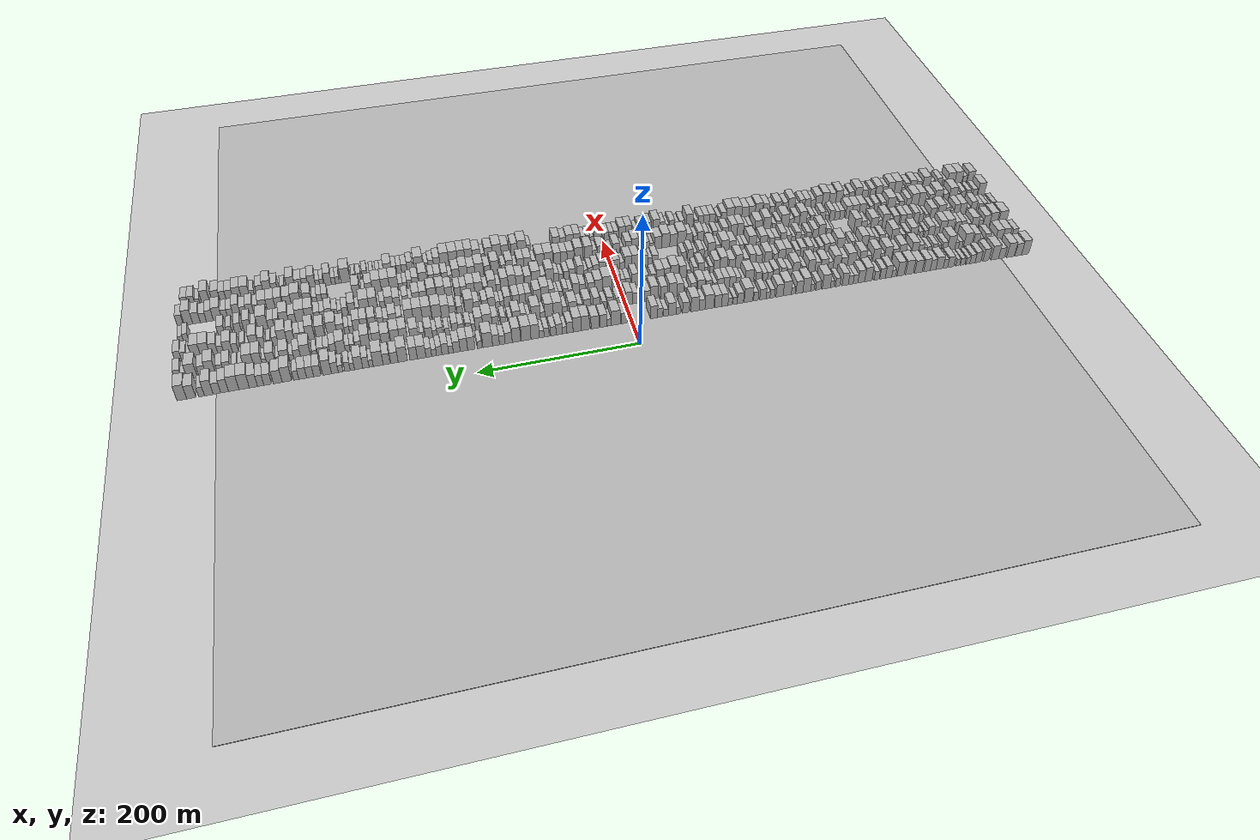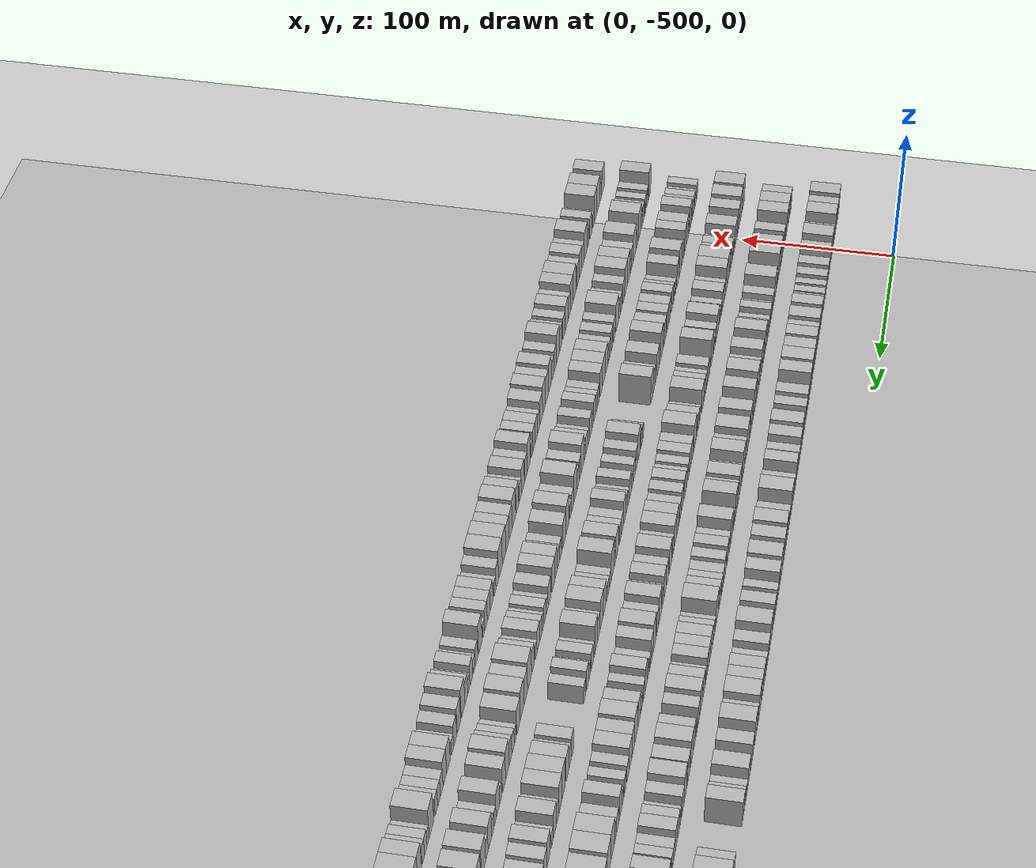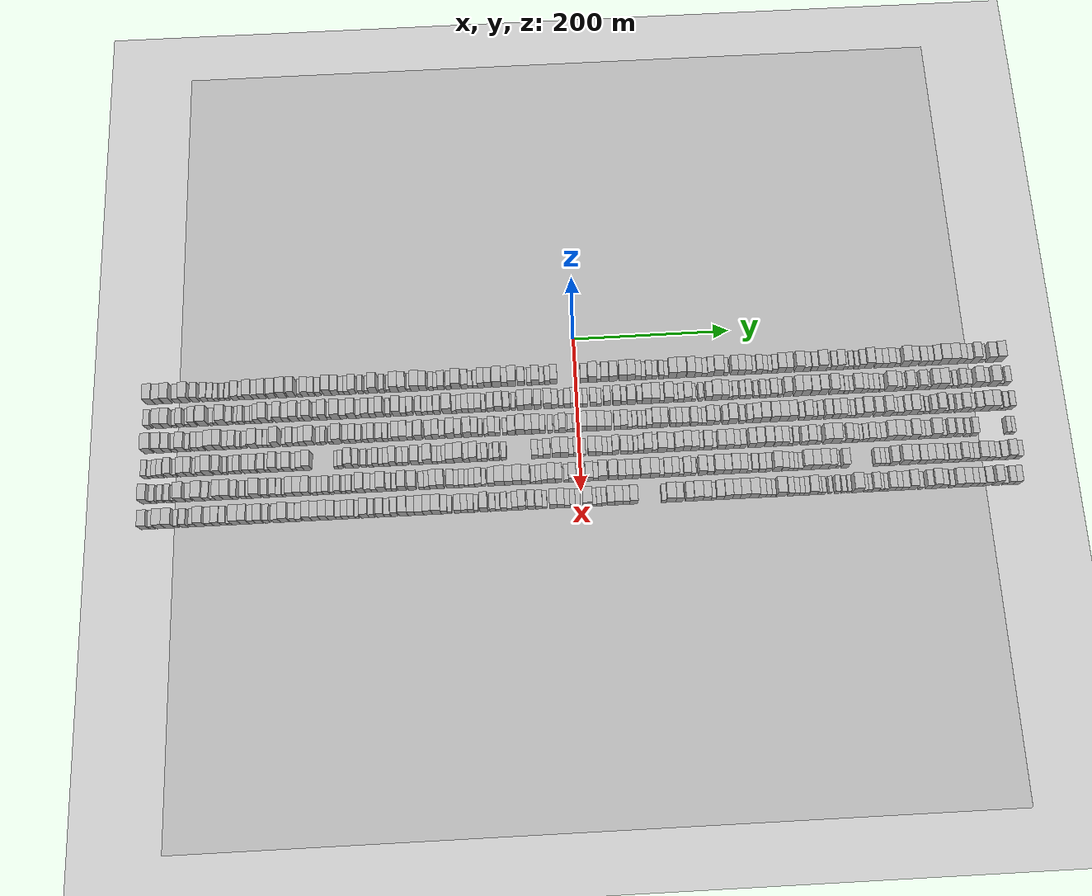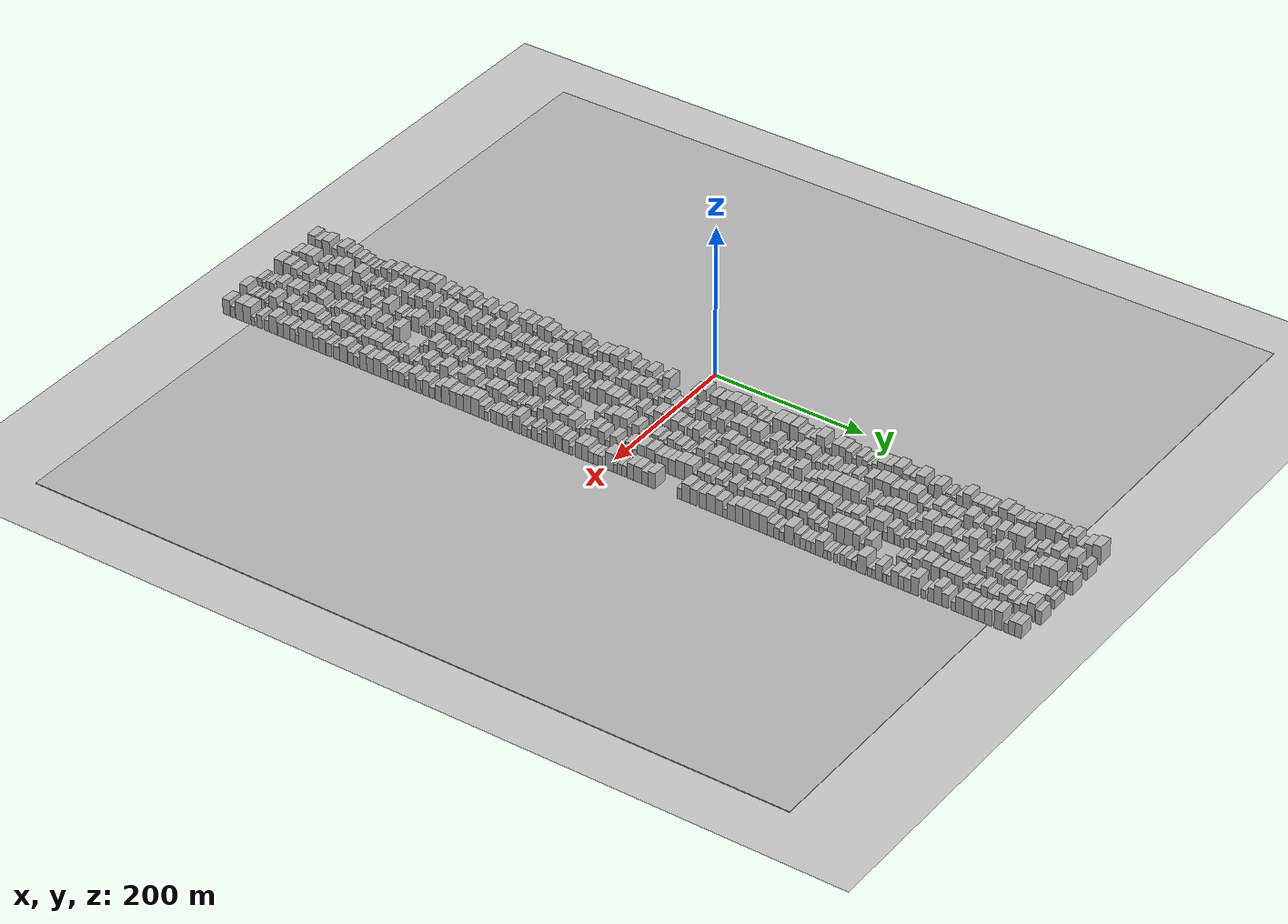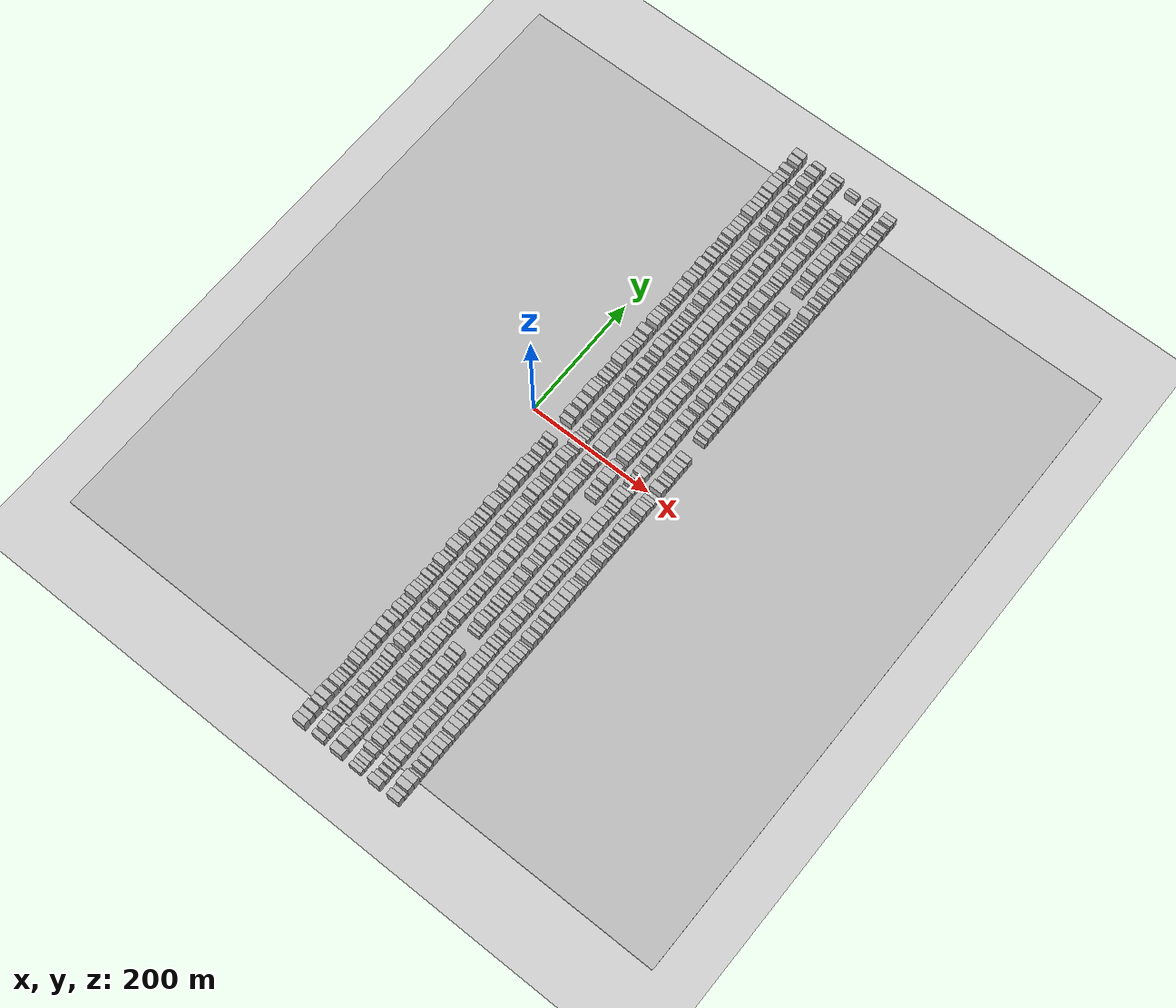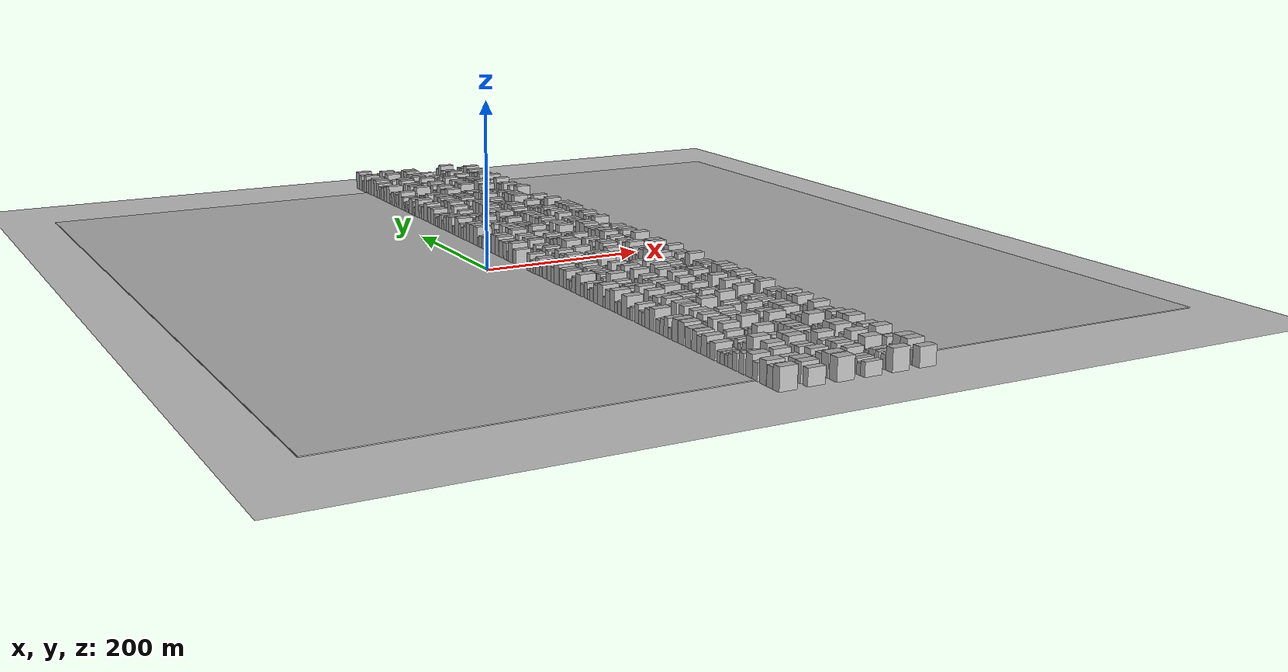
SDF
<?xml version="1.0" encoding="utf-8"?>

<sdf version="1.6">

   <world name="default">

      <gui fullscreen="0">

         <camera name="user_camera">

            <pose>-15 0 4.57585 0 0 0</pose>

            <view_controller>orbit</view_controller>

         </camera>

      </gui>

      <scene>

         <sky>

           <clouds>

             <speed>12</speed>

           </clouds>

         </sky>

         <ambient>0.4 0.4 0.4 1</ambient>

         <background>0.7 0.7 0.7 1</background>

         <shadows>1</shadows>

      </scene>

      <gravity>0 0 -9.8066</gravity>

      <magnetic_field>6e-06 2.3e-05 -4.2e-05</magnetic_field>

      <physics default="0" name="default_physics" type="ode">

         <ode>

            <solver>

               <type>quick</type>

               <iters>10</iters>

               <sor>1.0</sor>

               <use_dynamic_moi_rescaling>0</use_dynamic_moi_rescaling>

            </solver>

            <constraints>

               <cfm>0</cfm>

               <erp>0.2</erp>

               <contact_max_correcting_vel>100</contact_max_correcting_vel>

               <contact_surface_layer>0.001</contact_surface_layer>

            </constraints>

         </ode>

         <max_step_size>0.004</max_step_size>

         <real_time_factor>1</real_time_factor>

         <real_time_update_rate>250</real_time_update_rate>

      </physics>

      <light name="sun" type="directional">

         <cast_shadows>1</cast_shadows>

         <pose>0 0 10 0 0 0</pose>

         <diffuse>0.8 0.8 0.8 1</diffuse>

         <specular>0.2 0.2 0.2 1</specular>

         <attenuation>

            <range>1000</range>

            <constant>0.9</constant>

            <linear>0.01</linear>

            <quadratic>0.001</quadratic>

         </attenuation>

         <direction>-0.5 0.1 -0.9</direction>

      </light>

      <include>

         <name>ground_plane_1</name>

         <uri>model://HANNAS_ground_plane</uri>

         <pose>0 0 0  0 0 0</pose>

      </include>

      <include>

         <name>ground_plane_2</name>

         <uri>model://HANNAS_ground_plane</uri>

         <pose>100 0 0  0 0 0</pose>

      </include>

      <model name="building_1">

         <static>1</static>

         <pose frame="">50.0000 -534.6889 0 0.000000 0.000000 0.000000</pose>

         <link name="link">

            <pose frame="">0 0 12.00 0 0 0</pose>

            <collision name="collision">

               <geometry>

                  <box>

                     <size>20.0000 10.6221 24.0000</size>

                  </box>

               </geometry>

               <max_contacts>10</max_contacts>

               <surface>

                  <contact>

                     <ode/>

                  </contact>

                  <bounce/>

                  <friction>

                     <torsional>

                        <ode/>

                     </torsional>

                     <ode/>

                  </friction>

               </surface>

            </collision>

            <visual name="visual">

               <cast_shadows>0</cast_shadows>

               <geometry>

                  <box>

                     <size>20.0000 10.6221 24.0000</size>

                  </box>

               </geometry>

               <material>

                  <script>

                     <uri>model://HANNAS_wall/materials/scripts</uri>

                     <uri>model://HANNAS_wall/materials/textures</uri>

                     <name>vrc/HANNAS_wall</name>

                  </script>

               </material>

            </visual>

            <self_collide>0</self_collide>

            <enable_wind>0</enable_wind>

            <kinematic>0</kinematic>

         </link>

      </model>

      <model name="building_2">

         <static>1</static>

         <pose frame="">50.0000 -524.6034 0 0.000000 0.000000 0.000000</pose>

         <link name="link">

            <pose frame="">0 0 10.50 0 0 0</pose>

            <collision name="collision">

               <geometry>

                  <box>

                     <size>20.0000 9.5490 21.0000</size>

                  </box>

               </geometry>

               <max_contacts>10</max_contacts>

               <surface>

                  <contact>

                     <ode/>

                  </contact>

                  <bounce/>

                  <friction>

                     <torsional>

                        <ode/>

                     </torsional>

                     <ode/>

                  </friction>

               </surface>

            </collision>

            <visual name="visual">

               <cast_shadows>0</cast_shadows>

               <geometry>

                  <box>

                     <size>20.0000 9.5490 21.0000</size>

                  </box>

               </geometry>

               <material>

                  <script>

                     <uri>model://HANNAS_wall/materials/scripts</uri>

                     <uri>model://HANNAS_wall/materials/textures</uri>

                     <name>vrc/HANNAS_wall</name>

                  </script>

               </material>

            </visual>

            <self_collide>0</self_collide>

            <enable_wind>0</enable_wind>

            <kinematic>0</kinematic>

         </link>

      </model>

      <model name="building_3">

         <static>1</static>

         <pose frame="">50.0000 -513.3731 0 0.000000 0.000000 0.000000</pose>

         <link name="link">

            <pose frame="">0 0 12.00 0 0 0</pose>

            <collision name="collision">

               <geometry>

                  <box>

                     <size>20.0000 10.9115 24.0000</size>

                  </box>

               </geometry>

               <max_contacts>10</max_contacts>

               <surface>

                  <contact>

                     <ode/>

                  </contact>

                  <bounce/>

                  <friction>

                     <torsional>

                        <ode/>

                     </torsional>

                     <ode/>

                  </friction>

               </surface>

            </collision>

            <visual name="visual">

               <cast_shadows>0</cast_shadows>

               <geometry>

                  <box>

                     <size>20.0000 10.9115 24.0000</size>

                  </box>

               </geometry>

               <material>

                  <script>

                     <uri>model://HANNAS_wall/materials/scripts</uri>

                     <uri>model://HANNAS_wall/materials/textures</uri>

                     <name>vrc/HANNAS_wall</name>

                  </script>

               </material>

            </visual>

            <self_collide>0</self_collide>

            <enable_wind>0</enable_wind>

            <kinematic>0</kinematic>

         </link>

      </model>

      <model name="building_4">

         <static>1</static>

         <pose frame="">50.0000 -500.5222 0 0.000000 0.000000 0.000000</pose>

         <link name="link">

            <pose frame="">0 0 9.00 0 0 0</pose>

            <collision name="collision">

               <geometry>

                  <box>

                     <size>20.0000 8.7904 18.0000</size>

                  </box>

               </geometry>

               <max_contacts>10</max_contacts>

               <surface>

                  <contact>

                     <ode/>

                  </contact>

                  <bounce/>

                  <friction>

                     <torsional>

                        <ode/>

                     </torsional>

                     <ode/>

                  </friction>

               </surface>

            </collision>

            <visual name="visual">

               <cast_shadows>0</cast_shadows>

               <geometry>

                  <box>

                     <size>20.0000 8.7904 18.0000</size>

                  </box>

               </geometry>

               <material>

                  <script>

                     <uri>model://HANNAS_wall/materials/scripts</uri>

                     <uri>model://HANNAS_wall/materials/textures</uri>

                     <name>vrc/HANNAS_wall</name>

                  </script>

               </material>

            </visual>

            <self_collide>0</self_collide>

            <enable_wind>0</enable_wind>

            <kinematic>0</kinematic>

         </link>

      </model>

      <model name="building_5">

         <static>1</static>

         <pose frame="">50.0000 -490.6456 0 0.000000 0.000000 0.000000</pose>

         <link name="link">

            <pose frame="">0 0 12.00 0 0 0</pose>

            <collision name="collision">

               <geometry>

                  <box>

                     <size>20.0000 10.9627 24.0000</size>

                  </box>

               </geometry>

               <max_contacts>10</max_contacts>

               <surface>

                  <contact>

                     <ode/>

                  </contact>

                  <bounce/>

                  <friction>

                     <torsional>

                        <ode/>

                     </torsional>

                     <ode/>

                  </friction>

               </surface>

            </collision>

            <visual name="visual">

               <cast_shadows>0</cast_shadows>

               <geometry>

                  <box>

                     <size>20.0000 10.9627 24.0000</size>

                  </box>

               </geometry>

               <material>

                  <script>

                     <uri>model://HANNAS_wall/materials/scripts</uri>

                     <uri>model://HANNAS_wall/materials/textures</uri>

                     <name>vrc/HANNAS_wall</name>

                  </script>

               </material>

            </visual>

            <self_collide>0</self_collide>

            <enable_wind>0</enable_wind>

            <kinematic>0</kinematic>

         </link>

      </model>

      <model name="building_6">

         <static>1</static>

         <pose frame="">50.0000 -477.8518 0 0.000000 0.000000 0.000000</pose>

         <link name="link">

            <pose frame="">0 0 10.50 0 0 0</pose>

            <collision name="collision">

               <geometry>

                  <box>

                     <size>20.0000 8.6249 21.0000</size>

                  </box>

               </geometry>

               <max_contacts>10</max_contacts>

               <surface>

                  <contact>

                     <ode/>

                  </contact>

                  <bounce/>

                  <friction>

                     <torsional>

                        <ode/>

                     </torsional>

                     <ode/>

                  </friction>

               </surface>

            </collision>

            <visual name="visual">

               <cast_shadows>0</cast_shadows>

               <geometry>

                  <box>

                     <size>20.0000 8.6249 21.0000</size>

                  </box>

               </geometry>

               <material>

                  <script>

                     <uri>model://HANNAS_wall/materials/scripts</uri>

                     <uri>model://HANNAS_wall/materials/textures</uri>

                     <name>vrc/HANNAS_wall</name>

                  </script>

               </material>

            </visual>

            <self_collide>0</self_collide>

            <enable_wind>0</enable_wind>

            <kinematic>0</kinematic>

         </link>

      </model>

      <model name="building_7">

         <static>1</static>

         <pose frame="">50.0000 -466.4373 0 0.000000 0.000000 0.000000</pose>

         <link name="link">

            <pose frame="">0 0 9.00 0 0 0</pose>

            <collision name="collision">

               <geometry>

                  <box>

                     <size>20.0000 8.2041 18.0000</size>

                  </box>

               </geometry>

               <max_contacts>10</max_contacts>

               <surface>

                  <contact>

                     <ode/>

                  </contact>

                  <bounce/>

                  <friction>

                     <torsional>

                        <ode/>

                     </torsional>

                     <ode/>

                  </friction>

               </surface>

            </collision>

            <visual name="visual">

               <cast_shadows>0</cast_shadows>

               <geometry>

                  <box>

                     <size>20.0000 8.2041 18.0000</size>

                  </box>

               </geometry>

               <material>

                  <script>

                     <uri>model://HANNAS_wall/materials/scripts</uri>

                     <uri>model://HANNAS_wall/materials/textures</uri>

                     <name>vrc/HANNAS_wall</name>

                  </script>

               </material>

            </visual>

            <self_collide>0</self_collide>

            <enable_wind>0</enable_wind>

            <kinematic>0</kinematic>

         </link>

      </model>

      <model name="building_8">

         <static>1</static>

         <pose frame="">50.0000 -458.6460 0 0.000000 0.000000 0.000000</pose>

         <link name="link">

            <pose frame="">0 0 7.50 0 0 0</pose>

            <collision name="collision">

               <geometry>

                  <box>

                     <size>20.0000 7.3786 15.0000</size>

                  </box>

               </geometry>

               <max_contacts>10</max_contacts>

               <surface>

                  <contact>

                     <ode/>

                  </contact>

                  <bounce/>

                  <friction>

                     <torsional>

                        <ode/>

                     </torsional>

                     <ode/>

                  </friction>

               </surface>

            </collision>

            <visual name="visual">

               <cast_shadows>0</cast_shadows>

               <geometry>

                  <box>

                     <size>20.0000 7.3786 15.0000</size>

                  </box>

               </geometry>

               <material>

                  <script>

                     <uri>model://HANNAS_wall/materials/scripts</uri>

                     <uri>model://HANNAS_wall/materials/textures</uri>

                     <name>vrc/HANNAS_wall</name>

                  </script>

               </material>

            </visual>

            <self_collide>0</self_collide>

            <enable_wind>0</enable_wind>

            <kinematic>0</kinematic>

         </link>

      </model>

      <model name="building_9">

         <static>1</static>

         <pose frame="">50.0000 -452.1607 0 0.000000 0.000000 0.000000</pose>

         <link name="link">

            <pose frame="">0 0 6.00 0 0 0</pose>

            <collision name="collision">

               <geometry>

                  <box>

                     <size>20.0000 5.5920 12.0000</size>

                  </box>

               </geometry>

               <max_contacts>10</max_contacts>

               <surface>

                  <contact>

                     <ode/>

                  </contact>

                  <bounce/>

                  <friction>

                     <torsional>

                        <ode/>

                     </torsional>

                     <ode/>

                  </friction>

               </surface>

            </collision>

            <visual name="visual">

               <cast_shadows>0</cast_shadows>

               <geometry>

                  <box>

                     <size>20.0000 5.5920 12.0000</size>

                  </box>

               </geometry>

               <material>

                  <script>

                     <uri>model://HANNAS_wall/materials/scripts</uri>

                     <uri>model://HANNAS_wall/materials/textures</uri>

                     <name>vrc/HANNAS_wall</name>

                  </script>

               </material>

            </visual>

            <self_collide>0</self_collide>

            <enable_wind>0</enable_wind>

            <kinematic>0</kinematic>

         </link>

      </model>

      <model name="building_10">

         <static>1</static>

         <pose frame="">50.0000 -444.4440 0 0.000000 0.000000 0.000000</pose>

         <link name="link">

            <pose frame="">0 0 6.00 0 0 0</pose>

            <collision name="collision">

               <geometry>

                  <box>

                     <size>20.0000 5.8414 12.0000</size>

                  </box>

               </geometry>

               <max_contacts>10</max_contacts>

               <surface>

                  <contact>

                     <ode/>

                  </contact>

                  <bounce/>

                  <friction>

                     <torsional>

                        <ode/>

                     </torsional>

                     <ode/>

                  </friction>

               </surface>

            </collision>

            <visual name="visual">

               <cast_shadows>0</cast_shadows>

               <geometry>

                  <box>

                     <size>20.0000 5.8414 12.0000</size>

                  </box>

               </geometry>

               <material>

                  <script>

                     <uri>model://HANNAS_wall/materials/scripts</uri>

                     <uri>model://HANNAS_wall/materials/textures</uri>

                     <name>vrc/HANNAS_wall</name>

                  </script>

               </material>

            </visual>

            <self_collide>0</self_collide>

            <enable_wind>0</enable_wind>

            <kinematic>0</kinematic>

         </link>

      </model>

      <model name="building_11">

         <static>1</static>

         <pose frame="">50.0000 -437.8326 0 0.000000 0.000000 0.000000</pose>

         <link name="link">

            <pose frame="">0 0 6.00 0 0 0</pose>

            <collision name="collision">

               <geometry>

                  <box>

                     <size>20.0000 5.3815 12.0000</size>

                  </box>

               </geometry>

               <max_contacts>10</max_contacts>

               <surface>

                  <contact>

                     <ode/>

                  </contact>

                  <bounce/>

                  <friction>

                     <torsional>

                        <ode/>

                     </torsional>

                     <ode/>

                  </friction>

               </surface>

            </collision>

            <visual name="visual">

               <cast_shadows>0</cast_shadows>

               <geometry>

                  <box>

                     <size>20.0000 5.3815 12.0000</size>

                  </box>

               </geometry>

               <material>

                  <script>

                     <uri>model://HANNAS_wall/materials/scripts</uri>

                     <uri>model://HANNAS_wall/materials/textures</uri>

                     <name>vrc/HANNAS_wall</name>

                  </script>

               </material>

            </visual>

            <self_collide>0</self_collide>

            <enable_wind>0</enable_wind>

            <kinematic>0</kinematic>

         </link>

      </model>

      <model name="building_12">

         <static>1</static>

         <pose frame="">50.0000 -427.6736 0 0.000000 0.000000 0.000000</pose>

         <link name="link">

            <pose frame="">0 0 9.00 0 0 0</pose>

            <collision name="collision">

               <geometry>

                  <box>

                     <size>20.0000 8.9365 18.0000</size>

                  </box>

               </geometry>

               <max_contacts>10</max_contacts>

               <surface>

                  <contact>

                     <ode/>

                  </contact>

                  <bounce/>

                  <friction>

                     <torsional>

                        <ode/>

                     </torsional>

                     <ode/>

                  </friction>

               </surface>

            </collision>

            <visual name="visual">

               <cast_shadows>0</cast_shadows>

               <geometry>

                  <box>

                     <size>20.0000 8.9365 18.0000</size>

                  </box>

               </geometry>

               <material>

                  <script>

                     <uri>model://HANNAS_wall/materials/scripts</uri>

                     <uri>model://HANNAS_wall/materials/textures</uri>

                     <name>vrc/HANNAS_wall</name>

                  </script>

               </material>

            </visual>

            <self_collide>0</self_collide>

            <enable_wind>0</enable_wind>

            <kinematic>0</kinematic>

         </link>

      </model>

      <model name="building_13">

         <static>1</static>

         <pose frame="">50.0000 -420.0522 0 0.000000 0.000000 0.000000</pose>

         <link name="link">

            <pose frame="">0 0 7.50 0 0 0</pose>

            <collision name="collision">

               <geometry>

                  <box>

                     <size>20.0000 6.3062 15.0000</size>

                  </box>

               </geometry>

               <max_contacts>10</max_contacts>

               <surface>

                  <contact>

                     <ode/>

                  </contact>

                  <bounce/>

                  <friction>

                     <torsional>

                        <ode/>

                     </torsional>

                     <ode/>

                  </friction>

               </surface>

            </collision>

            <visual name="visual">

               <cast_shadows>0</cast_shadows>

               <geometry>

                  <box>

                     <size>20.0000 6.3062 15.0000</size>

                  </box>

               </geometry>

               <material>

                  <script>

                     <uri>model://HANNAS_wall/materials/scripts</uri>

                     <uri>model://HANNAS_wall/materials/textures</uri>

                     <name>vrc/HANNAS_wall</name>

                  </script>

               </material>

            </visual>

            <self_collide>0</self_collide>

            <enable_wind>0</enable_wind>

            <kinematic>0</kinematic>

         </link>

      </model>

      <model name="building_14">

         <static>1</static>

         <pose frame="">50.0000 -411.8444 0 0.000000 0.000000 0.000000</pose>

         <link name="link">

            <pose frame="">0 0 10.50 0 0 0</pose>

            <collision name="collision">

               <geometry>

                  <box>

                     <size>20.0000 10.1093 21.0000</size>

                  </box>

               </geometry>

               <max_contacts>10</max_contacts>

               <surface>

                  <contact>

                     <ode/>

                  </contact>

                  <bounce/>

                  <friction>

                     <torsional>

                        <ode/>

                     </torsional>

                     <ode/>

                  </friction>

               </surface>

            </collision>

            <visual name="visual">

               <cast_shadows>0</cast_shadows>

               <geometry>

                  <box>

                     <size>20.0000 10.1093 21.0000</size>

                  </box>

               </geometry>

               <material>

                  <script>

                     <uri>model://HANNAS_wall/materials/scripts</uri>

                     <uri>model://HANNAS_wall/materials/textures</uri>

                     <name>vrc/HANNAS_wall</name>

                  </script>

               </material>

            </visual>

            <self_collide>0</self_collide>

            <enable_wind>0</enable_wind>

            <kinematic>0</kinematic>

         </link>

      </model>

      <model name="building_15">

         <static>1</static>

         <pose frame="">50.0000 -402.8027 0 0.000000 0.000000 0.000000</pose>

         <link name="link">

            <pose frame="">0 0 9.00 0 0 0</pose>

            <collision name="collision">

               <geometry>

                  <box>

                     <size>20.0000 7.9742 18.0000</size>

                  </box>

               </geometry>

               <max_contacts>10</max_contacts>

               <surface>

                  <contact>

                     <ode/>

                  </contact>

                  <bounce/>

                  <friction>

                     <torsional>

                        <ode/>

                     </torsional>

                     <ode/>

                  </friction>

               </surface>

            </collision>

            <visual name="visual">

               <cast_shadows>0</cast_shadows>

               <geometry>

                  <box>

                     <size>20.0000 7.9742 18.0000</size>

                  </box>

               </geometry>

               <material>

                  <script>

                     <uri>model://HANNAS_wall/materials/scripts</uri>

                     <uri>model://HANNAS_wall/materials/textures</uri>

                     <name>vrc/HANNAS_wall</name>

                  </script>

               </material>

            </visual>

            <self_collide>0</self_collide>

            <enable_wind>0</enable_wind>

            <kinematic>0</kinematic>

         </link>

      </model>

      <model name="building_16">

         <static>1</static>

         <pose frame="">50.0000 -394.1698 0 0.000000 0.000000 0.000000</pose>

         <link name="link">

            <pose frame="">0 0 10.50 0 0 0</pose>

            <collision name="collision">

               <geometry>

                  <box>

                     <size>20.0000 9.2916 21.0000</size>

                  </box>

               </geometry>

               <max_contacts>10</max_contacts>

               <surface>

                  <contact>

                     <ode/>

                  </contact>

                  <bounce/>

                  <friction>

                     <torsional>

                        <ode/>

                     </torsional>

                     <ode/>

                  </friction>

               </surface>

            </collision>

            <visual name="visual">

               <cast_shadows>0</cast_shadows>

               <geometry>

                  <box>

                     <size>20.0000 9.2916 21.0000</size>

                  </box>

               </geometry>

               <material>

                  <script>

                     <uri>model://HANNAS_wall/materials/scripts</uri>

                     <uri>model://HANNAS_wall/materials/textures</uri>

                     <name>vrc/HANNAS_wall</name>

                  </script>

               </material>

            </visual>

            <self_collide>0</self_collide>

            <enable_wind>0</enable_wind>

            <kinematic>0</kinematic>

         </link>

      </model>

      <model name="building_17">

         <static>1</static>

         <pose frame="">50.0000 -382.2855 0 0.000000 0.000000 0.000000</pose>

         <link name="link">

            <pose frame="">0 0 10.50 0 0 0</pose>

            <collision name="collision">

               <geometry>

                  <box>

                     <size>20.0000 10.4769 21.0000</size>

                  </box>

               </geometry>

               <max_contacts>10</max_contacts>

               <surface>

                  <contact>

                     <ode/>

                  </contact>

                  <bounce/>

                  <friction>

                     <torsional>

                        <ode/>

                     </torsional>

                     <ode/>

                  </friction>

               </surface>

            </collision>

            <visual name="visual">

               <cast_shadows>0</cast_shadows>

               <geometry>

                  <box>

                     <size>20.0000 10.4769 21.0000</size>

                  </box>

               </geometry>

               <material>

                  <script>

                     <uri>model://HANNAS_wall/materials/scripts</uri>

                     <uri>model://HANNAS_wall/materials/textures</uri>

                     <name>vrc/HANNAS_wall</name>

                  </script>

               </material>

            </visual>

            <self_collide>0</self_collide>

            <enable_wind>0</enable_wind>

            <kinematic>0</kinematic>

         </link>

      </model>

      <model name="building_18">

         <static>1</static>

         <pose frame="">50.0000 -369.6378 0 0.000000 0.000000 0.000000</pose>

         <link name="link">

            <pose frame="">0 0 12.00 0 0 0</pose>

            <collision name="collision">

               <geometry>

                  <box>

                     <size>20.0000 10.8184 24.0000</size>

                  </box>

               </geometry>

               <max_contacts>10</max_contacts>

               <surface>

                  <contact>

                     <ode/>

                  </contact>

                  <bounce/>

                  <friction>

                     <torsional>

                        <ode/>

                     </torsional>

                     <ode/>

                  </friction>

               </surface>

            </collision>

            <visual name="visual">

               <cast_shadows>0</cast_shadows>

               <geometry>

                  <box>

                     <size>20.0000 10.8184 24.0000</size>

                  </box>

               </geometry>

               <material>

                  <script>

                     <uri>model://HANNAS_wall/materials/scripts</uri>

                     <uri>model://HANNAS_wall/materials/textures</uri>

                     <name>vrc/HANNAS_wall</name>

                  </script>

               </material>

            </visual>

            <self_collide>0</self_collide>

            <enable_wind>0</enable_wind>

            <kinematic>0</kinematic>

         </link>

      </model>

      <model name="building_19">

         <static>1</static>

         <pose frame="">50.0000 -357.3450 0 0.000000 0.000000 0.000000</pose>

         <link name="link">

            <pose frame="">0 0 12.00 0 0 0</pose>

            <collision name="collision">

               <geometry>

                  <box>

                     <size>20.0000 9.7672 24.0000</size>

                  </box>

               </geometry>

               <max_contacts>10</max_contacts>

               <surface>

                  <contact>

                     <ode/>

                  </contact>

                  <bounce/>

                  <friction>

                     <torsional>

                        <ode/>

                     </torsional>

                     <ode/>

                  </friction>

               </surface>

            </collision>

            <visual name="visual">

               <cast_shadows>0</cast_shadows>

               <geometry>

                  <box>

                     <size>20.0000 9.7672 24.0000</size>

                  </box>

               </geometry>

               <material>

                  <script>

                     <uri>model://HANNAS_wall/materials/scripts</uri>

                     <uri>model://HANNAS_wall/materials/textures</uri>

                     <name>vrc/HANNAS_wall</name>

                  </script>

               </material>

            </visual>

            <self_collide>0</self_collide>

            <enable_wind>0</enable_wind>

            <kinematic>0</kinematic>

         </link>

      </model>

      <model name="building_20">

         <static>1</static>

         <pose frame="">50.0000 -347.6540 0 0.000000 0.000000 0.000000</pose>

         <link name="link">

            <pose frame="">0 0 6.00 0 0 0</pose>

            <collision name="collision">

               <geometry>

                  <box>

                     <size>20.0000 5.6147 12.0000</size>

                  </box>

               </geometry>

               <max_contacts>10</max_contacts>

               <surface>

                  <contact>

                     <ode/>

                  </contact>

                  <bounce/>

                  <friction>

                     <torsional>

                        <ode/>

                     </torsional>

                     <ode/>

                  </friction>

               </surface>

            </collision>

            <visual name="visual">

               <cast_shadows>0</cast_shadows>

               <geometry>

                  <box>

                     <size>20.0000 5.6147 12.0000</size>

                  </box>

               </geometry>

               <material>

                  <script>

                     <uri>model://HANNAS_wall/materials/scripts</uri>

                     <uri>model://HANNAS_wall/materials/textures</uri>

                     <name>vrc/HANNAS_wall</name>

                  </script>

               </material>

            </visual>

            <self_collide>0</self_collide>

            <enable_wind>0</enable_wind>

            <kinematic>0</kinematic>

         </link>

      </model>

      <model name="building_21">

         <static>1</static>

         <pose frame="">50.0000 -340.4509 0 0.000000 0.000000 0.000000</pose>

         <link name="link">

            <pose frame="">0 0 10.50 0 0 0</pose>

            <collision name="collision">

               <geometry>

                  <box>

                     <size>20.0000 8.7916 21.0000</size>

                  </box>

               </geometry>

               <max_contacts>10</max_contacts>

               <surface>

                  <contact>

                     <ode/>

                  </contact>

                  <bounce/>

                  <friction>

                     <torsional>

                        <ode/>

                     </torsional>

                     <ode/>

                  </friction>

               </surface>

            </collision>

            <visual name="visual">

               <cast_shadows>0</cast_shadows>

               <geometry>

                  <box>

                     <size>20.0000 8.7916 21.0000</size>

                  </box>

               </geometry>

               <material>

                  <script>

                     <uri>model://HANNAS_wall/materials/scripts</uri>

                     <uri>model://HANNAS_wall/materials/textures</uri>

                     <name>vrc/HANNAS_wall</name>

                  </script>

               </material>

            </visual>

            <self_collide>0</self_collide>

            <enable_wind>0</enable_wind>

            <kinematic>0</kinematic>

         </link>

      </model>

      <model name="building_22">

         <static>1</static>

         <pose frame="">50.0000 -332.2096 0 0.000000 0.000000 0.000000</pose>

         <link name="link">

            <pose frame="">0 0 9.00 0 0 0</pose>

            <collision name="collision">

               <geometry>

                  <box>

                     <size>20.0000 7.6908 18.0000</size>

                  </box>

               </geometry>

               <max_contacts>10</max_contacts>

               <surface>

                  <contact>

                     <ode/>

                  </contact>

                  <bounce/>

                  <friction>

                     <torsional>

                        <ode/>

                     </torsional>

                     <ode/>

                  </friction>

               </surface>

            </collision>

            <visual name="visual">

               <cast_shadows>0</cast_shadows>

               <geometry>

                  <box>

                     <size>20.0000 7.6908 18.0000</size>

                  </box>

               </geometry>

               <material>

                  <script>

                     <uri>model://HANNAS_wall/materials/scripts</uri>

                     <uri>model://HANNAS_wall/materials/textures</uri>

                     <name>vrc/HANNAS_wall</name>

                  </script>

               </material>

            </visual>

            <self_collide>0</self_collide>

            <enable_wind>0</enable_wind>

            <kinematic>0</kinematic>

         </link>

      </model>

      <model name="building_23">

         <static>1</static>

         <pose frame="">50.0000 -323.9101 0 0.000000 0.000000 0.000000</pose>

         <link name="link">

            <pose frame="">0 0 7.50 0 0 0</pose>

            <collision name="collision">

               <geometry>

                  <box>

                     <size>20.0000 6.9083 15.0000</size>

                  </box>

               </geometry>

               <max_contacts>10</max_contacts>

               <surface>

                  <contact>

                     <ode/>

                  </contact>

                  <bounce/>

                  <friction>

                     <torsional>

                        <ode/>

                     </torsional>

                     <ode/>

                  </friction>

               </surface>

            </collision>

            <visual name="visual">

               <cast_shadows>0</cast_shadows>

               <geometry>

                  <box>

                     <size>20.0000 6.9083 15.0000</size>

                  </box>

               </geometry>

               <material>

                  <script>

                     <uri>model://HANNAS_wall/materials/scripts</uri>

                     <uri>model://HANNAS_wall/materials/textures</uri>

                     <name>vrc/HANNAS_wall</name>

                  </script>

               </material>

            </visual>

            <self_collide>0</self_collide>

            <enable_wind>0</enable_wind>

            <kinematic>0</kinematic>

         </link>

      </model>

      <model name="building_24">

         <static>1</static>

         <pose frame="">50.0000 -312.4057 0 0.000000 0.000000 0.000000</pose>

         <link name="link">

            <pose frame="">0 0 12.00 0 0 0</pose>

            <collision name="collision">

               <geometry>

                  <box>

                     <size>20.0000 10.1005 24.0000</size>

                  </box>

               </geometry>

               <max_contacts>10</max_contacts>

               <surface>

                  <contact>

                     <ode/>

                  </contact>

                  <bounce/>

                  <friction>

                     <torsional>

                        <ode/>

                     </torsional>

                     <ode/>

                  </friction>

               </surface>

            </collision>

            <visual name="visual">

               <cast_shadows>0</cast_shadows>

               <geometry>

                  <box>

                     <size>20.0000 10.1005 24.0000</size>

                  </box>

               </geometry>

               <material>

                  <script>

                     <uri>model://HANNAS_wall/materials/scripts</uri>

                     <uri>model://HANNAS_wall/materials/textures</uri>

                     <name>vrc/HANNAS_wall</name>

                  </script>

               </material>

            </visual>

            <self_collide>0</self_collide>

            <enable_wind>0</enable_wind>

            <kinematic>0</kinematic>

         </link>

      </model>

      <model name="building_25">

         <static>1</static>

         <pose frame="">50.0000 -302.7302 0 0.000000 0.000000 0.000000</pose>

         <link name="link">

            <pose frame="">0 0 10.50 0 0 0</pose>

            <collision name="collision">

               <geometry>

                  <box>

                     <size>20.0000 9.2506 21.0000</size>

                  </box>

               </geometry>

               <max_contacts>10</max_contacts>

               <surface>

                  <contact>

                     <ode/>

                  </contact>

                  <bounce/>

                  <friction>

                     <torsional>

                        <ode/>

                     </torsional>

                     <ode/>

                  </friction>

               </surface>

            </collision>

            <visual name="visual">

               <cast_shadows>0</cast_shadows>

               <geometry>

                  <box>

                     <size>20.0000 9.2506 21.0000</size>

                  </box>

               </geometry>

               <material>

                  <script>

                     <uri>model://HANNAS_wall/materials/scripts</uri>

                     <uri>model://HANNAS_wall/materials/textures</uri>

                     <name>vrc/HANNAS_wall</name>

                  </script>

               </material>

            </visual>

            <self_collide>0</self_collide>

            <enable_wind>0</enable_wind>

            <kinematic>0</kinematic>

         </link>

      </model>

      <model name="building_26">

         <static>1</static>

         <pose frame="">50.0000 -294.8835 0 0.000000 0.000000 0.000000</pose>

         <link name="link">

            <pose frame="">0 0 7.50 0 0 0</pose>

            <collision name="collision">

               <geometry>

                  <box>

                     <size>20.0000 6.4428 15.0000</size>

                  </box>

               </geometry>

               <max_contacts>10</max_contacts>

               <surface>

                  <contact>

                     <ode/>

                  </contact>

                  <bounce/>

                  <friction>

                     <torsional>

                        <ode/>

                     </torsional>

                     <ode/>

                  </friction>

               </surface>

            </collision>

            <visual name="visual">

               <cast_shadows>0</cast_shadows>

               <geometry>

                  <box>

                     <size>20.0000 6.4428 15.0000</size>

                  </box>

               </geometry>

               <material>

                  <script>

                     <uri>model://HANNAS_wall/materials/scripts</uri>

                     <uri>model://HANNAS_wall/materials/textures</uri>

                     <name>vrc/HANNAS_wall</name>

                  </script>

               </material>

            </visual>

            <self_collide>0</self_collide>

            <enable_wind>0</enable_wind>

            <kinematic>0</kinematic>

         </link>

      </model>

      <model name="building_27">

         <static>1</static>

         <pose frame="">50.0000 -288.3654 0 0.000000 0.000000 0.000000</pose>

         <link name="link">

            <pose frame="">0 0 7.50 0 0 0</pose>

            <collision name="collision">

               <geometry>

                  <box>

                     <size>20.0000 6.5933 15.0000</size>

                  </box>

               </geometry>

               <max_contacts>10</max_contacts>

               <surface>

                  <contact>

                     <ode/>

                  </contact>

                  <bounce/>

                  <friction>

                     <torsional>

                        <ode/>

                     </torsional>

                     <ode/>

                  </friction>

               </surface>

            </collision>

            <visual name="visual">

               <cast_shadows>0</cast_shadows>

               <geometry>

                  <box>

                     <size>20.0000 6.5933 15.0000</size>

                  </box>

               </geometry>

               <material>

                  <script>

                     <uri>model://HANNAS_wall/materials/scripts</uri>

                     <uri>model://HANNAS_wall/materials/textures</uri>

                     <name>vrc/HANNAS_wall</name>

                  </script>

               </material>

            </visual>

            <self_collide>0</self_collide>

            <enable_wind>0</enable_wind>

            <kinematic>0</kinematic>

         </link>

      </model>

      <model name="building_28">

         <static>1</static>

         <pose frame="">50.0000 -280.8394 0 0.000000 0.000000 0.000000</pose>

         <link name="link">

            <pose frame="">0 0 10.50 0 0 0</pose>

            <collision name="collision">

               <geometry>

                  <box>

                     <size>20.0000 8.4586 21.0000</size>

                  </box>

               </geometry>

               <max_contacts>10</max_contacts>

               <surface>

                  <contact>

                     <ode/>

                  </contact>

                  <bounce/>

                  <friction>

                     <torsional>

                        <ode/>

                     </torsional>

                     <ode/>

                  </friction>

               </surface>

            </collision>

            <visual name="visual">

               <cast_shadows>0</cast_shadows>

               <geometry>

                  <box>

                     <size>20.0000 8.4586 21.0000</size>

                  </box>

               </geometry>

               <material>

                  <script>

                     <uri>model://HANNAS_wall/materials/scripts</uri>

                     <uri>model://HANNAS_wall/materials/textures</uri>

                     <name>vrc/HANNAS_wall</name>

                  </script>

               </material>

            </visual>

            <self_collide>0</self_collide>

            <enable_wind>0</enable_wind>

            <kinematic>0</kinematic>

         </link>

      </model>

      <model name="building_29">

         <static>1</static>

         <pose frame="">50.0000 -270.5103 0 0.000000 0.000000 0.000000</pose>

         <link name="link">

            <pose frame="">0 0 7.50 0 0 0</pose>

            <collision name="collision">

               <geometry>

                  <box>

                     <size>20.0000 6.1996 15.0000</size>

                  </box>

               </geometry>

               <max_contacts>10</max_contacts>

               <surface>

                  <contact>

                     <ode/>

                  </contact>

                  <bounce/>

                  <friction>

                     <torsional>

                        <ode/>

                     </torsional>

                     <ode/>

                  </friction>

               </surface>

            </collision>

            <visual name="visual">

               <cast_shadows>0</cast_shadows>

               <geometry>

                  <box>

                     <size>20.0000 6.1996 15.0000</size>

                  </box>

               </geometry>

               <material>

                  <script>

                     <uri>model://HANNAS_wall/materials/scripts</uri>

                     <uri>model://HANNAS_wall/materials/textures</uri>

                     <name>vrc/HANNAS_wall</name>

                  </script>

               </material>

            </visual>

            <self_collide>0</self_collide>

            <enable_wind>0</enable_wind>

            <kinematic>0</kinematic>

         </link>

      </model>

      <model name="building_30">

         <static>1</static>

         <pose frame="">50.0000 -262.9905 0 0.000000 0.000000 0.000000</pose>

         <link name="link">

            <pose frame="">0 0 6.00 0 0 0</pose>

            <collision name="collision">

               <geometry>

                  <box>

                     <size>20.0000 4.8400 12.0000</size>

                  </box>

               </geometry>

               <max_contacts>10</max_contacts>

               <surface>

                  <contact>

                     <ode/>

                  </contact>

                  <bounce/>

                  <friction>

                     <torsional>

                        <ode/>

                     </torsional>

                     <ode/>

                  </friction>

               </surface>

            </collision>

            <visual name="visual">

               <cast_shadows>0</cast_shadows>

               <geometry>

                  <box>

                     <size>20.0000 4.8400 12.0000</size>

                  </box>

               </geometry>

               <material>

                  <script>

                     <uri>model://HANNAS_wall/materials/scripts</uri>

                     <uri>model://HANNAS_wall/materials/textures</uri>

                     <name>vrc/HANNAS_wall</name>

                  </script>

               </material>

            </visual>

            <self_collide>0</self_collide>

            <enable_wind>0</enable_wind>

            <kinematic>0</kinematic>

         </link>

      </model>

      <model name="building_31">

         <static>1</static>

         <pose frame="">50.0000 -255.0199 0 0.000000 0.000000 0.000000</pose>

         <link name="link">

            <pose frame="">0 0 12.00 0 0 0</pose>

            <collision name="collision">

               <geometry>

                  <box>

                     <size>20.0000 11.1011 24.0000</size>

                  </box>

               </geometry>

               <max_contacts>10</max_contacts>

               <surface>

                  <contact>

                     <ode/>

                  </contact>

                  <bounce/>

                  <friction>

                     <torsional>

                        <ode/>

                     </torsional>

                     <ode/>

                  </friction>

               </surface>

            </collision>

            <visual name="visual">

               <cast_shadows>0</cast_shadows>

               <geometry>

                  <box>

                     <size>20.0000 11.1011 24.0000</size>

                  </box>

               </geometry>

               <material>

                  <script>

                     <uri>model://HANNAS_wall/materials/scripts</uri>

                     <uri>model://HANNAS_wall/materials/textures</uri>

                     <name>vrc/HANNAS_wall</name>

                  </script>

               </material>

            </visual>

            <self_collide>0</self_collide>

            <enable_wind>0</enable_wind>

            <kinematic>0</kinematic>

         </link>

      </model>

      <model name="building_32">

         <static>1</static>

         <pose frame="">50.0000 -243.9982 0 0.000000 0.000000 0.000000</pose>

         <link name="link">

            <pose frame="">0 0 7.50 0 0 0</pose>

            <collision name="collision">

               <geometry>

                  <box>

                     <size>20.0000 6.9424 15.0000</size>

                  </box>

               </geometry>

               <max_contacts>10</max_contacts>

               <surface>

                  <contact>

                     <ode/>

                  </contact>

                  <bounce/>

                  <friction>

                     <torsional>

                        <ode/>

                     </torsional>

                     <ode/>

                  </friction>

               </surface>

            </collision>

            <visual name="visual">

               <cast_shadows>0</cast_shadows>

               <geometry>

                  <box>

                     <size>20.0000 6.9424 15.0000</size>

                  </box>

               </geometry>

               <material>

                  <script>

                     <uri>model://HANNAS_wall/materials/scripts</uri>

                     <uri>model://HANNAS_wall/materials/textures</uri>

                     <name>vrc/HANNAS_wall</name>

                  </script>

               </material>

            </visual>

            <self_collide>0</self_collide>

            <enable_wind>0</enable_wind>

            <kinematic>0</kinematic>

         </link>

      </model>

      <model name="building_33">

         <static>1</static>

         <pose frame="">50.0000 -236.0353 0 0.000000 0.000000 0.000000</pose>

         <link name="link">

            <pose frame="">0 0 6.00 0 0 0</pose>

            <collision name="collision">

               <geometry>

                  <box>

                     <size>20.0000 4.9834 12.0000</size>

                  </box>

               </geometry>

               <max_contacts>10</max_contacts>

               <surface>

                  <contact>

                     <ode/>

                  </contact>

                  <bounce/>

                  <friction>

                     <torsional>

                        <ode/>

                     </torsional>

                     <ode/>

                  </friction>

               </surface>

            </collision>

            <visual name="visual">

               <cast_shadows>0</cast_shadows>

               <geometry>

                  <box>

                     <size>20.0000 4.9834 12.0000</size>

                  </box>

               </geometry>

               <material>

                  <script>

                     <uri>model://HANNAS_wall/materials/scripts</uri>

                     <uri>model://HANNAS_wall/materials/textures</uri>

                     <name>vrc/HANNAS_wall</name>

                  </script>

               </material>

            </visual>

            <self_collide>0</self_collide>

            <enable_wind>0</enable_wind>

            <kinematic>0</kinematic>

         </link>

      </model>

      <model name="building_34">

         <static>1</static>

         <pose frame="">50.0000 -228.3454 0 0.000000 0.000000 0.000000</pose>

         <link name="link">

            <pose frame="">0 0 12.00 0 0 0</pose>

            <collision name="collision">

               <geometry>

                  <box>

                     <size>20.0000 10.3963 24.0000</size>

                  </box>

               </geometry>

               <max_contacts>10</max_contacts>

               <surface>

                  <contact>

                     <ode/>

                  </contact>

                  <bounce/>

                  <friction>

                     <torsional>

                        <ode/>

                     </torsional>

                     <ode/>

                  </friction>

               </surface>

            </collision>

            <visual name="visual">

               <cast_shadows>0</cast_shadows>

               <geometry>

                  <box>

                     <size>20.0000 10.3963 24.0000</size>

                  </box>

               </geometry>

               <material>

                  <script>

                     <uri>model://HANNAS_wall/materials/scripts</uri>

                     <uri>model://HANNAS_wall/materials/textures</uri>

                     <name>vrc/HANNAS_wall</name>

                  </script>

               </material>

            </visual>

            <self_collide>0</self_collide>

            <enable_wind>0</enable_wind>

            <kinematic>0</kinematic>

         </link>

      </model>

      <model name="building_35">

         <static>1</static>

         <pose frame="">50.0000 -218.4454 0 0.000000 0.000000 0.000000</pose>

         <link name="link">

            <pose frame="">0 0 10.50 0 0 0</pose>

            <collision name="collision">

               <geometry>

                  <box>

                     <size>20.0000 9.4037 21.0000</size>

                  </box>

               </geometry>

               <max_contacts>10</max_contacts>

               <surface>

                  <contact>

                     <ode/>

                  </contact>

                  <bounce/>

                  <friction>

                     <torsional>

                        <ode/>

                     </torsional>

                     <ode/>

                  </friction>

               </surface>

            </collision>

            <visual name="visual">

               <cast_shadows>0</cast_shadows>

               <geometry>

                  <box>

                     <size>20.0000 9.4037 21.0000</size>

                  </box>

               </geometry>

               <material>

                  <script>

                     <uri>model://HANNAS_wall/materials/scripts</uri>

                     <uri>model://HANNAS_wall/materials/textures</uri>

                     <name>vrc/HANNAS_wall</name>

                  </script>

               </material>

            </visual>

            <self_collide>0</self_collide>

            <enable_wind>0</enable_wind>

            <kinematic>0</kinematic>

         </link>

      </model>

      <model name="building_36">

         <static>1</static>

         <pose frame="">50.0000 -210.1838 0 0.000000 0.000000 0.000000</pose>

         <link name="link">

            <pose frame="">0 0 6.00 0 0 0</pose>

            <collision name="collision">

               <geometry>

                  <box>

                     <size>20.0000 5.1195 12.0000</size>

                  </box>

               </geometry>

               <max_contacts>10</max_contacts>

               <surface>

                  <contact>

                     <ode/>

                  </contact>

                  <bounce/>

                  <friction>

                     <torsional>

                        <ode/>

                     </torsional>

                     <ode/>

                  </friction>

               </surface>

            </collision>

            <visual name="visual">

               <cast_shadows>0</cast_shadows>

               <geometry>

                  <box>

                     <size>20.0000 5.1195 12.0000</size>

                  </box>

               </geometry>

               <material>

                  <script>

                     <uri>model://HANNAS_wall/materials/scripts</uri>

                     <uri>model://HANNAS_wall/materials/textures</uri>

                     <name>vrc/HANNAS_wall</name>

                  </script>

               </material>

            </visual>

            <self_collide>0</self_collide>

            <enable_wind>0</enable_wind>

            <kinematic>0</kinematic>

         </link>

      </model>

      <model name="building_37">

         <static>1</static>

         <pose frame="">50.0000 -202.1814 0 0.000000 0.000000 0.000000</pose>

         <link name="link">

            <pose frame="">0 0 12.00 0 0 0</pose>

            <collision name="collision">

               <geometry>

                  <box>

                     <size>20.0000 10.8853 24.0000</size>

                  </box>

               </geometry>

               <max_contacts>10</max_contacts>

               <surface>

                  <contact>

                     <ode/>

                  </contact>

                  <bounce/>

                  <friction>

                     <torsional>

                        <ode/>

                     </torsional>

                     <ode/>

                  </friction>

               </surface>

            </collision>

            <visual name="visual">

               <cast_shadows>0</cast_shadows>

               <geometry>

                  <box>

                     <size>20.0000 10.8853 24.0000</size>

                  </box>

               </geometry>

               <material>

                  <script>

                     <uri>model://HANNAS_wall/materials/scripts</uri>

                     <uri>model://HANNAS_wall/materials/textures</uri>

                     <name>vrc/HANNAS_wall</name>

                  </script>

               </material>

            </visual>

            <self_collide>0</self_collide>

            <enable_wind>0</enable_wind>

            <kinematic>0</kinematic>

         </link>

      </model>

      <model name="building_38">

         <static>1</static>

         <pose frame="">50.0000 -191.9672 0 0.000000 0.000000 0.000000</pose>

         <link name="link">

            <pose frame="">0 0 10.50 0 0 0</pose>

            <collision name="collision">

               <geometry>

                  <box>

                     <size>20.0000 9.5431 21.0000</size>

                  </box>

               </geometry>

               <max_contacts>10</max_contacts>

               <surface>

                  <contact>

                     <ode/>

                  </contact>

                  <bounce/>

                  <friction>

                     <torsional>

                        <ode/>

                     </torsional>

                     <ode/>

                  </friction>

               </surface>

            </collision>

            <visual name="visual">

               <cast_shadows>0</cast_shadows>

               <geometry>

                  <box>

                     <size>20.0000 9.5431 21.0000</size>

                  </box>

               </geometry>

               <material>

                  <script>

                     <uri>model://HANNAS_wall/materials/scripts</uri>

                     <uri>model://HANNAS_wall/materials/textures</uri>

                     <name>vrc/HANNAS_wall</name>

                  </script>

               </material>

            </visual>

            <self_collide>0</self_collide>

            <enable_wind>0</enable_wind>

            <kinematic>0</kinematic>

         </link>

      </model>

      <model name="building_39">

         <static>1</static>

         <pose frame="">50.0000 -182.1426 0 0.000000 0.000000 0.000000</pose>

         <link name="link">

            <pose frame="">0 0 7.50 0 0 0</pose>

            <collision name="collision">

               <geometry>

                  <box>

                     <size>20.0000 6.1063 15.0000</size>

                  </box>

               </geometry>

               <max_contacts>10</max_contacts>

               <surface>

                  <contact>

                     <ode/>

                  </contact>

                  <bounce/>

                  <friction>

                     <torsional>

                        <ode/>

                     </torsional>

                     <ode/>

                  </friction>

               </surface>

            </collision>

            <visual name="visual">

               <cast_shadows>0</cast_shadows>

               <geometry>

                  <box>

                     <size>20.0000 6.1063 15.0000</size>

                  </box>

               </geometry>

               <material>

                  <script>

                     <uri>model://HANNAS_wall/materials/scripts</uri>

                     <uri>model://HANNAS_wall/materials/textures</uri>

                     <name>vrc/HANNAS_wall</name>

                  </script>

               </material>

            </visual>

            <self_collide>0</self_collide>

            <enable_wind>0</enable_wind>

            <kinematic>0</kinematic>

         </link>

      </model>

      <model name="building_40">

         <static>1</static>

         <pose frame="">50.0000 -176.4331 0 0.000000 0.000000 0.000000</pose>

         <link name="link">

            <pose frame="">0 0 6.00 0 0 0</pose>

            <collision name="collision">

               <geometry>

                  <box>

                     <size>20.0000 5.3127 12.0000</size>

                  </box>

               </geometry>

               <max_contacts>10</max_contacts>

               <surface>

                  <contact>

                     <ode/>

                  </contact>

                  <bounce/>

                  <friction>

                     <torsional>

                        <ode/>

                     </torsional>

                     <ode/>

                  </friction>

               </surface>

            </collision>

            <visual name="visual">

               <cast_shadows>0</cast_shadows>

               <geometry>

                  <box>

                     <size>20.0000 5.3127 12.0000</size>

                  </box>

               </geometry>

               <material>

                  <script>

                     <uri>model://HANNAS_wall/materials/scripts</uri>

                     <uri>model://HANNAS_wall/materials/textures</uri>

                     <name>vrc/HANNAS_wall</name>

                  </script>

               </material>

            </visual>

            <self_collide>0</self_collide>

            <enable_wind>0</enable_wind>

            <kinematic>0</kinematic>

         </link>

      </model>

      <model name="building_41">

         <static>1</static>

         <pose frame="">50.0000 -169.5625 0 0.000000 0.000000 0.000000</pose>

         <link name="link">

            <pose frame="">0 0 9.00 0 0 0</pose>

            <collision name="collision">

               <geometry>

                  <box>

                     <size>20.0000 8.4284 18.0000</size>

                  </box>

               </geometry>

               <max_contacts>10</max_contacts>

               <surface>

                  <contact>

                     <ode/>

                  </contact>

                  <bounce/>

                  <friction>

                     <torsional>

                        <ode/>

                     </torsional>

                     <ode/>

                  </friction>

               </surface>

            </collision>

            <visual name="visual">

               <cast_shadows>0</cast_shadows>

               <geometry>

                  <box>

                     <size>20.0000 8.4284 18.0000</size>

                  </box>

               </geometry>

               <material>

                  <script>

                     <uri>model://HANNAS_wall/materials/scripts</uri>

                     <uri>model://HANNAS_wall/materials/textures</uri>

                     <name>vrc/HANNAS_wall</name>

                  </script>

               </material>

            </visual>

            <self_collide>0</self_collide>

            <enable_wind>0</enable_wind>

            <kinematic>0</kinematic>

         </link>

      </model>

      <model name="building_42">

         <static>1</static>

         <pose frame="">50.0000 -160.2478 0 0.000000 0.000000 0.000000</pose>

         <link name="link">

            <pose frame="">0 0 7.50 0 0 0</pose>

            <collision name="collision">

               <geometry>

                  <box>

                     <size>20.0000 6.2010 15.0000</size>

                  </box>

               </geometry>

               <max_contacts>10</max_contacts>

               <surface>

                  <contact>

                     <ode/>

                  </contact>

                  <bounce/>

                  <friction>

                     <torsional>

                        <ode/>

                     </torsional>

                     <ode/>

                  </friction>

               </surface>

            </collision>

            <visual name="visual">

               <cast_shadows>0</cast_shadows>

               <geometry>

                  <box>

                     <size>20.0000 6.2010 15.0000</size>

                  </box>

               </geometry>

               <material>

                  <script>

                     <uri>model://HANNAS_wall/materials/scripts</uri>

                     <uri>model://HANNAS_wall/materials/textures</uri>

                     <name>vrc/HANNAS_wall</name>

                  </script>

               </material>

            </visual>

            <self_collide>0</self_collide>

            <enable_wind>0</enable_wind>

            <kinematic>0</kinematic>

         </link>

      </model>

      <model name="building_43">

         <static>1</static>

         <pose frame="">50.0000 -150.4852 0 0.000000 0.000000 0.000000</pose>

         <link name="link">

            <pose frame="">0 0 12.00 0 0 0</pose>

            <collision name="collision">

               <geometry>

                  <box>

                     <size>20.0000 11.3243 24.0000</size>

                  </box>

               </geometry>

               <max_contacts>10</max_contacts>

               <surface>

                  <contact>

                     <ode/>

                  </contact>

                  <bounce/>

                  <friction>

                     <torsional>

                        <ode/>

                     </torsional>

                     <ode/>

                  </friction>

               </surface>

            </collision>

            <visual name="visual">

               <cast_shadows>0</cast_shadows>

               <geometry>

                  <box>

                     <size>20.0000 11.3243 24.0000</size>

                  </box>

               </geometry>

               <material>

                  <script>

                     <uri>model://HANNAS_wall/materials/scripts</uri>

                     <uri>model://HANNAS_wall/materials/textures</uri>

                     <name>vrc/HANNAS_wall</name>

                  </script>

               </material>

            </visual>

            <self_collide>0</self_collide>

            <enable_wind>0</enable_wind>

            <kinematic>0</kinematic>

         </link>

      </model>

      <model name="building_44">

         <static>1</static>

         <pose frame="">50.0000 -139.6554 0 0.000000 0.000000 0.000000</pose>

         <link name="link">

            <pose frame="">0 0 9.00 0 0 0</pose>

            <collision name="collision">

               <geometry>

                  <box>

                     <size>20.0000 8.3352 18.0000</size>

                  </box>

               </geometry>

               <max_contacts>10</max_contacts>

               <surface>

                  <contact>

                     <ode/>

                  </contact>

                  <bounce/>

                  <friction>

                     <torsional>

                        <ode/>

                     </torsional>

                     <ode/>

                  </friction>

               </surface>

            </collision>

            <visual name="visual">

               <cast_shadows>0</cast_shadows>

               <geometry>

                  <box>

                     <size>20.0000 8.3352 18.0000</size>

                  </box>

               </geometry>

               <material>

                  <script>

                     <uri>model://HANNAS_wall/materials/scripts</uri>

                     <uri>model://HANNAS_wall/materials/textures</uri>

                     <name>vrc/HANNAS_wall</name>

                  </script>

               </material>

            </visual>

            <self_collide>0</self_collide>

            <enable_wind>0</enable_wind>

            <kinematic>0</kinematic>

         </link>

      </model>

      <model name="building_45">

         <static>1</static>

         <pose frame="">50.0000 -132.7525 0 0.000000 0.000000 0.000000</pose>

         <link name="link">

            <pose frame="">0 0 6.00 0 0 0</pose>

            <collision name="collision">

               <geometry>

                  <box>

                     <size>20.0000 5.4707 12.0000</size>

                  </box>

               </geometry>

               <max_contacts>10</max_contacts>

               <surface>

                  <contact>

                     <ode/>

                  </contact>

                  <bounce/>

                  <friction>

                     <torsional>

                        <ode/>

                     </torsional>

                     <ode/>

                  </friction>

               </surface>

            </collision>

            <visual name="visual">

               <cast_shadows>0</cast_shadows>

               <geometry>

                  <box>

                     <size>20.0000 5.4707 12.0000</size>

                  </box>

               </geometry>

               <material>

                  <script>

                     <uri>model://HANNAS_wall/materials/scripts</uri>

                     <uri>model://HANNAS_wall/materials/textures</uri>

                     <name>vrc/HANNAS_wall</name>

                  </script>

               </material>

            </visual>

            <self_collide>0</self_collide>

            <enable_wind>0</enable_wind>

            <kinematic>0</kinematic>

         </link>

      </model>

      <model name="building_46">

         <static>1</static>

         <pose frame="">50.0000 -126.2219 0 0.000000 0.000000 0.000000</pose>

         <link name="link">

            <pose frame="">0 0 6.00 0 0 0</pose>

            <collision name="collision">

               <geometry>

                  <box>

                     <size>20.0000 5.5904 12.0000</size>

                  </box>

               </geometry>

               <max_contacts>10</max_contacts>

               <surface>

                  <contact>

                     <ode/>

                  </contact>

                  <bounce/>

                  <friction>

                     <torsional>

                        <ode/>

                     </torsional>

                     <ode/>

                  </friction>

               </surface>

            </collision>

            <visual name="visual">

               <cast_shadows>0</cast_shadows>

               <geometry>

                  <box>

                     <size>20.0000 5.5904 12.0000</size>

                  </box>

               </geometry>

               <material>

                  <script>

                     <uri>model://HANNAS_wall/materials/scripts</uri>

                     <uri>model://HANNAS_wall/materials/textures</uri>

                     <name>vrc/HANNAS_wall</name>

                  </script>

               </material>

            </visual>

            <self_collide>0</self_collide>

            <enable_wind>0</enable_wind>

            <kinematic>0</kinematic>

         </link>

      </model>

      <model name="building_47">

         <static>1</static>

         <pose frame="">50.0000 -119.1986 0 0.000000 0.000000 0.000000</pose>

         <link name="link">

            <pose frame="">0 0 10.50 0 0 0</pose>

            <collision name="collision">

               <geometry>

                  <box>

                     <size>20.0000 8.4562 21.0000</size>

                  </box>

               </geometry>

               <max_contacts>10</max_contacts>

               <surface>

                  <contact>

                     <ode/>

                  </contact>

                  <bounce/>

                  <friction>

                     <torsional>

                        <ode/>

                     </torsional>

                     <ode/>

                  </friction>

               </surface>

            </collision>

            <visual name="visual">

               <cast_shadows>0</cast_shadows>

               <geometry>

                  <box>

                     <size>20.0000 8.4562 21.0000</size>

                  </box>

               </geometry>

               <material>

                  <script>

                     <uri>model://HANNAS_wall/materials/scripts</uri>

                     <uri>model://HANNAS_wall/materials/textures</uri>

                     <name>vrc/HANNAS_wall</name>

                  </script>

               </material>

            </visual>

            <self_collide>0</self_collide>

            <enable_wind>0</enable_wind>

            <kinematic>0</kinematic>

         </link>

      </model>

      <model name="building_48">

         <static>1</static>

         <pose frame="">50.0000 -110.4091 0 0.000000 0.000000 0.000000</pose>

         <link name="link">

            <pose frame="">0 0 10.50 0 0 0</pose>

            <collision name="collision">

               <geometry>

                  <box>

                     <size>20.0000 9.1228 21.0000</size>

                  </box>

               </geometry>

               <max_contacts>10</max_contacts>

               <surface>

                  <contact>

                     <ode/>

                  </contact>

                  <bounce/>

                  <friction>

                     <torsional>

                        <ode/>

                     </torsional>

                     <ode/>

                  </friction>

               </surface>

            </collision>

            <visual name="visual">

               <cast_shadows>0</cast_shadows>

               <geometry>

                  <box>

                     <size>20.0000 9.1228 21.0000</size>

                  </box>

               </geometry>

               <material>

                  <script>

                     <uri>model://HANNAS_wall/materials/scripts</uri>

                     <uri>model://HANNAS_wall/materials/textures</uri>

                     <name>vrc/HANNAS_wall</name>

                  </script>

               </material>

            </visual>

            <self_collide>0</self_collide>

            <enable_wind>0</enable_wind>

            <kinematic>0</kinematic>

         </link>

      </model>

      <model name="building_49">

         <static>1</static>

         <pose frame="">50.0000 -99.0470 0 0.000000 0.000000 0.000000</pose>

         <link name="link">

            <pose frame="">0 0 12.00 0 0 0</pose>

            <collision name="collision">

               <geometry>

                  <box>

                     <size>20.0000 11.6015 24.0000</size>

                  </box>

               </geometry>

               <max_contacts>10</max_contacts>

               <surface>

                  <contact>

                     <ode/>

                  </contact>

                  <bounce/>

                  <friction>

                     <torsional>

                        <ode/>

                     </torsional>

                     <ode/>

                  </friction>

               </surface>

            </collision>

            <visual name="visual">

               <cast_shadows>0</cast_shadows>

               <geometry>

                  <box>

                     <size>20.0000 11.6015 24.0000</size>

                  </box>

               </geometry>

               <material>

                  <script>

                     <uri>model://HANNAS_wall/materials/scripts</uri>

                     <uri>model://HANNAS_wall/materials/textures</uri>

                     <name>vrc/HANNAS_wall</name>

                  </script>

               </material>

            </visual>

            <self_collide>0</self_collide>

            <enable_wind>0</enable_wind>

            <kinematic>0</kinematic>

         </link>

      </model>

      <model name="building_50">

         <static>1</static>

         <pose frame="">50.0000 -89.3929 0 0.000000 0.000000 0.000000</pose>

         <link name="link">

            <pose frame="">0 0 9.00 0 0 0</pose>

            <collision name="collision">

               <geometry>

                  <box>

                     <size>20.0000 7.7065 18.0000</size>

                  </box>

               </geometry>

               <max_contacts>10</max_contacts>

               <surface>

                  <contact>

                     <ode/>

                  </contact>

                  <bounce/>

                  <friction>

                     <torsional>

                        <ode/>

                     </torsional>

                     <ode/>

                  </friction>

               </surface>

            </collision>

            <visual name="visual">

               <cast_shadows>0</cast_shadows>

               <geometry>

                  <box>

                     <size>20.0000 7.7065 18.0000</size>

                  </box>

               </geometry>

               <material>

                  <script>

                     <uri>model://HANNAS_wall/materials/scripts</uri>

                     <uri>model://HANNAS_wall/materials/textures</uri>

                     <name>vrc/HANNAS_wall</name>

                  </script>

               </material>

            </visual>

            <self_collide>0</self_collide>

            <enable_wind>0</enable_wind>

            <kinematic>0</kinematic>

         </link>

      </model>

      <model name="building_51">

         <static>1</static>

         <pose frame="">50.0000 -80.1784 0 0.000000 0.000000 0.000000</pose>

         <link name="link">

            <pose frame="">0 0 12.00 0 0 0</pose>

            <collision name="collision">

               <geometry>

                  <box>

                     <size>20.0000 10.7226 24.0000</size>

                  </box>

               </geometry>

               <max_contacts>10</max_contacts>

               <surface>

                  <contact>

                     <ode/>

                  </contact>

                  <bounce/>

                  <friction>

                     <torsional>

                        <ode/>

                     </torsional>

                     <ode/>

                  </friction>

               </surface>

            </collision>

            <visual name="visual">

               <cast_shadows>0</cast_shadows>

               <geometry>

                  <box>

                     <size>20.0000 10.7226 24.0000</size>

                  </box>

               </geometry>

               <material>

                  <script>

                     <uri>model://HANNAS_wall/materials/scripts</uri>

                     <uri>model://HANNAS_wall/materials/textures</uri>

                     <name>vrc/HANNAS_wall</name>

                  </script>

               </material>

            </visual>

            <self_collide>0</self_collide>

            <enable_wind>0</enable_wind>

            <kinematic>0</kinematic>

         </link>

      </model>

      <model name="building_52">

         <static>1</static>

         <pose frame="">50.0000 -68.4201 0 0.000000 0.000000 0.000000</pose>

         <link name="link">

            <pose frame="">0 0 9.00 0 0 0</pose>

            <collision name="collision">

               <geometry>

                  <box>

                     <size>20.0000 8.7939 18.0000</size>

                  </box>

               </geometry>

               <max_contacts>10</max_contacts>

               <surface>

                  <contact>

                     <ode/>

                  </contact>

                  <bounce/>

                  <friction>

                     <torsional>

                        <ode/>

                     </torsional>

                     <ode/>

                  </friction>

               </surface>

            </collision>

            <visual name="visual">

               <cast_shadows>0</cast_shadows>

               <geometry>

                  <box>

                     <size>20.0000 8.7939 18.0000</size>

                  </box>

               </geometry>

               <material>

                  <script>

                     <uri>model://HANNAS_wall/materials/scripts</uri>

                     <uri>model://HANNAS_wall/materials/textures</uri>

                     <name>vrc/HANNAS_wall</name>

                  </script>

               </material>

            </visual>

            <self_collide>0</self_collide>

            <enable_wind>0</enable_wind>

            <kinematic>0</kinematic>

         </link>

      </model>

      <model name="building_53">

         <static>1</static>

         <pose frame="">50.0000 -58.2242 0 0.000000 0.000000 0.000000</pose>

         <link name="link">

            <pose frame="">0 0 6.00 0 0 0</pose>

            <collision name="collision">

               <geometry>

                  <box>

                     <size>20.0000 5.5979 12.0000</size>

                  </box>

               </geometry>

               <max_contacts>10</max_contacts>

               <surface>

                  <contact>

                     <ode/>

                  </contact>

                  <bounce/>

                  <friction>

                     <torsional>

                        <ode/>

                     </torsional>

                     <ode/>

                  </friction>

               </surface>

            </collision>

            <visual name="visual">

               <cast_shadows>0</cast_shadows>

               <geometry>

                  <box>

                     <size>20.0000 5.5979 12.0000</size>

                  </box>

               </geometry>

               <material>

                  <script>

                     <uri>model://HANNAS_wall/materials/scripts</uri>

                     <uri>model://HANNAS_wall/materials/textures</uri>

                     <name>vrc/HANNAS_wall</name>

                  </script>

               </material>

            </visual>

            <self_collide>0</self_collide>

            <enable_wind>0</enable_wind>

            <kinematic>0</kinematic>

         </link>

      </model>

      <model name="building_54">

         <static>1</static>

         <pose frame="">50.0000 -50.4247 0 0.000000 0.000000 0.000000</pose>

         <link name="link">

            <pose frame="">0 0 10.50 0 0 0</pose>

            <collision name="collision">

               <geometry>

                  <box>

                     <size>20.0000 10.0012 21.0000</size>

                  </box>

               </geometry>

               <max_contacts>10</max_contacts>

               <surface>

                  <contact>

                     <ode/>

                  </contact>

                  <bounce/>

                  <friction>

                     <torsional>

                        <ode/>

                     </torsional>

                     <ode/>

                  </friction>

               </surface>

            </collision>

            <visual name="visual">

               <cast_shadows>0</cast_shadows>

               <geometry>

                  <box>

                     <size>20.0000 10.0012 21.0000</size>

                  </box>

               </geometry>

               <material>

                  <script>

                     <uri>model://HANNAS_wall/materials/scripts</uri>

                     <uri>model://HANNAS_wall/materials/textures</uri>

                     <name>vrc/HANNAS_wall</name>

                  </script>

               </material>

            </visual>

            <self_collide>0</self_collide>

            <enable_wind>0</enable_wind>

            <kinematic>0</kinematic>

         </link>

      </model>

      <model name="building_55">

         <static>1</static>

         <pose frame="">50.0000 -42.4636 0 0.000000 0.000000 0.000000</pose>

         <link name="link">

            <pose frame="">0 0 6.00 0 0 0</pose>

            <collision name="collision">

               <geometry>

                  <box>

                     <size>20.0000 5.9210 12.0000</size>

                  </box>

               </geometry>

               <max_contacts>10</max_contacts>

               <surface>

                  <contact>

                     <ode/>

                  </contact>

                  <bounce/>

                  <friction>

                     <torsional>

                        <ode/>

                     </torsional>

                     <ode/>

                  </friction>

               </surface>

            </collision>

            <visual name="visual">

               <cast_shadows>0</cast_shadows>

               <geometry>

                  <box>

                     <size>20.0000 5.9210 12.0000</size>

                  </box>

               </geometry>

               <material>

                  <script>

                     <uri>model://HANNAS_wall/materials/scripts</uri>

                     <uri>model://HANNAS_wall/materials/textures</uri>

                     <name>vrc/HANNAS_wall</name>

                  </script>

               </material>

            </visual>

            <self_collide>0</self_collide>

            <enable_wind>0</enable_wind>

            <kinematic>0</kinematic>

         </link>

      </model>

      <model name="building_56">

         <static>1</static>

         <pose frame="">50.0000 -35.1242 0 0.000000 0.000000 0.000000</pose>

         <link name="link">

            <pose frame="">0 0 7.50 0 0 0</pose>

            <collision name="collision">

               <geometry>

                  <box>

                     <size>20.0000 6.7579 15.0000</size>

                  </box>

               </geometry>

               <max_contacts>10</max_contacts>

               <surface>

                  <contact>

                     <ode/>

                  </contact>

                  <bounce/>

                  <friction>

                     <torsional>

                        <ode/>

                     </torsional>

                     <ode/>

                  </friction>

               </surface>

            </collision>

            <visual name="visual">

               <cast_shadows>0</cast_shadows>

               <geometry>

                  <box>

                     <size>20.0000 6.7579 15.0000</size>

                  </box>

               </geometry>

               <material>

                  <script>

                     <uri>model://HANNAS_wall/materials/scripts</uri>

                     <uri>model://HANNAS_wall/materials/textures</uri>

                     <name>vrc/HANNAS_wall</name>

                  </script>

               </material>

            </visual>

            <self_collide>0</self_collide>

            <enable_wind>0</enable_wind>

            <kinematic>0</kinematic>

         </link>

      </model>

      <model name="building_57">

         <static>1</static>

         <pose frame="">50.0000 -27.2709 0 0.000000 0.000000 0.000000</pose>

         <link name="link">

            <pose frame="">0 0 10.50 0 0 0</pose>

            <collision name="collision">

               <geometry>

                  <box>

                     <size>20.0000 8.9488 21.0000</size>

                  </box>

               </geometry>

               <max_contacts>10</max_contacts>

               <surface>

                  <contact>

                     <ode/>

                  </contact>

                  <bounce/>

                  <friction>

                     <torsional>

                        <ode/>

                     </torsional>

                     <ode/>

                  </friction>

               </surface>

            </collision>

            <visual name="visual">

               <cast_shadows>0</cast_shadows>

               <geometry>

                  <box>

                     <size>20.0000 8.9488 21.0000</size>

                  </box>

               </geometry>

               <material>

                  <script>

                     <uri>model://HANNAS_wall/materials/scripts</uri>

                     <uri>model://HANNAS_wall/materials/textures</uri>

                     <name>vrc/HANNAS_wall</name>

                  </script>

               </material>

            </visual>

            <self_collide>0</self_collide>

            <enable_wind>0</enable_wind>

            <kinematic>0</kinematic>

         </link>

      </model>

      <model name="building_58">

         <static>1</static>

         <pose frame="">50.0000 10.9286 0 0.000000 0.000000 0.000000</pose>

         <link name="link">

            <pose frame="">0 0 9.00 0 0 0</pose>

            <collision name="collision">

               <geometry>

                  <box>

                     <size>20.0000 8.4834 18.0000</size>

                  </box>

               </geometry>

               <max_contacts>10</max_contacts>

               <surface>

                  <contact>

                     <ode/>

                  </contact>

                  <bounce/>

                  <friction>

                     <torsional>

                        <ode/>

                     </torsional>

                     <ode/>

                  </friction>

               </surface>

            </collision>

            <visual name="visual">

               <cast_shadows>0</cast_shadows>

               <geometry>

                  <box>

                     <size>20.0000 8.4834 18.0000</size>

                  </box>

               </geometry>

               <material>

                  <script>

                     <uri>model://HANNAS_wall/materials/scripts</uri>

                     <uri>model://HANNAS_wall/materials/textures</uri>

                     <name>vrc/HANNAS_wall</name>

                  </script>

               </material>

            </visual>

            <self_collide>0</self_collide>

            <enable_wind>0</enable_wind>

            <kinematic>0</kinematic>

         </link>

      </model>

      <model name="building_59">

         <static>1</static>

         <pose frame="">50.0000 21.7651 0 0.000000 0.000000 0.000000</pose>

         <link name="link">

            <pose frame="">0 0 12.00 0 0 0</pose>

            <collision name="collision">

               <geometry>

                  <box>

                     <size>20.0000 11.1896 24.0000</size>

                  </box>

               </geometry>

               <max_contacts>10</max_contacts>

               <surface>

                  <contact>

                     <ode/>

                  </contact>

                  <bounce/>

                  <friction>

                     <torsional>

                        <ode/>

                     </torsional>

                     <ode/>

                  </friction>

               </surface>

            </collision>

            <visual name="visual">

               <cast_shadows>0</cast_shadows>

               <geometry>

                  <box>

                     <size>20.0000 11.1896 24.0000</size>

                  </box>

               </geometry>

               <material>

                  <script>

                     <uri>model://HANNAS_wall/materials/scripts</uri>

                     <uri>model://HANNAS_wall/materials/textures</uri>

                     <name>vrc/HANNAS_wall</name>

                  </script>

               </material>

            </visual>

            <self_collide>0</self_collide>

            <enable_wind>0</enable_wind>

            <kinematic>0</kinematic>

         </link>

      </model>

      <model name="building_60">

         <static>1</static>

         <pose frame="">50.0000 29.9903 0 0.000000 0.000000 0.000000</pose>

         <link name="link">

            <pose frame="">0 0 6.00 0 0 0</pose>

            <collision name="collision">

               <geometry>

                  <box>

                     <size>20.0000 5.2607 12.0000</size>

                  </box>

               </geometry>

               <max_contacts>10</max_contacts>

               <surface>

                  <contact>

                     <ode/>

                  </contact>

                  <bounce/>

                  <friction>

                     <torsional>

                        <ode/>

                     </torsional>

                     <ode/>

                  </friction>

               </surface>

            </collision>

            <visual name="visual">

               <cast_shadows>0</cast_shadows>

               <geometry>

                  <box>

                     <size>20.0000 5.2607 12.0000</size>

                  </box>

               </geometry>

               <material>

                  <script>

                     <uri>model://HANNAS_wall/materials/scripts</uri>

                     <uri>model://HANNAS_wall/materials/textures</uri>

                     <name>vrc/HANNAS_wall</name>

                  </script>

               </material>

            </visual>

            <self_collide>0</self_collide>

            <enable_wind>0</enable_wind>

            <kinematic>0</kinematic>

         </link>

      </model>

      <model name="building_61">

         <static>1</static>

         <pose frame="">50.0000 37.2920 0 0.000000 0.000000 0.000000</pose>

         <link name="link">

            <pose frame="">0 0 10.50 0 0 0</pose>

            <collision name="collision">

               <geometry>

                  <box>

                     <size>20.0000 9.3428 21.0000</size>

                  </box>

               </geometry>

               <max_contacts>10</max_contacts>

               <surface>

                  <contact>

                     <ode/>

                  </contact>

                  <bounce/>

                  <friction>

                     <torsional>

                        <ode/>

                     </torsional>

                     <ode/>

                  </friction>

               </surface>

            </collision>

            <visual name="visual">

               <cast_shadows>0</cast_shadows>

               <geometry>

                  <box>

                     <size>20.0000 9.3428 21.0000</size>

                  </box>

               </geometry>

               <material>

                  <script>

                     <uri>model://HANNAS_wall/materials/scripts</uri>

                     <uri>model://HANNAS_wall/materials/textures</uri>

                     <name>vrc/HANNAS_wall</name>

                  </script>

               </material>

            </visual>

            <self_collide>0</self_collide>

            <enable_wind>0</enable_wind>

            <kinematic>0</kinematic>

         </link>

      </model>

      <model name="building_62">

         <static>1</static>

         <pose frame="">50.0000 48.0219 0 0.000000 0.000000 0.000000</pose>

         <link name="link">

            <pose frame="">0 0 10.50 0 0 0</pose>

            <collision name="collision">

               <geometry>

                  <box>

                     <size>20.0000 10.1169 21.0000</size>

                  </box>

               </geometry>

               <max_contacts>10</max_contacts>

               <surface>

                  <contact>

                     <ode/>

                  </contact>

                  <bounce/>

                  <friction>

                     <torsional>

                        <ode/>

                     </torsional>

                     <ode/>

                  </friction>

               </surface>

            </collision>

            <visual name="visual">

               <cast_shadows>0</cast_shadows>

               <geometry>

                  <box>

                     <size>20.0000 10.1169 21.0000</size>

                  </box>

               </geometry>

               <material>

                  <script>

                     <uri>model://HANNAS_wall/materials/scripts</uri>

                     <uri>model://HANNAS_wall/materials/textures</uri>

                     <name>vrc/HANNAS_wall</name>

                  </script>

               </material>

            </visual>

            <self_collide>0</self_collide>

            <enable_wind>0</enable_wind>

            <kinematic>0</kinematic>

         </link>

      </model>

      <model name="building_63">

         <static>1</static>

         <pose frame="">50.0000 60.2649 0 0.000000 0.000000 0.000000</pose>

         <link name="link">

            <pose frame="">0 0 12.00 0 0 0</pose>

            <collision name="collision">

               <geometry>

                  <box>

                     <size>20.0000 10.3690 24.0000</size>

                  </box>

               </geometry>

               <max_contacts>10</max_contacts>

               <surface>

                  <contact>

                     <ode/>

                  </contact>

                  <bounce/>

                  <friction>

                     <torsional>

                        <ode/>

                     </torsional>

                     <ode/>

                  </friction>

               </surface>

            </collision>

            <visual name="visual">

               <cast_shadows>0</cast_shadows>

               <geometry>

                  <box>

                     <size>20.0000 10.3690 24.0000</size>

                  </box>

               </geometry>

               <material>

                  <script>

                     <uri>model://HANNAS_wall/materials/scripts</uri>

                     <uri>model://HANNAS_wall/materials/textures</uri>

                     <name>vrc/HANNAS_wall</name>

                  </script>

               </material>

            </visual>

            <self_collide>0</self_collide>

            <enable_wind>0</enable_wind>

            <kinematic>0</kinematic>

         </link>

      </model>

      <model name="building_64">

         <static>1</static>

         <pose frame="">50.0000 70.5920 0 0.000000 0.000000 0.000000</pose>

         <link name="link">

            <pose frame="">0 0 12.00 0 0 0</pose>

            <collision name="collision">

               <geometry>

                  <box>

                     <size>20.0000 10.2853 24.0000</size>

                  </box>

               </geometry>

               <max_contacts>10</max_contacts>

               <surface>

                  <contact>

                     <ode/>

                  </contact>

                  <bounce/>

                  <friction>

                     <torsional>

                        <ode/>

                     </torsional>

                     <ode/>

                  </friction>

               </surface>

            </collision>

            <visual name="visual">

               <cast_shadows>0</cast_shadows>

               <geometry>

                  <box>

                     <size>20.0000 10.2853 24.0000</size>

                  </box>

               </geometry>

               <material>

                  <script>

                     <uri>model://HANNAS_wall/materials/scripts</uri>

                     <uri>model://HANNAS_wall/materials/textures</uri>

                     <name>vrc/HANNAS_wall</name>

                  </script>

               </material>

            </visual>

            <self_collide>0</self_collide>

            <enable_wind>0</enable_wind>

            <kinematic>0</kinematic>

         </link>

      </model>

      <model name="building_65">

         <static>1</static>

         <pose frame="">50.0000 79.5805 0 0.000000 0.000000 0.000000</pose>

         <link name="link">

            <pose frame="">0 0 9.00 0 0 0</pose>

            <collision name="collision">

               <geometry>

                  <box>

                     <size>20.0000 7.6918 18.0000</size>

                  </box>

               </geometry>

               <max_contacts>10</max_contacts>

               <surface>

                  <contact>

                     <ode/>

                  </contact>

                  <bounce/>

                  <friction>

                     <torsional>

                        <ode/>

                     </torsional>

                     <ode/>

                  </friction>

               </surface>

            </collision>

            <visual name="visual">

               <cast_shadows>0</cast_shadows>

               <geometry>

                  <box>

                     <size>20.0000 7.6918 18.0000</size>

                  </box>

               </geometry>

               <material>

                  <script>

                     <uri>model://HANNAS_wall/materials/scripts</uri>

                     <uri>model://HANNAS_wall/materials/textures</uri>

                     <name>vrc/HANNAS_wall</name>

                  </script>

               </material>

            </visual>

            <self_collide>0</self_collide>

            <enable_wind>0</enable_wind>

            <kinematic>0</kinematic>

         </link>

      </model>

      <model name="building_66">

         <static>1</static>

         <pose frame="">50.0000 86.2436 0 0.000000 0.000000 0.000000</pose>

         <link name="link">

            <pose frame="">0 0 6.00 0 0 0</pose>

            <collision name="collision">

               <geometry>

                  <box>

                     <size>20.0000 5.6342 12.0000</size>

                  </box>

               </geometry>

               <max_contacts>10</max_contacts>

               <surface>

                  <contact>

                     <ode/>

                  </contact>

                  <bounce/>

                  <friction>

                     <torsional>

                        <ode/>

                     </torsional>

                     <ode/>

                  </friction>

               </surface>

            </collision>

            <visual name="visual">

               <cast_shadows>0</cast_shadows>

               <geometry>

                  <box>

                     <size>20.0000 5.6342 12.0000</size>

                  </box>

               </geometry>

               <material>

                  <script>

                     <uri>model://HANNAS_wall/materials/scripts</uri>

                     <uri>model://HANNAS_wall/materials/textures</uri>

                     <name>vrc/HANNAS_wall</name>

                  </script>

               </material>

            </visual>

            <self_collide>0</self_collide>

            <enable_wind>0</enable_wind>

            <kinematic>0</kinematic>

         </link>

      </model>

      <model name="building_67">

         <static>1</static>

         <pose frame="">50.0000 92.9913 0 0.000000 0.000000 0.000000</pose>

         <link name="link">

            <pose frame="">0 0 9.00 0 0 0</pose>

            <collision name="collision">

               <geometry>

                  <box>

                     <size>20.0000 7.8613 18.0000</size>

                  </box>

               </geometry>

               <max_contacts>10</max_contacts>

               <surface>

                  <contact>

                     <ode/>

                  </contact>

                  <bounce/>

                  <friction>

                     <torsional>

                        <ode/>

                     </torsional>

                     <ode/>

                  </friction>

               </surface>

            </collision>

            <visual name="visual">

               <cast_shadows>0</cast_shadows>

               <geometry>

                  <box>

                     <size>20.0000 7.8613 18.0000</size>

                  </box>

               </geometry>

               <material>

                  <script>

                     <uri>model://HANNAS_wall/materials/scripts</uri>

                     <uri>model://HANNAS_wall/materials/textures</uri>

                     <name>vrc/HANNAS_wall</name>

                  </script>

               </material>

            </visual>

            <self_collide>0</self_collide>

            <enable_wind>0</enable_wind>

            <kinematic>0</kinematic>

         </link>

      </model>

      <model name="building_68">

         <static>1</static>

         <pose frame="">50.0000 100.3003 0 0.000000 0.000000 0.000000</pose>

         <link name="link">

            <pose frame="">0 0 7.50 0 0 0</pose>

            <collision name="collision">

               <geometry>

                  <box>

                     <size>20.0000 6.7567 15.0000</size>

                  </box>

               </geometry>

               <max_contacts>10</max_contacts>

               <surface>

                  <contact>

                     <ode/>

                  </contact>

                  <bounce/>

                  <friction>

                     <torsional>

                        <ode/>

                     </torsional>

                     <ode/>

                  </friction>

               </surface>

            </collision>

            <visual name="visual">

               <cast_shadows>0</cast_shadows>

               <geometry>

                  <box>

                     <size>20.0000 6.7567 15.0000</size>

                  </box>

               </geometry>

               <material>

                  <script>

                     <uri>model://HANNAS_wall/materials/scripts</uri>

                     <uri>model://HANNAS_wall/materials/textures</uri>

                     <name>vrc/HANNAS_wall</name>

                  </script>

               </material>

            </visual>

            <self_collide>0</self_collide>

            <enable_wind>0</enable_wind>

            <kinematic>0</kinematic>

         </link>

      </model>

      <model name="building_69">

         <static>1</static>

         <pose frame="">50.0000 108.8037 0 0.000000 0.000000 0.000000</pose>

         <link name="link">

            <pose frame="">0 0 7.50 0 0 0</pose>

            <collision name="collision">

               <geometry>

                  <box>

                     <size>20.0000 6.2501 15.0000</size>

                  </box>

               </geometry>

               <max_contacts>10</max_contacts>

               <surface>

                  <contact>

                     <ode/>

                  </contact>

                  <bounce/>

                  <friction>

                     <torsional>

                        <ode/>

                     </torsional>

                     <ode/>

                  </friction>

               </surface>

            </collision>

            <visual name="visual">

               <cast_shadows>0</cast_shadows>

               <geometry>

                  <box>

                     <size>20.0000 6.2501 15.0000</size>

                  </box>

               </geometry>

               <material>

                  <script>

                     <uri>model://HANNAS_wall/materials/scripts</uri>

                     <uri>model://HANNAS_wall/materials/textures</uri>

                     <name>vrc/HANNAS_wall</name>

                  </script>

               </material>

            </visual>

            <self_collide>0</self_collide>

            <enable_wind>0</enable_wind>

            <kinematic>0</kinematic>

         </link>

      </model>

      <model name="building_70">

         <static>1</static>

         <pose frame="">50.0000 114.8649 0 0.000000 0.000000 0.000000</pose>

         <link name="link">

            <pose frame="">0 0 6.00 0 0 0</pose>

            <collision name="collision">

               <geometry>

                  <box>

                     <size>20.0000 5.8724 12.0000</size>

                  </box>

               </geometry>

               <max_contacts>10</max_contacts>

               <surface>

                  <contact>

                     <ode/>

                  </contact>

                  <bounce/>

                  <friction>

                     <torsional>

                        <ode/>

                     </torsional>

                     <ode/>

                  </friction>

               </surface>

            </collision>

            <visual name="visual">

               <cast_shadows>0</cast_shadows>

               <geometry>

                  <box>

                     <size>20.0000 5.8724 12.0000</size>

                  </box>

               </geometry>

               <material>

                  <script>

                     <uri>model://HANNAS_wall/materials/scripts</uri>

                     <uri>model://HANNAS_wall/materials/textures</uri>

                     <name>vrc/HANNAS_wall</name>

                  </script>

               </material>

            </visual>

            <self_collide>0</self_collide>

            <enable_wind>0</enable_wind>

            <kinematic>0</kinematic>

         </link>

      </model>

      <model name="building_71">

         <static>1</static>

         <pose frame="">50.0000 122.9690 0 0.000000 0.000000 0.000000</pose>

         <link name="link">

            <pose frame="">0 0 12.00 0 0 0</pose>

            <collision name="collision">

               <geometry>

                  <box>

                     <size>20.0000 10.3356 24.0000</size>

                  </box>

               </geometry>

               <max_contacts>10</max_contacts>

               <surface>

                  <contact>

                     <ode/>

                  </contact>

                  <bounce/>

                  <friction>

                     <torsional>

                        <ode/>

                     </torsional>

                     <ode/>

                  </friction>

               </surface>

            </collision>

            <visual name="visual">

               <cast_shadows>0</cast_shadows>

               <geometry>

                  <box>

                     <size>20.0000 10.3356 24.0000</size>

                  </box>

               </geometry>

               <material>

                  <script>

                     <uri>model://HANNAS_wall/materials/scripts</uri>

                     <uri>model://HANNAS_wall/materials/textures</uri>

                     <name>vrc/HANNAS_wall</name>

                  </script>

               </material>

            </visual>

            <self_collide>0</self_collide>

            <enable_wind>0</enable_wind>

            <kinematic>0</kinematic>

         </link>

      </model>

      <model name="building_72">

         <static>1</static>

         <pose frame="">50.0000 134.0498 0 0.000000 0.000000 0.000000</pose>

         <link name="link">

            <pose frame="">0 0 12.00 0 0 0</pose>

            <collision name="collision">

               <geometry>

                  <box>

                     <size>20.0000 11.8261 24.0000</size>

                  </box>

               </geometry>

               <max_contacts>10</max_contacts>

               <surface>

                  <contact>

                     <ode/>

                  </contact>

                  <bounce/>

                  <friction>

                     <torsional>

                        <ode/>

                     </torsional>

                     <ode/>

                  </friction>

               </surface>

            </collision>

            <visual name="visual">

               <cast_shadows>0</cast_shadows>

               <geometry>

                  <box>

                     <size>20.0000 11.8261 24.0000</size>

                  </box>

               </geometry>

               <material>

                  <script>

                     <uri>model://HANNAS_wall/materials/scripts</uri>

                     <uri>model://HANNAS_wall/materials/textures</uri>

                     <name>vrc/HANNAS_wall</name>

                  </script>

               </material>

            </visual>

            <self_collide>0</self_collide>

            <enable_wind>0</enable_wind>

            <kinematic>0</kinematic>

         </link>

      </model>

      <model name="building_73">

         <static>1</static>

         <pose frame="">50.0000 146.1005 0 0.000000 0.000000 0.000000</pose>

         <link name="link">

            <pose frame="">0 0 12.00 0 0 0</pose>

            <collision name="collision">

               <geometry>

                  <box>

                     <size>20.0000 10.2753 24.0000</size>

                  </box>

               </geometry>

               <max_contacts>10</max_contacts>

               <surface>

                  <contact>

                     <ode/>

                  </contact>

                  <bounce/>

                  <friction>

                     <torsional>

                        <ode/>

                     </torsional>

                     <ode/>

                  </friction>

               </surface>

            </collision>

            <visual name="visual">

               <cast_shadows>0</cast_shadows>

               <geometry>

                  <box>

                     <size>20.0000 10.2753 24.0000</size>

                  </box>

               </geometry>

               <material>

                  <script>

                     <uri>model://HANNAS_wall/materials/scripts</uri>

                     <uri>model://HANNAS_wall/materials/textures</uri>

                     <name>vrc/HANNAS_wall</name>

                  </script>

               </material>

            </visual>

            <self_collide>0</self_collide>

            <enable_wind>0</enable_wind>

            <kinematic>0</kinematic>

         </link>

      </model>

      <model name="building_74">

         <static>1</static>

         <pose frame="">50.0000 155.6452 0 0.000000 0.000000 0.000000</pose>

         <link name="link">

            <pose frame="">0 0 9.00 0 0 0</pose>

            <collision name="collision">

               <geometry>

                  <box>

                     <size>20.0000 8.8141 18.0000</size>

                  </box>

               </geometry>

               <max_contacts>10</max_contacts>

               <surface>

                  <contact>

                     <ode/>

                  </contact>

                  <bounce/>

                  <friction>

                     <torsional>

                        <ode/>

                     </torsional>

                     <ode/>

                  </friction>

               </surface>

            </collision>

            <visual name="visual">

               <cast_shadows>0</cast_shadows>

               <geometry>

                  <box>

                     <size>20.0000 8.8141 18.0000</size>

                  </box>

               </geometry>

               <material>

                  <script>

                     <uri>model://HANNAS_wall/materials/scripts</uri>

                     <uri>model://HANNAS_wall/materials/textures</uri>

                     <name>vrc/HANNAS_wall</name>

                  </script>

               </material>

            </visual>

            <self_collide>0</self_collide>

            <enable_wind>0</enable_wind>

            <kinematic>0</kinematic>

         </link>

      </model>

      <model name="building_75">

         <static>1</static>

         <pose frame="">50.0000 163.5061 0 0.000000 0.000000 0.000000</pose>

         <link name="link">

            <pose frame="">0 0 7.50 0 0 0</pose>

            <collision name="collision">

               <geometry>

                  <box>

                     <size>20.0000 6.9077 15.0000</size>

                  </box>

               </geometry>

               <max_contacts>10</max_contacts>

               <surface>

                  <contact>

                     <ode/>

                  </contact>

                  <bounce/>

                  <friction>

                     <torsional>

                        <ode/>

                     </torsional>

                     <ode/>

                  </friction>

               </surface>

            </collision>

            <visual name="visual">

               <cast_shadows>0</cast_shadows>

               <geometry>

                  <box>

                     <size>20.0000 6.9077 15.0000</size>

                  </box>

               </geometry>

               <material>

                  <script>

                     <uri>model://HANNAS_wall/materials/scripts</uri>

                     <uri>model://HANNAS_wall/materials/textures</uri>

                     <name>vrc/HANNAS_wall</name>

                  </script>

               </material>

            </visual>

            <self_collide>0</self_collide>

            <enable_wind>0</enable_wind>

            <kinematic>0</kinematic>

         </link>

      </model>

      <model name="building_76">

         <static>1</static>

         <pose frame="">50.0000 171.1887 0 0.000000 0.000000 0.000000</pose>

         <link name="link">

            <pose frame="">0 0 9.00 0 0 0</pose>

            <collision name="collision">

               <geometry>

                  <box>

                     <size>20.0000 8.4576 18.0000</size>

                  </box>

               </geometry>

               <max_contacts>10</max_contacts>

               <surface>

                  <contact>

                     <ode/>

                  </contact>

                  <bounce/>

                  <friction>

                     <torsional>

                        <ode/>

                     </torsional>

                     <ode/>

                  </friction>

               </surface>

            </collision>

            <visual name="visual">

               <cast_shadows>0</cast_shadows>

               <geometry>

                  <box>

                     <size>20.0000 8.4576 18.0000</size>

                  </box>

               </geometry>

               <material>

                  <script>

                     <uri>model://HANNAS_wall/materials/scripts</uri>

                     <uri>model://HANNAS_wall/materials/textures</uri>

                     <name>vrc/HANNAS_wall</name>

                  </script>

               </material>

            </visual>

            <self_collide>0</self_collide>

            <enable_wind>0</enable_wind>

            <kinematic>0</kinematic>

         </link>

      </model>

      <model name="building_77">

         <static>1</static>

         <pose frame="">50.0000 181.3337 0 0.000000 0.000000 0.000000</pose>

         <link name="link">

            <pose frame="">0 0 12.00 0 0 0</pose>

            <collision name="collision">

               <geometry>

                  <box>

                     <size>20.0000 11.8323 24.0000</size>

                  </box>

               </geometry>

               <max_contacts>10</max_contacts>

               <surface>

                  <contact>

                     <ode/>

                  </contact>

                  <bounce/>

                  <friction>

                     <torsional>

                        <ode/>

                     </torsional>

                     <ode/>

                  </friction>

               </surface>

            </collision>

            <visual name="visual">

               <cast_shadows>0</cast_shadows>

               <geometry>

                  <box>

                     <size>20.0000 11.8323 24.0000</size>

                  </box>

               </geometry>

               <material>

                  <script>

                     <uri>model://HANNAS_wall/materials/scripts</uri>

                     <uri>model://HANNAS_wall/materials/textures</uri>

                     <name>vrc/HANNAS_wall</name>

                  </script>

               </material>

            </visual>

            <self_collide>0</self_collide>

            <enable_wind>0</enable_wind>

            <kinematic>0</kinematic>

         </link>

      </model>

      <model name="building_78">

         <static>1</static>

         <pose frame="">50.0000 191.0068 0 0.000000 0.000000 0.000000</pose>

         <link name="link">

            <pose frame="">0 0 6.00 0 0 0</pose>

            <collision name="collision">

               <geometry>

                  <box>

                     <size>20.0000 5.5139 12.0000</size>

                  </box>

               </geometry>

               <max_contacts>10</max_contacts>

               <surface>

                  <contact>

                     <ode/>

                  </contact>

                  <bounce/>

                  <friction>

                     <torsional>

                        <ode/>

                     </torsional>

                     <ode/>

                  </friction>

               </surface>

            </collision>

            <visual name="visual">

               <cast_shadows>0</cast_shadows>

               <geometry>

                  <box>

                     <size>20.0000 5.5139 12.0000</size>

                  </box>

               </geometry>

               <material>

                  <script>

                     <uri>model://HANNAS_wall/materials/scripts</uri>

                     <uri>model://HANNAS_wall/materials/textures</uri>

                     <name>vrc/HANNAS_wall</name>

                  </script>

               </material>

            </visual>

            <self_collide>0</self_collide>

            <enable_wind>0</enable_wind>

            <kinematic>0</kinematic>

         </link>

      </model>

      <model name="building_79">

         <static>1</static>

         <pose frame="">50.0000 201.2612 0 0.000000 0.000000 0.000000</pose>

         <link name="link">

            <pose frame="">0 0 10.50 0 0 0</pose>

            <collision name="collision">

               <geometry>

                  <box>

                     <size>20.0000 8.9948 21.0000</size>

                  </box>

               </geometry>

               <max_contacts>10</max_contacts>

               <surface>

                  <contact>

                     <ode/>

                  </contact>

                  <bounce/>

                  <friction>

                     <torsional>

                        <ode/>

                     </torsional>

                     <ode/>

                  </friction>

               </surface>

            </collision>

            <visual name="visual">

               <cast_shadows>0</cast_shadows>

               <geometry>

                  <box>

                     <size>20.0000 8.9948 21.0000</size>

                  </box>

               </geometry>

               <material>

                  <script>

                     <uri>model://HANNAS_wall/materials/scripts</uri>

                     <uri>model://HANNAS_wall/materials/textures</uri>

                     <name>vrc/HANNAS_wall</name>

                  </script>

               </material>

            </visual>

            <self_collide>0</self_collide>

            <enable_wind>0</enable_wind>

            <kinematic>0</kinematic>

         </link>

      </model>

      <model name="building_80">

         <static>1</static>

         <pose frame="">50.0000 210.3020 0 0.000000 0.000000 0.000000</pose>

         <link name="link">

            <pose frame="">0 0 10.50 0 0 0</pose>

            <collision name="collision">

               <geometry>

                  <box>

                     <size>20.0000 9.0868 21.0000</size>

                  </box>

               </geometry>

               <max_contacts>10</max_contacts>

               <surface>

                  <contact>

                     <ode/>

                  </contact>

                  <bounce/>

                  <friction>

                     <torsional>

                        <ode/>

                     </torsional>

                     <ode/>

                  </friction>

               </surface>

            </collision>

            <visual name="visual">

               <cast_shadows>0</cast_shadows>

               <geometry>

                  <box>

                     <size>20.0000 9.0868 21.0000</size>

                  </box>

               </geometry>

               <material>

                  <script>

                     <uri>model://HANNAS_wall/materials/scripts</uri>

                     <uri>model://HANNAS_wall/materials/textures</uri>

                     <name>vrc/HANNAS_wall</name>

                  </script>

               </material>

            </visual>

            <self_collide>0</self_collide>

            <enable_wind>0</enable_wind>

            <kinematic>0</kinematic>

         </link>

      </model>

      <model name="building_81">

         <static>1</static>

         <pose frame="">50.0000 218.9904 0 0.000000 0.000000 0.000000</pose>

         <link name="link">

            <pose frame="">0 0 9.00 0 0 0</pose>

            <collision name="collision">

               <geometry>

                  <box>

                     <size>20.0000 8.2900 18.0000</size>

                  </box>

               </geometry>

               <max_contacts>10</max_contacts>

               <surface>

                  <contact>

                     <ode/>

                  </contact>

                  <bounce/>

                  <friction>

                     <torsional>

                        <ode/>

                     </torsional>

                     <ode/>

                  </friction>

               </surface>

            </collision>

            <visual name="visual">

               <cast_shadows>0</cast_shadows>

               <geometry>

                  <box>

                     <size>20.0000 8.2900 18.0000</size>

                  </box>

               </geometry>

               <material>

                  <script>

                     <uri>model://HANNAS_wall/materials/scripts</uri>

                     <uri>model://HANNAS_wall/materials/textures</uri>

                     <name>vrc/HANNAS_wall</name>

                  </script>

               </material>

            </visual>

            <self_collide>0</self_collide>

            <enable_wind>0</enable_wind>

            <kinematic>0</kinematic>

         </link>

      </model>

      <model name="building_82">

         <static>1</static>

         <pose frame="">50.0000 225.9646 0 0.000000 0.000000 0.000000</pose>

         <link name="link">

            <pose frame="">0 0 6.00 0 0 0</pose>

            <collision name="collision">

               <geometry>

                  <box>

                     <size>20.0000 5.6583 12.0000</size>

                  </box>

               </geometry>

               <max_contacts>10</max_contacts>

               <surface>

                  <contact>

                     <ode/>

                  </contact>

                  <bounce/>

                  <friction>

                     <torsional>

                        <ode/>

                     </torsional>

                     <ode/>

                  </friction>

               </surface>

            </collision>

            <visual name="visual">

               <cast_shadows>0</cast_shadows>

               <geometry>

                  <box>

                     <size>20.0000 5.6583 12.0000</size>

                  </box>

               </geometry>

               <material>

                  <script>

                     <uri>model://HANNAS_wall/materials/scripts</uri>

                     <uri>model://HANNAS_wall/materials/textures</uri>

                     <name>vrc/HANNAS_wall</name>

                  </script>

               </material>

            </visual>

            <self_collide>0</self_collide>

            <enable_wind>0</enable_wind>

            <kinematic>0</kinematic>

         </link>

      </model>

      <model name="building_83">

         <static>1</static>

         <pose frame="">50.0000 232.8158 0 0.000000 0.000000 0.000000</pose>

         <link name="link">

            <pose frame="">0 0 9.00 0 0 0</pose>

            <collision name="collision">

               <geometry>

                  <box>

                     <size>20.0000 8.0442 18.0000</size>

                  </box>

               </geometry>

               <max_contacts>10</max_contacts>

               <surface>

                  <contact>

                     <ode/>

                  </contact>

                  <bounce/>

                  <friction>

                     <torsional>

                        <ode/>

                     </torsional>

                     <ode/>

                  </friction>

               </surface>

            </collision>

            <visual name="visual">

               <cast_shadows>0</cast_shadows>

               <geometry>

                  <box>

                     <size>20.0000 8.0442 18.0000</size>

                  </box>

               </geometry>

               <material>

                  <script>

                     <uri>model://HANNAS_wall/materials/scripts</uri>

                     <uri>model://HANNAS_wall/materials/textures</uri>

                     <name>vrc/HANNAS_wall</name>

                  </script>

               </material>

            </visual>

            <self_collide>0</self_collide>

            <enable_wind>0</enable_wind>

            <kinematic>0</kinematic>

         </link>

      </model>

      <model name="building_84">

         <static>1</static>

         <pose frame="">50.0000 240.1284 0 0.000000 0.000000 0.000000</pose>

         <link name="link">

            <pose frame="">0 0 7.50 0 0 0</pose>

            <collision name="collision">

               <geometry>

                  <box>

                     <size>20.0000 6.5811 15.0000</size>

                  </box>

               </geometry>

               <max_contacts>10</max_contacts>

               <surface>

                  <contact>

                     <ode/>

                  </contact>

                  <bounce/>

                  <friction>

                     <torsional>

                        <ode/>

                     </torsional>

                     <ode/>

                  </friction>

               </surface>

            </collision>

            <visual name="visual">

               <cast_shadows>0</cast_shadows>

               <geometry>

                  <box>

                     <size>20.0000 6.5811 15.0000</size>

                  </box>

               </geometry>

               <material>

                  <script>

                     <uri>model://HANNAS_wall/materials/scripts</uri>

                     <uri>model://HANNAS_wall/materials/textures</uri>

                     <name>vrc/HANNAS_wall</name>

                  </script>

               </material>

            </visual>

            <self_collide>0</self_collide>

            <enable_wind>0</enable_wind>

            <kinematic>0</kinematic>

         </link>

      </model>

      <model name="building_85">

         <static>1</static>

         <pose frame="">50.0000 246.2718 0 0.000000 0.000000 0.000000</pose>

         <link name="link">

            <pose frame="">0 0 6.00 0 0 0</pose>

            <collision name="collision">

               <geometry>

                  <box>

                     <size>20.0000 5.7056 12.0000</size>

                  </box>

               </geometry>

               <max_contacts>10</max_contacts>

               <surface>

                  <contact>

                     <ode/>

                  </contact>

                  <bounce/>

                  <friction>

                     <torsional>

                        <ode/>

                     </torsional>

                     <ode/>

                  </friction>

               </surface>

            </collision>

            <visual name="visual">

               <cast_shadows>0</cast_shadows>

               <geometry>

                  <box>

                     <size>20.0000 5.7056 12.0000</size>

                  </box>

               </geometry>

               <material>

                  <script>

                     <uri>model://HANNAS_wall/materials/scripts</uri>

                     <uri>model://HANNAS_wall/materials/textures</uri>

                     <name>vrc/HANNAS_wall</name>

                  </script>

               </material>

            </visual>

            <self_collide>0</self_collide>

            <enable_wind>0</enable_wind>

            <kinematic>0</kinematic>

         </link>

      </model>

      <model name="building_86">

         <static>1</static>

         <pose frame="">50.0000 252.6050 0 0.000000 0.000000 0.000000</pose>

         <link name="link">

            <pose frame="">0 0 7.50 0 0 0</pose>

            <collision name="collision">

               <geometry>

                  <box>

                     <size>20.0000 6.9608 15.0000</size>

                  </box>

               </geometry>

               <max_contacts>10</max_contacts>

               <surface>

                  <contact>

                     <ode/>

                  </contact>

                  <bounce/>

                  <friction>

                     <torsional>

                        <ode/>

                     </torsional>

                     <ode/>

                  </friction>

               </surface>

            </collision>

            <visual name="visual">

               <cast_shadows>0</cast_shadows>

               <geometry>

                  <box>

                     <size>20.0000 6.9608 15.0000</size>

                  </box>

               </geometry>

               <material>

                  <script>

                     <uri>model://HANNAS_wall/materials/scripts</uri>

                     <uri>model://HANNAS_wall/materials/textures</uri>

                     <name>vrc/HANNAS_wall</name>

                  </script>

               </material>

            </visual>

            <self_collide>0</self_collide>

            <enable_wind>0</enable_wind>

            <kinematic>0</kinematic>

         </link>

      </model>

      <model name="building_87">

         <static>1</static>

         <pose frame="">50.0000 261.2287 0 0.000000 0.000000 0.000000</pose>

         <link name="link">

            <pose frame="">0 0 10.50 0 0 0</pose>

            <collision name="collision">

               <geometry>

                  <box>

                     <size>20.0000 10.2868 21.0000</size>

                  </box>

               </geometry>

               <max_contacts>10</max_contacts>

               <surface>

                  <contact>

                     <ode/>

                  </contact>

                  <bounce/>

                  <friction>

                     <torsional>

                        <ode/>

                     </torsional>

                     <ode/>

                  </friction>

               </surface>

            </collision>

            <visual name="visual">

               <cast_shadows>0</cast_shadows>

               <geometry>

                  <box>

                     <size>20.0000 10.2868 21.0000</size>

                  </box>

               </geometry>

               <material>

                  <script>

                     <uri>model://HANNAS_wall/materials/scripts</uri>

                     <uri>model://HANNAS_wall/materials/textures</uri>

                     <name>vrc/HANNAS_wall</name>

                  </script>

               </material>

            </visual>

            <self_collide>0</self_collide>

            <enable_wind>0</enable_wind>

            <kinematic>0</kinematic>

         </link>

      </model>

      <model name="building_88">

         <static>1</static>

         <pose frame="">50.0000 270.7910 0 0.000000 0.000000 0.000000</pose>

         <link name="link">

            <pose frame="">0 0 10.50 0 0 0</pose>

            <collision name="collision">

               <geometry>

                  <box>

                     <size>20.0000 8.8377 21.0000</size>

                  </box>

               </geometry>

               <max_contacts>10</max_contacts>

               <surface>

                  <contact>

                     <ode/>

                  </contact>

                  <bounce/>

                  <friction>

                     <torsional>

                        <ode/>

                     </torsional>

                     <ode/>

                  </friction>

               </surface>

            </collision>

            <visual name="visual">

               <cast_shadows>0</cast_shadows>

               <geometry>

                  <box>

                     <size>20.0000 8.8377 21.0000</size>

                  </box>

               </geometry>

               <material>

                  <script>

                     <uri>model://HANNAS_wall/materials/scripts</uri>

                     <uri>model://HANNAS_wall/materials/textures</uri>

                     <name>vrc/HANNAS_wall</name>

                  </script>

               </material>

            </visual>

            <self_collide>0</self_collide>

            <enable_wind>0</enable_wind>

            <kinematic>0</kinematic>

         </link>

      </model>

      <model name="building_89">

         <static>1</static>

         <pose frame="">50.0000 283.7605 0 0.000000 0.000000 0.000000</pose>

         <link name="link">

            <pose frame="">0 0 12.00 0 0 0</pose>

            <collision name="collision">

               <geometry>

                  <box>

                     <size>20.0000 11.1014 24.0000</size>

                  </box>

               </geometry>

               <max_contacts>10</max_contacts>

               <surface>

                  <contact>

                     <ode/>

                  </contact>

                  <bounce/>

                  <friction>

                     <torsional>

                        <ode/>

                     </torsional>

                     <ode/>

                  </friction>

               </surface>

            </collision>

            <visual name="visual">

               <cast_shadows>0</cast_shadows>

               <geometry>

                  <box>

                     <size>20.0000 11.1014 24.0000</size>

                  </box>

               </geometry>

               <material>

                  <script>

                     <uri>model://HANNAS_wall/materials/scripts</uri>

                     <uri>model://HANNAS_wall/materials/textures</uri>

                     <name>vrc/HANNAS_wall</name>

                  </script>

               </material>

            </visual>

            <self_collide>0</self_collide>

            <enable_wind>0</enable_wind>

            <kinematic>0</kinematic>

         </link>

      </model>

      <model name="building_90">

         <static>1</static>

         <pose frame="">50.0000 293.6527 0 0.000000 0.000000 0.000000</pose>

         <link name="link">

            <pose frame="">0 0 9.00 0 0 0</pose>

            <collision name="collision">

               <geometry>

                  <box>

                     <size>20.0000 8.6829 18.0000</size>

                  </box>

               </geometry>

               <max_contacts>10</max_contacts>

               <surface>

                  <contact>

                     <ode/>

                  </contact>

                  <bounce/>

                  <friction>

                     <torsional>

                        <ode/>

                     </torsional>

                     <ode/>

                  </friction>

               </surface>

            </collision>

            <visual name="visual">

               <cast_shadows>0</cast_shadows>

               <geometry>

                  <box>

                     <size>20.0000 8.6829 18.0000</size>

                  </box>

               </geometry>

               <material>

                  <script>

                     <uri>model://HANNAS_wall/materials/scripts</uri>

                     <uri>model://HANNAS_wall/materials/textures</uri>

                     <name>vrc/HANNAS_wall</name>

                  </script>

               </material>

            </visual>

            <self_collide>0</self_collide>

            <enable_wind>0</enable_wind>

            <kinematic>0</kinematic>

         </link>

      </model>

      <model name="building_91">

         <static>1</static>

         <pose frame="">50.0000 302.9979 0 0.000000 0.000000 0.000000</pose>

         <link name="link">

            <pose frame="">0 0 9.00 0 0 0</pose>

            <collision name="collision">

               <geometry>

                  <box>

                     <size>20.0000 8.0076 18.0000</size>

                  </box>

               </geometry>

               <max_contacts>10</max_contacts>

               <surface>

                  <contact>

                     <ode/>

                  </contact>

                  <bounce/>

                  <friction>

                     <torsional>

                        <ode/>

                     </torsional>

                     <ode/>

                  </friction>

               </surface>

            </collision>

            <visual name="visual">

               <cast_shadows>0</cast_shadows>

               <geometry>

                  <box>

                     <size>20.0000 8.0076 18.0000</size>

                  </box>

               </geometry>

               <material>

                  <script>

                     <uri>model://HANNAS_wall/materials/scripts</uri>

                     <uri>model://HANNAS_wall/materials/textures</uri>

                     <name>vrc/HANNAS_wall</name>

                  </script>

               </material>

            </visual>

            <self_collide>0</self_collide>

            <enable_wind>0</enable_wind>

            <kinematic>0</kinematic>

         </link>

      </model>

      <model name="building_92">

         <static>1</static>

         <pose frame="">50.0000 312.8858 0 0.000000 0.000000 0.000000</pose>

         <link name="link">

            <pose frame="">0 0 12.00 0 0 0</pose>

            <collision name="collision">

               <geometry>

                  <box>

                     <size>20.0000 11.7682 24.0000</size>

                  </box>

               </geometry>

               <max_contacts>10</max_contacts>

               <surface>

                  <contact>

                     <ode/>

                  </contact>

                  <bounce/>

                  <friction>

                     <torsional>

                        <ode/>

                     </torsional>

                     <ode/>

                  </friction>

               </surface>

            </collision>

            <visual name="visual">

               <cast_shadows>0</cast_shadows>

               <geometry>

                  <box>

                     <size>20.0000 11.7682 24.0000</size>

                  </box>

               </geometry>

               <material>

                  <script>

                     <uri>model://HANNAS_wall/materials/scripts</uri>

                     <uri>model://HANNAS_wall/materials/textures</uri>

                     <name>vrc/HANNAS_wall</name>

                  </script>

               </material>

            </visual>

            <self_collide>0</self_collide>

            <enable_wind>0</enable_wind>

            <kinematic>0</kinematic>

         </link>

      </model>

      <model name="building_93">

         <static>1</static>

         <pose frame="">50.0000 321.2370 0 0.000000 0.000000 0.000000</pose>

         <link name="link">

            <pose frame="">0 0 6.00 0 0 0</pose>

            <collision name="collision">

               <geometry>

                  <box>

                     <size>20.0000 4.9343 12.0000</size>

                  </box>

               </geometry>

               <max_contacts>10</max_contacts>

               <surface>

                  <contact>

                     <ode/>

                  </contact>

                  <bounce/>

                  <friction>

                     <torsional>

                        <ode/>

                     </torsional>

                     <ode/>

                  </friction>

               </surface>

            </collision>

            <visual name="visual">

               <cast_shadows>0</cast_shadows>

               <geometry>

                  <box>

                     <size>20.0000 4.9343 12.0000</size>

                  </box>

               </geometry>

               <material>

                  <script>

                     <uri>model://HANNAS_wall/materials/scripts</uri>

                     <uri>model://HANNAS_wall/materials/textures</uri>

                     <name>vrc/HANNAS_wall</name>

                  </script>

               </material>

            </visual>

            <self_collide>0</self_collide>

            <enable_wind>0</enable_wind>

            <kinematic>0</kinematic>

         </link>

      </model>

      <model name="building_94">

         <static>1</static>

         <pose frame="">50.0000 327.3562 0 0.000000 0.000000 0.000000</pose>

         <link name="link">

            <pose frame="">0 0 9.00 0 0 0</pose>

            <collision name="collision">

               <geometry>

                  <box>

                     <size>20.0000 7.3040 18.0000</size>

                  </box>

               </geometry>

               <max_contacts>10</max_contacts>

               <surface>

                  <contact>

                     <ode/>

                  </contact>

                  <bounce/>

                  <friction>

                     <torsional>

                        <ode/>

                     </torsional>

                     <ode/>

                  </friction>

               </surface>

            </collision>

            <visual name="visual">

               <cast_shadows>0</cast_shadows>

               <geometry>

                  <box>

                     <size>20.0000 7.3040 18.0000</size>

                  </box>

               </geometry>

               <material>

                  <script>

                     <uri>model://HANNAS_wall/materials/scripts</uri>

                     <uri>model://HANNAS_wall/materials/textures</uri>

                     <name>vrc/HANNAS_wall</name>

                  </script>

               </material>

            </visual>

            <self_collide>0</self_collide>

            <enable_wind>0</enable_wind>

            <kinematic>0</kinematic>

         </link>

      </model>

      <model name="building_95">

         <static>1</static>

         <pose frame="">50.0000 335.9351 0 0.000000 0.000000 0.000000</pose>

         <link name="link">

            <pose frame="">0 0 10.50 0 0 0</pose>

            <collision name="collision">

               <geometry>

                  <box>

                     <size>20.0000 9.8539 21.0000</size>

                  </box>

               </geometry>

               <max_contacts>10</max_contacts>

               <surface>

                  <contact>

                     <ode/>

                  </contact>

                  <bounce/>

                  <friction>

                     <torsional>

                        <ode/>

                     </torsional>

                     <ode/>

                  </friction>

               </surface>

            </collision>

            <visual name="visual">

               <cast_shadows>0</cast_shadows>

               <geometry>

                  <box>

                     <size>20.0000 9.8539 21.0000</size>

                  </box>

               </geometry>

               <material>

                  <script>

                     <uri>model://HANNAS_wall/materials/scripts</uri>

                     <uri>model://HANNAS_wall/materials/textures</uri>

                     <name>vrc/HANNAS_wall</name>

                  </script>

               </material>

            </visual>

            <self_collide>0</self_collide>

            <enable_wind>0</enable_wind>

            <kinematic>0</kinematic>

         </link>

      </model>

      <model name="building_96">

         <static>1</static>

         <pose frame="">50.0000 343.3470 0 0.000000 0.000000 0.000000</pose>

         <link name="link">

            <pose frame="">0 0 6.00 0 0 0</pose>

            <collision name="collision">

               <geometry>

                  <box>

                     <size>20.0000 4.9699 12.0000</size>

                  </box>

               </geometry>

               <max_contacts>10</max_contacts>

               <surface>

                  <contact>

                     <ode/>

                  </contact>

                  <bounce/>

                  <friction>

                     <torsional>

                        <ode/>

                     </torsional>

                     <ode/>

                  </friction>

               </surface>

            </collision>

            <visual name="visual">

               <cast_shadows>0</cast_shadows>

               <geometry>

                  <box>

                     <size>20.0000 4.9699 12.0000</size>

                  </box>

               </geometry>

               <material>

                  <script>

                     <uri>model://HANNAS_wall/materials/scripts</uri>

                     <uri>model://HANNAS_wall/materials/textures</uri>

                     <name>vrc/HANNAS_wall</name>

                  </script>

               </material>

            </visual>

            <self_collide>0</self_collide>

            <enable_wind>0</enable_wind>

            <kinematic>0</kinematic>

         </link>

      </model>

      <model name="building_97">

         <static>1</static>

         <pose frame="">50.0000 349.0297 0 0.000000 0.000000 0.000000</pose>

         <link name="link">

            <pose frame="">0 0 7.50 0 0 0</pose>

            <collision name="collision">

               <geometry>

                  <box>

                     <size>20.0000 6.3954 15.0000</size>

                  </box>

               </geometry>

               <max_contacts>10</max_contacts>

               <surface>

                  <contact>

                     <ode/>

                  </contact>

                  <bounce/>

                  <friction>

                     <torsional>

                        <ode/>

                     </torsional>

                     <ode/>

                  </friction>

               </surface>

            </collision>

            <visual name="visual">

               <cast_shadows>0</cast_shadows>

               <geometry>

                  <box>

                     <size>20.0000 6.3954 15.0000</size>

                  </box>

               </geometry>

               <material>

                  <script>

                     <uri>model://HANNAS_wall/materials/scripts</uri>

                     <uri>model://HANNAS_wall/materials/textures</uri>

                     <name>vrc/HANNAS_wall</name>

                  </script>

               </material>

            </visual>

            <self_collide>0</self_collide>

            <enable_wind>0</enable_wind>

            <kinematic>0</kinematic>

         </link>

      </model>

      <model name="building_98">

         <static>1</static>

         <pose frame="">50.0000 356.9638 0 0.000000 0.000000 0.000000</pose>

         <link name="link">

            <pose frame="">0 0 6.00 0 0 0</pose>

            <collision name="collision">

               <geometry>

                  <box>

                     <size>20.0000 5.4728 12.0000</size>

                  </box>

               </geometry>

               <max_contacts>10</max_contacts>

               <surface>

                  <contact>

                     <ode/>

                  </contact>

                  <bounce/>

                  <friction>

                     <torsional>

                        <ode/>

                     </torsional>

                     <ode/>

                  </friction>

               </surface>

            </collision>

            <visual name="visual">

               <cast_shadows>0</cast_shadows>

               <geometry>

                  <box>

                     <size>20.0000 5.4728 12.0000</size>

                  </box>

               </geometry>

               <material>

                  <script>

                     <uri>model://HANNAS_wall/materials/scripts</uri>

                     <uri>model://HANNAS_wall/materials/textures</uri>

                     <name>vrc/HANNAS_wall</name>

                  </script>

               </material>

            </visual>

            <self_collide>0</self_collide>

            <enable_wind>0</enable_wind>

            <kinematic>0</kinematic>

         </link>

      </model>

      <model name="building_99">

         <static>1</static>

         <pose frame="">50.0000 363.6800 0 0.000000 0.000000 0.000000</pose>

         <link name="link">

            <pose frame="">0 0 9.00 0 0 0</pose>

            <collision name="collision">

               <geometry>

                  <box>

                     <size>20.0000 7.9595 18.0000</size>

                  </box>

               </geometry>

               <max_contacts>10</max_contacts>

               <surface>

                  <contact>

                     <ode/>

                  </contact>

                  <bounce/>

                  <friction>

                     <torsional>

                        <ode/>

                     </torsional>

                     <ode/>

                  </friction>

               </surface>

            </collision>

            <visual name="visual">

               <cast_shadows>0</cast_shadows>

               <geometry>

                  <box>

                     <size>20.0000 7.9595 18.0000</size>

                  </box>

               </geometry>

               <material>

                  <script>

                     <uri>model://HANNAS_wall/materials/scripts</uri>

                     <uri>model://HANNAS_wall/materials/textures</uri>

                     <name>vrc/HANNAS_wall</name>

                  </script>

               </material>

            </visual>

            <self_collide>0</self_collide>

            <enable_wind>0</enable_wind>

            <kinematic>0</kinematic>

         </link>

      </model>

      <model name="building_100">

         <static>1</static>

         <pose frame="">50.0000 372.7301 0 0.000000 0.000000 0.000000</pose>

         <link name="link">

            <pose frame="">0 0 12.00 0 0 0</pose>

            <collision name="collision">

               <geometry>

                  <box>

                     <size>20.0000 10.1408 24.0000</size>

                  </box>

               </geometry>

               <max_contacts>10</max_contacts>

               <surface>

                  <contact>

                     <ode/>

                  </contact>

                  <bounce/>

                  <friction>

                     <torsional>

                        <ode/>

                     </torsional>

                     <ode/>

                  </friction>

               </surface>

            </collision>

            <visual name="visual">

               <cast_shadows>0</cast_shadows>

               <geometry>

                  <box>

                     <size>20.0000 10.1408 24.0000</size>

                  </box>

               </geometry>

               <material>

                  <script>

                     <uri>model://HANNAS_wall/materials/scripts</uri>

                     <uri>model://HANNAS_wall/materials/textures</uri>

                     <name>vrc/HANNAS_wall</name>

                  </script>

               </material>

            </visual>

            <self_collide>0</self_collide>

            <enable_wind>0</enable_wind>

            <kinematic>0</kinematic>

         </link>

      </model>

      <model name="building_101">

         <static>1</static>

         <pose frame="">50.0000 384.0798 0 0.000000 0.000000 0.000000</pose>

         <link name="link">

            <pose frame="">0 0 9.00 0 0 0</pose>

            <collision name="collision">

               <geometry>

                  <box>

                     <size>20.0000 8.5584 18.0000</size>

                  </box>

               </geometry>

               <max_contacts>10</max_contacts>

               <surface>

                  <contact>

                     <ode/>

                  </contact>

                  <bounce/>

                  <friction>

                     <torsional>

                        <ode/>

                     </torsional>

                     <ode/>

                  </friction>

               </surface>

            </collision>

            <visual name="visual">

               <cast_shadows>0</cast_shadows>

               <geometry>

                  <box>

                     <size>20.0000 8.5584 18.0000</size>

                  </box>

               </geometry>

               <material>

                  <script>

                     <uri>model://HANNAS_wall/materials/scripts</uri>

                     <uri>model://HANNAS_wall/materials/textures</uri>

                     <name>vrc/HANNAS_wall</name>

                  </script>

               </material>

            </visual>

            <self_collide>0</self_collide>

            <enable_wind>0</enable_wind>

            <kinematic>0</kinematic>

         </link>

      </model>

      <model name="building_102">

         <static>1</static>

         <pose frame="">50.0000 392.4596 0 0.000000 0.000000 0.000000</pose>

         <link name="link">

            <pose frame="">0 0 9.00 0 0 0</pose>

            <collision name="collision">

               <geometry>

                  <box>

                     <size>20.0000 8.2013 18.0000</size>

                  </box>

               </geometry>

               <max_contacts>10</max_contacts>

               <surface>

                  <contact>

                     <ode/>

                  </contact>

                  <bounce/>

                  <friction>

                     <torsional>

                        <ode/>

                     </torsional>

                     <ode/>

                  </friction>

               </surface>

            </collision>

            <visual name="visual">

               <cast_shadows>0</cast_shadows>

               <geometry>

                  <box>

                     <size>20.0000 8.2013 18.0000</size>

                  </box>

               </geometry>

               <material>

                  <script>

                     <uri>model://HANNAS_wall/materials/scripts</uri>

                     <uri>model://HANNAS_wall/materials/textures</uri>

                     <name>vrc/HANNAS_wall</name>

                  </script>

               </material>

            </visual>

            <self_collide>0</self_collide>

            <enable_wind>0</enable_wind>

            <kinematic>0</kinematic>

         </link>

      </model>

      <model name="building_103">

         <static>1</static>

         <pose frame="">50.0000 401.0458 0 0.000000 0.000000 0.000000</pose>

         <link name="link">

            <pose frame="">0 0 9.00 0 0 0</pose>

            <collision name="collision">

               <geometry>

                  <box>

                     <size>20.0000 8.9710 18.0000</size>

                  </box>

               </geometry>

               <max_contacts>10</max_contacts>

               <surface>

                  <contact>

                     <ode/>

                  </contact>

                  <bounce/>

                  <friction>

                     <torsional>

                        <ode/>

                     </torsional>

                     <ode/>

                  </friction>

               </surface>

            </collision>

            <visual name="visual">

               <cast_shadows>0</cast_shadows>

               <geometry>

                  <box>

                     <size>20.0000 8.9710 18.0000</size>

                  </box>

               </geometry>

               <material>

                  <script>

                     <uri>model://HANNAS_wall/materials/scripts</uri>

                     <uri>model://HANNAS_wall/materials/textures</uri>

                     <name>vrc/HANNAS_wall</name>

                  </script>

               </material>

            </visual>

            <self_collide>0</self_collide>

            <enable_wind>0</enable_wind>

            <kinematic>0</kinematic>

         </link>

      </model>

      <model name="building_104">

         <static>1</static>

         <pose frame="">50.0000 408.6296 0 0.000000 0.000000 0.000000</pose>

         <link name="link">

            <pose frame="">0 0 7.50 0 0 0</pose>

            <collision name="collision">

               <geometry>

                  <box>

                     <size>20.0000 6.1966 15.0000</size>

                  </box>

               </geometry>

               <max_contacts>10</max_contacts>

               <surface>

                  <contact>

                     <ode/>

                  </contact>

                  <bounce/>

                  <friction>

                     <torsional>

                        <ode/>

                     </torsional>

                     <ode/>

                  </friction>

               </surface>

            </collision>

            <visual name="visual">

               <cast_shadows>0</cast_shadows>

               <geometry>

                  <box>

                     <size>20.0000 6.1966 15.0000</size>

                  </box>

               </geometry>

               <material>

                  <script>

                     <uri>model://HANNAS_wall/materials/scripts</uri>

                     <uri>model://HANNAS_wall/materials/textures</uri>

                     <name>vrc/HANNAS_wall</name>

                  </script>

               </material>

            </visual>

            <self_collide>0</self_collide>

            <enable_wind>0</enable_wind>

            <kinematic>0</kinematic>

         </link>

      </model>

      <model name="building_105">

         <static>1</static>

         <pose frame="">50.0000 419.2342 0 0.000000 0.000000 0.000000</pose>

         <link name="link">

            <pose frame="">0 0 12.00 0 0 0</pose>

            <collision name="collision">

               <geometry>

                  <box>

                     <size>20.0000 11.0126 24.0000</size>

                  </box>

               </geometry>

               <max_contacts>10</max_contacts>

               <surface>

                  <contact>

                     <ode/>

                  </contact>

                  <bounce/>

                  <friction>

                     <torsional>

                        <ode/>

                     </torsional>

                     <ode/>

                  </friction>

               </surface>

            </collision>

            <visual name="visual">

               <cast_shadows>0</cast_shadows>

               <geometry>

                  <box>

                     <size>20.0000 11.0126 24.0000</size>

                  </box>

               </geometry>

               <material>

                  <script>

                     <uri>model://HANNAS_wall/materials/scripts</uri>

                     <uri>model://HANNAS_wall/materials/textures</uri>

                     <name>vrc/HANNAS_wall</name>

                  </script>

               </material>

            </visual>

            <self_collide>0</self_collide>

            <enable_wind>0</enable_wind>

            <kinematic>0</kinematic>

         </link>

      </model>

      <model name="building_106">

         <static>1</static>

         <pose frame="">50.0000 429.7818 0 0.000000 0.000000 0.000000</pose>

         <link name="link">

            <pose frame="">0 0 10.50 0 0 0</pose>

            <collision name="collision">

               <geometry>

                  <box>

                     <size>20.0000 10.0826 21.0000</size>

                  </box>

               </geometry>

               <max_contacts>10</max_contacts>

               <surface>

                  <contact>

                     <ode/>

                  </contact>

                  <bounce/>

                  <friction>

                     <torsional>

                        <ode/>

                     </torsional>

                     <ode/>

                  </friction>

               </surface>

            </collision>

            <visual name="visual">

               <cast_shadows>0</cast_shadows>

               <geometry>

                  <box>

                     <size>20.0000 10.0826 21.0000</size>

                  </box>

               </geometry>

               <material>

                  <script>

                     <uri>model://HANNAS_wall/materials/scripts</uri>

                     <uri>model://HANNAS_wall/materials/textures</uri>

                     <name>vrc/HANNAS_wall</name>

                  </script>

               </material>

            </visual>

            <self_collide>0</self_collide>

            <enable_wind>0</enable_wind>

            <kinematic>0</kinematic>

         </link>

      </model>

      <model name="building_107">

         <static>1</static>

         <pose frame="">50.0000 441.2663 0 0.000000 0.000000 0.000000</pose>

         <link name="link">

            <pose frame="">0 0 9.00 0 0 0</pose>

            <collision name="collision">

               <geometry>

                  <box>

                     <size>20.0000 8.8864 18.0000</size>

                  </box>

               </geometry>

               <max_contacts>10</max_contacts>

               <surface>

                  <contact>

                     <ode/>

                  </contact>

                  <bounce/>

                  <friction>

                     <torsional>

                        <ode/>

                     </torsional>

                     <ode/>

                  </friction>

               </surface>

            </collision>

            <visual name="visual">

               <cast_shadows>0</cast_shadows>

               <geometry>

                  <box>

                     <size>20.0000 8.8864 18.0000</size>

                  </box>

               </geometry>

               <material>

                  <script>

                     <uri>model://HANNAS_wall/materials/scripts</uri>

                     <uri>model://HANNAS_wall/materials/textures</uri>

                     <name>vrc/HANNAS_wall</name>

                  </script>

               </material>

            </visual>

            <self_collide>0</self_collide>

            <enable_wind>0</enable_wind>

            <kinematic>0</kinematic>

         </link>

      </model>

      <model name="building_108">

         <static>1</static>

         <pose frame="">50.0000 449.3331 0 0.000000 0.000000 0.000000</pose>

         <link name="link">

            <pose frame="">0 0 9.00 0 0 0</pose>

            <collision name="collision">

               <geometry>

                  <box>

                     <size>20.0000 7.2473 18.0000</size>

                  </box>

               </geometry>

               <max_contacts>10</max_contacts>

               <surface>

                  <contact>

                     <ode/>

                  </contact>

                  <bounce/>

                  <friction>

                     <torsional>

                        <ode/>

                     </torsional>

                     <ode/>

                  </friction>

               </surface>

            </collision>

            <visual name="visual">

               <cast_shadows>0</cast_shadows>

               <geometry>

                  <box>

                     <size>20.0000 7.2473 18.0000</size>

                  </box>

               </geometry>

               <material>

                  <script>

                     <uri>model://HANNAS_wall/materials/scripts</uri>

                     <uri>model://HANNAS_wall/materials/textures</uri>

                     <name>vrc/HANNAS_wall</name>

                  </script>

               </material>

            </visual>

            <self_collide>0</self_collide>

            <enable_wind>0</enable_wind>

            <kinematic>0</kinematic>

         </link>

      </model>

      <model name="building_109">

         <static>1</static>

         <pose frame="">50.0000 457.5856 0 0.000000 0.000000 0.000000</pose>

         <link name="link">

            <pose frame="">0 0 10.50 0 0 0</pose>

            <collision name="collision">

               <geometry>

                  <box>

                     <size>20.0000 9.2577 21.0000</size>

                  </box>

               </geometry>

               <max_contacts>10</max_contacts>

               <surface>

                  <contact>

                     <ode/>

                  </contact>

                  <bounce/>

                  <friction>

                     <torsional>

                        <ode/>

                     </torsional>

                     <ode/>

                  </friction>

               </surface>

            </collision>

            <visual name="visual">

               <cast_shadows>0</cast_shadows>

               <geometry>

                  <box>

                     <size>20.0000 9.2577 21.0000</size>

                  </box>

               </geometry>

               <material>

                  <script>

                     <uri>model://HANNAS_wall/materials/scripts</uri>

                     <uri>model://HANNAS_wall/materials/textures</uri>

                     <name>vrc/HANNAS_wall</name>

                  </script>

               </material>

            </visual>

            <self_collide>0</self_collide>

            <enable_wind>0</enable_wind>

            <kinematic>0</kinematic>

         </link>

      </model>

      <model name="building_110">

         <static>1</static>

         <pose frame="">50.0000 468.0788 0 0.000000 0.000000 0.000000</pose>

         <link name="link">

            <pose frame="">0 0 12.00 0 0 0</pose>

            <collision name="collision">

               <geometry>

                  <box>

                     <size>20.0000 11.7287 24.0000</size>

                  </box>

               </geometry>

               <max_contacts>10</max_contacts>

               <surface>

                  <contact>

                     <ode/>

                  </contact>

                  <bounce/>

                  <friction>

                     <torsional>

                        <ode/>

                     </torsional>

                     <ode/>

                  </friction>

               </surface>

            </collision>

            <visual name="visual">

               <cast_shadows>0</cast_shadows>

               <geometry>

                  <box>

                     <size>20.0000 11.7287 24.0000</size>

                  </box>

               </geometry>

               <material>

                  <script>

                     <uri>model://HANNAS_wall/materials/scripts</uri>

                     <uri>model://HANNAS_wall/materials/textures</uri>

                     <name>vrc/HANNAS_wall</name>

                  </script>

               </material>

            </visual>

            <self_collide>0</self_collide>

            <enable_wind>0</enable_wind>

            <kinematic>0</kinematic>

         </link>

      </model>

      <model name="building_111">

         <static>1</static>

         <pose frame="">50.0000 479.9345 0 0.000000 0.000000 0.000000</pose>

         <link name="link">

            <pose frame="">0 0 12.00 0 0 0</pose>

            <collision name="collision">

               <geometry>

                  <box>

                     <size>20.0000 11.9826 24.0000</size>

                  </box>

               </geometry>

               <max_contacts>10</max_contacts>

               <surface>

                  <contact>

                     <ode/>

                  </contact>

                  <bounce/>

                  <friction>

                     <torsional>

                        <ode/>

                     </torsional>

                     <ode/>

                  </friction>

               </surface>

            </collision>

            <visual name="visual">

               <cast_shadows>0</cast_shadows>

               <geometry>

                  <box>

                     <size>20.0000 11.9826 24.0000</size>

                  </box>

               </geometry>

               <material>

                  <script>

                     <uri>model://HANNAS_wall/materials/scripts</uri>

                     <uri>model://HANNAS_wall/materials/textures</uri>

                     <name>vrc/HANNAS_wall</name>

                  </script>

               </material>

            </visual>

            <self_collide>0</self_collide>

            <enable_wind>0</enable_wind>

            <kinematic>0</kinematic>

         </link>

      </model>

      <model name="building_112">

         <static>1</static>

         <pose frame="">50.0000 490.3185 0 0.000000 0.000000 0.000000</pose>

         <link name="link">

            <pose frame="">0 0 10.50 0 0 0</pose>

            <collision name="collision">

               <geometry>

                  <box>

                     <size>20.0000 8.7855 21.0000</size>

                  </box>

               </geometry>

               <max_contacts>10</max_contacts>

               <surface>

                  <contact>

                     <ode/>

                  </contact>

                  <bounce/>

                  <friction>

                     <torsional>

                        <ode/>

                     </torsional>

                     <ode/>

                  </friction>

               </surface>

            </collision>

            <visual name="visual">

               <cast_shadows>0</cast_shadows>

               <geometry>

                  <box>

                     <size>20.0000 8.7855 21.0000</size>

                  </box>

               </geometry>

               <material>

                  <script>

                     <uri>model://HANNAS_wall/materials/scripts</uri>

                     <uri>model://HANNAS_wall/materials/textures</uri>

                     <name>vrc/HANNAS_wall</name>

                  </script>

               </material>

            </visual>

            <self_collide>0</self_collide>

            <enable_wind>0</enable_wind>

            <kinematic>0</kinematic>

         </link>

      </model>

      <model name="building_113">

         <static>1</static>

         <pose frame="">50.0000 498.9245 0 0.000000 0.000000 0.000000</pose>

         <link name="link">

            <pose frame="">0 0 9.00 0 0 0</pose>

            <collision name="collision">

               <geometry>

                  <box>

                     <size>20.0000 8.4264 18.0000</size>

                  </box>

               </geometry>

               <max_contacts>10</max_contacts>

               <surface>

                  <contact>

                     <ode/>

                  </contact>

                  <bounce/>

                  <friction>

                     <torsional>

                        <ode/>

                     </torsional>

                     <ode/>

                  </friction>

               </surface>

            </collision>

            <visual name="visual">

               <cast_shadows>0</cast_shadows>

               <geometry>

                  <box>

                     <size>20.0000 8.4264 18.0000</size>

                  </box>

               </geometry>

               <material>

                  <script>

                     <uri>model://HANNAS_wall/materials/scripts</uri>

                     <uri>model://HANNAS_wall/materials/textures</uri>

                     <name>vrc/HANNAS_wall</name>

                  </script>

               </material>

            </visual>

            <self_collide>0</self_collide>

            <enable_wind>0</enable_wind>

            <kinematic>0</kinematic>

         </link>

      </model>

      <model name="building_114">

         <static>1</static>

         <pose frame="">50.0000 508.0843 0 0.000000 0.000000 0.000000</pose>

         <link name="link">

            <pose frame="">0 0 12.00 0 0 0</pose>

            <collision name="collision">

               <geometry>

                  <box>

                     <size>20.0000 9.8933 24.0000</size>

                  </box>

               </geometry>

               <max_contacts>10</max_contacts>

               <surface>

                  <contact>

                     <ode/>

                  </contact>

                  <bounce/>

                  <friction>

                     <torsional>

                        <ode/>

                     </torsional>

                     <ode/>

                  </friction>

               </surface>

            </collision>

            <visual name="visual">

               <cast_shadows>0</cast_shadows>

               <geometry>

                  <box>

                     <size>20.0000 9.8933 24.0000</size>

                  </box>

               </geometry>

               <material>

                  <script>

                     <uri>model://HANNAS_wall/materials/scripts</uri>

                     <uri>model://HANNAS_wall/materials/textures</uri>

                     <name>vrc/HANNAS_wall</name>

                  </script>

               </material>

            </visual>

            <self_collide>0</self_collide>

            <enable_wind>0</enable_wind>

            <kinematic>0</kinematic>

         </link>

      </model>

      <model name="building_115">

         <static>1</static>

         <pose frame="">50.0000 516.3535 0 0.000000 0.000000 0.000000</pose>

         <link name="link">

            <pose frame="">0 0 7.50 0 0 0</pose>

            <collision name="collision">

               <geometry>

                  <box>

                     <size>20.0000 6.6451 15.0000</size>

                  </box>

               </geometry>

               <max_contacts>10</max_contacts>

               <surface>

                  <contact>

                     <ode/>

                  </contact>

                  <bounce/>

                  <friction>

                     <torsional>

                        <ode/>

                     </torsional>

                     <ode/>

                  </friction>

               </surface>

            </collision>

            <visual name="visual">

               <cast_shadows>0</cast_shadows>

               <geometry>

                  <box>

                     <size>20.0000 6.6451 15.0000</size>

                  </box>

               </geometry>

               <material>

                  <script>

                     <uri>model://HANNAS_wall/materials/scripts</uri>

                     <uri>model://HANNAS_wall/materials/textures</uri>

                     <name>vrc/HANNAS_wall</name>

                  </script>

               </material>

            </visual>

            <self_collide>0</self_collide>

            <enable_wind>0</enable_wind>

            <kinematic>0</kinematic>

         </link>

      </model>

      <model name="building_116">

         <static>1</static>

         <pose frame="">50.0000 527.7894 0 0.000000 0.000000 0.000000</pose>

         <link name="link">

            <pose frame="">0 0 10.50 0 0 0</pose>

            <collision name="collision">

               <geometry>

                  <box>

                     <size>20.0000 10.2266 21.0000</size>

                  </box>

               </geometry>

               <max_contacts>10</max_contacts>

               <surface>

                  <contact>

                     <ode/>

                  </contact>

                  <bounce/>

                  <friction>

                     <torsional>

                        <ode/>

                     </torsional>

                     <ode/>

                  </friction>

               </surface>

            </collision>

            <visual name="visual">

               <cast_shadows>0</cast_shadows>

               <geometry>

                  <box>

                     <size>20.0000 10.2266 21.0000</size>

                  </box>

               </geometry>

               <material>

                  <script>

                     <uri>model://HANNAS_wall/materials/scripts</uri>

                     <uri>model://HANNAS_wall/materials/textures</uri>

                     <name>vrc/HANNAS_wall</name>

                  </script>

               </material>

            </visual>

            <self_collide>0</self_collide>

            <enable_wind>0</enable_wind>

            <kinematic>0</kinematic>

         </link>

      </model>

      <model name="building_117">

         <static>1</static>

         <pose frame="">50.0000 538.3932 0 0.000000 0.000000 0.000000</pose>

         <link name="link">

            <pose frame="">0 0 12.00 0 0 0</pose>

            <collision name="collision">

               <geometry>

                  <box>

                     <size>20.0000 10.9810 24.0000</size>

                  </box>

               </geometry>

               <max_contacts>10</max_contacts>

               <surface>

                  <contact>

                     <ode/>

                  </contact>

                  <bounce/>

                  <friction>

                     <torsional>

                        <ode/>

                     </torsional>

                     <ode/>

                  </friction>

               </surface>

            </collision>

            <visual name="visual">

               <cast_shadows>0</cast_shadows>

               <geometry>

                  <box>

                     <size>20.0000 10.9810 24.0000</size>

                  </box>

               </geometry>

               <material>

                  <script>

                     <uri>model://HANNAS_wall/materials/scripts</uri>

                     <uri>model://HANNAS_wall/materials/textures</uri>

                     <name>vrc/HANNAS_wall</name>

                  </script>

               </material>

            </visual>

            <self_collide>0</self_collide>

            <enable_wind>0</enable_wind>

            <kinematic>0</kinematic>

         </link>

      </model>

      <model name="building_118">

         <static>1</static>

         <pose frame="">82.0000 -535.0865 0 0.000000 0.000000 0.000000</pose>

         <link name="link">

            <pose frame="">0 0 9.00 0 0 0</pose>

            <collision name="collision">

               <geometry>

                  <box>

                     <size>20.0000 7.8270 18.0000</size>

                  </box>

               </geometry>

               <max_contacts>10</max_contacts>

               <surface>

                  <contact>

                     <ode/>

                  </contact>

                  <bounce/>

                  <friction>

                     <torsional>

                        <ode/>

                     </torsional>

                     <ode/>

                  </friction>

               </surface>

            </collision>

            <visual name="visual">

               <cast_shadows>0</cast_shadows>

               <geometry>

                  <box>

                     <size>20.0000 7.8270 18.0000</size>

                  </box>

               </geometry>

               <material>

                  <script>

                     <uri>model://HANNAS_wall/materials/scripts</uri>

                     <uri>model://HANNAS_wall/materials/textures</uri>

                     <name>vrc/HANNAS_wall</name>

                  </script>

               </material>

            </visual>

            <self_collide>0</self_collide>

            <enable_wind>0</enable_wind>

            <kinematic>0</kinematic>

         </link>

      </model>

      <model name="building_119">

         <static>1</static>

         <pose frame="">82.0000 -523.0592 0 0.000000 0.000000 0.000000</pose>

         <link name="link">

            <pose frame="">0 0 10.50 0 0 0</pose>

            <collision name="collision">

               <geometry>

                  <box>

                     <size>20.0000 10.2275 21.0000</size>

                  </box>

               </geometry>

               <max_contacts>10</max_contacts>

               <surface>

                  <contact>

                     <ode/>

                  </contact>

                  <bounce/>

                  <friction>

                     <torsional>

                        <ode/>

                     </torsional>

                     <ode/>

                  </friction>

               </surface>

            </collision>

            <visual name="visual">

               <cast_shadows>0</cast_shadows>

               <geometry>

                  <box>

                     <size>20.0000 10.2275 21.0000</size>

                  </box>

               </geometry>

               <material>

                  <script>

                     <uri>model://HANNAS_wall/materials/scripts</uri>

                     <uri>model://HANNAS_wall/materials/textures</uri>

                     <name>vrc/HANNAS_wall</name>

                  </script>

               </material>

            </visual>

            <self_collide>0</self_collide>

            <enable_wind>0</enable_wind>

            <kinematic>0</kinematic>

         </link>

      </model>

      <model name="building_120">

         <static>1</static>

         <pose frame="">82.0000 -512.7321 0 0.000000 0.000000 0.000000</pose>

         <link name="link">

            <pose frame="">0 0 10.50 0 0 0</pose>

            <collision name="collision">

               <geometry>

                  <box>

                     <size>20.0000 10.4268 21.0000</size>

                  </box>

               </geometry>

               <max_contacts>10</max_contacts>

               <surface>

                  <contact>

                     <ode/>

                  </contact>

                  <bounce/>

                  <friction>

                     <torsional>

                        <ode/>

                     </torsional>

                     <ode/>

                  </friction>

               </surface>

            </collision>

            <visual name="visual">

               <cast_shadows>0</cast_shadows>

               <geometry>

                  <box>

                     <size>20.0000 10.4268 21.0000</size>

                  </box>

               </geometry>

               <material>

                  <script>

                     <uri>model://HANNAS_wall/materials/scripts</uri>

                     <uri>model://HANNAS_wall/materials/textures</uri>

                     <name>vrc/HANNAS_wall</name>

                  </script>

               </material>

            </visual>

            <self_collide>0</self_collide>

            <enable_wind>0</enable_wind>

            <kinematic>0</kinematic>

         </link>

      </model>

      <model name="building_121">

         <static>1</static>

         <pose frame="">82.0000 -502.9765 0 0.000000 0.000000 0.000000</pose>

         <link name="link">

            <pose frame="">0 0 6.00 0 0 0</pose>

            <collision name="collision">

               <geometry>

                  <box>

                     <size>20.0000 5.0844 12.0000</size>

                  </box>

               </geometry>

               <max_contacts>10</max_contacts>

               <surface>

                  <contact>

                     <ode/>

                  </contact>

                  <bounce/>

                  <friction>

                     <torsional>

                        <ode/>

                     </torsional>

                     <ode/>

                  </friction>

               </surface>

            </collision>

            <visual name="visual">

               <cast_shadows>0</cast_shadows>

               <geometry>

                  <box>

                     <size>20.0000 5.0844 12.0000</size>

                  </box>

               </geometry>

               <material>

                  <script>

                     <uri>model://HANNAS_wall/materials/scripts</uri>

                     <uri>model://HANNAS_wall/materials/textures</uri>

                     <name>vrc/HANNAS_wall</name>

                  </script>

               </material>

            </visual>

            <self_collide>0</self_collide>

            <enable_wind>0</enable_wind>

            <kinematic>0</kinematic>

         </link>

      </model>

      <model name="building_122">

         <static>1</static>

         <pose frame="">82.0000 -495.4340 0 0.000000 0.000000 0.000000</pose>

         <link name="link">

            <pose frame="">0 0 9.00 0 0 0</pose>

            <collision name="collision">

               <geometry>

                  <box>

                     <size>20.0000 8.0006 18.0000</size>

                  </box>

               </geometry>

               <max_contacts>10</max_contacts>

               <surface>

                  <contact>

                     <ode/>

                  </contact>

                  <bounce/>

                  <friction>

                     <torsional>

                        <ode/>

                     </torsional>

                     <ode/>

                  </friction>

               </surface>

            </collision>

            <visual name="visual">

               <cast_shadows>0</cast_shadows>

               <geometry>

                  <box>

                     <size>20.0000 8.0006 18.0000</size>

                  </box>

               </geometry>

               <material>

                  <script>

                     <uri>model://HANNAS_wall/materials/scripts</uri>

                     <uri>model://HANNAS_wall/materials/textures</uri>

                     <name>vrc/HANNAS_wall</name>

                  </script>

               </material>

            </visual>

            <self_collide>0</self_collide>

            <enable_wind>0</enable_wind>

            <kinematic>0</kinematic>

         </link>

      </model>

      <model name="building_123">

         <static>1</static>

         <pose frame="">82.0000 -486.6112 0 0.000000 0.000000 0.000000</pose>

         <link name="link">

            <pose frame="">0 0 6.00 0 0 0</pose>

            <collision name="collision">

               <geometry>

                  <box>

                     <size>20.0000 5.6449 12.0000</size>

                  </box>

               </geometry>

               <max_contacts>10</max_contacts>

               <surface>

                  <contact>

                     <ode/>

                  </contact>

                  <bounce/>

                  <friction>

                     <torsional>

                        <ode/>

                     </torsional>

                     <ode/>

                  </friction>

               </surface>

            </collision>

            <visual name="visual">

               <cast_shadows>0</cast_shadows>

               <geometry>

                  <box>

                     <size>20.0000 5.6449 12.0000</size>

                  </box>

               </geometry>

               <material>

                  <script>

                     <uri>model://HANNAS_wall/materials/scripts</uri>

                     <uri>model://HANNAS_wall/materials/textures</uri>

                     <name>vrc/HANNAS_wall</name>

                  </script>

               </material>

            </visual>

            <self_collide>0</self_collide>

            <enable_wind>0</enable_wind>

            <kinematic>0</kinematic>

         </link>

      </model>

      <model name="building_124">

         <static>1</static>

         <pose frame="">82.0000 -479.4500 0 0.000000 0.000000 0.000000</pose>

         <link name="link">

            <pose frame="">0 0 10.50 0 0 0</pose>

            <collision name="collision">

               <geometry>

                  <box>

                     <size>20.0000 8.6775 21.0000</size>

                  </box>

               </geometry>

               <max_contacts>10</max_contacts>

               <surface>

                  <contact>

                     <ode/>

                  </contact>

                  <bounce/>

                  <friction>

                     <torsional>

                        <ode/>

                     </torsional>

                     <ode/>

                  </friction>

               </surface>

            </collision>

            <visual name="visual">

               <cast_shadows>0</cast_shadows>

               <geometry>

                  <box>

                     <size>20.0000 8.6775 21.0000</size>

                  </box>

               </geometry>

               <material>

                  <script>

                     <uri>model://HANNAS_wall/materials/scripts</uri>

                     <uri>model://HANNAS_wall/materials/textures</uri>

                     <name>vrc/HANNAS_wall</name>

                  </script>

               </material>

            </visual>

            <self_collide>0</self_collide>

            <enable_wind>0</enable_wind>

            <kinematic>0</kinematic>

         </link>

      </model>

      <model name="building_125">

         <static>1</static>

         <pose frame="">82.0000 -467.2675 0 0.000000 0.000000 0.000000</pose>

         <link name="link">

            <pose frame="">0 0 12.00 0 0 0</pose>

            <collision name="collision">

               <geometry>

                  <box>

                     <size>20.0000 11.6875 24.0000</size>

                  </box>

               </geometry>

               <max_contacts>10</max_contacts>

               <surface>

                  <contact>

                     <ode/>

                  </contact>

                  <bounce/>

                  <friction>

                     <torsional>

                        <ode/>

                     </torsional>

                     <ode/>

                  </friction>

               </surface>

            </collision>

            <visual name="visual">

               <cast_shadows>0</cast_shadows>

               <geometry>

                  <box>

                     <size>20.0000 11.6875 24.0000</size>

                  </box>

               </geometry>

               <material>

                  <script>

                     <uri>model://HANNAS_wall/materials/scripts</uri>

                     <uri>model://HANNAS_wall/materials/textures</uri>

                     <name>vrc/HANNAS_wall</name>

                  </script>

               </material>

            </visual>

            <self_collide>0</self_collide>

            <enable_wind>0</enable_wind>

            <kinematic>0</kinematic>

         </link>

      </model>

      <model name="building_126">

         <static>1</static>

         <pose frame="">82.0000 -456.7851 0 0.000000 0.000000 0.000000</pose>

         <link name="link">

            <pose frame="">0 0 6.00 0 0 0</pose>

            <collision name="collision">

               <geometry>

                  <box>

                     <size>20.0000 5.2771 12.0000</size>

                  </box>

               </geometry>

               <max_contacts>10</max_contacts>

               <surface>

                  <contact>

                     <ode/>

                  </contact>

                  <bounce/>

                  <friction>

                     <torsional>

                        <ode/>

                     </torsional>

                     <ode/>

                  </friction>

               </surface>

            </collision>

            <visual name="visual">

               <cast_shadows>0</cast_shadows>

               <geometry>

                  <box>

                     <size>20.0000 5.2771 12.0000</size>

                  </box>

               </geometry>

               <material>

                  <script>

                     <uri>model://HANNAS_wall/materials/scripts</uri>

                     <uri>model://HANNAS_wall/materials/textures</uri>

                     <name>vrc/HANNAS_wall</name>

                  </script>

               </material>

            </visual>

            <self_collide>0</self_collide>

            <enable_wind>0</enable_wind>

            <kinematic>0</kinematic>

         </link>

      </model>

      <model name="building_127">

         <static>1</static>

         <pose frame="">82.0000 -451.5770 0 0.000000 0.000000 0.000000</pose>

         <link name="link">

            <pose frame="">0 0 6.00 0 0 0</pose>

            <collision name="collision">

               <geometry>

                  <box>

                     <size>20.0000 5.1391 12.0000</size>

                  </box>

               </geometry>

               <max_contacts>10</max_contacts>

               <surface>

                  <contact>

                     <ode/>

                  </contact>

                  <bounce/>

                  <friction>

                     <torsional>

                        <ode/>

                     </torsional>

                     <ode/>

                  </friction>

               </surface>

            </collision>

            <visual name="visual">

               <cast_shadows>0</cast_shadows>

               <geometry>

                  <box>

                     <size>20.0000 5.1391 12.0000</size>

                  </box>

               </geometry>

               <material>

                  <script>

                     <uri>model://HANNAS_wall/materials/scripts</uri>

                     <uri>model://HANNAS_wall/materials/textures</uri>

                     <name>vrc/HANNAS_wall</name>

                  </script>

               </material>

            </visual>

            <self_collide>0</self_collide>

            <enable_wind>0</enable_wind>

            <kinematic>0</kinematic>

         </link>

      </model>

      <model name="building_128">

         <static>1</static>

         <pose frame="">82.0000 -443.4189 0 0.000000 0.000000 0.000000</pose>

         <link name="link">

            <pose frame="">0 0 12.00 0 0 0</pose>

            <collision name="collision">

               <geometry>

                  <box>

                     <size>20.0000 11.1771 24.0000</size>

                  </box>

               </geometry>

               <max_contacts>10</max_contacts>

               <surface>

                  <contact>

                     <ode/>

                  </contact>

                  <bounce/>

                  <friction>

                     <torsional>

                        <ode/>

                     </torsional>

                     <ode/>

                  </friction>

               </surface>

            </collision>

            <visual name="visual">

               <cast_shadows>0</cast_shadows>

               <geometry>

                  <box>

                     <size>20.0000 11.1771 24.0000</size>

                  </box>

               </geometry>

               <material>

                  <script>

                     <uri>model://HANNAS_wall/materials/scripts</uri>

                     <uri>model://HANNAS_wall/materials/textures</uri>

                     <name>vrc/HANNAS_wall</name>

                  </script>

               </material>

            </visual>

            <self_collide>0</self_collide>

            <enable_wind>0</enable_wind>

            <kinematic>0</kinematic>

         </link>

      </model>

      <model name="building_129">

         <static>1</static>

         <pose frame="">82.0000 -434.0887 0 0.000000 0.000000 0.000000</pose>

         <link name="link">

            <pose frame="">0 0 7.50 0 0 0</pose>

            <collision name="collision">

               <geometry>

                  <box>

                     <size>20.0000 7.4833 15.0000</size>

                  </box>

               </geometry>

               <max_contacts>10</max_contacts>

               <surface>

                  <contact>

                     <ode/>

                  </contact>

                  <bounce/>

                  <friction>

                     <torsional>

                        <ode/>

                     </torsional>

                     <ode/>

                  </friction>

               </surface>

            </collision>

            <visual name="visual">

               <cast_shadows>0</cast_shadows>

               <geometry>

                  <box>

                     <size>20.0000 7.4833 15.0000</size>

                  </box>

               </geometry>

               <material>

                  <script>

                     <uri>model://HANNAS_wall/materials/scripts</uri>

                     <uri>model://HANNAS_wall/materials/textures</uri>

                     <name>vrc/HANNAS_wall</name>

                  </script>

               </material>

            </visual>

            <self_collide>0</self_collide>

            <enable_wind>0</enable_wind>

            <kinematic>0</kinematic>

         </link>

      </model>

      <model name="building_130">

         <static>1</static>

         <pose frame="">82.0000 -425.8612 0 0.000000 0.000000 0.000000</pose>

         <link name="link">

            <pose frame="">0 0 6.00 0 0 0</pose>

            <collision name="collision">

               <geometry>

                  <box>

                     <size>20.0000 4.9716 12.0000</size>

                  </box>

               </geometry>

               <max_contacts>10</max_contacts>

               <surface>

                  <contact>

                     <ode/>

                  </contact>

                  <bounce/>

                  <friction>

                     <torsional>

                        <ode/>

                     </torsional>

                     <ode/>

                  </friction>

               </surface>

            </collision>

            <visual name="visual">

               <cast_shadows>0</cast_shadows>

               <geometry>

                  <box>

                     <size>20.0000 4.9716 12.0000</size>

                  </box>

               </geometry>

               <material>

                  <script>

                     <uri>model://HANNAS_wall/materials/scripts</uri>

                     <uri>model://HANNAS_wall/materials/textures</uri>

                     <name>vrc/HANNAS_wall</name>

                  </script>

               </material>

            </visual>

            <self_collide>0</self_collide>

            <enable_wind>0</enable_wind>

            <kinematic>0</kinematic>

         </link>

      </model>

      <model name="building_131">

         <static>1</static>

         <pose frame="">82.0000 -419.9630 0 0.000000 0.000000 0.000000</pose>

         <link name="link">

            <pose frame="">0 0 7.50 0 0 0</pose>

            <collision name="collision">

               <geometry>

                  <box>

                     <size>20.0000 6.8249 15.0000</size>

                  </box>

               </geometry>

               <max_contacts>10</max_contacts>

               <surface>

                  <contact>

                     <ode/>

                  </contact>

                  <bounce/>

                  <friction>

                     <torsional>

                        <ode/>

                     </torsional>

                     <ode/>

                  </friction>

               </surface>

            </collision>

            <visual name="visual">

               <cast_shadows>0</cast_shadows>

               <geometry>

                  <box>

                     <size>20.0000 6.8249 15.0000</size>

                  </box>

               </geometry>

               <material>

                  <script>

                     <uri>model://HANNAS_wall/materials/scripts</uri>

                     <uri>model://HANNAS_wall/materials/textures</uri>

                     <name>vrc/HANNAS_wall</name>

                  </script>

               </material>

            </visual>

            <self_collide>0</self_collide>

            <enable_wind>0</enable_wind>

            <kinematic>0</kinematic>

         </link>

      </model>

      <model name="building_132">

         <static>1</static>

         <pose frame="">82.0000 -411.5693 0 0.000000 0.000000 0.000000</pose>

         <link name="link">

            <pose frame="">0 0 6.00 0 0 0</pose>

            <collision name="collision">

               <geometry>

                  <box>

                     <size>20.0000 5.9625 12.0000</size>

                  </box>

               </geometry>

               <max_contacts>10</max_contacts>

               <surface>

                  <contact>

                     <ode/>

                  </contact>

                  <bounce/>

                  <friction>

                     <torsional>

                        <ode/>

                     </torsional>

                     <ode/>

                  </friction>

               </surface>

            </collision>

            <visual name="visual">

               <cast_shadows>0</cast_shadows>

               <geometry>

                  <box>

                     <size>20.0000 5.9625 12.0000</size>

                  </box>

               </geometry>

               <material>

                  <script>

                     <uri>model://HANNAS_wall/materials/scripts</uri>

                     <uri>model://HANNAS_wall/materials/textures</uri>

                     <name>vrc/HANNAS_wall</name>

                  </script>

               </material>

            </visual>

            <self_collide>0</self_collide>

            <enable_wind>0</enable_wind>

            <kinematic>0</kinematic>

         </link>

      </model>

      <model name="building_133">

         <static>1</static>

         <pose frame="">82.0000 -406.1135 0 0.000000 0.000000 0.000000</pose>

         <link name="link">

            <pose frame="">0 0 6.00 0 0 0</pose>

            <collision name="collision">

               <geometry>

                  <box>

                     <size>20.0000 4.9490 12.0000</size>

                  </box>

               </geometry>

               <max_contacts>10</max_contacts>

               <surface>

                  <contact>

                     <ode/>

                  </contact>

                  <bounce/>

                  <friction>

                     <torsional>

                        <ode/>

                     </torsional>

                     <ode/>

                  </friction>

               </surface>

            </collision>

            <visual name="visual">

               <cast_shadows>0</cast_shadows>

               <geometry>

                  <box>

                     <size>20.0000 4.9490 12.0000</size>

                  </box>

               </geometry>

               <material>

                  <script>

                     <uri>model://HANNAS_wall/materials/scripts</uri>

                     <uri>model://HANNAS_wall/materials/textures</uri>

                     <name>vrc/HANNAS_wall</name>

                  </script>

               </material>

            </visual>

            <self_collide>0</self_collide>

            <enable_wind>0</enable_wind>

            <kinematic>0</kinematic>

         </link>

      </model>

      <model name="building_134">

         <static>1</static>

         <pose frame="">82.0000 -399.7277 0 0.000000 0.000000 0.000000</pose>

         <link name="link">

            <pose frame="">0 0 9.00 0 0 0</pose>

            <collision name="collision">

               <geometry>

                  <box>

                     <size>20.0000 7.8226 18.0000</size>

                  </box>

               </geometry>

               <max_contacts>10</max_contacts>

               <surface>

                  <contact>

                     <ode/>

                  </contact>

                  <bounce/>

                  <friction>

                     <torsional>

                        <ode/>

                     </torsional>

                     <ode/>

                  </friction>

               </surface>

            </collision>

            <visual name="visual">

               <cast_shadows>0</cast_shadows>

               <geometry>

                  <box>

                     <size>20.0000 7.8226 18.0000</size>

                  </box>

               </geometry>

               <material>

                  <script>

                     <uri>model://HANNAS_wall/materials/scripts</uri>

                     <uri>model://HANNAS_wall/materials/textures</uri>

                     <name>vrc/HANNAS_wall</name>

                  </script>

               </material>

            </visual>

            <self_collide>0</self_collide>

            <enable_wind>0</enable_wind>

            <kinematic>0</kinematic>

         </link>

      </model>

      <model name="building_135">

         <static>1</static>

         <pose frame="">82.0000 -390.8663 0 0.000000 0.000000 0.000000</pose>

         <link name="link">

            <pose frame="">0 0 12.00 0 0 0</pose>

            <collision name="collision">

               <geometry>

                  <box>

                     <size>20.0000 9.9002 24.0000</size>

                  </box>

               </geometry>

               <max_contacts>10</max_contacts>

               <surface>

                  <contact>

                     <ode/>

                  </contact>

                  <bounce/>

                  <friction>

                     <torsional>

                        <ode/>

                     </torsional>

                     <ode/>

                  </friction>

               </surface>

            </collision>

            <visual name="visual">

               <cast_shadows>0</cast_shadows>

               <geometry>

                  <box>

                     <size>20.0000 9.9002 24.0000</size>

                  </box>

               </geometry>

               <material>

                  <script>

                     <uri>model://HANNAS_wall/materials/scripts</uri>

                     <uri>model://HANNAS_wall/materials/textures</uri>

                     <name>vrc/HANNAS_wall</name>

                  </script>

               </material>

            </visual>

            <self_collide>0</self_collide>

            <enable_wind>0</enable_wind>

            <kinematic>0</kinematic>

         </link>

      </model>

      <model name="building_136">

         <static>1</static>

         <pose frame="">82.0000 -383.4453 0 0.000000 0.000000 0.000000</pose>

         <link name="link">

            <pose frame="">0 0 6.00 0 0 0</pose>

            <collision name="collision">

               <geometry>

                  <box>

                     <size>20.0000 4.9418 12.0000</size>

                  </box>

               </geometry>

               <max_contacts>10</max_contacts>

               <surface>

                  <contact>

                     <ode/>

                  </contact>

                  <bounce/>

                  <friction>

                     <torsional>

                        <ode/>

                     </torsional>

                     <ode/>

                  </friction>

               </surface>

            </collision>

            <visual name="visual">

               <cast_shadows>0</cast_shadows>

               <geometry>

                  <box>

                     <size>20.0000 4.9418 12.0000</size>

                  </box>

               </geometry>

               <material>

                  <script>

                     <uri>model://HANNAS_wall/materials/scripts</uri>

                     <uri>model://HANNAS_wall/materials/textures</uri>

                     <name>vrc/HANNAS_wall</name>

                  </script>

               </material>

            </visual>

            <self_collide>0</self_collide>

            <enable_wind>0</enable_wind>

            <kinematic>0</kinematic>

         </link>

      </model>

      <model name="building_137">

         <static>1</static>

         <pose frame="">82.0000 -373.0420 0 0.000000 0.000000 0.000000</pose>

         <link name="link">

            <pose frame="">0 0 12.00 0 0 0</pose>

            <collision name="collision">

               <geometry>

                  <box>

                     <size>20.0000 9.8647 24.0000</size>

                  </box>

               </geometry>

               <max_contacts>10</max_contacts>

               <surface>

                  <contact>

                     <ode/>

                  </contact>

                  <bounce/>

                  <friction>

                     <torsional>

                        <ode/>

                     </torsional>

                     <ode/>

                  </friction>

               </surface>

            </collision>

            <visual name="visual">

               <cast_shadows>0</cast_shadows>

               <geometry>

                  <box>

                     <size>20.0000 9.8647 24.0000</size>

                  </box>

               </geometry>

               <material>

                  <script>

                     <uri>model://HANNAS_wall/materials/scripts</uri>

                     <uri>model://HANNAS_wall/materials/textures</uri>

                     <name>vrc/HANNAS_wall</name>

                  </script>

               </material>

            </visual>

            <self_collide>0</self_collide>

            <enable_wind>0</enable_wind>

            <kinematic>0</kinematic>

         </link>

      </model>

      <model name="building_138">

         <static>1</static>

         <pose frame="">82.0000 -363.8244 0 0.000000 0.000000 0.000000</pose>

         <link name="link">

            <pose frame="">0 0 9.00 0 0 0</pose>

            <collision name="collision">

               <geometry>

                  <box>

                     <size>20.0000 8.5706 18.0000</size>

                  </box>

               </geometry>

               <max_contacts>10</max_contacts>

               <surface>

                  <contact>

                     <ode/>

                  </contact>

                  <bounce/>

                  <friction>

                     <torsional>

                        <ode/>

                     </torsional>

                     <ode/>

                  </friction>

               </surface>

            </collision>

            <visual name="visual">

               <cast_shadows>0</cast_shadows>

               <geometry>

                  <box>

                     <size>20.0000 8.5706 18.0000</size>

                  </box>

               </geometry>

               <material>

                  <script>

                     <uri>model://HANNAS_wall/materials/scripts</uri>

                     <uri>model://HANNAS_wall/materials/textures</uri>

                     <name>vrc/HANNAS_wall</name>

                  </script>

               </material>

            </visual>

            <self_collide>0</self_collide>

            <enable_wind>0</enable_wind>

            <kinematic>0</kinematic>

         </link>

      </model>

      <model name="building_139">

         <static>1</static>

         <pose frame="">82.0000 -353.1329 0 0.000000 0.000000 0.000000</pose>

         <link name="link">

            <pose frame="">0 0 12.00 0 0 0</pose>

            <collision name="collision">

               <geometry>

                  <box>

                     <size>20.0000 10.8123 24.0000</size>

                  </box>

               </geometry>

               <max_contacts>10</max_contacts>

               <surface>

                  <contact>

                     <ode/>

                  </contact>

                  <bounce/>

                  <friction>

                     <torsional>

                        <ode/>

                     </torsional>

                     <ode/>

                  </friction>

               </surface>

            </collision>

            <visual name="visual">

               <cast_shadows>0</cast_shadows>

               <geometry>

                  <box>

                     <size>20.0000 10.8123 24.0000</size>

                  </box>

               </geometry>

               <material>

                  <script>

                     <uri>model://HANNAS_wall/materials/scripts</uri>

                     <uri>model://HANNAS_wall/materials/textures</uri>

                     <name>vrc/HANNAS_wall</name>

                  </script>

               </material>

            </visual>

            <self_collide>0</self_collide>

            <enable_wind>0</enable_wind>

            <kinematic>0</kinematic>

         </link>

      </model>

      <model name="building_140">

         <static>1</static>

         <pose frame="">82.0000 -344.7170 0 0.000000 0.000000 0.000000</pose>

         <link name="link">

            <pose frame="">0 0 7.50 0 0 0</pose>

            <collision name="collision">

               <geometry>

                  <box>

                     <size>20.0000 6.0196 15.0000</size>

                  </box>

               </geometry>

               <max_contacts>10</max_contacts>

               <surface>

                  <contact>

                     <ode/>

                  </contact>

                  <bounce/>

                  <friction>

                     <torsional>

                        <ode/>

                     </torsional>

                     <ode/>

                  </friction>

               </surface>

            </collision>

            <visual name="visual">

               <cast_shadows>0</cast_shadows>

               <geometry>

                  <box>

                     <size>20.0000 6.0196 15.0000</size>

                  </box>

               </geometry>

               <material>

                  <script>

                     <uri>model://HANNAS_wall/materials/scripts</uri>

                     <uri>model://HANNAS_wall/materials/textures</uri>

                     <name>vrc/HANNAS_wall</name>

                  </script>

               </material>

            </visual>

            <self_collide>0</self_collide>

            <enable_wind>0</enable_wind>

            <kinematic>0</kinematic>

         </link>

      </model>

      <model name="building_141">

         <static>1</static>

         <pose frame="">82.0000 -336.6566 0 0.000000 0.000000 0.000000</pose>

         <link name="link">

            <pose frame="">0 0 12.00 0 0 0</pose>

            <collision name="collision">

               <geometry>

                  <box>

                     <size>20.0000 10.1012 24.0000</size>

                  </box>

               </geometry>

               <max_contacts>10</max_contacts>

               <surface>

                  <contact>

                     <ode/>

                  </contact>

                  <bounce/>

                  <friction>

                     <torsional>

                        <ode/>

                     </torsional>

                     <ode/>

                  </friction>

               </surface>

            </collision>

            <visual name="visual">

               <cast_shadows>0</cast_shadows>

               <geometry>

                  <box>

                     <size>20.0000 10.1012 24.0000</size>

                  </box>

               </geometry>

               <material>

                  <script>

                     <uri>model://HANNAS_wall/materials/scripts</uri>

                     <uri>model://HANNAS_wall/materials/textures</uri>

                     <name>vrc/HANNAS_wall</name>

                  </script>

               </material>

            </visual>

            <self_collide>0</self_collide>

            <enable_wind>0</enable_wind>

            <kinematic>0</kinematic>

         </link>

      </model>

      <model name="building_142">

         <static>1</static>

         <pose frame="">82.0000 -326.0130 0 0.000000 0.000000 0.000000</pose>

         <link name="link">

            <pose frame="">0 0 7.50 0 0 0</pose>

            <collision name="collision">

               <geometry>

                  <box>

                     <size>20.0000 7.1860 15.0000</size>

                  </box>

               </geometry>

               <max_contacts>10</max_contacts>

               <surface>

                  <contact>

                     <ode/>

                  </contact>

                  <bounce/>

                  <friction>

                     <torsional>

                        <ode/>

                     </torsional>

                     <ode/>

                  </friction>

               </surface>

            </collision>

            <visual name="visual">

               <cast_shadows>0</cast_shadows>

               <geometry>

                  <box>

                     <size>20.0000 7.1860 15.0000</size>

                  </box>

               </geometry>

               <material>

                  <script>

                     <uri>model://HANNAS_wall/materials/scripts</uri>

                     <uri>model://HANNAS_wall/materials/textures</uri>

                     <name>vrc/HANNAS_wall</name>

                  </script>

               </material>

            </visual>

            <self_collide>0</self_collide>

            <enable_wind>0</enable_wind>

            <kinematic>0</kinematic>

         </link>

      </model>

      <model name="building_143">

         <static>1</static>

         <pose frame="">82.0000 -317.5623 0 0.000000 0.000000 0.000000</pose>

         <link name="link">

            <pose frame="">0 0 12.00 0 0 0</pose>

            <collision name="collision">

               <geometry>

                  <box>

                     <size>20.0000 9.7153 24.0000</size>

                  </box>

               </geometry>

               <max_contacts>10</max_contacts>

               <surface>

                  <contact>

                     <ode/>

                  </contact>

                  <bounce/>

                  <friction>

                     <torsional>

                        <ode/>

                     </torsional>

                     <ode/>

                  </friction>

               </surface>

            </collision>

            <visual name="visual">

               <cast_shadows>0</cast_shadows>

               <geometry>

                  <box>

                     <size>20.0000 9.7153 24.0000</size>

                  </box>

               </geometry>

               <material>

                  <script>

                     <uri>model://HANNAS_wall/materials/scripts</uri>

                     <uri>model://HANNAS_wall/materials/textures</uri>

                     <name>vrc/HANNAS_wall</name>

                  </script>

               </material>

            </visual>

            <self_collide>0</self_collide>

            <enable_wind>0</enable_wind>

            <kinematic>0</kinematic>

         </link>

      </model>

      <model name="building_144">

         <static>1</static>

         <pose frame="">82.0000 -310.2401 0 0.000000 0.000000 0.000000</pose>

         <link name="link">

            <pose frame="">0 0 6.00 0 0 0</pose>

            <collision name="collision">

               <geometry>

                  <box>

                     <size>20.0000 4.9292 12.0000</size>

                  </box>

               </geometry>

               <max_contacts>10</max_contacts>

               <surface>

                  <contact>

                     <ode/>

                  </contact>

                  <bounce/>

                  <friction>

                     <torsional>

                        <ode/>

                     </torsional>

                     <ode/>

                  </friction>

               </surface>

            </collision>

            <visual name="visual">

               <cast_shadows>0</cast_shadows>

               <geometry>

                  <box>

                     <size>20.0000 4.9292 12.0000</size>

                  </box>

               </geometry>

               <material>

                  <script>

                     <uri>model://HANNAS_wall/materials/scripts</uri>

                     <uri>model://HANNAS_wall/materials/textures</uri>

                     <name>vrc/HANNAS_wall</name>

                  </script>

               </material>

            </visual>

            <self_collide>0</self_collide>

            <enable_wind>0</enable_wind>

            <kinematic>0</kinematic>

         </link>

      </model>

      <model name="building_145">

         <static>1</static>

         <pose frame="">82.0000 -302.0967 0 0.000000 0.000000 0.000000</pose>

         <link name="link">

            <pose frame="">0 0 12.00 0 0 0</pose>

            <collision name="collision">

               <geometry>

                  <box>

                     <size>20.0000 11.3575 24.0000</size>

                  </box>

               </geometry>

               <max_contacts>10</max_contacts>

               <surface>

                  <contact>

                     <ode/>

                  </contact>

                  <bounce/>

                  <friction>

                     <torsional>

                        <ode/>

                     </torsional>

                     <ode/>

                  </friction>

               </surface>

            </collision>

            <visual name="visual">

               <cast_shadows>0</cast_shadows>

               <geometry>

                  <box>

                     <size>20.0000 11.3575 24.0000</size>

                  </box>

               </geometry>

               <material>

                  <script>

                     <uri>model://HANNAS_wall/materials/scripts</uri>

                     <uri>model://HANNAS_wall/materials/textures</uri>

                     <name>vrc/HANNAS_wall</name>

                  </script>

               </material>

            </visual>

            <self_collide>0</self_collide>

            <enable_wind>0</enable_wind>

            <kinematic>0</kinematic>

         </link>

      </model>

      <model name="building_146">

         <static>1</static>

         <pose frame="">82.0000 -292.0707 0 0.000000 0.000000 0.000000</pose>

         <link name="link">

            <pose frame="">0 0 9.00 0 0 0</pose>

            <collision name="collision">

               <geometry>

                  <box>

                     <size>20.0000 8.6945 18.0000</size>

                  </box>

               </geometry>

               <max_contacts>10</max_contacts>

               <surface>

                  <contact>

                     <ode/>

                  </contact>

                  <bounce/>

                  <friction>

                     <torsional>

                        <ode/>

                     </torsional>

                     <ode/>

                  </friction>

               </surface>

            </collision>

            <visual name="visual">

               <cast_shadows>0</cast_shadows>

               <geometry>

                  <box>

                     <size>20.0000 8.6945 18.0000</size>

                  </box>

               </geometry>

               <material>

                  <script>

                     <uri>model://HANNAS_wall/materials/scripts</uri>

                     <uri>model://HANNAS_wall/materials/textures</uri>

                     <name>vrc/HANNAS_wall</name>

                  </script>

               </material>

            </visual>

            <self_collide>0</self_collide>

            <enable_wind>0</enable_wind>

            <kinematic>0</kinematic>

         </link>

      </model>

      <model name="building_147">

         <static>1</static>

         <pose frame="">82.0000 -281.6274 0 0.000000 0.000000 0.000000</pose>

         <link name="link">

            <pose frame="">0 0 12.00 0 0 0</pose>

            <collision name="collision">

               <geometry>

                  <box>

                     <size>20.0000 10.1922 24.0000</size>

                  </box>

               </geometry>

               <max_contacts>10</max_contacts>

               <surface>

                  <contact>

                     <ode/>

                  </contact>

                  <bounce/>

                  <friction>

                     <torsional>

                        <ode/>

                     </torsional>

                     <ode/>

                  </friction>

               </surface>

            </collision>

            <visual name="visual">

               <cast_shadows>0</cast_shadows>

               <geometry>

                  <box>

                     <size>20.0000 10.1922 24.0000</size>

                  </box>

               </geometry>

               <material>

                  <script>

                     <uri>model://HANNAS_wall/materials/scripts</uri>

                     <uri>model://HANNAS_wall/materials/textures</uri>

                     <name>vrc/HANNAS_wall</name>

                  </script>

               </material>

            </visual>

            <self_collide>0</self_collide>

            <enable_wind>0</enable_wind>

            <kinematic>0</kinematic>

         </link>

      </model>

      <model name="building_148">

         <static>1</static>

         <pose frame="">82.0000 -272.9919 0 0.000000 0.000000 0.000000</pose>

         <link name="link">

            <pose frame="">0 0 7.50 0 0 0</pose>

            <collision name="collision">

               <geometry>

                  <box>

                     <size>20.0000 7.0788 15.0000</size>

                  </box>

               </geometry>

               <max_contacts>10</max_contacts>

               <surface>

                  <contact>

                     <ode/>

                  </contact>

                  <bounce/>

                  <friction>

                     <torsional>

                        <ode/>

                     </torsional>

                     <ode/>

                  </friction>

               </surface>

            </collision>

            <visual name="visual">

               <cast_shadows>0</cast_shadows>

               <geometry>

                  <box>

                     <size>20.0000 7.0788 15.0000</size>

                  </box>

               </geometry>

               <material>

                  <script>

                     <uri>model://HANNAS_wall/materials/scripts</uri>

                     <uri>model://HANNAS_wall/materials/textures</uri>

                     <name>vrc/HANNAS_wall</name>

                  </script>

               </material>

            </visual>

            <self_collide>0</self_collide>

            <enable_wind>0</enable_wind>

            <kinematic>0</kinematic>

         </link>

      </model>

      <model name="building_149">

         <static>1</static>

         <pose frame="">82.0000 -264.3902 0 0.000000 0.000000 0.000000</pose>

         <link name="link">

            <pose frame="">0 0 10.50 0 0 0</pose>

            <collision name="collision">

               <geometry>

                  <box>

                     <size>20.0000 10.1245 21.0000</size>

                  </box>

               </geometry>

               <max_contacts>10</max_contacts>

               <surface>

                  <contact>

                     <ode/>

                  </contact>

                  <bounce/>

                  <friction>

                     <torsional>

                        <ode/>

                     </torsional>

                     <ode/>

                  </friction>

               </surface>

            </collision>

            <visual name="visual">

               <cast_shadows>0</cast_shadows>

               <geometry>

                  <box>

                     <size>20.0000 10.1245 21.0000</size>

                  </box>

               </geometry>

               <material>

                  <script>

                     <uri>model://HANNAS_wall/materials/scripts</uri>

                     <uri>model://HANNAS_wall/materials/textures</uri>

                     <name>vrc/HANNAS_wall</name>

                  </script>

               </material>

            </visual>

            <self_collide>0</self_collide>

            <enable_wind>0</enable_wind>

            <kinematic>0</kinematic>

         </link>

      </model>

      <model name="building_150">

         <static>1</static>

         <pose frame="">82.0000 -255.3238 0 0.000000 0.000000 0.000000</pose>

         <link name="link">

            <pose frame="">0 0 9.00 0 0 0</pose>

            <collision name="collision">

               <geometry>

                  <box>

                     <size>20.0000 8.0083 18.0000</size>

                  </box>

               </geometry>

               <max_contacts>10</max_contacts>

               <surface>

                  <contact>

                     <ode/>

                  </contact>

                  <bounce/>

                  <friction>

                     <torsional>

                        <ode/>

                     </torsional>

                     <ode/>

                  </friction>

               </surface>

            </collision>

            <visual name="visual">

               <cast_shadows>0</cast_shadows>

               <geometry>

                  <box>

                     <size>20.0000 8.0083 18.0000</size>

                  </box>

               </geometry>

               <material>

                  <script>

                     <uri>model://HANNAS_wall/materials/scripts</uri>

                     <uri>model://HANNAS_wall/materials/textures</uri>

                     <name>vrc/HANNAS_wall</name>

                  </script>

               </material>

            </visual>

            <self_collide>0</self_collide>

            <enable_wind>0</enable_wind>

            <kinematic>0</kinematic>

         </link>

      </model>

      <model name="building_151">

         <static>1</static>

         <pose frame="">82.0000 -246.4060 0 0.000000 0.000000 0.000000</pose>

         <link name="link">

            <pose frame="">0 0 12.00 0 0 0</pose>

            <collision name="collision">

               <geometry>

                  <box>

                     <size>20.0000 9.8274 24.0000</size>

                  </box>

               </geometry>

               <max_contacts>10</max_contacts>

               <surface>

                  <contact>

                     <ode/>

                  </contact>

                  <bounce/>

                  <friction>

                     <torsional>

                        <ode/>

                     </torsional>

                     <ode/>

                  </friction>

               </surface>

            </collision>

            <visual name="visual">

               <cast_shadows>0</cast_shadows>

               <geometry>

                  <box>

                     <size>20.0000 9.8274 24.0000</size>

                  </box>

               </geometry>

               <material>

                  <script>

                     <uri>model://HANNAS_wall/materials/scripts</uri>

                     <uri>model://HANNAS_wall/materials/textures</uri>

                     <name>vrc/HANNAS_wall</name>

                  </script>

               </material>

            </visual>

            <self_collide>0</self_collide>

            <enable_wind>0</enable_wind>

            <kinematic>0</kinematic>

         </link>

      </model>

      <model name="building_152">

         <static>1</static>

         <pose frame="">82.0000 -236.4769 0 0.000000 0.000000 0.000000</pose>

         <link name="link">

            <pose frame="">0 0 7.50 0 0 0</pose>

            <collision name="collision">

               <geometry>

                  <box>

                     <size>20.0000 6.0309 15.0000</size>

                  </box>

               </geometry>

               <max_contacts>10</max_contacts>

               <surface>

                  <contact>

                     <ode/>

                  </contact>

                  <bounce/>

                  <friction>

                     <torsional>

                        <ode/>

                     </torsional>

                     <ode/>

                  </friction>

               </surface>

            </collision>

            <visual name="visual">

               <cast_shadows>0</cast_shadows>

               <geometry>

                  <box>

                     <size>20.0000 6.0309 15.0000</size>

                  </box>

               </geometry>

               <material>

                  <script>

                     <uri>model://HANNAS_wall/materials/scripts</uri>

                     <uri>model://HANNAS_wall/materials/textures</uri>

                     <name>vrc/HANNAS_wall</name>

                  </script>

               </material>

            </visual>

            <self_collide>0</self_collide>

            <enable_wind>0</enable_wind>

            <kinematic>0</kinematic>

         </link>

      </model>

      <model name="building_153">

         <static>1</static>

         <pose frame="">82.0000 -225.4498 0 0.000000 0.000000 0.000000</pose>

         <link name="link">

            <pose frame="">0 0 12.00 0 0 0</pose>

            <collision name="collision">

               <geometry>

                  <box>

                     <size>20.0000 10.0232 24.0000</size>

                  </box>

               </geometry>

               <max_contacts>10</max_contacts>

               <surface>

                  <contact>

                     <ode/>

                  </contact>

                  <bounce/>

                  <friction>

                     <torsional>

                        <ode/>

                     </torsional>

                     <ode/>

                  </friction>

               </surface>

            </collision>

            <visual name="visual">

               <cast_shadows>0</cast_shadows>

               <geometry>

                  <box>

                     <size>20.0000 10.0232 24.0000</size>

                  </box>

               </geometry>

               <material>

                  <script>

                     <uri>model://HANNAS_wall/materials/scripts</uri>

                     <uri>model://HANNAS_wall/materials/textures</uri>

                     <name>vrc/HANNAS_wall</name>

                  </script>

               </material>

            </visual>

            <self_collide>0</self_collide>

            <enable_wind>0</enable_wind>

            <kinematic>0</kinematic>

         </link>

      </model>

      <model name="building_154">

         <static>1</static>

         <pose frame="">82.0000 -217.0158 0 0.000000 0.000000 0.000000</pose>

         <link name="link">

            <pose frame="">0 0 7.50 0 0 0</pose>

            <collision name="collision">

               <geometry>

                  <box>

                     <size>20.0000 6.8449 15.0000</size>

                  </box>

               </geometry>

               <max_contacts>10</max_contacts>

               <surface>

                  <contact>

                     <ode/>

                  </contact>

                  <bounce/>

                  <friction>

                     <torsional>

                        <ode/>

                     </torsional>

                     <ode/>

                  </friction>

               </surface>

            </collision>

            <visual name="visual">

               <cast_shadows>0</cast_shadows>

               <geometry>

                  <box>

                     <size>20.0000 6.8449 15.0000</size>

                  </box>

               </geometry>

               <material>

                  <script>

                     <uri>model://HANNAS_wall/materials/scripts</uri>

                     <uri>model://HANNAS_wall/materials/textures</uri>

                     <name>vrc/HANNAS_wall</name>

                  </script>

               </material>

            </visual>

            <self_collide>0</self_collide>

            <enable_wind>0</enable_wind>

            <kinematic>0</kinematic>

         </link>

      </model>

      <model name="building_155">

         <static>1</static>

         <pose frame="">82.0000 -208.7075 0 0.000000 0.000000 0.000000</pose>

         <link name="link">

            <pose frame="">0 0 9.00 0 0 0</pose>

            <collision name="collision">

               <geometry>

                  <box>

                     <size>20.0000 7.7718 18.0000</size>

                  </box>

               </geometry>

               <max_contacts>10</max_contacts>

               <surface>

                  <contact>

                     <ode/>

                  </contact>

                  <bounce/>

                  <friction>

                     <torsional>

                        <ode/>

                     </torsional>

                     <ode/>

                  </friction>

               </surface>

            </collision>

            <visual name="visual">

               <cast_shadows>0</cast_shadows>

               <geometry>

                  <box>

                     <size>20.0000 7.7718 18.0000</size>

                  </box>

               </geometry>

               <material>

                  <script>

                     <uri>model://HANNAS_wall/materials/scripts</uri>

                     <uri>model://HANNAS_wall/materials/textures</uri>

                     <name>vrc/HANNAS_wall</name>

                  </script>

               </material>

            </visual>

            <self_collide>0</self_collide>

            <enable_wind>0</enable_wind>

            <kinematic>0</kinematic>

         </link>

      </model>

      <model name="building_156">

         <static>1</static>

         <pose frame="">82.0000 -198.0008 0 0.000000 0.000000 0.000000</pose>

         <link name="link">

            <pose frame="">0 0 9.00 0 0 0</pose>

            <collision name="collision">

               <geometry>

                  <box>

                     <size>20.0000 7.6415 18.0000</size>

                  </box>

               </geometry>

               <max_contacts>10</max_contacts>

               <surface>

                  <contact>

                     <ode/>

                  </contact>

                  <bounce/>

                  <friction>

                     <torsional>

                        <ode/>

                     </torsional>

                     <ode/>

                  </friction>

               </surface>

            </collision>

            <visual name="visual">

               <cast_shadows>0</cast_shadows>

               <geometry>

                  <box>

                     <size>20.0000 7.6415 18.0000</size>

                  </box>

               </geometry>

               <material>

                  <script>

                     <uri>model://HANNAS_wall/materials/scripts</uri>

                     <uri>model://HANNAS_wall/materials/textures</uri>

                     <name>vrc/HANNAS_wall</name>

                  </script>

               </material>

            </visual>

            <self_collide>0</self_collide>

            <enable_wind>0</enable_wind>

            <kinematic>0</kinematic>

         </link>

      </model>

      <model name="building_157">

         <static>1</static>

         <pose frame="">82.0000 -190.4567 0 0.000000 0.000000 0.000000</pose>

         <link name="link">

            <pose frame="">0 0 7.50 0 0 0</pose>

            <collision name="collision">

               <geometry>

                  <box>

                     <size>20.0000 7.4467 15.0000</size>

                  </box>

               </geometry>

               <max_contacts>10</max_contacts>

               <surface>

                  <contact>

                     <ode/>

                  </contact>

                  <bounce/>

                  <friction>

                     <torsional>

                        <ode/>

                     </torsional>

                     <ode/>

                  </friction>

               </surface>

            </collision>

            <visual name="visual">

               <cast_shadows>0</cast_shadows>

               <geometry>

                  <box>

                     <size>20.0000 7.4467 15.0000</size>

                  </box>

               </geometry>

               <material>

                  <script>

                     <uri>model://HANNAS_wall/materials/scripts</uri>

                     <uri>model://HANNAS_wall/materials/textures</uri>

                     <name>vrc/HANNAS_wall</name>

                  </script>

               </material>

            </visual>

            <self_collide>0</self_collide>

            <enable_wind>0</enable_wind>

            <kinematic>0</kinematic>

         </link>

      </model>

      <model name="building_158">

         <static>1</static>

         <pose frame="">82.0000 -183.4003 0 0.000000 0.000000 0.000000</pose>

         <link name="link">

            <pose frame="">0 0 7.50 0 0 0</pose>

            <collision name="collision">

               <geometry>

                  <box>

                     <size>20.0000 6.6661 15.0000</size>

                  </box>

               </geometry>

               <max_contacts>10</max_contacts>

               <surface>

                  <contact>

                     <ode/>

                  </contact>

                  <bounce/>

                  <friction>

                     <torsional>

                        <ode/>

                     </torsional>

                     <ode/>

                  </friction>

               </surface>

            </collision>

            <visual name="visual">

               <cast_shadows>0</cast_shadows>

               <geometry>

                  <box>

                     <size>20.0000 6.6661 15.0000</size>

                  </box>

               </geometry>

               <material>

                  <script>

                     <uri>model://HANNAS_wall/materials/scripts</uri>

                     <uri>model://HANNAS_wall/materials/textures</uri>

                     <name>vrc/HANNAS_wall</name>

                  </script>

               </material>

            </visual>

            <self_collide>0</self_collide>

            <enable_wind>0</enable_wind>

            <kinematic>0</kinematic>

         </link>

      </model>

      <model name="building_159">

         <static>1</static>

         <pose frame="">82.0000 -175.0120 0 0.000000 0.000000 0.000000</pose>

         <link name="link">

            <pose frame="">0 0 9.00 0 0 0</pose>

            <collision name="collision">

               <geometry>

                  <box>

                     <size>20.0000 8.1106 18.0000</size>

                  </box>

               </geometry>

               <max_contacts>10</max_contacts>

               <surface>

                  <contact>

                     <ode/>

                  </contact>

                  <bounce/>

                  <friction>

                     <torsional>

                        <ode/>

                     </torsional>

                     <ode/>

                  </friction>

               </surface>

            </collision>

            <visual name="visual">

               <cast_shadows>0</cast_shadows>

               <geometry>

                  <box>

                     <size>20.0000 8.1106 18.0000</size>

                  </box>

               </geometry>

               <material>

                  <script>

                     <uri>model://HANNAS_wall/materials/scripts</uri>

                     <uri>model://HANNAS_wall/materials/textures</uri>

                     <name>vrc/HANNAS_wall</name>

                  </script>

               </material>

            </visual>

            <self_collide>0</self_collide>

            <enable_wind>0</enable_wind>

            <kinematic>0</kinematic>

         </link>

      </model>

      <model name="building_160">

         <static>1</static>

         <pose frame="">82.0000 -162.2628 0 0.000000 0.000000 0.000000</pose>

         <link name="link">

            <pose frame="">0 0 12.00 0 0 0</pose>

            <collision name="collision">

               <geometry>

                  <box>

                     <size>20.0000 11.3878 24.0000</size>

                  </box>

               </geometry>

               <max_contacts>10</max_contacts>

               <surface>

                  <contact>

                     <ode/>

                  </contact>

                  <bounce/>

                  <friction>

                     <torsional>

                        <ode/>

                     </torsional>

                     <ode/>

                  </friction>

               </surface>

            </collision>

            <visual name="visual">

               <cast_shadows>0</cast_shadows>

               <geometry>

                  <box>

                     <size>20.0000 11.3878 24.0000</size>

                  </box>

               </geometry>

               <material>

                  <script>

                     <uri>model://HANNAS_wall/materials/scripts</uri>

                     <uri>model://HANNAS_wall/materials/textures</uri>

                     <name>vrc/HANNAS_wall</name>

                  </script>

               </material>

            </visual>

            <self_collide>0</self_collide>

            <enable_wind>0</enable_wind>

            <kinematic>0</kinematic>

         </link>

      </model>

      <model name="building_161">

         <static>1</static>

         <pose frame="">82.0000 -153.6746 0 0.000000 0.000000 0.000000</pose>

         <link name="link">

            <pose frame="">0 0 6.00 0 0 0</pose>

            <collision name="collision">

               <geometry>

                  <box>

                     <size>20.0000 5.7885 12.0000</size>

                  </box>

               </geometry>

               <max_contacts>10</max_contacts>

               <surface>

                  <contact>

                     <ode/>

                  </contact>

                  <bounce/>

                  <friction>

                     <torsional>

                        <ode/>

                     </torsional>

                     <ode/>

                  </friction>

               </surface>

            </collision>

            <visual name="visual">

               <cast_shadows>0</cast_shadows>

               <geometry>

                  <box>

                     <size>20.0000 5.7885 12.0000</size>

                  </box>

               </geometry>

               <material>

                  <script>

                     <uri>model://HANNAS_wall/materials/scripts</uri>

                     <uri>model://HANNAS_wall/materials/textures</uri>

                     <name>vrc/HANNAS_wall</name>

                  </script>

               </material>

            </visual>

            <self_collide>0</self_collide>

            <enable_wind>0</enable_wind>

            <kinematic>0</kinematic>

         </link>

      </model>

      <model name="building_162">

         <static>1</static>

         <pose frame="">82.0000 -147.3491 0 0.000000 0.000000 0.000000</pose>

         <link name="link">

            <pose frame="">0 0 7.50 0 0 0</pose>

            <collision name="collision">

               <geometry>

                  <box>

                     <size>20.0000 6.8624 15.0000</size>

                  </box>

               </geometry>

               <max_contacts>10</max_contacts>

               <surface>

                  <contact>

                     <ode/>

                  </contact>

                  <bounce/>

                  <friction>

                     <torsional>

                        <ode/>

                     </torsional>

                     <ode/>

                  </friction>

               </surface>

            </collision>

            <visual name="visual">

               <cast_shadows>0</cast_shadows>

               <geometry>

                  <box>

                     <size>20.0000 6.8624 15.0000</size>

                  </box>

               </geometry>

               <material>

                  <script>

                     <uri>model://HANNAS_wall/materials/scripts</uri>

                     <uri>model://HANNAS_wall/materials/textures</uri>

                     <name>vrc/HANNAS_wall</name>

                  </script>

               </material>

            </visual>

            <self_collide>0</self_collide>

            <enable_wind>0</enable_wind>

            <kinematic>0</kinematic>

         </link>

      </model>

      <model name="building_163">

         <static>1</static>

         <pose frame="">82.0000 -139.7272 0 0.000000 0.000000 0.000000</pose>

         <link name="link">

            <pose frame="">0 0 9.00 0 0 0</pose>

            <collision name="collision">

               <geometry>

                  <box>

                     <size>20.0000 8.3814 18.0000</size>

                  </box>

               </geometry>

               <max_contacts>10</max_contacts>

               <surface>

                  <contact>

                     <ode/>

                  </contact>

                  <bounce/>

                  <friction>

                     <torsional>

                        <ode/>

                     </torsional>

                     <ode/>

                  </friction>

               </surface>

            </collision>

            <visual name="visual">

               <cast_shadows>0</cast_shadows>

               <geometry>

                  <box>

                     <size>20.0000 8.3814 18.0000</size>

                  </box>

               </geometry>

               <material>

                  <script>

                     <uri>model://HANNAS_wall/materials/scripts</uri>

                     <uri>model://HANNAS_wall/materials/textures</uri>

                     <name>vrc/HANNAS_wall</name>

                  </script>

               </material>

            </visual>

            <self_collide>0</self_collide>

            <enable_wind>0</enable_wind>

            <kinematic>0</kinematic>

         </link>

      </model>

      <model name="building_164">

         <static>1</static>

         <pose frame="">82.0000 -131.6029 0 0.000000 0.000000 0.000000</pose>

         <link name="link">

            <pose frame="">0 0 9.00 0 0 0</pose>

            <collision name="collision">

               <geometry>

                  <box>

                     <size>20.0000 7.8673 18.0000</size>

                  </box>

               </geometry>

               <max_contacts>10</max_contacts>

               <surface>

                  <contact>

                     <ode/>

                  </contact>

                  <bounce/>

                  <friction>

                     <torsional>

                        <ode/>

                     </torsional>

                     <ode/>

                  </friction>

               </surface>

            </collision>

            <visual name="visual">

               <cast_shadows>0</cast_shadows>

               <geometry>

                  <box>

                     <size>20.0000 7.8673 18.0000</size>

                  </box>

               </geometry>

               <material>

                  <script>

                     <uri>model://HANNAS_wall/materials/scripts</uri>

                     <uri>model://HANNAS_wall/materials/textures</uri>

                     <name>vrc/HANNAS_wall</name>

                  </script>

               </material>

            </visual>

            <self_collide>0</self_collide>

            <enable_wind>0</enable_wind>

            <kinematic>0</kinematic>

         </link>

      </model>

      <model name="building_165">

         <static>1</static>

         <pose frame="">82.0000 -123.5422 0 0.000000 0.000000 0.000000</pose>

         <link name="link">

            <pose frame="">0 0 9.00 0 0 0</pose>

            <collision name="collision">

               <geometry>

                  <box>

                     <size>20.0000 8.2540 18.0000</size>

                  </box>

               </geometry>

               <max_contacts>10</max_contacts>

               <surface>

                  <contact>

                     <ode/>

                  </contact>

                  <bounce/>

                  <friction>

                     <torsional>

                        <ode/>

                     </torsional>

                     <ode/>

                  </friction>

               </surface>

            </collision>

            <visual name="visual">

               <cast_shadows>0</cast_shadows>

               <geometry>

                  <box>

                     <size>20.0000 8.2540 18.0000</size>

                  </box>

               </geometry>

               <material>

                  <script>

                     <uri>model://HANNAS_wall/materials/scripts</uri>

                     <uri>model://HANNAS_wall/materials/textures</uri>

                     <name>vrc/HANNAS_wall</name>

                  </script>

               </material>

            </visual>

            <self_collide>0</self_collide>

            <enable_wind>0</enable_wind>

            <kinematic>0</kinematic>

         </link>

      </model>

      <model name="building_166">

         <static>1</static>

         <pose frame="">82.0000 -116.8575 0 0.000000 0.000000 0.000000</pose>

         <link name="link">

            <pose frame="">0 0 6.00 0 0 0</pose>

            <collision name="collision">

               <geometry>

                  <box>

                     <size>20.0000 5.1155 12.0000</size>

                  </box>

               </geometry>

               <max_contacts>10</max_contacts>

               <surface>

                  <contact>

                     <ode/>

                  </contact>

                  <bounce/>

                  <friction>

                     <torsional>

                        <ode/>

                     </torsional>

                     <ode/>

                  </friction>

               </surface>

            </collision>

            <visual name="visual">

               <cast_shadows>0</cast_shadows>

               <geometry>

                  <box>

                     <size>20.0000 5.1155 12.0000</size>

                  </box>

               </geometry>

               <material>

                  <script>

                     <uri>model://HANNAS_wall/materials/scripts</uri>

                     <uri>model://HANNAS_wall/materials/textures</uri>

                     <name>vrc/HANNAS_wall</name>

                  </script>

               </material>

            </visual>

            <self_collide>0</self_collide>

            <enable_wind>0</enable_wind>

            <kinematic>0</kinematic>

         </link>

      </model>

      <model name="building_167">

         <static>1</static>

         <pose frame="">82.0000 -108.0690 0 0.000000 0.000000 0.000000</pose>

         <link name="link">

            <pose frame="">0 0 9.00 0 0 0</pose>

            <collision name="collision">

               <geometry>

                  <box>

                     <size>20.0000 8.4614 18.0000</size>

                  </box>

               </geometry>

               <max_contacts>10</max_contacts>

               <surface>

                  <contact>

                     <ode/>

                  </contact>

                  <bounce/>

                  <friction>

                     <torsional>

                        <ode/>

                     </torsional>

                     <ode/>

                  </friction>

               </surface>

            </collision>

            <visual name="visual">

               <cast_shadows>0</cast_shadows>

               <geometry>

                  <box>

                     <size>20.0000 8.4614 18.0000</size>

                  </box>

               </geometry>

               <material>

                  <script>

                     <uri>model://HANNAS_wall/materials/scripts</uri>

                     <uri>model://HANNAS_wall/materials/textures</uri>

                     <name>vrc/HANNAS_wall</name>

                  </script>

               </material>

            </visual>

            <self_collide>0</self_collide>

            <enable_wind>0</enable_wind>

            <kinematic>0</kinematic>

         </link>

      </model>

      <model name="building_168">

         <static>1</static>

         <pose frame="">82.0000 -98.0015 0 0.000000 0.000000 0.000000</pose>

         <link name="link">

            <pose frame="">0 0 10.50 0 0 0</pose>

            <collision name="collision">

               <geometry>

                  <box>

                     <size>20.0000 9.6736 21.0000</size>

                  </box>

               </geometry>

               <max_contacts>10</max_contacts>

               <surface>

                  <contact>

                     <ode/>

                  </contact>

                  <bounce/>

                  <friction>

                     <torsional>

                        <ode/>

                     </torsional>

                     <ode/>

                  </friction>

               </surface>

            </collision>

            <visual name="visual">

               <cast_shadows>0</cast_shadows>

               <geometry>

                  <box>

                     <size>20.0000 9.6736 21.0000</size>

                  </box>

               </geometry>

               <material>

                  <script>

                     <uri>model://HANNAS_wall/materials/scripts</uri>

                     <uri>model://HANNAS_wall/materials/textures</uri>

                     <name>vrc/HANNAS_wall</name>

                  </script>

               </material>

            </visual>

            <self_collide>0</self_collide>

            <enable_wind>0</enable_wind>

            <kinematic>0</kinematic>

         </link>

      </model>

      <model name="building_169">

         <static>1</static>

         <pose frame="">82.0000 -88.0853 0 0.000000 0.000000 0.000000</pose>

         <link name="link">

            <pose frame="">0 0 9.00 0 0 0</pose>

            <collision name="collision">

               <geometry>

                  <box>

                     <size>20.0000 8.1589 18.0000</size>

                  </box>

               </geometry>

               <max_contacts>10</max_contacts>

               <surface>

                  <contact>

                     <ode/>

                  </contact>

                  <bounce/>

                  <friction>

                     <torsional>

                        <ode/>

                     </torsional>

                     <ode/>

                  </friction>

               </surface>

            </collision>

            <visual name="visual">

               <cast_shadows>0</cast_shadows>

               <geometry>

                  <box>

                     <size>20.0000 8.1589 18.0000</size>

                  </box>

               </geometry>

               <material>

                  <script>

                     <uri>model://HANNAS_wall/materials/scripts</uri>

                     <uri>model://HANNAS_wall/materials/textures</uri>

                     <name>vrc/HANNAS_wall</name>

                  </script>

               </material>

            </visual>

            <self_collide>0</self_collide>

            <enable_wind>0</enable_wind>

            <kinematic>0</kinematic>

         </link>

      </model>

      <model name="building_170">

         <static>1</static>

         <pose frame="">82.0000 -79.2702 0 0.000000 0.000000 0.000000</pose>

         <link name="link">

            <pose frame="">0 0 6.00 0 0 0</pose>

            <collision name="collision">

               <geometry>

                  <box>

                     <size>20.0000 5.4712 12.0000</size>

                  </box>

               </geometry>

               <max_contacts>10</max_contacts>

               <surface>

                  <contact>

                     <ode/>

                  </contact>

                  <bounce/>

                  <friction>

                     <torsional>

                        <ode/>

                     </torsional>

                     <ode/>

                  </friction>

               </surface>

            </collision>

            <visual name="visual">

               <cast_shadows>0</cast_shadows>

               <geometry>

                  <box>

                     <size>20.0000 5.4712 12.0000</size>

                  </box>

               </geometry>

               <material>

                  <script>

                     <uri>model://HANNAS_wall/materials/scripts</uri>

                     <uri>model://HANNAS_wall/materials/textures</uri>

                     <name>vrc/HANNAS_wall</name>

                  </script>

               </material>

            </visual>

            <self_collide>0</self_collide>

            <enable_wind>0</enable_wind>

            <kinematic>0</kinematic>

         </link>

      </model>

      <model name="building_171">

         <static>1</static>

         <pose frame="">82.0000 -70.1874 0 0.000000 0.000000 0.000000</pose>

         <link name="link">

            <pose frame="">0 0 10.50 0 0 0</pose>

            <collision name="collision">

               <geometry>

                  <box>

                     <size>20.0000 8.6943 21.0000</size>

                  </box>

               </geometry>

               <max_contacts>10</max_contacts>

               <surface>

                  <contact>

                     <ode/>

                  </contact>

                  <bounce/>

                  <friction>

                     <torsional>

                        <ode/>

                     </torsional>

                     <ode/>

                  </friction>

               </surface>

            </collision>

            <visual name="visual">

               <cast_shadows>0</cast_shadows>

               <geometry>

                  <box>

                     <size>20.0000 8.6943 21.0000</size>

                  </box>

               </geometry>

               <material>

                  <script>

                     <uri>model://HANNAS_wall/materials/scripts</uri>

                     <uri>model://HANNAS_wall/materials/textures</uri>

                     <name>vrc/HANNAS_wall</name>

                  </script>

               </material>

            </visual>

            <self_collide>0</self_collide>

            <enable_wind>0</enable_wind>

            <kinematic>0</kinematic>

         </link>

      </model>

      <model name="building_172">

         <static>1</static>

         <pose frame="">82.0000 -60.7130 0 0.000000 0.000000 0.000000</pose>

         <link name="link">

            <pose frame="">0 0 12.00 0 0 0</pose>

            <collision name="collision">

               <geometry>

                  <box>

                     <size>20.0000 10.2545 24.0000</size>

                  </box>

               </geometry>

               <max_contacts>10</max_contacts>

               <surface>

                  <contact>

                     <ode/>

                  </contact>

                  <bounce/>

                  <friction>

                     <torsional>

                        <ode/>

                     </torsional>

                     <ode/>

                  </friction>

               </surface>

            </collision>

            <visual name="visual">

               <cast_shadows>0</cast_shadows>

               <geometry>

                  <box>

                     <size>20.0000 10.2545 24.0000</size>

                  </box>

               </geometry>

               <material>

                  <script>

                     <uri>model://HANNAS_wall/materials/scripts</uri>

                     <uri>model://HANNAS_wall/materials/textures</uri>

                     <name>vrc/HANNAS_wall</name>

                  </script>

               </material>

            </visual>

            <self_collide>0</self_collide>

            <enable_wind>0</enable_wind>

            <kinematic>0</kinematic>

         </link>

      </model>

      <model name="building_173">

         <static>1</static>

         <pose frame="">82.0000 -48.9706 0 0.000000 0.000000 0.000000</pose>

         <link name="link">

            <pose frame="">0 0 10.50 0 0 0</pose>

            <collision name="collision">

               <geometry>

                  <box>

                     <size>20.0000 9.2304 21.0000</size>

                  </box>

               </geometry>

               <max_contacts>10</max_contacts>

               <surface>

                  <contact>

                     <ode/>

                  </contact>

                  <bounce/>

                  <friction>

                     <torsional>

                        <ode/>

                     </torsional>

                     <ode/>

                  </friction>

               </surface>

            </collision>

            <visual name="visual">

               <cast_shadows>0</cast_shadows>

               <geometry>

                  <box>

                     <size>20.0000 9.2304 21.0000</size>

                  </box>

               </geometry>

               <material>

                  <script>

                     <uri>model://HANNAS_wall/materials/scripts</uri>

                     <uri>model://HANNAS_wall/materials/textures</uri>

                     <name>vrc/HANNAS_wall</name>

                  </script>

               </material>

            </visual>

            <self_collide>0</self_collide>

            <enable_wind>0</enable_wind>

            <kinematic>0</kinematic>

         </link>

      </model>

      <model name="building_174">

         <static>1</static>

         <pose frame="">82.0000 -36.3029 0 0.000000 0.000000 0.000000</pose>

         <link name="link">

            <pose frame="">0 0 12.00 0 0 0</pose>

            <collision name="collision">

               <geometry>

                  <box>

                     <size>20.0000 10.1050 24.0000</size>

                  </box>

               </geometry>

               <max_contacts>10</max_contacts>

               <surface>

                  <contact>

                     <ode/>

                  </contact>

                  <bounce/>

                  <friction>

                     <torsional>

                        <ode/>

                     </torsional>

                     <ode/>

                  </friction>

               </surface>

            </collision>

            <visual name="visual">

               <cast_shadows>0</cast_shadows>

               <geometry>

                  <box>

                     <size>20.0000 10.1050 24.0000</size>

                  </box>

               </geometry>

               <material>

                  <script>

                     <uri>model://HANNAS_wall/materials/scripts</uri>

                     <uri>model://HANNAS_wall/materials/textures</uri>

                     <name>vrc/HANNAS_wall</name>

                  </script>

               </material>

            </visual>

            <self_collide>0</self_collide>

            <enable_wind>0</enable_wind>

            <kinematic>0</kinematic>

         </link>

      </model>

      <model name="building_175">

         <static>1</static>

         <pose frame="">82.0000 -27.2912 0 0.000000 0.000000 0.000000</pose>

         <link name="link">

            <pose frame="">0 0 9.00 0 0 0</pose>

            <collision name="collision">

               <geometry>

                  <box>

                     <size>20.0000 7.9183 18.0000</size>

                  </box>

               </geometry>

               <max_contacts>10</max_contacts>

               <surface>

                  <contact>

                     <ode/>

                  </contact>

                  <bounce/>

                  <friction>

                     <torsional>

                        <ode/>

                     </torsional>

                     <ode/>

                  </friction>

               </surface>

            </collision>

            <visual name="visual">

               <cast_shadows>0</cast_shadows>

               <geometry>

                  <box>

                     <size>20.0000 7.9183 18.0000</size>

                  </box>

               </geometry>

               <material>

                  <script>

                     <uri>model://HANNAS_wall/materials/scripts</uri>

                     <uri>model://HANNAS_wall/materials/textures</uri>

                     <name>vrc/HANNAS_wall</name>

                  </script>

               </material>

            </visual>

            <self_collide>0</self_collide>

            <enable_wind>0</enable_wind>

            <kinematic>0</kinematic>

         </link>

      </model>

      <model name="building_176">

         <static>1</static>

         <pose frame="">82.0000 -19.4610 0 0.000000 0.000000 0.000000</pose>

         <link name="link">

            <pose frame="">0 0 6.00 0 0 0</pose>

            <collision name="collision">

               <geometry>

                  <box>

                     <size>20.0000 5.7423 12.0000</size>

                  </box>

               </geometry>

               <max_contacts>10</max_contacts>

               <surface>

                  <contact>

                     <ode/>

                  </contact>

                  <bounce/>

                  <friction>

                     <torsional>

                        <ode/>

                     </torsional>

                     <ode/>

                  </friction>

               </surface>

            </collision>

            <visual name="visual">

               <cast_shadows>0</cast_shadows>

               <geometry>

                  <box>

                     <size>20.0000 5.7423 12.0000</size>

                  </box>

               </geometry>

               <material>

                  <script>

                     <uri>model://HANNAS_wall/materials/scripts</uri>

                     <uri>model://HANNAS_wall/materials/textures</uri>

                     <name>vrc/HANNAS_wall</name>

                  </script>

               </material>

            </visual>

            <self_collide>0</self_collide>

            <enable_wind>0</enable_wind>

            <kinematic>0</kinematic>

         </link>

      </model>

      <model name="building_177">

         <static>1</static>

         <pose frame="">82.0000 -11.5265 0 0.000000 0.000000 0.000000</pose>

         <link name="link">

            <pose frame="">0 0 9.00 0 0 0</pose>

            <collision name="collision">

               <geometry>

                  <box>

                     <size>20.0000 8.1266 18.0000</size>

                  </box>

               </geometry>

               <max_contacts>10</max_contacts>

               <surface>

                  <contact>

                     <ode/>

                  </contact>

                  <bounce/>

                  <friction>

                     <torsional>

                        <ode/>

                     </torsional>

                     <ode/>

                  </friction>

               </surface>

            </collision>

            <visual name="visual">

               <cast_shadows>0</cast_shadows>

               <geometry>

                  <box>

                     <size>20.0000 8.1266 18.0000</size>

                  </box>

               </geometry>

               <material>

                  <script>

                     <uri>model://HANNAS_wall/materials/scripts</uri>

                     <uri>model://HANNAS_wall/materials/textures</uri>

                     <name>vrc/HANNAS_wall</name>

                  </script>

               </material>

            </visual>

            <self_collide>0</self_collide>

            <enable_wind>0</enable_wind>

            <kinematic>0</kinematic>

         </link>

      </model>

      <model name="building_178">

         <static>1</static>

         <pose frame="">82.0000 -3.2553 0 0.000000 0.000000 0.000000</pose>

         <link name="link">

            <pose frame="">0 0 10.50 0 0 0</pose>

            <collision name="collision">

               <geometry>

                  <box>

                     <size>20.0000 8.4157 21.0000</size>

                  </box>

               </geometry>

               <max_contacts>10</max_contacts>

               <surface>

                  <contact>

                     <ode/>

                  </contact>

                  <bounce/>

                  <friction>

                     <torsional>

                        <ode/>

                     </torsional>

                     <ode/>

                  </friction>

               </surface>

            </collision>

            <visual name="visual">

               <cast_shadows>0</cast_shadows>

               <geometry>

                  <box>

                     <size>20.0000 8.4157 21.0000</size>

                  </box>

               </geometry>

               <material>

                  <script>

                     <uri>model://HANNAS_wall/materials/scripts</uri>

                     <uri>model://HANNAS_wall/materials/textures</uri>

                     <name>vrc/HANNAS_wall</name>

                  </script>

               </material>

            </visual>

            <self_collide>0</self_collide>

            <enable_wind>0</enable_wind>

            <kinematic>0</kinematic>

         </link>

      </model>

      <model name="building_179">

         <static>1</static>

         <pose frame="">82.0000 4.3545 0 0.000000 0.000000 0.000000</pose>

         <link name="link">

            <pose frame="">0 0 7.50 0 0 0</pose>

            <collision name="collision">

               <geometry>

                  <box>

                     <size>20.0000 6.8040 15.0000</size>

                  </box>

               </geometry>

               <max_contacts>10</max_contacts>

               <surface>

                  <contact>

                     <ode/>

                  </contact>

                  <bounce/>

                  <friction>

                     <torsional>

                        <ode/>

                     </torsional>

                     <ode/>

                  </friction>

               </surface>

            </collision>

            <visual name="visual">

               <cast_shadows>0</cast_shadows>

               <geometry>

                  <box>

                     <size>20.0000 6.8040 15.0000</size>

                  </box>

               </geometry>

               <material>

                  <script>

                     <uri>model://HANNAS_wall/materials/scripts</uri>

                     <uri>model://HANNAS_wall/materials/textures</uri>

                     <name>vrc/HANNAS_wall</name>

                  </script>

               </material>

            </visual>

            <self_collide>0</self_collide>

            <enable_wind>0</enable_wind>

            <kinematic>0</kinematic>

         </link>

      </model>

      <model name="building_180">

         <static>1</static>

         <pose frame="">82.0000 10.8505 0 0.000000 0.000000 0.000000</pose>

         <link name="link">

            <pose frame="">0 0 7.50 0 0 0</pose>

            <collision name="collision">

               <geometry>

                  <box>

                     <size>20.0000 6.1879 15.0000</size>

                  </box>

               </geometry>

               <max_contacts>10</max_contacts>

               <surface>

                  <contact>

                     <ode/>

                  </contact>

                  <bounce/>

                  <friction>

                     <torsional>

                        <ode/>

                     </torsional>

                     <ode/>

                  </friction>

               </surface>

            </collision>

            <visual name="visual">

               <cast_shadows>0</cast_shadows>

               <geometry>

                  <box>

                     <size>20.0000 6.1879 15.0000</size>

                  </box>

               </geometry>

               <material>

                  <script>

                     <uri>model://HANNAS_wall/materials/scripts</uri>

                     <uri>model://HANNAS_wall/materials/textures</uri>

                     <name>vrc/HANNAS_wall</name>

                  </script>

               </material>

            </visual>

            <self_collide>0</self_collide>

            <enable_wind>0</enable_wind>

            <kinematic>0</kinematic>

         </link>

      </model>

      <model name="building_181">

         <static>1</static>

         <pose frame="">82.0000 21.1239 0 0.000000 0.000000 0.000000</pose>

         <link name="link">

            <pose frame="">0 0 9.00 0 0 0</pose>

            <collision name="collision">

               <geometry>

                  <box>

                     <size>20.0000 8.3589 18.0000</size>

                  </box>

               </geometry>

               <max_contacts>10</max_contacts>

               <surface>

                  <contact>

                     <ode/>

                  </contact>

                  <bounce/>

                  <friction>

                     <torsional>

                        <ode/>

                     </torsional>

                     <ode/>

                  </friction>

               </surface>

            </collision>

            <visual name="visual">

               <cast_shadows>0</cast_shadows>

               <geometry>

                  <box>

                     <size>20.0000 8.3589 18.0000</size>

                  </box>

               </geometry>

               <material>

                  <script>

                     <uri>model://HANNAS_wall/materials/scripts</uri>

                     <uri>model://HANNAS_wall/materials/textures</uri>

                     <name>vrc/HANNAS_wall</name>

                  </script>

               </material>

            </visual>

            <self_collide>0</self_collide>

            <enable_wind>0</enable_wind>

            <kinematic>0</kinematic>

         </link>

      </model>

      <model name="building_182">

         <static>1</static>

         <pose frame="">82.0000 28.2773 0 0.000000 0.000000 0.000000</pose>

         <link name="link">

            <pose frame="">0 0 6.00 0 0 0</pose>

            <collision name="collision">

               <geometry>

                  <box>

                     <size>20.0000 5.9480 12.0000</size>

                  </box>

               </geometry>

               <max_contacts>10</max_contacts>

               <surface>

                  <contact>

                     <ode/>

                  </contact>

                  <bounce/>

                  <friction>

                     <torsional>

                        <ode/>

                     </torsional>

                     <ode/>

                  </friction>

               </surface>

            </collision>

            <visual name="visual">

               <cast_shadows>0</cast_shadows>

               <geometry>

                  <box>

                     <size>20.0000 5.9480 12.0000</size>

                  </box>

               </geometry>

               <material>

                  <script>

                     <uri>model://HANNAS_wall/materials/scripts</uri>

                     <uri>model://HANNAS_wall/materials/textures</uri>

                     <name>vrc/HANNAS_wall</name>

                  </script>

               </material>

            </visual>

            <self_collide>0</self_collide>

            <enable_wind>0</enable_wind>

            <kinematic>0</kinematic>

         </link>

      </model>

      <model name="building_183">

         <static>1</static>

         <pose frame="">82.0000 38.4929 0 0.000000 0.000000 0.000000</pose>

         <link name="link">

            <pose frame="">0 0 10.50 0 0 0</pose>

            <collision name="collision">

               <geometry>

                  <box>

                     <size>20.0000 8.4833 21.0000</size>

                  </box>

               </geometry>

               <max_contacts>10</max_contacts>

               <surface>

                  <contact>

                     <ode/>

                  </contact>

                  <bounce/>

                  <friction>

                     <torsional>

                        <ode/>

                     </torsional>

                     <ode/>

                  </friction>

               </surface>

            </collision>

            <visual name="visual">

               <cast_shadows>0</cast_shadows>

               <geometry>

                  <box>

                     <size>20.0000 8.4833 21.0000</size>

                  </box>

               </geometry>

               <material>

                  <script>

                     <uri>model://HANNAS_wall/materials/scripts</uri>

                     <uri>model://HANNAS_wall/materials/textures</uri>

                     <name>vrc/HANNAS_wall</name>

                  </script>

               </material>

            </visual>

            <self_collide>0</self_collide>

            <enable_wind>0</enable_wind>

            <kinematic>0</kinematic>

         </link>

      </model>

      <model name="building_184">

         <static>1</static>

         <pose frame="">82.0000 50.4450 0 0.000000 0.000000 0.000000</pose>

         <link name="link">

            <pose frame="">0 0 10.50 0 0 0</pose>

            <collision name="collision">

               <geometry>

                  <box>

                     <size>20.0000 9.4210 21.0000</size>

                  </box>

               </geometry>

               <max_contacts>10</max_contacts>

               <surface>

                  <contact>

                     <ode/>

                  </contact>

                  <bounce/>

                  <friction>

                     <torsional>

                        <ode/>

                     </torsional>

                     <ode/>

                  </friction>

               </surface>

            </collision>

            <visual name="visual">

               <cast_shadows>0</cast_shadows>

               <geometry>

                  <box>

                     <size>20.0000 9.4210 21.0000</size>

                  </box>

               </geometry>

               <material>

                  <script>

                     <uri>model://HANNAS_wall/materials/scripts</uri>

                     <uri>model://HANNAS_wall/materials/textures</uri>

                     <name>vrc/HANNAS_wall</name>

                  </script>

               </material>

            </visual>

            <self_collide>0</self_collide>

            <enable_wind>0</enable_wind>

            <kinematic>0</kinematic>

         </link>

      </model>

      <model name="building_185">

         <static>1</static>

         <pose frame="">82.0000 59.4185 0 0.000000 0.000000 0.000000</pose>

         <link name="link">

            <pose frame="">0 0 7.50 0 0 0</pose>

            <collision name="collision">

               <geometry>

                  <box>

                     <size>20.0000 6.5259 15.0000</size>

                  </box>

               </geometry>

               <max_contacts>10</max_contacts>

               <surface>

                  <contact>

                     <ode/>

                  </contact>

                  <bounce/>

                  <friction>

                     <torsional>

                        <ode/>

                     </torsional>

                     <ode/>

                  </friction>

               </surface>

            </collision>

            <visual name="visual">

               <cast_shadows>0</cast_shadows>

               <geometry>

                  <box>

                     <size>20.0000 6.5259 15.0000</size>

                  </box>

               </geometry>

               <material>

                  <script>

                     <uri>model://HANNAS_wall/materials/scripts</uri>

                     <uri>model://HANNAS_wall/materials/textures</uri>

                     <name>vrc/HANNAS_wall</name>

                  </script>

               </material>

            </visual>

            <self_collide>0</self_collide>

            <enable_wind>0</enable_wind>

            <kinematic>0</kinematic>

         </link>

      </model>

      <model name="building_186">

         <static>1</static>

         <pose frame="">82.0000 68.8511 0 0.000000 0.000000 0.000000</pose>

         <link name="link">

            <pose frame="">0 0 10.50 0 0 0</pose>

            <collision name="collision">

               <geometry>

                  <box>

                     <size>20.0000 10.3394 21.0000</size>

                  </box>

               </geometry>

               <max_contacts>10</max_contacts>

               <surface>

                  <contact>

                     <ode/>

                  </contact>

                  <bounce/>

                  <friction>

                     <torsional>

                        <ode/>

                     </torsional>

                     <ode/>

                  </friction>

               </surface>

            </collision>

            <visual name="visual">

               <cast_shadows>0</cast_shadows>

               <geometry>

                  <box>

                     <size>20.0000 10.3394 21.0000</size>

                  </box>

               </geometry>

               <material>

                  <script>

                     <uri>model://HANNAS_wall/materials/scripts</uri>

                     <uri>model://HANNAS_wall/materials/textures</uri>

                     <name>vrc/HANNAS_wall</name>

                  </script>

               </material>

            </visual>

            <self_collide>0</self_collide>

            <enable_wind>0</enable_wind>

            <kinematic>0</kinematic>

         </link>

      </model>

      <model name="building_187">

         <static>1</static>

         <pose frame="">82.0000 79.2915 0 0.000000 0.000000 0.000000</pose>

         <link name="link">

            <pose frame="">0 0 7.50 0 0 0</pose>

            <collision name="collision">

               <geometry>

                  <box>

                     <size>20.0000 6.5414 15.0000</size>

                  </box>

               </geometry>

               <max_contacts>10</max_contacts>

               <surface>

                  <contact>

                     <ode/>

                  </contact>

                  <bounce/>

                  <friction>

                     <torsional>

                        <ode/>

                     </torsional>

                     <ode/>

                  </friction>

               </surface>

            </collision>

            <visual name="visual">

               <cast_shadows>0</cast_shadows>

               <geometry>

                  <box>

                     <size>20.0000 6.5414 15.0000</size>

                  </box>

               </geometry>

               <material>

                  <script>

                     <uri>model://HANNAS_wall/materials/scripts</uri>

                     <uri>model://HANNAS_wall/materials/textures</uri>

                     <name>vrc/HANNAS_wall</name>

                  </script>

               </material>

            </visual>

            <self_collide>0</self_collide>

            <enable_wind>0</enable_wind>

            <kinematic>0</kinematic>

         </link>

      </model>

      <model name="building_188">

         <static>1</static>

         <pose frame="">82.0000 88.1043 0 0.000000 0.000000 0.000000</pose>

         <link name="link">

            <pose frame="">0 0 12.00 0 0 0</pose>

            <collision name="collision">

               <geometry>

                  <box>

                     <size>20.0000 11.0843 24.0000</size>

                  </box>

               </geometry>

               <max_contacts>10</max_contacts>

               <surface>

                  <contact>

                     <ode/>

                  </contact>

                  <bounce/>

                  <friction>

                     <torsional>

                        <ode/>

                     </torsional>

                     <ode/>

                  </friction>

               </surface>

            </collision>

            <visual name="visual">

               <cast_shadows>0</cast_shadows>

               <geometry>

                  <box>

                     <size>20.0000 11.0843 24.0000</size>

                  </box>

               </geometry>

               <material>

                  <script>

                     <uri>model://HANNAS_wall/materials/scripts</uri>

                     <uri>model://HANNAS_wall/materials/textures</uri>

                     <name>vrc/HANNAS_wall</name>

                  </script>

               </material>

            </visual>

            <self_collide>0</self_collide>

            <enable_wind>0</enable_wind>

            <kinematic>0</kinematic>

         </link>

      </model>

      <model name="building_189">

         <static>1</static>

         <pose frame="">82.0000 99.0172 0 0.000000 0.000000 0.000000</pose>

         <link name="link">

            <pose frame="">0 0 12.00 0 0 0</pose>

            <collision name="collision">

               <geometry>

                  <box>

                     <size>20.0000 10.7414 24.0000</size>

                  </box>

               </geometry>

               <max_contacts>10</max_contacts>

               <surface>

                  <contact>

                     <ode/>

                  </contact>

                  <bounce/>

                  <friction>

                     <torsional>

                        <ode/>

                     </torsional>

                     <ode/>

                  </friction>

               </surface>

            </collision>

            <visual name="visual">

               <cast_shadows>0</cast_shadows>

               <geometry>

                  <box>

                     <size>20.0000 10.7414 24.0000</size>

                  </box>

               </geometry>

               <material>

                  <script>

                     <uri>model://HANNAS_wall/materials/scripts</uri>

                     <uri>model://HANNAS_wall/materials/textures</uri>

                     <name>vrc/HANNAS_wall</name>

                  </script>

               </material>

            </visual>

            <self_collide>0</self_collide>

            <enable_wind>0</enable_wind>

            <kinematic>0</kinematic>

         </link>

      </model>

      <model name="building_190">

         <static>1</static>

         <pose frame="">82.0000 107.2730 0 0.000000 0.000000 0.000000</pose>

         <link name="link">

            <pose frame="">0 0 6.00 0 0 0</pose>

            <collision name="collision">

               <geometry>

                  <box>

                     <size>20.0000 5.7701 12.0000</size>

                  </box>

               </geometry>

               <max_contacts>10</max_contacts>

               <surface>

                  <contact>

                     <ode/>

                  </contact>

                  <bounce/>

                  <friction>

                     <torsional>

                        <ode/>

                     </torsional>

                     <ode/>

                  </friction>

               </surface>

            </collision>

            <visual name="visual">

               <cast_shadows>0</cast_shadows>

               <geometry>

                  <box>

                     <size>20.0000 5.7701 12.0000</size>

                  </box>

               </geometry>

               <material>

                  <script>

                     <uri>model://HANNAS_wall/materials/scripts</uri>

                     <uri>model://HANNAS_wall/materials/textures</uri>

                     <name>vrc/HANNAS_wall</name>

                  </script>

               </material>

            </visual>

            <self_collide>0</self_collide>

            <enable_wind>0</enable_wind>

            <kinematic>0</kinematic>

         </link>

      </model>

      <model name="building_191">

         <static>1</static>

         <pose frame="">82.0000 115.7651 0 0.000000 0.000000 0.000000</pose>

         <link name="link">

            <pose frame="">0 0 12.00 0 0 0</pose>

            <collision name="collision">

               <geometry>

                  <box>

                     <size>20.0000 11.2142 24.0000</size>

                  </box>

               </geometry>

               <max_contacts>10</max_contacts>

               <surface>

                  <contact>

                     <ode/>

                  </contact>

                  <bounce/>

                  <friction>

                     <torsional>

                        <ode/>

                     </torsional>

                     <ode/>

                  </friction>

               </surface>

            </collision>

            <visual name="visual">

               <cast_shadows>0</cast_shadows>

               <geometry>

                  <box>

                     <size>20.0000 11.2142 24.0000</size>

                  </box>

               </geometry>

               <material>

                  <script>

                     <uri>model://HANNAS_wall/materials/scripts</uri>

                     <uri>model://HANNAS_wall/materials/textures</uri>

                     <name>vrc/HANNAS_wall</name>

                  </script>

               </material>

            </visual>

            <self_collide>0</self_collide>

            <enable_wind>0</enable_wind>

            <kinematic>0</kinematic>

         </link>

      </model>

      <model name="building_192">

         <static>1</static>

         <pose frame="">82.0000 124.9612 0 0.000000 0.000000 0.000000</pose>

         <link name="link">

            <pose frame="">0 0 6.00 0 0 0</pose>

            <collision name="collision">

               <geometry>

                  <box>

                     <size>20.0000 5.1780 12.0000</size>

                  </box>

               </geometry>

               <max_contacts>10</max_contacts>

               <surface>

                  <contact>

                     <ode/>

                  </contact>

                  <bounce/>

                  <friction>

                     <torsional>

                        <ode/>

                     </torsional>

                     <ode/>

                  </friction>

               </surface>

            </collision>

            <visual name="visual">

               <cast_shadows>0</cast_shadows>

               <geometry>

                  <box>

                     <size>20.0000 5.1780 12.0000</size>

                  </box>

               </geometry>

               <material>

                  <script>

                     <uri>model://HANNAS_wall/materials/scripts</uri>

                     <uri>model://HANNAS_wall/materials/textures</uri>

                     <name>vrc/HANNAS_wall</name>

                  </script>

               </material>

            </visual>

            <self_collide>0</self_collide>

            <enable_wind>0</enable_wind>

            <kinematic>0</kinematic>

         </link>

      </model>

      <model name="building_193">

         <static>1</static>

         <pose frame="">82.0000 131.2484 0 0.000000 0.000000 0.000000</pose>

         <link name="link">

            <pose frame="">0 0 7.50 0 0 0</pose>

            <collision name="collision">

               <geometry>

                  <box>

                     <size>20.0000 7.3964 15.0000</size>

                  </box>

               </geometry>

               <max_contacts>10</max_contacts>

               <surface>

                  <contact>

                     <ode/>

                  </contact>

                  <bounce/>

                  <friction>

                     <torsional>

                        <ode/>

                     </torsional>

                     <ode/>

                  </friction>

               </surface>

            </collision>

            <visual name="visual">

               <cast_shadows>0</cast_shadows>

               <geometry>

                  <box>

                     <size>20.0000 7.3964 15.0000</size>

                  </box>

               </geometry>

               <material>

                  <script>

                     <uri>model://HANNAS_wall/materials/scripts</uri>

                     <uri>model://HANNAS_wall/materials/textures</uri>

                     <name>vrc/HANNAS_wall</name>

                  </script>

               </material>

            </visual>

            <self_collide>0</self_collide>

            <enable_wind>0</enable_wind>

            <kinematic>0</kinematic>

         </link>

      </model>

      <model name="building_194">

         <static>1</static>

         <pose frame="">82.0000 139.9005 0 0.000000 0.000000 0.000000</pose>

         <link name="link">

            <pose frame="">0 0 10.50 0 0 0</pose>

            <collision name="collision">

               <geometry>

                  <box>

                     <size>20.0000 9.9077 21.0000</size>

                  </box>

               </geometry>

               <max_contacts>10</max_contacts>

               <surface>

                  <contact>

                     <ode/>

                  </contact>

                  <bounce/>

                  <friction>

                     <torsional>

                        <ode/>

                     </torsional>

                     <ode/>

                  </friction>

               </surface>

            </collision>

            <visual name="visual">

               <cast_shadows>0</cast_shadows>

               <geometry>

                  <box>

                     <size>20.0000 9.9077 21.0000</size>

                  </box>

               </geometry>

               <material>

                  <script>

                     <uri>model://HANNAS_wall/materials/scripts</uri>

                     <uri>model://HANNAS_wall/materials/textures</uri>

                     <name>vrc/HANNAS_wall</name>

                  </script>

               </material>

            </visual>

            <self_collide>0</self_collide>

            <enable_wind>0</enable_wind>

            <kinematic>0</kinematic>

         </link>

      </model>

      <model name="building_195">

         <static>1</static>

         <pose frame="">82.0000 147.5036 0 0.000000 0.000000 0.000000</pose>

         <link name="link">

            <pose frame="">0 0 6.00 0 0 0</pose>

            <collision name="collision">

               <geometry>

                  <box>

                     <size>20.0000 5.2987 12.0000</size>

                  </box>

               </geometry>

               <max_contacts>10</max_contacts>

               <surface>

                  <contact>

                     <ode/>

                  </contact>

                  <bounce/>

                  <friction>

                     <torsional>

                        <ode/>

                     </torsional>

                     <ode/>

                  </friction>

               </surface>

            </collision>

            <visual name="visual">

               <cast_shadows>0</cast_shadows>

               <geometry>

                  <box>

                     <size>20.0000 5.2987 12.0000</size>

                  </box>

               </geometry>

               <material>

                  <script>

                     <uri>model://HANNAS_wall/materials/scripts</uri>

                     <uri>model://HANNAS_wall/materials/textures</uri>

                     <name>vrc/HANNAS_wall</name>

                  </script>

               </material>

            </visual>

            <self_collide>0</self_collide>

            <enable_wind>0</enable_wind>

            <kinematic>0</kinematic>

         </link>

      </model>

      <model name="building_196">

         <static>1</static>

         <pose frame="">82.0000 156.2833 0 0.000000 0.000000 0.000000</pose>

         <link name="link">

            <pose frame="">0 0 7.50 0 0 0</pose>

            <collision name="collision">

               <geometry>

                  <box>

                     <size>20.0000 6.2606 15.0000</size>

                  </box>

               </geometry>

               <max_contacts>10</max_contacts>

               <surface>

                  <contact>

                     <ode/>

                  </contact>

                  <bounce/>

                  <friction>

                     <torsional>

                        <ode/>

                     </torsional>

                     <ode/>

                  </friction>

               </surface>

            </collision>

            <visual name="visual">

               <cast_shadows>0</cast_shadows>

               <geometry>

                  <box>

                     <size>20.0000 6.2606 15.0000</size>

                  </box>

               </geometry>

               <material>

                  <script>

                     <uri>model://HANNAS_wall/materials/scripts</uri>

                     <uri>model://HANNAS_wall/materials/textures</uri>

                     <name>vrc/HANNAS_wall</name>

                  </script>

               </material>

            </visual>

            <self_collide>0</self_collide>

            <enable_wind>0</enable_wind>

            <kinematic>0</kinematic>

         </link>

      </model>

      <model name="building_197">

         <static>1</static>

         <pose frame="">82.0000 166.4361 0 0.000000 0.000000 0.000000</pose>

         <link name="link">

            <pose frame="">0 0 9.00 0 0 0</pose>

            <collision name="collision">

               <geometry>

                  <box>

                     <size>20.0000 8.0451 18.0000</size>

                  </box>

               </geometry>

               <max_contacts>10</max_contacts>

               <surface>

                  <contact>

                     <ode/>

                  </contact>

                  <bounce/>

                  <friction>

                     <torsional>

                        <ode/>

                     </torsional>

                     <ode/>

                  </friction>

               </surface>

            </collision>

            <visual name="visual">

               <cast_shadows>0</cast_shadows>

               <geometry>

                  <box>

                     <size>20.0000 8.0451 18.0000</size>

                  </box>

               </geometry>

               <material>

                  <script>

                     <uri>model://HANNAS_wall/materials/scripts</uri>

                     <uri>model://HANNAS_wall/materials/textures</uri>

                     <name>vrc/HANNAS_wall</name>

                  </script>

               </material>

            </visual>

            <self_collide>0</self_collide>

            <enable_wind>0</enable_wind>

            <kinematic>0</kinematic>

         </link>

      </model>

      <model name="building_198">

         <static>1</static>

         <pose frame="">82.0000 176.1907 0 0.000000 0.000000 0.000000</pose>

         <link name="link">

            <pose frame="">0 0 12.00 0 0 0</pose>

            <collision name="collision">

               <geometry>

                  <box>

                     <size>20.0000 11.4642 24.0000</size>

                  </box>

               </geometry>

               <max_contacts>10</max_contacts>

               <surface>

                  <contact>

                     <ode/>

                  </contact>

                  <bounce/>

                  <friction>

                     <torsional>

                        <ode/>

                     </torsional>

                     <ode/>

                  </friction>

               </surface>

            </collision>

            <visual name="visual">

               <cast_shadows>0</cast_shadows>

               <geometry>

                  <box>

                     <size>20.0000 11.4642 24.0000</size>

                  </box>

               </geometry>

               <material>

                  <script>

                     <uri>model://HANNAS_wall/materials/scripts</uri>

                     <uri>model://HANNAS_wall/materials/textures</uri>

                     <name>vrc/HANNAS_wall</name>

                  </script>

               </material>

            </visual>

            <self_collide>0</self_collide>

            <enable_wind>0</enable_wind>

            <kinematic>0</kinematic>

         </link>

      </model>

      <model name="building_199">

         <static>1</static>

         <pose frame="">82.0000 186.6505 0 0.000000 0.000000 0.000000</pose>

         <link name="link">

            <pose frame="">0 0 10.50 0 0 0</pose>

            <collision name="collision">

               <geometry>

                  <box>

                     <size>20.0000 9.4553 21.0000</size>

                  </box>

               </geometry>

               <max_contacts>10</max_contacts>

               <surface>

                  <contact>

                     <ode/>

                  </contact>

                  <bounce/>

                  <friction>

                     <torsional>

                        <ode/>

                     </torsional>

                     <ode/>

                  </friction>

               </surface>

            </collision>

            <visual name="visual">

               <cast_shadows>0</cast_shadows>

               <geometry>

                  <box>

                     <size>20.0000 9.4553 21.0000</size>

                  </box>

               </geometry>

               <material>

                  <script>

                     <uri>model://HANNAS_wall/materials/scripts</uri>

                     <uri>model://HANNAS_wall/materials/textures</uri>

                     <name>vrc/HANNAS_wall</name>

                  </script>

               </material>

            </visual>

            <self_collide>0</self_collide>

            <enable_wind>0</enable_wind>

            <kinematic>0</kinematic>

         </link>

      </model>

      <model name="building_200">

         <static>1</static>

         <pose frame="">82.0000 193.8093 0 0.000000 0.000000 0.000000</pose>

         <link name="link">

            <pose frame="">0 0 6.00 0 0 0</pose>

            <collision name="collision">

               <geometry>

                  <box>

                     <size>20.0000 4.8623 12.0000</size>

                  </box>

               </geometry>

               <max_contacts>10</max_contacts>

               <surface>

                  <contact>

                     <ode/>

                  </contact>

                  <bounce/>

                  <friction>

                     <torsional>

                        <ode/>

                     </torsional>

                     <ode/>

                  </friction>

               </surface>

            </collision>

            <visual name="visual">

               <cast_shadows>0</cast_shadows>

               <geometry>

                  <box>

                     <size>20.0000 4.8623 12.0000</size>

                  </box>

               </geometry>

               <material>

                  <script>

                     <uri>model://HANNAS_wall/materials/scripts</uri>

                     <uri>model://HANNAS_wall/materials/textures</uri>

                     <name>vrc/HANNAS_wall</name>

                  </script>

               </material>

            </visual>

            <self_collide>0</self_collide>

            <enable_wind>0</enable_wind>

            <kinematic>0</kinematic>

         </link>

      </model>

      <model name="building_201">

         <static>1</static>

         <pose frame="">82.0000 199.7727 0 0.000000 0.000000 0.000000</pose>

         <link name="link">

            <pose frame="">0 0 7.50 0 0 0</pose>

            <collision name="collision">

               <geometry>

                  <box>

                     <size>20.0000 7.0646 15.0000</size>

                  </box>

               </geometry>

               <max_contacts>10</max_contacts>

               <surface>

                  <contact>

                     <ode/>

                  </contact>

                  <bounce/>

                  <friction>

                     <torsional>

                        <ode/>

                     </torsional>

                     <ode/>

                  </friction>

               </surface>

            </collision>

            <visual name="visual">

               <cast_shadows>0</cast_shadows>

               <geometry>

                  <box>

                     <size>20.0000 7.0646 15.0000</size>

                  </box>

               </geometry>

               <material>

                  <script>

                     <uri>model://HANNAS_wall/materials/scripts</uri>

                     <uri>model://HANNAS_wall/materials/textures</uri>

                     <name>vrc/HANNAS_wall</name>

                  </script>

               </material>

            </visual>

            <self_collide>0</self_collide>

            <enable_wind>0</enable_wind>

            <kinematic>0</kinematic>

         </link>

      </model>

      <model name="building_202">

         <static>1</static>

         <pose frame="">82.0000 208.7491 0 0.000000 0.000000 0.000000</pose>

         <link name="link">

            <pose frame="">0 0 7.50 0 0 0</pose>

            <collision name="collision">

               <geometry>

                  <box>

                     <size>20.0000 6.8882 15.0000</size>

                  </box>

               </geometry>

               <max_contacts>10</max_contacts>

               <surface>

                  <contact>

                     <ode/>

                  </contact>

                  <bounce/>

                  <friction>

                     <torsional>

                        <ode/>

                     </torsional>

                     <ode/>

                  </friction>

               </surface>

            </collision>

            <visual name="visual">

               <cast_shadows>0</cast_shadows>

               <geometry>

                  <box>

                     <size>20.0000 6.8882 15.0000</size>

                  </box>

               </geometry>

               <material>

                  <script>

                     <uri>model://HANNAS_wall/materials/scripts</uri>

                     <uri>model://HANNAS_wall/materials/textures</uri>

                     <name>vrc/HANNAS_wall</name>

                  </script>

               </material>

            </visual>

            <self_collide>0</self_collide>

            <enable_wind>0</enable_wind>

            <kinematic>0</kinematic>

         </link>

      </model>

      <model name="building_203">

         <static>1</static>

         <pose frame="">82.0000 216.0948 0 0.000000 0.000000 0.000000</pose>

         <link name="link">

            <pose frame="">0 0 9.00 0 0 0</pose>

            <collision name="collision">

               <geometry>

                  <box>

                     <size>20.0000 7.8031 18.0000</size>

                  </box>

               </geometry>

               <max_contacts>10</max_contacts>

               <surface>

                  <contact>

                     <ode/>

                  </contact>

                  <bounce/>

                  <friction>

                     <torsional>

                        <ode/>

                     </torsional>

                     <ode/>

                  </friction>

               </surface>

            </collision>

            <visual name="visual">

               <cast_shadows>0</cast_shadows>

               <geometry>

                  <box>

                     <size>20.0000 7.8031 18.0000</size>

                  </box>

               </geometry>

               <material>

                  <script>

                     <uri>model://HANNAS_wall/materials/scripts</uri>

                     <uri>model://HANNAS_wall/materials/textures</uri>

                     <name>vrc/HANNAS_wall</name>

                  </script>

               </material>

            </visual>

            <self_collide>0</self_collide>

            <enable_wind>0</enable_wind>

            <kinematic>0</kinematic>

         </link>

      </model>

      <model name="building_204">

         <static>1</static>

         <pose frame="">82.0000 225.9738 0 0.000000 0.000000 0.000000</pose>

         <link name="link">

            <pose frame="">0 0 6.00 0 0 0</pose>

            <collision name="collision">

               <geometry>

                  <box>

                     <size>20.0000 5.9548 12.0000</size>

                  </box>

               </geometry>

               <max_contacts>10</max_contacts>

               <surface>

                  <contact>

                     <ode/>

                  </contact>

                  <bounce/>

                  <friction>

                     <torsional>

                        <ode/>

                     </torsional>

                     <ode/>

                  </friction>

               </surface>

            </collision>

            <visual name="visual">

               <cast_shadows>0</cast_shadows>

               <geometry>

                  <box>

                     <size>20.0000 5.9548 12.0000</size>

                  </box>

               </geometry>

               <material>

                  <script>

                     <uri>model://HANNAS_wall/materials/scripts</uri>

                     <uri>model://HANNAS_wall/materials/textures</uri>

                     <name>vrc/HANNAS_wall</name>

                  </script>

               </material>

            </visual>

            <self_collide>0</self_collide>

            <enable_wind>0</enable_wind>

            <kinematic>0</kinematic>

         </link>

      </model>

      <model name="building_205">

         <static>1</static>

         <pose frame="">82.0000 234.6231 0 0.000000 0.000000 0.000000</pose>

         <link name="link">

            <pose frame="">0 0 7.50 0 0 0</pose>

            <collision name="collision">

               <geometry>

                  <box>

                     <size>20.0000 7.3438 15.0000</size>

                  </box>

               </geometry>

               <max_contacts>10</max_contacts>

               <surface>

                  <contact>

                     <ode/>

                  </contact>

                  <bounce/>

                  <friction>

                     <torsional>

                        <ode/>

                     </torsional>

                     <ode/>

                  </friction>

               </surface>

            </collision>

            <visual name="visual">

               <cast_shadows>0</cast_shadows>

               <geometry>

                  <box>

                     <size>20.0000 7.3438 15.0000</size>

                  </box>

               </geometry>

               <material>

                  <script>

                     <uri>model://HANNAS_wall/materials/scripts</uri>

                     <uri>model://HANNAS_wall/materials/textures</uri>

                     <name>vrc/HANNAS_wall</name>

                  </script>

               </material>

            </visual>

            <self_collide>0</self_collide>

            <enable_wind>0</enable_wind>

            <kinematic>0</kinematic>

         </link>

      </model>

      <model name="building_206">

         <static>1</static>

         <pose frame="">82.0000 241.0793 0 0.000000 0.000000 0.000000</pose>

         <link name="link">

            <pose frame="">0 0 6.00 0 0 0</pose>

            <collision name="collision">

               <geometry>

                  <box>

                     <size>20.0000 5.5687 12.0000</size>

                  </box>

               </geometry>

               <max_contacts>10</max_contacts>

               <surface>

                  <contact>

                     <ode/>

                  </contact>

                  <bounce/>

                  <friction>

                     <torsional>

                        <ode/>

                     </torsional>

                     <ode/>

                  </friction>

               </surface>

            </collision>

            <visual name="visual">

               <cast_shadows>0</cast_shadows>

               <geometry>

                  <box>

                     <size>20.0000 5.5687 12.0000</size>

                  </box>

               </geometry>

               <material>

                  <script>

                     <uri>model://HANNAS_wall/materials/scripts</uri>

                     <uri>model://HANNAS_wall/materials/textures</uri>

                     <name>vrc/HANNAS_wall</name>

                  </script>

               </material>

            </visual>

            <self_collide>0</self_collide>

            <enable_wind>0</enable_wind>

            <kinematic>0</kinematic>

         </link>

      </model>

      <model name="building_207">

         <static>1</static>

         <pose frame="">82.0000 248.2876 0 0.000000 0.000000 0.000000</pose>

         <link name="link">

            <pose frame="">0 0 9.00 0 0 0</pose>

            <collision name="collision">

               <geometry>

                  <box>

                     <size>20.0000 8.8478 18.0000</size>

                  </box>

               </geometry>

               <max_contacts>10</max_contacts>

               <surface>

                  <contact>

                     <ode/>

                  </contact>

                  <bounce/>

                  <friction>

                     <torsional>

                        <ode/>

                     </torsional>

                     <ode/>

                  </friction>

               </surface>

            </collision>

            <visual name="visual">

               <cast_shadows>0</cast_shadows>

               <geometry>

                  <box>

                     <size>20.0000 8.8478 18.0000</size>

                  </box>

               </geometry>

               <material>

                  <script>

                     <uri>model://HANNAS_wall/materials/scripts</uri>

                     <uri>model://HANNAS_wall/materials/textures</uri>

                     <name>vrc/HANNAS_wall</name>

                  </script>

               </material>

            </visual>

            <self_collide>0</self_collide>

            <enable_wind>0</enable_wind>

            <kinematic>0</kinematic>

         </link>

      </model>

      <model name="building_208">

         <static>1</static>

         <pose frame="">82.0000 256.2721 0 0.000000 0.000000 0.000000</pose>

         <link name="link">

            <pose frame="">0 0 6.00 0 0 0</pose>

            <collision name="collision">

               <geometry>

                  <box>

                     <size>20.0000 5.1213 12.0000</size>

                  </box>

               </geometry>

               <max_contacts>10</max_contacts>

               <surface>

                  <contact>

                     <ode/>

                  </contact>

                  <bounce/>

                  <friction>

                     <torsional>

                        <ode/>

                     </torsional>

                     <ode/>

                  </friction>

               </surface>

            </collision>

            <visual name="visual">

               <cast_shadows>0</cast_shadows>

               <geometry>

                  <box>

                     <size>20.0000 5.1213 12.0000</size>

                  </box>

               </geometry>

               <material>

                  <script>

                     <uri>model://HANNAS_wall/materials/scripts</uri>

                     <uri>model://HANNAS_wall/materials/textures</uri>

                     <name>vrc/HANNAS_wall</name>

                  </script>

               </material>

            </visual>

            <self_collide>0</self_collide>

            <enable_wind>0</enable_wind>

            <kinematic>0</kinematic>

         </link>

      </model>

      <model name="building_209">

         <static>1</static>

         <pose frame="">82.0000 265.8972 0 0.000000 0.000000 0.000000</pose>

         <link name="link">

            <pose frame="">0 0 10.50 0 0 0</pose>

            <collision name="collision">

               <geometry>

                  <box>

                     <size>20.0000 10.1289 21.0000</size>

                  </box>

               </geometry>

               <max_contacts>10</max_contacts>

               <surface>

                  <contact>

                     <ode/>

                  </contact>

                  <bounce/>

                  <friction>

                     <torsional>

                        <ode/>

                     </torsional>

                     <ode/>

                  </friction>

               </surface>

            </collision>

            <visual name="visual">

               <cast_shadows>0</cast_shadows>

               <geometry>

                  <box>

                     <size>20.0000 10.1289 21.0000</size>

                  </box>

               </geometry>

               <material>

                  <script>

                     <uri>model://HANNAS_wall/materials/scripts</uri>

                     <uri>model://HANNAS_wall/materials/textures</uri>

                     <name>vrc/HANNAS_wall</name>

                  </script>

               </material>

            </visual>

            <self_collide>0</self_collide>

            <enable_wind>0</enable_wind>

            <kinematic>0</kinematic>

         </link>

      </model>

      <model name="building_210">

         <static>1</static>

         <pose frame="">82.0000 278.8341 0 0.000000 0.000000 0.000000</pose>

         <link name="link">

            <pose frame="">0 0 12.00 0 0 0</pose>

            <collision name="collision">

               <geometry>

                  <box>

                     <size>20.0000 9.7449 24.0000</size>

                  </box>

               </geometry>

               <max_contacts>10</max_contacts>

               <surface>

                  <contact>

                     <ode/>

                  </contact>

                  <bounce/>

                  <friction>

                     <torsional>

                        <ode/>

                     </torsional>

                     <ode/>

                  </friction>

               </surface>

            </collision>

            <visual name="visual">

               <cast_shadows>0</cast_shadows>

               <geometry>

                  <box>

                     <size>20.0000 9.7449 24.0000</size>

                  </box>

               </geometry>

               <material>

                  <script>

                     <uri>model://HANNAS_wall/materials/scripts</uri>

                     <uri>model://HANNAS_wall/materials/textures</uri>

                     <name>vrc/HANNAS_wall</name>

                  </script>

               </material>

            </visual>

            <self_collide>0</self_collide>

            <enable_wind>0</enable_wind>

            <kinematic>0</kinematic>

         </link>

      </model>

      <model name="building_211">

         <static>1</static>

         <pose frame="">82.0000 288.9552 0 0.000000 0.000000 0.000000</pose>

         <link name="link">

            <pose frame="">0 0 12.00 0 0 0</pose>

            <collision name="collision">

               <geometry>

                  <box>

                     <size>20.0000 10.4972 24.0000</size>

                  </box>

               </geometry>

               <max_contacts>10</max_contacts>

               <surface>

                  <contact>

                     <ode/>

                  </contact>

                  <bounce/>

                  <friction>

                     <torsional>

                        <ode/>

                     </torsional>

                     <ode/>

                  </friction>

               </surface>

            </collision>

            <visual name="visual">

               <cast_shadows>0</cast_shadows>

               <geometry>

                  <box>

                     <size>20.0000 10.4972 24.0000</size>

                  </box>

               </geometry>

               <material>

                  <script>

                     <uri>model://HANNAS_wall/materials/scripts</uri>

                     <uri>model://HANNAS_wall/materials/textures</uri>

                     <name>vrc/HANNAS_wall</name>

                  </script>

               </material>

            </visual>

            <self_collide>0</self_collide>

            <enable_wind>0</enable_wind>

            <kinematic>0</kinematic>

         </link>

      </model>

      <model name="building_212">

         <static>1</static>

         <pose frame="">82.0000 300.4500 0 0.000000 0.000000 0.000000</pose>

         <link name="link">

            <pose frame="">0 0 10.50 0 0 0</pose>

            <collision name="collision">

               <geometry>

                  <box>

                     <size>20.0000 10.4925 21.0000</size>

                  </box>

               </geometry>

               <max_contacts>10</max_contacts>

               <surface>

                  <contact>

                     <ode/>

                  </contact>

                  <bounce/>

                  <friction>

                     <torsional>

                        <ode/>

                     </torsional>

                     <ode/>

                  </friction>

               </surface>

            </collision>

            <visual name="visual">

               <cast_shadows>0</cast_shadows>

               <geometry>

                  <box>

                     <size>20.0000 10.4925 21.0000</size>

                  </box>

               </geometry>

               <material>

                  <script>

                     <uri>model://HANNAS_wall/materials/scripts</uri>

                     <uri>model://HANNAS_wall/materials/textures</uri>

                     <name>vrc/HANNAS_wall</name>

                  </script>

               </material>

            </visual>

            <self_collide>0</self_collide>

            <enable_wind>0</enable_wind>

            <kinematic>0</kinematic>

         </link>

      </model>

      <model name="building_213">

         <static>1</static>

         <pose frame="">82.0000 310.8779 0 0.000000 0.000000 0.000000</pose>

         <link name="link">

            <pose frame="">0 0 12.00 0 0 0</pose>

            <collision name="collision">

               <geometry>

                  <box>

                     <size>20.0000 10.3632 24.0000</size>

                  </box>

               </geometry>

               <max_contacts>10</max_contacts>

               <surface>

                  <contact>

                     <ode/>

                  </contact>

                  <bounce/>

                  <friction>

                     <torsional>

                        <ode/>

                     </torsional>

                     <ode/>

                  </friction>

               </surface>

            </collision>

            <visual name="visual">

               <cast_shadows>0</cast_shadows>

               <geometry>

                  <box>

                     <size>20.0000 10.3632 24.0000</size>

                  </box>

               </geometry>

               <material>

                  <script>

                     <uri>model://HANNAS_wall/materials/scripts</uri>

                     <uri>model://HANNAS_wall/materials/textures</uri>

                     <name>vrc/HANNAS_wall</name>

                  </script>

               </material>

            </visual>

            <self_collide>0</self_collide>

            <enable_wind>0</enable_wind>

            <kinematic>0</kinematic>

         </link>

      </model>

      <model name="building_214">

         <static>1</static>

         <pose frame="">82.0000 324.3219 0 0.000000 0.000000 0.000000</pose>

         <link name="link">

            <pose frame="">0 0 12.00 0 0 0</pose>

            <collision name="collision">

               <geometry>

                  <box>

                     <size>20.0000 10.5250 24.0000</size>

                  </box>

               </geometry>

               <max_contacts>10</max_contacts>

               <surface>

                  <contact>

                     <ode/>

                  </contact>

                  <bounce/>

                  <friction>

                     <torsional>

                        <ode/>

                     </torsional>

                     <ode/>

                  </friction>

               </surface>

            </collision>

            <visual name="visual">

               <cast_shadows>0</cast_shadows>

               <geometry>

                  <box>

                     <size>20.0000 10.5250 24.0000</size>

                  </box>

               </geometry>

               <material>

                  <script>

                     <uri>model://HANNAS_wall/materials/scripts</uri>

                     <uri>model://HANNAS_wall/materials/textures</uri>

                     <name>vrc/HANNAS_wall</name>

                  </script>

               </material>

            </visual>

            <self_collide>0</self_collide>

            <enable_wind>0</enable_wind>

            <kinematic>0</kinematic>

         </link>

      </model>

      <model name="building_215">

         <static>1</static>

         <pose frame="">82.0000 333.2062 0 0.000000 0.000000 0.000000</pose>

         <link name="link">

            <pose frame="">0 0 7.50 0 0 0</pose>

            <collision name="collision">

               <geometry>

                  <box>

                     <size>20.0000 7.2436 15.0000</size>

                  </box>

               </geometry>

               <max_contacts>10</max_contacts>

               <surface>

                  <contact>

                     <ode/>

                  </contact>

                  <bounce/>

                  <friction>

                     <torsional>

                        <ode/>

                     </torsional>

                     <ode/>

                  </friction>

               </surface>

            </collision>

            <visual name="visual">

               <cast_shadows>0</cast_shadows>

               <geometry>

                  <box>

                     <size>20.0000 7.2436 15.0000</size>

                  </box>

               </geometry>

               <material>

                  <script>

                     <uri>model://HANNAS_wall/materials/scripts</uri>

                     <uri>model://HANNAS_wall/materials/textures</uri>

                     <name>vrc/HANNAS_wall</name>

                  </script>

               </material>

            </visual>

            <self_collide>0</self_collide>

            <enable_wind>0</enable_wind>

            <kinematic>0</kinematic>

         </link>

      </model>

      <model name="building_216">

         <static>1</static>

         <pose frame="">82.0000 340.6351 0 0.000000 0.000000 0.000000</pose>

         <link name="link">

            <pose frame="">0 0 6.00 0 0 0</pose>

            <collision name="collision">

               <geometry>

                  <box>

                     <size>20.0000 5.6140 12.0000</size>

                  </box>

               </geometry>

               <max_contacts>10</max_contacts>

               <surface>

                  <contact>

                     <ode/>

                  </contact>

                  <bounce/>

                  <friction>

                     <torsional>

                        <ode/>

                     </torsional>

                     <ode/>

                  </friction>

               </surface>

            </collision>

            <visual name="visual">

               <cast_shadows>0</cast_shadows>

               <geometry>

                  <box>

                     <size>20.0000 5.6140 12.0000</size>

                  </box>

               </geometry>

               <material>

                  <script>

                     <uri>model://HANNAS_wall/materials/scripts</uri>

                     <uri>model://HANNAS_wall/materials/textures</uri>

                     <name>vrc/HANNAS_wall</name>

                  </script>

               </material>

            </visual>

            <self_collide>0</self_collide>

            <enable_wind>0</enable_wind>

            <kinematic>0</kinematic>

         </link>

      </model>

      <model name="building_217">

         <static>1</static>

         <pose frame="">82.0000 346.1693 0 0.000000 0.000000 0.000000</pose>

         <link name="link">

            <pose frame="">0 0 6.00 0 0 0</pose>

            <collision name="collision">

               <geometry>

                  <box>

                     <size>20.0000 5.4545 12.0000</size>

                  </box>

               </geometry>

               <max_contacts>10</max_contacts>

               <surface>

                  <contact>

                     <ode/>

                  </contact>

                  <bounce/>

                  <friction>

                     <torsional>

                        <ode/>

                     </torsional>

                     <ode/>

                  </friction>

               </surface>

            </collision>

            <visual name="visual">

               <cast_shadows>0</cast_shadows>

               <geometry>

                  <box>

                     <size>20.0000 5.4545 12.0000</size>

                  </box>

               </geometry>

               <material>

                  <script>

                     <uri>model://HANNAS_wall/materials/scripts</uri>

                     <uri>model://HANNAS_wall/materials/textures</uri>

                     <name>vrc/HANNAS_wall</name>

                  </script>

               </material>

            </visual>

            <self_collide>0</self_collide>

            <enable_wind>0</enable_wind>

            <kinematic>0</kinematic>

         </link>

      </model>

      <model name="building_218">

         <static>1</static>

         <pose frame="">82.0000 354.1108 0 0.000000 0.000000 0.000000</pose>

         <link name="link">

            <pose frame="">0 0 10.50 0 0 0</pose>

            <collision name="collision">

               <geometry>

                  <box>

                     <size>20.0000 10.4285 21.0000</size>

                  </box>

               </geometry>

               <max_contacts>10</max_contacts>

               <surface>

                  <contact>

                     <ode/>

                  </contact>

                  <bounce/>

                  <friction>

                     <torsional>

                        <ode/>

                     </torsional>

                     <ode/>

                  </friction>

               </surface>

            </collision>

            <visual name="visual">

               <cast_shadows>0</cast_shadows>

               <geometry>

                  <box>

                     <size>20.0000 10.4285 21.0000</size>

                  </box>

               </geometry>

               <material>

                  <script>

                     <uri>model://HANNAS_wall/materials/scripts</uri>

                     <uri>model://HANNAS_wall/materials/textures</uri>

                     <name>vrc/HANNAS_wall</name>

                  </script>

               </material>

            </visual>

            <self_collide>0</self_collide>

            <enable_wind>0</enable_wind>

            <kinematic>0</kinematic>

         </link>

      </model>

      <model name="building_219">

         <static>1</static>

         <pose frame="">82.0000 363.1280 0 0.000000 0.000000 0.000000</pose>

         <link name="link">

            <pose frame="">0 0 9.00 0 0 0</pose>

            <collision name="collision">

               <geometry>

                  <box>

                     <size>20.0000 7.6059 18.0000</size>

                  </box>

               </geometry>

               <max_contacts>10</max_contacts>

               <surface>

                  <contact>

                     <ode/>

                  </contact>

                  <bounce/>

                  <friction>

                     <torsional>

                        <ode/>

                     </torsional>

                     <ode/>

                  </friction>

               </surface>

            </collision>

            <visual name="visual">

               <cast_shadows>0</cast_shadows>

               <geometry>

                  <box>

                     <size>20.0000 7.6059 18.0000</size>

                  </box>

               </geometry>

               <material>

                  <script>

                     <uri>model://HANNAS_wall/materials/scripts</uri>

                     <uri>model://HANNAS_wall/materials/textures</uri>

                     <name>vrc/HANNAS_wall</name>

                  </script>

               </material>

            </visual>

            <self_collide>0</self_collide>

            <enable_wind>0</enable_wind>

            <kinematic>0</kinematic>

         </link>

      </model>

      <model name="building_220">

         <static>1</static>

         <pose frame="">82.0000 370.4144 0 0.000000 0.000000 0.000000</pose>

         <link name="link">

            <pose frame="">0 0 7.50 0 0 0</pose>

            <collision name="collision">

               <geometry>

                  <box>

                     <size>20.0000 6.9669 15.0000</size>

                  </box>

               </geometry>

               <max_contacts>10</max_contacts>

               <surface>

                  <contact>

                     <ode/>

                  </contact>

                  <bounce/>

                  <friction>

                     <torsional>

                        <ode/>

                     </torsional>

                     <ode/>

                  </friction>

               </surface>

            </collision>

            <visual name="visual">

               <cast_shadows>0</cast_shadows>

               <geometry>

                  <box>

                     <size>20.0000 6.9669 15.0000</size>

                  </box>

               </geometry>

               <material>

                  <script>

                     <uri>model://HANNAS_wall/materials/scripts</uri>

                     <uri>model://HANNAS_wall/materials/textures</uri>

                     <name>vrc/HANNAS_wall</name>

                  </script>

               </material>

            </visual>

            <self_collide>0</self_collide>

            <enable_wind>0</enable_wind>

            <kinematic>0</kinematic>

         </link>

      </model>

      <model name="building_221">

         <static>1</static>

         <pose frame="">82.0000 377.5639 0 0.000000 0.000000 0.000000</pose>

         <link name="link">

            <pose frame="">0 0 7.50 0 0 0</pose>

            <collision name="collision">

               <geometry>

                  <box>

                     <size>20.0000 7.3321 15.0000</size>

                  </box>

               </geometry>

               <max_contacts>10</max_contacts>

               <surface>

                  <contact>

                     <ode/>

                  </contact>

                  <bounce/>

                  <friction>

                     <torsional>

                        <ode/>

                     </torsional>

                     <ode/>

                  </friction>

               </surface>

            </collision>

            <visual name="visual">

               <cast_shadows>0</cast_shadows>

               <geometry>

                  <box>

                     <size>20.0000 7.3321 15.0000</size>

                  </box>

               </geometry>

               <material>

                  <script>

                     <uri>model://HANNAS_wall/materials/scripts</uri>

                     <uri>model://HANNAS_wall/materials/textures</uri>

                     <name>vrc/HANNAS_wall</name>

                  </script>

               </material>

            </visual>

            <self_collide>0</self_collide>

            <enable_wind>0</enable_wind>

            <kinematic>0</kinematic>

         </link>

      </model>

      <model name="building_222">

         <static>1</static>

         <pose frame="">82.0000 384.8917 0 0.000000 0.000000 0.000000</pose>

         <link name="link">

            <pose frame="">0 0 6.00 0 0 0</pose>

            <collision name="collision">

               <geometry>

                  <box>

                     <size>20.0000 5.3235 12.0000</size>

                  </box>

               </geometry>

               <max_contacts>10</max_contacts>

               <surface>

                  <contact>

                     <ode/>

                  </contact>

                  <bounce/>

                  <friction>

                     <torsional>

                        <ode/>

                     </torsional>

                     <ode/>

                  </friction>

               </surface>

            </collision>

            <visual name="visual">

               <cast_shadows>0</cast_shadows>

               <geometry>

                  <box>

                     <size>20.0000 5.3235 12.0000</size>

                  </box>

               </geometry>

               <material>

                  <script>

                     <uri>model://HANNAS_wall/materials/scripts</uri>

                     <uri>model://HANNAS_wall/materials/textures</uri>

                     <name>vrc/HANNAS_wall</name>

                  </script>

               </material>

            </visual>

            <self_collide>0</self_collide>

            <enable_wind>0</enable_wind>

            <kinematic>0</kinematic>

         </link>

      </model>

      <model name="building_223">

         <static>1</static>

         <pose frame="">82.0000 395.3791 0 0.000000 0.000000 0.000000</pose>

         <link name="link">

            <pose frame="">0 0 12.00 0 0 0</pose>

            <collision name="collision">

               <geometry>

                  <box>

                     <size>20.0000 11.6513 24.0000</size>

                  </box>

               </geometry>

               <max_contacts>10</max_contacts>

               <surface>

                  <contact>

                     <ode/>

                  </contact>

                  <bounce/>

                  <friction>

                     <torsional>

                        <ode/>

                     </torsional>

                     <ode/>

                  </friction>

               </surface>

            </collision>

            <visual name="visual">

               <cast_shadows>0</cast_shadows>

               <geometry>

                  <box>

                     <size>20.0000 11.6513 24.0000</size>

                  </box>

               </geometry>

               <material>

                  <script>

                     <uri>model://HANNAS_wall/materials/scripts</uri>

                     <uri>model://HANNAS_wall/materials/textures</uri>

                     <name>vrc/HANNAS_wall</name>

                  </script>

               </material>

            </visual>

            <self_collide>0</self_collide>

            <enable_wind>0</enable_wind>

            <kinematic>0</kinematic>

         </link>

      </model>

      <model name="building_224">

         <static>1</static>

         <pose frame="">82.0000 405.2343 0 0.000000 0.000000 0.000000</pose>

         <link name="link">

            <pose frame="">0 0 9.00 0 0 0</pose>

            <collision name="collision">

               <geometry>

                  <box>

                     <size>20.0000 8.0591 18.0000</size>

                  </box>

               </geometry>

               <max_contacts>10</max_contacts>

               <surface>

                  <contact>

                     <ode/>

                  </contact>

                  <bounce/>

                  <friction>

                     <torsional>

                        <ode/>

                     </torsional>

                     <ode/>

                  </friction>

               </surface>

            </collision>

            <visual name="visual">

               <cast_shadows>0</cast_shadows>

               <geometry>

                  <box>

                     <size>20.0000 8.0591 18.0000</size>

                  </box>

               </geometry>

               <material>

                  <script>

                     <uri>model://HANNAS_wall/materials/scripts</uri>

                     <uri>model://HANNAS_wall/materials/textures</uri>

                     <name>vrc/HANNAS_wall</name>

                  </script>

               </material>

            </visual>

            <self_collide>0</self_collide>

            <enable_wind>0</enable_wind>

            <kinematic>0</kinematic>

         </link>

      </model>

      <model name="building_225">

         <static>1</static>

         <pose frame="">82.0000 411.9202 0 0.000000 0.000000 0.000000</pose>

         <link name="link">

            <pose frame="">0 0 6.00 0 0 0</pose>

            <collision name="collision">

               <geometry>

                  <box>

                     <size>20.0000 5.3126 12.0000</size>

                  </box>

               </geometry>

               <max_contacts>10</max_contacts>

               <surface>

                  <contact>

                     <ode/>

                  </contact>

                  <bounce/>

                  <friction>

                     <torsional>

                        <ode/>

                     </torsional>

                     <ode/>

                  </friction>

               </surface>

            </collision>

            <visual name="visual">

               <cast_shadows>0</cast_shadows>

               <geometry>

                  <box>

                     <size>20.0000 5.3126 12.0000</size>

                  </box>

               </geometry>

               <material>

                  <script>

                     <uri>model://HANNAS_wall/materials/scripts</uri>

                     <uri>model://HANNAS_wall/materials/textures</uri>

                     <name>vrc/HANNAS_wall</name>

                  </script>

               </material>

            </visual>

            <self_collide>0</self_collide>

            <enable_wind>0</enable_wind>

            <kinematic>0</kinematic>

         </link>

      </model>

      <model name="building_226">

         <static>1</static>

         <pose frame="">82.0000 419.7956 0 0.000000 0.000000 0.000000</pose>

         <link name="link">

            <pose frame="">0 0 10.50 0 0 0</pose>

            <collision name="collision">

               <geometry>

                  <box>

                     <size>20.0000 10.4383 21.0000</size>

                  </box>

               </geometry>

               <max_contacts>10</max_contacts>

               <surface>

                  <contact>

                     <ode/>

                  </contact>

                  <bounce/>

                  <friction>

                     <torsional>

                        <ode/>

                     </torsional>

                     <ode/>

                  </friction>

               </surface>

            </collision>

            <visual name="visual">

               <cast_shadows>0</cast_shadows>

               <geometry>

                  <box>

                     <size>20.0000 10.4383 21.0000</size>

                  </box>

               </geometry>

               <material>

                  <script>

                     <uri>model://HANNAS_wall/materials/scripts</uri>

                     <uri>model://HANNAS_wall/materials/textures</uri>

                     <name>vrc/HANNAS_wall</name>

                  </script>

               </material>

            </visual>

            <self_collide>0</self_collide>

            <enable_wind>0</enable_wind>

            <kinematic>0</kinematic>

         </link>

      </model>

      <model name="building_227">

         <static>1</static>

         <pose frame="">82.0000 427.5572 0 0.000000 0.000000 0.000000</pose>

         <link name="link">

            <pose frame="">0 0 6.00 0 0 0</pose>

            <collision name="collision">

               <geometry>

                  <box>

                     <size>20.0000 5.0847 12.0000</size>

                  </box>

               </geometry>

               <max_contacts>10</max_contacts>

               <surface>

                  <contact>

                     <ode/>

                  </contact>

                  <bounce/>

                  <friction>

                     <torsional>

                        <ode/>

                     </torsional>

                     <ode/>

                  </friction>

               </surface>

            </collision>

            <visual name="visual">

               <cast_shadows>0</cast_shadows>

               <geometry>

                  <box>

                     <size>20.0000 5.0847 12.0000</size>

                  </box>

               </geometry>

               <material>

                  <script>

                     <uri>model://HANNAS_wall/materials/scripts</uri>

                     <uri>model://HANNAS_wall/materials/textures</uri>

                     <name>vrc/HANNAS_wall</name>

                  </script>

               </material>

            </visual>

            <self_collide>0</self_collide>

            <enable_wind>0</enable_wind>

            <kinematic>0</kinematic>

         </link>

      </model>

      <model name="building_228">

         <static>1</static>

         <pose frame="">82.0000 436.0137 0 0.000000 0.000000 0.000000</pose>

         <link name="link">

            <pose frame="">0 0 10.50 0 0 0</pose>

            <collision name="collision">

               <geometry>

                  <box>

                     <size>20.0000 9.8283 21.0000</size>

                  </box>

               </geometry>

               <max_contacts>10</max_contacts>

               <surface>

                  <contact>

                     <ode/>

                  </contact>

                  <bounce/>

                  <friction>

                     <torsional>

                        <ode/>

                     </torsional>

                     <ode/>

                  </friction>

               </surface>

            </collision>

            <visual name="visual">

               <cast_shadows>0</cast_shadows>

               <geometry>

                  <box>

                     <size>20.0000 9.8283 21.0000</size>

                  </box>

               </geometry>

               <material>

                  <script>

                     <uri>model://HANNAS_wall/materials/scripts</uri>

                     <uri>model://HANNAS_wall/materials/textures</uri>

                     <name>vrc/HANNAS_wall</name>

                  </script>

               </material>

            </visual>

            <self_collide>0</self_collide>

            <enable_wind>0</enable_wind>

            <kinematic>0</kinematic>

         </link>

      </model>

      <model name="building_229">

         <static>1</static>

         <pose frame="">82.0000 443.6281 0 0.000000 0.000000 0.000000</pose>

         <link name="link">

            <pose frame="">0 0 6.00 0 0 0</pose>

            <collision name="collision">

               <geometry>

                  <box>

                     <size>20.0000 5.4005 12.0000</size>

                  </box>

               </geometry>

               <max_contacts>10</max_contacts>

               <surface>

                  <contact>

                     <ode/>

                  </contact>

                  <bounce/>

                  <friction>

                     <torsional>

                        <ode/>

                     </torsional>

                     <ode/>

                  </friction>

               </surface>

            </collision>

            <visual name="visual">

               <cast_shadows>0</cast_shadows>

               <geometry>

                  <box>

                     <size>20.0000 5.4005 12.0000</size>

                  </box>

               </geometry>

               <material>

                  <script>

                     <uri>model://HANNAS_wall/materials/scripts</uri>

                     <uri>model://HANNAS_wall/materials/textures</uri>

                     <name>vrc/HANNAS_wall</name>

                  </script>

               </material>

            </visual>

            <self_collide>0</self_collide>

            <enable_wind>0</enable_wind>

            <kinematic>0</kinematic>

         </link>

      </model>

      <model name="building_230">

         <static>1</static>

         <pose frame="">82.0000 451.1950 0 0.000000 0.000000 0.000000</pose>

         <link name="link">

            <pose frame="">0 0 12.00 0 0 0</pose>

            <collision name="collision">

               <geometry>

                  <box>

                     <size>20.0000 9.7334 24.0000</size>

                  </box>

               </geometry>

               <max_contacts>10</max_contacts>

               <surface>

                  <contact>

                     <ode/>

                  </contact>

                  <bounce/>

                  <friction>

                     <torsional>

                        <ode/>

                     </torsional>

                     <ode/>

                  </friction>

               </surface>

            </collision>

            <visual name="visual">

               <cast_shadows>0</cast_shadows>

               <geometry>

                  <box>

                     <size>20.0000 9.7334 24.0000</size>

                  </box>

               </geometry>

               <material>

                  <script>

                     <uri>model://HANNAS_wall/materials/scripts</uri>

                     <uri>model://HANNAS_wall/materials/textures</uri>

                     <name>vrc/HANNAS_wall</name>

                  </script>

               </material>

            </visual>

            <self_collide>0</self_collide>

            <enable_wind>0</enable_wind>

            <kinematic>0</kinematic>

         </link>

      </model>

      <model name="building_231">

         <static>1</static>

         <pose frame="">82.0000 461.8034 0 0.000000 0.000000 0.000000</pose>

         <link name="link">

            <pose frame="">0 0 12.00 0 0 0</pose>

            <collision name="collision">

               <geometry>

                  <box>

                     <size>20.0000 11.4834 24.0000</size>

                  </box>

               </geometry>

               <max_contacts>10</max_contacts>

               <surface>

                  <contact>

                     <ode/>

                  </contact>

                  <bounce/>

                  <friction>

                     <torsional>

                        <ode/>

                     </torsional>

                     <ode/>

                  </friction>

               </surface>

            </collision>

            <visual name="visual">

               <cast_shadows>0</cast_shadows>

               <geometry>

                  <box>

                     <size>20.0000 11.4834 24.0000</size>

                  </box>

               </geometry>

               <material>

                  <script>

                     <uri>model://HANNAS_wall/materials/scripts</uri>

                     <uri>model://HANNAS_wall/materials/textures</uri>

                     <name>vrc/HANNAS_wall</name>

                  </script>

               </material>

            </visual>

            <self_collide>0</self_collide>

            <enable_wind>0</enable_wind>

            <kinematic>0</kinematic>

         </link>

      </model>

      <model name="building_232">

         <static>1</static>

         <pose frame="">82.0000 470.4928 0 0.000000 0.000000 0.000000</pose>

         <link name="link">

            <pose frame="">0 0 6.00 0 0 0</pose>

            <collision name="collision">

               <geometry>

                  <box>

                     <size>20.0000 5.8954 12.0000</size>

                  </box>

               </geometry>

               <max_contacts>10</max_contacts>

               <surface>

                  <contact>

                     <ode/>

                  </contact>

                  <bounce/>

                  <friction>

                     <torsional>

                        <ode/>

                     </torsional>

                     <ode/>

                  </friction>

               </surface>

            </collision>

            <visual name="visual">

               <cast_shadows>0</cast_shadows>

               <geometry>

                  <box>

                     <size>20.0000 5.8954 12.0000</size>

                  </box>

               </geometry>

               <material>

                  <script>

                     <uri>model://HANNAS_wall/materials/scripts</uri>

                     <uri>model://HANNAS_wall/materials/textures</uri>

                     <name>vrc/HANNAS_wall</name>

                  </script>

               </material>

            </visual>

            <self_collide>0</self_collide>

            <enable_wind>0</enable_wind>

            <kinematic>0</kinematic>

         </link>

      </model>

      <model name="building_233">

         <static>1</static>

         <pose frame="">82.0000 477.4291 0 0.000000 0.000000 0.000000</pose>

         <link name="link">

            <pose frame="">0 0 6.00 0 0 0</pose>

            <collision name="collision">

               <geometry>

                  <box>

                     <size>20.0000 5.9770 12.0000</size>

                  </box>

               </geometry>

               <max_contacts>10</max_contacts>

               <surface>

                  <contact>

                     <ode/>

                  </contact>

                  <bounce/>

                  <friction>

                     <torsional>

                        <ode/>

                     </torsional>

                     <ode/>

                  </friction>

               </surface>

            </collision>

            <visual name="visual">

               <cast_shadows>0</cast_shadows>

               <geometry>

                  <box>

                     <size>20.0000 5.9770 12.0000</size>

                  </box>

               </geometry>

               <material>

                  <script>

                     <uri>model://HANNAS_wall/materials/scripts</uri>

                     <uri>model://HANNAS_wall/materials/textures</uri>

                     <name>vrc/HANNAS_wall</name>

                  </script>

               </material>

            </visual>

            <self_collide>0</self_collide>

            <enable_wind>0</enable_wind>

            <kinematic>0</kinematic>

         </link>

      </model>

      <model name="building_234">

         <static>1</static>

         <pose frame="">82.0000 486.6734 0 0.000000 0.000000 0.000000</pose>

         <link name="link">

            <pose frame="">0 0 9.00 0 0 0</pose>

            <collision name="collision">

               <geometry>

                  <box>

                     <size>20.0000 8.5116 18.0000</size>

                  </box>

               </geometry>

               <max_contacts>10</max_contacts>

               <surface>

                  <contact>

                     <ode/>

                  </contact>

                  <bounce/>

                  <friction>

                     <torsional>

                        <ode/>

                     </torsional>

                     <ode/>

                  </friction>

               </surface>

            </collision>

            <visual name="visual">

               <cast_shadows>0</cast_shadows>

               <geometry>

                  <box>

                     <size>20.0000 8.5116 18.0000</size>

                  </box>

               </geometry>

               <material>

                  <script>

                     <uri>model://HANNAS_wall/materials/scripts</uri>

                     <uri>model://HANNAS_wall/materials/textures</uri>

                     <name>vrc/HANNAS_wall</name>

                  </script>

               </material>

            </visual>

            <self_collide>0</self_collide>

            <enable_wind>0</enable_wind>

            <kinematic>0</kinematic>

         </link>

      </model>

      <model name="building_235">

         <static>1</static>

         <pose frame="">82.0000 494.5826 0 0.000000 0.000000 0.000000</pose>

         <link name="link">

            <pose frame="">0 0 7.50 0 0 0</pose>

            <collision name="collision">

               <geometry>

                  <box>

                     <size>20.0000 7.3069 15.0000</size>

                  </box>

               </geometry>

               <max_contacts>10</max_contacts>

               <surface>

                  <contact>

                     <ode/>

                  </contact>

                  <bounce/>

                  <friction>

                     <torsional>

                        <ode/>

                     </torsional>

                     <ode/>

                  </friction>

               </surface>

            </collision>

            <visual name="visual">

               <cast_shadows>0</cast_shadows>

               <geometry>

                  <box>

                     <size>20.0000 7.3069 15.0000</size>

                  </box>

               </geometry>

               <material>

                  <script>

                     <uri>model://HANNAS_wall/materials/scripts</uri>

                     <uri>model://HANNAS_wall/materials/textures</uri>

                     <name>vrc/HANNAS_wall</name>

                  </script>

               </material>

            </visual>

            <self_collide>0</self_collide>

            <enable_wind>0</enable_wind>

            <kinematic>0</kinematic>

         </link>

      </model>

      <model name="building_236">

         <static>1</static>

         <pose frame="">82.0000 505.6504 0 0.000000 0.000000 0.000000</pose>

         <link name="link">

            <pose frame="">0 0 12.00 0 0 0</pose>

            <collision name="collision">

               <geometry>

                  <box>

                     <size>20.0000 10.8287 24.0000</size>

                  </box>

               </geometry>

               <max_contacts>10</max_contacts>

               <surface>

                  <contact>

                     <ode/>

                  </contact>

                  <bounce/>

                  <friction>

                     <torsional>

                        <ode/>

                     </torsional>

                     <ode/>

                  </friction>

               </surface>

            </collision>

            <visual name="visual">

               <cast_shadows>0</cast_shadows>

               <geometry>

                  <box>

                     <size>20.0000 10.8287 24.0000</size>

                  </box>

               </geometry>

               <material>

                  <script>

                     <uri>model://HANNAS_wall/materials/scripts</uri>

                     <uri>model://HANNAS_wall/materials/textures</uri>

                     <name>vrc/HANNAS_wall</name>

                  </script>

               </material>

            </visual>

            <self_collide>0</self_collide>

            <enable_wind>0</enable_wind>

            <kinematic>0</kinematic>

         </link>

      </model>

      <model name="building_237">

         <static>1</static>

         <pose frame="">82.0000 515.1942 0 0.000000 0.000000 0.000000</pose>

         <link name="link">

            <pose frame="">0 0 9.00 0 0 0</pose>

            <collision name="collision">

               <geometry>

                  <box>

                     <size>20.0000 8.2590 18.0000</size>

                  </box>

               </geometry>

               <max_contacts>10</max_contacts>

               <surface>

                  <contact>

                     <ode/>

                  </contact>

                  <bounce/>

                  <friction>

                     <torsional>

                        <ode/>

                     </torsional>

                     <ode/>

                  </friction>

               </surface>

            </collision>

            <visual name="visual">

               <cast_shadows>0</cast_shadows>

               <geometry>

                  <box>

                     <size>20.0000 8.2590 18.0000</size>

                  </box>

               </geometry>

               <material>

                  <script>

                     <uri>model://HANNAS_wall/materials/scripts</uri>

                     <uri>model://HANNAS_wall/materials/textures</uri>

                     <name>vrc/HANNAS_wall</name>

                  </script>

               </material>

            </visual>

            <self_collide>0</self_collide>

            <enable_wind>0</enable_wind>

            <kinematic>0</kinematic>

         </link>

      </model>

      <model name="building_238">

         <static>1</static>

         <pose frame="">82.0000 527.1223 0 0.000000 0.000000 0.000000</pose>

         <link name="link">

            <pose frame="">0 0 12.00 0 0 0</pose>

            <collision name="collision">

               <geometry>

                  <box>

                     <size>20.0000 11.5972 24.0000</size>

                  </box>

               </geometry>

               <max_contacts>10</max_contacts>

               <surface>

                  <contact>

                     <ode/>

                  </contact>

                  <bounce/>

                  <friction>

                     <torsional>

                        <ode/>

                     </torsional>

                     <ode/>

                  </friction>

               </surface>

            </collision>

            <visual name="visual">

               <cast_shadows>0</cast_shadows>

               <geometry>

                  <box>

                     <size>20.0000 11.5972 24.0000</size>

                  </box>

               </geometry>

               <material>

                  <script>

                     <uri>model://HANNAS_wall/materials/scripts</uri>

                     <uri>model://HANNAS_wall/materials/textures</uri>

                     <name>vrc/HANNAS_wall</name>

                  </script>

               </material>

            </visual>

            <self_collide>0</self_collide>

            <enable_wind>0</enable_wind>

            <kinematic>0</kinematic>

         </link>

      </model>

      <model name="building_239">

         <static>1</static>

         <pose frame="">82.0000 535.8620 0 0.000000 0.000000 0.000000</pose>

         <link name="link">

            <pose frame="">0 0 6.00 0 0 0</pose>

            <collision name="collision">

               <geometry>

                  <box>

                     <size>20.0000 5.8821 12.0000</size>

                  </box>

               </geometry>

               <max_contacts>10</max_contacts>

               <surface>

                  <contact>

                     <ode/>

                  </contact>

                  <bounce/>

                  <friction>

                     <torsional>

                        <ode/>

                     </torsional>

                     <ode/>

                  </friction>

               </surface>

            </collision>

            <visual name="visual">

               <cast_shadows>0</cast_shadows>

               <geometry>

                  <box>

                     <size>20.0000 5.8821 12.0000</size>

                  </box>

               </geometry>

               <material>

                  <script>

                     <uri>model://HANNAS_wall/materials/scripts</uri>

                     <uri>model://HANNAS_wall/materials/textures</uri>

                     <name>vrc/HANNAS_wall</name>

                  </script>

               </material>

            </visual>

            <self_collide>0</self_collide>

            <enable_wind>0</enable_wind>

            <kinematic>0</kinematic>

         </link>

      </model>

      <model name="building_240">

         <static>1</static>

         <pose frame="">82.0000 542.6327 0 0.000000 0.000000 0.000000</pose>

         <link name="link">

            <pose frame="">0 0 9.00 0 0 0</pose>

            <collision name="collision">

               <geometry>

                  <box>

                     <size>20.0000 7.6593 18.0000</size>

                  </box>

               </geometry>

               <max_contacts>10</max_contacts>

               <surface>

                  <contact>

                     <ode/>

                  </contact>

                  <bounce/>

                  <friction>

                     <torsional>

                        <ode/>

                     </torsional>

                     <ode/>

                  </friction>

               </surface>

            </collision>

            <visual name="visual">

               <cast_shadows>0</cast_shadows>

               <geometry>

                  <box>

                     <size>20.0000 7.6593 18.0000</size>

                  </box>

               </geometry>

               <material>

                  <script>

                     <uri>model://HANNAS_wall/materials/scripts</uri>

                     <uri>model://HANNAS_wall/materials/textures</uri>

                     <name>vrc/HANNAS_wall</name>

                  </script>

               </material>

            </visual>

            <self_collide>0</self_collide>

            <enable_wind>0</enable_wind>

            <kinematic>0</kinematic>

         </link>

      </model>

      <model name="building_241">

         <static>1</static>

         <pose frame="">114.0000 -534.0487 0 0.000000 0.000000 0.000000</pose>

         <link name="link">

            <pose frame="">0 0 12.00 0 0 0</pose>

            <collision name="collision">

               <geometry>

                  <box>

                     <size>20.0000 11.9026 24.0000</size>

                  </box>

               </geometry>

               <max_contacts>10</max_contacts>

               <surface>

                  <contact>

                     <ode/>

                  </contact>

                  <bounce/>

                  <friction>

                     <torsional>

                        <ode/>

                     </torsional>

                     <ode/>

                  </friction>

               </surface>

            </collision>

            <visual name="visual">

               <cast_shadows>0</cast_shadows>

               <geometry>

                  <box>

                     <size>20.0000 11.9026 24.0000</size>

                  </box>

               </geometry>

               <material>

                  <script>

                     <uri>model://HANNAS_wall/materials/scripts</uri>

                     <uri>model://HANNAS_wall/materials/textures</uri>

                     <name>vrc/HANNAS_wall</name>

                  </script>

               </material>

            </visual>

            <self_collide>0</self_collide>

            <enable_wind>0</enable_wind>

            <kinematic>0</kinematic>

         </link>

      </model>

      <model name="building_242">

         <static>1</static>

         <pose frame="">114.0000 -520.6340 0 0.000000 0.000000 0.000000</pose>

         <link name="link">

            <pose frame="">0 0 12.00 0 0 0</pose>

            <collision name="collision">

               <geometry>

                  <box>

                     <size>20.0000 10.9267 24.0000</size>

                  </box>

               </geometry>

               <max_contacts>10</max_contacts>

               <surface>

                  <contact>

                     <ode/>

                  </contact>

                  <bounce/>

                  <friction>

                     <torsional>

                        <ode/>

                     </torsional>

                     <ode/>

                  </friction>

               </surface>

            </collision>

            <visual name="visual">

               <cast_shadows>0</cast_shadows>

               <geometry>

                  <box>

                     <size>20.0000 10.9267 24.0000</size>

                  </box>

               </geometry>

               <material>

                  <script>

                     <uri>model://HANNAS_wall/materials/scripts</uri>

                     <uri>model://HANNAS_wall/materials/textures</uri>

                     <name>vrc/HANNAS_wall</name>

                  </script>

               </material>

            </visual>

            <self_collide>0</self_collide>

            <enable_wind>0</enable_wind>

            <kinematic>0</kinematic>

         </link>

      </model>

      <model name="building_243">

         <static>1</static>

         <pose frame="">114.0000 -510.3578 0 0.000000 0.000000 0.000000</pose>

         <link name="link">

            <pose frame="">0 0 10.50 0 0 0</pose>

            <collision name="collision">

               <geometry>

                  <box>

                     <size>20.0000 9.6258 21.0000</size>

                  </box>

               </geometry>

               <max_contacts>10</max_contacts>

               <surface>

                  <contact>

                     <ode/>

                  </contact>

                  <bounce/>

                  <friction>

                     <torsional>

                        <ode/>

                     </torsional>

                     <ode/>

                  </friction>

               </surface>

            </collision>

            <visual name="visual">

               <cast_shadows>0</cast_shadows>

               <geometry>

                  <box>

                     <size>20.0000 9.6258 21.0000</size>

                  </box>

               </geometry>

               <material>

                  <script>

                     <uri>model://HANNAS_wall/materials/scripts</uri>

                     <uri>model://HANNAS_wall/materials/textures</uri>

                     <name>vrc/HANNAS_wall</name>

                  </script>

               </material>

            </visual>

            <self_collide>0</self_collide>

            <enable_wind>0</enable_wind>

            <kinematic>0</kinematic>

         </link>

      </model>

      <model name="building_244">

         <static>1</static>

         <pose frame="">114.0000 -501.4123 0 0.000000 0.000000 0.000000</pose>

         <link name="link">

            <pose frame="">0 0 7.50 0 0 0</pose>

            <collision name="collision">

               <geometry>

                  <box>

                     <size>20.0000 6.2652 15.0000</size>

                  </box>

               </geometry>

               <max_contacts>10</max_contacts>

               <surface>

                  <contact>

                     <ode/>

                  </contact>

                  <bounce/>

                  <friction>

                     <torsional>

                        <ode/>

                     </torsional>

                     <ode/>

                  </friction>

               </surface>

            </collision>

            <visual name="visual">

               <cast_shadows>0</cast_shadows>

               <geometry>

                  <box>

                     <size>20.0000 6.2652 15.0000</size>

                  </box>

               </geometry>

               <material>

                  <script>

                     <uri>model://HANNAS_wall/materials/scripts</uri>

                     <uri>model://HANNAS_wall/materials/textures</uri>

                     <name>vrc/HANNAS_wall</name>

                  </script>

               </material>

            </visual>

            <self_collide>0</self_collide>

            <enable_wind>0</enable_wind>

            <kinematic>0</kinematic>

         </link>

      </model>

      <model name="building_245">

         <static>1</static>

         <pose frame="">114.0000 -493.1168 0 0.000000 0.000000 0.000000</pose>

         <link name="link">

            <pose frame="">0 0 10.50 0 0 0</pose>

            <collision name="collision">

               <geometry>

                  <box>

                     <size>20.0000 10.3258 21.0000</size>

                  </box>

               </geometry>

               <max_contacts>10</max_contacts>

               <surface>

                  <contact>

                     <ode/>

                  </contact>

                  <bounce/>

                  <friction>

                     <torsional>

                        <ode/>

                     </torsional>

                     <ode/>

                  </friction>

               </surface>

            </collision>

            <visual name="visual">

               <cast_shadows>0</cast_shadows>

               <geometry>

                  <box>

                     <size>20.0000 10.3258 21.0000</size>

                  </box>

               </geometry>

               <material>

                  <script>

                     <uri>model://HANNAS_wall/materials/scripts</uri>

                     <uri>model://HANNAS_wall/materials/textures</uri>

                     <name>vrc/HANNAS_wall</name>

                  </script>

               </material>

            </visual>

            <self_collide>0</self_collide>

            <enable_wind>0</enable_wind>

            <kinematic>0</kinematic>

         </link>

      </model>

      <model name="building_246">

         <static>1</static>

         <pose frame="">114.0000 -485.1884 0 0.000000 0.000000 0.000000</pose>

         <link name="link">

            <pose frame="">0 0 6.00 0 0 0</pose>

            <collision name="collision">

               <geometry>

                  <box>

                     <size>20.0000 5.5309 12.0000</size>

                  </box>

               </geometry>

               <max_contacts>10</max_contacts>

               <surface>

                  <contact>

                     <ode/>

                  </contact>

                  <bounce/>

                  <friction>

                     <torsional>

                        <ode/>

                     </torsional>

                     <ode/>

                  </friction>

               </surface>

            </collision>

            <visual name="visual">

               <cast_shadows>0</cast_shadows>

               <geometry>

                  <box>

                     <size>20.0000 5.5309 12.0000</size>

                  </box>

               </geometry>

               <material>

                  <script>

                     <uri>model://HANNAS_wall/materials/scripts</uri>

                     <uri>model://HANNAS_wall/materials/textures</uri>

                     <name>vrc/HANNAS_wall</name>

                  </script>

               </material>

            </visual>

            <self_collide>0</self_collide>

            <enable_wind>0</enable_wind>

            <kinematic>0</kinematic>

         </link>

      </model>

      <model name="building_247">

         <static>1</static>

         <pose frame="">114.0000 -475.7022 0 0.000000 0.000000 0.000000</pose>

         <link name="link">

            <pose frame="">0 0 9.00 0 0 0</pose>

            <collision name="collision">

               <geometry>

                  <box>

                     <size>20.0000 7.4415 18.0000</size>

                  </box>

               </geometry>

               <max_contacts>10</max_contacts>

               <surface>

                  <contact>

                     <ode/>

                  </contact>

                  <bounce/>

                  <friction>

                     <torsional>

                        <ode/>

                     </torsional>

                     <ode/>

                  </friction>

               </surface>

            </collision>

            <visual name="visual">

               <cast_shadows>0</cast_shadows>

               <geometry>

                  <box>

                     <size>20.0000 7.4415 18.0000</size>

                  </box>

               </geometry>

               <material>

                  <script>

                     <uri>model://HANNAS_wall/materials/scripts</uri>

                     <uri>model://HANNAS_wall/materials/textures</uri>

                     <name>vrc/HANNAS_wall</name>

                  </script>

               </material>

            </visual>

            <self_collide>0</self_collide>

            <enable_wind>0</enable_wind>

            <kinematic>0</kinematic>

         </link>

      </model>

      <model name="building_248">

         <static>1</static>

         <pose frame="">114.0000 -468.0143 0 0.000000 0.000000 0.000000</pose>

         <link name="link">

            <pose frame="">0 0 9.00 0 0 0</pose>

            <collision name="collision">

               <geometry>

                  <box>

                     <size>20.0000 7.9343 18.0000</size>

                  </box>

               </geometry>

               <max_contacts>10</max_contacts>

               <surface>

                  <contact>

                     <ode/>

                  </contact>

                  <bounce/>

                  <friction>

                     <torsional>

                        <ode/>

                     </torsional>

                     <ode/>

                  </friction>

               </surface>

            </collision>

            <visual name="visual">

               <cast_shadows>0</cast_shadows>

               <geometry>

                  <box>

                     <size>20.0000 7.9343 18.0000</size>

                  </box>

               </geometry>

               <material>

                  <script>

                     <uri>model://HANNAS_wall/materials/scripts</uri>

                     <uri>model://HANNAS_wall/materials/textures</uri>

                     <name>vrc/HANNAS_wall</name>

                  </script>

               </material>

            </visual>

            <self_collide>0</self_collide>

            <enable_wind>0</enable_wind>

            <kinematic>0</kinematic>

         </link>

      </model>

      <model name="building_249">

         <static>1</static>

         <pose frame="">114.0000 -456.5509 0 0.000000 0.000000 0.000000</pose>

         <link name="link">

            <pose frame="">0 0 12.00 0 0 0</pose>

            <collision name="collision">

               <geometry>

                  <box>

                     <size>20.0000 10.9925 24.0000</size>

                  </box>

               </geometry>

               <max_contacts>10</max_contacts>

               <surface>

                  <contact>

                     <ode/>

                  </contact>

                  <bounce/>

                  <friction>

                     <torsional>

                        <ode/>

                     </torsional>

                     <ode/>

                  </friction>

               </surface>

            </collision>

            <visual name="visual">

               <cast_shadows>0</cast_shadows>

               <geometry>

                  <box>

                     <size>20.0000 10.9925 24.0000</size>

                  </box>

               </geometry>

               <material>

                  <script>

                     <uri>model://HANNAS_wall/materials/scripts</uri>

                     <uri>model://HANNAS_wall/materials/textures</uri>

                     <name>vrc/HANNAS_wall</name>

                  </script>

               </material>

            </visual>

            <self_collide>0</self_collide>

            <enable_wind>0</enable_wind>

            <kinematic>0</kinematic>

         </link>

      </model>

      <model name="building_250">

         <static>1</static>

         <pose frame="">114.0000 -446.1976 0 0.000000 0.000000 0.000000</pose>

         <link name="link">

            <pose frame="">0 0 12.00 0 0 0</pose>

            <collision name="collision">

               <geometry>

                  <box>

                     <size>20.0000 9.7141 24.0000</size>

                  </box>

               </geometry>

               <max_contacts>10</max_contacts>

               <surface>

                  <contact>

                     <ode/>

                  </contact>

                  <bounce/>

                  <friction>

                     <torsional>

                        <ode/>

                     </torsional>

                     <ode/>

                  </friction>

               </surface>

            </collision>

            <visual name="visual">

               <cast_shadows>0</cast_shadows>

               <geometry>

                  <box>

                     <size>20.0000 9.7141 24.0000</size>

                  </box>

               </geometry>

               <material>

                  <script>

                     <uri>model://HANNAS_wall/materials/scripts</uri>

                     <uri>model://HANNAS_wall/materials/textures</uri>

                     <name>vrc/HANNAS_wall</name>

                  </script>

               </material>

            </visual>

            <self_collide>0</self_collide>

            <enable_wind>0</enable_wind>

            <kinematic>0</kinematic>

         </link>

      </model>

      <model name="building_251">

         <static>1</static>

         <pose frame="">114.0000 -437.6485 0 0.000000 0.000000 0.000000</pose>

         <link name="link">

            <pose frame="">0 0 7.50 0 0 0</pose>

            <collision name="collision">

               <geometry>

                  <box>

                     <size>20.0000 7.3843 15.0000</size>

                  </box>

               </geometry>

               <max_contacts>10</max_contacts>

               <surface>

                  <contact>

                     <ode/>

                  </contact>

                  <bounce/>

                  <friction>

                     <torsional>

                        <ode/>

                     </torsional>

                     <ode/>

                  </friction>

               </surface>

            </collision>

            <visual name="visual">

               <cast_shadows>0</cast_shadows>

               <geometry>

                  <box>

                     <size>20.0000 7.3843 15.0000</size>

                  </box>

               </geometry>

               <material>

                  <script>

                     <uri>model://HANNAS_wall/materials/scripts</uri>

                     <uri>model://HANNAS_wall/materials/textures</uri>

                     <name>vrc/HANNAS_wall</name>

                  </script>

               </material>

            </visual>

            <self_collide>0</self_collide>

            <enable_wind>0</enable_wind>

            <kinematic>0</kinematic>

         </link>

      </model>

      <model name="building_252">

         <static>1</static>

         <pose frame="">114.0000 -429.4643 0 0.000000 0.000000 0.000000</pose>

         <link name="link">

            <pose frame="">0 0 9.00 0 0 0</pose>

            <collision name="collision">

               <geometry>

                  <box>

                     <size>20.0000 8.9841 18.0000</size>

                  </box>

               </geometry>

               <max_contacts>10</max_contacts>

               <surface>

                  <contact>

                     <ode/>

                  </contact>

                  <bounce/>

                  <friction>

                     <torsional>

                        <ode/>

                     </torsional>

                     <ode/>

                  </friction>

               </surface>

            </collision>

            <visual name="visual">

               <cast_shadows>0</cast_shadows>

               <geometry>

                  <box>

                     <size>20.0000 8.9841 18.0000</size>

                  </box>

               </geometry>

               <material>

                  <script>

                     <uri>model://HANNAS_wall/materials/scripts</uri>

                     <uri>model://HANNAS_wall/materials/textures</uri>

                     <name>vrc/HANNAS_wall</name>

                  </script>

               </material>

            </visual>

            <self_collide>0</self_collide>

            <enable_wind>0</enable_wind>

            <kinematic>0</kinematic>

         </link>

      </model>

      <model name="building_253">

         <static>1</static>

         <pose frame="">114.0000 -422.2380 0 0.000000 0.000000 0.000000</pose>

         <link name="link">

            <pose frame="">0 0 6.00 0 0 0</pose>

            <collision name="collision">

               <geometry>

                  <box>

                     <size>20.0000 5.4685 12.0000</size>

                  </box>

               </geometry>

               <max_contacts>10</max_contacts>

               <surface>

                  <contact>

                     <ode/>

                  </contact>

                  <bounce/>

                  <friction>

                     <torsional>

                        <ode/>

                     </torsional>

                     <ode/>

                  </friction>

               </surface>

            </collision>

            <visual name="visual">

               <cast_shadows>0</cast_shadows>

               <geometry>

                  <box>

                     <size>20.0000 5.4685 12.0000</size>

                  </box>

               </geometry>

               <material>

                  <script>

                     <uri>model://HANNAS_wall/materials/scripts</uri>

                     <uri>model://HANNAS_wall/materials/textures</uri>

                     <name>vrc/HANNAS_wall</name>

                  </script>

               </material>

            </visual>

            <self_collide>0</self_collide>

            <enable_wind>0</enable_wind>

            <kinematic>0</kinematic>

         </link>

      </model>

      <model name="building_254">

         <static>1</static>

         <pose frame="">114.0000 -414.7691 0 0.000000 0.000000 0.000000</pose>

         <link name="link">

            <pose frame="">0 0 6.00 0 0 0</pose>

            <collision name="collision">

               <geometry>

                  <box>

                     <size>20.0000 5.4694 12.0000</size>

                  </box>

               </geometry>

               <max_contacts>10</max_contacts>

               <surface>

                  <contact>

                     <ode/>

                  </contact>

                  <bounce/>

                  <friction>

                     <torsional>

                        <ode/>

                     </torsional>

                     <ode/>

                  </friction>

               </surface>

            </collision>

            <visual name="visual">

               <cast_shadows>0</cast_shadows>

               <geometry>

                  <box>

                     <size>20.0000 5.4694 12.0000</size>

                  </box>

               </geometry>

               <material>

                  <script>

                     <uri>model://HANNAS_wall/materials/scripts</uri>

                     <uri>model://HANNAS_wall/materials/textures</uri>

                     <name>vrc/HANNAS_wall</name>

                  </script>

               </material>

            </visual>

            <self_collide>0</self_collide>

            <enable_wind>0</enable_wind>

            <kinematic>0</kinematic>

         </link>

      </model>

      <model name="building_255">

         <static>1</static>

         <pose frame="">114.0000 -403.7948 0 0.000000 0.000000 0.000000</pose>

         <link name="link">

            <pose frame="">0 0 10.50 0 0 0</pose>

            <collision name="collision">

               <geometry>

                  <box>

                     <size>20.0000 10.4792 21.0000</size>

                  </box>

               </geometry>

               <max_contacts>10</max_contacts>

               <surface>

                  <contact>

                     <ode/>

                  </contact>

                  <bounce/>

                  <friction>

                     <torsional>

                        <ode/>

                     </torsional>

                     <ode/>

                  </friction>

               </surface>

            </collision>

            <visual name="visual">

               <cast_shadows>0</cast_shadows>

               <geometry>

                  <box>

                     <size>20.0000 10.4792 21.0000</size>

                  </box>

               </geometry>

               <material>

                  <script>

                     <uri>model://HANNAS_wall/materials/scripts</uri>

                     <uri>model://HANNAS_wall/materials/textures</uri>

                     <name>vrc/HANNAS_wall</name>

                  </script>

               </material>

            </visual>

            <self_collide>0</self_collide>

            <enable_wind>0</enable_wind>

            <kinematic>0</kinematic>

         </link>

      </model>

      <model name="building_256">

         <static>1</static>

         <pose frame="">114.0000 -395.1674 0 0.000000 0.000000 0.000000</pose>

         <link name="link">

            <pose frame="">0 0 7.50 0 0 0</pose>

            <collision name="collision">

               <geometry>

                  <box>

                     <size>20.0000 6.7755 15.0000</size>

                  </box>

               </geometry>

               <max_contacts>10</max_contacts>

               <surface>

                  <contact>

                     <ode/>

                  </contact>

                  <bounce/>

                  <friction>

                     <torsional>

                        <ode/>

                     </torsional>

                     <ode/>

                  </friction>

               </surface>

            </collision>

            <visual name="visual">

               <cast_shadows>0</cast_shadows>

               <geometry>

                  <box>

                     <size>20.0000 6.7755 15.0000</size>

                  </box>

               </geometry>

               <material>

                  <script>

                     <uri>model://HANNAS_wall/materials/scripts</uri>

                     <uri>model://HANNAS_wall/materials/textures</uri>

                     <name>vrc/HANNAS_wall</name>

                  </script>

               </material>

            </visual>

            <self_collide>0</self_collide>

            <enable_wind>0</enable_wind>

            <kinematic>0</kinematic>

         </link>

      </model>

      <model name="building_257">

         <static>1</static>

         <pose frame="">114.0000 -388.9438 0 0.000000 0.000000 0.000000</pose>

         <link name="link">

            <pose frame="">0 0 6.00 0 0 0</pose>

            <collision name="collision">

               <geometry>

                  <box>

                     <size>20.0000 5.6717 12.0000</size>

                  </box>

               </geometry>

               <max_contacts>10</max_contacts>

               <surface>

                  <contact>

                     <ode/>

                  </contact>

                  <bounce/>

                  <friction>

                     <torsional>

                        <ode/>

                     </torsional>

                     <ode/>

                  </friction>

               </surface>

            </collision>

            <visual name="visual">

               <cast_shadows>0</cast_shadows>

               <geometry>

                  <box>

                     <size>20.0000 5.6717 12.0000</size>

                  </box>

               </geometry>

               <material>

                  <script>

                     <uri>model://HANNAS_wall/materials/scripts</uri>

                     <uri>model://HANNAS_wall/materials/textures</uri>

                     <name>vrc/HANNAS_wall</name>

                  </script>

               </material>

            </visual>

            <self_collide>0</self_collide>

            <enable_wind>0</enable_wind>

            <kinematic>0</kinematic>

         </link>

      </model>

      <model name="building_258">

         <static>1</static>

         <pose frame="">114.0000 -383.6056 0 0.000000 0.000000 0.000000</pose>

         <link name="link">

            <pose frame="">0 0 6.00 0 0 0</pose>

            <collision name="collision">

               <geometry>

                  <box>

                     <size>20.0000 5.0047 12.0000</size>

                  </box>

               </geometry>

               <max_contacts>10</max_contacts>

               <surface>

                  <contact>

                     <ode/>

                  </contact>

                  <bounce/>

                  <friction>

                     <torsional>

                        <ode/>

                     </torsional>

                     <ode/>

                  </friction>

               </surface>

            </collision>

            <visual name="visual">

               <cast_shadows>0</cast_shadows>

               <geometry>

                  <box>

                     <size>20.0000 5.0047 12.0000</size>

                  </box>

               </geometry>

               <material>

                  <script>

                     <uri>model://HANNAS_wall/materials/scripts</uri>

                     <uri>model://HANNAS_wall/materials/textures</uri>

                     <name>vrc/HANNAS_wall</name>

                  </script>

               </material>

            </visual>

            <self_collide>0</self_collide>

            <enable_wind>0</enable_wind>

            <kinematic>0</kinematic>

         </link>

      </model>

      <model name="building_259">

         <static>1</static>

         <pose frame="">114.0000 -376.1774 0 0.000000 0.000000 0.000000</pose>

         <link name="link">

            <pose frame="">0 0 12.00 0 0 0</pose>

            <collision name="collision">

               <geometry>

                  <box>

                     <size>20.0000 9.8517 24.0000</size>

                  </box>

               </geometry>

               <max_contacts>10</max_contacts>

               <surface>

                  <contact>

                     <ode/>

                  </contact>

                  <bounce/>

                  <friction>

                     <torsional>

                        <ode/>

                     </torsional>

                     <ode/>

                  </friction>

               </surface>

            </collision>

            <visual name="visual">

               <cast_shadows>0</cast_shadows>

               <geometry>

                  <box>

                     <size>20.0000 9.8517 24.0000</size>

                  </box>

               </geometry>

               <material>

                  <script>

                     <uri>model://HANNAS_wall/materials/scripts</uri>

                     <uri>model://HANNAS_wall/materials/textures</uri>

                     <name>vrc/HANNAS_wall</name>

                  </script>

               </material>

            </visual>

            <self_collide>0</self_collide>

            <enable_wind>0</enable_wind>

            <kinematic>0</kinematic>

         </link>

      </model>

      <model name="building_260">

         <static>1</static>

         <pose frame="">114.0000 -365.2894 0 0.000000 0.000000 0.000000</pose>

         <link name="link">

            <pose frame="">0 0 6.00 0 0 0</pose>

            <collision name="collision">

               <geometry>

                  <box>

                     <size>20.0000 5.9241 12.0000</size>

                  </box>

               </geometry>

               <max_contacts>10</max_contacts>

               <surface>

                  <contact>

                     <ode/>

                  </contact>

                  <bounce/>

                  <friction>

                     <torsional>

                        <ode/>

                     </torsional>

                     <ode/>

                  </friction>

               </surface>

            </collision>

            <visual name="visual">

               <cast_shadows>0</cast_shadows>

               <geometry>

                  <box>

                     <size>20.0000 5.9241 12.0000</size>

                  </box>

               </geometry>

               <material>

                  <script>

                     <uri>model://HANNAS_wall/materials/scripts</uri>

                     <uri>model://HANNAS_wall/materials/textures</uri>

                     <name>vrc/HANNAS_wall</name>

                  </script>

               </material>

            </visual>

            <self_collide>0</self_collide>

            <enable_wind>0</enable_wind>

            <kinematic>0</kinematic>

         </link>

      </model>

      <model name="building_261">

         <static>1</static>

         <pose frame="">114.0000 -358.1613 0 0.000000 0.000000 0.000000</pose>

         <link name="link">

            <pose frame="">0 0 9.00 0 0 0</pose>

            <collision name="collision">

               <geometry>

                  <box>

                     <size>20.0000 8.3322 18.0000</size>

                  </box>

               </geometry>

               <max_contacts>10</max_contacts>

               <surface>

                  <contact>

                     <ode/>

                  </contact>

                  <bounce/>

                  <friction>

                     <torsional>

                        <ode/>

                     </torsional>

                     <ode/>

                  </friction>

               </surface>

            </collision>

            <visual name="visual">

               <cast_shadows>0</cast_shadows>

               <geometry>

                  <box>

                     <size>20.0000 8.3322 18.0000</size>

                  </box>

               </geometry>

               <material>

                  <script>

                     <uri>model://HANNAS_wall/materials/scripts</uri>

                     <uri>model://HANNAS_wall/materials/textures</uri>

                     <name>vrc/HANNAS_wall</name>

                  </script>

               </material>

            </visual>

            <self_collide>0</self_collide>

            <enable_wind>0</enable_wind>

            <kinematic>0</kinematic>

         </link>

      </model>

      <model name="building_262">

         <static>1</static>

         <pose frame="">114.0000 -350.4520 0 0.000000 0.000000 0.000000</pose>

         <link name="link">

            <pose frame="">0 0 7.50 0 0 0</pose>

            <collision name="collision">

               <geometry>

                  <box>

                     <size>20.0000 7.0865 15.0000</size>

                  </box>

               </geometry>

               <max_contacts>10</max_contacts>

               <surface>

                  <contact>

                     <ode/>

                  </contact>

                  <bounce/>

                  <friction>

                     <torsional>

                        <ode/>

                     </torsional>

                     <ode/>

                  </friction>

               </surface>

            </collision>

            <visual name="visual">

               <cast_shadows>0</cast_shadows>

               <geometry>

                  <box>

                     <size>20.0000 7.0865 15.0000</size>

                  </box>

               </geometry>

               <material>

                  <script>

                     <uri>model://HANNAS_wall/materials/scripts</uri>

                     <uri>model://HANNAS_wall/materials/textures</uri>

                     <name>vrc/HANNAS_wall</name>

                  </script>

               </material>

            </visual>

            <self_collide>0</self_collide>

            <enable_wind>0</enable_wind>

            <kinematic>0</kinematic>

         </link>

      </model>

      <model name="building_263">

         <static>1</static>

         <pose frame="">114.0000 -342.9516 0 0.000000 0.000000 0.000000</pose>

         <link name="link">

            <pose frame="">0 0 9.00 0 0 0</pose>

            <collision name="collision">

               <geometry>

                  <box>

                     <size>20.0000 7.9142 18.0000</size>

                  </box>

               </geometry>

               <max_contacts>10</max_contacts>

               <surface>

                  <contact>

                     <ode/>

                  </contact>

                  <bounce/>

                  <friction>

                     <torsional>

                        <ode/>

                     </torsional>

                     <ode/>

                  </friction>

               </surface>

            </collision>

            <visual name="visual">

               <cast_shadows>0</cast_shadows>

               <geometry>

                  <box>

                     <size>20.0000 7.9142 18.0000</size>

                  </box>

               </geometry>

               <material>

                  <script>

                     <uri>model://HANNAS_wall/materials/scripts</uri>

                     <uri>model://HANNAS_wall/materials/textures</uri>

                     <name>vrc/HANNAS_wall</name>

                  </script>

               </material>

            </visual>

            <self_collide>0</self_collide>

            <enable_wind>0</enable_wind>

            <kinematic>0</kinematic>

         </link>

      </model>

      <model name="building_264">

         <static>1</static>

         <pose frame="">114.0000 -333.7880 0 0.000000 0.000000 0.000000</pose>

         <link name="link">

            <pose frame="">0 0 10.50 0 0 0</pose>

            <collision name="collision">

               <geometry>

                  <box>

                     <size>20.0000 10.4131 21.0000</size>

                  </box>

               </geometry>

               <max_contacts>10</max_contacts>

               <surface>

                  <contact>

                     <ode/>

                  </contact>

                  <bounce/>

                  <friction>

                     <torsional>

                        <ode/>

                     </torsional>

                     <ode/>

                  </friction>

               </surface>

            </collision>

            <visual name="visual">

               <cast_shadows>0</cast_shadows>

               <geometry>

                  <box>

                     <size>20.0000 10.4131 21.0000</size>

                  </box>

               </geometry>

               <material>

                  <script>

                     <uri>model://HANNAS_wall/materials/scripts</uri>

                     <uri>model://HANNAS_wall/materials/textures</uri>

                     <name>vrc/HANNAS_wall</name>

                  </script>

               </material>

            </visual>

            <self_collide>0</self_collide>

            <enable_wind>0</enable_wind>

            <kinematic>0</kinematic>

         </link>

      </model>

      <model name="building_265">

         <static>1</static>

         <pose frame="">114.0000 -322.9543 0 0.000000 0.000000 0.000000</pose>

         <link name="link">

            <pose frame="">0 0 6.00 0 0 0</pose>

            <collision name="collision">

               <geometry>

                  <box>

                     <size>20.0000 5.2544 12.0000</size>

                  </box>

               </geometry>

               <max_contacts>10</max_contacts>

               <surface>

                  <contact>

                     <ode/>

                  </contact>

                  <bounce/>

                  <friction>

                     <torsional>

                        <ode/>

                     </torsional>

                     <ode/>

                  </friction>

               </surface>

            </collision>

            <visual name="visual">

               <cast_shadows>0</cast_shadows>

               <geometry>

                  <box>

                     <size>20.0000 5.2544 12.0000</size>

                  </box>

               </geometry>

               <material>

                  <script>

                     <uri>model://HANNAS_wall/materials/scripts</uri>

                     <uri>model://HANNAS_wall/materials/textures</uri>

                     <name>vrc/HANNAS_wall</name>

                  </script>

               </material>

            </visual>

            <self_collide>0</self_collide>

            <enable_wind>0</enable_wind>

            <kinematic>0</kinematic>

         </link>

      </model>

      <model name="building_266">

         <static>1</static>

         <pose frame="">114.0000 -316.9346 0 0.000000 0.000000 0.000000</pose>

         <link name="link">

            <pose frame="">0 0 7.50 0 0 0</pose>

            <collision name="collision">

               <geometry>

                  <box>

                     <size>20.0000 6.7850 15.0000</size>

                  </box>

               </geometry>

               <max_contacts>10</max_contacts>

               <surface>

                  <contact>

                     <ode/>

                  </contact>

                  <bounce/>

                  <friction>

                     <torsional>

                        <ode/>

                     </torsional>

                     <ode/>

                  </friction>

               </surface>

            </collision>

            <visual name="visual">

               <cast_shadows>0</cast_shadows>

               <geometry>

                  <box>

                     <size>20.0000 6.7850 15.0000</size>

                  </box>

               </geometry>

               <material>

                  <script>

                     <uri>model://HANNAS_wall/materials/scripts</uri>

                     <uri>model://HANNAS_wall/materials/textures</uri>

                     <name>vrc/HANNAS_wall</name>

                  </script>

               </material>

            </visual>

            <self_collide>0</self_collide>

            <enable_wind>0</enable_wind>

            <kinematic>0</kinematic>

         </link>

      </model>

      <model name="building_267">

         <static>1</static>

         <pose frame="">114.0000 -307.7414 0 0.000000 0.000000 0.000000</pose>

         <link name="link">

            <pose frame="">0 0 6.00 0 0 0</pose>

            <collision name="collision">

               <geometry>

                  <box>

                     <size>20.0000 5.6015 12.0000</size>

                  </box>

               </geometry>

               <max_contacts>10</max_contacts>

               <surface>

                  <contact>

                     <ode/>

                  </contact>

                  <bounce/>

                  <friction>

                     <torsional>

                        <ode/>

                     </torsional>

                     <ode/>

                  </friction>

               </surface>

            </collision>

            <visual name="visual">

               <cast_shadows>0</cast_shadows>

               <geometry>

                  <box>

                     <size>20.0000 5.6015 12.0000</size>

                  </box>

               </geometry>

               <material>

                  <script>

                     <uri>model://HANNAS_wall/materials/scripts</uri>

                     <uri>model://HANNAS_wall/materials/textures</uri>

                     <name>vrc/HANNAS_wall</name>

                  </script>

               </material>

            </visual>

            <self_collide>0</self_collide>

            <enable_wind>0</enable_wind>

            <kinematic>0</kinematic>

         </link>

      </model>

      <model name="building_268">

         <static>1</static>

         <pose frame="">114.0000 -299.3975 0 0.000000 0.000000 0.000000</pose>

         <link name="link">

            <pose frame="">0 0 12.00 0 0 0</pose>

            <collision name="collision">

               <geometry>

                  <box>

                     <size>20.0000 11.0861 24.0000</size>

                  </box>

               </geometry>

               <max_contacts>10</max_contacts>

               <surface>

                  <contact>

                     <ode/>

                  </contact>

                  <bounce/>

                  <friction>

                     <torsional>

                        <ode/>

                     </torsional>

                     <ode/>

                  </friction>

               </surface>

            </collision>

            <visual name="visual">

               <cast_shadows>0</cast_shadows>

               <geometry>

                  <box>

                     <size>20.0000 11.0861 24.0000</size>

                  </box>

               </geometry>

               <material>

                  <script>

                     <uri>model://HANNAS_wall/materials/scripts</uri>

                     <uri>model://HANNAS_wall/materials/textures</uri>

                     <name>vrc/HANNAS_wall</name>

                  </script>

               </material>

            </visual>

            <self_collide>0</self_collide>

            <enable_wind>0</enable_wind>

            <kinematic>0</kinematic>

         </link>

      </model>

      <model name="building_269">

         <static>1</static>

         <pose frame="">114.0000 -288.1318 0 0.000000 0.000000 0.000000</pose>

         <link name="link">

            <pose frame="">0 0 9.00 0 0 0</pose>

            <collision name="collision">

               <geometry>

                  <box>

                     <size>20.0000 7.4454 18.0000</size>

                  </box>

               </geometry>

               <max_contacts>10</max_contacts>

               <surface>

                  <contact>

                     <ode/>

                  </contact>

                  <bounce/>

                  <friction>

                     <torsional>

                        <ode/>

                     </torsional>

                     <ode/>

                  </friction>

               </surface>

            </collision>

            <visual name="visual">

               <cast_shadows>0</cast_shadows>

               <geometry>

                  <box>

                     <size>20.0000 7.4454 18.0000</size>

                  </box>

               </geometry>

               <material>

                  <script>

                     <uri>model://HANNAS_wall/materials/scripts</uri>

                     <uri>model://HANNAS_wall/materials/textures</uri>

                     <name>vrc/HANNAS_wall</name>

                  </script>

               </material>

            </visual>

            <self_collide>0</self_collide>

            <enable_wind>0</enable_wind>

            <kinematic>0</kinematic>

         </link>

      </model>

      <model name="building_270">

         <static>1</static>

         <pose frame="">114.0000 -280.3580 0 0.000000 0.000000 0.000000</pose>

         <link name="link">

            <pose frame="">0 0 9.00 0 0 0</pose>

            <collision name="collision">

               <geometry>

                  <box>

                     <size>20.0000 8.1021 18.0000</size>

                  </box>

               </geometry>

               <max_contacts>10</max_contacts>

               <surface>

                  <contact>

                     <ode/>

                  </contact>

                  <bounce/>

                  <friction>

                     <torsional>

                        <ode/>

                     </torsional>

                     <ode/>

                  </friction>

               </surface>

            </collision>

            <visual name="visual">

               <cast_shadows>0</cast_shadows>

               <geometry>

                  <box>

                     <size>20.0000 8.1021 18.0000</size>

                  </box>

               </geometry>

               <material>

                  <script>

                     <uri>model://HANNAS_wall/materials/scripts</uri>

                     <uri>model://HANNAS_wall/materials/textures</uri>

                     <name>vrc/HANNAS_wall</name>

                  </script>

               </material>

            </visual>

            <self_collide>0</self_collide>

            <enable_wind>0</enable_wind>

            <kinematic>0</kinematic>

         </link>

      </model>

      <model name="building_271">

         <static>1</static>

         <pose frame="">114.0000 -272.9247 0 0.000000 0.000000 0.000000</pose>

         <link name="link">

            <pose frame="">0 0 7.50 0 0 0</pose>

            <collision name="collision">

               <geometry>

                  <box>

                     <size>20.0000 6.7646 15.0000</size>

                  </box>

               </geometry>

               <max_contacts>10</max_contacts>

               <surface>

                  <contact>

                     <ode/>

                  </contact>

                  <bounce/>

                  <friction>

                     <torsional>

                        <ode/>

                     </torsional>

                     <ode/>

                  </friction>

               </surface>

            </collision>

            <visual name="visual">

               <cast_shadows>0</cast_shadows>

               <geometry>

                  <box>

                     <size>20.0000 6.7646 15.0000</size>

                  </box>

               </geometry>

               <material>

                  <script>

                     <uri>model://HANNAS_wall/materials/scripts</uri>

                     <uri>model://HANNAS_wall/materials/textures</uri>

                     <name>vrc/HANNAS_wall</name>

                  </script>

               </material>

            </visual>

            <self_collide>0</self_collide>

            <enable_wind>0</enable_wind>

            <kinematic>0</kinematic>

         </link>

      </model>

      <model name="building_272">

         <static>1</static>

         <pose frame="">114.0000 -264.4371 0 0.000000 0.000000 0.000000</pose>

         <link name="link">

            <pose frame="">0 0 7.50 0 0 0</pose>

            <collision name="collision">

               <geometry>

                  <box>

                     <size>20.0000 6.2105 15.0000</size>

                  </box>

               </geometry>

               <max_contacts>10</max_contacts>

               <surface>

                  <contact>

                     <ode/>

                  </contact>

                  <bounce/>

                  <friction>

                     <torsional>

                        <ode/>

                     </torsional>

                     <ode/>

                  </friction>

               </surface>

            </collision>

            <visual name="visual">

               <cast_shadows>0</cast_shadows>

               <geometry>

                  <box>

                     <size>20.0000 6.2105 15.0000</size>

                  </box>

               </geometry>

               <material>

                  <script>

                     <uri>model://HANNAS_wall/materials/scripts</uri>

                     <uri>model://HANNAS_wall/materials/textures</uri>

                     <name>vrc/HANNAS_wall</name>

                  </script>

               </material>

            </visual>

            <self_collide>0</self_collide>

            <enable_wind>0</enable_wind>

            <kinematic>0</kinematic>

         </link>

      </model>

      <model name="building_273">

         <static>1</static>

         <pose frame="">114.0000 -257.2530 0 0.000000 0.000000 0.000000</pose>

         <link name="link">

            <pose frame="">0 0 9.00 0 0 0</pose>

            <collision name="collision">

               <geometry>

                  <box>

                     <size>20.0000 8.1578 18.0000</size>

                  </box>

               </geometry>

               <max_contacts>10</max_contacts>

               <surface>

                  <contact>

                     <ode/>

                  </contact>

                  <bounce/>

                  <friction>

                     <torsional>

                        <ode/>

                     </torsional>

                     <ode/>

                  </friction>

               </surface>

            </collision>

            <visual name="visual">

               <cast_shadows>0</cast_shadows>

               <geometry>

                  <box>

                     <size>20.0000 8.1578 18.0000</size>

                  </box>

               </geometry>

               <material>

                  <script>

                     <uri>model://HANNAS_wall/materials/scripts</uri>

                     <uri>model://HANNAS_wall/materials/textures</uri>

                     <name>vrc/HANNAS_wall</name>

                  </script>

               </material>

            </visual>

            <self_collide>0</self_collide>

            <enable_wind>0</enable_wind>

            <kinematic>0</kinematic>

         </link>

      </model>

      <model name="building_274">

         <static>1</static>

         <pose frame="">114.0000 -247.1167 0 0.000000 0.000000 0.000000</pose>

         <link name="link">

            <pose frame="">0 0 9.00 0 0 0</pose>

            <collision name="collision">

               <geometry>

                  <box>

                     <size>20.0000 8.1148 18.0000</size>

                  </box>

               </geometry>

               <max_contacts>10</max_contacts>

               <surface>

                  <contact>

                     <ode/>

                  </contact>

                  <bounce/>

                  <friction>

                     <torsional>

                        <ode/>

                     </torsional>

                     <ode/>

                  </friction>

               </surface>

            </collision>

            <visual name="visual">

               <cast_shadows>0</cast_shadows>

               <geometry>

                  <box>

                     <size>20.0000 8.1148 18.0000</size>

                  </box>

               </geometry>

               <material>

                  <script>

                     <uri>model://HANNAS_wall/materials/scripts</uri>

                     <uri>model://HANNAS_wall/materials/textures</uri>

                     <name>vrc/HANNAS_wall</name>

                  </script>

               </material>

            </visual>

            <self_collide>0</self_collide>

            <enable_wind>0</enable_wind>

            <kinematic>0</kinematic>

         </link>

      </model>

      <model name="building_275">

         <static>1</static>

         <pose frame="">114.0000 -239.6387 0 0.000000 0.000000 0.000000</pose>

         <link name="link">

            <pose frame="">0 0 7.50 0 0 0</pose>

            <collision name="collision">

               <geometry>

                  <box>

                     <size>20.0000 6.8412 15.0000</size>

                  </box>

               </geometry>

               <max_contacts>10</max_contacts>

               <surface>

                  <contact>

                     <ode/>

                  </contact>

                  <bounce/>

                  <friction>

                     <torsional>

                        <ode/>

                     </torsional>

                     <ode/>

                  </friction>

               </surface>

            </collision>

            <visual name="visual">

               <cast_shadows>0</cast_shadows>

               <geometry>

                  <box>

                     <size>20.0000 6.8412 15.0000</size>

                  </box>

               </geometry>

               <material>

                  <script>

                     <uri>model://HANNAS_wall/materials/scripts</uri>

                     <uri>model://HANNAS_wall/materials/textures</uri>

                     <name>vrc/HANNAS_wall</name>

                  </script>

               </material>

            </visual>

            <self_collide>0</self_collide>

            <enable_wind>0</enable_wind>

            <kinematic>0</kinematic>

         </link>

      </model>

      <model name="building_276">

         <static>1</static>

         <pose frame="">114.0000 -233.6750 0 0.000000 0.000000 0.000000</pose>

         <link name="link">

            <pose frame="">0 0 6.00 0 0 0</pose>

            <collision name="collision">

               <geometry>

                  <box>

                     <size>20.0000 5.0861 12.0000</size>

                  </box>

               </geometry>

               <max_contacts>10</max_contacts>

               <surface>

                  <contact>

                     <ode/>

                  </contact>

                  <bounce/>

                  <friction>

                     <torsional>

                        <ode/>

                     </torsional>

                     <ode/>

                  </friction>

               </surface>

            </collision>

            <visual name="visual">

               <cast_shadows>0</cast_shadows>

               <geometry>

                  <box>

                     <size>20.0000 5.0861 12.0000</size>

                  </box>

               </geometry>

               <material>

                  <script>

                     <uri>model://HANNAS_wall/materials/scripts</uri>

                     <uri>model://HANNAS_wall/materials/textures</uri>

                     <name>vrc/HANNAS_wall</name>

                  </script>

               </material>

            </visual>

            <self_collide>0</self_collide>

            <enable_wind>0</enable_wind>

            <kinematic>0</kinematic>

         </link>

      </model>

      <model name="building_277">

         <static>1</static>

         <pose frame="">114.0000 -226.8258 0 0.000000 0.000000 0.000000</pose>

         <link name="link">

            <pose frame="">0 0 10.50 0 0 0</pose>

            <collision name="collision">

               <geometry>

                  <box>

                     <size>20.0000 8.6123 21.0000</size>

                  </box>

               </geometry>

               <max_contacts>10</max_contacts>

               <surface>

                  <contact>

                     <ode/>

                  </contact>

                  <bounce/>

                  <friction>

                     <torsional>

                        <ode/>

                     </torsional>

                     <ode/>

                  </friction>

               </surface>

            </collision>

            <visual name="visual">

               <cast_shadows>0</cast_shadows>

               <geometry>

                  <box>

                     <size>20.0000 8.6123 21.0000</size>

                  </box>

               </geometry>

               <material>

                  <script>

                     <uri>model://HANNAS_wall/materials/scripts</uri>

                     <uri>model://HANNAS_wall/materials/textures</uri>

                     <name>vrc/HANNAS_wall</name>

                  </script>

               </material>

            </visual>

            <self_collide>0</self_collide>

            <enable_wind>0</enable_wind>

            <kinematic>0</kinematic>

         </link>

      </model>

      <model name="building_278">

         <static>1</static>

         <pose frame="">114.0000 -217.5228 0 0.000000 0.000000 0.000000</pose>

         <link name="link">

            <pose frame="">0 0 10.50 0 0 0</pose>

            <collision name="collision">

               <geometry>

                  <box>

                     <size>20.0000 9.9936 21.0000</size>

                  </box>

               </geometry>

               <max_contacts>10</max_contacts>

               <surface>

                  <contact>

                     <ode/>

                  </contact>

                  <bounce/>

                  <friction>

                     <torsional>

                        <ode/>

                     </torsional>

                     <ode/>

                  </friction>

               </surface>

            </collision>

            <visual name="visual">

               <cast_shadows>0</cast_shadows>

               <geometry>

                  <box>

                     <size>20.0000 9.9936 21.0000</size>

                  </box>

               </geometry>

               <material>

                  <script>

                     <uri>model://HANNAS_wall/materials/scripts</uri>

                     <uri>model://HANNAS_wall/materials/textures</uri>

                     <name>vrc/HANNAS_wall</name>

                  </script>

               </material>

            </visual>

            <self_collide>0</self_collide>

            <enable_wind>0</enable_wind>

            <kinematic>0</kinematic>

         </link>

      </model>

      <model name="building_279">

         <static>1</static>

         <pose frame="">114.0000 -209.1601 0 0.000000 0.000000 0.000000</pose>

         <link name="link">

            <pose frame="">0 0 7.50 0 0 0</pose>

            <collision name="collision">

               <geometry>

                  <box>

                     <size>20.0000 6.7319 15.0000</size>

                  </box>

               </geometry>

               <max_contacts>10</max_contacts>

               <surface>

                  <contact>

                     <ode/>

                  </contact>

                  <bounce/>

                  <friction>

                     <torsional>

                        <ode/>

                     </torsional>

                     <ode/>

                  </friction>

               </surface>

            </collision>

            <visual name="visual">

               <cast_shadows>0</cast_shadows>

               <geometry>

                  <box>

                     <size>20.0000 6.7319 15.0000</size>

                  </box>

               </geometry>

               <material>

                  <script>

                     <uri>model://HANNAS_wall/materials/scripts</uri>

                     <uri>model://HANNAS_wall/materials/textures</uri>

                     <name>vrc/HANNAS_wall</name>

                  </script>

               </material>

            </visual>

            <self_collide>0</self_collide>

            <enable_wind>0</enable_wind>

            <kinematic>0</kinematic>

         </link>

      </model>

      <model name="building_280">

         <static>1</static>

         <pose frame="">114.0000 -198.6608 0 0.000000 0.000000 0.000000</pose>

         <link name="link">

            <pose frame="">0 0 10.50 0 0 0</pose>

            <collision name="collision">

               <geometry>

                  <box>

                     <size>20.0000 10.2668 21.0000</size>

                  </box>

               </geometry>

               <max_contacts>10</max_contacts>

               <surface>

                  <contact>

                     <ode/>

                  </contact>

                  <bounce/>

                  <friction>

                     <torsional>

                        <ode/>

                     </torsional>

                     <ode/>

                  </friction>

               </surface>

            </collision>

            <visual name="visual">

               <cast_shadows>0</cast_shadows>

               <geometry>

                  <box>

                     <size>20.0000 10.2668 21.0000</size>

                  </box>

               </geometry>

               <material>

                  <script>

                     <uri>model://HANNAS_wall/materials/scripts</uri>

                     <uri>model://HANNAS_wall/materials/textures</uri>

                     <name>vrc/HANNAS_wall</name>

                  </script>

               </material>

            </visual>

            <self_collide>0</self_collide>

            <enable_wind>0</enable_wind>

            <kinematic>0</kinematic>

         </link>

      </model>

      <model name="building_281">

         <static>1</static>

         <pose frame="">114.0000 -186.0950 0 0.000000 0.000000 0.000000</pose>

         <link name="link">

            <pose frame="">0 0 9.00 0 0 0</pose>

            <collision name="collision">

               <geometry>

                  <box>

                     <size>20.0000 8.8647 18.0000</size>

                  </box>

               </geometry>

               <max_contacts>10</max_contacts>

               <surface>

                  <contact>

                     <ode/>

                  </contact>

                  <bounce/>

                  <friction>

                     <torsional>

                        <ode/>

                     </torsional>

                     <ode/>

                  </friction>

               </surface>

            </collision>

            <visual name="visual">

               <cast_shadows>0</cast_shadows>

               <geometry>

                  <box>

                     <size>20.0000 8.8647 18.0000</size>

                  </box>

               </geometry>

               <material>

                  <script>

                     <uri>model://HANNAS_wall/materials/scripts</uri>

                     <uri>model://HANNAS_wall/materials/textures</uri>

                     <name>vrc/HANNAS_wall</name>

                  </script>

               </material>

            </visual>

            <self_collide>0</self_collide>

            <enable_wind>0</enable_wind>

            <kinematic>0</kinematic>

         </link>

      </model>

      <model name="building_282">

         <static>1</static>

         <pose frame="">114.0000 -177.2658 0 0.000000 0.000000 0.000000</pose>

         <link name="link">

            <pose frame="">0 0 10.50 0 0 0</pose>

            <collision name="collision">

               <geometry>

                  <box>

                     <size>20.0000 8.7937 21.0000</size>

                  </box>

               </geometry>

               <max_contacts>10</max_contacts>

               <surface>

                  <contact>

                     <ode/>

                  </contact>

                  <bounce/>

                  <friction>

                     <torsional>

                        <ode/>

                     </torsional>

                     <ode/>

                  </friction>

               </surface>

            </collision>

            <visual name="visual">

               <cast_shadows>0</cast_shadows>

               <geometry>

                  <box>

                     <size>20.0000 8.7937 21.0000</size>

                  </box>

               </geometry>

               <material>

                  <script>

                     <uri>model://HANNAS_wall/materials/scripts</uri>

                     <uri>model://HANNAS_wall/materials/textures</uri>

                     <name>vrc/HANNAS_wall</name>

                  </script>

               </material>

            </visual>

            <self_collide>0</self_collide>

            <enable_wind>0</enable_wind>

            <kinematic>0</kinematic>

         </link>

      </model>

      <model name="building_283">

         <static>1</static>

         <pose frame="">114.0000 -169.2636 0 0.000000 0.000000 0.000000</pose>

         <link name="link">

            <pose frame="">0 0 7.50 0 0 0</pose>

            <collision name="collision">

               <geometry>

                  <box>

                     <size>20.0000 7.2105 15.0000</size>

                  </box>

               </geometry>

               <max_contacts>10</max_contacts>

               <surface>

                  <contact>

                     <ode/>

                  </contact>

                  <bounce/>

                  <friction>

                     <torsional>

                        <ode/>

                     </torsional>

                     <ode/>

                  </friction>

               </surface>

            </collision>

            <visual name="visual">

               <cast_shadows>0</cast_shadows>

               <geometry>

                  <box>

                     <size>20.0000 7.2105 15.0000</size>

                  </box>

               </geometry>

               <material>

                  <script>

                     <uri>model://HANNAS_wall/materials/scripts</uri>

                     <uri>model://HANNAS_wall/materials/textures</uri>

                     <name>vrc/HANNAS_wall</name>

                  </script>

               </material>

            </visual>

            <self_collide>0</self_collide>

            <enable_wind>0</enable_wind>

            <kinematic>0</kinematic>

         </link>

      </model>

      <model name="building_284">

         <static>1</static>

         <pose frame="">114.0000 -158.7313 0 0.000000 0.000000 0.000000</pose>

         <link name="link">

            <pose frame="">0 0 12.00 0 0 0</pose>

            <collision name="collision">

               <geometry>

                  <box>

                     <size>20.0000 9.8542 24.0000</size>

                  </box>

               </geometry>

               <max_contacts>10</max_contacts>

               <surface>

                  <contact>

                     <ode/>

                  </contact>

                  <bounce/>

                  <friction>

                     <torsional>

                        <ode/>

                     </torsional>

                     <ode/>

                  </friction>

               </surface>

            </collision>

            <visual name="visual">

               <cast_shadows>0</cast_shadows>

               <geometry>

                  <box>

                     <size>20.0000 9.8542 24.0000</size>

                  </box>

               </geometry>

               <material>

                  <script>

                     <uri>model://HANNAS_wall/materials/scripts</uri>

                     <uri>model://HANNAS_wall/materials/textures</uri>

                     <name>vrc/HANNAS_wall</name>

                  </script>

               </material>

            </visual>

            <self_collide>0</self_collide>

            <enable_wind>0</enable_wind>

            <kinematic>0</kinematic>

         </link>

      </model>

      <model name="building_285">

         <static>1</static>

         <pose frame="">114.0000 -149.3580 0 0.000000 0.000000 0.000000</pose>

         <link name="link">

            <pose frame="">0 0 9.00 0 0 0</pose>

            <collision name="collision">

               <geometry>

                  <box>

                     <size>20.0000 8.8923 18.0000</size>

                  </box>

               </geometry>

               <max_contacts>10</max_contacts>

               <surface>

                  <contact>

                     <ode/>

                  </contact>

                  <bounce/>

                  <friction>

                     <torsional>

                        <ode/>

                     </torsional>

                     <ode/>

                  </friction>

               </surface>

            </collision>

            <visual name="visual">

               <cast_shadows>0</cast_shadows>

               <geometry>

                  <box>

                     <size>20.0000 8.8923 18.0000</size>

                  </box>

               </geometry>

               <material>

                  <script>

                     <uri>model://HANNAS_wall/materials/scripts</uri>

                     <uri>model://HANNAS_wall/materials/textures</uri>

                     <name>vrc/HANNAS_wall</name>

                  </script>

               </material>

            </visual>

            <self_collide>0</self_collide>

            <enable_wind>0</enable_wind>

            <kinematic>0</kinematic>

         </link>

      </model>

      <model name="building_286">

         <static>1</static>

         <pose frame="">114.0000 -137.8700 0 0.000000 0.000000 0.000000</pose>

         <link name="link">

            <pose frame="">0 0 12.00 0 0 0</pose>

            <collision name="collision">

               <geometry>

                  <box>

                     <size>20.0000 10.0838 24.0000</size>

                  </box>

               </geometry>

               <max_contacts>10</max_contacts>

               <surface>

                  <contact>

                     <ode/>

                  </contact>

                  <bounce/>

                  <friction>

                     <torsional>

                        <ode/>

                     </torsional>

                     <ode/>

                  </friction>

               </surface>

            </collision>

            <visual name="visual">

               <cast_shadows>0</cast_shadows>

               <geometry>

                  <box>

                     <size>20.0000 10.0838 24.0000</size>

                  </box>

               </geometry>

               <material>

                  <script>

                     <uri>model://HANNAS_wall/materials/scripts</uri>

                     <uri>model://HANNAS_wall/materials/textures</uri>

                     <name>vrc/HANNAS_wall</name>

                  </script>

               </material>

            </visual>

            <self_collide>0</self_collide>

            <enable_wind>0</enable_wind>

            <kinematic>0</kinematic>

         </link>

      </model>

      <model name="building_287">

         <static>1</static>

         <pose frame="">114.0000 -128.5149 0 0.000000 0.000000 0.000000</pose>

         <link name="link">

            <pose frame="">0 0 10.50 0 0 0</pose>

            <collision name="collision">

               <geometry>

                  <box>

                     <size>20.0000 8.6265 21.0000</size>

                  </box>

               </geometry>

               <max_contacts>10</max_contacts>

               <surface>

                  <contact>

                     <ode/>

                  </contact>

                  <bounce/>

                  <friction>

                     <torsional>

                        <ode/>

                     </torsional>

                     <ode/>

                  </friction>

               </surface>

            </collision>

            <visual name="visual">

               <cast_shadows>0</cast_shadows>

               <geometry>

                  <box>

                     <size>20.0000 8.6265 21.0000</size>

                  </box>

               </geometry>

               <material>

                  <script>

                     <uri>model://HANNAS_wall/materials/scripts</uri>

                     <uri>model://HANNAS_wall/materials/textures</uri>

                     <name>vrc/HANNAS_wall</name>

                  </script>

               </material>

            </visual>

            <self_collide>0</self_collide>

            <enable_wind>0</enable_wind>

            <kinematic>0</kinematic>

         </link>

      </model>

      <model name="building_288">

         <static>1</static>

         <pose frame="">114.0000 -121.6072 0 0.000000 0.000000 0.000000</pose>

         <link name="link">

            <pose frame="">0 0 6.00 0 0 0</pose>

            <collision name="collision">

               <geometry>

                  <box>

                     <size>20.0000 5.1888 12.0000</size>

                  </box>

               </geometry>

               <max_contacts>10</max_contacts>

               <surface>

                  <contact>

                     <ode/>

                  </contact>

                  <bounce/>

                  <friction>

                     <torsional>

                        <ode/>

                     </torsional>

                     <ode/>

                  </friction>

               </surface>

            </collision>

            <visual name="visual">

               <cast_shadows>0</cast_shadows>

               <geometry>

                  <box>

                     <size>20.0000 5.1888 12.0000</size>

                  </box>

               </geometry>

               <material>

                  <script>

                     <uri>model://HANNAS_wall/materials/scripts</uri>

                     <uri>model://HANNAS_wall/materials/textures</uri>

                     <name>vrc/HANNAS_wall</name>

                  </script>

               </material>

            </visual>

            <self_collide>0</self_collide>

            <enable_wind>0</enable_wind>

            <kinematic>0</kinematic>

         </link>

      </model>

      <model name="building_289">

         <static>1</static>

         <pose frame="">114.0000 -114.3473 0 0.000000 0.000000 0.000000</pose>

         <link name="link">

            <pose frame="">0 0 6.00 0 0 0</pose>

            <collision name="collision">

               <geometry>

                  <box>

                     <size>20.0000 5.3311 12.0000</size>

                  </box>

               </geometry>

               <max_contacts>10</max_contacts>

               <surface>

                  <contact>

                     <ode/>

                  </contact>

                  <bounce/>

                  <friction>

                     <torsional>

                        <ode/>

                     </torsional>

                     <ode/>

                  </friction>

               </surface>

            </collision>

            <visual name="visual">

               <cast_shadows>0</cast_shadows>

               <geometry>

                  <box>

                     <size>20.0000 5.3311 12.0000</size>

                  </box>

               </geometry>

               <material>

                  <script>

                     <uri>model://HANNAS_wall/materials/scripts</uri>

                     <uri>model://HANNAS_wall/materials/textures</uri>

                     <name>vrc/HANNAS_wall</name>

                  </script>

               </material>

            </visual>

            <self_collide>0</self_collide>

            <enable_wind>0</enable_wind>

            <kinematic>0</kinematic>

         </link>

      </model>

      <model name="building_290">

         <static>1</static>

         <pose frame="">114.0000 -107.4375 0 0.000000 0.000000 0.000000</pose>

         <link name="link">

            <pose frame="">0 0 10.50 0 0 0</pose>

            <collision name="collision">

               <geometry>

                  <box>

                     <size>20.0000 8.4883 21.0000</size>

                  </box>

               </geometry>

               <max_contacts>10</max_contacts>

               <surface>

                  <contact>

                     <ode/>

                  </contact>

                  <bounce/>

                  <friction>

                     <torsional>

                        <ode/>

                     </torsional>

                     <ode/>

                  </friction>

               </surface>

            </collision>

            <visual name="visual">

               <cast_shadows>0</cast_shadows>

               <geometry>

                  <box>

                     <size>20.0000 8.4883 21.0000</size>

                  </box>

               </geometry>

               <material>

                  <script>

                     <uri>model://HANNAS_wall/materials/scripts</uri>

                     <uri>model://HANNAS_wall/materials/textures</uri>

                     <name>vrc/HANNAS_wall</name>

                  </script>

               </material>

            </visual>

            <self_collide>0</self_collide>

            <enable_wind>0</enable_wind>

            <kinematic>0</kinematic>

         </link>

      </model>

      <model name="building_291">

         <static>1</static>

         <pose frame="">114.0000 -100.0469 0 0.000000 0.000000 0.000000</pose>

         <link name="link">

            <pose frame="">0 0 7.50 0 0 0</pose>

            <collision name="collision">

               <geometry>

                  <box>

                     <size>20.0000 6.2930 15.0000</size>

                  </box>

               </geometry>

               <max_contacts>10</max_contacts>

               <surface>

                  <contact>

                     <ode/>

                  </contact>

                  <bounce/>

                  <friction>

                     <torsional>

                        <ode/>

                     </torsional>

                     <ode/>

                  </friction>

               </surface>

            </collision>

            <visual name="visual">

               <cast_shadows>0</cast_shadows>

               <geometry>

                  <box>

                     <size>20.0000 6.2930 15.0000</size>

                  </box>

               </geometry>

               <material>

                  <script>

                     <uri>model://HANNAS_wall/materials/scripts</uri>

                     <uri>model://HANNAS_wall/materials/textures</uri>

                     <name>vrc/HANNAS_wall</name>

                  </script>

               </material>

            </visual>

            <self_collide>0</self_collide>

            <enable_wind>0</enable_wind>

            <kinematic>0</kinematic>

         </link>

      </model>

      <model name="building_292">

         <static>1</static>

         <pose frame="">114.0000 -91.1639 0 0.000000 0.000000 0.000000</pose>

         <link name="link">

            <pose frame="">0 0 6.00 0 0 0</pose>

            <collision name="collision">

               <geometry>

                  <box>

                     <size>20.0000 5.4729 12.0000</size>

                  </box>

               </geometry>

               <max_contacts>10</max_contacts>

               <surface>

                  <contact>

                     <ode/>

                  </contact>

                  <bounce/>

                  <friction>

                     <torsional>

                        <ode/>

                     </torsional>

                     <ode/>

                  </friction>

               </surface>

            </collision>

            <visual name="visual">

               <cast_shadows>0</cast_shadows>

               <geometry>

                  <box>

                     <size>20.0000 5.4729 12.0000</size>

                  </box>

               </geometry>

               <material>

                  <script>

                     <uri>model://HANNAS_wall/materials/scripts</uri>

                     <uri>model://HANNAS_wall/materials/textures</uri>

                     <name>vrc/HANNAS_wall</name>

                  </script>

               </material>

            </visual>

            <self_collide>0</self_collide>

            <enable_wind>0</enable_wind>

            <kinematic>0</kinematic>

         </link>

      </model>

      <model name="building_293">

         <static>1</static>

         <pose frame="">114.0000 -82.7549 0 0.000000 0.000000 0.000000</pose>

         <link name="link">

            <pose frame="">0 0 10.50 0 0 0</pose>

            <collision name="collision">

               <geometry>

                  <box>

                     <size>20.0000 9.3450 21.0000</size>

                  </box>

               </geometry>

               <max_contacts>10</max_contacts>

               <surface>

                  <contact>

                     <ode/>

                  </contact>

                  <bounce/>

                  <friction>

                     <torsional>

                        <ode/>

                     </torsional>

                     <ode/>

                  </friction>

               </surface>

            </collision>

            <visual name="visual">

               <cast_shadows>0</cast_shadows>

               <geometry>

                  <box>

                     <size>20.0000 9.3450 21.0000</size>

                  </box>

               </geometry>

               <material>

                  <script>

                     <uri>model://HANNAS_wall/materials/scripts</uri>

                     <uri>model://HANNAS_wall/materials/textures</uri>

                     <name>vrc/HANNAS_wall</name>

                  </script>

               </material>

            </visual>

            <self_collide>0</self_collide>

            <enable_wind>0</enable_wind>

            <kinematic>0</kinematic>

         </link>

      </model>

      <model name="building_294">

         <static>1</static>

         <pose frame="">114.0000 -71.6707 0 0.000000 0.000000 0.000000</pose>

         <link name="link">

            <pose frame="">0 0 12.00 0 0 0</pose>

            <collision name="collision">

               <geometry>

                  <box>

                     <size>20.0000 10.8234 24.0000</size>

                  </box>

               </geometry>

               <max_contacts>10</max_contacts>

               <surface>

                  <contact>

                     <ode/>

                  </contact>

                  <bounce/>

                  <friction>

                     <torsional>

                        <ode/>

                     </torsional>

                     <ode/>

                  </friction>

               </surface>

            </collision>

            <visual name="visual">

               <cast_shadows>0</cast_shadows>

               <geometry>

                  <box>

                     <size>20.0000 10.8234 24.0000</size>

                  </box>

               </geometry>

               <material>

                  <script>

                     <uri>model://HANNAS_wall/materials/scripts</uri>

                     <uri>model://HANNAS_wall/materials/textures</uri>

                     <name>vrc/HANNAS_wall</name>

                  </script>

               </material>

            </visual>

            <self_collide>0</self_collide>

            <enable_wind>0</enable_wind>

            <kinematic>0</kinematic>

         </link>

      </model>

      <model name="building_295">

         <static>1</static>

         <pose frame="">114.0000 -61.8608 0 0.000000 0.000000 0.000000</pose>

         <link name="link">

            <pose frame="">0 0 10.50 0 0 0</pose>

            <collision name="collision">

               <geometry>

                  <box>

                     <size>20.0000 8.7965 21.0000</size>

                  </box>

               </geometry>

               <max_contacts>10</max_contacts>

               <surface>

                  <contact>

                     <ode/>

                  </contact>

                  <bounce/>

                  <friction>

                     <torsional>

                        <ode/>

                     </torsional>

                     <ode/>

                  </friction>

               </surface>

            </collision>

            <visual name="visual">

               <cast_shadows>0</cast_shadows>

               <geometry>

                  <box>

                     <size>20.0000 8.7965 21.0000</size>

                  </box>

               </geometry>

               <material>

                  <script>

                     <uri>model://HANNAS_wall/materials/scripts</uri>

                     <uri>model://HANNAS_wall/materials/textures</uri>

                     <name>vrc/HANNAS_wall</name>

                  </script>

               </material>

            </visual>

            <self_collide>0</self_collide>

            <enable_wind>0</enable_wind>

            <kinematic>0</kinematic>

         </link>

      </model>

      <model name="building_296">

         <static>1</static>

         <pose frame="">114.0000 -52.6117 0 0.000000 0.000000 0.000000</pose>

         <link name="link">

            <pose frame="">0 0 10.50 0 0 0</pose>

            <collision name="collision">

               <geometry>

                  <box>

                     <size>20.0000 9.7017 21.0000</size>

                  </box>

               </geometry>

               <max_contacts>10</max_contacts>

               <surface>

                  <contact>

                     <ode/>

                  </contact>

                  <bounce/>

                  <friction>

                     <torsional>

                        <ode/>

                     </torsional>

                     <ode/>

                  </friction>

               </surface>

            </collision>

            <visual name="visual">

               <cast_shadows>0</cast_shadows>

               <geometry>

                  <box>

                     <size>20.0000 9.7017 21.0000</size>

                  </box>

               </geometry>

               <material>

                  <script>

                     <uri>model://HANNAS_wall/materials/scripts</uri>

                     <uri>model://HANNAS_wall/materials/textures</uri>

                     <name>vrc/HANNAS_wall</name>

                  </script>

               </material>

            </visual>

            <self_collide>0</self_collide>

            <enable_wind>0</enable_wind>

            <kinematic>0</kinematic>

         </link>

      </model>

      <model name="building_297">

         <static>1</static>

         <pose frame="">114.0000 -44.1905 0 0.000000 0.000000 0.000000</pose>

         <link name="link">

            <pose frame="">0 0 7.50 0 0 0</pose>

            <collision name="collision">

               <geometry>

                  <box>

                     <size>20.0000 7.1407 15.0000</size>

                  </box>

               </geometry>

               <max_contacts>10</max_contacts>

               <surface>

                  <contact>

                     <ode/>

                  </contact>

                  <bounce/>

                  <friction>

                     <torsional>

                        <ode/>

                     </torsional>

                     <ode/>

                  </friction>

               </surface>

            </collision>

            <visual name="visual">

               <cast_shadows>0</cast_shadows>

               <geometry>

                  <box>

                     <size>20.0000 7.1407 15.0000</size>

                  </box>

               </geometry>

               <material>

                  <script>

                     <uri>model://HANNAS_wall/materials/scripts</uri>

                     <uri>model://HANNAS_wall/materials/textures</uri>

                     <name>vrc/HANNAS_wall</name>

                  </script>

               </material>

            </visual>

            <self_collide>0</self_collide>

            <enable_wind>0</enable_wind>

            <kinematic>0</kinematic>

         </link>

      </model>

      <model name="building_298">

         <static>1</static>

         <pose frame="">114.0000 -34.4107 0 0.000000 0.000000 0.000000</pose>

         <link name="link">

            <pose frame="">0 0 7.50 0 0 0</pose>

            <collision name="collision">

               <geometry>

                  <box>

                     <size>20.0000 6.4190 15.0000</size>

                  </box>

               </geometry>

               <max_contacts>10</max_contacts>

               <surface>

                  <contact>

                     <ode/>

                  </contact>

                  <bounce/>

                  <friction>

                     <torsional>

                        <ode/>

                     </torsional>

                     <ode/>

                  </friction>

               </surface>

            </collision>

            <visual name="visual">

               <cast_shadows>0</cast_shadows>

               <geometry>

                  <box>

                     <size>20.0000 6.4190 15.0000</size>

                  </box>

               </geometry>

               <material>

                  <script>

                     <uri>model://HANNAS_wall/materials/scripts</uri>

                     <uri>model://HANNAS_wall/materials/textures</uri>

                     <name>vrc/HANNAS_wall</name>

                  </script>

               </material>

            </visual>

            <self_collide>0</self_collide>

            <enable_wind>0</enable_wind>

            <kinematic>0</kinematic>

         </link>

      </model>

      <model name="building_299">

         <static>1</static>

         <pose frame="">114.0000 -26.4328 0 0.000000 0.000000 0.000000</pose>

         <link name="link">

            <pose frame="">0 0 6.00 0 0 0</pose>

            <collision name="collision">

               <geometry>

                  <box>

                     <size>20.0000 5.5368 12.0000</size>

                  </box>

               </geometry>

               <max_contacts>10</max_contacts>

               <surface>

                  <contact>

                     <ode/>

                  </contact>

                  <bounce/>

                  <friction>

                     <torsional>

                        <ode/>

                     </torsional>

                     <ode/>

                  </friction>

               </surface>

            </collision>

            <visual name="visual">

               <cast_shadows>0</cast_shadows>

               <geometry>

                  <box>

                     <size>20.0000 5.5368 12.0000</size>

                  </box>

               </geometry>

               <material>

                  <script>

                     <uri>model://HANNAS_wall/materials/scripts</uri>

                     <uri>model://HANNAS_wall/materials/textures</uri>

                     <name>vrc/HANNAS_wall</name>

                  </script>

               </material>

            </visual>

            <self_collide>0</self_collide>

            <enable_wind>0</enable_wind>

            <kinematic>0</kinematic>

         </link>

      </model>

      <model name="building_300">

         <static>1</static>

         <pose frame="">114.0000 -19.4034 0 0.000000 0.000000 0.000000</pose>

         <link name="link">

            <pose frame="">0 0 10.50 0 0 0</pose>

            <collision name="collision">

               <geometry>

                  <box>

                     <size>20.0000 8.5221 21.0000</size>

                  </box>

               </geometry>

               <max_contacts>10</max_contacts>

               <surface>

                  <contact>

                     <ode/>

                  </contact>

                  <bounce/>

                  <friction>

                     <torsional>

                        <ode/>

                     </torsional>

                     <ode/>

                  </friction>

               </surface>

            </collision>

            <visual name="visual">

               <cast_shadows>0</cast_shadows>

               <geometry>

                  <box>

                     <size>20.0000 8.5221 21.0000</size>

                  </box>

               </geometry>

               <material>

                  <script>

                     <uri>model://HANNAS_wall/materials/scripts</uri>

                     <uri>model://HANNAS_wall/materials/textures</uri>

                     <name>vrc/HANNAS_wall</name>

                  </script>

               </material>

            </visual>

            <self_collide>0</self_collide>

            <enable_wind>0</enable_wind>

            <kinematic>0</kinematic>

         </link>

      </model>

      <model name="building_301">

         <static>1</static>

         <pose frame="">114.0000 -9.8149 0 0.000000 0.000000 0.000000</pose>

         <link name="link">

            <pose frame="">0 0 7.50 0 0 0</pose>

            <collision name="collision">

               <geometry>

                  <box>

                     <size>20.0000 6.6549 15.0000</size>

                  </box>

               </geometry>

               <max_contacts>10</max_contacts>

               <surface>

                  <contact>

                     <ode/>

                  </contact>

                  <bounce/>

                  <friction>

                     <torsional>

                        <ode/>

                     </torsional>

                     <ode/>

                  </friction>

               </surface>

            </collision>

            <visual name="visual">

               <cast_shadows>0</cast_shadows>

               <geometry>

                  <box>

                     <size>20.0000 6.6549 15.0000</size>

                  </box>

               </geometry>

               <material>

                  <script>

                     <uri>model://HANNAS_wall/materials/scripts</uri>

                     <uri>model://HANNAS_wall/materials/textures</uri>

                     <name>vrc/HANNAS_wall</name>

                  </script>

               </material>

            </visual>

            <self_collide>0</self_collide>

            <enable_wind>0</enable_wind>

            <kinematic>0</kinematic>

         </link>

      </model>

      <model name="building_302">

         <static>1</static>

         <pose frame="">114.0000 -3.1990 0 0.000000 0.000000 0.000000</pose>

         <link name="link">

            <pose frame="">0 0 7.50 0 0 0</pose>

            <collision name="collision">

               <geometry>

                  <box>

                     <size>20.0000 6.5769 15.0000</size>

                  </box>

               </geometry>

               <max_contacts>10</max_contacts>

               <surface>

                  <contact>

                     <ode/>

                  </contact>

                  <bounce/>

                  <friction>

                     <torsional>

                        <ode/>

                     </torsional>

                     <ode/>

                  </friction>

               </surface>

            </collision>

            <visual name="visual">

               <cast_shadows>0</cast_shadows>

               <geometry>

                  <box>

                     <size>20.0000 6.5769 15.0000</size>

                  </box>

               </geometry>

               <material>

                  <script>

                     <uri>model://HANNAS_wall/materials/scripts</uri>

                     <uri>model://HANNAS_wall/materials/textures</uri>

                     <name>vrc/HANNAS_wall</name>

                  </script>

               </material>

            </visual>

            <self_collide>0</self_collide>

            <enable_wind>0</enable_wind>

            <kinematic>0</kinematic>

         </link>

      </model>

      <model name="building_303">

         <static>1</static>

         <pose frame="">114.0000 5.7578 0 0.000000 0.000000 0.000000</pose>

         <link name="link">

            <pose frame="">0 0 12.00 0 0 0</pose>

            <collision name="collision">

               <geometry>

                  <box>

                     <size>20.0000 11.3368 24.0000</size>

                  </box>

               </geometry>

               <max_contacts>10</max_contacts>

               <surface>

                  <contact>

                     <ode/>

                  </contact>

                  <bounce/>

                  <friction>

                     <torsional>

                        <ode/>

                     </torsional>

                     <ode/>

                  </friction>

               </surface>

            </collision>

            <visual name="visual">

               <cast_shadows>0</cast_shadows>

               <geometry>

                  <box>

                     <size>20.0000 11.3368 24.0000</size>

                  </box>

               </geometry>

               <material>

                  <script>

                     <uri>model://HANNAS_wall/materials/scripts</uri>

                     <uri>model://HANNAS_wall/materials/textures</uri>

                     <name>vrc/HANNAS_wall</name>

                  </script>

               </material>

            </visual>

            <self_collide>0</self_collide>

            <enable_wind>0</enable_wind>

            <kinematic>0</kinematic>

         </link>

      </model>

      <model name="building_304">

         <static>1</static>

         <pose frame="">114.0000 17.3869 0 0.000000 0.000000 0.000000</pose>

         <link name="link">

            <pose frame="">0 0 12.00 0 0 0</pose>

            <collision name="collision">

               <geometry>

                  <box>

                     <size>20.0000 11.9214 24.0000</size>

                  </box>

               </geometry>

               <max_contacts>10</max_contacts>

               <surface>

                  <contact>

                     <ode/>

                  </contact>

                  <bounce/>

                  <friction>

                     <torsional>

                        <ode/>

                     </torsional>

                     <ode/>

                  </friction>

               </surface>

            </collision>

            <visual name="visual">

               <cast_shadows>0</cast_shadows>

               <geometry>

                  <box>

                     <size>20.0000 11.9214 24.0000</size>

                  </box>

               </geometry>

               <material>

                  <script>

                     <uri>model://HANNAS_wall/materials/scripts</uri>

                     <uri>model://HANNAS_wall/materials/textures</uri>

                     <name>vrc/HANNAS_wall</name>

                  </script>

               </material>

            </visual>

            <self_collide>0</self_collide>

            <enable_wind>0</enable_wind>

            <kinematic>0</kinematic>

         </link>

      </model>

      <model name="building_305">

         <static>1</static>

         <pose frame="">114.0000 28.4446 0 0.000000 0.000000 0.000000</pose>

         <link name="link">

            <pose frame="">0 0 10.50 0 0 0</pose>

            <collision name="collision">

               <geometry>

                  <box>

                     <size>20.0000 10.1941 21.0000</size>

                  </box>

               </geometry>

               <max_contacts>10</max_contacts>

               <surface>

                  <contact>

                     <ode/>

                  </contact>

                  <bounce/>

                  <friction>

                     <torsional>

                        <ode/>

                     </torsional>

                     <ode/>

                  </friction>

               </surface>

            </collision>

            <visual name="visual">

               <cast_shadows>0</cast_shadows>

               <geometry>

                  <box>

                     <size>20.0000 10.1941 21.0000</size>

                  </box>

               </geometry>

               <material>

                  <script>

                     <uri>model://HANNAS_wall/materials/scripts</uri>

                     <uri>model://HANNAS_wall/materials/textures</uri>

                     <name>vrc/HANNAS_wall</name>

                  </script>

               </material>

            </visual>

            <self_collide>0</self_collide>

            <enable_wind>0</enable_wind>

            <kinematic>0</kinematic>

         </link>

      </model>

      <model name="building_306">

         <static>1</static>

         <pose frame="">114.0000 37.9192 0 0.000000 0.000000 0.000000</pose>

         <link name="link">

            <pose frame="">0 0 9.00 0 0 0</pose>

            <collision name="collision">

               <geometry>

                  <box>

                     <size>20.0000 8.7550 18.0000</size>

                  </box>

               </geometry>

               <max_contacts>10</max_contacts>

               <surface>

                  <contact>

                     <ode/>

                  </contact>

                  <bounce/>

                  <friction>

                     <torsional>

                        <ode/>

                     </torsional>

                     <ode/>

                  </friction>

               </surface>

            </collision>

            <visual name="visual">

               <cast_shadows>0</cast_shadows>

               <geometry>

                  <box>

                     <size>20.0000 8.7550 18.0000</size>

                  </box>

               </geometry>

               <material>

                  <script>

                     <uri>model://HANNAS_wall/materials/scripts</uri>

                     <uri>model://HANNAS_wall/materials/textures</uri>

                     <name>vrc/HANNAS_wall</name>

                  </script>

               </material>

            </visual>

            <self_collide>0</self_collide>

            <enable_wind>0</enable_wind>

            <kinematic>0</kinematic>

         </link>

      </model>

      <model name="building_307">

         <static>1</static>

         <pose frame="">114.0000 49.2777 0 0.000000 0.000000 0.000000</pose>

         <link name="link">

            <pose frame="">0 0 9.00 0 0 0</pose>

            <collision name="collision">

               <geometry>

                  <box>

                     <size>20.0000 7.9620 18.0000</size>

                  </box>

               </geometry>

               <max_contacts>10</max_contacts>

               <surface>

                  <contact>

                     <ode/>

                  </contact>

                  <bounce/>

                  <friction>

                     <torsional>

                        <ode/>

                     </torsional>

                     <ode/>

                  </friction>

               </surface>

            </collision>

            <visual name="visual">

               <cast_shadows>0</cast_shadows>

               <geometry>

                  <box>

                     <size>20.0000 7.9620 18.0000</size>

                  </box>

               </geometry>

               <material>

                  <script>

                     <uri>model://HANNAS_wall/materials/scripts</uri>

                     <uri>model://HANNAS_wall/materials/textures</uri>

                     <name>vrc/HANNAS_wall</name>

                  </script>

               </material>

            </visual>

            <self_collide>0</self_collide>

            <enable_wind>0</enable_wind>

            <kinematic>0</kinematic>

         </link>

      </model>

      <model name="building_308">

         <static>1</static>

         <pose frame="">114.0000 57.6244 0 0.000000 0.000000 0.000000</pose>

         <link name="link">

            <pose frame="">0 0 10.50 0 0 0</pose>

            <collision name="collision">

               <geometry>

                  <box>

                     <size>20.0000 8.7314 21.0000</size>

                  </box>

               </geometry>

               <max_contacts>10</max_contacts>

               <surface>

                  <contact>

                     <ode/>

                  </contact>

                  <bounce/>

                  <friction>

                     <torsional>

                        <ode/>

                     </torsional>

                     <ode/>

                  </friction>

               </surface>

            </collision>

            <visual name="visual">

               <cast_shadows>0</cast_shadows>

               <geometry>

                  <box>

                     <size>20.0000 8.7314 21.0000</size>

                  </box>

               </geometry>

               <material>

                  <script>

                     <uri>model://HANNAS_wall/materials/scripts</uri>

                     <uri>model://HANNAS_wall/materials/textures</uri>

                     <name>vrc/HANNAS_wall</name>

                  </script>

               </material>

            </visual>

            <self_collide>0</self_collide>

            <enable_wind>0</enable_wind>

            <kinematic>0</kinematic>

         </link>

      </model>

      <model name="building_309">

         <static>1</static>

         <pose frame="">114.0000 64.9488 0 0.000000 0.000000 0.000000</pose>

         <link name="link">

            <pose frame="">0 0 6.00 0 0 0</pose>

            <collision name="collision">

               <geometry>

                  <box>

                     <size>20.0000 5.9175 12.0000</size>

                  </box>

               </geometry>

               <max_contacts>10</max_contacts>

               <surface>

                  <contact>

                     <ode/>

                  </contact>

                  <bounce/>

                  <friction>

                     <torsional>

                        <ode/>

                     </torsional>

                     <ode/>

                  </friction>

               </surface>

            </collision>

            <visual name="visual">

               <cast_shadows>0</cast_shadows>

               <geometry>

                  <box>

                     <size>20.0000 5.9175 12.0000</size>

                  </box>

               </geometry>

               <material>

                  <script>

                     <uri>model://HANNAS_wall/materials/scripts</uri>

                     <uri>model://HANNAS_wall/materials/textures</uri>

                     <name>vrc/HANNAS_wall</name>

                  </script>

               </material>

            </visual>

            <self_collide>0</self_collide>

            <enable_wind>0</enable_wind>

            <kinematic>0</kinematic>

         </link>

      </model>

      <model name="building_310">

         <static>1</static>

         <pose frame="">114.0000 70.9758 0 0.000000 0.000000 0.000000</pose>

         <link name="link">

            <pose frame="">0 0 7.50 0 0 0</pose>

            <collision name="collision">

               <geometry>

                  <box>

                     <size>20.0000 6.1365 15.0000</size>

                  </box>

               </geometry>

               <max_contacts>10</max_contacts>

               <surface>

                  <contact>

                     <ode/>

                  </contact>

                  <bounce/>

                  <friction>

                     <torsional>

                        <ode/>

                     </torsional>

                     <ode/>

                  </friction>

               </surface>

            </collision>

            <visual name="visual">

               <cast_shadows>0</cast_shadows>

               <geometry>

                  <box>

                     <size>20.0000 6.1365 15.0000</size>

                  </box>

               </geometry>

               <material>

                  <script>

                     <uri>model://HANNAS_wall/materials/scripts</uri>

                     <uri>model://HANNAS_wall/materials/textures</uri>

                     <name>vrc/HANNAS_wall</name>

                  </script>

               </material>

            </visual>

            <self_collide>0</self_collide>

            <enable_wind>0</enable_wind>

            <kinematic>0</kinematic>

         </link>

      </model>

      <model name="building_311">

         <static>1</static>

         <pose frame="">114.0000 77.7422 0 0.000000 0.000000 0.000000</pose>

         <link name="link">

            <pose frame="">0 0 6.00 0 0 0</pose>

            <collision name="collision">

               <geometry>

                  <box>

                     <size>20.0000 5.3963 12.0000</size>

                  </box>

               </geometry>

               <max_contacts>10</max_contacts>

               <surface>

                  <contact>

                     <ode/>

                  </contact>

                  <bounce/>

                  <friction>

                     <torsional>

                        <ode/>

                     </torsional>

                     <ode/>

                  </friction>

               </surface>

            </collision>

            <visual name="visual">

               <cast_shadows>0</cast_shadows>

               <geometry>

                  <box>

                     <size>20.0000 5.3963 12.0000</size>

                  </box>

               </geometry>

               <material>

                  <script>

                     <uri>model://HANNAS_wall/materials/scripts</uri>

                     <uri>model://HANNAS_wall/materials/textures</uri>

                     <name>vrc/HANNAS_wall</name>

                  </script>

               </material>

            </visual>

            <self_collide>0</self_collide>

            <enable_wind>0</enable_wind>

            <kinematic>0</kinematic>

         </link>

      </model>

      <model name="building_312">

         <static>1</static>

         <pose frame="">114.0000 82.9609 0 0.000000 0.000000 0.000000</pose>

         <link name="link">

            <pose frame="">0 0 6.00 0 0 0</pose>

            <collision name="collision">

               <geometry>

                  <box>

                     <size>20.0000 5.0409 12.0000</size>

                  </box>

               </geometry>

               <max_contacts>10</max_contacts>

               <surface>

                  <contact>

                     <ode/>

                  </contact>

                  <bounce/>

                  <friction>

                     <torsional>

                        <ode/>

                     </torsional>

                     <ode/>

                  </friction>

               </surface>

            </collision>

            <visual name="visual">

               <cast_shadows>0</cast_shadows>

               <geometry>

                  <box>

                     <size>20.0000 5.0409 12.0000</size>

                  </box>

               </geometry>

               <material>

                  <script>

                     <uri>model://HANNAS_wall/materials/scripts</uri>

                     <uri>model://HANNAS_wall/materials/textures</uri>

                     <name>vrc/HANNAS_wall</name>

                  </script>

               </material>

            </visual>

            <self_collide>0</self_collide>

            <enable_wind>0</enable_wind>

            <kinematic>0</kinematic>

         </link>

      </model>

      <model name="building_313">

         <static>1</static>

         <pose frame="">114.0000 89.0870 0 0.000000 0.000000 0.000000</pose>

         <link name="link">

            <pose frame="">0 0 9.00 0 0 0</pose>

            <collision name="collision">

               <geometry>

                  <box>

                     <size>20.0000 7.2115 18.0000</size>

                  </box>

               </geometry>

               <max_contacts>10</max_contacts>

               <surface>

                  <contact>

                     <ode/>

                  </contact>

                  <bounce/>

                  <friction>

                     <torsional>

                        <ode/>

                     </torsional>

                     <ode/>

                  </friction>

               </surface>

            </collision>

            <visual name="visual">

               <cast_shadows>0</cast_shadows>

               <geometry>

                  <box>

                     <size>20.0000 7.2115 18.0000</size>

                  </box>

               </geometry>

               <material>

                  <script>

                     <uri>model://HANNAS_wall/materials/scripts</uri>

                     <uri>model://HANNAS_wall/materials/textures</uri>

                     <name>vrc/HANNAS_wall</name>

                  </script>

               </material>

            </visual>

            <self_collide>0</self_collide>

            <enable_wind>0</enable_wind>

            <kinematic>0</kinematic>

         </link>

      </model>

      <model name="building_314">

         <static>1</static>

         <pose frame="">114.0000 97.8611 0 0.000000 0.000000 0.000000</pose>

         <link name="link">

            <pose frame="">0 0 12.00 0 0 0</pose>

            <collision name="collision">

               <geometry>

                  <box>

                     <size>20.0000 10.3366 24.0000</size>

                  </box>

               </geometry>

               <max_contacts>10</max_contacts>

               <surface>

                  <contact>

                     <ode/>

                  </contact>

                  <bounce/>

                  <friction>

                     <torsional>

                        <ode/>

                     </torsional>

                     <ode/>

                  </friction>

               </surface>

            </collision>

            <visual name="visual">

               <cast_shadows>0</cast_shadows>

               <geometry>

                  <box>

                     <size>20.0000 10.3366 24.0000</size>

                  </box>

               </geometry>

               <material>

                  <script>

                     <uri>model://HANNAS_wall/materials/scripts</uri>

                     <uri>model://HANNAS_wall/materials/textures</uri>

                     <name>vrc/HANNAS_wall</name>

                  </script>

               </material>

            </visual>

            <self_collide>0</self_collide>

            <enable_wind>0</enable_wind>

            <kinematic>0</kinematic>

         </link>

      </model>

      <model name="building_315">

         <static>1</static>

         <pose frame="">114.0000 107.6594 0 0.000000 0.000000 0.000000</pose>

         <link name="link">

            <pose frame="">0 0 10.50 0 0 0</pose>

            <collision name="collision">

               <geometry>

                  <box>

                     <size>20.0000 9.2600 21.0000</size>

                  </box>

               </geometry>

               <max_contacts>10</max_contacts>

               <surface>

                  <contact>

                     <ode/>

                  </contact>

                  <bounce/>

                  <friction>

                     <torsional>

                        <ode/>

                     </torsional>

                     <ode/>

                  </friction>

               </surface>

            </collision>

            <visual name="visual">

               <cast_shadows>0</cast_shadows>

               <geometry>

                  <box>

                     <size>20.0000 9.2600 21.0000</size>

                  </box>

               </geometry>

               <material>

                  <script>

                     <uri>model://HANNAS_wall/materials/scripts</uri>

                     <uri>model://HANNAS_wall/materials/textures</uri>

                     <name>vrc/HANNAS_wall</name>

                  </script>

               </material>

            </visual>

            <self_collide>0</self_collide>

            <enable_wind>0</enable_wind>

            <kinematic>0</kinematic>

         </link>

      </model>

      <model name="building_316">

         <static>1</static>

         <pose frame="">114.0000 118.9099 0 0.000000 0.000000 0.000000</pose>

         <link name="link">

            <pose frame="">0 0 9.00 0 0 0</pose>

            <collision name="collision">

               <geometry>

                  <box>

                     <size>20.0000 7.2410 18.0000</size>

                  </box>

               </geometry>

               <max_contacts>10</max_contacts>

               <surface>

                  <contact>

                     <ode/>

                  </contact>

                  <bounce/>

                  <friction>

                     <torsional>

                        <ode/>

                     </torsional>

                     <ode/>

                  </friction>

               </surface>

            </collision>

            <visual name="visual">

               <cast_shadows>0</cast_shadows>

               <geometry>

                  <box>

                     <size>20.0000 7.2410 18.0000</size>

                  </box>

               </geometry>

               <material>

                  <script>

                     <uri>model://HANNAS_wall/materials/scripts</uri>

                     <uri>model://HANNAS_wall/materials/textures</uri>

                     <name>vrc/HANNAS_wall</name>

                  </script>

               </material>

            </visual>

            <self_collide>0</self_collide>

            <enable_wind>0</enable_wind>

            <kinematic>0</kinematic>

         </link>

      </model>

      <model name="building_317">

         <static>1</static>

         <pose frame="">114.0000 126.4927 0 0.000000 0.000000 0.000000</pose>

         <link name="link">

            <pose frame="">0 0 9.00 0 0 0</pose>

            <collision name="collision">

               <geometry>

                  <box>

                     <size>20.0000 7.9246 18.0000</size>

                  </box>

               </geometry>

               <max_contacts>10</max_contacts>

               <surface>

                  <contact>

                     <ode/>

                  </contact>

                  <bounce/>

                  <friction>

                     <torsional>

                        <ode/>

                     </torsional>

                     <ode/>

                  </friction>

               </surface>

            </collision>

            <visual name="visual">

               <cast_shadows>0</cast_shadows>

               <geometry>

                  <box>

                     <size>20.0000 7.9246 18.0000</size>

                  </box>

               </geometry>

               <material>

                  <script>

                     <uri>model://HANNAS_wall/materials/scripts</uri>

                     <uri>model://HANNAS_wall/materials/textures</uri>

                     <name>vrc/HANNAS_wall</name>

                  </script>

               </material>

            </visual>

            <self_collide>0</self_collide>

            <enable_wind>0</enable_wind>

            <kinematic>0</kinematic>

         </link>

      </model>

      <model name="building_318">

         <static>1</static>

         <pose frame="">114.0000 134.7920 0 0.000000 0.000000 0.000000</pose>

         <link name="link">

            <pose frame="">0 0 9.00 0 0 0</pose>

            <collision name="collision">

               <geometry>

                  <box>

                     <size>20.0000 8.6740 18.0000</size>

                  </box>

               </geometry>

               <max_contacts>10</max_contacts>

               <surface>

                  <contact>

                     <ode/>

                  </contact>

                  <bounce/>

                  <friction>

                     <torsional>

                        <ode/>

                     </torsional>

                     <ode/>

                  </friction>

               </surface>

            </collision>

            <visual name="visual">

               <cast_shadows>0</cast_shadows>

               <geometry>

                  <box>

                     <size>20.0000 8.6740 18.0000</size>

                  </box>

               </geometry>

               <material>

                  <script>

                     <uri>model://HANNAS_wall/materials/scripts</uri>

                     <uri>model://HANNAS_wall/materials/textures</uri>

                     <name>vrc/HANNAS_wall</name>

                  </script>

               </material>

            </visual>

            <self_collide>0</self_collide>

            <enable_wind>0</enable_wind>

            <kinematic>0</kinematic>

         </link>

      </model>

      <model name="building_319">

         <static>1</static>

         <pose frame="">114.0000 145.4764 0 0.000000 0.000000 0.000000</pose>

         <link name="link">

            <pose frame="">0 0 9.00 0 0 0</pose>

            <collision name="collision">

               <geometry>

                  <box>

                     <size>20.0000 8.6948 18.0000</size>

                  </box>

               </geometry>

               <max_contacts>10</max_contacts>

               <surface>

                  <contact>

                     <ode/>

                  </contact>

                  <bounce/>

                  <friction>

                     <torsional>

                        <ode/>

                     </torsional>

                     <ode/>

                  </friction>

               </surface>

            </collision>

            <visual name="visual">

               <cast_shadows>0</cast_shadows>

               <geometry>

                  <box>

                     <size>20.0000 8.6948 18.0000</size>

                  </box>

               </geometry>

               <material>

                  <script>

                     <uri>model://HANNAS_wall/materials/scripts</uri>

                     <uri>model://HANNAS_wall/materials/textures</uri>

                     <name>vrc/HANNAS_wall</name>

                  </script>

               </material>

            </visual>

            <self_collide>0</self_collide>

            <enable_wind>0</enable_wind>

            <kinematic>0</kinematic>

         </link>

      </model>

      <model name="building_320">

         <static>1</static>

         <pose frame="">114.0000 152.4386 0 0.000000 0.000000 0.000000</pose>

         <link name="link">

            <pose frame="">0 0 6.00 0 0 0</pose>

            <collision name="collision">

               <geometry>

                  <box>

                     <size>20.0000 5.2296 12.0000</size>

                  </box>

               </geometry>

               <max_contacts>10</max_contacts>

               <surface>

                  <contact>

                     <ode/>

                  </contact>

                  <bounce/>

                  <friction>

                     <torsional>

                        <ode/>

                     </torsional>

                     <ode/>

                  </friction>

               </surface>

            </collision>

            <visual name="visual">

               <cast_shadows>0</cast_shadows>

               <geometry>

                  <box>

                     <size>20.0000 5.2296 12.0000</size>

                  </box>

               </geometry>

               <material>

                  <script>

                     <uri>model://HANNAS_wall/materials/scripts</uri>

                     <uri>model://HANNAS_wall/materials/textures</uri>

                     <name>vrc/HANNAS_wall</name>

                  </script>

               </material>

            </visual>

            <self_collide>0</self_collide>

            <enable_wind>0</enable_wind>

            <kinematic>0</kinematic>

         </link>

      </model>

      <model name="building_321">

         <static>1</static>

         <pose frame="">114.0000 157.9872 0 0.000000 0.000000 0.000000</pose>

         <link name="link">

            <pose frame="">0 0 6.00 0 0 0</pose>

            <collision name="collision">

               <geometry>

                  <box>

                     <size>20.0000 5.8675 12.0000</size>

                  </box>

               </geometry>

               <max_contacts>10</max_contacts>

               <surface>

                  <contact>

                     <ode/>

                  </contact>

                  <bounce/>

                  <friction>

                     <torsional>

                        <ode/>

                     </torsional>

                     <ode/>

                  </friction>

               </surface>

            </collision>

            <visual name="visual">

               <cast_shadows>0</cast_shadows>

               <geometry>

                  <box>

                     <size>20.0000 5.8675 12.0000</size>

                  </box>

               </geometry>

               <material>

                  <script>

                     <uri>model://HANNAS_wall/materials/scripts</uri>

                     <uri>model://HANNAS_wall/materials/textures</uri>

                     <name>vrc/HANNAS_wall</name>

                  </script>

               </material>

            </visual>

            <self_collide>0</self_collide>

            <enable_wind>0</enable_wind>

            <kinematic>0</kinematic>

         </link>

      </model>

      <model name="building_322">

         <static>1</static>

         <pose frame="">114.0000 165.6521 0 0.000000 0.000000 0.000000</pose>

         <link name="link">

            <pose frame="">0 0 10.50 0 0 0</pose>

            <collision name="collision">

               <geometry>

                  <box>

                     <size>20.0000 9.4625 21.0000</size>

                  </box>

               </geometry>

               <max_contacts>10</max_contacts>

               <surface>

                  <contact>

                     <ode/>

                  </contact>

                  <bounce/>

                  <friction>

                     <torsional>

                        <ode/>

                     </torsional>

                     <ode/>

                  </friction>

               </surface>

            </collision>

            <visual name="visual">

               <cast_shadows>0</cast_shadows>

               <geometry>

                  <box>

                     <size>20.0000 9.4625 21.0000</size>

                  </box>

               </geometry>

               <material>

                  <script>

                     <uri>model://HANNAS_wall/materials/scripts</uri>

                     <uri>model://HANNAS_wall/materials/textures</uri>

                     <name>vrc/HANNAS_wall</name>

                  </script>

               </material>

            </visual>

            <self_collide>0</self_collide>

            <enable_wind>0</enable_wind>

            <kinematic>0</kinematic>

         </link>

      </model>

      <model name="building_323">

         <static>1</static>

         <pose frame="">114.0000 174.0475 0 0.000000 0.000000 0.000000</pose>

         <link name="link">

            <pose frame="">0 0 9.00 0 0 0</pose>

            <collision name="collision">

               <geometry>

                  <box>

                     <size>20.0000 7.3283 18.0000</size>

                  </box>

               </geometry>

               <max_contacts>10</max_contacts>

               <surface>

                  <contact>

                     <ode/>

                  </contact>

                  <bounce/>

                  <friction>

                     <torsional>

                        <ode/>

                     </torsional>

                     <ode/>

                  </friction>

               </surface>

            </collision>

            <visual name="visual">

               <cast_shadows>0</cast_shadows>

               <geometry>

                  <box>

                     <size>20.0000 7.3283 18.0000</size>

                  </box>

               </geometry>

               <material>

                  <script>

                     <uri>model://HANNAS_wall/materials/scripts</uri>

                     <uri>model://HANNAS_wall/materials/textures</uri>

                     <name>vrc/HANNAS_wall</name>

                  </script>

               </material>

            </visual>

            <self_collide>0</self_collide>

            <enable_wind>0</enable_wind>

            <kinematic>0</kinematic>

         </link>

      </model>

      <model name="building_324">

         <static>1</static>

         <pose frame="">114.0000 184.4792 0 0.000000 0.000000 0.000000</pose>

         <link name="link">

            <pose frame="">0 0 9.00 0 0 0</pose>

            <collision name="collision">

               <geometry>

                  <box>

                     <size>20.0000 7.5352 18.0000</size>

                  </box>

               </geometry>

               <max_contacts>10</max_contacts>

               <surface>

                  <contact>

                     <ode/>

                  </contact>

                  <bounce/>

                  <friction>

                     <torsional>

                        <ode/>

                     </torsional>

                     <ode/>

                  </friction>

               </surface>

            </collision>

            <visual name="visual">

               <cast_shadows>0</cast_shadows>

               <geometry>

                  <box>

                     <size>20.0000 7.5352 18.0000</size>

                  </box>

               </geometry>

               <material>

                  <script>

                     <uri>model://HANNAS_wall/materials/scripts</uri>

                     <uri>model://HANNAS_wall/materials/textures</uri>

                     <name>vrc/HANNAS_wall</name>

                  </script>

               </material>

            </visual>

            <self_collide>0</self_collide>

            <enable_wind>0</enable_wind>

            <kinematic>0</kinematic>

         </link>

      </model>

      <model name="building_325">

         <static>1</static>

         <pose frame="">114.0000 193.6994 0 0.000000 0.000000 0.000000</pose>

         <link name="link">

            <pose frame="">0 0 12.00 0 0 0</pose>

            <collision name="collision">

               <geometry>

                  <box>

                     <size>20.0000 10.9053 24.0000</size>

                  </box>

               </geometry>

               <max_contacts>10</max_contacts>

               <surface>

                  <contact>

                     <ode/>

                  </contact>

                  <bounce/>

                  <friction>

                     <torsional>

                        <ode/>

                     </torsional>

                     <ode/>

                  </friction>

               </surface>

            </collision>

            <visual name="visual">

               <cast_shadows>0</cast_shadows>

               <geometry>

                  <box>

                     <size>20.0000 10.9053 24.0000</size>

                  </box>

               </geometry>

               <material>

                  <script>

                     <uri>model://HANNAS_wall/materials/scripts</uri>

                     <uri>model://HANNAS_wall/materials/textures</uri>

                     <name>vrc/HANNAS_wall</name>

                  </script>

               </material>

            </visual>

            <self_collide>0</self_collide>

            <enable_wind>0</enable_wind>

            <kinematic>0</kinematic>

         </link>

      </model>

      <model name="building_326">

         <static>1</static>

         <pose frame="">114.0000 205.6698 0 0.000000 0.000000 0.000000</pose>

         <link name="link">

            <pose frame="">0 0 7.50 0 0 0</pose>

            <collision name="collision">

               <geometry>

                  <box>

                     <size>20.0000 7.0355 15.0000</size>

                  </box>

               </geometry>

               <max_contacts>10</max_contacts>

               <surface>

                  <contact>

                     <ode/>

                  </contact>

                  <bounce/>

                  <friction>

                     <torsional>

                        <ode/>

                     </torsional>

                     <ode/>

                  </friction>

               </surface>

            </collision>

            <visual name="visual">

               <cast_shadows>0</cast_shadows>

               <geometry>

                  <box>

                     <size>20.0000 7.0355 15.0000</size>

                  </box>

               </geometry>

               <material>

                  <script>

                     <uri>model://HANNAS_wall/materials/scripts</uri>

                     <uri>model://HANNAS_wall/materials/textures</uri>

                     <name>vrc/HANNAS_wall</name>

                  </script>

               </material>

            </visual>

            <self_collide>0</self_collide>

            <enable_wind>0</enable_wind>

            <kinematic>0</kinematic>

         </link>

      </model>

      <model name="building_327">

         <static>1</static>

         <pose frame="">114.0000 214.9585 0 0.000000 0.000000 0.000000</pose>

         <link name="link">

            <pose frame="">0 0 9.00 0 0 0</pose>

            <collision name="collision">

               <geometry>

                  <box>

                     <size>20.0000 7.5420 18.0000</size>

                  </box>

               </geometry>

               <max_contacts>10</max_contacts>

               <surface>

                  <contact>

                     <ode/>

                  </contact>

                  <bounce/>

                  <friction>

                     <torsional>

                        <ode/>

                     </torsional>

                     <ode/>

                  </friction>

               </surface>

            </collision>

            <visual name="visual">

               <cast_shadows>0</cast_shadows>

               <geometry>

                  <box>

                     <size>20.0000 7.5420 18.0000</size>

                  </box>

               </geometry>

               <material>

                  <script>

                     <uri>model://HANNAS_wall/materials/scripts</uri>

                     <uri>model://HANNAS_wall/materials/textures</uri>

                     <name>vrc/HANNAS_wall</name>

                  </script>

               </material>

            </visual>

            <self_collide>0</self_collide>

            <enable_wind>0</enable_wind>

            <kinematic>0</kinematic>

         </link>

      </model>

      <model name="building_328">

         <static>1</static>

         <pose frame="">114.0000 223.7755 0 0.000000 0.000000 0.000000</pose>

         <link name="link">

            <pose frame="">0 0 10.50 0 0 0</pose>

            <collision name="collision">

               <geometry>

                  <box>

                     <size>20.0000 10.0920 21.0000</size>

                  </box>

               </geometry>

               <max_contacts>10</max_contacts>

               <surface>

                  <contact>

                     <ode/>

                  </contact>

                  <bounce/>

                  <friction>

                     <torsional>

                        <ode/>

                     </torsional>

                     <ode/>

                  </friction>

               </surface>

            </collision>

            <visual name="visual">

               <cast_shadows>0</cast_shadows>

               <geometry>

                  <box>

                     <size>20.0000 10.0920 21.0000</size>

                  </box>

               </geometry>

               <material>

                  <script>

                     <uri>model://HANNAS_wall/materials/scripts</uri>

                     <uri>model://HANNAS_wall/materials/textures</uri>

                     <name>vrc/HANNAS_wall</name>

                  </script>

               </material>

            </visual>

            <self_collide>0</self_collide>

            <enable_wind>0</enable_wind>

            <kinematic>0</kinematic>

         </link>

      </model>

      <model name="building_329">

         <static>1</static>

         <pose frame="">114.0000 234.5067 0 0.000000 0.000000 0.000000</pose>

         <link name="link">

            <pose frame="">0 0 12.00 0 0 0</pose>

            <collision name="collision">

               <geometry>

                  <box>

                     <size>20.0000 11.3704 24.0000</size>

                  </box>

               </geometry>

               <max_contacts>10</max_contacts>

               <surface>

                  <contact>

                     <ode/>

                  </contact>

                  <bounce/>

                  <friction>

                     <torsional>

                        <ode/>

                     </torsional>

                     <ode/>

                  </friction>

               </surface>

            </collision>

            <visual name="visual">

               <cast_shadows>0</cast_shadows>

               <geometry>

                  <box>

                     <size>20.0000 11.3704 24.0000</size>

                  </box>

               </geometry>

               <material>

                  <script>

                     <uri>model://HANNAS_wall/materials/scripts</uri>

                     <uri>model://HANNAS_wall/materials/textures</uri>

                     <name>vrc/HANNAS_wall</name>

                  </script>

               </material>

            </visual>

            <self_collide>0</self_collide>

            <enable_wind>0</enable_wind>

            <kinematic>0</kinematic>

         </link>

      </model>

      <model name="building_330">

         <static>1</static>

         <pose frame="">114.0000 246.7036 0 0.000000 0.000000 0.000000</pose>

         <link name="link">

            <pose frame="">0 0 12.00 0 0 0</pose>

            <collision name="collision">

               <geometry>

                  <box>

                     <size>20.0000 11.0233 24.0000</size>

                  </box>

               </geometry>

               <max_contacts>10</max_contacts>

               <surface>

                  <contact>

                     <ode/>

                  </contact>

                  <bounce/>

                  <friction>

                     <torsional>

                        <ode/>

                     </torsional>

                     <ode/>

                  </friction>

               </surface>

            </collision>

            <visual name="visual">

               <cast_shadows>0</cast_shadows>

               <geometry>

                  <box>

                     <size>20.0000 11.0233 24.0000</size>

                  </box>

               </geometry>

               <material>

                  <script>

                     <uri>model://HANNAS_wall/materials/scripts</uri>

                     <uri>model://HANNAS_wall/materials/textures</uri>

                     <name>vrc/HANNAS_wall</name>

                  </script>

               </material>

            </visual>

            <self_collide>0</self_collide>

            <enable_wind>0</enable_wind>

            <kinematic>0</kinematic>

         </link>

      </model>

      <model name="building_331">

         <static>1</static>

         <pose frame="">114.0000 257.8045 0 0.000000 0.000000 0.000000</pose>

         <link name="link">

            <pose frame="">0 0 12.00 0 0 0</pose>

            <collision name="collision">

               <geometry>

                  <box>

                     <size>20.0000 11.1785 24.0000</size>

                  </box>

               </geometry>

               <max_contacts>10</max_contacts>

               <surface>

                  <contact>

                     <ode/>

                  </contact>

                  <bounce/>

                  <friction>

                     <torsional>

                        <ode/>

                     </torsional>

                     <ode/>

                  </friction>

               </surface>

            </collision>

            <visual name="visual">

               <cast_shadows>0</cast_shadows>

               <geometry>

                  <box>

                     <size>20.0000 11.1785 24.0000</size>

                  </box>

               </geometry>

               <material>

                  <script>

                     <uri>model://HANNAS_wall/materials/scripts</uri>

                     <uri>model://HANNAS_wall/materials/textures</uri>

                     <name>vrc/HANNAS_wall</name>

                  </script>

               </material>

            </visual>

            <self_collide>0</self_collide>

            <enable_wind>0</enable_wind>

            <kinematic>0</kinematic>

         </link>

      </model>

      <model name="building_332">

         <static>1</static>

         <pose frame="">114.0000 268.5747 0 0.000000 0.000000 0.000000</pose>

         <link name="link">

            <pose frame="">0 0 12.00 0 0 0</pose>

            <collision name="collision">

               <geometry>

                  <box>

                     <size>20.0000 10.3620 24.0000</size>

                  </box>

               </geometry>

               <max_contacts>10</max_contacts>

               <surface>

                  <contact>

                     <ode/>

                  </contact>

                  <bounce/>

                  <friction>

                     <torsional>

                        <ode/>

                     </torsional>

                     <ode/>

                  </friction>

               </surface>

            </collision>

            <visual name="visual">

               <cast_shadows>0</cast_shadows>

               <geometry>

                  <box>

                     <size>20.0000 10.3620 24.0000</size>

                  </box>

               </geometry>

               <material>

                  <script>

                     <uri>model://HANNAS_wall/materials/scripts</uri>

                     <uri>model://HANNAS_wall/materials/textures</uri>

                     <name>vrc/HANNAS_wall</name>

                  </script>

               </material>

            </visual>

            <self_collide>0</self_collide>

            <enable_wind>0</enable_wind>

            <kinematic>0</kinematic>

         </link>

      </model>

      <model name="building_333">

         <static>1</static>

         <pose frame="">114.0000 280.1764 0 0.000000 0.000000 0.000000</pose>

         <link name="link">

            <pose frame="">0 0 7.50 0 0 0</pose>

            <collision name="collision">

               <geometry>

                  <box>

                     <size>20.0000 6.8414 15.0000</size>

                  </box>

               </geometry>

               <max_contacts>10</max_contacts>

               <surface>

                  <contact>

                     <ode/>

                  </contact>

                  <bounce/>

                  <friction>

                     <torsional>

                        <ode/>

                     </torsional>

                     <ode/>

                  </friction>

               </surface>

            </collision>

            <visual name="visual">

               <cast_shadows>0</cast_shadows>

               <geometry>

                  <box>

                     <size>20.0000 6.8414 15.0000</size>

                  </box>

               </geometry>

               <material>

                  <script>

                     <uri>model://HANNAS_wall/materials/scripts</uri>

                     <uri>model://HANNAS_wall/materials/textures</uri>

                     <name>vrc/HANNAS_wall</name>

                  </script>

               </material>

            </visual>

            <self_collide>0</self_collide>

            <enable_wind>0</enable_wind>

            <kinematic>0</kinematic>

         </link>

      </model>

      <model name="building_334">

         <static>1</static>

         <pose frame="">114.0000 288.4696 0 0.000000 0.000000 0.000000</pose>

         <link name="link">

            <pose frame="">0 0 10.50 0 0 0</pose>

            <collision name="collision">

               <geometry>

                  <box>

                     <size>20.0000 9.7451 21.0000</size>

                  </box>

               </geometry>

               <max_contacts>10</max_contacts>

               <surface>

                  <contact>

                     <ode/>

                  </contact>

                  <bounce/>

                  <friction>

                     <torsional>

                        <ode/>

                     </torsional>

                     <ode/>

                  </friction>

               </surface>

            </collision>

            <visual name="visual">

               <cast_shadows>0</cast_shadows>

               <geometry>

                  <box>

                     <size>20.0000 9.7451 21.0000</size>

                  </box>

               </geometry>

               <material>

                  <script>

                     <uri>model://HANNAS_wall/materials/scripts</uri>

                     <uri>model://HANNAS_wall/materials/textures</uri>

                     <name>vrc/HANNAS_wall</name>

                  </script>

               </material>

            </visual>

            <self_collide>0</self_collide>

            <enable_wind>0</enable_wind>

            <kinematic>0</kinematic>

         </link>

      </model>

      <model name="building_335">

         <static>1</static>

         <pose frame="">114.0000 296.4511 0 0.000000 0.000000 0.000000</pose>

         <link name="link">

            <pose frame="">0 0 7.50 0 0 0</pose>

            <collision name="collision">

               <geometry>

                  <box>

                     <size>20.0000 6.2179 15.0000</size>

                  </box>

               </geometry>

               <max_contacts>10</max_contacts>

               <surface>

                  <contact>

                     <ode/>

                  </contact>

                  <bounce/>

                  <friction>

                     <torsional>

                        <ode/>

                     </torsional>

                     <ode/>

                  </friction>

               </surface>

            </collision>

            <visual name="visual">

               <cast_shadows>0</cast_shadows>

               <geometry>

                  <box>

                     <size>20.0000 6.2179 15.0000</size>

                  </box>

               </geometry>

               <material>

                  <script>

                     <uri>model://HANNAS_wall/materials/scripts</uri>

                     <uri>model://HANNAS_wall/materials/textures</uri>

                     <name>vrc/HANNAS_wall</name>

                  </script>

               </material>

            </visual>

            <self_collide>0</self_collide>

            <enable_wind>0</enable_wind>

            <kinematic>0</kinematic>

         </link>

      </model>

      <model name="building_336">

         <static>1</static>

         <pose frame="">114.0000 303.2554 0 0.000000 0.000000 0.000000</pose>

         <link name="link">

            <pose frame="">0 0 9.00 0 0 0</pose>

            <collision name="collision">

               <geometry>

                  <box>

                     <size>20.0000 7.3907 18.0000</size>

                  </box>

               </geometry>

               <max_contacts>10</max_contacts>

               <surface>

                  <contact>

                     <ode/>

                  </contact>

                  <bounce/>

                  <friction>

                     <torsional>

                        <ode/>

                     </torsional>

                     <ode/>

                  </friction>

               </surface>

            </collision>

            <visual name="visual">

               <cast_shadows>0</cast_shadows>

               <geometry>

                  <box>

                     <size>20.0000 7.3907 18.0000</size>

                  </box>

               </geometry>

               <material>

                  <script>

                     <uri>model://HANNAS_wall/materials/scripts</uri>

                     <uri>model://HANNAS_wall/materials/textures</uri>

                     <name>vrc/HANNAS_wall</name>

                  </script>

               </material>

            </visual>

            <self_collide>0</self_collide>

            <enable_wind>0</enable_wind>

            <kinematic>0</kinematic>

         </link>

      </model>

      <model name="building_337">

         <static>1</static>

         <pose frame="">114.0000 313.5395 0 0.000000 0.000000 0.000000</pose>

         <link name="link">

            <pose frame="">0 0 10.50 0 0 0</pose>

            <collision name="collision">

               <geometry>

                  <box>

                     <size>20.0000 9.1775 21.0000</size>

                  </box>

               </geometry>

               <max_contacts>10</max_contacts>

               <surface>

                  <contact>

                     <ode/>

                  </contact>

                  <bounce/>

                  <friction>

                     <torsional>

                        <ode/>

                     </torsional>

                     <ode/>

                  </friction>

               </surface>

            </collision>

            <visual name="visual">

               <cast_shadows>0</cast_shadows>

               <geometry>

                  <box>

                     <size>20.0000 9.1775 21.0000</size>

                  </box>

               </geometry>

               <material>

                  <script>

                     <uri>model://HANNAS_wall/materials/scripts</uri>

                     <uri>model://HANNAS_wall/materials/textures</uri>

                     <name>vrc/HANNAS_wall</name>

                  </script>

               </material>

            </visual>

            <self_collide>0</self_collide>

            <enable_wind>0</enable_wind>

            <kinematic>0</kinematic>

         </link>

      </model>

      <model name="building_338">

         <static>1</static>

         <pose frame="">114.0000 323.4626 0 0.000000 0.000000 0.000000</pose>

         <link name="link">

            <pose frame="">0 0 10.50 0 0 0</pose>

            <collision name="collision">

               <geometry>

                  <box>

                     <size>20.0000 8.6687 21.0000</size>

                  </box>

               </geometry>

               <max_contacts>10</max_contacts>

               <surface>

                  <contact>

                     <ode/>

                  </contact>

                  <bounce/>

                  <friction>

                     <torsional>

                        <ode/>

                     </torsional>

                     <ode/>

                  </friction>

               </surface>

            </collision>

            <visual name="visual">

               <cast_shadows>0</cast_shadows>

               <geometry>

                  <box>

                     <size>20.0000 8.6687 21.0000</size>

                  </box>

               </geometry>

               <material>

                  <script>

                     <uri>model://HANNAS_wall/materials/scripts</uri>

                     <uri>model://HANNAS_wall/materials/textures</uri>

                     <name>vrc/HANNAS_wall</name>

                  </script>

               </material>

            </visual>

            <self_collide>0</self_collide>

            <enable_wind>0</enable_wind>

            <kinematic>0</kinematic>

         </link>

      </model>

      <model name="building_339">

         <static>1</static>

         <pose frame="">114.0000 332.2036 0 0.000000 0.000000 0.000000</pose>

         <link name="link">

            <pose frame="">0 0 10.50 0 0 0</pose>

            <collision name="collision">

               <geometry>

                  <box>

                     <size>20.0000 8.8132 21.0000</size>

                  </box>

               </geometry>

               <max_contacts>10</max_contacts>

               <surface>

                  <contact>

                     <ode/>

                  </contact>

                  <bounce/>

                  <friction>

                     <torsional>

                        <ode/>

                     </torsional>

                     <ode/>

                  </friction>

               </surface>

            </collision>

            <visual name="visual">

               <cast_shadows>0</cast_shadows>

               <geometry>

                  <box>

                     <size>20.0000 8.8132 21.0000</size>

                  </box>

               </geometry>

               <material>

                  <script>

                     <uri>model://HANNAS_wall/materials/scripts</uri>

                     <uri>model://HANNAS_wall/materials/textures</uri>

                     <name>vrc/HANNAS_wall</name>

                  </script>

               </material>

            </visual>

            <self_collide>0</self_collide>

            <enable_wind>0</enable_wind>

            <kinematic>0</kinematic>

         </link>

      </model>

      <model name="building_340">

         <static>1</static>

         <pose frame="">114.0000 339.2118 0 0.000000 0.000000 0.000000</pose>

         <link name="link">

            <pose frame="">0 0 6.00 0 0 0</pose>

            <collision name="collision">

               <geometry>

                  <box>

                     <size>20.0000 5.2032 12.0000</size>

                  </box>

               </geometry>

               <max_contacts>10</max_contacts>

               <surface>

                  <contact>

                     <ode/>

                  </contact>

                  <bounce/>

                  <friction>

                     <torsional>

                        <ode/>

                     </torsional>

                     <ode/>

                  </friction>

               </surface>

            </collision>

            <visual name="visual">

               <cast_shadows>0</cast_shadows>

               <geometry>

                  <box>

                     <size>20.0000 5.2032 12.0000</size>

                  </box>

               </geometry>

               <material>

                  <script>

                     <uri>model://HANNAS_wall/materials/scripts</uri>

                     <uri>model://HANNAS_wall/materials/textures</uri>

                     <name>vrc/HANNAS_wall</name>

                  </script>

               </material>

            </visual>

            <self_collide>0</self_collide>

            <enable_wind>0</enable_wind>

            <kinematic>0</kinematic>

         </link>

      </model>

      <model name="building_341">

         <static>1</static>

         <pose frame="">114.0000 344.6830 0 0.000000 0.000000 0.000000</pose>

         <link name="link">

            <pose frame="">0 0 6.00 0 0 0</pose>

            <collision name="collision">

               <geometry>

                  <box>

                     <size>20.0000 5.7393 12.0000</size>

                  </box>

               </geometry>

               <max_contacts>10</max_contacts>

               <surface>

                  <contact>

                     <ode/>

                  </contact>

                  <bounce/>

                  <friction>

                     <torsional>

                        <ode/>

                     </torsional>

                     <ode/>

                  </friction>

               </surface>

            </collision>

            <visual name="visual">

               <cast_shadows>0</cast_shadows>

               <geometry>

                  <box>

                     <size>20.0000 5.7393 12.0000</size>

                  </box>

               </geometry>

               <material>

                  <script>

                     <uri>model://HANNAS_wall/materials/scripts</uri>

                     <uri>model://HANNAS_wall/materials/textures</uri>

                     <name>vrc/HANNAS_wall</name>

                  </script>

               </material>

            </visual>

            <self_collide>0</self_collide>

            <enable_wind>0</enable_wind>

            <kinematic>0</kinematic>

         </link>

      </model>

      <model name="building_342">

         <static>1</static>

         <pose frame="">114.0000 352.0008 0 0.000000 0.000000 0.000000</pose>

         <link name="link">

            <pose frame="">0 0 9.00 0 0 0</pose>

            <collision name="collision">

               <geometry>

                  <box>

                     <size>20.0000 8.8962 18.0000</size>

                  </box>

               </geometry>

               <max_contacts>10</max_contacts>

               <surface>

                  <contact>

                     <ode/>

                  </contact>

                  <bounce/>

                  <friction>

                     <torsional>

                        <ode/>

                     </torsional>

                     <ode/>

                  </friction>

               </surface>

            </collision>

            <visual name="visual">

               <cast_shadows>0</cast_shadows>

               <geometry>

                  <box>

                     <size>20.0000 8.8962 18.0000</size>

                  </box>

               </geometry>

               <material>

                  <script>

                     <uri>model://HANNAS_wall/materials/scripts</uri>

                     <uri>model://HANNAS_wall/materials/textures</uri>

                     <name>vrc/HANNAS_wall</name>

                  </script>

               </material>

            </visual>

            <self_collide>0</self_collide>

            <enable_wind>0</enable_wind>

            <kinematic>0</kinematic>

         </link>

      </model>

      <model name="building_343">

         <static>1</static>

         <pose frame="">114.0000 362.2920 0 0.000000 0.000000 0.000000</pose>

         <link name="link">

            <pose frame="">0 0 12.00 0 0 0</pose>

            <collision name="collision">

               <geometry>

                  <box>

                     <size>20.0000 11.6862 24.0000</size>

                  </box>

               </geometry>

               <max_contacts>10</max_contacts>

               <surface>

                  <contact>

                     <ode/>

                  </contact>

                  <bounce/>

                  <friction>

                     <torsional>

                        <ode/>

                     </torsional>

                     <ode/>

                  </friction>

               </surface>

            </collision>

            <visual name="visual">

               <cast_shadows>0</cast_shadows>

               <geometry>

                  <box>

                     <size>20.0000 11.6862 24.0000</size>

                  </box>

               </geometry>

               <material>

                  <script>

                     <uri>model://HANNAS_wall/materials/scripts</uri>

                     <uri>model://HANNAS_wall/materials/textures</uri>

                     <name>vrc/HANNAS_wall</name>

                  </script>

               </material>

            </visual>

            <self_collide>0</self_collide>

            <enable_wind>0</enable_wind>

            <kinematic>0</kinematic>

         </link>

      </model>

      <model name="building_344">

         <static>1</static>

         <pose frame="">114.0000 376.3059 0 0.000000 0.000000 0.000000</pose>

         <link name="link">

            <pose frame="">0 0 10.50 0 0 0</pose>

            <collision name="collision">

               <geometry>

                  <box>

                     <size>20.0000 10.3418 21.0000</size>

                  </box>

               </geometry>

               <max_contacts>10</max_contacts>

               <surface>

                  <contact>

                     <ode/>

                  </contact>

                  <bounce/>

                  <friction>

                     <torsional>

                        <ode/>

                     </torsional>

                     <ode/>

                  </friction>

               </surface>

            </collision>

            <visual name="visual">

               <cast_shadows>0</cast_shadows>

               <geometry>

                  <box>

                     <size>20.0000 10.3418 21.0000</size>

                  </box>

               </geometry>

               <material>

                  <script>

                     <uri>model://HANNAS_wall/materials/scripts</uri>

                     <uri>model://HANNAS_wall/materials/textures</uri>

                     <name>vrc/HANNAS_wall</name>

                  </script>

               </material>

            </visual>

            <self_collide>0</self_collide>

            <enable_wind>0</enable_wind>

            <kinematic>0</kinematic>

         </link>

      </model>

      <model name="building_345">

         <static>1</static>

         <pose frame="">114.0000 388.5525 0 0.000000 0.000000 0.000000</pose>

         <link name="link">

            <pose frame="">0 0 12.00 0 0 0</pose>

            <collision name="collision">

               <geometry>

                  <box>

                     <size>20.0000 10.1513 24.0000</size>

                  </box>

               </geometry>

               <max_contacts>10</max_contacts>

               <surface>

                  <contact>

                     <ode/>

                  </contact>

                  <bounce/>

                  <friction>

                     <torsional>

                        <ode/>

                     </torsional>

                     <ode/>

                  </friction>

               </surface>

            </collision>

            <visual name="visual">

               <cast_shadows>0</cast_shadows>

               <geometry>

                  <box>

                     <size>20.0000 10.1513 24.0000</size>

                  </box>

               </geometry>

               <material>

                  <script>

                     <uri>model://HANNAS_wall/materials/scripts</uri>

                     <uri>model://HANNAS_wall/materials/textures</uri>

                     <name>vrc/HANNAS_wall</name>

                  </script>

               </material>

            </visual>

            <self_collide>0</self_collide>

            <enable_wind>0</enable_wind>

            <kinematic>0</kinematic>

         </link>

      </model>

      <model name="building_346">

         <static>1</static>

         <pose frame="">114.0000 397.0515 0 0.000000 0.000000 0.000000</pose>

         <link name="link">

            <pose frame="">0 0 7.50 0 0 0</pose>

            <collision name="collision">

               <geometry>

                  <box>

                     <size>20.0000 6.8467 15.0000</size>

                  </box>

               </geometry>

               <max_contacts>10</max_contacts>

               <surface>

                  <contact>

                     <ode/>

                  </contact>

                  <bounce/>

                  <friction>

                     <torsional>

                        <ode/>

                     </torsional>

                     <ode/>

                  </friction>

               </surface>

            </collision>

            <visual name="visual">

               <cast_shadows>0</cast_shadows>

               <geometry>

                  <box>

                     <size>20.0000 6.8467 15.0000</size>

                  </box>

               </geometry>

               <material>

                  <script>

                     <uri>model://HANNAS_wall/materials/scripts</uri>

                     <uri>model://HANNAS_wall/materials/textures</uri>

                     <name>vrc/HANNAS_wall</name>

                  </script>

               </material>

            </visual>

            <self_collide>0</self_collide>

            <enable_wind>0</enable_wind>

            <kinematic>0</kinematic>

         </link>

      </model>

      <model name="building_347">

         <static>1</static>

         <pose frame="">114.0000 404.0512 0 0.000000 0.000000 0.000000</pose>

         <link name="link">

            <pose frame="">0 0 7.50 0 0 0</pose>

            <collision name="collision">

               <geometry>

                  <box>

                     <size>20.0000 7.1526 15.0000</size>

                  </box>

               </geometry>

               <max_contacts>10</max_contacts>

               <surface>

                  <contact>

                     <ode/>

                  </contact>

                  <bounce/>

                  <friction>

                     <torsional>

                        <ode/>

                     </torsional>

                     <ode/>

                  </friction>

               </surface>

            </collision>

            <visual name="visual">

               <cast_shadows>0</cast_shadows>

               <geometry>

                  <box>

                     <size>20.0000 7.1526 15.0000</size>

                  </box>

               </geometry>

               <material>

                  <script>

                     <uri>model://HANNAS_wall/materials/scripts</uri>

                     <uri>model://HANNAS_wall/materials/textures</uri>

                     <name>vrc/HANNAS_wall</name>

                  </script>

               </material>

            </visual>

            <self_collide>0</self_collide>

            <enable_wind>0</enable_wind>

            <kinematic>0</kinematic>

         </link>

      </model>

      <model name="building_348">

         <static>1</static>

         <pose frame="">114.0000 411.9295 0 0.000000 0.000000 0.000000</pose>

         <link name="link">

            <pose frame="">0 0 10.50 0 0 0</pose>

            <collision name="collision">

               <geometry>

                  <box>

                     <size>20.0000 8.6041 21.0000</size>

                  </box>

               </geometry>

               <max_contacts>10</max_contacts>

               <surface>

                  <contact>

                     <ode/>

                  </contact>

                  <bounce/>

                  <friction>

                     <torsional>

                        <ode/>

                     </torsional>

                     <ode/>

                  </friction>

               </surface>

            </collision>

            <visual name="visual">

               <cast_shadows>0</cast_shadows>

               <geometry>

                  <box>

                     <size>20.0000 8.6041 21.0000</size>

                  </box>

               </geometry>

               <material>

                  <script>

                     <uri>model://HANNAS_wall/materials/scripts</uri>

                     <uri>model://HANNAS_wall/materials/textures</uri>

                     <name>vrc/HANNAS_wall</name>

                  </script>

               </material>

            </visual>

            <self_collide>0</self_collide>

            <enable_wind>0</enable_wind>

            <kinematic>0</kinematic>

         </link>

      </model>

      <model name="building_349">

         <static>1</static>

         <pose frame="">114.0000 421.4678 0 0.000000 0.000000 0.000000</pose>

         <link name="link">

            <pose frame="">0 0 12.00 0 0 0</pose>

            <collision name="collision">

               <geometry>

                  <box>

                     <size>20.0000 10.4725 24.0000</size>

                  </box>

               </geometry>

               <max_contacts>10</max_contacts>

               <surface>

                  <contact>

                     <ode/>

                  </contact>

                  <bounce/>

                  <friction>

                     <torsional>

                        <ode/>

                     </torsional>

                     <ode/>

                  </friction>

               </surface>

            </collision>

            <visual name="visual">

               <cast_shadows>0</cast_shadows>

               <geometry>

                  <box>

                     <size>20.0000 10.4725 24.0000</size>

                  </box>

               </geometry>

               <material>

                  <script>

                     <uri>model://HANNAS_wall/materials/scripts</uri>

                     <uri>model://HANNAS_wall/materials/textures</uri>

                     <name>vrc/HANNAS_wall</name>

                  </script>

               </material>

            </visual>

            <self_collide>0</self_collide>

            <enable_wind>0</enable_wind>

            <kinematic>0</kinematic>

         </link>

      </model>

      <model name="building_350">

         <static>1</static>

         <pose frame="">114.0000 430.0268 0 0.000000 0.000000 0.000000</pose>

         <link name="link">

            <pose frame="">0 0 7.50 0 0 0</pose>

            <collision name="collision">

               <geometry>

                  <box>

                     <size>20.0000 6.6454 15.0000</size>

                  </box>

               </geometry>

               <max_contacts>10</max_contacts>

               <surface>

                  <contact>

                     <ode/>

                  </contact>

                  <bounce/>

                  <friction>

                     <torsional>

                        <ode/>

                     </torsional>

                     <ode/>

                  </friction>

               </surface>

            </collision>

            <visual name="visual">

               <cast_shadows>0</cast_shadows>

               <geometry>

                  <box>

                     <size>20.0000 6.6454 15.0000</size>

                  </box>

               </geometry>

               <material>

                  <script>

                     <uri>model://HANNAS_wall/materials/scripts</uri>

                     <uri>model://HANNAS_wall/materials/textures</uri>

                     <name>vrc/HANNAS_wall</name>

                  </script>

               </material>

            </visual>

            <self_collide>0</self_collide>

            <enable_wind>0</enable_wind>

            <kinematic>0</kinematic>

         </link>

      </model>

      <model name="building_351">

         <static>1</static>

         <pose frame="">114.0000 437.7732 0 0.000000 0.000000 0.000000</pose>

         <link name="link">

            <pose frame="">0 0 6.00 0 0 0</pose>

            <collision name="collision">

               <geometry>

                  <box>

                     <size>20.0000 4.8474 12.0000</size>

                  </box>

               </geometry>

               <max_contacts>10</max_contacts>

               <surface>

                  <contact>

                     <ode/>

                  </contact>

                  <bounce/>

                  <friction>

                     <torsional>

                        <ode/>

                     </torsional>

                     <ode/>

                  </friction>

               </surface>

            </collision>

            <visual name="visual">

               <cast_shadows>0</cast_shadows>

               <geometry>

                  <box>

                     <size>20.0000 4.8474 12.0000</size>

                  </box>

               </geometry>

               <material>

                  <script>

                     <uri>model://HANNAS_wall/materials/scripts</uri>

                     <uri>model://HANNAS_wall/materials/textures</uri>

                     <name>vrc/HANNAS_wall</name>

                  </script>

               </material>

            </visual>

            <self_collide>0</self_collide>

            <enable_wind>0</enable_wind>

            <kinematic>0</kinematic>

         </link>

      </model>

      <model name="building_352">

         <static>1</static>

         <pose frame="">114.0000 445.9228 0 0.000000 0.000000 0.000000</pose>

         <link name="link">

            <pose frame="">0 0 9.00 0 0 0</pose>

            <collision name="collision">

               <geometry>

                  <box>

                     <size>20.0000 7.4518 18.0000</size>

                  </box>

               </geometry>

               <max_contacts>10</max_contacts>

               <surface>

                  <contact>

                     <ode/>

                  </contact>

                  <bounce/>

                  <friction>

                     <torsional>

                        <ode/>

                     </torsional>

                     <ode/>

                  </friction>

               </surface>

            </collision>

            <visual name="visual">

               <cast_shadows>0</cast_shadows>

               <geometry>

                  <box>

                     <size>20.0000 7.4518 18.0000</size>

                  </box>

               </geometry>

               <material>

                  <script>

                     <uri>model://HANNAS_wall/materials/scripts</uri>

                     <uri>model://HANNAS_wall/materials/textures</uri>

                     <name>vrc/HANNAS_wall</name>

                  </script>

               </material>

            </visual>

            <self_collide>0</self_collide>

            <enable_wind>0</enable_wind>

            <kinematic>0</kinematic>

         </link>

      </model>

      <model name="building_353">

         <static>1</static>

         <pose frame="">114.0000 454.6347 0 0.000000 0.000000 0.000000</pose>

         <link name="link">

            <pose frame="">0 0 12.00 0 0 0</pose>

            <collision name="collision">

               <geometry>

                  <box>

                     <size>20.0000 9.9720 24.0000</size>

                  </box>

               </geometry>

               <max_contacts>10</max_contacts>

               <surface>

                  <contact>

                     <ode/>

                  </contact>

                  <bounce/>

                  <friction>

                     <torsional>

                        <ode/>

                     </torsional>

                     <ode/>

                  </friction>

               </surface>

            </collision>

            <visual name="visual">

               <cast_shadows>0</cast_shadows>

               <geometry>

                  <box>

                     <size>20.0000 9.9720 24.0000</size>

                  </box>

               </geometry>

               <material>

                  <script>

                     <uri>model://HANNAS_wall/materials/scripts</uri>

                     <uri>model://HANNAS_wall/materials/textures</uri>

                     <name>vrc/HANNAS_wall</name>

                  </script>

               </material>

            </visual>

            <self_collide>0</self_collide>

            <enable_wind>0</enable_wind>

            <kinematic>0</kinematic>

         </link>

      </model>

      <model name="building_354">

         <static>1</static>

         <pose frame="">114.0000 462.0825 0 0.000000 0.000000 0.000000</pose>

         <link name="link">

            <pose frame="">0 0 6.00 0 0 0</pose>

            <collision name="collision">

               <geometry>

                  <box>

                     <size>20.0000 4.9237 12.0000</size>

                  </box>

               </geometry>

               <max_contacts>10</max_contacts>

               <surface>

                  <contact>

                     <ode/>

                  </contact>

                  <bounce/>

                  <friction>

                     <torsional>

                        <ode/>

                     </torsional>

                     <ode/>

                  </friction>

               </surface>

            </collision>

            <visual name="visual">

               <cast_shadows>0</cast_shadows>

               <geometry>

                  <box>

                     <size>20.0000 4.9237 12.0000</size>

                  </box>

               </geometry>

               <material>

                  <script>

                     <uri>model://HANNAS_wall/materials/scripts</uri>

                     <uri>model://HANNAS_wall/materials/textures</uri>

                     <name>vrc/HANNAS_wall</name>

                  </script>

               </material>

            </visual>

            <self_collide>0</self_collide>

            <enable_wind>0</enable_wind>

            <kinematic>0</kinematic>

         </link>

      </model>

      <model name="building_355">

         <static>1</static>

         <pose frame="">114.0000 467.7558 0 0.000000 0.000000 0.000000</pose>

         <link name="link">

            <pose frame="">0 0 7.50 0 0 0</pose>

            <collision name="collision">

               <geometry>

                  <box>

                     <size>20.0000 6.4229 15.0000</size>

                  </box>

               </geometry>

               <max_contacts>10</max_contacts>

               <surface>

                  <contact>

                     <ode/>

                  </contact>

                  <bounce/>

                  <friction>

                     <torsional>

                        <ode/>

                     </torsional>

                     <ode/>

                  </friction>

               </surface>

            </collision>

            <visual name="visual">

               <cast_shadows>0</cast_shadows>

               <geometry>

                  <box>

                     <size>20.0000 6.4229 15.0000</size>

                  </box>

               </geometry>

               <material>

                  <script>

                     <uri>model://HANNAS_wall/materials/scripts</uri>

                     <uri>model://HANNAS_wall/materials/textures</uri>

                     <name>vrc/HANNAS_wall</name>

                  </script>

               </material>

            </visual>

            <self_collide>0</self_collide>

            <enable_wind>0</enable_wind>

            <kinematic>0</kinematic>

         </link>

      </model>

      <model name="building_356">

         <static>1</static>

         <pose frame="">114.0000 477.4314 0 0.000000 0.000000 0.000000</pose>

         <link name="link">

            <pose frame="">0 0 7.50 0 0 0</pose>

            <collision name="collision">

               <geometry>

                  <box>

                     <size>20.0000 6.9282 15.0000</size>

                  </box>

               </geometry>

               <max_contacts>10</max_contacts>

               <surface>

                  <contact>

                     <ode/>

                  </contact>

                  <bounce/>

                  <friction>

                     <torsional>

                        <ode/>

                     </torsional>

                     <ode/>

                  </friction>

               </surface>

            </collision>

            <visual name="visual">

               <cast_shadows>0</cast_shadows>

               <geometry>

                  <box>

                     <size>20.0000 6.9282 15.0000</size>

                  </box>

               </geometry>

               <material>

                  <script>

                     <uri>model://HANNAS_wall/materials/scripts</uri>

                     <uri>model://HANNAS_wall/materials/textures</uri>

                     <name>vrc/HANNAS_wall</name>

                  </script>

               </material>

            </visual>

            <self_collide>0</self_collide>

            <enable_wind>0</enable_wind>

            <kinematic>0</kinematic>

         </link>

      </model>

      <model name="building_357">

         <static>1</static>

         <pose frame="">114.0000 485.8322 0 0.000000 0.000000 0.000000</pose>

         <link name="link">

            <pose frame="">0 0 10.50 0 0 0</pose>

            <collision name="collision">

               <geometry>

                  <box>

                     <size>20.0000 9.8734 21.0000</size>

                  </box>

               </geometry>

               <max_contacts>10</max_contacts>

               <surface>

                  <contact>

                     <ode/>

                  </contact>

                  <bounce/>

                  <friction>

                     <torsional>

                        <ode/>

                     </torsional>

                     <ode/>

                  </friction>

               </surface>

            </collision>

            <visual name="visual">

               <cast_shadows>0</cast_shadows>

               <geometry>

                  <box>

                     <size>20.0000 9.8734 21.0000</size>

                  </box>

               </geometry>

               <material>

                  <script>

                     <uri>model://HANNAS_wall/materials/scripts</uri>

                     <uri>model://HANNAS_wall/materials/textures</uri>

                     <name>vrc/HANNAS_wall</name>

                  </script>

               </material>

            </visual>

            <self_collide>0</self_collide>

            <enable_wind>0</enable_wind>

            <kinematic>0</kinematic>

         </link>

      </model>

      <model name="building_358">

         <static>1</static>

         <pose frame="">114.0000 494.1640 0 0.000000 0.000000 0.000000</pose>

         <link name="link">

            <pose frame="">0 0 7.50 0 0 0</pose>

            <collision name="collision">

               <geometry>

                  <box>

                     <size>20.0000 6.7902 15.0000</size>

                  </box>

               </geometry>

               <max_contacts>10</max_contacts>

               <surface>

                  <contact>

                     <ode/>

                  </contact>

                  <bounce/>

                  <friction>

                     <torsional>

                        <ode/>

                     </torsional>

                     <ode/>

                  </friction>

               </surface>

            </collision>

            <visual name="visual">

               <cast_shadows>0</cast_shadows>

               <geometry>

                  <box>

                     <size>20.0000 6.7902 15.0000</size>

                  </box>

               </geometry>

               <material>

                  <script>

                     <uri>model://HANNAS_wall/materials/scripts</uri>

                     <uri>model://HANNAS_wall/materials/textures</uri>

                     <name>vrc/HANNAS_wall</name>

                  </script>

               </material>

            </visual>

            <self_collide>0</self_collide>

            <enable_wind>0</enable_wind>

            <kinematic>0</kinematic>

         </link>

      </model>

      <model name="building_359">

         <static>1</static>

         <pose frame="">114.0000 502.1605 0 0.000000 0.000000 0.000000</pose>

         <link name="link">

            <pose frame="">0 0 10.50 0 0 0</pose>

            <collision name="collision">

               <geometry>

                  <box>

                     <size>20.0000 9.2028 21.0000</size>

                  </box>

               </geometry>

               <max_contacts>10</max_contacts>

               <surface>

                  <contact>

                     <ode/>

                  </contact>

                  <bounce/>

                  <friction>

                     <torsional>

                        <ode/>

                     </torsional>

                     <ode/>

                  </friction>

               </surface>

            </collision>

            <visual name="visual">

               <cast_shadows>0</cast_shadows>

               <geometry>

                  <box>

                     <size>20.0000 9.2028 21.0000</size>

                  </box>

               </geometry>

               <material>

                  <script>

                     <uri>model://HANNAS_wall/materials/scripts</uri>

                     <uri>model://HANNAS_wall/materials/textures</uri>

                     <name>vrc/HANNAS_wall</name>

                  </script>

               </material>

            </visual>

            <self_collide>0</self_collide>

            <enable_wind>0</enable_wind>

            <kinematic>0</kinematic>

         </link>

      </model>

      <model name="building_360">

         <static>1</static>

         <pose frame="">114.0000 512.1351 0 0.000000 0.000000 0.000000</pose>

         <link name="link">

            <pose frame="">0 0 12.00 0 0 0</pose>

            <collision name="collision">

               <geometry>

                  <box>

                     <size>20.0000 10.7465 24.0000</size>

                  </box>

               </geometry>

               <max_contacts>10</max_contacts>

               <surface>

                  <contact>

                     <ode/>

                  </contact>

                  <bounce/>

                  <friction>

                     <torsional>

                        <ode/>

                     </torsional>

                     <ode/>

                  </friction>

               </surface>

            </collision>

            <visual name="visual">

               <cast_shadows>0</cast_shadows>

               <geometry>

                  <box>

                     <size>20.0000 10.7465 24.0000</size>

                  </box>

               </geometry>

               <material>

                  <script>

                     <uri>model://HANNAS_wall/materials/scripts</uri>

                     <uri>model://HANNAS_wall/materials/textures</uri>

                     <name>vrc/HANNAS_wall</name>

                  </script>

               </material>

            </visual>

            <self_collide>0</self_collide>

            <enable_wind>0</enable_wind>

            <kinematic>0</kinematic>

         </link>

      </model>

      <model name="building_361">

         <static>1</static>

         <pose frame="">114.0000 522.6321 0 0.000000 0.000000 0.000000</pose>

         <link name="link">

            <pose frame="">0 0 12.00 0 0 0</pose>

            <collision name="collision">

               <geometry>

                  <box>

                     <size>20.0000 10.2475 24.0000</size>

                  </box>

               </geometry>

               <max_contacts>10</max_contacts>

               <surface>

                  <contact>

                     <ode/>

                  </contact>

                  <bounce/>

                  <friction>

                     <torsional>

                        <ode/>

                     </torsional>

                     <ode/>

                  </friction>

               </surface>

            </collision>

            <visual name="visual">

               <cast_shadows>0</cast_shadows>

               <geometry>

                  <box>

                     <size>20.0000 10.2475 24.0000</size>

                  </box>

               </geometry>

               <material>

                  <script>

                     <uri>model://HANNAS_wall/materials/scripts</uri>

                     <uri>model://HANNAS_wall/materials/textures</uri>

                     <name>vrc/HANNAS_wall</name>

                  </script>

               </material>

            </visual>

            <self_collide>0</self_collide>

            <enable_wind>0</enable_wind>

            <kinematic>0</kinematic>

         </link>

      </model>

      <model name="building_362">

         <static>1</static>

         <pose frame="">114.0000 530.4355 0 0.000000 0.000000 0.000000</pose>

         <link name="link">

            <pose frame="">0 0 6.00 0 0 0</pose>

            <collision name="collision">

               <geometry>

                  <box>

                     <size>20.0000 5.3593 12.0000</size>

                  </box>

               </geometry>

               <max_contacts>10</max_contacts>

               <surface>

                  <contact>

                     <ode/>

                  </contact>

                  <bounce/>

                  <friction>

                     <torsional>

                        <ode/>

                     </torsional>

                     <ode/>

                  </friction>

               </surface>

            </collision>

            <visual name="visual">

               <cast_shadows>0</cast_shadows>

               <geometry>

                  <box>

                     <size>20.0000 5.3593 12.0000</size>

                  </box>

               </geometry>

               <material>

                  <script>

                     <uri>model://HANNAS_wall/materials/scripts</uri>

                     <uri>model://HANNAS_wall/materials/textures</uri>

                     <name>vrc/HANNAS_wall</name>

                  </script>

               </material>

            </visual>

            <self_collide>0</self_collide>

            <enable_wind>0</enable_wind>

            <kinematic>0</kinematic>

         </link>

      </model>

      <model name="building_363">

         <static>1</static>

         <pose frame="">114.0000 536.4703 0 0.000000 0.000000 0.000000</pose>

         <link name="link">

            <pose frame="">0 0 7.50 0 0 0</pose>

            <collision name="collision">

               <geometry>

                  <box>

                     <size>20.0000 6.7103 15.0000</size>

                  </box>

               </geometry>

               <max_contacts>10</max_contacts>

               <surface>

                  <contact>

                     <ode/>

                  </contact>

                  <bounce/>

                  <friction>

                     <torsional>

                        <ode/>

                     </torsional>

                     <ode/>

                  </friction>

               </surface>

            </collision>

            <visual name="visual">

               <cast_shadows>0</cast_shadows>

               <geometry>

                  <box>

                     <size>20.0000 6.7103 15.0000</size>

                  </box>

               </geometry>

               <material>

                  <script>

                     <uri>model://HANNAS_wall/materials/scripts</uri>

                     <uri>model://HANNAS_wall/materials/textures</uri>

                     <name>vrc/HANNAS_wall</name>

                  </script>

               </material>

            </visual>

            <self_collide>0</self_collide>

            <enable_wind>0</enable_wind>

            <kinematic>0</kinematic>

         </link>

      </model>

      <model name="building_364">

         <static>1</static>

         <pose frame="">114.0000 543.5127 0 0.000000 0.000000 0.000000</pose>

         <link name="link">

            <pose frame="">0 0 9.00 0 0 0</pose>

            <collision name="collision">

               <geometry>

                  <box>

                     <size>20.0000 7.3746 18.0000</size>

                  </box>

               </geometry>

               <max_contacts>10</max_contacts>

               <surface>

                  <contact>

                     <ode/>

                  </contact>

                  <bounce/>

                  <friction>

                     <torsional>

                        <ode/>

                     </torsional>

                     <ode/>

                  </friction>

               </surface>

            </collision>

            <visual name="visual">

               <cast_shadows>0</cast_shadows>

               <geometry>

                  <box>

                     <size>20.0000 7.3746 18.0000</size>

                  </box>

               </geometry>

               <material>

                  <script>

                     <uri>model://HANNAS_wall/materials/scripts</uri>

                     <uri>model://HANNAS_wall/materials/textures</uri>

                     <name>vrc/HANNAS_wall</name>

                  </script>

               </material>

            </visual>

            <self_collide>0</self_collide>

            <enable_wind>0</enable_wind>

            <kinematic>0</kinematic>

         </link>

      </model>

      <model name="building_365">

         <static>1</static>

         <pose frame="">146.0000 -536.5437 0 0.000000 0.000000 0.000000</pose>

         <link name="link">

            <pose frame="">0 0 7.50 0 0 0</pose>

            <collision name="collision">

               <geometry>

                  <box>

                     <size>20.0000 6.9125 15.0000</size>

                  </box>

               </geometry>

               <max_contacts>10</max_contacts>

               <surface>

                  <contact>

                     <ode/>

                  </contact>

                  <bounce/>

                  <friction>

                     <torsional>

                        <ode/>

                     </torsional>

                     <ode/>

                  </friction>

               </surface>

            </collision>

            <visual name="visual">

               <cast_shadows>0</cast_shadows>

               <geometry>

                  <box>

                     <size>20.0000 6.9125 15.0000</size>

                  </box>

               </geometry>

               <material>

                  <script>

                     <uri>model://HANNAS_wall/materials/scripts</uri>

                     <uri>model://HANNAS_wall/materials/textures</uri>

                     <name>vrc/HANNAS_wall</name>

                  </script>

               </material>

            </visual>

            <self_collide>0</self_collide>

            <enable_wind>0</enable_wind>

            <kinematic>0</kinematic>

         </link>

      </model>

      <model name="building_366">

         <static>1</static>

         <pose frame="">146.0000 -530.1552 0 0.000000 0.000000 0.000000</pose>

         <link name="link">

            <pose frame="">0 0 6.00 0 0 0</pose>

            <collision name="collision">

               <geometry>

                  <box>

                     <size>20.0000 5.8645 12.0000</size>

                  </box>

               </geometry>

               <max_contacts>10</max_contacts>

               <surface>

                  <contact>

                     <ode/>

                  </contact>

                  <bounce/>

                  <friction>

                     <torsional>

                        <ode/>

                     </torsional>

                     <ode/>

                  </friction>

               </surface>

            </collision>

            <visual name="visual">

               <cast_shadows>0</cast_shadows>

               <geometry>

                  <box>

                     <size>20.0000 5.8645 12.0000</size>

                  </box>

               </geometry>

               <material>

                  <script>

                     <uri>model://HANNAS_wall/materials/scripts</uri>

                     <uri>model://HANNAS_wall/materials/textures</uri>

                     <name>vrc/HANNAS_wall</name>

                  </script>

               </material>

            </visual>

            <self_collide>0</self_collide>

            <enable_wind>0</enable_wind>

            <kinematic>0</kinematic>

         </link>

      </model>

      <model name="building_367">

         <static>1</static>

         <pose frame="">146.0000 -524.1731 0 0.000000 0.000000 0.000000</pose>

         <link name="link">

            <pose frame="">0 0 7.50 0 0 0</pose>

            <collision name="collision">

               <geometry>

                  <box>

                     <size>20.0000 6.0998 15.0000</size>

                  </box>

               </geometry>

               <max_contacts>10</max_contacts>

               <surface>

                  <contact>

                     <ode/>

                  </contact>

                  <bounce/>

                  <friction>

                     <torsional>

                        <ode/>

                     </torsional>

                     <ode/>

                  </friction>

               </surface>

            </collision>

            <visual name="visual">

               <cast_shadows>0</cast_shadows>

               <geometry>

                  <box>

                     <size>20.0000 6.0998 15.0000</size>

                  </box>

               </geometry>

               <material>

                  <script>

                     <uri>model://HANNAS_wall/materials/scripts</uri>

                     <uri>model://HANNAS_wall/materials/textures</uri>

                     <name>vrc/HANNAS_wall</name>

                  </script>

               </material>

            </visual>

            <self_collide>0</self_collide>

            <enable_wind>0</enable_wind>

            <kinematic>0</kinematic>

         </link>

      </model>

      <model name="building_368">

         <static>1</static>

         <pose frame="">146.0000 -517.6548 0 0.000000 0.000000 0.000000</pose>

         <link name="link">

            <pose frame="">0 0 7.50 0 0 0</pose>

            <collision name="collision">

               <geometry>

                  <box>

                     <size>20.0000 6.9368 15.0000</size>

                  </box>

               </geometry>

               <max_contacts>10</max_contacts>

               <surface>

                  <contact>

                     <ode/>

                  </contact>

                  <bounce/>

                  <friction>

                     <torsional>

                        <ode/>

                     </torsional>

                     <ode/>

                  </friction>

               </surface>

            </collision>

            <visual name="visual">

               <cast_shadows>0</cast_shadows>

               <geometry>

                  <box>

                     <size>20.0000 6.9368 15.0000</size>

                  </box>

               </geometry>

               <material>

                  <script>

                     <uri>model://HANNAS_wall/materials/scripts</uri>

                     <uri>model://HANNAS_wall/materials/textures</uri>

                     <name>vrc/HANNAS_wall</name>

                  </script>

               </material>

            </visual>

            <self_collide>0</self_collide>

            <enable_wind>0</enable_wind>

            <kinematic>0</kinematic>

         </link>

      </model>

      <model name="building_369">

         <static>1</static>

         <pose frame="">146.0000 -506.7854 0 0.000000 0.000000 0.000000</pose>

         <link name="link">

            <pose frame="">0 0 10.50 0 0 0</pose>

            <collision name="collision">

               <geometry>

                  <box>

                     <size>20.0000 8.8020 21.0000</size>

                  </box>

               </geometry>

               <max_contacts>10</max_contacts>

               <surface>

                  <contact>

                     <ode/>

                  </contact>

                  <bounce/>

                  <friction>

                     <torsional>

                        <ode/>

                     </torsional>

                     <ode/>

                  </friction>

               </surface>

            </collision>

            <visual name="visual">

               <cast_shadows>0</cast_shadows>

               <geometry>

                  <box>

                     <size>20.0000 8.8020 21.0000</size>

                  </box>

               </geometry>

               <material>

                  <script>

                     <uri>model://HANNAS_wall/materials/scripts</uri>

                     <uri>model://HANNAS_wall/materials/textures</uri>

                     <name>vrc/HANNAS_wall</name>

                  </script>

               </material>

            </visual>

            <self_collide>0</self_collide>

            <enable_wind>0</enable_wind>

            <kinematic>0</kinematic>

         </link>

      </model>

      <model name="building_370">

         <static>1</static>

         <pose frame="">146.0000 -499.8934 0 0.000000 0.000000 0.000000</pose>

         <link name="link">

            <pose frame="">0 0 6.00 0 0 0</pose>

            <collision name="collision">

               <geometry>

                  <box>

                     <size>20.0000 4.9819 12.0000</size>

                  </box>

               </geometry>

               <max_contacts>10</max_contacts>

               <surface>

                  <contact>

                     <ode/>

                  </contact>

                  <bounce/>

                  <friction>

                     <torsional>

                        <ode/>

                     </torsional>

                     <ode/>

                  </friction>

               </surface>

            </collision>

            <visual name="visual">

               <cast_shadows>0</cast_shadows>

               <geometry>

                  <box>

                     <size>20.0000 4.9819 12.0000</size>

                  </box>

               </geometry>

               <material>

                  <script>

                     <uri>model://HANNAS_wall/materials/scripts</uri>

                     <uri>model://HANNAS_wall/materials/textures</uri>

                     <name>vrc/HANNAS_wall</name>

                  </script>

               </material>

            </visual>

            <self_collide>0</self_collide>

            <enable_wind>0</enable_wind>

            <kinematic>0</kinematic>

         </link>

      </model>

      <model name="building_371">

         <static>1</static>

         <pose frame="">146.0000 -490.7685 0 0.000000 0.000000 0.000000</pose>

         <link name="link">

            <pose frame="">0 0 10.50 0 0 0</pose>

            <collision name="collision">

               <geometry>

                  <box>

                     <size>20.0000 9.2679 21.0000</size>

                  </box>

               </geometry>

               <max_contacts>10</max_contacts>

               <surface>

                  <contact>

                     <ode/>

                  </contact>

                  <bounce/>

                  <friction>

                     <torsional>

                        <ode/>

                     </torsional>

                     <ode/>

                  </friction>

               </surface>

            </collision>

            <visual name="visual">

               <cast_shadows>0</cast_shadows>

               <geometry>

                  <box>

                     <size>20.0000 9.2679 21.0000</size>

                  </box>

               </geometry>

               <material>

                  <script>

                     <uri>model://HANNAS_wall/materials/scripts</uri>

                     <uri>model://HANNAS_wall/materials/textures</uri>

                     <name>vrc/HANNAS_wall</name>

                  </script>

               </material>

            </visual>

            <self_collide>0</self_collide>

            <enable_wind>0</enable_wind>

            <kinematic>0</kinematic>

         </link>

      </model>

      <model name="building_372">

         <static>1</static>

         <pose frame="">146.0000 -481.8613 0 0.000000 0.000000 0.000000</pose>

         <link name="link">

            <pose frame="">0 0 10.50 0 0 0</pose>

            <collision name="collision">

               <geometry>

                  <box>

                     <size>20.0000 8.5464 21.0000</size>

                  </box>

               </geometry>

               <max_contacts>10</max_contacts>

               <surface>

                  <contact>

                     <ode/>

                  </contact>

                  <bounce/>

                  <friction>

                     <torsional>

                        <ode/>

                     </torsional>

                     <ode/>

                  </friction>

               </surface>

            </collision>

            <visual name="visual">

               <cast_shadows>0</cast_shadows>

               <geometry>

                  <box>

                     <size>20.0000 8.5464 21.0000</size>

                  </box>

               </geometry>

               <material>

                  <script>

                     <uri>model://HANNAS_wall/materials/scripts</uri>

                     <uri>model://HANNAS_wall/materials/textures</uri>

                     <name>vrc/HANNAS_wall</name>

                  </script>

               </material>

            </visual>

            <self_collide>0</self_collide>

            <enable_wind>0</enable_wind>

            <kinematic>0</kinematic>

         </link>

      </model>

      <model name="building_373">

         <static>1</static>

         <pose frame="">146.0000 -474.9772 0 0.000000 0.000000 0.000000</pose>

         <link name="link">

            <pose frame="">0 0 6.00 0 0 0</pose>

            <collision name="collision">

               <geometry>

                  <box>

                     <size>20.0000 5.2218 12.0000</size>

                  </box>

               </geometry>

               <max_contacts>10</max_contacts>

               <surface>

                  <contact>

                     <ode/>

                  </contact>

                  <bounce/>

                  <friction>

                     <torsional>

                        <ode/>

                     </torsional>

                     <ode/>

                  </friction>

               </surface>

            </collision>

            <visual name="visual">

               <cast_shadows>0</cast_shadows>

               <geometry>

                  <box>

                     <size>20.0000 5.2218 12.0000</size>

                  </box>

               </geometry>

               <material>

                  <script>

                     <uri>model://HANNAS_wall/materials/scripts</uri>

                     <uri>model://HANNAS_wall/materials/textures</uri>

                     <name>vrc/HANNAS_wall</name>

                  </script>

               </material>

            </visual>

            <self_collide>0</self_collide>

            <enable_wind>0</enable_wind>

            <kinematic>0</kinematic>

         </link>

      </model>

      <model name="building_374">

         <static>1</static>

         <pose frame="">146.0000 -468.3637 0 0.000000 0.000000 0.000000</pose>

         <link name="link">

            <pose frame="">0 0 9.00 0 0 0</pose>

            <collision name="collision">

               <geometry>

                  <box>

                     <size>20.0000 8.0053 18.0000</size>

                  </box>

               </geometry>

               <max_contacts>10</max_contacts>

               <surface>

                  <contact>

                     <ode/>

                  </contact>

                  <bounce/>

                  <friction>

                     <torsional>

                        <ode/>

                     </torsional>

                     <ode/>

                  </friction>

               </surface>

            </collision>

            <visual name="visual">

               <cast_shadows>0</cast_shadows>

               <geometry>

                  <box>

                     <size>20.0000 8.0053 18.0000</size>

                  </box>

               </geometry>

               <material>

                  <script>

                     <uri>model://HANNAS_wall/materials/scripts</uri>

                     <uri>model://HANNAS_wall/materials/textures</uri>

                     <name>vrc/HANNAS_wall</name>

                  </script>

               </material>

            </visual>

            <self_collide>0</self_collide>

            <enable_wind>0</enable_wind>

            <kinematic>0</kinematic>

         </link>

      </model>

      <model name="building_375">

         <static>1</static>

         <pose frame="">146.0000 -458.8416 0 0.000000 0.000000 0.000000</pose>

         <link name="link">

            <pose frame="">0 0 12.00 0 0 0</pose>

            <collision name="collision">

               <geometry>

                  <box>

                     <size>20.0000 11.0388 24.0000</size>

                  </box>

               </geometry>

               <max_contacts>10</max_contacts>

               <surface>

                  <contact>

                     <ode/>

                  </contact>

                  <bounce/>

                  <friction>

                     <torsional>

                        <ode/>

                     </torsional>

                     <ode/>

                  </friction>

               </surface>

            </collision>

            <visual name="visual">

               <cast_shadows>0</cast_shadows>

               <geometry>

                  <box>

                     <size>20.0000 11.0388 24.0000</size>

                  </box>

               </geometry>

               <material>

                  <script>

                     <uri>model://HANNAS_wall/materials/scripts</uri>

                     <uri>model://HANNAS_wall/materials/textures</uri>

                     <name>vrc/HANNAS_wall</name>

                  </script>

               </material>

            </visual>

            <self_collide>0</self_collide>

            <enable_wind>0</enable_wind>

            <kinematic>0</kinematic>

         </link>

      </model>

      <model name="building_376">

         <static>1</static>

         <pose frame="">146.0000 -446.8249 0 0.000000 0.000000 0.000000</pose>

         <link name="link">

            <pose frame="">0 0 10.50 0 0 0</pose>

            <collision name="collision">

               <geometry>

                  <box>

                     <size>20.0000 8.9946 21.0000</size>

                  </box>

               </geometry>

               <max_contacts>10</max_contacts>

               <surface>

                  <contact>

                     <ode/>

                  </contact>

                  <bounce/>

                  <friction>

                     <torsional>

                        <ode/>

                     </torsional>

                     <ode/>

                  </friction>

               </surface>

            </collision>

            <visual name="visual">

               <cast_shadows>0</cast_shadows>

               <geometry>

                  <box>

                     <size>20.0000 8.9946 21.0000</size>

                  </box>

               </geometry>

               <material>

                  <script>

                     <uri>model://HANNAS_wall/materials/scripts</uri>

                     <uri>model://HANNAS_wall/materials/textures</uri>

                     <name>vrc/HANNAS_wall</name>

                  </script>

               </material>

            </visual>

            <self_collide>0</self_collide>

            <enable_wind>0</enable_wind>

            <kinematic>0</kinematic>

         </link>

      </model>

      <model name="building_377">

         <static>1</static>

         <pose frame="">146.0000 -437.8929 0 0.000000 0.000000 0.000000</pose>

         <link name="link">

            <pose frame="">0 0 6.00 0 0 0</pose>

            <collision name="collision">

               <geometry>

                  <box>

                     <size>20.0000 4.8694 12.0000</size>

                  </box>

               </geometry>

               <max_contacts>10</max_contacts>

               <surface>

                  <contact>

                     <ode/>

                  </contact>

                  <bounce/>

                  <friction>

                     <torsional>

                        <ode/>

                     </torsional>

                     <ode/>

                  </friction>

               </surface>

            </collision>

            <visual name="visual">

               <cast_shadows>0</cast_shadows>

               <geometry>

                  <box>

                     <size>20.0000 4.8694 12.0000</size>

                  </box>

               </geometry>

               <material>

                  <script>

                     <uri>model://HANNAS_wall/materials/scripts</uri>

                     <uri>model://HANNAS_wall/materials/textures</uri>

                     <name>vrc/HANNAS_wall</name>

                  </script>

               </material>

            </visual>

            <self_collide>0</self_collide>

            <enable_wind>0</enable_wind>

            <kinematic>0</kinematic>

         </link>

      </model>

      <model name="building_378">

         <static>1</static>

         <pose frame="">146.0000 -429.3602 0 0.000000 0.000000 0.000000</pose>

         <link name="link">

            <pose frame="">0 0 7.50 0 0 0</pose>

            <collision name="collision">

               <geometry>

                  <box>

                     <size>20.0000 6.1961 15.0000</size>

                  </box>

               </geometry>

               <max_contacts>10</max_contacts>

               <surface>

                  <contact>

                     <ode/>

                  </contact>

                  <bounce/>

                  <friction>

                     <torsional>

                        <ode/>

                     </torsional>

                     <ode/>

                  </friction>

               </surface>

            </collision>

            <visual name="visual">

               <cast_shadows>0</cast_shadows>

               <geometry>

                  <box>

                     <size>20.0000 6.1961 15.0000</size>

                  </box>

               </geometry>

               <material>

                  <script>

                     <uri>model://HANNAS_wall/materials/scripts</uri>

                     <uri>model://HANNAS_wall/materials/textures</uri>

                     <name>vrc/HANNAS_wall</name>

                  </script>

               </material>

            </visual>

            <self_collide>0</self_collide>

            <enable_wind>0</enable_wind>

            <kinematic>0</kinematic>

         </link>

      </model>

      <model name="building_379">

         <static>1</static>

         <pose frame="">146.0000 -422.3146 0 0.000000 0.000000 0.000000</pose>

         <link name="link">

            <pose frame="">0 0 9.00 0 0 0</pose>

            <collision name="collision">

               <geometry>

                  <box>

                     <size>20.0000 7.8951 18.0000</size>

                  </box>

               </geometry>

               <max_contacts>10</max_contacts>

               <surface>

                  <contact>

                     <ode/>

                  </contact>

                  <bounce/>

                  <friction>

                     <torsional>

                        <ode/>

                     </torsional>

                     <ode/>

                  </friction>

               </surface>

            </collision>

            <visual name="visual">

               <cast_shadows>0</cast_shadows>

               <geometry>

                  <box>

                     <size>20.0000 7.8951 18.0000</size>

                  </box>

               </geometry>

               <material>

                  <script>

                     <uri>model://HANNAS_wall/materials/scripts</uri>

                     <uri>model://HANNAS_wall/materials/textures</uri>

                     <name>vrc/HANNAS_wall</name>

                  </script>

               </material>

            </visual>

            <self_collide>0</self_collide>

            <enable_wind>0</enable_wind>

            <kinematic>0</kinematic>

         </link>

      </model>

      <model name="building_380">

         <static>1</static>

         <pose frame="">146.0000 -411.2506 0 0.000000 0.000000 0.000000</pose>

         <link name="link">

            <pose frame="">0 0 9.00 0 0 0</pose>

            <collision name="collision">

               <geometry>

                  <box>

                     <size>20.0000 8.2328 18.0000</size>

                  </box>

               </geometry>

               <max_contacts>10</max_contacts>

               <surface>

                  <contact>

                     <ode/>

                  </contact>

                  <bounce/>

                  <friction>

                     <torsional>

                        <ode/>

                     </torsional>

                     <ode/>

                  </friction>

               </surface>

            </collision>

            <visual name="visual">

               <cast_shadows>0</cast_shadows>

               <geometry>

                  <box>

                     <size>20.0000 8.2328 18.0000</size>

                  </box>

               </geometry>

               <material>

                  <script>

                     <uri>model://HANNAS_wall/materials/scripts</uri>

                     <uri>model://HANNAS_wall/materials/textures</uri>

                     <name>vrc/HANNAS_wall</name>

                  </script>

               </material>

            </visual>

            <self_collide>0</self_collide>

            <enable_wind>0</enable_wind>

            <kinematic>0</kinematic>

         </link>

      </model>

      <model name="building_381">

         <static>1</static>

         <pose frame="">146.0000 -402.9818 0 0.000000 0.000000 0.000000</pose>

         <link name="link">

            <pose frame="">0 0 9.00 0 0 0</pose>

            <collision name="collision">

               <geometry>

                  <box>

                     <size>20.0000 8.3048 18.0000</size>

                  </box>

               </geometry>

               <max_contacts>10</max_contacts>

               <surface>

                  <contact>

                     <ode/>

                  </contact>

                  <bounce/>

                  <friction>

                     <torsional>

                        <ode/>

                     </torsional>

                     <ode/>

                  </friction>

               </surface>

            </collision>

            <visual name="visual">

               <cast_shadows>0</cast_shadows>

               <geometry>

                  <box>

                     <size>20.0000 8.3048 18.0000</size>

                  </box>

               </geometry>

               <material>

                  <script>

                     <uri>model://HANNAS_wall/materials/scripts</uri>

                     <uri>model://HANNAS_wall/materials/textures</uri>

                     <name>vrc/HANNAS_wall</name>

                  </script>

               </material>

            </visual>

            <self_collide>0</self_collide>

            <enable_wind>0</enable_wind>

            <kinematic>0</kinematic>

         </link>

      </model>

      <model name="building_382">

         <static>1</static>

         <pose frame="">146.0000 -392.5297 0 0.000000 0.000000 0.000000</pose>

         <link name="link">

            <pose frame="">0 0 9.00 0 0 0</pose>

            <collision name="collision">

               <geometry>

                  <box>

                     <size>20.0000 8.5994 18.0000</size>

                  </box>

               </geometry>

               <max_contacts>10</max_contacts>

               <surface>

                  <contact>

                     <ode/>

                  </contact>

                  <bounce/>

                  <friction>

                     <torsional>

                        <ode/>

                     </torsional>

                     <ode/>

                  </friction>

               </surface>

            </collision>

            <visual name="visual">

               <cast_shadows>0</cast_shadows>

               <geometry>

                  <box>

                     <size>20.0000 8.5994 18.0000</size>

                  </box>

               </geometry>

               <material>

                  <script>

                     <uri>model://HANNAS_wall/materials/scripts</uri>

                     <uri>model://HANNAS_wall/materials/textures</uri>

                     <name>vrc/HANNAS_wall</name>

                  </script>

               </material>

            </visual>

            <self_collide>0</self_collide>

            <enable_wind>0</enable_wind>

            <kinematic>0</kinematic>

         </link>

      </model>

      <model name="building_383">

         <static>1</static>

         <pose frame="">146.0000 -385.2296 0 0.000000 0.000000 0.000000</pose>

         <link name="link">

            <pose frame="">0 0 7.50 0 0 0</pose>

            <collision name="collision">

               <geometry>

                  <box>

                     <size>20.0000 6.0008 15.0000</size>

                  </box>

               </geometry>

               <max_contacts>10</max_contacts>

               <surface>

                  <contact>

                     <ode/>

                  </contact>

                  <bounce/>

                  <friction>

                     <torsional>

                        <ode/>

                     </torsional>

                     <ode/>

                  </friction>

               </surface>

            </collision>

            <visual name="visual">

               <cast_shadows>0</cast_shadows>

               <geometry>

                  <box>

                     <size>20.0000 6.0008 15.0000</size>

                  </box>

               </geometry>

               <material>

                  <script>

                     <uri>model://HANNAS_wall/materials/scripts</uri>

                     <uri>model://HANNAS_wall/materials/textures</uri>

                     <name>vrc/HANNAS_wall</name>

                  </script>

               </material>

            </visual>

            <self_collide>0</self_collide>

            <enable_wind>0</enable_wind>

            <kinematic>0</kinematic>

         </link>

      </model>

      <model name="building_384">

         <static>1</static>

         <pose frame="">146.0000 -377.3053 0 0.000000 0.000000 0.000000</pose>

         <link name="link">

            <pose frame="">0 0 12.00 0 0 0</pose>

            <collision name="collision">

               <geometry>

                  <box>

                     <size>20.0000 9.8477 24.0000</size>

                  </box>

               </geometry>

               <max_contacts>10</max_contacts>

               <surface>

                  <contact>

                     <ode/>

                  </contact>

                  <bounce/>

                  <friction>

                     <torsional>

                        <ode/>

                     </torsional>

                     <ode/>

                  </friction>

               </surface>

            </collision>

            <visual name="visual">

               <cast_shadows>0</cast_shadows>

               <geometry>

                  <box>

                     <size>20.0000 9.8477 24.0000</size>

                  </box>

               </geometry>

               <material>

                  <script>

                     <uri>model://HANNAS_wall/materials/scripts</uri>

                     <uri>model://HANNAS_wall/materials/textures</uri>

                     <name>vrc/HANNAS_wall</name>

                  </script>

               </material>

            </visual>

            <self_collide>0</self_collide>

            <enable_wind>0</enable_wind>

            <kinematic>0</kinematic>

         </link>

      </model>

      <model name="building_385">

         <static>1</static>

         <pose frame="">146.0000 -369.3128 0 0.000000 0.000000 0.000000</pose>

         <link name="link">

            <pose frame="">0 0 7.50 0 0 0</pose>

            <collision name="collision">

               <geometry>

                  <box>

                     <size>20.0000 6.1375 15.0000</size>

                  </box>

               </geometry>

               <max_contacts>10</max_contacts>

               <surface>

                  <contact>

                     <ode/>

                  </contact>

                  <bounce/>

                  <friction>

                     <torsional>

                        <ode/>

                     </torsional>

                     <ode/>

                  </friction>

               </surface>

            </collision>

            <visual name="visual">

               <cast_shadows>0</cast_shadows>

               <geometry>

                  <box>

                     <size>20.0000 6.1375 15.0000</size>

                  </box>

               </geometry>

               <material>

                  <script>

                     <uri>model://HANNAS_wall/materials/scripts</uri>

                     <uri>model://HANNAS_wall/materials/textures</uri>

                     <name>vrc/HANNAS_wall</name>

                  </script>

               </material>

            </visual>

            <self_collide>0</self_collide>

            <enable_wind>0</enable_wind>

            <kinematic>0</kinematic>

         </link>

      </model>

      <model name="building_386">

         <static>1</static>

         <pose frame="">146.0000 -361.0098 0 0.000000 0.000000 0.000000</pose>

         <link name="link">

            <pose frame="">0 0 10.50 0 0 0</pose>

            <collision name="collision">

               <geometry>

                  <box>

                     <size>20.0000 10.4684 21.0000</size>

                  </box>

               </geometry>

               <max_contacts>10</max_contacts>

               <surface>

                  <contact>

                     <ode/>

                  </contact>

                  <bounce/>

                  <friction>

                     <torsional>

                        <ode/>

                     </torsional>

                     <ode/>

                  </friction>

               </surface>

            </collision>

            <visual name="visual">

               <cast_shadows>0</cast_shadows>

               <geometry>

                  <box>

                     <size>20.0000 10.4684 21.0000</size>

                  </box>

               </geometry>

               <material>

                  <script>

                     <uri>model://HANNAS_wall/materials/scripts</uri>

                     <uri>model://HANNAS_wall/materials/textures</uri>

                     <name>vrc/HANNAS_wall</name>

                  </script>

               </material>

            </visual>

            <self_collide>0</self_collide>

            <enable_wind>0</enable_wind>

            <kinematic>0</kinematic>

         </link>

      </model>

      <model name="building_387">

         <static>1</static>

         <pose frame="">146.0000 -352.9588 0 0.000000 0.000000 0.000000</pose>

         <link name="link">

            <pose frame="">0 0 6.00 0 0 0</pose>

            <collision name="collision">

               <geometry>

                  <box>

                     <size>20.0000 5.6337 12.0000</size>

                  </box>

               </geometry>

               <max_contacts>10</max_contacts>

               <surface>

                  <contact>

                     <ode/>

                  </contact>

                  <bounce/>

                  <friction>

                     <torsional>

                        <ode/>

                     </torsional>

                     <ode/>

                  </friction>

               </surface>

            </collision>

            <visual name="visual">

               <cast_shadows>0</cast_shadows>

               <geometry>

                  <box>

                     <size>20.0000 5.6337 12.0000</size>

                  </box>

               </geometry>

               <material>

                  <script>

                     <uri>model://HANNAS_wall/materials/scripts</uri>

                     <uri>model://HANNAS_wall/materials/textures</uri>

                     <name>vrc/HANNAS_wall</name>

                  </script>

               </material>

            </visual>

            <self_collide>0</self_collide>

            <enable_wind>0</enable_wind>

            <kinematic>0</kinematic>

         </link>

      </model>

      <model name="building_388">

         <static>1</static>

         <pose frame="">146.0000 -345.7537 0 0.000000 0.000000 0.000000</pose>

         <link name="link">

            <pose frame="">0 0 9.00 0 0 0</pose>

            <collision name="collision">

               <geometry>

                  <box>

                     <size>20.0000 8.7763 18.0000</size>

                  </box>

               </geometry>

               <max_contacts>10</max_contacts>

               <surface>

                  <contact>

                     <ode/>

                  </contact>

                  <bounce/>

                  <friction>

                     <torsional>

                        <ode/>

                     </torsional>

                     <ode/>

                  </friction>

               </surface>

            </collision>

            <visual name="visual">

               <cast_shadows>0</cast_shadows>

               <geometry>

                  <box>

                     <size>20.0000 8.7763 18.0000</size>

                  </box>

               </geometry>

               <material>

                  <script>

                     <uri>model://HANNAS_wall/materials/scripts</uri>

                     <uri>model://HANNAS_wall/materials/textures</uri>

                     <name>vrc/HANNAS_wall</name>

                  </script>

               </material>

            </visual>

            <self_collide>0</self_collide>

            <enable_wind>0</enable_wind>

            <kinematic>0</kinematic>

         </link>

      </model>

      <model name="building_389">

         <static>1</static>

         <pose frame="">146.0000 -336.4719 0 0.000000 0.000000 0.000000</pose>

         <link name="link">

            <pose frame="">0 0 12.00 0 0 0</pose>

            <collision name="collision">

               <geometry>

                  <box>

                     <size>20.0000 9.7873 24.0000</size>

                  </box>

               </geometry>

               <max_contacts>10</max_contacts>

               <surface>

                  <contact>

                     <ode/>

                  </contact>

                  <bounce/>

                  <friction>

                     <torsional>

                        <ode/>

                     </torsional>

                     <ode/>

                  </friction>

               </surface>

            </collision>

            <visual name="visual">

               <cast_shadows>0</cast_shadows>

               <geometry>

                  <box>

                     <size>20.0000 9.7873 24.0000</size>

                  </box>

               </geometry>

               <material>

                  <script>

                     <uri>model://HANNAS_wall/materials/scripts</uri>

                     <uri>model://HANNAS_wall/materials/textures</uri>

                     <name>vrc/HANNAS_wall</name>

                  </script>

               </material>

            </visual>

            <self_collide>0</self_collide>

            <enable_wind>0</enable_wind>

            <kinematic>0</kinematic>

         </link>

      </model>

      <model name="building_390">

         <static>1</static>

         <pose frame="">146.0000 -301.2112 0 0.000000 0.000000 0.000000</pose>

         <link name="link">

            <pose frame="">0 0 6.00 0 0 0</pose>

            <collision name="collision">

               <geometry>

                  <box>

                     <size>20.0000 4.9114 12.0000</size>

                  </box>

               </geometry>

               <max_contacts>10</max_contacts>

               <surface>

                  <contact>

                     <ode/>

                  </contact>

                  <bounce/>

                  <friction>

                     <torsional>

                        <ode/>

                     </torsional>

                     <ode/>

                  </friction>

               </surface>

            </collision>

            <visual name="visual">

               <cast_shadows>0</cast_shadows>

               <geometry>

                  <box>

                     <size>20.0000 4.9114 12.0000</size>

                  </box>

               </geometry>

               <material>

                  <script>

                     <uri>model://HANNAS_wall/materials/scripts</uri>

                     <uri>model://HANNAS_wall/materials/textures</uri>

                     <name>vrc/HANNAS_wall</name>

                  </script>

               </material>

            </visual>

            <self_collide>0</self_collide>

            <enable_wind>0</enable_wind>

            <kinematic>0</kinematic>

         </link>

      </model>

      <model name="building_391">

         <static>1</static>

         <pose frame="">146.0000 -295.4449 0 0.000000 0.000000 0.000000</pose>

         <link name="link">

            <pose frame="">0 0 7.50 0 0 0</pose>

            <collision name="collision">

               <geometry>

                  <box>

                     <size>20.0000 6.6212 15.0000</size>

                  </box>

               </geometry>

               <max_contacts>10</max_contacts>

               <surface>

                  <contact>

                     <ode/>

                  </contact>

                  <bounce/>

                  <friction>

                     <torsional>

                        <ode/>

                     </torsional>

                     <ode/>

                  </friction>

               </surface>

            </collision>

            <visual name="visual">

               <cast_shadows>0</cast_shadows>

               <geometry>

                  <box>

                     <size>20.0000 6.6212 15.0000</size>

                  </box>

               </geometry>

               <material>

                  <script>

                     <uri>model://HANNAS_wall/materials/scripts</uri>

                     <uri>model://HANNAS_wall/materials/textures</uri>

                     <name>vrc/HANNAS_wall</name>

                  </script>

               </material>

            </visual>

            <self_collide>0</self_collide>

            <enable_wind>0</enable_wind>

            <kinematic>0</kinematic>

         </link>

      </model>

      <model name="building_392">

         <static>1</static>

         <pose frame="">146.0000 -285.2255 0 0.000000 0.000000 0.000000</pose>

         <link name="link">

            <pose frame="">0 0 12.00 0 0 0</pose>

            <collision name="collision">

               <geometry>

                  <box>

                     <size>20.0000 9.8176 24.0000</size>

                  </box>

               </geometry>

               <max_contacts>10</max_contacts>

               <surface>

                  <contact>

                     <ode/>

                  </contact>

                  <bounce/>

                  <friction>

                     <torsional>

                        <ode/>

                     </torsional>

                     <ode/>

                  </friction>

               </surface>

            </collision>

            <visual name="visual">

               <cast_shadows>0</cast_shadows>

               <geometry>

                  <box>

                     <size>20.0000 9.8176 24.0000</size>

                  </box>

               </geometry>

               <material>

                  <script>

                     <uri>model://HANNAS_wall/materials/scripts</uri>

                     <uri>model://HANNAS_wall/materials/textures</uri>

                     <name>vrc/HANNAS_wall</name>

                  </script>

               </material>

            </visual>

            <self_collide>0</self_collide>

            <enable_wind>0</enable_wind>

            <kinematic>0</kinematic>

         </link>

      </model>

      <model name="building_393">

         <static>1</static>

         <pose frame="">146.0000 -276.4259 0 0.000000 0.000000 0.000000</pose>

         <link name="link">

            <pose frame="">0 0 9.00 0 0 0</pose>

            <collision name="collision">

               <geometry>

                  <box>

                     <size>20.0000 7.7818 18.0000</size>

                  </box>

               </geometry>

               <max_contacts>10</max_contacts>

               <surface>

                  <contact>

                     <ode/>

                  </contact>

                  <bounce/>

                  <friction>

                     <torsional>

                        <ode/>

                     </torsional>

                     <ode/>

                  </friction>

               </surface>

            </collision>

            <visual name="visual">

               <cast_shadows>0</cast_shadows>

               <geometry>

                  <box>

                     <size>20.0000 7.7818 18.0000</size>

                  </box>

               </geometry>

               <material>

                  <script>

                     <uri>model://HANNAS_wall/materials/scripts</uri>

                     <uri>model://HANNAS_wall/materials/textures</uri>

                     <name>vrc/HANNAS_wall</name>

                  </script>

               </material>

            </visual>

            <self_collide>0</self_collide>

            <enable_wind>0</enable_wind>

            <kinematic>0</kinematic>

         </link>

      </model>

      <model name="building_394">

         <static>1</static>

         <pose frame="">146.0000 -267.0439 0 0.000000 0.000000 0.000000</pose>

         <link name="link">

            <pose frame="">0 0 7.50 0 0 0</pose>

            <collision name="collision">

               <geometry>

                  <box>

                     <size>20.0000 6.9822 15.0000</size>

                  </box>

               </geometry>

               <max_contacts>10</max_contacts>

               <surface>

                  <contact>

                     <ode/>

                  </contact>

                  <bounce/>

                  <friction>

                     <torsional>

                        <ode/>

                     </torsional>

                     <ode/>

                  </friction>

               </surface>

            </collision>

            <visual name="visual">

               <cast_shadows>0</cast_shadows>

               <geometry>

                  <box>

                     <size>20.0000 6.9822 15.0000</size>

                  </box>

               </geometry>

               <material>

                  <script>

                     <uri>model://HANNAS_wall/materials/scripts</uri>

                     <uri>model://HANNAS_wall/materials/textures</uri>

                     <name>vrc/HANNAS_wall</name>

                  </script>

               </material>

            </visual>

            <self_collide>0</self_collide>

            <enable_wind>0</enable_wind>

            <kinematic>0</kinematic>

         </link>

      </model>

      <model name="building_395">

         <static>1</static>

         <pose frame="">146.0000 -258.6521 0 0.000000 0.000000 0.000000</pose>

         <link name="link">

            <pose frame="">0 0 6.00 0 0 0</pose>

            <collision name="collision">

               <geometry>

                  <box>

                     <size>20.0000 5.8013 12.0000</size>

                  </box>

               </geometry>

               <max_contacts>10</max_contacts>

               <surface>

                  <contact>

                     <ode/>

                  </contact>

                  <bounce/>

                  <friction>

                     <torsional>

                        <ode/>

                     </torsional>

                     <ode/>

                  </friction>

               </surface>

            </collision>

            <visual name="visual">

               <cast_shadows>0</cast_shadows>

               <geometry>

                  <box>

                     <size>20.0000 5.8013 12.0000</size>

                  </box>

               </geometry>

               <material>

                  <script>

                     <uri>model://HANNAS_wall/materials/scripts</uri>

                     <uri>model://HANNAS_wall/materials/textures</uri>

                     <name>vrc/HANNAS_wall</name>

                  </script>

               </material>

            </visual>

            <self_collide>0</self_collide>

            <enable_wind>0</enable_wind>

            <kinematic>0</kinematic>

         </link>

      </model>

      <model name="building_396">

         <static>1</static>

         <pose frame="">146.0000 -251.9757 0 0.000000 0.000000 0.000000</pose>

         <link name="link">

            <pose frame="">0 0 9.00 0 0 0</pose>

            <collision name="collision">

               <geometry>

                  <box>

                     <size>20.0000 7.5514 18.0000</size>

                  </box>

               </geometry>

               <max_contacts>10</max_contacts>

               <surface>

                  <contact>

                     <ode/>

                  </contact>

                  <bounce/>

                  <friction>

                     <torsional>

                        <ode/>

                     </torsional>

                     <ode/>

                  </friction>

               </surface>

            </collision>

            <visual name="visual">

               <cast_shadows>0</cast_shadows>

               <geometry>

                  <box>

                     <size>20.0000 7.5514 18.0000</size>

                  </box>

               </geometry>

               <material>

                  <script>

                     <uri>model://HANNAS_wall/materials/scripts</uri>

                     <uri>model://HANNAS_wall/materials/textures</uri>

                     <name>vrc/HANNAS_wall</name>

                  </script>

               </material>

            </visual>

            <self_collide>0</self_collide>

            <enable_wind>0</enable_wind>

            <kinematic>0</kinematic>

         </link>

      </model>

      <model name="building_397">

         <static>1</static>

         <pose frame="">146.0000 -245.3394 0 0.000000 0.000000 0.000000</pose>

         <link name="link">

            <pose frame="">0 0 6.00 0 0 0</pose>

            <collision name="collision">

               <geometry>

                  <box>

                     <size>20.0000 5.7212 12.0000</size>

                  </box>

               </geometry>

               <max_contacts>10</max_contacts>

               <surface>

                  <contact>

                     <ode/>

                  </contact>

                  <bounce/>

                  <friction>

                     <torsional>

                        <ode/>

                     </torsional>

                     <ode/>

                  </friction>

               </surface>

            </collision>

            <visual name="visual">

               <cast_shadows>0</cast_shadows>

               <geometry>

                  <box>

                     <size>20.0000 5.7212 12.0000</size>

                  </box>

               </geometry>

               <material>

                  <script>

                     <uri>model://HANNAS_wall/materials/scripts</uri>

                     <uri>model://HANNAS_wall/materials/textures</uri>

                     <name>vrc/HANNAS_wall</name>

                  </script>

               </material>

            </visual>

            <self_collide>0</self_collide>

            <enable_wind>0</enable_wind>

            <kinematic>0</kinematic>

         </link>

      </model>

      <model name="building_398">

         <static>1</static>

         <pose frame="">146.0000 -238.8795 0 0.000000 0.000000 0.000000</pose>

         <link name="link">

            <pose frame="">0 0 7.50 0 0 0</pose>

            <collision name="collision">

               <geometry>

                  <box>

                     <size>20.0000 7.1986 15.0000</size>

                  </box>

               </geometry>

               <max_contacts>10</max_contacts>

               <surface>

                  <contact>

                     <ode/>

                  </contact>

                  <bounce/>

                  <friction>

                     <torsional>

                        <ode/>

                     </torsional>

                     <ode/>

                  </friction>

               </surface>

            </collision>

            <visual name="visual">

               <cast_shadows>0</cast_shadows>

               <geometry>

                  <box>

                     <size>20.0000 7.1986 15.0000</size>

                  </box>

               </geometry>

               <material>

                  <script>

                     <uri>model://HANNAS_wall/materials/scripts</uri>

                     <uri>model://HANNAS_wall/materials/textures</uri>

                     <name>vrc/HANNAS_wall</name>

                  </script>

               </material>

            </visual>

            <self_collide>0</self_collide>

            <enable_wind>0</enable_wind>

            <kinematic>0</kinematic>

         </link>

      </model>

      <model name="building_399">

         <static>1</static>

         <pose frame="">146.0000 -231.0682 0 0.000000 0.000000 0.000000</pose>

         <link name="link">

            <pose frame="">0 0 10.50 0 0 0</pose>

            <collision name="collision">

               <geometry>

                  <box>

                     <size>20.0000 8.4240 21.0000</size>

                  </box>

               </geometry>

               <max_contacts>10</max_contacts>

               <surface>

                  <contact>

                     <ode/>

                  </contact>

                  <bounce/>

                  <friction>

                     <torsional>

                        <ode/>

                     </torsional>

                     <ode/>

                  </friction>

               </surface>

            </collision>

            <visual name="visual">

               <cast_shadows>0</cast_shadows>

               <geometry>

                  <box>

                     <size>20.0000 8.4240 21.0000</size>

                  </box>

               </geometry>

               <material>

                  <script>

                     <uri>model://HANNAS_wall/materials/scripts</uri>

                     <uri>model://HANNAS_wall/materials/textures</uri>

                     <name>vrc/HANNAS_wall</name>

                  </script>

               </material>

            </visual>

            <self_collide>0</self_collide>

            <enable_wind>0</enable_wind>

            <kinematic>0</kinematic>

         </link>

      </model>

      <model name="building_400">

         <static>1</static>

         <pose frame="">146.0000 -222.3426 0 0.000000 0.000000 0.000000</pose>

         <link name="link">

            <pose frame="">0 0 7.50 0 0 0</pose>

            <collision name="collision">

               <geometry>

                  <box>

                     <size>20.0000 7.0273 15.0000</size>

                  </box>

               </geometry>

               <max_contacts>10</max_contacts>

               <surface>

                  <contact>

                     <ode/>

                  </contact>

                  <bounce/>

                  <friction>

                     <torsional>

                        <ode/>

                     </torsional>

                     <ode/>

                  </friction>

               </surface>

            </collision>

            <visual name="visual">

               <cast_shadows>0</cast_shadows>

               <geometry>

                  <box>

                     <size>20.0000 7.0273 15.0000</size>

                  </box>

               </geometry>

               <material>

                  <script>

                     <uri>model://HANNAS_wall/materials/scripts</uri>

                     <uri>model://HANNAS_wall/materials/textures</uri>

                     <name>vrc/HANNAS_wall</name>

                  </script>

               </material>

            </visual>

            <self_collide>0</self_collide>

            <enable_wind>0</enable_wind>

            <kinematic>0</kinematic>

         </link>

      </model>

      <model name="building_401">

         <static>1</static>

         <pose frame="">146.0000 -215.1576 0 0.000000 0.000000 0.000000</pose>

         <link name="link">

            <pose frame="">0 0 7.50 0 0 0</pose>

            <collision name="collision">

               <geometry>

                  <box>

                     <size>20.0000 7.3427 15.0000</size>

                  </box>

               </geometry>

               <max_contacts>10</max_contacts>

               <surface>

                  <contact>

                     <ode/>

                  </contact>

                  <bounce/>

                  <friction>

                     <torsional>

                        <ode/>

                     </torsional>

                     <ode/>

                  </friction>

               </surface>

            </collision>

            <visual name="visual">

               <cast_shadows>0</cast_shadows>

               <geometry>

                  <box>

                     <size>20.0000 7.3427 15.0000</size>

                  </box>

               </geometry>

               <material>

                  <script>

                     <uri>model://HANNAS_wall/materials/scripts</uri>

                     <uri>model://HANNAS_wall/materials/textures</uri>

                     <name>vrc/HANNAS_wall</name>

                  </script>

               </material>

            </visual>

            <self_collide>0</self_collide>

            <enable_wind>0</enable_wind>

            <kinematic>0</kinematic>

         </link>

      </model>

      <model name="building_402">

         <static>1</static>

         <pose frame="">146.0000 -203.5172 0 0.000000 0.000000 0.000000</pose>

         <link name="link">

            <pose frame="">0 0 10.50 0 0 0</pose>

            <collision name="collision">

               <geometry>

                  <box>

                     <size>20.0000 9.9380 21.0000</size>

                  </box>

               </geometry>

               <max_contacts>10</max_contacts>

               <surface>

                  <contact>

                     <ode/>

                  </contact>

                  <bounce/>

                  <friction>

                     <torsional>

                        <ode/>

                     </torsional>

                     <ode/>

                  </friction>

               </surface>

            </collision>

            <visual name="visual">

               <cast_shadows>0</cast_shadows>

               <geometry>

                  <box>

                     <size>20.0000 9.9380 21.0000</size>

                  </box>

               </geometry>

               <material>

                  <script>

                     <uri>model://HANNAS_wall/materials/scripts</uri>

                     <uri>model://HANNAS_wall/materials/textures</uri>

                     <name>vrc/HANNAS_wall</name>

                  </script>

               </material>

            </visual>

            <self_collide>0</self_collide>

            <enable_wind>0</enable_wind>

            <kinematic>0</kinematic>

         </link>

      </model>

      <model name="building_403">

         <static>1</static>

         <pose frame="">146.0000 -195.8429 0 0.000000 0.000000 0.000000</pose>

         <link name="link">

            <pose frame="">0 0 6.00 0 0 0</pose>

            <collision name="collision">

               <geometry>

                  <box>

                     <size>20.0000 5.4107 12.0000</size>

                  </box>

               </geometry>

               <max_contacts>10</max_contacts>

               <surface>

                  <contact>

                     <ode/>

                  </contact>

                  <bounce/>

                  <friction>

                     <torsional>

                        <ode/>

                     </torsional>

                     <ode/>

                  </friction>

               </surface>

            </collision>

            <visual name="visual">

               <cast_shadows>0</cast_shadows>

               <geometry>

                  <box>

                     <size>20.0000 5.4107 12.0000</size>

                  </box>

               </geometry>

               <material>

                  <script>

                     <uri>model://HANNAS_wall/materials/scripts</uri>

                     <uri>model://HANNAS_wall/materials/textures</uri>

                     <name>vrc/HANNAS_wall</name>

                  </script>

               </material>

            </visual>

            <self_collide>0</self_collide>

            <enable_wind>0</enable_wind>

            <kinematic>0</kinematic>

         </link>

      </model>

      <model name="building_404">

         <static>1</static>

         <pose frame="">146.0000 -187.7205 0 0.000000 0.000000 0.000000</pose>

         <link name="link">

            <pose frame="">0 0 12.00 0 0 0</pose>

            <collision name="collision">

               <geometry>

                  <box>

                     <size>20.0000 10.8342 24.0000</size>

                  </box>

               </geometry>

               <max_contacts>10</max_contacts>

               <surface>

                  <contact>

                     <ode/>

                  </contact>

                  <bounce/>

                  <friction>

                     <torsional>

                        <ode/>

                     </torsional>

                     <ode/>

                  </friction>

               </surface>

            </collision>

            <visual name="visual">

               <cast_shadows>0</cast_shadows>

               <geometry>

                  <box>

                     <size>20.0000 10.8342 24.0000</size>

                  </box>

               </geometry>

               <material>

                  <script>

                     <uri>model://HANNAS_wall/materials/scripts</uri>

                     <uri>model://HANNAS_wall/materials/textures</uri>

                     <name>vrc/HANNAS_wall</name>

                  </script>

               </material>

            </visual>

            <self_collide>0</self_collide>

            <enable_wind>0</enable_wind>

            <kinematic>0</kinematic>

         </link>

      </model>

      <model name="building_405">

         <static>1</static>

         <pose frame="">146.0000 -179.3036 0 0.000000 0.000000 0.000000</pose>

         <link name="link">

            <pose frame="">0 0 6.00 0 0 0</pose>

            <collision name="collision">

               <geometry>

                  <box>

                     <size>20.0000 5.9994 12.0000</size>

                  </box>

               </geometry>

               <max_contacts>10</max_contacts>

               <surface>

                  <contact>

                     <ode/>

                  </contact>

                  <bounce/>

                  <friction>

                     <torsional>

                        <ode/>

                     </torsional>

                     <ode/>

                  </friction>

               </surface>

            </collision>

            <visual name="visual">

               <cast_shadows>0</cast_shadows>

               <geometry>

                  <box>

                     <size>20.0000 5.9994 12.0000</size>

                  </box>

               </geometry>

               <material>

                  <script>

                     <uri>model://HANNAS_wall/materials/scripts</uri>

                     <uri>model://HANNAS_wall/materials/textures</uri>

                     <name>vrc/HANNAS_wall</name>

                  </script>

               </material>

            </visual>

            <self_collide>0</self_collide>

            <enable_wind>0</enable_wind>

            <kinematic>0</kinematic>

         </link>

      </model>

      <model name="building_406">

         <static>1</static>

         <pose frame="">146.0000 -173.3796 0 0.000000 0.000000 0.000000</pose>

         <link name="link">

            <pose frame="">0 0 6.00 0 0 0</pose>

            <collision name="collision">

               <geometry>

                  <box>

                     <size>20.0000 5.8488 12.0000</size>

                  </box>

               </geometry>

               <max_contacts>10</max_contacts>

               <surface>

                  <contact>

                     <ode/>

                  </contact>

                  <bounce/>

                  <friction>

                     <torsional>

                        <ode/>

                     </torsional>

                     <ode/>

                  </friction>

               </surface>

            </collision>

            <visual name="visual">

               <cast_shadows>0</cast_shadows>

               <geometry>

                  <box>

                     <size>20.0000 5.8488 12.0000</size>

                  </box>

               </geometry>

               <material>

                  <script>

                     <uri>model://HANNAS_wall/materials/scripts</uri>

                     <uri>model://HANNAS_wall/materials/textures</uri>

                     <name>vrc/HANNAS_wall</name>

                  </script>

               </material>

            </visual>

            <self_collide>0</self_collide>

            <enable_wind>0</enable_wind>

            <kinematic>0</kinematic>

         </link>

      </model>

      <model name="building_407">

         <static>1</static>

         <pose frame="">146.0000 -167.7622 0 0.000000 0.000000 0.000000</pose>

         <link name="link">

            <pose frame="">0 0 6.00 0 0 0</pose>

            <collision name="collision">

               <geometry>

                  <box>

                     <size>20.0000 5.3860 12.0000</size>

                  </box>

               </geometry>

               <max_contacts>10</max_contacts>

               <surface>

                  <contact>

                     <ode/>

                  </contact>

                  <bounce/>

                  <friction>

                     <torsional>

                        <ode/>

                     </torsional>

                     <ode/>

                  </friction>

               </surface>

            </collision>

            <visual name="visual">

               <cast_shadows>0</cast_shadows>

               <geometry>

                  <box>

                     <size>20.0000 5.3860 12.0000</size>

                  </box>

               </geometry>

               <material>

                  <script>

                     <uri>model://HANNAS_wall/materials/scripts</uri>

                     <uri>model://HANNAS_wall/materials/textures</uri>

                     <name>vrc/HANNAS_wall</name>

                  </script>

               </material>

            </visual>

            <self_collide>0</self_collide>

            <enable_wind>0</enable_wind>

            <kinematic>0</kinematic>

         </link>

      </model>

      <model name="building_408">

         <static>1</static>

         <pose frame="">146.0000 -160.1536 0 0.000000 0.000000 0.000000</pose>

         <link name="link">

            <pose frame="">0 0 10.50 0 0 0</pose>

            <collision name="collision">

               <geometry>

                  <box>

                     <size>20.0000 9.8311 21.0000</size>

                  </box>

               </geometry>

               <max_contacts>10</max_contacts>

               <surface>

                  <contact>

                     <ode/>

                  </contact>

                  <bounce/>

                  <friction>

                     <torsional>

                        <ode/>

                     </torsional>

                     <ode/>

                  </friction>

               </surface>

            </collision>

            <visual name="visual">

               <cast_shadows>0</cast_shadows>

               <geometry>

                  <box>

                     <size>20.0000 9.8311 21.0000</size>

                  </box>

               </geometry>

               <material>

                  <script>

                     <uri>model://HANNAS_wall/materials/scripts</uri>

                     <uri>model://HANNAS_wall/materials/textures</uri>

                     <name>vrc/HANNAS_wall</name>

                  </script>

               </material>

            </visual>

            <self_collide>0</self_collide>

            <enable_wind>0</enable_wind>

            <kinematic>0</kinematic>

         </link>

      </model>

      <model name="building_409">

         <static>1</static>

         <pose frame="">146.0000 -149.8224 0 0.000000 0.000000 0.000000</pose>

         <link name="link">

            <pose frame="">0 0 12.00 0 0 0</pose>

            <collision name="collision">

               <geometry>

                  <box>

                     <size>20.0000 10.8313 24.0000</size>

                  </box>

               </geometry>

               <max_contacts>10</max_contacts>

               <surface>

                  <contact>

                     <ode/>

                  </contact>

                  <bounce/>

                  <friction>

                     <torsional>

                        <ode/>

                     </torsional>

                     <ode/>

                  </friction>

               </surface>

            </collision>

            <visual name="visual">

               <cast_shadows>0</cast_shadows>

               <geometry>

                  <box>

                     <size>20.0000 10.8313 24.0000</size>

                  </box>

               </geometry>

               <material>

                  <script>

                     <uri>model://HANNAS_wall/materials/scripts</uri>

                     <uri>model://HANNAS_wall/materials/textures</uri>

                     <name>vrc/HANNAS_wall</name>

                  </script>

               </material>

            </visual>

            <self_collide>0</self_collide>

            <enable_wind>0</enable_wind>

            <kinematic>0</kinematic>

         </link>

      </model>

      <model name="building_410">

         <static>1</static>

         <pose frame="">146.0000 -139.7927 0 0.000000 0.000000 0.000000</pose>

         <link name="link">

            <pose frame="">0 0 9.00 0 0 0</pose>

            <collision name="collision">

               <geometry>

                  <box>

                     <size>20.0000 7.2281 18.0000</size>

                  </box>

               </geometry>

               <max_contacts>10</max_contacts>

               <surface>

                  <contact>

                     <ode/>

                  </contact>

                  <bounce/>

                  <friction>

                     <torsional>

                        <ode/>

                     </torsional>

                     <ode/>

                  </friction>

               </surface>

            </collision>

            <visual name="visual">

               <cast_shadows>0</cast_shadows>

               <geometry>

                  <box>

                     <size>20.0000 7.2281 18.0000</size>

                  </box>

               </geometry>

               <material>

                  <script>

                     <uri>model://HANNAS_wall/materials/scripts</uri>

                     <uri>model://HANNAS_wall/materials/textures</uri>

                     <name>vrc/HANNAS_wall</name>

                  </script>

               </material>

            </visual>

            <self_collide>0</self_collide>

            <enable_wind>0</enable_wind>

            <kinematic>0</kinematic>

         </link>

      </model>

      <model name="building_411">

         <static>1</static>

         <pose frame="">146.0000 -131.2343 0 0.000000 0.000000 0.000000</pose>

         <link name="link">

            <pose frame="">0 0 12.00 0 0 0</pose>

            <collision name="collision">

               <geometry>

                  <box>

                     <size>20.0000 9.8887 24.0000</size>

                  </box>

               </geometry>

               <max_contacts>10</max_contacts>

               <surface>

                  <contact>

                     <ode/>

                  </contact>

                  <bounce/>

                  <friction>

                     <torsional>

                        <ode/>

                     </torsional>

                     <ode/>

                  </friction>

               </surface>

            </collision>

            <visual name="visual">

               <cast_shadows>0</cast_shadows>

               <geometry>

                  <box>

                     <size>20.0000 9.8887 24.0000</size>

                  </box>

               </geometry>

               <material>

                  <script>

                     <uri>model://HANNAS_wall/materials/scripts</uri>

                     <uri>model://HANNAS_wall/materials/textures</uri>

                     <name>vrc/HANNAS_wall</name>

                  </script>

               </material>

            </visual>

            <self_collide>0</self_collide>

            <enable_wind>0</enable_wind>

            <kinematic>0</kinematic>

         </link>

      </model>

      <model name="building_412">

         <static>1</static>

         <pose frame="">146.0000 -123.7840 0 0.000000 0.000000 0.000000</pose>

         <link name="link">

            <pose frame="">0 0 6.00 0 0 0</pose>

            <collision name="collision">

               <geometry>

                  <box>

                     <size>20.0000 5.0118 12.0000</size>

                  </box>

               </geometry>

               <max_contacts>10</max_contacts>

               <surface>

                  <contact>

                     <ode/>

                  </contact>

                  <bounce/>

                  <friction>

                     <torsional>

                        <ode/>

                     </torsional>

                     <ode/>

                  </friction>

               </surface>

            </collision>

            <visual name="visual">

               <cast_shadows>0</cast_shadows>

               <geometry>

                  <box>

                     <size>20.0000 5.0118 12.0000</size>

                  </box>

               </geometry>

               <material>

                  <script>

                     <uri>model://HANNAS_wall/materials/scripts</uri>

                     <uri>model://HANNAS_wall/materials/textures</uri>

                     <name>vrc/HANNAS_wall</name>

                  </script>

               </material>

            </visual>

            <self_collide>0</self_collide>

            <enable_wind>0</enable_wind>

            <kinematic>0</kinematic>

         </link>

      </model>

      <model name="building_413">

         <static>1</static>

         <pose frame="">146.0000 -117.5967 0 0.000000 0.000000 0.000000</pose>

         <link name="link">

            <pose frame="">0 0 7.50 0 0 0</pose>

            <collision name="collision">

               <geometry>

                  <box>

                     <size>20.0000 7.3629 15.0000</size>

                  </box>

               </geometry>

               <max_contacts>10</max_contacts>

               <surface>

                  <contact>

                     <ode/>

                  </contact>

                  <bounce/>

                  <friction>

                     <torsional>

                        <ode/>

                     </torsional>

                     <ode/>

                  </friction>

               </surface>

            </collision>

            <visual name="visual">

               <cast_shadows>0</cast_shadows>

               <geometry>

                  <box>

                     <size>20.0000 7.3629 15.0000</size>

                  </box>

               </geometry>

               <material>

                  <script>

                     <uri>model://HANNAS_wall/materials/scripts</uri>

                     <uri>model://HANNAS_wall/materials/textures</uri>

                     <name>vrc/HANNAS_wall</name>

                  </script>

               </material>

            </visual>

            <self_collide>0</self_collide>

            <enable_wind>0</enable_wind>

            <kinematic>0</kinematic>

         </link>

      </model>

      <model name="building_414">

         <static>1</static>

         <pose frame="">146.0000 -109.4839 0 0.000000 0.000000 0.000000</pose>

         <link name="link">

            <pose frame="">0 0 6.00 0 0 0</pose>

            <collision name="collision">

               <geometry>

                  <box>

                     <size>20.0000 4.8626 12.0000</size>

                  </box>

               </geometry>

               <max_contacts>10</max_contacts>

               <surface>

                  <contact>

                     <ode/>

                  </contact>

                  <bounce/>

                  <friction>

                     <torsional>

                        <ode/>

                     </torsional>

                     <ode/>

                  </friction>

               </surface>

            </collision>

            <visual name="visual">

               <cast_shadows>0</cast_shadows>

               <geometry>

                  <box>

                     <size>20.0000 4.8626 12.0000</size>

                  </box>

               </geometry>

               <material>

                  <script>

                     <uri>model://HANNAS_wall/materials/scripts</uri>

                     <uri>model://HANNAS_wall/materials/textures</uri>

                     <name>vrc/HANNAS_wall</name>

                  </script>

               </material>

            </visual>

            <self_collide>0</self_collide>

            <enable_wind>0</enable_wind>

            <kinematic>0</kinematic>

         </link>

      </model>

      <model name="building_415">

         <static>1</static>

         <pose frame="">146.0000 -102.4046 0 0.000000 0.000000 0.000000</pose>

         <link name="link">

            <pose frame="">0 0 9.00 0 0 0</pose>

            <collision name="collision">

               <geometry>

                  <box>

                     <size>20.0000 7.2959 18.0000</size>

                  </box>

               </geometry>

               <max_contacts>10</max_contacts>

               <surface>

                  <contact>

                     <ode/>

                  </contact>

                  <bounce/>

                  <friction>

                     <torsional>

                        <ode/>

                     </torsional>

                     <ode/>

                  </friction>

               </surface>

            </collision>

            <visual name="visual">

               <cast_shadows>0</cast_shadows>

               <geometry>

                  <box>

                     <size>20.0000 7.2959 18.0000</size>

                  </box>

               </geometry>

               <material>

                  <script>

                     <uri>model://HANNAS_wall/materials/scripts</uri>

                     <uri>model://HANNAS_wall/materials/textures</uri>

                     <name>vrc/HANNAS_wall</name>

                  </script>

               </material>

            </visual>

            <self_collide>0</self_collide>

            <enable_wind>0</enable_wind>

            <kinematic>0</kinematic>

         </link>

      </model>

      <model name="building_416">

         <static>1</static>

         <pose frame="">146.0000 -93.4494 0 0.000000 0.000000 0.000000</pose>

         <link name="link">

            <pose frame="">0 0 7.50 0 0 0</pose>

            <collision name="collision">

               <geometry>

                  <box>

                     <size>20.0000 6.6145 15.0000</size>

                  </box>

               </geometry>

               <max_contacts>10</max_contacts>

               <surface>

                  <contact>

                     <ode/>

                  </contact>

                  <bounce/>

                  <friction>

                     <torsional>

                        <ode/>

                     </torsional>

                     <ode/>

                  </friction>

               </surface>

            </collision>

            <visual name="visual">

               <cast_shadows>0</cast_shadows>

               <geometry>

                  <box>

                     <size>20.0000 6.6145 15.0000</size>

                  </box>

               </geometry>

               <material>

                  <script>

                     <uri>model://HANNAS_wall/materials/scripts</uri>

                     <uri>model://HANNAS_wall/materials/textures</uri>

                     <name>vrc/HANNAS_wall</name>

                  </script>

               </material>

            </visual>

            <self_collide>0</self_collide>

            <enable_wind>0</enable_wind>

            <kinematic>0</kinematic>

         </link>

      </model>

      <model name="building_417">

         <static>1</static>

         <pose frame="">146.0000 -54.9550 0 0.000000 0.000000 0.000000</pose>

         <link name="link">

            <pose frame="">0 0 9.00 0 0 0</pose>

            <collision name="collision">

               <geometry>

                  <box>

                     <size>20.0000 8.1248 18.0000</size>

                  </box>

               </geometry>

               <max_contacts>10</max_contacts>

               <surface>

                  <contact>

                     <ode/>

                  </contact>

                  <bounce/>

                  <friction>

                     <torsional>

                        <ode/>

                     </torsional>

                     <ode/>

                  </friction>

               </surface>

            </collision>

            <visual name="visual">

               <cast_shadows>0</cast_shadows>

               <geometry>

                  <box>

                     <size>20.0000 8.1248 18.0000</size>

                  </box>

               </geometry>

               <material>

                  <script>

                     <uri>model://HANNAS_wall/materials/scripts</uri>

                     <uri>model://HANNAS_wall/materials/textures</uri>

                     <name>vrc/HANNAS_wall</name>

                  </script>

               </material>

            </visual>

            <self_collide>0</self_collide>

            <enable_wind>0</enable_wind>

            <kinematic>0</kinematic>

         </link>

      </model>

      <model name="building_418">

         <static>1</static>

         <pose frame="">146.0000 -47.7567 0 0.000000 0.000000 0.000000</pose>

         <link name="link">

            <pose frame="">0 0 7.50 0 0 0</pose>

            <collision name="collision">

               <geometry>

                  <box>

                     <size>20.0000 6.2717 15.0000</size>

                  </box>

               </geometry>

               <max_contacts>10</max_contacts>

               <surface>

                  <contact>

                     <ode/>

                  </contact>

                  <bounce/>

                  <friction>

                     <torsional>

                        <ode/>

                     </torsional>

                     <ode/>

                  </friction>

               </surface>

            </collision>

            <visual name="visual">

               <cast_shadows>0</cast_shadows>

               <geometry>

                  <box>

                     <size>20.0000 6.2717 15.0000</size>

                  </box>

               </geometry>

               <material>

                  <script>

                     <uri>model://HANNAS_wall/materials/scripts</uri>

                     <uri>model://HANNAS_wall/materials/textures</uri>

                     <name>vrc/HANNAS_wall</name>

                  </script>

               </material>

            </visual>

            <self_collide>0</self_collide>

            <enable_wind>0</enable_wind>

            <kinematic>0</kinematic>

         </link>

      </model>

      <model name="building_419">

         <static>1</static>

         <pose frame="">146.0000 -40.0603 0 0.000000 0.000000 0.000000</pose>

         <link name="link">

            <pose frame="">0 0 10.50 0 0 0</pose>

            <collision name="collision">

               <geometry>

                  <box>

                     <size>20.0000 9.1210 21.0000</size>

                  </box>

               </geometry>

               <max_contacts>10</max_contacts>

               <surface>

                  <contact>

                     <ode/>

                  </contact>

                  <bounce/>

                  <friction>

                     <torsional>

                        <ode/>

                     </torsional>

                     <ode/>

                  </friction>

               </surface>

            </collision>

            <visual name="visual">

               <cast_shadows>0</cast_shadows>

               <geometry>

                  <box>

                     <size>20.0000 9.1210 21.0000</size>

                  </box>

               </geometry>

               <material>

                  <script>

                     <uri>model://HANNAS_wall/materials/scripts</uri>

                     <uri>model://HANNAS_wall/materials/textures</uri>

                     <name>vrc/HANNAS_wall</name>

                  </script>

               </material>

            </visual>

            <self_collide>0</self_collide>

            <enable_wind>0</enable_wind>

            <kinematic>0</kinematic>

         </link>

      </model>

      <model name="building_420">

         <static>1</static>

         <pose frame="">146.0000 -28.3979 0 0.000000 0.000000 0.000000</pose>

         <link name="link">

            <pose frame="">0 0 12.00 0 0 0</pose>

            <collision name="collision">

               <geometry>

                  <box>

                     <size>20.0000 10.2038 24.0000</size>

                  </box>

               </geometry>

               <max_contacts>10</max_contacts>

               <surface>

                  <contact>

                     <ode/>

                  </contact>

                  <bounce/>

                  <friction>

                     <torsional>

                        <ode/>

                     </torsional>

                     <ode/>

                  </friction>

               </surface>

            </collision>

            <visual name="visual">

               <cast_shadows>0</cast_shadows>

               <geometry>

                  <box>

                     <size>20.0000 10.2038 24.0000</size>

                  </box>

               </geometry>

               <material>

                  <script>

                     <uri>model://HANNAS_wall/materials/scripts</uri>

                     <uri>model://HANNAS_wall/materials/textures</uri>

                     <name>vrc/HANNAS_wall</name>

                  </script>

               </material>

            </visual>

            <self_collide>0</self_collide>

            <enable_wind>0</enable_wind>

            <kinematic>0</kinematic>

         </link>

      </model>

      <model name="building_421">

         <static>1</static>

         <pose frame="">146.0000 -18.2973 0 0.000000 0.000000 0.000000</pose>

         <link name="link">

            <pose frame="">0 0 12.00 0 0 0</pose>

            <collision name="collision">

               <geometry>

                  <box>

                     <size>20.0000 9.9975 24.0000</size>

                  </box>

               </geometry>

               <max_contacts>10</max_contacts>

               <surface>

                  <contact>

                     <ode/>

                  </contact>

                  <bounce/>

                  <friction>

                     <torsional>

                        <ode/>

                     </torsional>

                     <ode/>

                  </friction>

               </surface>

            </collision>

            <visual name="visual">

               <cast_shadows>0</cast_shadows>

               <geometry>

                  <box>

                     <size>20.0000 9.9975 24.0000</size>

                  </box>

               </geometry>

               <material>

                  <script>

                     <uri>model://HANNAS_wall/materials/scripts</uri>

                     <uri>model://HANNAS_wall/materials/textures</uri>

                     <name>vrc/HANNAS_wall</name>

                  </script>

               </material>

            </visual>

            <self_collide>0</self_collide>

            <enable_wind>0</enable_wind>

            <kinematic>0</kinematic>

         </link>

      </model>

      <model name="building_422">

         <static>1</static>

         <pose frame="">146.0000 -10.1630 0 0.000000 0.000000 0.000000</pose>

         <link name="link">

            <pose frame="">0 0 7.50 0 0 0</pose>

            <collision name="collision">

               <geometry>

                  <box>

                     <size>20.0000 6.2711 15.0000</size>

                  </box>

               </geometry>

               <max_contacts>10</max_contacts>

               <surface>

                  <contact>

                     <ode/>

                  </contact>

                  <bounce/>

                  <friction>

                     <torsional>

                        <ode/>

                     </torsional>

                     <ode/>

                  </friction>

               </surface>

            </collision>

            <visual name="visual">

               <cast_shadows>0</cast_shadows>

               <geometry>

                  <box>

                     <size>20.0000 6.2711 15.0000</size>

                  </box>

               </geometry>

               <material>

                  <script>

                     <uri>model://HANNAS_wall/materials/scripts</uri>

                     <uri>model://HANNAS_wall/materials/textures</uri>

                     <name>vrc/HANNAS_wall</name>

                  </script>

               </material>

            </visual>

            <self_collide>0</self_collide>

            <enable_wind>0</enable_wind>

            <kinematic>0</kinematic>

         </link>

      </model>

      <model name="building_423">

         <static>1</static>

         <pose frame="">146.0000 -2.3076 0 0.000000 0.000000 0.000000</pose>

         <link name="link">

            <pose frame="">0 0 10.50 0 0 0</pose>

            <collision name="collision">

               <geometry>

                  <box>

                     <size>20.0000 9.4396 21.0000</size>

                  </box>

               </geometry>

               <max_contacts>10</max_contacts>

               <surface>

                  <contact>

                     <ode/>

                  </contact>

                  <bounce/>

                  <friction>

                     <torsional>

                        <ode/>

                     </torsional>

                     <ode/>

                  </friction>

               </surface>

            </collision>

            <visual name="visual">

               <cast_shadows>0</cast_shadows>

               <geometry>

                  <box>

                     <size>20.0000 9.4396 21.0000</size>

                  </box>

               </geometry>

               <material>

                  <script>

                     <uri>model://HANNAS_wall/materials/scripts</uri>

                     <uri>model://HANNAS_wall/materials/textures</uri>

                     <name>vrc/HANNAS_wall</name>

                  </script>

               </material>

            </visual>

            <self_collide>0</self_collide>

            <enable_wind>0</enable_wind>

            <kinematic>0</kinematic>

         </link>

      </model>

      <model name="building_424">

         <static>1</static>

         <pose frame="">146.0000 5.2485 0 0.000000 0.000000 0.000000</pose>

         <link name="link">

            <pose frame="">0 0 6.00 0 0 0</pose>

            <collision name="collision">

               <geometry>

                  <box>

                     <size>20.0000 5.6727 12.0000</size>

                  </box>

               </geometry>

               <max_contacts>10</max_contacts>

               <surface>

                  <contact>

                     <ode/>

                  </contact>

                  <bounce/>

                  <friction>

                     <torsional>

                        <ode/>

                     </torsional>

                     <ode/>

                  </friction>

               </surface>

            </collision>

            <visual name="visual">

               <cast_shadows>0</cast_shadows>

               <geometry>

                  <box>

                     <size>20.0000 5.6727 12.0000</size>

                  </box>

               </geometry>

               <material>

                  <script>

                     <uri>model://HANNAS_wall/materials/scripts</uri>

                     <uri>model://HANNAS_wall/materials/textures</uri>

                     <name>vrc/HANNAS_wall</name>

                  </script>

               </material>

            </visual>

            <self_collide>0</self_collide>

            <enable_wind>0</enable_wind>

            <kinematic>0</kinematic>

         </link>

      </model>

      <model name="building_425">

         <static>1</static>

         <pose frame="">146.0000 15.6350 0 0.000000 0.000000 0.000000</pose>

         <link name="link">

            <pose frame="">0 0 10.50 0 0 0</pose>

            <collision name="collision">

               <geometry>

                  <box>

                     <size>20.0000 9.1004 21.0000</size>

                  </box>

               </geometry>

               <max_contacts>10</max_contacts>

               <surface>

                  <contact>

                     <ode/>

                  </contact>

                  <bounce/>

                  <friction>

                     <torsional>

                        <ode/>

                     </torsional>

                     <ode/>

                  </friction>

               </surface>

            </collision>

            <visual name="visual">

               <cast_shadows>0</cast_shadows>

               <geometry>

                  <box>

                     <size>20.0000 9.1004 21.0000</size>

                  </box>

               </geometry>

               <material>

                  <script>

                     <uri>model://HANNAS_wall/materials/scripts</uri>

                     <uri>model://HANNAS_wall/materials/textures</uri>

                     <name>vrc/HANNAS_wall</name>

                  </script>

               </material>

            </visual>

            <self_collide>0</self_collide>

            <enable_wind>0</enable_wind>

            <kinematic>0</kinematic>

         </link>

      </model>

      <model name="building_426">

         <static>1</static>

         <pose frame="">146.0000 24.4052 0 0.000000 0.000000 0.000000</pose>

         <link name="link">

            <pose frame="">0 0 9.00 0 0 0</pose>

            <collision name="collision">

               <geometry>

                  <box>

                     <size>20.0000 8.4401 18.0000</size>

                  </box>

               </geometry>

               <max_contacts>10</max_contacts>

               <surface>

                  <contact>

                     <ode/>

                  </contact>

                  <bounce/>

                  <friction>

                     <torsional>

                        <ode/>

                     </torsional>

                     <ode/>

                  </friction>

               </surface>

            </collision>

            <visual name="visual">

               <cast_shadows>0</cast_shadows>

               <geometry>

                  <box>

                     <size>20.0000 8.4401 18.0000</size>

                  </box>

               </geometry>

               <material>

                  <script>

                     <uri>model://HANNAS_wall/materials/scripts</uri>

                     <uri>model://HANNAS_wall/materials/textures</uri>

                     <name>vrc/HANNAS_wall</name>

                  </script>

               </material>

            </visual>

            <self_collide>0</self_collide>

            <enable_wind>0</enable_wind>

            <kinematic>0</kinematic>

         </link>

      </model>

      <model name="building_427">

         <static>1</static>

         <pose frame="">146.0000 31.8560 0 0.000000 0.000000 0.000000</pose>

         <link name="link">

            <pose frame="">0 0 7.50 0 0 0</pose>

            <collision name="collision">

               <geometry>

                  <box>

                     <size>20.0000 6.4615 15.0000</size>

                  </box>

               </geometry>

               <max_contacts>10</max_contacts>

               <surface>

                  <contact>

                     <ode/>

                  </contact>

                  <bounce/>

                  <friction>

                     <torsional>

                        <ode/>

                     </torsional>

                     <ode/>

                  </friction>

               </surface>

            </collision>

            <visual name="visual">

               <cast_shadows>0</cast_shadows>

               <geometry>

                  <box>

                     <size>20.0000 6.4615 15.0000</size>

                  </box>

               </geometry>

               <material>

                  <script>

                     <uri>model://HANNAS_wall/materials/scripts</uri>

                     <uri>model://HANNAS_wall/materials/textures</uri>

                     <name>vrc/HANNAS_wall</name>

                  </script>

               </material>

            </visual>

            <self_collide>0</self_collide>

            <enable_wind>0</enable_wind>

            <kinematic>0</kinematic>

         </link>

      </model>

      <model name="building_428">

         <static>1</static>

         <pose frame="">146.0000 38.0572 0 0.000000 0.000000 0.000000</pose>

         <link name="link">

            <pose frame="">0 0 6.00 0 0 0</pose>

            <collision name="collision">

               <geometry>

                  <box>

                     <size>20.0000 5.9409 12.0000</size>

                  </box>

               </geometry>

               <max_contacts>10</max_contacts>

               <surface>

                  <contact>

                     <ode/>

                  </contact>

                  <bounce/>

                  <friction>

                     <torsional>

                        <ode/>

                     </torsional>

                     <ode/>

                  </friction>

               </surface>

            </collision>

            <visual name="visual">

               <cast_shadows>0</cast_shadows>

               <geometry>

                  <box>

                     <size>20.0000 5.9409 12.0000</size>

                  </box>

               </geometry>

               <material>

                  <script>

                     <uri>model://HANNAS_wall/materials/scripts</uri>

                     <uri>model://HANNAS_wall/materials/textures</uri>

                     <name>vrc/HANNAS_wall</name>

                  </script>

               </material>

            </visual>

            <self_collide>0</self_collide>

            <enable_wind>0</enable_wind>

            <kinematic>0</kinematic>

         </link>

      </model>

      <model name="building_429">

         <static>1</static>

         <pose frame="">146.0000 45.2358 0 0.000000 0.000000 0.000000</pose>

         <link name="link">

            <pose frame="">0 0 10.50 0 0 0</pose>

            <collision name="collision">

               <geometry>

                  <box>

                     <size>20.0000 8.4164 21.0000</size>

                  </box>

               </geometry>

               <max_contacts>10</max_contacts>

               <surface>

                  <contact>

                     <ode/>

                  </contact>

                  <bounce/>

                  <friction>

                     <torsional>

                        <ode/>

                     </torsional>

                     <ode/>

                  </friction>

               </surface>

            </collision>

            <visual name="visual">

               <cast_shadows>0</cast_shadows>

               <geometry>

                  <box>

                     <size>20.0000 8.4164 21.0000</size>

                  </box>

               </geometry>

               <material>

                  <script>

                     <uri>model://HANNAS_wall/materials/scripts</uri>

                     <uri>model://HANNAS_wall/materials/textures</uri>

                     <name>vrc/HANNAS_wall</name>

                  </script>

               </material>

            </visual>

            <self_collide>0</self_collide>

            <enable_wind>0</enable_wind>

            <kinematic>0</kinematic>

         </link>

      </model>

      <model name="building_430">

         <static>1</static>

         <pose frame="">146.0000 55.8639 0 0.000000 0.000000 0.000000</pose>

         <link name="link">

            <pose frame="">0 0 9.00 0 0 0</pose>

            <collision name="collision">

               <geometry>

                  <box>

                     <size>20.0000 8.8398 18.0000</size>

                  </box>

               </geometry>

               <max_contacts>10</max_contacts>

               <surface>

                  <contact>

                     <ode/>

                  </contact>

                  <bounce/>

                  <friction>

                     <torsional>

                        <ode/>

                     </torsional>

                     <ode/>

                  </friction>

               </surface>

            </collision>

            <visual name="visual">

               <cast_shadows>0</cast_shadows>

               <geometry>

                  <box>

                     <size>20.0000 8.8398 18.0000</size>

                  </box>

               </geometry>

               <material>

                  <script>

                     <uri>model://HANNAS_wall/materials/scripts</uri>

                     <uri>model://HANNAS_wall/materials/textures</uri>

                     <name>vrc/HANNAS_wall</name>

                  </script>

               </material>

            </visual>

            <self_collide>0</self_collide>

            <enable_wind>0</enable_wind>

            <kinematic>0</kinematic>

         </link>

      </model>

      <model name="building_431">

         <static>1</static>

         <pose frame="">146.0000 63.5435 0 0.000000 0.000000 0.000000</pose>

         <link name="link">

            <pose frame="">0 0 7.50 0 0 0</pose>

            <collision name="collision">

               <geometry>

                  <box>

                     <size>20.0000 6.5194 15.0000</size>

                  </box>

               </geometry>

               <max_contacts>10</max_contacts>

               <surface>

                  <contact>

                     <ode/>

                  </contact>

                  <bounce/>

                  <friction>

                     <torsional>

                        <ode/>

                     </torsional>

                     <ode/>

                  </friction>

               </surface>

            </collision>

            <visual name="visual">

               <cast_shadows>0</cast_shadows>

               <geometry>

                  <box>

                     <size>20.0000 6.5194 15.0000</size>

                  </box>

               </geometry>

               <material>

                  <script>

                     <uri>model://HANNAS_wall/materials/scripts</uri>

                     <uri>model://HANNAS_wall/materials/textures</uri>

                     <name>vrc/HANNAS_wall</name>

                  </script>

               </material>

            </visual>

            <self_collide>0</self_collide>

            <enable_wind>0</enable_wind>

            <kinematic>0</kinematic>

         </link>

      </model>

      <model name="building_432">

         <static>1</static>

         <pose frame="">146.0000 70.5212 0 0.000000 0.000000 0.000000</pose>

         <link name="link">

            <pose frame="">0 0 6.00 0 0 0</pose>

            <collision name="collision">

               <geometry>

                  <box>

                     <size>20.0000 5.4361 12.0000</size>

                  </box>

               </geometry>

               <max_contacts>10</max_contacts>

               <surface>

                  <contact>

                     <ode/>

                  </contact>

                  <bounce/>

                  <friction>

                     <torsional>

                        <ode/>

                     </torsional>

                     <ode/>

                  </friction>

               </surface>

            </collision>

            <visual name="visual">

               <cast_shadows>0</cast_shadows>

               <geometry>

                  <box>

                     <size>20.0000 5.4361 12.0000</size>

                  </box>

               </geometry>

               <material>

                  <script>

                     <uri>model://HANNAS_wall/materials/scripts</uri>

                     <uri>model://HANNAS_wall/materials/textures</uri>

                     <name>vrc/HANNAS_wall</name>

                  </script>

               </material>

            </visual>

            <self_collide>0</self_collide>

            <enable_wind>0</enable_wind>

            <kinematic>0</kinematic>

         </link>

      </model>

      <model name="building_433">

         <static>1</static>

         <pose frame="">146.0000 76.7083 0 0.000000 0.000000 0.000000</pose>

         <link name="link">

            <pose frame="">0 0 7.50 0 0 0</pose>

            <collision name="collision">

               <geometry>

                  <box>

                     <size>20.0000 6.9381 15.0000</size>

                  </box>

               </geometry>

               <max_contacts>10</max_contacts>

               <surface>

                  <contact>

                     <ode/>

                  </contact>

                  <bounce/>

                  <friction>

                     <torsional>

                        <ode/>

                     </torsional>

                     <ode/>

                  </friction>

               </surface>

            </collision>

            <visual name="visual">

               <cast_shadows>0</cast_shadows>

               <geometry>

                  <box>

                     <size>20.0000 6.9381 15.0000</size>

                  </box>

               </geometry>

               <material>

                  <script>

                     <uri>model://HANNAS_wall/materials/scripts</uri>

                     <uri>model://HANNAS_wall/materials/textures</uri>

                     <name>vrc/HANNAS_wall</name>

                  </script>

               </material>

            </visual>

            <self_collide>0</self_collide>

            <enable_wind>0</enable_wind>

            <kinematic>0</kinematic>

         </link>

      </model>

      <model name="building_434">

         <static>1</static>

         <pose frame="">146.0000 85.3099 0 0.000000 0.000000 0.000000</pose>

         <link name="link">

            <pose frame="">0 0 12.00 0 0 0</pose>

            <collision name="collision">

               <geometry>

                  <box>

                     <size>20.0000 10.2651 24.0000</size>

                  </box>

               </geometry>

               <max_contacts>10</max_contacts>

               <surface>

                  <contact>

                     <ode/>

                  </contact>

                  <bounce/>

                  <friction>

                     <torsional>

                        <ode/>

                     </torsional>

                     <ode/>

                  </friction>

               </surface>

            </collision>

            <visual name="visual">

               <cast_shadows>0</cast_shadows>

               <geometry>

                  <box>

                     <size>20.0000 10.2651 24.0000</size>

                  </box>

               </geometry>

               <material>

                  <script>

                     <uri>model://HANNAS_wall/materials/scripts</uri>

                     <uri>model://HANNAS_wall/materials/textures</uri>

                     <name>vrc/HANNAS_wall</name>

                  </script>

               </material>

            </visual>

            <self_collide>0</self_collide>

            <enable_wind>0</enable_wind>

            <kinematic>0</kinematic>

         </link>

      </model>

      <model name="building_435">

         <static>1</static>

         <pose frame="">146.0000 93.9695 0 0.000000 0.000000 0.000000</pose>

         <link name="link">

            <pose frame="">0 0 7.50 0 0 0</pose>

            <collision name="collision">

               <geometry>

                  <box>

                     <size>20.0000 7.0540 15.0000</size>

                  </box>

               </geometry>

               <max_contacts>10</max_contacts>

               <surface>

                  <contact>

                     <ode/>

                  </contact>

                  <bounce/>

                  <friction>

                     <torsional>

                        <ode/>

                     </torsional>

                     <ode/>

                  </friction>

               </surface>

            </collision>

            <visual name="visual">

               <cast_shadows>0</cast_shadows>

               <geometry>

                  <box>

                     <size>20.0000 7.0540 15.0000</size>

                  </box>

               </geometry>

               <material>

                  <script>

                     <uri>model://HANNAS_wall/materials/scripts</uri>

                     <uri>model://HANNAS_wall/materials/textures</uri>

                     <name>vrc/HANNAS_wall</name>

                  </script>

               </material>

            </visual>

            <self_collide>0</self_collide>

            <enable_wind>0</enable_wind>

            <kinematic>0</kinematic>

         </link>

      </model>

      <model name="building_436">

         <static>1</static>

         <pose frame="">146.0000 103.1980 0 0.000000 0.000000 0.000000</pose>

         <link name="link">

            <pose frame="">0 0 12.00 0 0 0</pose>

            <collision name="collision">

               <geometry>

                  <box>

                     <size>20.0000 11.4029 24.0000</size>

                  </box>

               </geometry>

               <max_contacts>10</max_contacts>

               <surface>

                  <contact>

                     <ode/>

                  </contact>

                  <bounce/>

                  <friction>

                     <torsional>

                        <ode/>

                     </torsional>

                     <ode/>

                  </friction>

               </surface>

            </collision>

            <visual name="visual">

               <cast_shadows>0</cast_shadows>

               <geometry>

                  <box>

                     <size>20.0000 11.4029 24.0000</size>

                  </box>

               </geometry>

               <material>

                  <script>

                     <uri>model://HANNAS_wall/materials/scripts</uri>

                     <uri>model://HANNAS_wall/materials/textures</uri>

                     <name>vrc/HANNAS_wall</name>

                  </script>

               </material>

            </visual>

            <self_collide>0</self_collide>

            <enable_wind>0</enable_wind>

            <kinematic>0</kinematic>

         </link>

      </model>

      <model name="building_437">

         <static>1</static>

         <pose frame="">146.0000 113.3712 0 0.000000 0.000000 0.000000</pose>

         <link name="link">

            <pose frame="">0 0 9.00 0 0 0</pose>

            <collision name="collision">

               <geometry>

                  <box>

                     <size>20.0000 8.9436 18.0000</size>

                  </box>

               </geometry>

               <max_contacts>10</max_contacts>

               <surface>

                  <contact>

                     <ode/>

                  </contact>

                  <bounce/>

                  <friction>

                     <torsional>

                        <ode/>

                     </torsional>

                     <ode/>

                  </friction>

               </surface>

            </collision>

            <visual name="visual">

               <cast_shadows>0</cast_shadows>

               <geometry>

                  <box>

                     <size>20.0000 8.9436 18.0000</size>

                  </box>

               </geometry>

               <material>

                  <script>

                     <uri>model://HANNAS_wall/materials/scripts</uri>

                     <uri>model://HANNAS_wall/materials/textures</uri>

                     <name>vrc/HANNAS_wall</name>

                  </script>

               </material>

            </visual>

            <self_collide>0</self_collide>

            <enable_wind>0</enable_wind>

            <kinematic>0</kinematic>

         </link>

      </model>

      <model name="building_438">

         <static>1</static>

         <pose frame="">146.0000 124.0119 0 0.000000 0.000000 0.000000</pose>

         <link name="link">

            <pose frame="">0 0 10.50 0 0 0</pose>

            <collision name="collision">

               <geometry>

                  <box>

                     <size>20.0000 10.3377 21.0000</size>

                  </box>

               </geometry>

               <max_contacts>10</max_contacts>

               <surface>

                  <contact>

                     <ode/>

                  </contact>

                  <bounce/>

                  <friction>

                     <torsional>

                        <ode/>

                     </torsional>

                     <ode/>

                  </friction>

               </surface>

            </collision>

            <visual name="visual">

               <cast_shadows>0</cast_shadows>

               <geometry>

                  <box>

                     <size>20.0000 10.3377 21.0000</size>

                  </box>

               </geometry>

               <material>

                  <script>

                     <uri>model://HANNAS_wall/materials/scripts</uri>

                     <uri>model://HANNAS_wall/materials/textures</uri>

                     <name>vrc/HANNAS_wall</name>

                  </script>

               </material>

            </visual>

            <self_collide>0</self_collide>

            <enable_wind>0</enable_wind>

            <kinematic>0</kinematic>

         </link>

      </model>

      <model name="building_439">

         <static>1</static>

         <pose frame="">146.0000 134.1680 0 0.000000 0.000000 0.000000</pose>

         <link name="link">

            <pose frame="">0 0 12.00 0 0 0</pose>

            <collision name="collision">

               <geometry>

                  <box>

                     <size>20.0000 9.9744 24.0000</size>

                  </box>

               </geometry>

               <max_contacts>10</max_contacts>

               <surface>

                  <contact>

                     <ode/>

                  </contact>

                  <bounce/>

                  <friction>

                     <torsional>

                        <ode/>

                     </torsional>

                     <ode/>

                  </friction>

               </surface>

            </collision>

            <visual name="visual">

               <cast_shadows>0</cast_shadows>

               <geometry>

                  <box>

                     <size>20.0000 9.9744 24.0000</size>

                  </box>

               </geometry>

               <material>

                  <script>

                     <uri>model://HANNAS_wall/materials/scripts</uri>

                     <uri>model://HANNAS_wall/materials/textures</uri>

                     <name>vrc/HANNAS_wall</name>

                  </script>

               </material>

            </visual>

            <self_collide>0</self_collide>

            <enable_wind>0</enable_wind>

            <kinematic>0</kinematic>

         </link>

      </model>

      <model name="building_440">

         <static>1</static>

         <pose frame="">146.0000 144.0380 0 0.000000 0.000000 0.000000</pose>

         <link name="link">

            <pose frame="">0 0 10.50 0 0 0</pose>

            <collision name="collision">

               <geometry>

                  <box>

                     <size>20.0000 9.7655 21.0000</size>

                  </box>

               </geometry>

               <max_contacts>10</max_contacts>

               <surface>

                  <contact>

                     <ode/>

                  </contact>

                  <bounce/>

                  <friction>

                     <torsional>

                        <ode/>

                     </torsional>

                     <ode/>

                  </friction>

               </surface>

            </collision>

            <visual name="visual">

               <cast_shadows>0</cast_shadows>

               <geometry>

                  <box>

                     <size>20.0000 9.7655 21.0000</size>

                  </box>

               </geometry>

               <material>

                  <script>

                     <uri>model://HANNAS_wall/materials/scripts</uri>

                     <uri>model://HANNAS_wall/materials/textures</uri>

                     <name>vrc/HANNAS_wall</name>

                  </script>

               </material>

            </visual>

            <self_collide>0</self_collide>

            <enable_wind>0</enable_wind>

            <kinematic>0</kinematic>

         </link>

      </model>

      <model name="building_441">

         <static>1</static>

         <pose frame="">146.0000 151.9008 0 0.000000 0.000000 0.000000</pose>

         <link name="link">

            <pose frame="">0 0 6.00 0 0 0</pose>

            <collision name="collision">

               <geometry>

                  <box>

                     <size>20.0000 5.9601 12.0000</size>

                  </box>

               </geometry>

               <max_contacts>10</max_contacts>

               <surface>

                  <contact>

                     <ode/>

                  </contact>

                  <bounce/>

                  <friction>

                     <torsional>

                        <ode/>

                     </torsional>

                     <ode/>

                  </friction>

               </surface>

            </collision>

            <visual name="visual">

               <cast_shadows>0</cast_shadows>

               <geometry>

                  <box>

                     <size>20.0000 5.9601 12.0000</size>

                  </box>

               </geometry>

               <material>

                  <script>

                     <uri>model://HANNAS_wall/materials/scripts</uri>

                     <uri>model://HANNAS_wall/materials/textures</uri>

                     <name>vrc/HANNAS_wall</name>

                  </script>

               </material>

            </visual>

            <self_collide>0</self_collide>

            <enable_wind>0</enable_wind>

            <kinematic>0</kinematic>

         </link>

      </model>

      <model name="building_442">

         <static>1</static>

         <pose frame="">146.0000 160.0051 0 0.000000 0.000000 0.000000</pose>

         <link name="link">

            <pose frame="">0 0 10.50 0 0 0</pose>

            <collision name="collision">

               <geometry>

                  <box>

                     <size>20.0000 10.2484 21.0000</size>

                  </box>

               </geometry>

               <max_contacts>10</max_contacts>

               <surface>

                  <contact>

                     <ode/>

                  </contact>

                  <bounce/>

                  <friction>

                     <torsional>

                        <ode/>

                     </torsional>

                     <ode/>

                  </friction>

               </surface>

            </collision>

            <visual name="visual">

               <cast_shadows>0</cast_shadows>

               <geometry>

                  <box>

                     <size>20.0000 10.2484 21.0000</size>

                  </box>

               </geometry>

               <material>

                  <script>

                     <uri>model://HANNAS_wall/materials/scripts</uri>

                     <uri>model://HANNAS_wall/materials/textures</uri>

                     <name>vrc/HANNAS_wall</name>

                  </script>

               </material>

            </visual>

            <self_collide>0</self_collide>

            <enable_wind>0</enable_wind>

            <kinematic>0</kinematic>

         </link>

      </model>

      <model name="building_443">

         <static>1</static>

         <pose frame="">146.0000 168.0887 0 0.000000 0.000000 0.000000</pose>

         <link name="link">

            <pose frame="">0 0 6.00 0 0 0</pose>

            <collision name="collision">

               <geometry>

                  <box>

                     <size>20.0000 5.9189 12.0000</size>

                  </box>

               </geometry>

               <max_contacts>10</max_contacts>

               <surface>

                  <contact>

                     <ode/>

                  </contact>

                  <bounce/>

                  <friction>

                     <torsional>

                        <ode/>

                     </torsional>

                     <ode/>

                  </friction>

               </surface>

            </collision>

            <visual name="visual">

               <cast_shadows>0</cast_shadows>

               <geometry>

                  <box>

                     <size>20.0000 5.9189 12.0000</size>

                  </box>

               </geometry>

               <material>

                  <script>

                     <uri>model://HANNAS_wall/materials/scripts</uri>

                     <uri>model://HANNAS_wall/materials/textures</uri>

                     <name>vrc/HANNAS_wall</name>

                  </script>

               </material>

            </visual>

            <self_collide>0</self_collide>

            <enable_wind>0</enable_wind>

            <kinematic>0</kinematic>

         </link>

      </model>

      <model name="building_444">

         <static>1</static>

         <pose frame="">146.0000 177.0942 0 0.000000 0.000000 0.000000</pose>

         <link name="link">

            <pose frame="">0 0 10.50 0 0 0</pose>

            <collision name="collision">

               <geometry>

                  <box>

                     <size>20.0000 10.0920 21.0000</size>

                  </box>

               </geometry>

               <max_contacts>10</max_contacts>

               <surface>

                  <contact>

                     <ode/>

                  </contact>

                  <bounce/>

                  <friction>

                     <torsional>

                        <ode/>

                     </torsional>

                     <ode/>

                  </friction>

               </surface>

            </collision>

            <visual name="visual">

               <cast_shadows>0</cast_shadows>

               <geometry>

                  <box>

                     <size>20.0000 10.0920 21.0000</size>

                  </box>

               </geometry>

               <material>

                  <script>

                     <uri>model://HANNAS_wall/materials/scripts</uri>

                     <uri>model://HANNAS_wall/materials/textures</uri>

                     <name>vrc/HANNAS_wall</name>

                  </script>

               </material>

            </visual>

            <self_collide>0</self_collide>

            <enable_wind>0</enable_wind>

            <kinematic>0</kinematic>

         </link>

      </model>

      <model name="building_445">

         <static>1</static>

         <pose frame="">146.0000 187.1155 0 0.000000 0.000000 0.000000</pose>

         <link name="link">

            <pose frame="">0 0 10.50 0 0 0</pose>

            <collision name="collision">

               <geometry>

                  <box>

                     <size>20.0000 9.9505 21.0000</size>

                  </box>

               </geometry>

               <max_contacts>10</max_contacts>

               <surface>

                  <contact>

                     <ode/>

                  </contact>

                  <bounce/>

                  <friction>

                     <torsional>

                        <ode/>

                     </torsional>

                     <ode/>

                  </friction>

               </surface>

            </collision>

            <visual name="visual">

               <cast_shadows>0</cast_shadows>

               <geometry>

                  <box>

                     <size>20.0000 9.9505 21.0000</size>

                  </box>

               </geometry>

               <material>

                  <script>

                     <uri>model://HANNAS_wall/materials/scripts</uri>

                     <uri>model://HANNAS_wall/materials/textures</uri>

                     <name>vrc/HANNAS_wall</name>

                  </script>

               </material>

            </visual>

            <self_collide>0</self_collide>

            <enable_wind>0</enable_wind>

            <kinematic>0</kinematic>

         </link>

      </model>

      <model name="building_446">

         <static>1</static>

         <pose frame="">146.0000 196.0348 0 0.000000 0.000000 0.000000</pose>

         <link name="link">

            <pose frame="">0 0 9.00 0 0 0</pose>

            <collision name="collision">

               <geometry>

                  <box>

                     <size>20.0000 7.8881 18.0000</size>

                  </box>

               </geometry>

               <max_contacts>10</max_contacts>

               <surface>

                  <contact>

                     <ode/>

                  </contact>

                  <bounce/>

                  <friction>

                     <torsional>

                        <ode/>

                     </torsional>

                     <ode/>

                  </friction>

               </surface>

            </collision>

            <visual name="visual">

               <cast_shadows>0</cast_shadows>

               <geometry>

                  <box>

                     <size>20.0000 7.8881 18.0000</size>

                  </box>

               </geometry>

               <material>

                  <script>

                     <uri>model://HANNAS_wall/materials/scripts</uri>

                     <uri>model://HANNAS_wall/materials/textures</uri>

                     <name>vrc/HANNAS_wall</name>

                  </script>

               </material>

            </visual>

            <self_collide>0</self_collide>

            <enable_wind>0</enable_wind>

            <kinematic>0</kinematic>

         </link>

      </model>

      <model name="building_447">

         <static>1</static>

         <pose frame="">146.0000 203.7511 0 0.000000 0.000000 0.000000</pose>

         <link name="link">

            <pose frame="">0 0 9.00 0 0 0</pose>

            <collision name="collision">

               <geometry>

                  <box>

                     <size>20.0000 7.5443 18.0000</size>

                  </box>

               </geometry>

               <max_contacts>10</max_contacts>

               <surface>

                  <contact>

                     <ode/>

                  </contact>

                  <bounce/>

                  <friction>

                     <torsional>

                        <ode/>

                     </torsional>

                     <ode/>

                  </friction>

               </surface>

            </collision>

            <visual name="visual">

               <cast_shadows>0</cast_shadows>

               <geometry>

                  <box>

                     <size>20.0000 7.5443 18.0000</size>

                  </box>

               </geometry>

               <material>

                  <script>

                     <uri>model://HANNAS_wall/materials/scripts</uri>

                     <uri>model://HANNAS_wall/materials/textures</uri>

                     <name>vrc/HANNAS_wall</name>

                  </script>

               </material>

            </visual>

            <self_collide>0</self_collide>

            <enable_wind>0</enable_wind>

            <kinematic>0</kinematic>

         </link>

      </model>

      <model name="building_448">

         <static>1</static>

         <pose frame="">146.0000 215.1693 0 0.000000 0.000000 0.000000</pose>

         <link name="link">

            <pose frame="">0 0 10.50 0 0 0</pose>

            <collision name="collision">

               <geometry>

                  <box>

                     <size>20.0000 9.2922 21.0000</size>

                  </box>

               </geometry>

               <max_contacts>10</max_contacts>

               <surface>

                  <contact>

                     <ode/>

                  </contact>

                  <bounce/>

                  <friction>

                     <torsional>

                        <ode/>

                     </torsional>

                     <ode/>

                  </friction>

               </surface>

            </collision>

            <visual name="visual">

               <cast_shadows>0</cast_shadows>

               <geometry>

                  <box>

                     <size>20.0000 9.2922 21.0000</size>

                  </box>

               </geometry>

               <material>

                  <script>

                     <uri>model://HANNAS_wall/materials/scripts</uri>

                     <uri>model://HANNAS_wall/materials/textures</uri>

                     <name>vrc/HANNAS_wall</name>

                  </script>

               </material>

            </visual>

            <self_collide>0</self_collide>

            <enable_wind>0</enable_wind>

            <kinematic>0</kinematic>

         </link>

      </model>

      <model name="building_449">

         <static>1</static>

         <pose frame="">146.0000 224.8673 0 0.000000 0.000000 0.000000</pose>

         <link name="link">

            <pose frame="">0 0 12.00 0 0 0</pose>

            <collision name="collision">

               <geometry>

                  <box>

                     <size>20.0000 10.1038 24.0000</size>

                  </box>

               </geometry>

               <max_contacts>10</max_contacts>

               <surface>

                  <contact>

                     <ode/>

                  </contact>

                  <bounce/>

                  <friction>

                     <torsional>

                        <ode/>

                     </torsional>

                     <ode/>

                  </friction>

               </surface>

            </collision>

            <visual name="visual">

               <cast_shadows>0</cast_shadows>

               <geometry>

                  <box>

                     <size>20.0000 10.1038 24.0000</size>

                  </box>

               </geometry>

               <material>

                  <script>

                     <uri>model://HANNAS_wall/materials/scripts</uri>

                     <uri>model://HANNAS_wall/materials/textures</uri>

                     <name>vrc/HANNAS_wall</name>

                  </script>

               </material>

            </visual>

            <self_collide>0</self_collide>

            <enable_wind>0</enable_wind>

            <kinematic>0</kinematic>

         </link>

      </model>

      <model name="building_450">

         <static>1</static>

         <pose frame="">146.0000 236.2912 0 0.000000 0.000000 0.000000</pose>

         <link name="link">

            <pose frame="">0 0 12.00 0 0 0</pose>

            <collision name="collision">

               <geometry>

                  <box>

                     <size>20.0000 10.7440 24.0000</size>

                  </box>

               </geometry>

               <max_contacts>10</max_contacts>

               <surface>

                  <contact>

                     <ode/>

                  </contact>

                  <bounce/>

                  <friction>

                     <torsional>

                        <ode/>

                     </torsional>

                     <ode/>

                  </friction>

               </surface>

            </collision>

            <visual name="visual">

               <cast_shadows>0</cast_shadows>

               <geometry>

                  <box>

                     <size>20.0000 10.7440 24.0000</size>

                  </box>

               </geometry>

               <material>

                  <script>

                     <uri>model://HANNAS_wall/materials/scripts</uri>

                     <uri>model://HANNAS_wall/materials/textures</uri>

                     <name>vrc/HANNAS_wall</name>

                  </script>

               </material>

            </visual>

            <self_collide>0</self_collide>

            <enable_wind>0</enable_wind>

            <kinematic>0</kinematic>

         </link>

      </model>

      <model name="building_451">

         <static>1</static>

         <pose frame="">146.0000 247.0804 0 0.000000 0.000000 0.000000</pose>

         <link name="link">

            <pose frame="">0 0 10.50 0 0 0</pose>

            <collision name="collision">

               <geometry>

                  <box>

                     <size>20.0000 8.8344 21.0000</size>

                  </box>

               </geometry>

               <max_contacts>10</max_contacts>

               <surface>

                  <contact>

                     <ode/>

                  </contact>

                  <bounce/>

                  <friction>

                     <torsional>

                        <ode/>

                     </torsional>

                     <ode/>

                  </friction>

               </surface>

            </collision>

            <visual name="visual">

               <cast_shadows>0</cast_shadows>

               <geometry>

                  <box>

                     <size>20.0000 8.8344 21.0000</size>

                  </box>

               </geometry>

               <material>

                  <script>

                     <uri>model://HANNAS_wall/materials/scripts</uri>

                     <uri>model://HANNAS_wall/materials/textures</uri>

                     <name>vrc/HANNAS_wall</name>

                  </script>

               </material>

            </visual>

            <self_collide>0</self_collide>

            <enable_wind>0</enable_wind>

            <kinematic>0</kinematic>

         </link>

      </model>

      <model name="building_452">

         <static>1</static>

         <pose frame="">146.0000 256.0365 0 0.000000 0.000000 0.000000</pose>

         <link name="link">

            <pose frame="">0 0 10.50 0 0 0</pose>

            <collision name="collision">

               <geometry>

                  <box>

                     <size>20.0000 9.0777 21.0000</size>

                  </box>

               </geometry>

               <max_contacts>10</max_contacts>

               <surface>

                  <contact>

                     <ode/>

                  </contact>

                  <bounce/>

                  <friction>

                     <torsional>

                        <ode/>

                     </torsional>

                     <ode/>

                  </friction>

               </surface>

            </collision>

            <visual name="visual">

               <cast_shadows>0</cast_shadows>

               <geometry>

                  <box>

                     <size>20.0000 9.0777 21.0000</size>

                  </box>

               </geometry>

               <material>

                  <script>

                     <uri>model://HANNAS_wall/materials/scripts</uri>

                     <uri>model://HANNAS_wall/materials/textures</uri>

                     <name>vrc/HANNAS_wall</name>

                  </script>

               </material>

            </visual>

            <self_collide>0</self_collide>

            <enable_wind>0</enable_wind>

            <kinematic>0</kinematic>

         </link>

      </model>

      <model name="building_453">

         <static>1</static>

         <pose frame="">146.0000 263.1099 0 0.000000 0.000000 0.000000</pose>

         <link name="link">

            <pose frame="">0 0 6.00 0 0 0</pose>

            <collision name="collision">

               <geometry>

                  <box>

                     <size>20.0000 5.0691 12.0000</size>

                  </box>

               </geometry>

               <max_contacts>10</max_contacts>

               <surface>

                  <contact>

                     <ode/>

                  </contact>

                  <bounce/>

                  <friction>

                     <torsional>

                        <ode/>

                     </torsional>

                     <ode/>

                  </friction>

               </surface>

            </collision>

            <visual name="visual">

               <cast_shadows>0</cast_shadows>

               <geometry>

                  <box>

                     <size>20.0000 5.0691 12.0000</size>

                  </box>

               </geometry>

               <material>

                  <script>

                     <uri>model://HANNAS_wall/materials/scripts</uri>

                     <uri>model://HANNAS_wall/materials/textures</uri>

                     <name>vrc/HANNAS_wall</name>

                  </script>

               </material>

            </visual>

            <self_collide>0</self_collide>

            <enable_wind>0</enable_wind>

            <kinematic>0</kinematic>

         </link>

      </model>

      <model name="building_454">

         <static>1</static>

         <pose frame="">146.0000 269.3470 0 0.000000 0.000000 0.000000</pose>

         <link name="link">

            <pose frame="">0 0 9.00 0 0 0</pose>

            <collision name="collision">

               <geometry>

                  <box>

                     <size>20.0000 7.4052 18.0000</size>

                  </box>

               </geometry>

               <max_contacts>10</max_contacts>

               <surface>

                  <contact>

                     <ode/>

                  </contact>

                  <bounce/>

                  <friction>

                     <torsional>

                        <ode/>

                     </torsional>

                     <ode/>

                  </friction>

               </surface>

            </collision>

            <visual name="visual">

               <cast_shadows>0</cast_shadows>

               <geometry>

                  <box>

                     <size>20.0000 7.4052 18.0000</size>

                  </box>

               </geometry>

               <material>

                  <script>

                     <uri>model://HANNAS_wall/materials/scripts</uri>

                     <uri>model://HANNAS_wall/materials/textures</uri>

                     <name>vrc/HANNAS_wall</name>

                  </script>

               </material>

            </visual>

            <self_collide>0</self_collide>

            <enable_wind>0</enable_wind>

            <kinematic>0</kinematic>

         </link>

      </model>

      <model name="building_455">

         <static>1</static>

         <pose frame="">146.0000 280.3539 0 0.000000 0.000000 0.000000</pose>

         <link name="link">

            <pose frame="">0 0 9.00 0 0 0</pose>

            <collision name="collision">

               <geometry>

                  <box>

                     <size>20.0000 8.6086 18.0000</size>

                  </box>

               </geometry>

               <max_contacts>10</max_contacts>

               <surface>

                  <contact>

                     <ode/>

                  </contact>

                  <bounce/>

                  <friction>

                     <torsional>

                        <ode/>

                     </torsional>

                     <ode/>

                  </friction>

               </surface>

            </collision>

            <visual name="visual">

               <cast_shadows>0</cast_shadows>

               <geometry>

                  <box>

                     <size>20.0000 8.6086 18.0000</size>

                  </box>

               </geometry>

               <material>

                  <script>

                     <uri>model://HANNAS_wall/materials/scripts</uri>

                     <uri>model://HANNAS_wall/materials/textures</uri>

                     <name>vrc/HANNAS_wall</name>

                  </script>

               </material>

            </visual>

            <self_collide>0</self_collide>

            <enable_wind>0</enable_wind>

            <kinematic>0</kinematic>

         </link>

      </model>

      <model name="building_456">

         <static>1</static>

         <pose frame="">146.0000 289.6910 0 0.000000 0.000000 0.000000</pose>

         <link name="link">

            <pose frame="">0 0 10.50 0 0 0</pose>

            <collision name="collision">

               <geometry>

                  <box>

                     <size>20.0000 10.0656 21.0000</size>

                  </box>

               </geometry>

               <max_contacts>10</max_contacts>

               <surface>

                  <contact>

                     <ode/>

                  </contact>

                  <bounce/>

                  <friction>

                     <torsional>

                        <ode/>

                     </torsional>

                     <ode/>

                  </friction>

               </surface>

            </collision>

            <visual name="visual">

               <cast_shadows>0</cast_shadows>

               <geometry>

                  <box>

                     <size>20.0000 10.0656 21.0000</size>

                  </box>

               </geometry>

               <material>

                  <script>

                     <uri>model://HANNAS_wall/materials/scripts</uri>

                     <uri>model://HANNAS_wall/materials/textures</uri>

                     <name>vrc/HANNAS_wall</name>

                  </script>

               </material>

            </visual>

            <self_collide>0</self_collide>

            <enable_wind>0</enable_wind>

            <kinematic>0</kinematic>

         </link>

      </model>

      <model name="building_457">

         <static>1</static>

         <pose frame="">146.0000 297.9142 0 0.000000 0.000000 0.000000</pose>

         <link name="link">

            <pose frame="">0 0 7.50 0 0 0</pose>

            <collision name="collision">

               <geometry>

                  <box>

                     <size>20.0000 6.3807 15.0000</size>

                  </box>

               </geometry>

               <max_contacts>10</max_contacts>

               <surface>

                  <contact>

                     <ode/>

                  </contact>

                  <bounce/>

                  <friction>

                     <torsional>

                        <ode/>

                     </torsional>

                     <ode/>

                  </friction>

               </surface>

            </collision>

            <visual name="visual">

               <cast_shadows>0</cast_shadows>

               <geometry>

                  <box>

                     <size>20.0000 6.3807 15.0000</size>

                  </box>

               </geometry>

               <material>

                  <script>

                     <uri>model://HANNAS_wall/materials/scripts</uri>

                     <uri>model://HANNAS_wall/materials/textures</uri>

                     <name>vrc/HANNAS_wall</name>

                  </script>

               </material>

            </visual>

            <self_collide>0</self_collide>

            <enable_wind>0</enable_wind>

            <kinematic>0</kinematic>

         </link>

      </model>

      <model name="building_458">

         <static>1</static>

         <pose frame="">146.0000 309.2014 0 0.000000 0.000000 0.000000</pose>

         <link name="link">

            <pose frame="">0 0 12.00 0 0 0</pose>

            <collision name="collision">

               <geometry>

                  <box>

                     <size>20.0000 10.1937 24.0000</size>

                  </box>

               </geometry>

               <max_contacts>10</max_contacts>

               <surface>

                  <contact>

                     <ode/>

                  </contact>

                  <bounce/>

                  <friction>

                     <torsional>

                        <ode/>

                     </torsional>

                     <ode/>

                  </friction>

               </surface>

            </collision>

            <visual name="visual">

               <cast_shadows>0</cast_shadows>

               <geometry>

                  <box>

                     <size>20.0000 10.1937 24.0000</size>

                  </box>

               </geometry>

               <material>

                  <script>

                     <uri>model://HANNAS_wall/materials/scripts</uri>

                     <uri>model://HANNAS_wall/materials/textures</uri>

                     <name>vrc/HANNAS_wall</name>

                  </script>

               </material>

            </visual>

            <self_collide>0</self_collide>

            <enable_wind>0</enable_wind>

            <kinematic>0</kinematic>

         </link>

      </model>

      <model name="building_459">

         <static>1</static>

         <pose frame="">146.0000 320.2354 0 0.000000 0.000000 0.000000</pose>

         <link name="link">

            <pose frame="">0 0 12.00 0 0 0</pose>

            <collision name="collision">

               <geometry>

                  <box>

                     <size>20.0000 11.8744 24.0000</size>

                  </box>

               </geometry>

               <max_contacts>10</max_contacts>

               <surface>

                  <contact>

                     <ode/>

                  </contact>

                  <bounce/>

                  <friction>

                     <torsional>

                        <ode/>

                     </torsional>

                     <ode/>

                  </friction>

               </surface>

            </collision>

            <visual name="visual">

               <cast_shadows>0</cast_shadows>

               <geometry>

                  <box>

                     <size>20.0000 11.8744 24.0000</size>

                  </box>

               </geometry>

               <material>

                  <script>

                     <uri>model://HANNAS_wall/materials/scripts</uri>

                     <uri>model://HANNAS_wall/materials/textures</uri>

                     <name>vrc/HANNAS_wall</name>

                  </script>

               </material>

            </visual>

            <self_collide>0</self_collide>

            <enable_wind>0</enable_wind>

            <kinematic>0</kinematic>

         </link>

      </model>

      <model name="building_460">

         <static>1</static>

         <pose frame="">146.0000 328.7867 0 0.000000 0.000000 0.000000</pose>

         <link name="link">

            <pose frame="">0 0 6.00 0 0 0</pose>

            <collision name="collision">

               <geometry>

                  <box>

                     <size>20.0000 5.2282 12.0000</size>

                  </box>

               </geometry>

               <max_contacts>10</max_contacts>

               <surface>

                  <contact>

                     <ode/>

                  </contact>

                  <bounce/>

                  <friction>

                     <torsional>

                        <ode/>

                     </torsional>

                     <ode/>

                  </friction>

               </surface>

            </collision>

            <visual name="visual">

               <cast_shadows>0</cast_shadows>

               <geometry>

                  <box>

                     <size>20.0000 5.2282 12.0000</size>

                  </box>

               </geometry>

               <material>

                  <script>

                     <uri>model://HANNAS_wall/materials/scripts</uri>

                     <uri>model://HANNAS_wall/materials/textures</uri>

                     <name>vrc/HANNAS_wall</name>

                  </script>

               </material>

            </visual>

            <self_collide>0</self_collide>

            <enable_wind>0</enable_wind>

            <kinematic>0</kinematic>

         </link>

      </model>

      <model name="building_461">

         <static>1</static>

         <pose frame="">146.0000 335.7134 0 0.000000 0.000000 0.000000</pose>

         <link name="link">

            <pose frame="">0 0 10.50 0 0 0</pose>

            <collision name="collision">

               <geometry>

                  <box>

                     <size>20.0000 8.6253 21.0000</size>

                  </box>

               </geometry>

               <max_contacts>10</max_contacts>

               <surface>

                  <contact>

                     <ode/>

                  </contact>

                  <bounce/>

                  <friction>

                     <torsional>

                        <ode/>

                     </torsional>

                     <ode/>

                  </friction>

               </surface>

            </collision>

            <visual name="visual">

               <cast_shadows>0</cast_shadows>

               <geometry>

                  <box>

                     <size>20.0000 8.6253 21.0000</size>

                  </box>

               </geometry>

               <material>

                  <script>

                     <uri>model://HANNAS_wall/materials/scripts</uri>

                     <uri>model://HANNAS_wall/materials/textures</uri>

                     <name>vrc/HANNAS_wall</name>

                  </script>

               </material>

            </visual>

            <self_collide>0</self_collide>

            <enable_wind>0</enable_wind>

            <kinematic>0</kinematic>

         </link>

      </model>

      <model name="building_462">

         <static>1</static>

         <pose frame="">146.0000 344.5114 0 0.000000 0.000000 0.000000</pose>

         <link name="link">

            <pose frame="">0 0 7.50 0 0 0</pose>

            <collision name="collision">

               <geometry>

                  <box>

                     <size>20.0000 6.9705 15.0000</size>

                  </box>

               </geometry>

               <max_contacts>10</max_contacts>

               <surface>

                  <contact>

                     <ode/>

                  </contact>

                  <bounce/>

                  <friction>

                     <torsional>

                        <ode/>

                     </torsional>

                     <ode/>

                  </friction>

               </surface>

            </collision>

            <visual name="visual">

               <cast_shadows>0</cast_shadows>

               <geometry>

                  <box>

                     <size>20.0000 6.9705 15.0000</size>

                  </box>

               </geometry>

               <material>

                  <script>

                     <uri>model://HANNAS_wall/materials/scripts</uri>

                     <uri>model://HANNAS_wall/materials/textures</uri>

                     <name>vrc/HANNAS_wall</name>

                  </script>

               </material>

            </visual>

            <self_collide>0</self_collide>

            <enable_wind>0</enable_wind>

            <kinematic>0</kinematic>

         </link>

      </model>

      <model name="building_463">

         <static>1</static>

         <pose frame="">146.0000 350.6129 0 0.000000 0.000000 0.000000</pose>

         <link name="link">

            <pose frame="">0 0 6.00 0 0 0</pose>

            <collision name="collision">

               <geometry>

                  <box>

                     <size>20.0000 5.2325 12.0000</size>

                  </box>

               </geometry>

               <max_contacts>10</max_contacts>

               <surface>

                  <contact>

                     <ode/>

                  </contact>

                  <bounce/>

                  <friction>

                     <torsional>

                        <ode/>

                     </torsional>

                     <ode/>

                  </friction>

               </surface>

            </collision>

            <visual name="visual">

               <cast_shadows>0</cast_shadows>

               <geometry>

                  <box>

                     <size>20.0000 5.2325 12.0000</size>

                  </box>

               </geometry>

               <material>

                  <script>

                     <uri>model://HANNAS_wall/materials/scripts</uri>

                     <uri>model://HANNAS_wall/materials/textures</uri>

                     <name>vrc/HANNAS_wall</name>

                  </script>

               </material>

            </visual>

            <self_collide>0</self_collide>

            <enable_wind>0</enable_wind>

            <kinematic>0</kinematic>

         </link>

      </model>

      <model name="building_464">

         <static>1</static>

         <pose frame="">146.0000 356.6269 0 0.000000 0.000000 0.000000</pose>

         <link name="link">

            <pose frame="">0 0 7.50 0 0 0</pose>

            <collision name="collision">

               <geometry>

                  <box>

                     <size>20.0000 6.7956 15.0000</size>

                  </box>

               </geometry>

               <max_contacts>10</max_contacts>

               <surface>

                  <contact>

                     <ode/>

                  </contact>

                  <bounce/>

                  <friction>

                     <torsional>

                        <ode/>

                     </torsional>

                     <ode/>

                  </friction>

               </surface>

            </collision>

            <visual name="visual">

               <cast_shadows>0</cast_shadows>

               <geometry>

                  <box>

                     <size>20.0000 6.7956 15.0000</size>

                  </box>

               </geometry>

               <material>

                  <script>

                     <uri>model://HANNAS_wall/materials/scripts</uri>

                     <uri>model://HANNAS_wall/materials/textures</uri>

                     <name>vrc/HANNAS_wall</name>

                  </script>

               </material>

            </visual>

            <self_collide>0</self_collide>

            <enable_wind>0</enable_wind>

            <kinematic>0</kinematic>

         </link>

      </model>

      <model name="building_465">

         <static>1</static>

         <pose frame="">146.0000 364.3414 0 0.000000 0.000000 0.000000</pose>

         <link name="link">

            <pose frame="">0 0 9.00 0 0 0</pose>

            <collision name="collision">

               <geometry>

                  <box>

                     <size>20.0000 8.6335 18.0000</size>

                  </box>

               </geometry>

               <max_contacts>10</max_contacts>

               <surface>

                  <contact>

                     <ode/>

                  </contact>

                  <bounce/>

                  <friction>

                     <torsional>

                        <ode/>

                     </torsional>

                     <ode/>

                  </friction>

               </surface>

            </collision>

            <visual name="visual">

               <cast_shadows>0</cast_shadows>

               <geometry>

                  <box>

                     <size>20.0000 8.6335 18.0000</size>

                  </box>

               </geometry>

               <material>

                  <script>

                     <uri>model://HANNAS_wall/materials/scripts</uri>

                     <uri>model://HANNAS_wall/materials/textures</uri>

                     <name>vrc/HANNAS_wall</name>

                  </script>

               </material>

            </visual>

            <self_collide>0</self_collide>

            <enable_wind>0</enable_wind>

            <kinematic>0</kinematic>

         </link>

      </model>

      <model name="building_466">

         <static>1</static>

         <pose frame="">146.0000 371.7319 0 0.000000 0.000000 0.000000</pose>

         <link name="link">

            <pose frame="">0 0 7.50 0 0 0</pose>

            <collision name="collision">

               <geometry>

                  <box>

                     <size>20.0000 6.1474 15.0000</size>

                  </box>

               </geometry>

               <max_contacts>10</max_contacts>

               <surface>

                  <contact>

                     <ode/>

                  </contact>

                  <bounce/>

                  <friction>

                     <torsional>

                        <ode/>

                     </torsional>

                     <ode/>

                  </friction>

               </surface>

            </collision>

            <visual name="visual">

               <cast_shadows>0</cast_shadows>

               <geometry>

                  <box>

                     <size>20.0000 6.1474 15.0000</size>

                  </box>

               </geometry>

               <material>

                  <script>

                     <uri>model://HANNAS_wall/materials/scripts</uri>

                     <uri>model://HANNAS_wall/materials/textures</uri>

                     <name>vrc/HANNAS_wall</name>

                  </script>

               </material>

            </visual>

            <self_collide>0</self_collide>

            <enable_wind>0</enable_wind>

            <kinematic>0</kinematic>

         </link>

      </model>

      <model name="building_467">

         <static>1</static>

         <pose frame="">146.0000 378.4906 0 0.000000 0.000000 0.000000</pose>

         <link name="link">

            <pose frame="">0 0 7.50 0 0 0</pose>

            <collision name="collision">

               <geometry>

                  <box>

                     <size>20.0000 7.3700 15.0000</size>

                  </box>

               </geometry>

               <max_contacts>10</max_contacts>

               <surface>

                  <contact>

                     <ode/>

                  </contact>

                  <bounce/>

                  <friction>

                     <torsional>

                        <ode/>

                     </torsional>

                     <ode/>

                  </friction>

               </surface>

            </collision>

            <visual name="visual">

               <cast_shadows>0</cast_shadows>

               <geometry>

                  <box>

                     <size>20.0000 7.3700 15.0000</size>

                  </box>

               </geometry>

               <material>

                  <script>

                     <uri>model://HANNAS_wall/materials/scripts</uri>

                     <uri>model://HANNAS_wall/materials/textures</uri>

                     <name>vrc/HANNAS_wall</name>

                  </script>

               </material>

            </visual>

            <self_collide>0</self_collide>

            <enable_wind>0</enable_wind>

            <kinematic>0</kinematic>

         </link>

      </model>

      <model name="building_468">

         <static>1</static>

         <pose frame="">146.0000 387.4535 0 0.000000 0.000000 0.000000</pose>

         <link name="link">

            <pose frame="">0 0 12.00 0 0 0</pose>

            <collision name="collision">

               <geometry>

                  <box>

                     <size>20.0000 10.5559 24.0000</size>

                  </box>

               </geometry>

               <max_contacts>10</max_contacts>

               <surface>

                  <contact>

                     <ode/>

                  </contact>

                  <bounce/>

                  <friction>

                     <torsional>

                        <ode/>

                     </torsional>

                     <ode/>

                  </friction>

               </surface>

            </collision>

            <visual name="visual">

               <cast_shadows>0</cast_shadows>

               <geometry>

                  <box>

                     <size>20.0000 10.5559 24.0000</size>

                  </box>

               </geometry>

               <material>

                  <script>

                     <uri>model://HANNAS_wall/materials/scripts</uri>

                     <uri>model://HANNAS_wall/materials/textures</uri>

                     <name>vrc/HANNAS_wall</name>

                  </script>

               </material>

            </visual>

            <self_collide>0</self_collide>

            <enable_wind>0</enable_wind>

            <kinematic>0</kinematic>

         </link>

      </model>

      <model name="building_469">

         <static>1</static>

         <pose frame="">146.0000 398.3339 0 0.000000 0.000000 0.000000</pose>

         <link name="link">

            <pose frame="">0 0 12.00 0 0 0</pose>

            <collision name="collision">

               <geometry>

                  <box>

                     <size>20.0000 11.2049 24.0000</size>

                  </box>

               </geometry>

               <max_contacts>10</max_contacts>

               <surface>

                  <contact>

                     <ode/>

                  </contact>

                  <bounce/>

                  <friction>

                     <torsional>

                        <ode/>

                     </torsional>

                     <ode/>

                  </friction>

               </surface>

            </collision>

            <visual name="visual">

               <cast_shadows>0</cast_shadows>

               <geometry>

                  <box>

                     <size>20.0000 11.2049 24.0000</size>

                  </box>

               </geometry>

               <material>

                  <script>

                     <uri>model://HANNAS_wall/materials/scripts</uri>

                     <uri>model://HANNAS_wall/materials/textures</uri>

                     <name>vrc/HANNAS_wall</name>

                  </script>

               </material>

            </visual>

            <self_collide>0</self_collide>

            <enable_wind>0</enable_wind>

            <kinematic>0</kinematic>

         </link>

      </model>

      <model name="building_470">

         <static>1</static>

         <pose frame="">146.0000 408.3086 0 0.000000 0.000000 0.000000</pose>

         <link name="link">

            <pose frame="">0 0 9.00 0 0 0</pose>

            <collision name="collision">

               <geometry>

                  <box>

                     <size>20.0000 8.7446 18.0000</size>

                  </box>

               </geometry>

               <max_contacts>10</max_contacts>

               <surface>

                  <contact>

                     <ode/>

                  </contact>

                  <bounce/>

                  <friction>

                     <torsional>

                        <ode/>

                     </torsional>

                     <ode/>

                  </friction>

               </surface>

            </collision>

            <visual name="visual">

               <cast_shadows>0</cast_shadows>

               <geometry>

                  <box>

                     <size>20.0000 8.7446 18.0000</size>

                  </box>

               </geometry>

               <material>

                  <script>

                     <uri>model://HANNAS_wall/materials/scripts</uri>

                     <uri>model://HANNAS_wall/materials/textures</uri>

                     <name>vrc/HANNAS_wall</name>

                  </script>

               </material>

            </visual>

            <self_collide>0</self_collide>

            <enable_wind>0</enable_wind>

            <kinematic>0</kinematic>

         </link>

      </model>

      <model name="building_471">

         <static>1</static>

         <pose frame="">146.0000 417.9473 0 0.000000 0.000000 0.000000</pose>

         <link name="link">

            <pose frame="">0 0 12.00 0 0 0</pose>

            <collision name="collision">

               <geometry>

                  <box>

                     <size>20.0000 10.5327 24.0000</size>

                  </box>

               </geometry>

               <max_contacts>10</max_contacts>

               <surface>

                  <contact>

                     <ode/>

                  </contact>

                  <bounce/>

                  <friction>

                     <torsional>

                        <ode/>

                     </torsional>

                     <ode/>

                  </friction>

               </surface>

            </collision>

            <visual name="visual">

               <cast_shadows>0</cast_shadows>

               <geometry>

                  <box>

                     <size>20.0000 10.5327 24.0000</size>

                  </box>

               </geometry>

               <material>

                  <script>

                     <uri>model://HANNAS_wall/materials/scripts</uri>

                     <uri>model://HANNAS_wall/materials/textures</uri>

                     <name>vrc/HANNAS_wall</name>

                  </script>

               </material>

            </visual>

            <self_collide>0</self_collide>

            <enable_wind>0</enable_wind>

            <kinematic>0</kinematic>

         </link>

      </model>

      <model name="building_472">

         <static>1</static>

         <pose frame="">146.0000 427.4197 0 0.000000 0.000000 0.000000</pose>

         <link name="link">

            <pose frame="">0 0 7.50 0 0 0</pose>

            <collision name="collision">

               <geometry>

                  <box>

                     <size>20.0000 6.4121 15.0000</size>

                  </box>

               </geometry>

               <max_contacts>10</max_contacts>

               <surface>

                  <contact>

                     <ode/>

                  </contact>

                  <bounce/>

                  <friction>

                     <torsional>

                        <ode/>

                     </torsional>

                     <ode/>

                  </friction>

               </surface>

            </collision>

            <visual name="visual">

               <cast_shadows>0</cast_shadows>

               <geometry>

                  <box>

                     <size>20.0000 6.4121 15.0000</size>

                  </box>

               </geometry>

               <material>

                  <script>

                     <uri>model://HANNAS_wall/materials/scripts</uri>

                     <uri>model://HANNAS_wall/materials/textures</uri>

                     <name>vrc/HANNAS_wall</name>

                  </script>

               </material>

            </visual>

            <self_collide>0</self_collide>

            <enable_wind>0</enable_wind>

            <kinematic>0</kinematic>

         </link>

      </model>

      <model name="building_473">

         <static>1</static>

         <pose frame="">146.0000 434.3756 0 0.000000 0.000000 0.000000</pose>

         <link name="link">

            <pose frame="">0 0 7.50 0 0 0</pose>

            <collision name="collision">

               <geometry>

                  <box>

                     <size>20.0000 7.4998 15.0000</size>

                  </box>

               </geometry>

               <max_contacts>10</max_contacts>

               <surface>

                  <contact>

                     <ode/>

                  </contact>

                  <bounce/>

                  <friction>

                     <torsional>

                        <ode/>

                     </torsional>

                     <ode/>

                  </friction>

               </surface>

            </collision>

            <visual name="visual">

               <cast_shadows>0</cast_shadows>

               <geometry>

                  <box>

                     <size>20.0000 7.4998 15.0000</size>

                  </box>

               </geometry>

               <material>

                  <script>

                     <uri>model://HANNAS_wall/materials/scripts</uri>

                     <uri>model://HANNAS_wall/materials/textures</uri>

                     <name>vrc/HANNAS_wall</name>

                  </script>

               </material>

            </visual>

            <self_collide>0</self_collide>

            <enable_wind>0</enable_wind>

            <kinematic>0</kinematic>

         </link>

      </model>

      <model name="building_474">

         <static>1</static>

         <pose frame="">146.0000 444.1142 0 0.000000 0.000000 0.000000</pose>

         <link name="link">

            <pose frame="">0 0 12.00 0 0 0</pose>

            <collision name="collision">

               <geometry>

                  <box>

                     <size>20.0000 11.9774 24.0000</size>

                  </box>

               </geometry>

               <max_contacts>10</max_contacts>

               <surface>

                  <contact>

                     <ode/>

                  </contact>

                  <bounce/>

                  <friction>

                     <torsional>

                        <ode/>

                     </torsional>

                     <ode/>

                  </friction>

               </surface>

            </collision>

            <visual name="visual">

               <cast_shadows>0</cast_shadows>

               <geometry>

                  <box>

                     <size>20.0000 11.9774 24.0000</size>

                  </box>

               </geometry>

               <material>

                  <script>

                     <uri>model://HANNAS_wall/materials/scripts</uri>

                     <uri>model://HANNAS_wall/materials/textures</uri>

                     <name>vrc/HANNAS_wall</name>

                  </script>

               </material>

            </visual>

            <self_collide>0</self_collide>

            <enable_wind>0</enable_wind>

            <kinematic>0</kinematic>

         </link>

      </model>

      <model name="building_475">

         <static>1</static>

         <pose frame="">146.0000 455.0359 0 0.000000 0.000000 0.000000</pose>

         <link name="link">

            <pose frame="">0 0 6.00 0 0 0</pose>

            <collision name="collision">

               <geometry>

                  <box>

                     <size>20.0000 5.8659 12.0000</size>

                  </box>

               </geometry>

               <max_contacts>10</max_contacts>

               <surface>

                  <contact>

                     <ode/>

                  </contact>

                  <bounce/>

                  <friction>

                     <torsional>

                        <ode/>

                     </torsional>

                     <ode/>

                  </friction>

               </surface>

            </collision>

            <visual name="visual">

               <cast_shadows>0</cast_shadows>

               <geometry>

                  <box>

                     <size>20.0000 5.8659 12.0000</size>

                  </box>

               </geometry>

               <material>

                  <script>

                     <uri>model://HANNAS_wall/materials/scripts</uri>

                     <uri>model://HANNAS_wall/materials/textures</uri>

                     <name>vrc/HANNAS_wall</name>

                  </script>

               </material>

            </visual>

            <self_collide>0</self_collide>

            <enable_wind>0</enable_wind>

            <kinematic>0</kinematic>

         </link>

      </model>

      <model name="building_476">

         <static>1</static>

         <pose frame="">146.0000 462.3127 0 0.000000 0.000000 0.000000</pose>

         <link name="link">

            <pose frame="">0 0 10.50 0 0 0</pose>

            <collision name="collision">

               <geometry>

                  <box>

                     <size>20.0000 8.6877 21.0000</size>

                  </box>

               </geometry>

               <max_contacts>10</max_contacts>

               <surface>

                  <contact>

                     <ode/>

                  </contact>

                  <bounce/>

                  <friction>

                     <torsional>

                        <ode/>

                     </torsional>

                     <ode/>

                  </friction>

               </surface>

            </collision>

            <visual name="visual">

               <cast_shadows>0</cast_shadows>

               <geometry>

                  <box>

                     <size>20.0000 8.6877 21.0000</size>

                  </box>

               </geometry>

               <material>

                  <script>

                     <uri>model://HANNAS_wall/materials/scripts</uri>

                     <uri>model://HANNAS_wall/materials/textures</uri>

                     <name>vrc/HANNAS_wall</name>

                  </script>

               </material>

            </visual>

            <self_collide>0</self_collide>

            <enable_wind>0</enable_wind>

            <kinematic>0</kinematic>

         </link>

      </model>

      <model name="building_477">

         <static>1</static>

         <pose frame="">146.0000 473.6084 0 0.000000 0.000000 0.000000</pose>

         <link name="link">

            <pose frame="">0 0 9.00 0 0 0</pose>

            <collision name="collision">

               <geometry>

                  <box>

                     <size>20.0000 7.9036 18.0000</size>

                  </box>

               </geometry>

               <max_contacts>10</max_contacts>

               <surface>

                  <contact>

                     <ode/>

                  </contact>

                  <bounce/>

                  <friction>

                     <torsional>

                        <ode/>

                     </torsional>

                     <ode/>

                  </friction>

               </surface>

            </collision>

            <visual name="visual">

               <cast_shadows>0</cast_shadows>

               <geometry>

                  <box>

                     <size>20.0000 7.9036 18.0000</size>

                  </box>

               </geometry>

               <material>

                  <script>

                     <uri>model://HANNAS_wall/materials/scripts</uri>

                     <uri>model://HANNAS_wall/materials/textures</uri>

                     <name>vrc/HANNAS_wall</name>

                  </script>

               </material>

            </visual>

            <self_collide>0</self_collide>

            <enable_wind>0</enable_wind>

            <kinematic>0</kinematic>

         </link>

      </model>

      <model name="building_478">

         <static>1</static>

         <pose frame="">146.0000 483.8986 0 0.000000 0.000000 0.000000</pose>

         <link name="link">

            <pose frame="">0 0 7.50 0 0 0</pose>

            <collision name="collision">

               <geometry>

                  <box>

                     <size>20.0000 6.6769 15.0000</size>

                  </box>

               </geometry>

               <max_contacts>10</max_contacts>

               <surface>

                  <contact>

                     <ode/>

                  </contact>

                  <bounce/>

                  <friction>

                     <torsional>

                        <ode/>

                     </torsional>

                     <ode/>

                  </friction>

               </surface>

            </collision>

            <visual name="visual">

               <cast_shadows>0</cast_shadows>

               <geometry>

                  <box>

                     <size>20.0000 6.6769 15.0000</size>

                  </box>

               </geometry>

               <material>

                  <script>

                     <uri>model://HANNAS_wall/materials/scripts</uri>

                     <uri>model://HANNAS_wall/materials/textures</uri>

                     <name>vrc/HANNAS_wall</name>

                  </script>

               </material>

            </visual>

            <self_collide>0</self_collide>

            <enable_wind>0</enable_wind>

            <kinematic>0</kinematic>

         </link>

      </model>

      <model name="building_479">

         <static>1</static>

         <pose frame="">146.0000 493.2116 0 0.000000 0.000000 0.000000</pose>

         <link name="link">

            <pose frame="">0 0 9.00 0 0 0</pose>

            <collision name="collision">

               <geometry>

                  <box>

                     <size>20.0000 7.9492 18.0000</size>

                  </box>

               </geometry>

               <max_contacts>10</max_contacts>

               <surface>

                  <contact>

                     <ode/>

                  </contact>

                  <bounce/>

                  <friction>

                     <torsional>

                        <ode/>

                     </torsional>

                     <ode/>

                  </friction>

               </surface>

            </collision>

            <visual name="visual">

               <cast_shadows>0</cast_shadows>

               <geometry>

                  <box>

                     <size>20.0000 7.9492 18.0000</size>

                  </box>

               </geometry>

               <material>

                  <script>

                     <uri>model://HANNAS_wall/materials/scripts</uri>

                     <uri>model://HANNAS_wall/materials/textures</uri>

                     <name>vrc/HANNAS_wall</name>

                  </script>

               </material>

            </visual>

            <self_collide>0</self_collide>

            <enable_wind>0</enable_wind>

            <kinematic>0</kinematic>

         </link>

      </model>

      <model name="building_480">

         <static>1</static>

         <pose frame="">146.0000 535.3091 0 0.000000 0.000000 0.000000</pose>

         <link name="link">

            <pose frame="">0 0 7.50 0 0 0</pose>

            <collision name="collision">

               <geometry>

                  <box>

                     <size>20.0000 6.0819 15.0000</size>

                  </box>

               </geometry>

               <max_contacts>10</max_contacts>

               <surface>

                  <contact>

                     <ode/>

                  </contact>

                  <bounce/>

                  <friction>

                     <torsional>

                        <ode/>

                     </torsional>

                     <ode/>

                  </friction>

               </surface>

            </collision>

            <visual name="visual">

               <cast_shadows>0</cast_shadows>

               <geometry>

                  <box>

                     <size>20.0000 6.0819 15.0000</size>

                  </box>

               </geometry>

               <material>

                  <script>

                     <uri>model://HANNAS_wall/materials/scripts</uri>

                     <uri>model://HANNAS_wall/materials/textures</uri>

                     <name>vrc/HANNAS_wall</name>

                  </script>

               </material>

            </visual>

            <self_collide>0</self_collide>

            <enable_wind>0</enable_wind>

            <kinematic>0</kinematic>

         </link>

      </model>

      <model name="building_481">

         <static>1</static>

         <pose frame="">146.0000 541.2784 0 0.000000 0.000000 0.000000</pose>

         <link name="link">

            <pose frame="">0 0 6.00 0 0 0</pose>

            <collision name="collision">

               <geometry>

                  <box>

                     <size>20.0000 5.8568 12.0000</size>

                  </box>

               </geometry>

               <max_contacts>10</max_contacts>

               <surface>

                  <contact>

                     <ode/>

                  </contact>

                  <bounce/>

                  <friction>

                     <torsional>

                        <ode/>

                     </torsional>

                     <ode/>

                  </friction>

               </surface>

            </collision>

            <visual name="visual">

               <cast_shadows>0</cast_shadows>

               <geometry>

                  <box>

                     <size>20.0000 5.8568 12.0000</size>

                  </box>

               </geometry>

               <material>

                  <script>

                     <uri>model://HANNAS_wall/materials/scripts</uri>

                     <uri>model://HANNAS_wall/materials/textures</uri>

                     <name>vrc/HANNAS_wall</name>

                  </script>

               </material>

            </visual>

            <self_collide>0</self_collide>

            <enable_wind>0</enable_wind>

            <kinematic>0</kinematic>

         </link>

      </model>

      <model name="building_482">

         <static>1</static>

         <pose frame="">178.0000 -534.8579 0 0.000000 0.000000 0.000000</pose>

         <link name="link">

            <pose frame="">0 0 12.00 0 0 0</pose>

            <collision name="collision">

               <geometry>

                  <box>

                     <size>20.0000 10.2842 24.0000</size>

                  </box>

               </geometry>

               <max_contacts>10</max_contacts>

               <surface>

                  <contact>

                     <ode/>

                  </contact>

                  <bounce/>

                  <friction>

                     <torsional>

                        <ode/>

                     </torsional>

                     <ode/>

                  </friction>

               </surface>

            </collision>

            <visual name="visual">

               <cast_shadows>0</cast_shadows>

               <geometry>

                  <box>

                     <size>20.0000 10.2842 24.0000</size>

                  </box>

               </geometry>

               <material>

                  <script>

                     <uri>model://HANNAS_wall/materials/scripts</uri>

                     <uri>model://HANNAS_wall/materials/textures</uri>

                     <name>vrc/HANNAS_wall</name>

                  </script>

               </material>

            </visual>

            <self_collide>0</self_collide>

            <enable_wind>0</enable_wind>

            <kinematic>0</kinematic>

         </link>

      </model>

      <model name="building_483">

         <static>1</static>

         <pose frame="">178.0000 -525.3049 0 0.000000 0.000000 0.000000</pose>

         <link name="link">

            <pose frame="">0 0 7.50 0 0 0</pose>

            <collision name="collision">

               <geometry>

                  <box>

                     <size>20.0000 6.8216 15.0000</size>

                  </box>

               </geometry>

               <max_contacts>10</max_contacts>

               <surface>

                  <contact>

                     <ode/>

                  </contact>

                  <bounce/>

                  <friction>

                     <torsional>

                        <ode/>

                     </torsional>

                     <ode/>

                  </friction>

               </surface>

            </collision>

            <visual name="visual">

               <cast_shadows>0</cast_shadows>

               <geometry>

                  <box>

                     <size>20.0000 6.8216 15.0000</size>

                  </box>

               </geometry>

               <material>

                  <script>

                     <uri>model://HANNAS_wall/materials/scripts</uri>

                     <uri>model://HANNAS_wall/materials/textures</uri>

                     <name>vrc/HANNAS_wall</name>

                  </script>

               </material>

            </visual>

            <self_collide>0</self_collide>

            <enable_wind>0</enable_wind>

            <kinematic>0</kinematic>

         </link>

      </model>

      <model name="building_484">

         <static>1</static>

         <pose frame="">178.0000 -515.6932 0 0.000000 0.000000 0.000000</pose>

         <link name="link">

            <pose frame="">0 0 7.50 0 0 0</pose>

            <collision name="collision">

               <geometry>

                  <box>

                     <size>20.0000 6.4018 15.0000</size>

                  </box>

               </geometry>

               <max_contacts>10</max_contacts>

               <surface>

                  <contact>

                     <ode/>

                  </contact>

                  <bounce/>

                  <friction>

                     <torsional>

                        <ode/>

                     </torsional>

                     <ode/>

                  </friction>

               </surface>

            </collision>

            <visual name="visual">

               <cast_shadows>0</cast_shadows>

               <geometry>

                  <box>

                     <size>20.0000 6.4018 15.0000</size>

                  </box>

               </geometry>

               <material>

                  <script>

                     <uri>model://HANNAS_wall/materials/scripts</uri>

                     <uri>model://HANNAS_wall/materials/textures</uri>

                     <name>vrc/HANNAS_wall</name>

                  </script>

               </material>

            </visual>

            <self_collide>0</self_collide>

            <enable_wind>0</enable_wind>

            <kinematic>0</kinematic>

         </link>

      </model>

      <model name="building_485">

         <static>1</static>

         <pose frame="">178.0000 -507.1367 0 0.000000 0.000000 0.000000</pose>

         <link name="link">

            <pose frame="">0 0 7.50 0 0 0</pose>

            <collision name="collision">

               <geometry>

                  <box>

                     <size>20.0000 6.7112 15.0000</size>

                  </box>

               </geometry>

               <max_contacts>10</max_contacts>

               <surface>

                  <contact>

                     <ode/>

                  </contact>

                  <bounce/>

                  <friction>

                     <torsional>

                        <ode/>

                     </torsional>

                     <ode/>

                  </friction>

               </surface>

            </collision>

            <visual name="visual">

               <cast_shadows>0</cast_shadows>

               <geometry>

                  <box>

                     <size>20.0000 6.7112 15.0000</size>

                  </box>

               </geometry>

               <material>

                  <script>

                     <uri>model://HANNAS_wall/materials/scripts</uri>

                     <uri>model://HANNAS_wall/materials/textures</uri>

                     <name>vrc/HANNAS_wall</name>

                  </script>

               </material>

            </visual>

            <self_collide>0</self_collide>

            <enable_wind>0</enable_wind>

            <kinematic>0</kinematic>

         </link>

      </model>

      <model name="building_486">

         <static>1</static>

         <pose frame="">178.0000 -500.0825 0 0.000000 0.000000 0.000000</pose>

         <link name="link">

            <pose frame="">0 0 6.00 0 0 0</pose>

            <collision name="collision">

               <geometry>

                  <box>

                     <size>20.0000 5.3972 12.0000</size>

                  </box>

               </geometry>

               <max_contacts>10</max_contacts>

               <surface>

                  <contact>

                     <ode/>

                  </contact>

                  <bounce/>

                  <friction>

                     <torsional>

                        <ode/>

                     </torsional>

                     <ode/>

                  </friction>

               </surface>

            </collision>

            <visual name="visual">

               <cast_shadows>0</cast_shadows>

               <geometry>

                  <box>

                     <size>20.0000 5.3972 12.0000</size>

                  </box>

               </geometry>

               <material>

                  <script>

                     <uri>model://HANNAS_wall/materials/scripts</uri>

                     <uri>model://HANNAS_wall/materials/textures</uri>

                     <name>vrc/HANNAS_wall</name>

                  </script>

               </material>

            </visual>

            <self_collide>0</self_collide>

            <enable_wind>0</enable_wind>

            <kinematic>0</kinematic>

         </link>

      </model>

      <model name="building_487">

         <static>1</static>

         <pose frame="">178.0000 -491.6267 0 0.000000 0.000000 0.000000</pose>

         <link name="link">

            <pose frame="">0 0 12.00 0 0 0</pose>

            <collision name="collision">

               <geometry>

                  <box>

                     <size>20.0000 11.5144 24.0000</size>

                  </box>

               </geometry>

               <max_contacts>10</max_contacts>

               <surface>

                  <contact>

                     <ode/>

                  </contact>

                  <bounce/>

                  <friction>

                     <torsional>

                        <ode/>

                     </torsional>

                     <ode/>

                  </friction>

               </surface>

            </collision>

            <visual name="visual">

               <cast_shadows>0</cast_shadows>

               <geometry>

                  <box>

                     <size>20.0000 11.5144 24.0000</size>

                  </box>

               </geometry>

               <material>

                  <script>

                     <uri>model://HANNAS_wall/materials/scripts</uri>

                     <uri>model://HANNAS_wall/materials/textures</uri>

                     <name>vrc/HANNAS_wall</name>

                  </script>

               </material>

            </visual>

            <self_collide>0</self_collide>

            <enable_wind>0</enable_wind>

            <kinematic>0</kinematic>

         </link>

      </model>

      <model name="building_488">

         <static>1</static>

         <pose frame="">178.0000 -481.1965 0 0.000000 0.000000 0.000000</pose>

         <link name="link">

            <pose frame="">0 0 7.50 0 0 0</pose>

            <collision name="collision">

               <geometry>

                  <box>

                     <size>20.0000 7.3461 15.0000</size>

                  </box>

               </geometry>

               <max_contacts>10</max_contacts>

               <surface>

                  <contact>

                     <ode/>

                  </contact>

                  <bounce/>

                  <friction>

                     <torsional>

                        <ode/>

                     </torsional>

                     <ode/>

                  </friction>

               </surface>

            </collision>

            <visual name="visual">

               <cast_shadows>0</cast_shadows>

               <geometry>

                  <box>

                     <size>20.0000 7.3461 15.0000</size>

                  </box>

               </geometry>

               <material>

                  <script>

                     <uri>model://HANNAS_wall/materials/scripts</uri>

                     <uri>model://HANNAS_wall/materials/textures</uri>

                     <name>vrc/HANNAS_wall</name>

                  </script>

               </material>

            </visual>

            <self_collide>0</self_collide>

            <enable_wind>0</enable_wind>

            <kinematic>0</kinematic>

         </link>

      </model>

      <model name="building_489">

         <static>1</static>

         <pose frame="">178.0000 -469.5345 0 0.000000 0.000000 0.000000</pose>

         <link name="link">

            <pose frame="">0 0 12.00 0 0 0</pose>

            <collision name="collision">

               <geometry>

                  <box>

                     <size>20.0000 11.9779 24.0000</size>

                  </box>

               </geometry>

               <max_contacts>10</max_contacts>

               <surface>

                  <contact>

                     <ode/>

                  </contact>

                  <bounce/>

                  <friction>

                     <torsional>

                        <ode/>

                     </torsional>

                     <ode/>

                  </friction>

               </surface>

            </collision>

            <visual name="visual">

               <cast_shadows>0</cast_shadows>

               <geometry>

                  <box>

                     <size>20.0000 11.9779 24.0000</size>

                  </box>

               </geometry>

               <material>

                  <script>

                     <uri>model://HANNAS_wall/materials/scripts</uri>

                     <uri>model://HANNAS_wall/materials/textures</uri>

                     <name>vrc/HANNAS_wall</name>

                  </script>

               </material>

            </visual>

            <self_collide>0</self_collide>

            <enable_wind>0</enable_wind>

            <kinematic>0</kinematic>

         </link>

      </model>

      <model name="building_490">

         <static>1</static>

         <pose frame="">178.0000 -459.4265 0 0.000000 0.000000 0.000000</pose>

         <link name="link">

            <pose frame="">0 0 9.00 0 0 0</pose>

            <collision name="collision">

               <geometry>

                  <box>

                     <size>20.0000 8.2381 18.0000</size>

                  </box>

               </geometry>

               <max_contacts>10</max_contacts>

               <surface>

                  <contact>

                     <ode/>

                  </contact>

                  <bounce/>

                  <friction>

                     <torsional>

                        <ode/>

                     </torsional>

                     <ode/>

                  </friction>

               </surface>

            </collision>

            <visual name="visual">

               <cast_shadows>0</cast_shadows>

               <geometry>

                  <box>

                     <size>20.0000 8.2381 18.0000</size>

                  </box>

               </geometry>

               <material>

                  <script>

                     <uri>model://HANNAS_wall/materials/scripts</uri>

                     <uri>model://HANNAS_wall/materials/textures</uri>

                     <name>vrc/HANNAS_wall</name>

                  </script>

               </material>

            </visual>

            <self_collide>0</self_collide>

            <enable_wind>0</enable_wind>

            <kinematic>0</kinematic>

         </link>

      </model>

      <model name="building_491">

         <static>1</static>

         <pose frame="">178.0000 -452.5621 0 0.000000 0.000000 0.000000</pose>

         <link name="link">

            <pose frame="">0 0 6.00 0 0 0</pose>

            <collision name="collision">

               <geometry>

                  <box>

                     <size>20.0000 5.4905 12.0000</size>

                  </box>

               </geometry>

               <max_contacts>10</max_contacts>

               <surface>

                  <contact>

                     <ode/>

                  </contact>

                  <bounce/>

                  <friction>

                     <torsional>

                        <ode/>

                     </torsional>

                     <ode/>

                  </friction>

               </surface>

            </collision>

            <visual name="visual">

               <cast_shadows>0</cast_shadows>

               <geometry>

                  <box>

                     <size>20.0000 5.4905 12.0000</size>

                  </box>

               </geometry>

               <material>

                  <script>

                     <uri>model://HANNAS_wall/materials/scripts</uri>

                     <uri>model://HANNAS_wall/materials/textures</uri>

                     <name>vrc/HANNAS_wall</name>

                  </script>

               </material>

            </visual>

            <self_collide>0</self_collide>

            <enable_wind>0</enable_wind>

            <kinematic>0</kinematic>

         </link>

      </model>

      <model name="building_492">

         <static>1</static>

         <pose frame="">178.0000 -444.9083 0 0.000000 0.000000 0.000000</pose>

         <link name="link">

            <pose frame="">0 0 12.00 0 0 0</pose>

            <collision name="collision">

               <geometry>

                  <box>

                     <size>20.0000 9.8172 24.0000</size>

                  </box>

               </geometry>

               <max_contacts>10</max_contacts>

               <surface>

                  <contact>

                     <ode/>

                  </contact>

                  <bounce/>

                  <friction>

                     <torsional>

                        <ode/>

                     </torsional>

                     <ode/>

                  </friction>

               </surface>

            </collision>

            <visual name="visual">

               <cast_shadows>0</cast_shadows>

               <geometry>

                  <box>

                     <size>20.0000 9.8172 24.0000</size>

                  </box>

               </geometry>

               <material>

                  <script>

                     <uri>model://HANNAS_wall/materials/scripts</uri>

                     <uri>model://HANNAS_wall/materials/textures</uri>

                     <name>vrc/HANNAS_wall</name>

                  </script>

               </material>

            </visual>

            <self_collide>0</self_collide>

            <enable_wind>0</enable_wind>

            <kinematic>0</kinematic>

         </link>

      </model>

      <model name="building_493">

         <static>1</static>

         <pose frame="">178.0000 -434.4690 0 0.000000 0.000000 0.000000</pose>

         <link name="link">

            <pose frame="">0 0 12.00 0 0 0</pose>

            <collision name="collision">

               <geometry>

                  <box>

                     <size>20.0000 11.0612 24.0000</size>

                  </box>

               </geometry>

               <max_contacts>10</max_contacts>

               <surface>

                  <contact>

                     <ode/>

                  </contact>

                  <bounce/>

                  <friction>

                     <torsional>

                        <ode/>

                     </torsional>

                     <ode/>

                  </friction>

               </surface>

            </collision>

            <visual name="visual">

               <cast_shadows>0</cast_shadows>

               <geometry>

                  <box>

                     <size>20.0000 11.0612 24.0000</size>

                  </box>

               </geometry>

               <material>

                  <script>

                     <uri>model://HANNAS_wall/materials/scripts</uri>

                     <uri>model://HANNAS_wall/materials/textures</uri>

                     <name>vrc/HANNAS_wall</name>

                  </script>

               </material>

            </visual>

            <self_collide>0</self_collide>

            <enable_wind>0</enable_wind>

            <kinematic>0</kinematic>

         </link>

      </model>

      <model name="building_494">

         <static>1</static>

         <pose frame="">178.0000 -425.0923 0 0.000000 0.000000 0.000000</pose>

         <link name="link">

            <pose frame="">0 0 9.00 0 0 0</pose>

            <collision name="collision">

               <geometry>

                  <box>

                     <size>20.0000 7.6923 18.0000</size>

                  </box>

               </geometry>

               <max_contacts>10</max_contacts>

               <surface>

                  <contact>

                     <ode/>

                  </contact>

                  <bounce/>

                  <friction>

                     <torsional>

                        <ode/>

                     </torsional>

                     <ode/>

                  </friction>

               </surface>

            </collision>

            <visual name="visual">

               <cast_shadows>0</cast_shadows>

               <geometry>

                  <box>

                     <size>20.0000 7.6923 18.0000</size>

                  </box>

               </geometry>

               <material>

                  <script>

                     <uri>model://HANNAS_wall/materials/scripts</uri>

                     <uri>model://HANNAS_wall/materials/textures</uri>

                     <name>vrc/HANNAS_wall</name>

                  </script>

               </material>

            </visual>

            <self_collide>0</self_collide>

            <enable_wind>0</enable_wind>

            <kinematic>0</kinematic>

         </link>

      </model>

      <model name="building_495">

         <static>1</static>

         <pose frame="">178.0000 -414.7209 0 0.000000 0.000000 0.000000</pose>

         <link name="link">

            <pose frame="">0 0 7.50 0 0 0</pose>

            <collision name="collision">

               <geometry>

                  <box>

                     <size>20.0000 7.0506 15.0000</size>

                  </box>

               </geometry>

               <max_contacts>10</max_contacts>

               <surface>

                  <contact>

                     <ode/>

                  </contact>

                  <bounce/>

                  <friction>

                     <torsional>

                        <ode/>

                     </torsional>

                     <ode/>

                  </friction>

               </surface>

            </collision>

            <visual name="visual">

               <cast_shadows>0</cast_shadows>

               <geometry>

                  <box>

                     <size>20.0000 7.0506 15.0000</size>

                  </box>

               </geometry>

               <material>

                  <script>

                     <uri>model://HANNAS_wall/materials/scripts</uri>

                     <uri>model://HANNAS_wall/materials/textures</uri>

                     <name>vrc/HANNAS_wall</name>

                  </script>

               </material>

            </visual>

            <self_collide>0</self_collide>

            <enable_wind>0</enable_wind>

            <kinematic>0</kinematic>

         </link>

      </model>

      <model name="building_496">

         <static>1</static>

         <pose frame="">178.0000 -408.2402 0 0.000000 0.000000 0.000000</pose>

         <link name="link">

            <pose frame="">0 0 6.00 0 0 0</pose>

            <collision name="collision">

               <geometry>

                  <box>

                     <size>20.0000 5.9109 12.0000</size>

                  </box>

               </geometry>

               <max_contacts>10</max_contacts>

               <surface>

                  <contact>

                     <ode/>

                  </contact>

                  <bounce/>

                  <friction>

                     <torsional>

                        <ode/>

                     </torsional>

                     <ode/>

                  </friction>

               </surface>

            </collision>

            <visual name="visual">

               <cast_shadows>0</cast_shadows>

               <geometry>

                  <box>

                     <size>20.0000 5.9109 12.0000</size>

                  </box>

               </geometry>

               <material>

                  <script>

                     <uri>model://HANNAS_wall/materials/scripts</uri>

                     <uri>model://HANNAS_wall/materials/textures</uri>

                     <name>vrc/HANNAS_wall</name>

                  </script>

               </material>

            </visual>

            <self_collide>0</self_collide>

            <enable_wind>0</enable_wind>

            <kinematic>0</kinematic>

         </link>

      </model>

      <model name="building_497">

         <static>1</static>

         <pose frame="">178.0000 -399.3079 0 0.000000 0.000000 0.000000</pose>

         <link name="link">

            <pose frame="">0 0 12.00 0 0 0</pose>

            <collision name="collision">

               <geometry>

                  <box>

                     <size>20.0000 11.9537 24.0000</size>

                  </box>

               </geometry>

               <max_contacts>10</max_contacts>

               <surface>

                  <contact>

                     <ode/>

                  </contact>

                  <bounce/>

                  <friction>

                     <torsional>

                        <ode/>

                     </torsional>

                     <ode/>

                  </friction>

               </surface>

            </collision>

            <visual name="visual">

               <cast_shadows>0</cast_shadows>

               <geometry>

                  <box>

                     <size>20.0000 11.9537 24.0000</size>

                  </box>

               </geometry>

               <material>

                  <script>

                     <uri>model://HANNAS_wall/materials/scripts</uri>

                     <uri>model://HANNAS_wall/materials/textures</uri>

                     <name>vrc/HANNAS_wall</name>

                  </script>

               </material>

            </visual>

            <self_collide>0</self_collide>

            <enable_wind>0</enable_wind>

            <kinematic>0</kinematic>

         </link>

      </model>

      <model name="building_498">

         <static>1</static>

         <pose frame="">178.0000 -387.5492 0 0.000000 0.000000 0.000000</pose>

         <link name="link">

            <pose frame="">0 0 9.00 0 0 0</pose>

            <collision name="collision">

               <geometry>

                  <box>

                     <size>20.0000 7.5636 18.0000</size>

                  </box>

               </geometry>

               <max_contacts>10</max_contacts>

               <surface>

                  <contact>

                     <ode/>

                  </contact>

                  <bounce/>

                  <friction>

                     <torsional>

                        <ode/>

                     </torsional>

                     <ode/>

                  </friction>

               </surface>

            </collision>

            <visual name="visual">

               <cast_shadows>0</cast_shadows>

               <geometry>

                  <box>

                     <size>20.0000 7.5636 18.0000</size>

                  </box>

               </geometry>

               <material>

                  <script>

                     <uri>model://HANNAS_wall/materials/scripts</uri>

                     <uri>model://HANNAS_wall/materials/textures</uri>

                     <name>vrc/HANNAS_wall</name>

                  </script>

               </material>

            </visual>

            <self_collide>0</self_collide>

            <enable_wind>0</enable_wind>

            <kinematic>0</kinematic>

         </link>

      </model>

      <model name="building_499">

         <static>1</static>

         <pose frame="">178.0000 -377.7332 0 0.000000 0.000000 0.000000</pose>

         <link name="link">

            <pose frame="">0 0 9.00 0 0 0</pose>

            <collision name="collision">

               <geometry>

                  <box>

                     <size>20.0000 8.0683 18.0000</size>

                  </box>

               </geometry>

               <max_contacts>10</max_contacts>

               <surface>

                  <contact>

                     <ode/>

                  </contact>

                  <bounce/>

                  <friction>

                     <torsional>

                        <ode/>

                     </torsional>

                     <ode/>

                  </friction>

               </surface>

            </collision>

            <visual name="visual">

               <cast_shadows>0</cast_shadows>

               <geometry>

                  <box>

                     <size>20.0000 8.0683 18.0000</size>

                  </box>

               </geometry>

               <material>

                  <script>

                     <uri>model://HANNAS_wall/materials/scripts</uri>

                     <uri>model://HANNAS_wall/materials/textures</uri>

                     <name>vrc/HANNAS_wall</name>

                  </script>

               </material>

            </visual>

            <self_collide>0</self_collide>

            <enable_wind>0</enable_wind>

            <kinematic>0</kinematic>

         </link>

      </model>

      <model name="building_500">

         <static>1</static>

         <pose frame="">178.0000 -370.3982 0 0.000000 0.000000 0.000000</pose>

         <link name="link">

            <pose frame="">0 0 7.50 0 0 0</pose>

            <collision name="collision">

               <geometry>

                  <box>

                     <size>20.0000 6.6017 15.0000</size>

                  </box>

               </geometry>

               <max_contacts>10</max_contacts>

               <surface>

                  <contact>

                     <ode/>

                  </contact>

                  <bounce/>

                  <friction>

                     <torsional>

                        <ode/>

                     </torsional>

                     <ode/>

                  </friction>

               </surface>

            </collision>

            <visual name="visual">

               <cast_shadows>0</cast_shadows>

               <geometry>

                  <box>

                     <size>20.0000 6.6017 15.0000</size>

                  </box>

               </geometry>

               <material>

                  <script>

                     <uri>model://HANNAS_wall/materials/scripts</uri>

                     <uri>model://HANNAS_wall/materials/textures</uri>

                     <name>vrc/HANNAS_wall</name>

                  </script>

               </material>

            </visual>

            <self_collide>0</self_collide>

            <enable_wind>0</enable_wind>

            <kinematic>0</kinematic>

         </link>

      </model>

      <model name="building_501">

         <static>1</static>

         <pose frame="">178.0000 -364.5543 0 0.000000 0.000000 0.000000</pose>

         <link name="link">

            <pose frame="">0 0 6.00 0 0 0</pose>

            <collision name="collision">

               <geometry>

                  <box>

                     <size>20.0000 5.0861 12.0000</size>

                  </box>

               </geometry>

               <max_contacts>10</max_contacts>

               <surface>

                  <contact>

                     <ode/>

                  </contact>

                  <bounce/>

                  <friction>

                     <torsional>

                        <ode/>

                     </torsional>

                     <ode/>

                  </friction>

               </surface>

            </collision>

            <visual name="visual">

               <cast_shadows>0</cast_shadows>

               <geometry>

                  <box>

                     <size>20.0000 5.0861 12.0000</size>

                  </box>

               </geometry>

               <material>

                  <script>

                     <uri>model://HANNAS_wall/materials/scripts</uri>

                     <uri>model://HANNAS_wall/materials/textures</uri>

                     <name>vrc/HANNAS_wall</name>

                  </script>

               </material>

            </visual>

            <self_collide>0</self_collide>

            <enable_wind>0</enable_wind>

            <kinematic>0</kinematic>

         </link>

      </model>

      <model name="building_502">

         <static>1</static>

         <pose frame="">178.0000 -357.2171 0 0.000000 0.000000 0.000000</pose>

         <link name="link">

            <pose frame="">0 0 10.50 0 0 0</pose>

            <collision name="collision">

               <geometry>

                  <box>

                     <size>20.0000 9.5883 21.0000</size>

                  </box>

               </geometry>

               <max_contacts>10</max_contacts>

               <surface>

                  <contact>

                     <ode/>

                  </contact>

                  <bounce/>

                  <friction>

                     <torsional>

                        <ode/>

                     </torsional>

                     <ode/>

                  </friction>

               </surface>

            </collision>

            <visual name="visual">

               <cast_shadows>0</cast_shadows>

               <geometry>

                  <box>

                     <size>20.0000 9.5883 21.0000</size>

                  </box>

               </geometry>

               <material>

                  <script>

                     <uri>model://HANNAS_wall/materials/scripts</uri>

                     <uri>model://HANNAS_wall/materials/textures</uri>

                     <name>vrc/HANNAS_wall</name>

                  </script>

               </material>

            </visual>

            <self_collide>0</self_collide>

            <enable_wind>0</enable_wind>

            <kinematic>0</kinematic>

         </link>

      </model>

      <model name="building_503">

         <static>1</static>

         <pose frame="">178.0000 -347.3186 0 0.000000 0.000000 0.000000</pose>

         <link name="link">

            <pose frame="">0 0 10.50 0 0 0</pose>

            <collision name="collision">

               <geometry>

                  <box>

                     <size>20.0000 10.2086 21.0000</size>

                  </box>

               </geometry>

               <max_contacts>10</max_contacts>

               <surface>

                  <contact>

                     <ode/>

                  </contact>

                  <bounce/>

                  <friction>

                     <torsional>

                        <ode/>

                     </torsional>

                     <ode/>

                  </friction>

               </surface>

            </collision>

            <visual name="visual">

               <cast_shadows>0</cast_shadows>

               <geometry>

                  <box>

                     <size>20.0000 10.2086 21.0000</size>

                  </box>

               </geometry>

               <material>

                  <script>

                     <uri>model://HANNAS_wall/materials/scripts</uri>

                     <uri>model://HANNAS_wall/materials/textures</uri>

                     <name>vrc/HANNAS_wall</name>

                  </script>

               </material>

            </visual>

            <self_collide>0</self_collide>

            <enable_wind>0</enable_wind>

            <kinematic>0</kinematic>

         </link>

      </model>

      <model name="building_504">

         <static>1</static>

         <pose frame="">178.0000 -337.4919 0 0.000000 0.000000 0.000000</pose>

         <link name="link">

            <pose frame="">0 0 10.50 0 0 0</pose>

            <collision name="collision">

               <geometry>

                  <box>

                     <size>20.0000 9.4447 21.0000</size>

                  </box>

               </geometry>

               <max_contacts>10</max_contacts>

               <surface>

                  <contact>

                     <ode/>

                  </contact>

                  <bounce/>

                  <friction>

                     <torsional>

                        <ode/>

                     </torsional>

                     <ode/>

                  </friction>

               </surface>

            </collision>

            <visual name="visual">

               <cast_shadows>0</cast_shadows>

               <geometry>

                  <box>

                     <size>20.0000 9.4447 21.0000</size>

                  </box>

               </geometry>

               <material>

                  <script>

                     <uri>model://HANNAS_wall/materials/scripts</uri>

                     <uri>model://HANNAS_wall/materials/textures</uri>

                     <name>vrc/HANNAS_wall</name>

                  </script>

               </material>

            </visual>

            <self_collide>0</self_collide>

            <enable_wind>0</enable_wind>

            <kinematic>0</kinematic>

         </link>

      </model>

      <model name="building_505">

         <static>1</static>

         <pose frame="">178.0000 -327.4925 0 0.000000 0.000000 0.000000</pose>

         <link name="link">

            <pose frame="">0 0 7.50 0 0 0</pose>

            <collision name="collision">

               <geometry>

                  <box>

                     <size>20.0000 6.5541 15.0000</size>

                  </box>

               </geometry>

               <max_contacts>10</max_contacts>

               <surface>

                  <contact>

                     <ode/>

                  </contact>

                  <bounce/>

                  <friction>

                     <torsional>

                        <ode/>

                     </torsional>

                     <ode/>

                  </friction>

               </surface>

            </collision>

            <visual name="visual">

               <cast_shadows>0</cast_shadows>

               <geometry>

                  <box>

                     <size>20.0000 6.5541 15.0000</size>

                  </box>

               </geometry>

               <material>

                  <script>

                     <uri>model://HANNAS_wall/materials/scripts</uri>

                     <uri>model://HANNAS_wall/materials/textures</uri>

                     <name>vrc/HANNAS_wall</name>

                  </script>

               </material>

            </visual>

            <self_collide>0</self_collide>

            <enable_wind>0</enable_wind>

            <kinematic>0</kinematic>

         </link>

      </model>

      <model name="building_506">

         <static>1</static>

         <pose frame="">178.0000 -320.4967 0 0.000000 0.000000 0.000000</pose>

         <link name="link">

            <pose frame="">0 0 7.50 0 0 0</pose>

            <collision name="collision">

               <geometry>

                  <box>

                     <size>20.0000 7.4375 15.0000</size>

                  </box>

               </geometry>

               <max_contacts>10</max_contacts>

               <surface>

                  <contact>

                     <ode/>

                  </contact>

                  <bounce/>

                  <friction>

                     <torsional>

                        <ode/>

                     </torsional>

                     <ode/>

                  </friction>

               </surface>

            </collision>

            <visual name="visual">

               <cast_shadows>0</cast_shadows>

               <geometry>

                  <box>

                     <size>20.0000 7.4375 15.0000</size>

                  </box>

               </geometry>

               <material>

                  <script>

                     <uri>model://HANNAS_wall/materials/scripts</uri>

                     <uri>model://HANNAS_wall/materials/textures</uri>

                     <name>vrc/HANNAS_wall</name>

                  </script>

               </material>

            </visual>

            <self_collide>0</self_collide>

            <enable_wind>0</enable_wind>

            <kinematic>0</kinematic>

         </link>

      </model>

      <model name="building_507">

         <static>1</static>

         <pose frame="">178.0000 -313.0997 0 0.000000 0.000000 0.000000</pose>

         <link name="link">

            <pose frame="">0 0 9.00 0 0 0</pose>

            <collision name="collision">

               <geometry>

                  <box>

                     <size>20.0000 7.3565 18.0000</size>

                  </box>

               </geometry>

               <max_contacts>10</max_contacts>

               <surface>

                  <contact>

                     <ode/>

                  </contact>

                  <bounce/>

                  <friction>

                     <torsional>

                        <ode/>

                     </torsional>

                     <ode/>

                  </friction>

               </surface>

            </collision>

            <visual name="visual">

               <cast_shadows>0</cast_shadows>

               <geometry>

                  <box>

                     <size>20.0000 7.3565 18.0000</size>

                  </box>

               </geometry>

               <material>

                  <script>

                     <uri>model://HANNAS_wall/materials/scripts</uri>

                     <uri>model://HANNAS_wall/materials/textures</uri>

                     <name>vrc/HANNAS_wall</name>

                  </script>

               </material>

            </visual>

            <self_collide>0</self_collide>

            <enable_wind>0</enable_wind>

            <kinematic>0</kinematic>

         </link>

      </model>

      <model name="building_508">

         <static>1</static>

         <pose frame="">178.0000 -305.7148 0 0.000000 0.000000 0.000000</pose>

         <link name="link">

            <pose frame="">0 0 6.00 0 0 0</pose>

            <collision name="collision">

               <geometry>

                  <box>

                     <size>20.0000 5.4133 12.0000</size>

                  </box>

               </geometry>

               <max_contacts>10</max_contacts>

               <surface>

                  <contact>

                     <ode/>

                  </contact>

                  <bounce/>

                  <friction>

                     <torsional>

                        <ode/>

                     </torsional>

                     <ode/>

                  </friction>

               </surface>

            </collision>

            <visual name="visual">

               <cast_shadows>0</cast_shadows>

               <geometry>

                  <box>

                     <size>20.0000 5.4133 12.0000</size>

                  </box>

               </geometry>

               <material>

                  <script>

                     <uri>model://HANNAS_wall/materials/scripts</uri>

                     <uri>model://HANNAS_wall/materials/textures</uri>

                     <name>vrc/HANNAS_wall</name>

                  </script>

               </material>

            </visual>

            <self_collide>0</self_collide>

            <enable_wind>0</enable_wind>

            <kinematic>0</kinematic>

         </link>

      </model>

      <model name="building_509">

         <static>1</static>

         <pose frame="">178.0000 -299.1425 0 0.000000 0.000000 0.000000</pose>

         <link name="link">

            <pose frame="">0 0 9.00 0 0 0</pose>

            <collision name="collision">

               <geometry>

                  <box>

                     <size>20.0000 7.7314 18.0000</size>

                  </box>

               </geometry>

               <max_contacts>10</max_contacts>

               <surface>

                  <contact>

                     <ode/>

                  </contact>

                  <bounce/>

                  <friction>

                     <torsional>

                        <ode/>

                     </torsional>

                     <ode/>

                  </friction>

               </surface>

            </collision>

            <visual name="visual">

               <cast_shadows>0</cast_shadows>

               <geometry>

                  <box>

                     <size>20.0000 7.7314 18.0000</size>

                  </box>

               </geometry>

               <material>

                  <script>

                     <uri>model://HANNAS_wall/materials/scripts</uri>

                     <uri>model://HANNAS_wall/materials/textures</uri>

                     <name>vrc/HANNAS_wall</name>

                  </script>

               </material>

            </visual>

            <self_collide>0</self_collide>

            <enable_wind>0</enable_wind>

            <kinematic>0</kinematic>

         </link>

      </model>

      <model name="building_510">

         <static>1</static>

         <pose frame="">178.0000 -291.7333 0 0.000000 0.000000 0.000000</pose>

         <link name="link">

            <pose frame="">0 0 6.00 0 0 0</pose>

            <collision name="collision">

               <geometry>

                  <box>

                     <size>20.0000 5.0869 12.0000</size>

                  </box>

               </geometry>

               <max_contacts>10</max_contacts>

               <surface>

                  <contact>

                     <ode/>

                  </contact>

                  <bounce/>

                  <friction>

                     <torsional>

                        <ode/>

                     </torsional>

                     <ode/>

                  </friction>

               </surface>

            </collision>

            <visual name="visual">

               <cast_shadows>0</cast_shadows>

               <geometry>

                  <box>

                     <size>20.0000 5.0869 12.0000</size>

                  </box>

               </geometry>

               <material>

                  <script>

                     <uri>model://HANNAS_wall/materials/scripts</uri>

                     <uri>model://HANNAS_wall/materials/textures</uri>

                     <name>vrc/HANNAS_wall</name>

                  </script>

               </material>

            </visual>

            <self_collide>0</self_collide>

            <enable_wind>0</enable_wind>

            <kinematic>0</kinematic>

         </link>

      </model>

      <model name="building_511">

         <static>1</static>

         <pose frame="">178.0000 -284.7449 0 0.000000 0.000000 0.000000</pose>

         <link name="link">

            <pose frame="">0 0 7.50 0 0 0</pose>

            <collision name="collision">

               <geometry>

                  <box>

                     <size>20.0000 6.8898 15.0000</size>

                  </box>

               </geometry>

               <max_contacts>10</max_contacts>

               <surface>

                  <contact>

                     <ode/>

                  </contact>

                  <bounce/>

                  <friction>

                     <torsional>

                        <ode/>

                     </torsional>

                     <ode/>

                  </friction>

               </surface>

            </collision>

            <visual name="visual">

               <cast_shadows>0</cast_shadows>

               <geometry>

                  <box>

                     <size>20.0000 6.8898 15.0000</size>

                  </box>

               </geometry>

               <material>

                  <script>

                     <uri>model://HANNAS_wall/materials/scripts</uri>

                     <uri>model://HANNAS_wall/materials/textures</uri>

                     <name>vrc/HANNAS_wall</name>

                  </script>

               </material>

            </visual>

            <self_collide>0</self_collide>

            <enable_wind>0</enable_wind>

            <kinematic>0</kinematic>

         </link>

      </model>

      <model name="building_512">

         <static>1</static>

         <pose frame="">178.0000 -278.5636 0 0.000000 0.000000 0.000000</pose>

         <link name="link">

            <pose frame="">0 0 6.00 0 0 0</pose>

            <collision name="collision">

               <geometry>

                  <box>

                     <size>20.0000 5.4729 12.0000</size>

                  </box>

               </geometry>

               <max_contacts>10</max_contacts>

               <surface>

                  <contact>

                     <ode/>

                  </contact>

                  <bounce/>

                  <friction>

                     <torsional>

                        <ode/>

                     </torsional>

                     <ode/>

                  </friction>

               </surface>

            </collision>

            <visual name="visual">

               <cast_shadows>0</cast_shadows>

               <geometry>

                  <box>

                     <size>20.0000 5.4729 12.0000</size>

                  </box>

               </geometry>

               <material>

                  <script>

                     <uri>model://HANNAS_wall/materials/scripts</uri>

                     <uri>model://HANNAS_wall/materials/textures</uri>

                     <name>vrc/HANNAS_wall</name>

                  </script>

               </material>

            </visual>

            <self_collide>0</self_collide>

            <enable_wind>0</enable_wind>

            <kinematic>0</kinematic>

         </link>

      </model>

      <model name="building_513">

         <static>1</static>

         <pose frame="">178.0000 -270.7754 0 0.000000 0.000000 0.000000</pose>

         <link name="link">

            <pose frame="">0 0 12.00 0 0 0</pose>

            <collision name="collision">

               <geometry>

                  <box>

                     <size>20.0000 10.1035 24.0000</size>

                  </box>

               </geometry>

               <max_contacts>10</max_contacts>

               <surface>

                  <contact>

                     <ode/>

                  </contact>

                  <bounce/>

                  <friction>

                     <torsional>

                        <ode/>

                     </torsional>

                     <ode/>

                  </friction>

               </surface>

            </collision>

            <visual name="visual">

               <cast_shadows>0</cast_shadows>

               <geometry>

                  <box>

                     <size>20.0000 10.1035 24.0000</size>

                  </box>

               </geometry>

               <material>

                  <script>

                     <uri>model://HANNAS_wall/materials/scripts</uri>

                     <uri>model://HANNAS_wall/materials/textures</uri>

                     <name>vrc/HANNAS_wall</name>

                  </script>

               </material>

            </visual>

            <self_collide>0</self_collide>

            <enable_wind>0</enable_wind>

            <kinematic>0</kinematic>

         </link>

      </model>

      <model name="building_514">

         <static>1</static>

         <pose frame="">178.0000 -261.7541 0 0.000000 0.000000 0.000000</pose>

         <link name="link">

            <pose frame="">0 0 9.00 0 0 0</pose>

            <collision name="collision">

               <geometry>

                  <box>

                     <size>20.0000 7.9390 18.0000</size>

                  </box>

               </geometry>

               <max_contacts>10</max_contacts>

               <surface>

                  <contact>

                     <ode/>

                  </contact>

                  <bounce/>

                  <friction>

                     <torsional>

                        <ode/>

                     </torsional>

                     <ode/>

                  </friction>

               </surface>

            </collision>

            <visual name="visual">

               <cast_shadows>0</cast_shadows>

               <geometry>

                  <box>

                     <size>20.0000 7.9390 18.0000</size>

                  </box>

               </geometry>

               <material>

                  <script>

                     <uri>model://HANNAS_wall/materials/scripts</uri>

                     <uri>model://HANNAS_wall/materials/textures</uri>

                     <name>vrc/HANNAS_wall</name>

                  </script>

               </material>

            </visual>

            <self_collide>0</self_collide>

            <enable_wind>0</enable_wind>

            <kinematic>0</kinematic>

         </link>

      </model>

      <model name="building_515">

         <static>1</static>

         <pose frame="">178.0000 -254.2976 0 0.000000 0.000000 0.000000</pose>

         <link name="link">

            <pose frame="">0 0 7.50 0 0 0</pose>

            <collision name="collision">

               <geometry>

                  <box>

                     <size>20.0000 6.9741 15.0000</size>

                  </box>

               </geometry>

               <max_contacts>10</max_contacts>

               <surface>

                  <contact>

                     <ode/>

                  </contact>

                  <bounce/>

                  <friction>

                     <torsional>

                        <ode/>

                     </torsional>

                     <ode/>

                  </friction>

               </surface>

            </collision>

            <visual name="visual">

               <cast_shadows>0</cast_shadows>

               <geometry>

                  <box>

                     <size>20.0000 6.9741 15.0000</size>

                  </box>

               </geometry>

               <material>

                  <script>

                     <uri>model://HANNAS_wall/materials/scripts</uri>

                     <uri>model://HANNAS_wall/materials/textures</uri>

                     <name>vrc/HANNAS_wall</name>

                  </script>

               </material>

            </visual>

            <self_collide>0</self_collide>

            <enable_wind>0</enable_wind>

            <kinematic>0</kinematic>

         </link>

      </model>

      <model name="building_516">

         <static>1</static>

         <pose frame="">178.0000 -245.1701 0 0.000000 0.000000 0.000000</pose>

         <link name="link">

            <pose frame="">0 0 12.00 0 0 0</pose>

            <collision name="collision">

               <geometry>

                  <box>

                     <size>20.0000 11.2810 24.0000</size>

                  </box>

               </geometry>

               <max_contacts>10</max_contacts>

               <surface>

                  <contact>

                     <ode/>

                  </contact>

                  <bounce/>

                  <friction>

                     <torsional>

                        <ode/>

                     </torsional>

                     <ode/>

                  </friction>

               </surface>

            </collision>

            <visual name="visual">

               <cast_shadows>0</cast_shadows>

               <geometry>

                  <box>

                     <size>20.0000 11.2810 24.0000</size>

                  </box>

               </geometry>

               <material>

                  <script>

                     <uri>model://HANNAS_wall/materials/scripts</uri>

                     <uri>model://HANNAS_wall/materials/textures</uri>

                     <name>vrc/HANNAS_wall</name>

                  </script>

               </material>

            </visual>

            <self_collide>0</self_collide>

            <enable_wind>0</enable_wind>

            <kinematic>0</kinematic>

         </link>

      </model>

      <model name="building_517">

         <static>1</static>

         <pose frame="">178.0000 -236.1378 0 0.000000 0.000000 0.000000</pose>

         <link name="link">

            <pose frame="">0 0 7.50 0 0 0</pose>

            <collision name="collision">

               <geometry>

                  <box>

                     <size>20.0000 6.7835 15.0000</size>

                  </box>

               </geometry>

               <max_contacts>10</max_contacts>

               <surface>

                  <contact>

                     <ode/>

                  </contact>

                  <bounce/>

                  <friction>

                     <torsional>

                        <ode/>

                     </torsional>

                     <ode/>

                  </friction>

               </surface>

            </collision>

            <visual name="visual">

               <cast_shadows>0</cast_shadows>

               <geometry>

                  <box>

                     <size>20.0000 6.7835 15.0000</size>

                  </box>

               </geometry>

               <material>

                  <script>

                     <uri>model://HANNAS_wall/materials/scripts</uri>

                     <uri>model://HANNAS_wall/materials/textures</uri>

                     <name>vrc/HANNAS_wall</name>

                  </script>

               </material>

            </visual>

            <self_collide>0</self_collide>

            <enable_wind>0</enable_wind>

            <kinematic>0</kinematic>

         </link>

      </model>

      <model name="building_518">

         <static>1</static>

         <pose frame="">178.0000 -229.7987 0 0.000000 0.000000 0.000000</pose>

         <link name="link">

            <pose frame="">0 0 6.00 0 0 0</pose>

            <collision name="collision">

               <geometry>

                  <box>

                     <size>20.0000 5.8947 12.0000</size>

                  </box>

               </geometry>

               <max_contacts>10</max_contacts>

               <surface>

                  <contact>

                     <ode/>

                  </contact>

                  <bounce/>

                  <friction>

                     <torsional>

                        <ode/>

                     </torsional>

                     <ode/>

                  </friction>

               </surface>

            </collision>

            <visual name="visual">

               <cast_shadows>0</cast_shadows>

               <geometry>

                  <box>

                     <size>20.0000 5.8947 12.0000</size>

                  </box>

               </geometry>

               <material>

                  <script>

                     <uri>model://HANNAS_wall/materials/scripts</uri>

                     <uri>model://HANNAS_wall/materials/textures</uri>

                     <name>vrc/HANNAS_wall</name>

                  </script>

               </material>

            </visual>

            <self_collide>0</self_collide>

            <enable_wind>0</enable_wind>

            <kinematic>0</kinematic>

         </link>

      </model>

      <model name="building_519">

         <static>1</static>

         <pose frame="">178.0000 -219.6843 0 0.000000 0.000000 0.000000</pose>

         <link name="link">

            <pose frame="">0 0 12.00 0 0 0</pose>

            <collision name="collision">

               <geometry>

                  <box>

                     <size>20.0000 10.3342 24.0000</size>

                  </box>

               </geometry>

               <max_contacts>10</max_contacts>

               <surface>

                  <contact>

                     <ode/>

                  </contact>

                  <bounce/>

                  <friction>

                     <torsional>

                        <ode/>

                     </torsional>

                     <ode/>

                  </friction>

               </surface>

            </collision>

            <visual name="visual">

               <cast_shadows>0</cast_shadows>

               <geometry>

                  <box>

                     <size>20.0000 10.3342 24.0000</size>

                  </box>

               </geometry>

               <material>

                  <script>

                     <uri>model://HANNAS_wall/materials/scripts</uri>

                     <uri>model://HANNAS_wall/materials/textures</uri>

                     <name>vrc/HANNAS_wall</name>

                  </script>

               </material>

            </visual>

            <self_collide>0</self_collide>

            <enable_wind>0</enable_wind>

            <kinematic>0</kinematic>

         </link>

      </model>

      <model name="building_520">

         <static>1</static>

         <pose frame="">178.0000 -207.3271 0 0.000000 0.000000 0.000000</pose>

         <link name="link">

            <pose frame="">0 0 10.50 0 0 0</pose>

            <collision name="collision">

               <geometry>

                  <box>

                     <size>20.0000 10.3801 21.0000</size>

                  </box>

               </geometry>

               <max_contacts>10</max_contacts>

               <surface>

                  <contact>

                     <ode/>

                  </contact>

                  <bounce/>

                  <friction>

                     <torsional>

                        <ode/>

                     </torsional>

                     <ode/>

                  </friction>

               </surface>

            </collision>

            <visual name="visual">

               <cast_shadows>0</cast_shadows>

               <geometry>

                  <box>

                     <size>20.0000 10.3801 21.0000</size>

                  </box>

               </geometry>

               <material>

                  <script>

                     <uri>model://HANNAS_wall/materials/scripts</uri>

                     <uri>model://HANNAS_wall/materials/textures</uri>

                     <name>vrc/HANNAS_wall</name>

                  </script>

               </material>

            </visual>

            <self_collide>0</self_collide>

            <enable_wind>0</enable_wind>

            <kinematic>0</kinematic>

         </link>

      </model>

      <model name="building_521">

         <static>1</static>

         <pose frame="">178.0000 -196.0104 0 0.000000 0.000000 0.000000</pose>

         <link name="link">

            <pose frame="">0 0 7.50 0 0 0</pose>

            <collision name="collision">

               <geometry>

                  <box>

                     <size>20.0000 6.2533 15.0000</size>

                  </box>

               </geometry>

               <max_contacts>10</max_contacts>

               <surface>

                  <contact>

                     <ode/>

                  </contact>

                  <bounce/>

                  <friction>

                     <torsional>

                        <ode/>

                     </torsional>

                     <ode/>

                  </friction>

               </surface>

            </collision>

            <visual name="visual">

               <cast_shadows>0</cast_shadows>

               <geometry>

                  <box>

                     <size>20.0000 6.2533 15.0000</size>

                  </box>

               </geometry>

               <material>

                  <script>

                     <uri>model://HANNAS_wall/materials/scripts</uri>

                     <uri>model://HANNAS_wall/materials/textures</uri>

                     <name>vrc/HANNAS_wall</name>

                  </script>

               </material>

            </visual>

            <self_collide>0</self_collide>

            <enable_wind>0</enable_wind>

            <kinematic>0</kinematic>

         </link>

      </model>

      <model name="building_522">

         <static>1</static>

         <pose frame="">178.0000 -189.5271 0 0.000000 0.000000 0.000000</pose>

         <link name="link">

            <pose frame="">0 0 7.50 0 0 0</pose>

            <collision name="collision">

               <geometry>

                  <box>

                     <size>20.0000 6.7133 15.0000</size>

                  </box>

               </geometry>

               <max_contacts>10</max_contacts>

               <surface>

                  <contact>

                     <ode/>

                  </contact>

                  <bounce/>

                  <friction>

                     <torsional>

                        <ode/>

                     </torsional>

                     <ode/>

                  </friction>

               </surface>

            </collision>

            <visual name="visual">

               <cast_shadows>0</cast_shadows>

               <geometry>

                  <box>

                     <size>20.0000 6.7133 15.0000</size>

                  </box>

               </geometry>

               <material>

                  <script>

                     <uri>model://HANNAS_wall/materials/scripts</uri>

                     <uri>model://HANNAS_wall/materials/textures</uri>

                     <name>vrc/HANNAS_wall</name>

                  </script>

               </material>

            </visual>

            <self_collide>0</self_collide>

            <enable_wind>0</enable_wind>

            <kinematic>0</kinematic>

         </link>

      </model>

      <model name="building_523">

         <static>1</static>

         <pose frame="">178.0000 -181.7215 0 0.000000 0.000000 0.000000</pose>

         <link name="link">

            <pose frame="">0 0 10.50 0 0 0</pose>

            <collision name="collision">

               <geometry>

                  <box>

                     <size>20.0000 8.8979 21.0000</size>

                  </box>

               </geometry>

               <max_contacts>10</max_contacts>

               <surface>

                  <contact>

                     <ode/>

                  </contact>

                  <bounce/>

                  <friction>

                     <torsional>

                        <ode/>

                     </torsional>

                     <ode/>

                  </friction>

               </surface>

            </collision>

            <visual name="visual">

               <cast_shadows>0</cast_shadows>

               <geometry>

                  <box>

                     <size>20.0000 8.8979 21.0000</size>

                  </box>

               </geometry>

               <material>

                  <script>

                     <uri>model://HANNAS_wall/materials/scripts</uri>

                     <uri>model://HANNAS_wall/materials/textures</uri>

                     <name>vrc/HANNAS_wall</name>

                  </script>

               </material>

            </visual>

            <self_collide>0</self_collide>

            <enable_wind>0</enable_wind>

            <kinematic>0</kinematic>

         </link>

      </model>

      <model name="building_524">

         <static>1</static>

         <pose frame="">178.0000 -172.6784 0 0.000000 0.000000 0.000000</pose>

         <link name="link">

            <pose frame="">0 0 10.50 0 0 0</pose>

            <collision name="collision">

               <geometry>

                  <box>

                     <size>20.0000 9.1884 21.0000</size>

                  </box>

               </geometry>

               <max_contacts>10</max_contacts>

               <surface>

                  <contact>

                     <ode/>

                  </contact>

                  <bounce/>

                  <friction>

                     <torsional>

                        <ode/>

                     </torsional>

                     <ode/>

                  </friction>

               </surface>

            </collision>

            <visual name="visual">

               <cast_shadows>0</cast_shadows>

               <geometry>

                  <box>

                     <size>20.0000 9.1884 21.0000</size>

                  </box>

               </geometry>

               <material>

                  <script>

                     <uri>model://HANNAS_wall/materials/scripts</uri>

                     <uri>model://HANNAS_wall/materials/textures</uri>

                     <name>vrc/HANNAS_wall</name>

                  </script>

               </material>

            </visual>

            <self_collide>0</self_collide>

            <enable_wind>0</enable_wind>

            <kinematic>0</kinematic>

         </link>

      </model>

      <model name="building_525">

         <static>1</static>

         <pose frame="">178.0000 -160.5990 0 0.000000 0.000000 0.000000</pose>

         <link name="link">

            <pose frame="">0 0 9.00 0 0 0</pose>

            <collision name="collision">

               <geometry>

                  <box>

                     <size>20.0000 8.9704 18.0000</size>

                  </box>

               </geometry>

               <max_contacts>10</max_contacts>

               <surface>

                  <contact>

                     <ode/>

                  </contact>

                  <bounce/>

                  <friction>

                     <torsional>

                        <ode/>

                     </torsional>

                     <ode/>

                  </friction>

               </surface>

            </collision>

            <visual name="visual">

               <cast_shadows>0</cast_shadows>

               <geometry>

                  <box>

                     <size>20.0000 8.9704 18.0000</size>

                  </box>

               </geometry>

               <material>

                  <script>

                     <uri>model://HANNAS_wall/materials/scripts</uri>

                     <uri>model://HANNAS_wall/materials/textures</uri>

                     <name>vrc/HANNAS_wall</name>

                  </script>

               </material>

            </visual>

            <self_collide>0</self_collide>

            <enable_wind>0</enable_wind>

            <kinematic>0</kinematic>

         </link>

      </model>

      <model name="building_526">

         <static>1</static>

         <pose frame="">178.0000 -153.1447 0 0.000000 0.000000 0.000000</pose>

         <link name="link">

            <pose frame="">0 0 6.00 0 0 0</pose>

            <collision name="collision">

               <geometry>

                  <box>

                     <size>20.0000 5.9383 12.0000</size>

                  </box>

               </geometry>

               <max_contacts>10</max_contacts>

               <surface>

                  <contact>

                     <ode/>

                  </contact>

                  <bounce/>

                  <friction>

                     <torsional>

                        <ode/>

                     </torsional>

                     <ode/>

                  </friction>

               </surface>

            </collision>

            <visual name="visual">

               <cast_shadows>0</cast_shadows>

               <geometry>

                  <box>

                     <size>20.0000 5.9383 12.0000</size>

                  </box>

               </geometry>

               <material>

                  <script>

                     <uri>model://HANNAS_wall/materials/scripts</uri>

                     <uri>model://HANNAS_wall/materials/textures</uri>

                     <name>vrc/HANNAS_wall</name>

                  </script>

               </material>

            </visual>

            <self_collide>0</self_collide>

            <enable_wind>0</enable_wind>

            <kinematic>0</kinematic>

         </link>

      </model>

      <model name="building_527">

         <static>1</static>

         <pose frame="">178.0000 -146.5547 0 0.000000 0.000000 0.000000</pose>

         <link name="link">

            <pose frame="">0 0 7.50 0 0 0</pose>

            <collision name="collision">

               <geometry>

                  <box>

                     <size>20.0000 7.2417 15.0000</size>

                  </box>

               </geometry>

               <max_contacts>10</max_contacts>

               <surface>

                  <contact>

                     <ode/>

                  </contact>

                  <bounce/>

                  <friction>

                     <torsional>

                        <ode/>

                     </torsional>

                     <ode/>

                  </friction>

               </surface>

            </collision>

            <visual name="visual">

               <cast_shadows>0</cast_shadows>

               <geometry>

                  <box>

                     <size>20.0000 7.2417 15.0000</size>

                  </box>

               </geometry>

               <material>

                  <script>

                     <uri>model://HANNAS_wall/materials/scripts</uri>

                     <uri>model://HANNAS_wall/materials/textures</uri>

                     <name>vrc/HANNAS_wall</name>

                  </script>

               </material>

            </visual>

            <self_collide>0</self_collide>

            <enable_wind>0</enable_wind>

            <kinematic>0</kinematic>

         </link>

      </model>

      <model name="building_528">

         <static>1</static>

         <pose frame="">178.0000 -140.4254 0 0.000000 0.000000 0.000000</pose>

         <link name="link">

            <pose frame="">0 0 6.00 0 0 0</pose>

            <collision name="collision">

               <geometry>

                  <box>

                     <size>20.0000 5.0169 12.0000</size>

                  </box>

               </geometry>

               <max_contacts>10</max_contacts>

               <surface>

                  <contact>

                     <ode/>

                  </contact>

                  <bounce/>

                  <friction>

                     <torsional>

                        <ode/>

                     </torsional>

                     <ode/>

                  </friction>

               </surface>

            </collision>

            <visual name="visual">

               <cast_shadows>0</cast_shadows>

               <geometry>

                  <box>

                     <size>20.0000 5.0169 12.0000</size>

                  </box>

               </geometry>

               <material>

                  <script>

                     <uri>model://HANNAS_wall/materials/scripts</uri>

                     <uri>model://HANNAS_wall/materials/textures</uri>

                     <name>vrc/HANNAS_wall</name>

                  </script>

               </material>

            </visual>

            <self_collide>0</self_collide>

            <enable_wind>0</enable_wind>

            <kinematic>0</kinematic>

         </link>

      </model>

      <model name="building_529">

         <static>1</static>

         <pose frame="">178.0000 -134.2555 0 0.000000 0.000000 0.000000</pose>

         <link name="link">

            <pose frame="">0 0 7.50 0 0 0</pose>

            <collision name="collision">

               <geometry>

                  <box>

                     <size>20.0000 7.3230 15.0000</size>

                  </box>

               </geometry>

               <max_contacts>10</max_contacts>

               <surface>

                  <contact>

                     <ode/>

                  </contact>

                  <bounce/>

                  <friction>

                     <torsional>

                        <ode/>

                     </torsional>

                     <ode/>

                  </friction>

               </surface>

            </collision>

            <visual name="visual">

               <cast_shadows>0</cast_shadows>

               <geometry>

                  <box>

                     <size>20.0000 7.3230 15.0000</size>

                  </box>

               </geometry>

               <material>

                  <script>

                     <uri>model://HANNAS_wall/materials/scripts</uri>

                     <uri>model://HANNAS_wall/materials/textures</uri>

                     <name>vrc/HANNAS_wall</name>

                  </script>

               </material>

            </visual>

            <self_collide>0</self_collide>

            <enable_wind>0</enable_wind>

            <kinematic>0</kinematic>

         </link>

      </model>

      <model name="building_530">

         <static>1</static>

         <pose frame="">178.0000 -126.2951 0 0.000000 0.000000 0.000000</pose>

         <link name="link">

            <pose frame="">0 0 9.00 0 0 0</pose>

            <collision name="collision">

               <geometry>

                  <box>

                     <size>20.0000 8.5978 18.0000</size>

                  </box>

               </geometry>

               <max_contacts>10</max_contacts>

               <surface>

                  <contact>

                     <ode/>

                  </contact>

                  <bounce/>

                  <friction>

                     <torsional>

                        <ode/>

                     </torsional>

                     <ode/>

                  </friction>

               </surface>

            </collision>

            <visual name="visual">

               <cast_shadows>0</cast_shadows>

               <geometry>

                  <box>

                     <size>20.0000 8.5978 18.0000</size>

                  </box>

               </geometry>

               <material>

                  <script>

                     <uri>model://HANNAS_wall/materials/scripts</uri>

                     <uri>model://HANNAS_wall/materials/textures</uri>

                     <name>vrc/HANNAS_wall</name>

                  </script>

               </material>

            </visual>

            <self_collide>0</self_collide>

            <enable_wind>0</enable_wind>

            <kinematic>0</kinematic>

         </link>

      </model>

      <model name="building_531">

         <static>1</static>

         <pose frame="">178.0000 -119.2111 0 0.000000 0.000000 0.000000</pose>

         <link name="link">

            <pose frame="">0 0 6.00 0 0 0</pose>

            <collision name="collision">

               <geometry>

                  <box>

                     <size>20.0000 5.5703 12.0000</size>

                  </box>

               </geometry>

               <max_contacts>10</max_contacts>

               <surface>

                  <contact>

                     <ode/>

                  </contact>

                  <bounce/>

                  <friction>

                     <torsional>

                        <ode/>

                     </torsional>

                     <ode/>

                  </friction>

               </surface>

            </collision>

            <visual name="visual">

               <cast_shadows>0</cast_shadows>

               <geometry>

                  <box>

                     <size>20.0000 5.5703 12.0000</size>

                  </box>

               </geometry>

               <material>

                  <script>

                     <uri>model://HANNAS_wall/materials/scripts</uri>

                     <uri>model://HANNAS_wall/materials/textures</uri>

                     <name>vrc/HANNAS_wall</name>

                  </script>

               </material>

            </visual>

            <self_collide>0</self_collide>

            <enable_wind>0</enable_wind>

            <kinematic>0</kinematic>

         </link>

      </model>

      <model name="building_532">

         <static>1</static>

         <pose frame="">178.0000 -110.0928 0 0.000000 0.000000 0.000000</pose>

         <link name="link">

            <pose frame="">0 0 9.00 0 0 0</pose>

            <collision name="collision">

               <geometry>

                  <box>

                     <size>20.0000 8.6662 18.0000</size>

                  </box>

               </geometry>

               <max_contacts>10</max_contacts>

               <surface>

                  <contact>

                     <ode/>

                  </contact>

                  <bounce/>

                  <friction>

                     <torsional>

                        <ode/>

                     </torsional>

                     <ode/>

                  </friction>

               </surface>

            </collision>

            <visual name="visual">

               <cast_shadows>0</cast_shadows>

               <geometry>

                  <box>

                     <size>20.0000 8.6662 18.0000</size>

                  </box>

               </geometry>

               <material>

                  <script>

                     <uri>model://HANNAS_wall/materials/scripts</uri>

                     <uri>model://HANNAS_wall/materials/textures</uri>

                     <name>vrc/HANNAS_wall</name>

                  </script>

               </material>

            </visual>

            <self_collide>0</self_collide>

            <enable_wind>0</enable_wind>

            <kinematic>0</kinematic>

         </link>

      </model>

      <model name="building_533">

         <static>1</static>

         <pose frame="">178.0000 -99.8149 0 0.000000 0.000000 0.000000</pose>

         <link name="link">

            <pose frame="">0 0 12.00 0 0 0</pose>

            <collision name="collision">

               <geometry>

                  <box>

                     <size>20.0000 11.8897 24.0000</size>

                  </box>

               </geometry>

               <max_contacts>10</max_contacts>

               <surface>

                  <contact>

                     <ode/>

                  </contact>

                  <bounce/>

                  <friction>

                     <torsional>

                        <ode/>

                     </torsional>

                     <ode/>

                  </friction>

               </surface>

            </collision>

            <visual name="visual">

               <cast_shadows>0</cast_shadows>

               <geometry>

                  <box>

                     <size>20.0000 11.8897 24.0000</size>

                  </box>

               </geometry>

               <material>

                  <script>

                     <uri>model://HANNAS_wall/materials/scripts</uri>

                     <uri>model://HANNAS_wall/materials/textures</uri>

                     <name>vrc/HANNAS_wall</name>

                  </script>

               </material>

            </visual>

            <self_collide>0</self_collide>

            <enable_wind>0</enable_wind>

            <kinematic>0</kinematic>

         </link>

      </model>

      <model name="building_534">

         <static>1</static>

         <pose frame="">178.0000 -88.6684 0 0.000000 0.000000 0.000000</pose>

         <link name="link">

            <pose frame="">0 0 10.50 0 0 0</pose>

            <collision name="collision">

               <geometry>

                  <box>

                     <size>20.0000 10.4032 21.0000</size>

                  </box>

               </geometry>

               <max_contacts>10</max_contacts>

               <surface>

                  <contact>

                     <ode/>

                  </contact>

                  <bounce/>

                  <friction>

                     <torsional>

                        <ode/>

                     </torsional>

                     <ode/>

                  </friction>

               </surface>

            </collision>

            <visual name="visual">

               <cast_shadows>0</cast_shadows>

               <geometry>

                  <box>

                     <size>20.0000 10.4032 21.0000</size>

                  </box>

               </geometry>

               <material>

                  <script>

                     <uri>model://HANNAS_wall/materials/scripts</uri>

                     <uri>model://HANNAS_wall/materials/textures</uri>

                     <name>vrc/HANNAS_wall</name>

                  </script>

               </material>

            </visual>

            <self_collide>0</self_collide>

            <enable_wind>0</enable_wind>

            <kinematic>0</kinematic>

         </link>

      </model>

      <model name="building_535">

         <static>1</static>

         <pose frame="">178.0000 -78.0075 0 0.000000 0.000000 0.000000</pose>

         <link name="link">

            <pose frame="">0 0 12.00 0 0 0</pose>

            <collision name="collision">

               <geometry>

                  <box>

                     <size>20.0000 10.9186 24.0000</size>

                  </box>

               </geometry>

               <max_contacts>10</max_contacts>

               <surface>

                  <contact>

                     <ode/>

                  </contact>

                  <bounce/>

                  <friction>

                     <torsional>

                        <ode/>

                     </torsional>

                     <ode/>

                  </friction>

               </surface>

            </collision>

            <visual name="visual">

               <cast_shadows>0</cast_shadows>

               <geometry>

                  <box>

                     <size>20.0000 10.9186 24.0000</size>

                  </box>

               </geometry>

               <material>

                  <script>

                     <uri>model://HANNAS_wall/materials/scripts</uri>

                     <uri>model://HANNAS_wall/materials/textures</uri>

                     <name>vrc/HANNAS_wall</name>

                  </script>

               </material>

            </visual>

            <self_collide>0</self_collide>

            <enable_wind>0</enable_wind>

            <kinematic>0</kinematic>

         </link>

      </model>

      <model name="building_536">

         <static>1</static>

         <pose frame="">178.0000 -67.3786 0 0.000000 0.000000 0.000000</pose>

         <link name="link">

            <pose frame="">0 0 10.50 0 0 0</pose>

            <collision name="collision">

               <geometry>

                  <box>

                     <size>20.0000 10.3391 21.0000</size>

                  </box>

               </geometry>

               <max_contacts>10</max_contacts>

               <surface>

                  <contact>

                     <ode/>

                  </contact>

                  <bounce/>

                  <friction>

                     <torsional>

                        <ode/>

                     </torsional>

                     <ode/>

                  </friction>

               </surface>

            </collision>

            <visual name="visual">

               <cast_shadows>0</cast_shadows>

               <geometry>

                  <box>

                     <size>20.0000 10.3391 21.0000</size>

                  </box>

               </geometry>

               <material>

                  <script>

                     <uri>model://HANNAS_wall/materials/scripts</uri>

                     <uri>model://HANNAS_wall/materials/textures</uri>

                     <name>vrc/HANNAS_wall</name>

                  </script>

               </material>

            </visual>

            <self_collide>0</self_collide>

            <enable_wind>0</enable_wind>

            <kinematic>0</kinematic>

         </link>

      </model>

      <model name="building_537">

         <static>1</static>

         <pose frame="">178.0000 -58.3624 0 0.000000 0.000000 0.000000</pose>

         <link name="link">

            <pose frame="">0 0 6.00 0 0 0</pose>

            <collision name="collision">

               <geometry>

                  <box>

                     <size>20.0000 5.6932 12.0000</size>

                  </box>

               </geometry>

               <max_contacts>10</max_contacts>

               <surface>

                  <contact>

                     <ode/>

                  </contact>

                  <bounce/>

                  <friction>

                     <torsional>

                        <ode/>

                     </torsional>

                     <ode/>

                  </friction>

               </surface>

            </collision>

            <visual name="visual">

               <cast_shadows>0</cast_shadows>

               <geometry>

                  <box>

                     <size>20.0000 5.6932 12.0000</size>

                  </box>

               </geometry>

               <material>

                  <script>

                     <uri>model://HANNAS_wall/materials/scripts</uri>

                     <uri>model://HANNAS_wall/materials/textures</uri>

                     <name>vrc/HANNAS_wall</name>

                  </script>

               </material>

            </visual>

            <self_collide>0</self_collide>

            <enable_wind>0</enable_wind>

            <kinematic>0</kinematic>

         </link>

      </model>

      <model name="building_538">

         <static>1</static>

         <pose frame="">178.0000 -51.9931 0 0.000000 0.000000 0.000000</pose>

         <link name="link">

            <pose frame="">0 0 7.50 0 0 0</pose>

            <collision name="collision">

               <geometry>

                  <box>

                     <size>20.0000 7.0454 15.0000</size>

                  </box>

               </geometry>

               <max_contacts>10</max_contacts>

               <surface>

                  <contact>

                     <ode/>

                  </contact>

                  <bounce/>

                  <friction>

                     <torsional>

                        <ode/>

                     </torsional>

                     <ode/>

                  </friction>

               </surface>

            </collision>

            <visual name="visual">

               <cast_shadows>0</cast_shadows>

               <geometry>

                  <box>

                     <size>20.0000 7.0454 15.0000</size>

                  </box>

               </geometry>

               <material>

                  <script>

                     <uri>model://HANNAS_wall/materials/scripts</uri>

                     <uri>model://HANNAS_wall/materials/textures</uri>

                     <name>vrc/HANNAS_wall</name>

                  </script>

               </material>

            </visual>

            <self_collide>0</self_collide>

            <enable_wind>0</enable_wind>

            <kinematic>0</kinematic>

         </link>

      </model>

      <model name="building_539">

         <static>1</static>

         <pose frame="">178.0000 -44.7167 0 0.000000 0.000000 0.000000</pose>

         <link name="link">

            <pose frame="">0 0 9.00 0 0 0</pose>

            <collision name="collision">

               <geometry>

                  <box>

                     <size>20.0000 7.5075 18.0000</size>

                  </box>

               </geometry>

               <max_contacts>10</max_contacts>

               <surface>

                  <contact>

                     <ode/>

                  </contact>

                  <bounce/>

                  <friction>

                     <torsional>

                        <ode/>

                     </torsional>

                     <ode/>

                  </friction>

               </surface>

            </collision>

            <visual name="visual">

               <cast_shadows>0</cast_shadows>

               <geometry>

                  <box>

                     <size>20.0000 7.5075 18.0000</size>

                  </box>

               </geometry>

               <material>

                  <script>

                     <uri>model://HANNAS_wall/materials/scripts</uri>

                     <uri>model://HANNAS_wall/materials/textures</uri>

                     <name>vrc/HANNAS_wall</name>

                  </script>

               </material>

            </visual>

            <self_collide>0</self_collide>

            <enable_wind>0</enable_wind>

            <kinematic>0</kinematic>

         </link>

      </model>

      <model name="building_540">

         <static>1</static>

         <pose frame="">178.0000 -36.1557 0 0.000000 0.000000 0.000000</pose>

         <link name="link">

            <pose frame="">0 0 12.00 0 0 0</pose>

            <collision name="collision">

               <geometry>

                  <box>

                     <size>20.0000 9.6145 24.0000</size>

                  </box>

               </geometry>

               <max_contacts>10</max_contacts>

               <surface>

                  <contact>

                     <ode/>

                  </contact>

                  <bounce/>

                  <friction>

                     <torsional>

                        <ode/>

                     </torsional>

                     <ode/>

                  </friction>

               </surface>

            </collision>

            <visual name="visual">

               <cast_shadows>0</cast_shadows>

               <geometry>

                  <box>

                     <size>20.0000 9.6145 24.0000</size>

                  </box>

               </geometry>

               <material>

                  <script>

                     <uri>model://HANNAS_wall/materials/scripts</uri>

                     <uri>model://HANNAS_wall/materials/textures</uri>

                     <name>vrc/HANNAS_wall</name>

                  </script>

               </material>

            </visual>

            <self_collide>0</self_collide>

            <enable_wind>0</enable_wind>

            <kinematic>0</kinematic>

         </link>

      </model>

      <model name="building_541">

         <static>1</static>

         <pose frame="">178.0000 -26.9537 0 0.000000 0.000000 0.000000</pose>

         <link name="link">

            <pose frame="">0 0 10.50 0 0 0</pose>

            <collision name="collision">

               <geometry>

                  <box>

                     <size>20.0000 8.7896 21.0000</size>

                  </box>

               </geometry>

               <max_contacts>10</max_contacts>

               <surface>

                  <contact>

                     <ode/>

                  </contact>

                  <bounce/>

                  <friction>

                     <torsional>

                        <ode/>

                     </torsional>

                     <ode/>

                  </friction>

               </surface>

            </collision>

            <visual name="visual">

               <cast_shadows>0</cast_shadows>

               <geometry>

                  <box>

                     <size>20.0000 8.7896 21.0000</size>

                  </box>

               </geometry>

               <material>

                  <script>

                     <uri>model://HANNAS_wall/materials/scripts</uri>

                     <uri>model://HANNAS_wall/materials/textures</uri>

                     <name>vrc/HANNAS_wall</name>

                  </script>

               </material>

            </visual>

            <self_collide>0</self_collide>

            <enable_wind>0</enable_wind>

            <kinematic>0</kinematic>

         </link>

      </model>

      <model name="building_542">

         <static>1</static>

         <pose frame="">178.0000 -17.7513 0 0.000000 0.000000 0.000000</pose>

         <link name="link">

            <pose frame="">0 0 6.00 0 0 0</pose>

            <collision name="collision">

               <geometry>

                  <box>

                     <size>20.0000 5.6151 12.0000</size>

                  </box>

               </geometry>

               <max_contacts>10</max_contacts>

               <surface>

                  <contact>

                     <ode/>

                  </contact>

                  <bounce/>

                  <friction>

                     <torsional>

                        <ode/>

                     </torsional>

                     <ode/>

                  </friction>

               </surface>

            </collision>

            <visual name="visual">

               <cast_shadows>0</cast_shadows>

               <geometry>

                  <box>

                     <size>20.0000 5.6151 12.0000</size>

                  </box>

               </geometry>

               <material>

                  <script>

                     <uri>model://HANNAS_wall/materials/scripts</uri>

                     <uri>model://HANNAS_wall/materials/textures</uri>

                     <name>vrc/HANNAS_wall</name>

                  </script>

               </material>

            </visual>

            <self_collide>0</self_collide>

            <enable_wind>0</enable_wind>

            <kinematic>0</kinematic>

         </link>

      </model>

      <model name="building_543">

         <static>1</static>

         <pose frame="">178.0000 -10.2183 0 0.000000 0.000000 0.000000</pose>

         <link name="link">

            <pose frame="">0 0 10.50 0 0 0</pose>

            <collision name="collision">

               <geometry>

                  <box>

                     <size>20.0000 9.4508 21.0000</size>

                  </box>

               </geometry>

               <max_contacts>10</max_contacts>

               <surface>

                  <contact>

                     <ode/>

                  </contact>

                  <bounce/>

                  <friction>

                     <torsional>

                        <ode/>

                     </torsional>

                     <ode/>

                  </friction>

               </surface>

            </collision>

            <visual name="visual">

               <cast_shadows>0</cast_shadows>

               <geometry>

                  <box>

                     <size>20.0000 9.4508 21.0000</size>

                  </box>

               </geometry>

               <material>

                  <script>

                     <uri>model://HANNAS_wall/materials/scripts</uri>

                     <uri>model://HANNAS_wall/materials/textures</uri>

                     <name>vrc/HANNAS_wall</name>

                  </script>

               </material>

            </visual>

            <self_collide>0</self_collide>

            <enable_wind>0</enable_wind>

            <kinematic>0</kinematic>

         </link>

      </model>

      <model name="building_544">

         <static>1</static>

         <pose frame="">178.0000 -2.9823 0 0.000000 0.000000 0.000000</pose>

         <link name="link">

            <pose frame="">0 0 6.00 0 0 0</pose>

            <collision name="collision">

               <geometry>

                  <box>

                     <size>20.0000 5.0212 12.0000</size>

                  </box>

               </geometry>

               <max_contacts>10</max_contacts>

               <surface>

                  <contact>

                     <ode/>

                  </contact>

                  <bounce/>

                  <friction>

                     <torsional>

                        <ode/>

                     </torsional>

                     <ode/>

                  </friction>

               </surface>

            </collision>

            <visual name="visual">

               <cast_shadows>0</cast_shadows>

               <geometry>

                  <box>

                     <size>20.0000 5.0212 12.0000</size>

                  </box>

               </geometry>

               <material>

                  <script>

                     <uri>model://HANNAS_wall/materials/scripts</uri>

                     <uri>model://HANNAS_wall/materials/textures</uri>

                     <name>vrc/HANNAS_wall</name>

                  </script>

               </material>

            </visual>

            <self_collide>0</self_collide>

            <enable_wind>0</enable_wind>

            <kinematic>0</kinematic>

         </link>

      </model>

      <model name="building_545">

         <static>1</static>

         <pose frame="">178.0000 3.2228 0 0.000000 0.000000 0.000000</pose>

         <link name="link">

            <pose frame="">0 0 6.00 0 0 0</pose>

            <collision name="collision">

               <geometry>

                  <box>

                     <size>20.0000 5.3890 12.0000</size>

                  </box>

               </geometry>

               <max_contacts>10</max_contacts>

               <surface>

                  <contact>

                     <ode/>

                  </contact>

                  <bounce/>

                  <friction>

                     <torsional>

                        <ode/>

                     </torsional>

                     <ode/>

                  </friction>

               </surface>

            </collision>

            <visual name="visual">

               <cast_shadows>0</cast_shadows>

               <geometry>

                  <box>

                     <size>20.0000 5.3890 12.0000</size>

                  </box>

               </geometry>

               <material>

                  <script>

                     <uri>model://HANNAS_wall/materials/scripts</uri>

                     <uri>model://HANNAS_wall/materials/textures</uri>

                     <name>vrc/HANNAS_wall</name>

                  </script>

               </material>

            </visual>

            <self_collide>0</self_collide>

            <enable_wind>0</enable_wind>

            <kinematic>0</kinematic>

         </link>

      </model>

      <model name="building_546">

         <static>1</static>

         <pose frame="">178.0000 10.7314 0 0.000000 0.000000 0.000000</pose>

         <link name="link">

            <pose frame="">0 0 10.50 0 0 0</pose>

            <collision name="collision">

               <geometry>

                  <box>

                     <size>20.0000 9.6283 21.0000</size>

                  </box>

               </geometry>

               <max_contacts>10</max_contacts>

               <surface>

                  <contact>

                     <ode/>

                  </contact>

                  <bounce/>

                  <friction>

                     <torsional>

                        <ode/>

                     </torsional>

                     <ode/>

                  </friction>

               </surface>

            </collision>

            <visual name="visual">

               <cast_shadows>0</cast_shadows>

               <geometry>

                  <box>

                     <size>20.0000 9.6283 21.0000</size>

                  </box>

               </geometry>

               <material>

                  <script>

                     <uri>model://HANNAS_wall/materials/scripts</uri>

                     <uri>model://HANNAS_wall/materials/textures</uri>

                     <name>vrc/HANNAS_wall</name>

                  </script>

               </material>

            </visual>

            <self_collide>0</self_collide>

            <enable_wind>0</enable_wind>

            <kinematic>0</kinematic>

         </link>

      </model>

      <model name="building_547">

         <static>1</static>

         <pose frame="">178.0000 18.8402 0 0.000000 0.000000 0.000000</pose>

         <link name="link">

            <pose frame="">0 0 7.50 0 0 0</pose>

            <collision name="collision">

               <geometry>

                  <box>

                     <size>20.0000 6.5893 15.0000</size>

                  </box>

               </geometry>

               <max_contacts>10</max_contacts>

               <surface>

                  <contact>

                     <ode/>

                  </contact>

                  <bounce/>

                  <friction>

                     <torsional>

                        <ode/>

                     </torsional>

                     <ode/>

                  </friction>

               </surface>

            </collision>

            <visual name="visual">

               <cast_shadows>0</cast_shadows>

               <geometry>

                  <box>

                     <size>20.0000 6.5893 15.0000</size>

                  </box>

               </geometry>

               <material>

                  <script>

                     <uri>model://HANNAS_wall/materials/scripts</uri>

                     <uri>model://HANNAS_wall/materials/textures</uri>

                     <name>vrc/HANNAS_wall</name>

                  </script>

               </material>

            </visual>

            <self_collide>0</self_collide>

            <enable_wind>0</enable_wind>

            <kinematic>0</kinematic>

         </link>

      </model>

      <model name="building_548">

         <static>1</static>

         <pose frame="">178.0000 27.3813 0 0.000000 0.000000 0.000000</pose>

         <link name="link">

            <pose frame="">0 0 12.00 0 0 0</pose>

            <collision name="collision">

               <geometry>

                  <box>

                     <size>20.0000 10.4929 24.0000</size>

                  </box>

               </geometry>

               <max_contacts>10</max_contacts>

               <surface>

                  <contact>

                     <ode/>

                  </contact>

                  <bounce/>

                  <friction>

                     <torsional>

                        <ode/>

                     </torsional>

                     <ode/>

                  </friction>

               </surface>

            </collision>

            <visual name="visual">

               <cast_shadows>0</cast_shadows>

               <geometry>

                  <box>

                     <size>20.0000 10.4929 24.0000</size>

                  </box>

               </geometry>

               <material>

                  <script>

                     <uri>model://HANNAS_wall/materials/scripts</uri>

                     <uri>model://HANNAS_wall/materials/textures</uri>

                     <name>vrc/HANNAS_wall</name>

                  </script>

               </material>

            </visual>

            <self_collide>0</self_collide>

            <enable_wind>0</enable_wind>

            <kinematic>0</kinematic>

         </link>

      </model>

      <model name="building_549">

         <static>1</static>

         <pose frame="">178.0000 40.0598 0 0.000000 0.000000 0.000000</pose>

         <link name="link">

            <pose frame="">0 0 12.00 0 0 0</pose>

            <collision name="collision">

               <geometry>

                  <box>

                     <size>20.0000 10.8640 24.0000</size>

                  </box>

               </geometry>

               <max_contacts>10</max_contacts>

               <surface>

                  <contact>

                     <ode/>

                  </contact>

                  <bounce/>

                  <friction>

                     <torsional>

                        <ode/>

                     </torsional>

                     <ode/>

                  </friction>

               </surface>

            </collision>

            <visual name="visual">

               <cast_shadows>0</cast_shadows>

               <geometry>

                  <box>

                     <size>20.0000 10.8640 24.0000</size>

                  </box>

               </geometry>

               <material>

                  <script>

                     <uri>model://HANNAS_wall/materials/scripts</uri>

                     <uri>model://HANNAS_wall/materials/textures</uri>

                     <name>vrc/HANNAS_wall</name>

                  </script>

               </material>

            </visual>

            <self_collide>0</self_collide>

            <enable_wind>0</enable_wind>

            <kinematic>0</kinematic>

         </link>

      </model>

      <model name="building_550">

         <static>1</static>

         <pose frame="">178.0000 51.0987 0 0.000000 0.000000 0.000000</pose>

         <link name="link">

            <pose frame="">0 0 10.50 0 0 0</pose>

            <collision name="collision">

               <geometry>

                  <box>

                     <size>20.0000 9.2138 21.0000</size>

                  </box>

               </geometry>

               <max_contacts>10</max_contacts>

               <surface>

                  <contact>

                     <ode/>

                  </contact>

                  <bounce/>

                  <friction>

                     <torsional>

                        <ode/>

                     </torsional>

                     <ode/>

                  </friction>

               </surface>

            </collision>

            <visual name="visual">

               <cast_shadows>0</cast_shadows>

               <geometry>

                  <box>

                     <size>20.0000 9.2138 21.0000</size>

                  </box>

               </geometry>

               <material>

                  <script>

                     <uri>model://HANNAS_wall/materials/scripts</uri>

                     <uri>model://HANNAS_wall/materials/textures</uri>

                     <name>vrc/HANNAS_wall</name>

                  </script>

               </material>

            </visual>

            <self_collide>0</self_collide>

            <enable_wind>0</enable_wind>

            <kinematic>0</kinematic>

         </link>

      </model>

      <model name="building_551">

         <static>1</static>

         <pose frame="">178.0000 59.9369 0 0.000000 0.000000 0.000000</pose>

         <link name="link">

            <pose frame="">0 0 10.50 0 0 0</pose>

            <collision name="collision">

               <geometry>

                  <box>

                     <size>20.0000 8.4628 21.0000</size>

                  </box>

               </geometry>

               <max_contacts>10</max_contacts>

               <surface>

                  <contact>

                     <ode/>

                  </contact>

                  <bounce/>

                  <friction>

                     <torsional>

                        <ode/>

                     </torsional>

                     <ode/>

                  </friction>

               </surface>

            </collision>

            <visual name="visual">

               <cast_shadows>0</cast_shadows>

               <geometry>

                  <box>

                     <size>20.0000 8.4628 21.0000</size>

                  </box>

               </geometry>

               <material>

                  <script>

                     <uri>model://HANNAS_wall/materials/scripts</uri>

                     <uri>model://HANNAS_wall/materials/textures</uri>

                     <name>vrc/HANNAS_wall</name>

                  </script>

               </material>

            </visual>

            <self_collide>0</self_collide>

            <enable_wind>0</enable_wind>

            <kinematic>0</kinematic>

         </link>

      </model>

      <model name="building_552">

         <static>1</static>

         <pose frame="">178.0000 68.7205 0 0.000000 0.000000 0.000000</pose>

         <link name="link">

            <pose frame="">0 0 10.50 0 0 0</pose>

            <collision name="collision">

               <geometry>

                  <box>

                     <size>20.0000 9.1043 21.0000</size>

                  </box>

               </geometry>

               <max_contacts>10</max_contacts>

               <surface>

                  <contact>

                     <ode/>

                  </contact>

                  <bounce/>

                  <friction>

                     <torsional>

                        <ode/>

                     </torsional>

                     <ode/>

                  </friction>

               </surface>

            </collision>

            <visual name="visual">

               <cast_shadows>0</cast_shadows>

               <geometry>

                  <box>

                     <size>20.0000 9.1043 21.0000</size>

                  </box>

               </geometry>

               <material>

                  <script>

                     <uri>model://HANNAS_wall/materials/scripts</uri>

                     <uri>model://HANNAS_wall/materials/textures</uri>

                     <name>vrc/HANNAS_wall</name>

                  </script>

               </material>

            </visual>

            <self_collide>0</self_collide>

            <enable_wind>0</enable_wind>

            <kinematic>0</kinematic>

         </link>

      </model>

      <model name="building_553">

         <static>1</static>

         <pose frame="">178.0000 80.2047 0 0.000000 0.000000 0.000000</pose>

         <link name="link">

            <pose frame="">0 0 12.00 0 0 0</pose>

            <collision name="collision">

               <geometry>

                  <box>

                     <size>20.0000 11.8642 24.0000</size>

                  </box>

               </geometry>

               <max_contacts>10</max_contacts>

               <surface>

                  <contact>

                     <ode/>

                  </contact>

                  <bounce/>

                  <friction>

                     <torsional>

                        <ode/>

                     </torsional>

                     <ode/>

                  </friction>

               </surface>

            </collision>

            <visual name="visual">

               <cast_shadows>0</cast_shadows>

               <geometry>

                  <box>

                     <size>20.0000 11.8642 24.0000</size>

                  </box>

               </geometry>

               <material>

                  <script>

                     <uri>model://HANNAS_wall/materials/scripts</uri>

                     <uri>model://HANNAS_wall/materials/textures</uri>

                     <name>vrc/HANNAS_wall</name>

                  </script>

               </material>

            </visual>

            <self_collide>0</self_collide>

            <enable_wind>0</enable_wind>

            <kinematic>0</kinematic>

         </link>

      </model>

      <model name="building_554">

         <static>1</static>

         <pose frame="">178.0000 91.5740 0 0.000000 0.000000 0.000000</pose>

         <link name="link">

            <pose frame="">0 0 12.00 0 0 0</pose>

            <collision name="collision">

               <geometry>

                  <box>

                     <size>20.0000 10.8744 24.0000</size>

                  </box>

               </geometry>

               <max_contacts>10</max_contacts>

               <surface>

                  <contact>

                     <ode/>

                  </contact>

                  <bounce/>

                  <friction>

                     <torsional>

                        <ode/>

                     </torsional>

                     <ode/>

                  </friction>

               </surface>

            </collision>

            <visual name="visual">

               <cast_shadows>0</cast_shadows>

               <geometry>

                  <box>

                     <size>20.0000 10.8744 24.0000</size>

                  </box>

               </geometry>

               <material>

                  <script>

                     <uri>model://HANNAS_wall/materials/scripts</uri>

                     <uri>model://HANNAS_wall/materials/textures</uri>

                     <name>vrc/HANNAS_wall</name>

                  </script>

               </material>

            </visual>

            <self_collide>0</self_collide>

            <enable_wind>0</enable_wind>

            <kinematic>0</kinematic>

         </link>

      </model>

      <model name="building_555">

         <static>1</static>

         <pose frame="">178.0000 100.0937 0 0.000000 0.000000 0.000000</pose>

         <link name="link">

            <pose frame="">0 0 7.50 0 0 0</pose>

            <collision name="collision">

               <geometry>

                  <box>

                     <size>20.0000 6.1650 15.0000</size>

                  </box>

               </geometry>

               <max_contacts>10</max_contacts>

               <surface>

                  <contact>

                     <ode/>

                  </contact>

                  <bounce/>

                  <friction>

                     <torsional>

                        <ode/>

                     </torsional>

                     <ode/>

                  </friction>

               </surface>

            </collision>

            <visual name="visual">

               <cast_shadows>0</cast_shadows>

               <geometry>

                  <box>

                     <size>20.0000 6.1650 15.0000</size>

                  </box>

               </geometry>

               <material>

                  <script>

                     <uri>model://HANNAS_wall/materials/scripts</uri>

                     <uri>model://HANNAS_wall/materials/textures</uri>

                     <name>vrc/HANNAS_wall</name>

                  </script>

               </material>

            </visual>

            <self_collide>0</self_collide>

            <enable_wind>0</enable_wind>

            <kinematic>0</kinematic>

         </link>

      </model>

      <model name="building_556">

         <static>1</static>

         <pose frame="">178.0000 107.9898 0 0.000000 0.000000 0.000000</pose>

         <link name="link">

            <pose frame="">0 0 10.50 0 0 0</pose>

            <collision name="collision">

               <geometry>

                  <box>

                     <size>20.0000 9.6271 21.0000</size>

                  </box>

               </geometry>

               <max_contacts>10</max_contacts>

               <surface>

                  <contact>

                     <ode/>

                  </contact>

                  <bounce/>

                  <friction>

                     <torsional>

                        <ode/>

                     </torsional>

                     <ode/>

                  </friction>

               </surface>

            </collision>

            <visual name="visual">

               <cast_shadows>0</cast_shadows>

               <geometry>

                  <box>

                     <size>20.0000 9.6271 21.0000</size>

                  </box>

               </geometry>

               <material>

                  <script>

                     <uri>model://HANNAS_wall/materials/scripts</uri>

                     <uri>model://HANNAS_wall/materials/textures</uri>

                     <name>vrc/HANNAS_wall</name>

                  </script>

               </material>

            </visual>

            <self_collide>0</self_collide>

            <enable_wind>0</enable_wind>

            <kinematic>0</kinematic>

         </link>

      </model>

      <model name="building_557">

         <static>1</static>

         <pose frame="">178.0000 117.2134 0 0.000000 0.000000 0.000000</pose>

         <link name="link">

            <pose frame="">0 0 10.50 0 0 0</pose>

            <collision name="collision">

               <geometry>

                  <box>

                     <size>20.0000 8.8202 21.0000</size>

                  </box>

               </geometry>

               <max_contacts>10</max_contacts>

               <surface>

                  <contact>

                     <ode/>

                  </contact>

                  <bounce/>

                  <friction>

                     <torsional>

                        <ode/>

                     </torsional>

                     <ode/>

                  </friction>

               </surface>

            </collision>

            <visual name="visual">

               <cast_shadows>0</cast_shadows>

               <geometry>

                  <box>

                     <size>20.0000 8.8202 21.0000</size>

                  </box>

               </geometry>

               <material>

                  <script>

                     <uri>model://HANNAS_wall/materials/scripts</uri>

                     <uri>model://HANNAS_wall/materials/textures</uri>

                     <name>vrc/HANNAS_wall</name>

                  </script>

               </material>

            </visual>

            <self_collide>0</self_collide>

            <enable_wind>0</enable_wind>

            <kinematic>0</kinematic>

         </link>

      </model>

      <model name="building_558">

         <static>1</static>

         <pose frame="">178.0000 124.4119 0 0.000000 0.000000 0.000000</pose>

         <link name="link">

            <pose frame="">0 0 6.00 0 0 0</pose>

            <collision name="collision">

               <geometry>

                  <box>

                     <size>20.0000 5.5768 12.0000</size>

                  </box>

               </geometry>

               <max_contacts>10</max_contacts>

               <surface>

                  <contact>

                     <ode/>

                  </contact>

                  <bounce/>

                  <friction>

                     <torsional>

                        <ode/>

                     </torsional>

                     <ode/>

                  </friction>

               </surface>

            </collision>

            <visual name="visual">

               <cast_shadows>0</cast_shadows>

               <geometry>

                  <box>

                     <size>20.0000 5.5768 12.0000</size>

                  </box>

               </geometry>

               <material>

                  <script>

                     <uri>model://HANNAS_wall/materials/scripts</uri>

                     <uri>model://HANNAS_wall/materials/textures</uri>

                     <name>vrc/HANNAS_wall</name>

                  </script>

               </material>

            </visual>

            <self_collide>0</self_collide>

            <enable_wind>0</enable_wind>

            <kinematic>0</kinematic>

         </link>

      </model>

      <model name="building_559">

         <static>1</static>

         <pose frame="">178.0000 131.8295 0 0.000000 0.000000 0.000000</pose>

         <link name="link">

            <pose frame="">0 0 10.50 0 0 0</pose>

            <collision name="collision">

               <geometry>

                  <box>

                     <size>20.0000 9.2583 21.0000</size>

                  </box>

               </geometry>

               <max_contacts>10</max_contacts>

               <surface>

                  <contact>

                     <ode/>

                  </contact>

                  <bounce/>

                  <friction>

                     <torsional>

                        <ode/>

                     </torsional>

                     <ode/>

                  </friction>

               </surface>

            </collision>

            <visual name="visual">

               <cast_shadows>0</cast_shadows>

               <geometry>

                  <box>

                     <size>20.0000 9.2583 21.0000</size>

                  </box>

               </geometry>

               <material>

                  <script>

                     <uri>model://HANNAS_wall/materials/scripts</uri>

                     <uri>model://HANNAS_wall/materials/textures</uri>

                     <name>vrc/HANNAS_wall</name>

                  </script>

               </material>

            </visual>

            <self_collide>0</self_collide>

            <enable_wind>0</enable_wind>

            <kinematic>0</kinematic>

         </link>

      </model>

      <model name="building_560">

         <static>1</static>

         <pose frame="">178.0000 139.5205 0 0.000000 0.000000 0.000000</pose>

         <link name="link">

            <pose frame="">0 0 7.50 0 0 0</pose>

            <collision name="collision">

               <geometry>

                  <box>

                     <size>20.0000 6.1236 15.0000</size>

                  </box>

               </geometry>

               <max_contacts>10</max_contacts>

               <surface>

                  <contact>

                     <ode/>

                  </contact>

                  <bounce/>

                  <friction>

                     <torsional>

                        <ode/>

                     </torsional>

                     <ode/>

                  </friction>

               </surface>

            </collision>

            <visual name="visual">

               <cast_shadows>0</cast_shadows>

               <geometry>

                  <box>

                     <size>20.0000 6.1236 15.0000</size>

                  </box>

               </geometry>

               <material>

                  <script>

                     <uri>model://HANNAS_wall/materials/scripts</uri>

                     <uri>model://HANNAS_wall/materials/textures</uri>

                     <name>vrc/HANNAS_wall</name>

                  </script>

               </material>

            </visual>

            <self_collide>0</self_collide>

            <enable_wind>0</enable_wind>

            <kinematic>0</kinematic>

         </link>

      </model>

      <model name="building_561">

         <static>1</static>

         <pose frame="">178.0000 150.7102 0 0.000000 0.000000 0.000000</pose>

         <link name="link">

            <pose frame="">0 0 12.00 0 0 0</pose>

            <collision name="collision">

               <geometry>

                  <box>

                     <size>20.0000 10.2559 24.0000</size>

                  </box>

               </geometry>

               <max_contacts>10</max_contacts>

               <surface>

                  <contact>

                     <ode/>

                  </contact>

                  <bounce/>

                  <friction>

                     <torsional>

                        <ode/>

                     </torsional>

                     <ode/>

                  </friction>

               </surface>

            </collision>

            <visual name="visual">

               <cast_shadows>0</cast_shadows>

               <geometry>

                  <box>

                     <size>20.0000 10.2559 24.0000</size>

                  </box>

               </geometry>

               <material>

                  <script>

                     <uri>model://HANNAS_wall/materials/scripts</uri>

                     <uri>model://HANNAS_wall/materials/textures</uri>

                     <name>vrc/HANNAS_wall</name>

                  </script>

               </material>

            </visual>

            <self_collide>0</self_collide>

            <enable_wind>0</enable_wind>

            <kinematic>0</kinematic>

         </link>

      </model>

      <model name="building_562">

         <static>1</static>

         <pose frame="">178.0000 160.7393 0 0.000000 0.000000 0.000000</pose>

         <link name="link">

            <pose frame="">0 0 9.00 0 0 0</pose>

            <collision name="collision">

               <geometry>

                  <box>

                     <size>20.0000 7.8022 18.0000</size>

                  </box>

               </geometry>

               <max_contacts>10</max_contacts>

               <surface>

                  <contact>

                     <ode/>

                  </contact>

                  <bounce/>

                  <friction>

                     <torsional>

                        <ode/>

                     </torsional>

                     <ode/>

                  </friction>

               </surface>

            </collision>

            <visual name="visual">

               <cast_shadows>0</cast_shadows>

               <geometry>

                  <box>

                     <size>20.0000 7.8022 18.0000</size>

                  </box>

               </geometry>

               <material>

                  <script>

                     <uri>model://HANNAS_wall/materials/scripts</uri>

                     <uri>model://HANNAS_wall/materials/textures</uri>

                     <name>vrc/HANNAS_wall</name>

                  </script>

               </material>

            </visual>

            <self_collide>0</self_collide>

            <enable_wind>0</enable_wind>

            <kinematic>0</kinematic>

         </link>

      </model>

      <model name="building_563">

         <static>1</static>

         <pose frame="">178.0000 171.1985 0 0.000000 0.000000 0.000000</pose>

         <link name="link">

            <pose frame="">0 0 12.00 0 0 0</pose>

            <collision name="collision">

               <geometry>

                  <box>

                     <size>20.0000 11.1161 24.0000</size>

                  </box>

               </geometry>

               <max_contacts>10</max_contacts>

               <surface>

                  <contact>

                     <ode/>

                  </contact>

                  <bounce/>

                  <friction>

                     <torsional>

                        <ode/>

                     </torsional>

                     <ode/>

                  </friction>

               </surface>

            </collision>

            <visual name="visual">

               <cast_shadows>0</cast_shadows>

               <geometry>

                  <box>

                     <size>20.0000 11.1161 24.0000</size>

                  </box>

               </geometry>

               <material>

                  <script>

                     <uri>model://HANNAS_wall/materials/scripts</uri>

                     <uri>model://HANNAS_wall/materials/textures</uri>

                     <name>vrc/HANNAS_wall</name>

                  </script>

               </material>

            </visual>

            <self_collide>0</self_collide>

            <enable_wind>0</enable_wind>

            <kinematic>0</kinematic>

         </link>

      </model>

      <model name="building_564">

         <static>1</static>

         <pose frame="">178.0000 181.6171 0 0.000000 0.000000 0.000000</pose>

         <link name="link">

            <pose frame="">0 0 10.50 0 0 0</pose>

            <collision name="collision">

               <geometry>

                  <box>

                     <size>20.0000 9.7212 21.0000</size>

                  </box>

               </geometry>

               <max_contacts>10</max_contacts>

               <surface>

                  <contact>

                     <ode/>

                  </contact>

                  <bounce/>

                  <friction>

                     <torsional>

                        <ode/>

                     </torsional>

                     <ode/>

                  </friction>

               </surface>

            </collision>

            <visual name="visual">

               <cast_shadows>0</cast_shadows>

               <geometry>

                  <box>

                     <size>20.0000 9.7212 21.0000</size>

                  </box>

               </geometry>

               <material>

                  <script>

                     <uri>model://HANNAS_wall/materials/scripts</uri>

                     <uri>model://HANNAS_wall/materials/textures</uri>

                     <name>vrc/HANNAS_wall</name>

                  </script>

               </material>

            </visual>

            <self_collide>0</self_collide>

            <enable_wind>0</enable_wind>

            <kinematic>0</kinematic>

         </link>

      </model>

      <model name="building_565">

         <static>1</static>

         <pose frame="">178.0000 191.5917 0 0.000000 0.000000 0.000000</pose>

         <link name="link">

            <pose frame="">0 0 12.00 0 0 0</pose>

            <collision name="collision">

               <geometry>

                  <box>

                     <size>20.0000 10.2281 24.0000</size>

                  </box>

               </geometry>

               <max_contacts>10</max_contacts>

               <surface>

                  <contact>

                     <ode/>

                  </contact>

                  <bounce/>

                  <friction>

                     <torsional>

                        <ode/>

                     </torsional>

                     <ode/>

                  </friction>

               </surface>

            </collision>

            <visual name="visual">

               <cast_shadows>0</cast_shadows>

               <geometry>

                  <box>

                     <size>20.0000 10.2281 24.0000</size>

                  </box>

               </geometry>

               <material>

                  <script>

                     <uri>model://HANNAS_wall/materials/scripts</uri>

                     <uri>model://HANNAS_wall/materials/textures</uri>

                     <name>vrc/HANNAS_wall</name>

                  </script>

               </material>

            </visual>

            <self_collide>0</self_collide>

            <enable_wind>0</enable_wind>

            <kinematic>0</kinematic>

         </link>

      </model>

      <model name="building_566">

         <static>1</static>

         <pose frame="">178.0000 201.4163 0 0.000000 0.000000 0.000000</pose>

         <link name="link">

            <pose frame="">0 0 10.50 0 0 0</pose>

            <collision name="collision">

               <geometry>

                  <box>

                     <size>20.0000 9.4211 21.0000</size>

                  </box>

               </geometry>

               <max_contacts>10</max_contacts>

               <surface>

                  <contact>

                     <ode/>

                  </contact>

                  <bounce/>

                  <friction>

                     <torsional>

                        <ode/>

                     </torsional>

                     <ode/>

                  </friction>

               </surface>

            </collision>

            <visual name="visual">

               <cast_shadows>0</cast_shadows>

               <geometry>

                  <box>

                     <size>20.0000 9.4211 21.0000</size>

                  </box>

               </geometry>

               <material>

                  <script>

                     <uri>model://HANNAS_wall/materials/scripts</uri>

                     <uri>model://HANNAS_wall/materials/textures</uri>

                     <name>vrc/HANNAS_wall</name>

                  </script>

               </material>

            </visual>

            <self_collide>0</self_collide>

            <enable_wind>0</enable_wind>

            <kinematic>0</kinematic>

         </link>

      </model>

      <model name="building_567">

         <static>1</static>

         <pose frame="">178.0000 208.9152 0 0.000000 0.000000 0.000000</pose>

         <link name="link">

            <pose frame="">0 0 6.00 0 0 0</pose>

            <collision name="collision">

               <geometry>

                  <box>

                     <size>20.0000 5.5766 12.0000</size>

                  </box>

               </geometry>

               <max_contacts>10</max_contacts>

               <surface>

                  <contact>

                     <ode/>

                  </contact>

                  <bounce/>

                  <friction>

                     <torsional>

                        <ode/>

                     </torsional>

                     <ode/>

                  </friction>

               </surface>

            </collision>

            <visual name="visual">

               <cast_shadows>0</cast_shadows>

               <geometry>

                  <box>

                     <size>20.0000 5.5766 12.0000</size>

                  </box>

               </geometry>

               <material>

                  <script>

                     <uri>model://HANNAS_wall/materials/scripts</uri>

                     <uri>model://HANNAS_wall/materials/textures</uri>

                     <name>vrc/HANNAS_wall</name>

                  </script>

               </material>

            </visual>

            <self_collide>0</self_collide>

            <enable_wind>0</enable_wind>

            <kinematic>0</kinematic>

         </link>

      </model>

      <model name="building_568">

         <static>1</static>

         <pose frame="">178.0000 215.6713 0 0.000000 0.000000 0.000000</pose>

         <link name="link">

            <pose frame="">0 0 9.00 0 0 0</pose>

            <collision name="collision">

               <geometry>

                  <box>

                     <size>20.0000 7.9356 18.0000</size>

                  </box>

               </geometry>

               <max_contacts>10</max_contacts>

               <surface>

                  <contact>

                     <ode/>

                  </contact>

                  <bounce/>

                  <friction>

                     <torsional>

                        <ode/>

                     </torsional>

                     <ode/>

                  </friction>

               </surface>

            </collision>

            <visual name="visual">

               <cast_shadows>0</cast_shadows>

               <geometry>

                  <box>

                     <size>20.0000 7.9356 18.0000</size>

                  </box>

               </geometry>

               <material>

                  <script>

                     <uri>model://HANNAS_wall/materials/scripts</uri>

                     <uri>model://HANNAS_wall/materials/textures</uri>

                     <name>vrc/HANNAS_wall</name>

                  </script>

               </material>

            </visual>

            <self_collide>0</self_collide>

            <enable_wind>0</enable_wind>

            <kinematic>0</kinematic>

         </link>

      </model>

      <model name="building_569">

         <static>1</static>

         <pose frame="">178.0000 224.7613 0 0.000000 0.000000 0.000000</pose>

         <link name="link">

            <pose frame="">0 0 9.00 0 0 0</pose>

            <collision name="collision">

               <geometry>

                  <box>

                     <size>20.0000 8.2444 18.0000</size>

                  </box>

               </geometry>

               <max_contacts>10</max_contacts>

               <surface>

                  <contact>

                     <ode/>

                  </contact>

                  <bounce/>

                  <friction>

                     <torsional>

                        <ode/>

                     </torsional>

                     <ode/>

                  </friction>

               </surface>

            </collision>

            <visual name="visual">

               <cast_shadows>0</cast_shadows>

               <geometry>

                  <box>

                     <size>20.0000 8.2444 18.0000</size>

                  </box>

               </geometry>

               <material>

                  <script>

                     <uri>model://HANNAS_wall/materials/scripts</uri>

                     <uri>model://HANNAS_wall/materials/textures</uri>

                     <name>vrc/HANNAS_wall</name>

                  </script>

               </material>

            </visual>

            <self_collide>0</self_collide>

            <enable_wind>0</enable_wind>

            <kinematic>0</kinematic>

         </link>

      </model>

      <model name="building_570">

         <static>1</static>

         <pose frame="">178.0000 232.4956 0 0.000000 0.000000 0.000000</pose>

         <link name="link">

            <pose frame="">0 0 9.00 0 0 0</pose>

            <collision name="collision">

               <geometry>

                  <box>

                     <size>20.0000 7.2243 18.0000</size>

                  </box>

               </geometry>

               <max_contacts>10</max_contacts>

               <surface>

                  <contact>

                     <ode/>

                  </contact>

                  <bounce/>

                  <friction>

                     <torsional>

                        <ode/>

                     </torsional>

                     <ode/>

                  </friction>

               </surface>

            </collision>

            <visual name="visual">

               <cast_shadows>0</cast_shadows>

               <geometry>

                  <box>

                     <size>20.0000 7.2243 18.0000</size>

                  </box>

               </geometry>

               <material>

                  <script>

                     <uri>model://HANNAS_wall/materials/scripts</uri>

                     <uri>model://HANNAS_wall/materials/textures</uri>

                     <name>vrc/HANNAS_wall</name>

                  </script>

               </material>

            </visual>

            <self_collide>0</self_collide>

            <enable_wind>0</enable_wind>

            <kinematic>0</kinematic>

         </link>

      </model>

      <model name="building_571">

         <static>1</static>

         <pose frame="">178.0000 243.2600 0 0.000000 0.000000 0.000000</pose>

         <link name="link">

            <pose frame="">0 0 12.00 0 0 0</pose>

            <collision name="collision">

               <geometry>

                  <box>

                     <size>20.0000 10.3045 24.0000</size>

                  </box>

               </geometry>

               <max_contacts>10</max_contacts>

               <surface>

                  <contact>

                     <ode/>

                  </contact>

                  <bounce/>

                  <friction>

                     <torsional>

                        <ode/>

                     </torsional>

                     <ode/>

                  </friction>

               </surface>

            </collision>

            <visual name="visual">

               <cast_shadows>0</cast_shadows>

               <geometry>

                  <box>

                     <size>20.0000 10.3045 24.0000</size>

                  </box>

               </geometry>

               <material>

                  <script>

                     <uri>model://HANNAS_wall/materials/scripts</uri>

                     <uri>model://HANNAS_wall/materials/textures</uri>

                     <name>vrc/HANNAS_wall</name>

                  </script>

               </material>

            </visual>

            <self_collide>0</self_collide>

            <enable_wind>0</enable_wind>

            <kinematic>0</kinematic>

         </link>

      </model>

      <model name="building_572">

         <static>1</static>

         <pose frame="">178.0000 253.5100 0 0.000000 0.000000 0.000000</pose>

         <link name="link">

            <pose frame="">0 0 9.00 0 0 0</pose>

            <collision name="collision">

               <geometry>

                  <box>

                     <size>20.0000 8.1955 18.0000</size>

                  </box>

               </geometry>

               <max_contacts>10</max_contacts>

               <surface>

                  <contact>

                     <ode/>

                  </contact>

                  <bounce/>

                  <friction>

                     <torsional>

                        <ode/>

                     </torsional>

                     <ode/>

                  </friction>

               </surface>

            </collision>

            <visual name="visual">

               <cast_shadows>0</cast_shadows>

               <geometry>

                  <box>

                     <size>20.0000 8.1955 18.0000</size>

                  </box>

               </geometry>

               <material>

                  <script>

                     <uri>model://HANNAS_wall/materials/scripts</uri>

                     <uri>model://HANNAS_wall/materials/textures</uri>

                     <name>vrc/HANNAS_wall</name>

                  </script>

               </material>

            </visual>

            <self_collide>0</self_collide>

            <enable_wind>0</enable_wind>

            <kinematic>0</kinematic>

         </link>

      </model>

      <model name="building_573">

         <static>1</static>

         <pose frame="">178.0000 260.7982 0 0.000000 0.000000 0.000000</pose>

         <link name="link">

            <pose frame="">0 0 7.50 0 0 0</pose>

            <collision name="collision">

               <geometry>

                  <box>

                     <size>20.0000 6.3810 15.0000</size>

                  </box>

               </geometry>

               <max_contacts>10</max_contacts>

               <surface>

                  <contact>

                     <ode/>

                  </contact>

                  <bounce/>

                  <friction>

                     <torsional>

                        <ode/>

                     </torsional>

                     <ode/>

                  </friction>

               </surface>

            </collision>

            <visual name="visual">

               <cast_shadows>0</cast_shadows>

               <geometry>

                  <box>

                     <size>20.0000 6.3810 15.0000</size>

                  </box>

               </geometry>

               <material>

                  <script>

                     <uri>model://HANNAS_wall/materials/scripts</uri>

                     <uri>model://HANNAS_wall/materials/textures</uri>

                     <name>vrc/HANNAS_wall</name>

                  </script>

               </material>

            </visual>

            <self_collide>0</self_collide>

            <enable_wind>0</enable_wind>

            <kinematic>0</kinematic>

         </link>

      </model>

      <model name="building_574">

         <static>1</static>

         <pose frame="">178.0000 266.7149 0 0.000000 0.000000 0.000000</pose>

         <link name="link">

            <pose frame="">0 0 6.00 0 0 0</pose>

            <collision name="collision">

               <geometry>

                  <box>

                     <size>20.0000 5.4524 12.0000</size>

                  </box>

               </geometry>

               <max_contacts>10</max_contacts>

               <surface>

                  <contact>

                     <ode/>

                  </contact>

                  <bounce/>

                  <friction>

                     <torsional>

                        <ode/>

                     </torsional>

                     <ode/>

                  </friction>

               </surface>

            </collision>

            <visual name="visual">

               <cast_shadows>0</cast_shadows>

               <geometry>

                  <box>

                     <size>20.0000 5.4524 12.0000</size>

                  </box>

               </geometry>

               <material>

                  <script>

                     <uri>model://HANNAS_wall/materials/scripts</uri>

                     <uri>model://HANNAS_wall/materials/textures</uri>

                     <name>vrc/HANNAS_wall</name>

                  </script>

               </material>

            </visual>

            <self_collide>0</self_collide>

            <enable_wind>0</enable_wind>

            <kinematic>0</kinematic>

         </link>

      </model>

      <model name="building_575">

         <static>1</static>

         <pose frame="">178.0000 272.2664 0 0.000000 0.000000 0.000000</pose>

         <link name="link">

            <pose frame="">0 0 6.00 0 0 0</pose>

            <collision name="collision">

               <geometry>

                  <box>

                     <size>20.0000 5.6504 12.0000</size>

                  </box>

               </geometry>

               <max_contacts>10</max_contacts>

               <surface>

                  <contact>

                     <ode/>

                  </contact>

                  <bounce/>

                  <friction>

                     <torsional>

                        <ode/>

                     </torsional>

                     <ode/>

                  </friction>

               </surface>

            </collision>

            <visual name="visual">

               <cast_shadows>0</cast_shadows>

               <geometry>

                  <box>

                     <size>20.0000 5.6504 12.0000</size>

                  </box>

               </geometry>

               <material>

                  <script>

                     <uri>model://HANNAS_wall/materials/scripts</uri>

                     <uri>model://HANNAS_wall/materials/textures</uri>

                     <name>vrc/HANNAS_wall</name>

                  </script>

               </material>

            </visual>

            <self_collide>0</self_collide>

            <enable_wind>0</enable_wind>

            <kinematic>0</kinematic>

         </link>

      </model>

      <model name="building_576">

         <static>1</static>

         <pose frame="">178.0000 280.5878 0 0.000000 0.000000 0.000000</pose>

         <link name="link">

            <pose frame="">0 0 12.00 0 0 0</pose>

            <collision name="collision">

               <geometry>

                  <box>

                     <size>20.0000 10.9925 24.0000</size>

                  </box>

               </geometry>

               <max_contacts>10</max_contacts>

               <surface>

                  <contact>

                     <ode/>

                  </contact>

                  <bounce/>

                  <friction>

                     <torsional>

                        <ode/>

                     </torsional>

                     <ode/>

                  </friction>

               </surface>

            </collision>

            <visual name="visual">

               <cast_shadows>0</cast_shadows>

               <geometry>

                  <box>

                     <size>20.0000 10.9925 24.0000</size>

                  </box>

               </geometry>

               <material>

                  <script>

                     <uri>model://HANNAS_wall/materials/scripts</uri>

                     <uri>model://HANNAS_wall/materials/textures</uri>

                     <name>vrc/HANNAS_wall</name>

                  </script>

               </material>

            </visual>

            <self_collide>0</self_collide>

            <enable_wind>0</enable_wind>

            <kinematic>0</kinematic>

         </link>

      </model>

      <model name="building_577">

         <static>1</static>

         <pose frame="">178.0000 291.2842 0 0.000000 0.000000 0.000000</pose>

         <link name="link">

            <pose frame="">0 0 12.00 0 0 0</pose>

            <collision name="collision">

               <geometry>

                  <box>

                     <size>20.0000 10.4002 24.0000</size>

                  </box>

               </geometry>

               <max_contacts>10</max_contacts>

               <surface>

                  <contact>

                     <ode/>

                  </contact>

                  <bounce/>

                  <friction>

                     <torsional>

                        <ode/>

                     </torsional>

                     <ode/>

                  </friction>

               </surface>

            </collision>

            <visual name="visual">

               <cast_shadows>0</cast_shadows>

               <geometry>

                  <box>

                     <size>20.0000 10.4002 24.0000</size>

                  </box>

               </geometry>

               <material>

                  <script>

                     <uri>model://HANNAS_wall/materials/scripts</uri>

                     <uri>model://HANNAS_wall/materials/textures</uri>

                     <name>vrc/HANNAS_wall</name>

                  </script>

               </material>

            </visual>

            <self_collide>0</self_collide>

            <enable_wind>0</enable_wind>

            <kinematic>0</kinematic>

         </link>

      </model>

      <model name="building_578">

         <static>1</static>

         <pose frame="">178.0000 301.9977 0 0.000000 0.000000 0.000000</pose>

         <link name="link">

            <pose frame="">0 0 12.00 0 0 0</pose>

            <collision name="collision">

               <geometry>

                  <box>

                     <size>20.0000 11.0267 24.0000</size>

                  </box>

               </geometry>

               <max_contacts>10</max_contacts>

               <surface>

                  <contact>

                     <ode/>

                  </contact>

                  <bounce/>

                  <friction>

                     <torsional>

                        <ode/>

                     </torsional>

                     <ode/>

                  </friction>

               </surface>

            </collision>

            <visual name="visual">

               <cast_shadows>0</cast_shadows>

               <geometry>

                  <box>

                     <size>20.0000 11.0267 24.0000</size>

                  </box>

               </geometry>

               <material>

                  <script>

                     <uri>model://HANNAS_wall/materials/scripts</uri>

                     <uri>model://HANNAS_wall/materials/textures</uri>

                     <name>vrc/HANNAS_wall</name>

                  </script>

               </material>

            </visual>

            <self_collide>0</self_collide>

            <enable_wind>0</enable_wind>

            <kinematic>0</kinematic>

         </link>

      </model>

      <model name="building_579">

         <static>1</static>

         <pose frame="">178.0000 311.9235 0 0.000000 0.000000 0.000000</pose>

         <link name="link">

            <pose frame="">0 0 10.50 0 0 0</pose>

            <collision name="collision">

               <geometry>

                  <box>

                     <size>20.0000 8.8249 21.0000</size>

                  </box>

               </geometry>

               <max_contacts>10</max_contacts>

               <surface>

                  <contact>

                     <ode/>

                  </contact>

                  <bounce/>

                  <friction>

                     <torsional>

                        <ode/>

                     </torsional>

                     <ode/>

                  </friction>

               </surface>

            </collision>

            <visual name="visual">

               <cast_shadows>0</cast_shadows>

               <geometry>

                  <box>

                     <size>20.0000 8.8249 21.0000</size>

                  </box>

               </geometry>

               <material>

                  <script>

                     <uri>model://HANNAS_wall/materials/scripts</uri>

                     <uri>model://HANNAS_wall/materials/textures</uri>

                     <name>vrc/HANNAS_wall</name>

                  </script>

               </material>

            </visual>

            <self_collide>0</self_collide>

            <enable_wind>0</enable_wind>

            <kinematic>0</kinematic>

         </link>

      </model>

      <model name="building_580">

         <static>1</static>

         <pose frame="">178.0000 318.8010 0 0.000000 0.000000 0.000000</pose>

         <link name="link">

            <pose frame="">0 0 6.00 0 0 0</pose>

            <collision name="collision">

               <geometry>

                  <box>

                     <size>20.0000 4.9300 12.0000</size>

                  </box>

               </geometry>

               <max_contacts>10</max_contacts>

               <surface>

                  <contact>

                     <ode/>

                  </contact>

                  <bounce/>

                  <friction>

                     <torsional>

                        <ode/>

                     </torsional>

                     <ode/>

                  </friction>

               </surface>

            </collision>

            <visual name="visual">

               <cast_shadows>0</cast_shadows>

               <geometry>

                  <box>

                     <size>20.0000 4.9300 12.0000</size>

                  </box>

               </geometry>

               <material>

                  <script>

                     <uri>model://HANNAS_wall/materials/scripts</uri>

                     <uri>model://HANNAS_wall/materials/textures</uri>

                     <name>vrc/HANNAS_wall</name>

                  </script>

               </material>

            </visual>

            <self_collide>0</self_collide>

            <enable_wind>0</enable_wind>

            <kinematic>0</kinematic>

         </link>

      </model>

      <model name="building_581">

         <static>1</static>

         <pose frame="">178.0000 327.9066 0 0.000000 0.000000 0.000000</pose>

         <link name="link">

            <pose frame="">0 0 10.50 0 0 0</pose>

            <collision name="collision">

               <geometry>

                  <box>

                     <size>20.0000 9.2812 21.0000</size>

                  </box>

               </geometry>

               <max_contacts>10</max_contacts>

               <surface>

                  <contact>

                     <ode/>

                  </contact>

                  <bounce/>

                  <friction>

                     <torsional>

                        <ode/>

                     </torsional>

                     <ode/>

                  </friction>

               </surface>

            </collision>

            <visual name="visual">

               <cast_shadows>0</cast_shadows>

               <geometry>

                  <box>

                     <size>20.0000 9.2812 21.0000</size>

                  </box>

               </geometry>

               <material>

                  <script>

                     <uri>model://HANNAS_wall/materials/scripts</uri>

                     <uri>model://HANNAS_wall/materials/textures</uri>

                     <name>vrc/HANNAS_wall</name>

                  </script>

               </material>

            </visual>

            <self_collide>0</self_collide>

            <enable_wind>0</enable_wind>

            <kinematic>0</kinematic>

         </link>

      </model>

      <model name="building_582">

         <static>1</static>

         <pose frame="">178.0000 367.3226 0 0.000000 0.000000 0.000000</pose>

         <link name="link">

            <pose frame="">0 0 7.50 0 0 0</pose>

            <collision name="collision">

               <geometry>

                  <box>

                     <size>20.0000 7.1836 15.0000</size>

                  </box>

               </geometry>

               <max_contacts>10</max_contacts>

               <surface>

                  <contact>

                     <ode/>

                  </contact>

                  <bounce/>

                  <friction>

                     <torsional>

                        <ode/>

                     </torsional>

                     <ode/>

                  </friction>

               </surface>

            </collision>

            <visual name="visual">

               <cast_shadows>0</cast_shadows>

               <geometry>

                  <box>

                     <size>20.0000 7.1836 15.0000</size>

                  </box>

               </geometry>

               <material>

                  <script>

                     <uri>model://HANNAS_wall/materials/scripts</uri>

                     <uri>model://HANNAS_wall/materials/textures</uri>

                     <name>vrc/HANNAS_wall</name>

                  </script>

               </material>

            </visual>

            <self_collide>0</self_collide>

            <enable_wind>0</enable_wind>

            <kinematic>0</kinematic>

         </link>

      </model>

      <model name="building_583">

         <static>1</static>

         <pose frame="">178.0000 373.9609 0 0.000000 0.000000 0.000000</pose>

         <link name="link">

            <pose frame="">0 0 7.50 0 0 0</pose>

            <collision name="collision">

               <geometry>

                  <box>

                     <size>20.0000 6.0932 15.0000</size>

                  </box>

               </geometry>

               <max_contacts>10</max_contacts>

               <surface>

                  <contact>

                     <ode/>

                  </contact>

                  <bounce/>

                  <friction>

                     <torsional>

                        <ode/>

                     </torsional>

                     <ode/>

                  </friction>

               </surface>

            </collision>

            <visual name="visual">

               <cast_shadows>0</cast_shadows>

               <geometry>

                  <box>

                     <size>20.0000 6.0932 15.0000</size>

                  </box>

               </geometry>

               <material>

                  <script>

                     <uri>model://HANNAS_wall/materials/scripts</uri>

                     <uri>model://HANNAS_wall/materials/textures</uri>

                     <name>vrc/HANNAS_wall</name>

                  </script>

               </material>

            </visual>

            <self_collide>0</self_collide>

            <enable_wind>0</enable_wind>

            <kinematic>0</kinematic>

         </link>

      </model>

      <model name="building_584">

         <static>1</static>

         <pose frame="">178.0000 379.8756 0 0.000000 0.000000 0.000000</pose>

         <link name="link">

            <pose frame="">0 0 6.00 0 0 0</pose>

            <collision name="collision">

               <geometry>

                  <box>

                     <size>20.0000 5.7362 12.0000</size>

                  </box>

               </geometry>

               <max_contacts>10</max_contacts>

               <surface>

                  <contact>

                     <ode/>

                  </contact>

                  <bounce/>

                  <friction>

                     <torsional>

                        <ode/>

                     </torsional>

                     <ode/>

                  </friction>

               </surface>

            </collision>

            <visual name="visual">

               <cast_shadows>0</cast_shadows>

               <geometry>

                  <box>

                     <size>20.0000 5.7362 12.0000</size>

                  </box>

               </geometry>

               <material>

                  <script>

                     <uri>model://HANNAS_wall/materials/scripts</uri>

                     <uri>model://HANNAS_wall/materials/textures</uri>

                     <name>vrc/HANNAS_wall</name>

                  </script>

               </material>

            </visual>

            <self_collide>0</self_collide>

            <enable_wind>0</enable_wind>

            <kinematic>0</kinematic>

         </link>

      </model>

      <model name="building_585">

         <static>1</static>

         <pose frame="">178.0000 388.6903 0 0.000000 0.000000 0.000000</pose>

         <link name="link">

            <pose frame="">0 0 10.50 0 0 0</pose>

            <collision name="collision">

               <geometry>

                  <box>

                     <size>20.0000 9.8932 21.0000</size>

                  </box>

               </geometry>

               <max_contacts>10</max_contacts>

               <surface>

                  <contact>

                     <ode/>

                  </contact>

                  <bounce/>

                  <friction>

                     <torsional>

                        <ode/>

                     </torsional>

                     <ode/>

                  </friction>

               </surface>

            </collision>

            <visual name="visual">

               <cast_shadows>0</cast_shadows>

               <geometry>

                  <box>

                     <size>20.0000 9.8932 21.0000</size>

                  </box>

               </geometry>

               <material>

                  <script>

                     <uri>model://HANNAS_wall/materials/scripts</uri>

                     <uri>model://HANNAS_wall/materials/textures</uri>

                     <name>vrc/HANNAS_wall</name>

                  </script>

               </material>

            </visual>

            <self_collide>0</self_collide>

            <enable_wind>0</enable_wind>

            <kinematic>0</kinematic>

         </link>

      </model>

      <model name="building_586">

         <static>1</static>

         <pose frame="">178.0000 402.4133 0 0.000000 0.000000 0.000000</pose>

         <link name="link">

            <pose frame="">0 0 12.00 0 0 0</pose>

            <collision name="collision">

               <geometry>

                  <box>

                     <size>20.0000 11.5527 24.0000</size>

                  </box>

               </geometry>

               <max_contacts>10</max_contacts>

               <surface>

                  <contact>

                     <ode/>

                  </contact>

                  <bounce/>

                  <friction>

                     <torsional>

                        <ode/>

                     </torsional>

                     <ode/>

                  </friction>

               </surface>

            </collision>

            <visual name="visual">

               <cast_shadows>0</cast_shadows>

               <geometry>

                  <box>

                     <size>20.0000 11.5527 24.0000</size>

                  </box>

               </geometry>

               <material>

                  <script>

                     <uri>model://HANNAS_wall/materials/scripts</uri>

                     <uri>model://HANNAS_wall/materials/textures</uri>

                     <name>vrc/HANNAS_wall</name>

                  </script>

               </material>

            </visual>

            <self_collide>0</self_collide>

            <enable_wind>0</enable_wind>

            <kinematic>0</kinematic>

         </link>

      </model>

      <model name="building_587">

         <static>1</static>

         <pose frame="">178.0000 413.1306 0 0.000000 0.000000 0.000000</pose>

         <link name="link">

            <pose frame="">0 0 10.50 0 0 0</pose>

            <collision name="collision">

               <geometry>

                  <box>

                     <size>20.0000 9.8819 21.0000</size>

                  </box>

               </geometry>

               <max_contacts>10</max_contacts>

               <surface>

                  <contact>

                     <ode/>

                  </contact>

                  <bounce/>

                  <friction>

                     <torsional>

                        <ode/>

                     </torsional>

                     <ode/>

                  </friction>

               </surface>

            </collision>

            <visual name="visual">

               <cast_shadows>0</cast_shadows>

               <geometry>

                  <box>

                     <size>20.0000 9.8819 21.0000</size>

                  </box>

               </geometry>

               <material>

                  <script>

                     <uri>model://HANNAS_wall/materials/scripts</uri>

                     <uri>model://HANNAS_wall/materials/textures</uri>

                     <name>vrc/HANNAS_wall</name>

                  </script>

               </material>

            </visual>

            <self_collide>0</self_collide>

            <enable_wind>0</enable_wind>

            <kinematic>0</kinematic>

         </link>

      </model>

      <model name="building_588">

         <static>1</static>

         <pose frame="">178.0000 423.6630 0 0.000000 0.000000 0.000000</pose>

         <link name="link">

            <pose frame="">0 0 10.50 0 0 0</pose>

            <collision name="collision">

               <geometry>

                  <box>

                     <size>20.0000 9.1829 21.0000</size>

                  </box>

               </geometry>

               <max_contacts>10</max_contacts>

               <surface>

                  <contact>

                     <ode/>

                  </contact>

                  <bounce/>

                  <friction>

                     <torsional>

                        <ode/>

                     </torsional>

                     <ode/>

                  </friction>

               </surface>

            </collision>

            <visual name="visual">

               <cast_shadows>0</cast_shadows>

               <geometry>

                  <box>

                     <size>20.0000 9.1829 21.0000</size>

                  </box>

               </geometry>

               <material>

                  <script>

                     <uri>model://HANNAS_wall/materials/scripts</uri>

                     <uri>model://HANNAS_wall/materials/textures</uri>

                     <name>vrc/HANNAS_wall</name>

                  </script>

               </material>

            </visual>

            <self_collide>0</self_collide>

            <enable_wind>0</enable_wind>

            <kinematic>0</kinematic>

         </link>

      </model>

      <model name="building_589">

         <static>1</static>

         <pose frame="">178.0000 433.2122 0 0.000000 0.000000 0.000000</pose>

         <link name="link">

            <pose frame="">0 0 10.50 0 0 0</pose>

            <collision name="collision">

               <geometry>

                  <box>

                     <size>20.0000 9.9154 21.0000</size>

                  </box>

               </geometry>

               <max_contacts>10</max_contacts>

               <surface>

                  <contact>

                     <ode/>

                  </contact>

                  <bounce/>

                  <friction>

                     <torsional>

                        <ode/>

                     </torsional>

                     <ode/>

                  </friction>

               </surface>

            </collision>

            <visual name="visual">

               <cast_shadows>0</cast_shadows>

               <geometry>

                  <box>

                     <size>20.0000 9.9154 21.0000</size>

                  </box>

               </geometry>

               <material>

                  <script>

                     <uri>model://HANNAS_wall/materials/scripts</uri>

                     <uri>model://HANNAS_wall/materials/textures</uri>

                     <name>vrc/HANNAS_wall</name>

                  </script>

               </material>

            </visual>

            <self_collide>0</self_collide>

            <enable_wind>0</enable_wind>

            <kinematic>0</kinematic>

         </link>

      </model>

      <model name="building_590">

         <static>1</static>

         <pose frame="">178.0000 443.0950 0 0.000000 0.000000 0.000000</pose>

         <link name="link">

            <pose frame="">0 0 10.50 0 0 0</pose>

            <collision name="collision">

               <geometry>

                  <box>

                     <size>20.0000 9.8503 21.0000</size>

                  </box>

               </geometry>

               <max_contacts>10</max_contacts>

               <surface>

                  <contact>

                     <ode/>

                  </contact>

                  <bounce/>

                  <friction>

                     <torsional>

                        <ode/>

                     </torsional>

                     <ode/>

                  </friction>

               </surface>

            </collision>

            <visual name="visual">

               <cast_shadows>0</cast_shadows>

               <geometry>

                  <box>

                     <size>20.0000 9.8503 21.0000</size>

                  </box>

               </geometry>

               <material>

                  <script>

                     <uri>model://HANNAS_wall/materials/scripts</uri>

                     <uri>model://HANNAS_wall/materials/textures</uri>

                     <name>vrc/HANNAS_wall</name>

                  </script>

               </material>

            </visual>

            <self_collide>0</self_collide>

            <enable_wind>0</enable_wind>

            <kinematic>0</kinematic>

         </link>

      </model>

      <model name="building_591">

         <static>1</static>

         <pose frame="">178.0000 451.5234 0 0.000000 0.000000 0.000000</pose>

         <link name="link">

            <pose frame="">0 0 7.50 0 0 0</pose>

            <collision name="collision">

               <geometry>

                  <box>

                     <size>20.0000 7.0066 15.0000</size>

                  </box>

               </geometry>

               <max_contacts>10</max_contacts>

               <surface>

                  <contact>

                     <ode/>

                  </contact>

                  <bounce/>

                  <friction>

                     <torsional>

                        <ode/>

                     </torsional>

                     <ode/>

                  </friction>

               </surface>

            </collision>

            <visual name="visual">

               <cast_shadows>0</cast_shadows>

               <geometry>

                  <box>

                     <size>20.0000 7.0066 15.0000</size>

                  </box>

               </geometry>

               <material>

                  <script>

                     <uri>model://HANNAS_wall/materials/scripts</uri>

                     <uri>model://HANNAS_wall/materials/textures</uri>

                     <name>vrc/HANNAS_wall</name>

                  </script>

               </material>

            </visual>

            <self_collide>0</self_collide>

            <enable_wind>0</enable_wind>

            <kinematic>0</kinematic>

         </link>

      </model>

      <model name="building_592">

         <static>1</static>

         <pose frame="">178.0000 459.3435 0 0.000000 0.000000 0.000000</pose>

         <link name="link">

            <pose frame="">0 0 9.00 0 0 0</pose>

            <collision name="collision">

               <geometry>

                  <box>

                     <size>20.0000 8.6335 18.0000</size>

                  </box>

               </geometry>

               <max_contacts>10</max_contacts>

               <surface>

                  <contact>

                     <ode/>

                  </contact>

                  <bounce/>

                  <friction>

                     <torsional>

                        <ode/>

                     </torsional>

                     <ode/>

                  </friction>

               </surface>

            </collision>

            <visual name="visual">

               <cast_shadows>0</cast_shadows>

               <geometry>

                  <box>

                     <size>20.0000 8.6335 18.0000</size>

                  </box>

               </geometry>

               <material>

                  <script>

                     <uri>model://HANNAS_wall/materials/scripts</uri>

                     <uri>model://HANNAS_wall/materials/textures</uri>

                     <name>vrc/HANNAS_wall</name>

                  </script>

               </material>

            </visual>

            <self_collide>0</self_collide>

            <enable_wind>0</enable_wind>

            <kinematic>0</kinematic>

         </link>

      </model>

      <model name="building_593">

         <static>1</static>

         <pose frame="">178.0000 467.3247 0 0.000000 0.000000 0.000000</pose>

         <link name="link">

            <pose frame="">0 0 7.50 0 0 0</pose>

            <collision name="collision">

               <geometry>

                  <box>

                     <size>20.0000 7.3289 15.0000</size>

                  </box>

               </geometry>

               <max_contacts>10</max_contacts>

               <surface>

                  <contact>

                     <ode/>

                  </contact>

                  <bounce/>

                  <friction>

                     <torsional>

                        <ode/>

                     </torsional>

                     <ode/>

                  </friction>

               </surface>

            </collision>

            <visual name="visual">

               <cast_shadows>0</cast_shadows>

               <geometry>

                  <box>

                     <size>20.0000 7.3289 15.0000</size>

                  </box>

               </geometry>

               <material>

                  <script>

                     <uri>model://HANNAS_wall/materials/scripts</uri>

                     <uri>model://HANNAS_wall/materials/textures</uri>

                     <name>vrc/HANNAS_wall</name>

                  </script>

               </material>

            </visual>

            <self_collide>0</self_collide>

            <enable_wind>0</enable_wind>

            <kinematic>0</kinematic>

         </link>

      </model>

      <model name="building_594">

         <static>1</static>

         <pose frame="">178.0000 475.2579 0 0.000000 0.000000 0.000000</pose>

         <link name="link">

            <pose frame="">0 0 10.50 0 0 0</pose>

            <collision name="collision">

               <geometry>

                  <box>

                     <size>20.0000 8.5375 21.0000</size>

                  </box>

               </geometry>

               <max_contacts>10</max_contacts>

               <surface>

                  <contact>

                     <ode/>

                  </contact>

                  <bounce/>

                  <friction>

                     <torsional>

                        <ode/>

                     </torsional>

                     <ode/>

                  </friction>

               </surface>

            </collision>

            <visual name="visual">

               <cast_shadows>0</cast_shadows>

               <geometry>

                  <box>

                     <size>20.0000 8.5375 21.0000</size>

                  </box>

               </geometry>

               <material>

                  <script>

                     <uri>model://HANNAS_wall/materials/scripts</uri>

                     <uri>model://HANNAS_wall/materials/textures</uri>

                     <name>vrc/HANNAS_wall</name>

                  </script>

               </material>

            </visual>

            <self_collide>0</self_collide>

            <enable_wind>0</enable_wind>

            <kinematic>0</kinematic>

         </link>

      </model>

      <model name="building_595">

         <static>1</static>

         <pose frame="">178.0000 483.0677 0 0.000000 0.000000 0.000000</pose>

         <link name="link">

            <pose frame="">0 0 7.50 0 0 0</pose>

            <collision name="collision">

               <geometry>

                  <box>

                     <size>20.0000 7.0821 15.0000</size>

                  </box>

               </geometry>

               <max_contacts>10</max_contacts>

               <surface>

                  <contact>

                     <ode/>

                  </contact>

                  <bounce/>

                  <friction>

                     <torsional>

                        <ode/>

                     </torsional>

                     <ode/>

                  </friction>

               </surface>

            </collision>

            <visual name="visual">

               <cast_shadows>0</cast_shadows>

               <geometry>

                  <box>

                     <size>20.0000 7.0821 15.0000</size>

                  </box>

               </geometry>

               <material>

                  <script>

                     <uri>model://HANNAS_wall/materials/scripts</uri>

                     <uri>model://HANNAS_wall/materials/textures</uri>

                     <name>vrc/HANNAS_wall</name>

                  </script>

               </material>

            </visual>

            <self_collide>0</self_collide>

            <enable_wind>0</enable_wind>

            <kinematic>0</kinematic>

         </link>

      </model>

      <model name="building_596">

         <static>1</static>

         <pose frame="">178.0000 490.1242 0 0.000000 0.000000 0.000000</pose>

         <link name="link">

            <pose frame="">0 0 7.50 0 0 0</pose>

            <collision name="collision">

               <geometry>

                  <box>

                     <size>20.0000 7.0310 15.0000</size>

                  </box>

               </geometry>

               <max_contacts>10</max_contacts>

               <surface>

                  <contact>

                     <ode/>

                  </contact>

                  <bounce/>

                  <friction>

                     <torsional>

                        <ode/>

                     </torsional>

                     <ode/>

                  </friction>

               </surface>

            </collision>

            <visual name="visual">

               <cast_shadows>0</cast_shadows>

               <geometry>

                  <box>

                     <size>20.0000 7.0310 15.0000</size>

                  </box>

               </geometry>

               <material>

                  <script>

                     <uri>model://HANNAS_wall/materials/scripts</uri>

                     <uri>model://HANNAS_wall/materials/textures</uri>

                     <name>vrc/HANNAS_wall</name>

                  </script>

               </material>

            </visual>

            <self_collide>0</self_collide>

            <enable_wind>0</enable_wind>

            <kinematic>0</kinematic>

         </link>

      </model>

      <model name="building_597">

         <static>1</static>

         <pose frame="">178.0000 498.8040 0 0.000000 0.000000 0.000000</pose>

         <link name="link">

            <pose frame="">0 0 10.50 0 0 0</pose>

            <collision name="collision">

               <geometry>

                  <box>

                     <size>20.0000 10.3286 21.0000</size>

                  </box>

               </geometry>

               <max_contacts>10</max_contacts>

               <surface>

                  <contact>

                     <ode/>

                  </contact>

                  <bounce/>

                  <friction>

                     <torsional>

                        <ode/>

                     </torsional>

                     <ode/>

                  </friction>

               </surface>

            </collision>

            <visual name="visual">

               <cast_shadows>0</cast_shadows>

               <geometry>

                  <box>

                     <size>20.0000 10.3286 21.0000</size>

                  </box>

               </geometry>

               <material>

                  <script>

                     <uri>model://HANNAS_wall/materials/scripts</uri>

                     <uri>model://HANNAS_wall/materials/textures</uri>

                     <name>vrc/HANNAS_wall</name>

                  </script>

               </material>

            </visual>

            <self_collide>0</self_collide>

            <enable_wind>0</enable_wind>

            <kinematic>0</kinematic>

         </link>

      </model>

      <model name="building_598">

         <static>1</static>

         <pose frame="">178.0000 508.1665 0 0.000000 0.000000 0.000000</pose>

         <link name="link">

            <pose frame="">0 0 9.00 0 0 0</pose>

            <collision name="collision">

               <geometry>

                  <box>

                     <size>20.0000 8.3964 18.0000</size>

                  </box>

               </geometry>

               <max_contacts>10</max_contacts>

               <surface>

                  <contact>

                     <ode/>

                  </contact>

                  <bounce/>

                  <friction>

                     <torsional>

                        <ode/>

                     </torsional>

                     <ode/>

                  </friction>

               </surface>

            </collision>

            <visual name="visual">

               <cast_shadows>0</cast_shadows>

               <geometry>

                  <box>

                     <size>20.0000 8.3964 18.0000</size>

                  </box>

               </geometry>

               <material>

                  <script>

                     <uri>model://HANNAS_wall/materials/scripts</uri>

                     <uri>model://HANNAS_wall/materials/textures</uri>

                     <name>vrc/HANNAS_wall</name>

                  </script>

               </material>

            </visual>

            <self_collide>0</self_collide>

            <enable_wind>0</enable_wind>

            <kinematic>0</kinematic>

         </link>

      </model>

      <model name="building_599">

         <static>1</static>

         <pose frame="">178.0000 516.0741 0 0.000000 0.000000 0.000000</pose>

         <link name="link">

            <pose frame="">0 0 7.50 0 0 0</pose>

            <collision name="collision">

               <geometry>

                  <box>

                     <size>20.0000 7.4186 15.0000</size>

                  </box>

               </geometry>

               <max_contacts>10</max_contacts>

               <surface>

                  <contact>

                     <ode/>

                  </contact>

                  <bounce/>

                  <friction>

                     <torsional>

                        <ode/>

                     </torsional>

                     <ode/>

                  </friction>

               </surface>

            </collision>

            <visual name="visual">

               <cast_shadows>0</cast_shadows>

               <geometry>

                  <box>

                     <size>20.0000 7.4186 15.0000</size>

                  </box>

               </geometry>

               <material>

                  <script>

                     <uri>model://HANNAS_wall/materials/scripts</uri>

                     <uri>model://HANNAS_wall/materials/textures</uri>

                     <name>vrc/HANNAS_wall</name>

                  </script>

               </material>

            </visual>

            <self_collide>0</self_collide>

            <enable_wind>0</enable_wind>

            <kinematic>0</kinematic>

         </link>

      </model>

      <model name="building_600">

         <static>1</static>

         <pose frame="">178.0000 524.2672 0 0.000000 0.000000 0.000000</pose>

         <link name="link">

            <pose frame="">0 0 9.00 0 0 0</pose>

            <collision name="collision">

               <geometry>

                  <box>

                     <size>20.0000 8.9676 18.0000</size>

                  </box>

               </geometry>

               <max_contacts>10</max_contacts>

               <surface>

                  <contact>

                     <ode/>

                  </contact>

                  <bounce/>

                  <friction>

                     <torsional>

                        <ode/>

                     </torsional>

                     <ode/>

                  </friction>

               </surface>

            </collision>

            <visual name="visual">

               <cast_shadows>0</cast_shadows>

               <geometry>

                  <box>

                     <size>20.0000 8.9676 18.0000</size>

                  </box>

               </geometry>

               <material>

                  <script>

                     <uri>model://HANNAS_wall/materials/scripts</uri>

                     <uri>model://HANNAS_wall/materials/textures</uri>

                     <name>vrc/HANNAS_wall</name>

                  </script>

               </material>

            </visual>

            <self_collide>0</self_collide>

            <enable_wind>0</enable_wind>

            <kinematic>0</kinematic>

         </link>

      </model>

      <model name="building_601">

         <static>1</static>

         <pose frame="">178.0000 533.6743 0 0.000000 0.000000 0.000000</pose>

         <link name="link">

            <pose frame="">0 0 12.00 0 0 0</pose>

            <collision name="collision">

               <geometry>

                  <box>

                     <size>20.0000 9.8468 24.0000</size>

                  </box>

               </geometry>

               <max_contacts>10</max_contacts>

               <surface>

                  <contact>

                     <ode/>

                  </contact>

                  <bounce/>

                  <friction>

                     <torsional>

                        <ode/>

                     </torsional>

                     <ode/>

                  </friction>

               </surface>

            </collision>

            <visual name="visual">

               <cast_shadows>0</cast_shadows>

               <geometry>

                  <box>

                     <size>20.0000 9.8468 24.0000</size>

                  </box>

               </geometry>

               <material>

                  <script>

                     <uri>model://HANNAS_wall/materials/scripts</uri>

                     <uri>model://HANNAS_wall/materials/textures</uri>

                     <name>vrc/HANNAS_wall</name>

                  </script>

               </material>

            </visual>

            <self_collide>0</self_collide>

            <enable_wind>0</enable_wind>

            <kinematic>0</kinematic>

         </link>

      </model>

      <model name="building_602">

         <static>1</static>

         <pose frame="">178.0000 543.2868 0 0.000000 0.000000 0.000000</pose>

         <link name="link">

            <pose frame="">0 0 9.00 0 0 0</pose>

            <collision name="collision">

               <geometry>

                  <box>

                     <size>20.0000 7.3782 18.0000</size>

                  </box>

               </geometry>

               <max_contacts>10</max_contacts>

               <surface>

                  <contact>

                     <ode/>

                  </contact>

                  <bounce/>

                  <friction>

                     <torsional>

                        <ode/>

                     </torsional>

                     <ode/>

                  </friction>

               </surface>

            </collision>

            <visual name="visual">

               <cast_shadows>0</cast_shadows>

               <geometry>

                  <box>

                     <size>20.0000 7.3782 18.0000</size>

                  </box>

               </geometry>

               <material>

                  <script>

                     <uri>model://HANNAS_wall/materials/scripts</uri>

                     <uri>model://HANNAS_wall/materials/textures</uri>

                     <name>vrc/HANNAS_wall</name>

                  </script>

               </material>

            </visual>

            <self_collide>0</self_collide>

            <enable_wind>0</enable_wind>

            <kinematic>0</kinematic>

         </link>

      </model>

      <model name="building_603">

         <static>1</static>

         <pose frame="">210.0000 -534.7938 0 0.000000 0.000000 0.000000</pose>

         <link name="link">

            <pose frame="">0 0 10.50 0 0 0</pose>

            <collision name="collision">

               <geometry>

                  <box>

                     <size>20.0000 10.4124 21.0000</size>

                  </box>

               </geometry>

               <max_contacts>10</max_contacts>

               <surface>

                  <contact>

                     <ode/>

                  </contact>

                  <bounce/>

                  <friction>

                     <torsional>

                        <ode/>

                     </torsional>

                     <ode/>

                  </friction>

               </surface>

            </collision>

            <visual name="visual">

               <cast_shadows>0</cast_shadows>

               <geometry>

                  <box>

                     <size>20.0000 10.4124 21.0000</size>

                  </box>

               </geometry>

               <material>

                  <script>

                     <uri>model://HANNAS_wall/materials/scripts</uri>

                     <uri>model://HANNAS_wall/materials/textures</uri>

                     <name>vrc/HANNAS_wall</name>

                  </script>

               </material>

            </visual>

            <self_collide>0</self_collide>

            <enable_wind>0</enable_wind>

            <kinematic>0</kinematic>

         </link>

      </model>

      <model name="building_604">

         <static>1</static>

         <pose frame="">210.0000 -525.4861 0 0.000000 0.000000 0.000000</pose>

         <link name="link">

            <pose frame="">0 0 7.50 0 0 0</pose>

            <collision name="collision">

               <geometry>

                  <box>

                     <size>20.0000 6.2028 15.0000</size>

                  </box>

               </geometry>

               <max_contacts>10</max_contacts>

               <surface>

                  <contact>

                     <ode/>

                  </contact>

                  <bounce/>

                  <friction>

                     <torsional>

                        <ode/>

                     </torsional>

                     <ode/>

                  </friction>

               </surface>

            </collision>

            <visual name="visual">

               <cast_shadows>0</cast_shadows>

               <geometry>

                  <box>

                     <size>20.0000 6.2028 15.0000</size>

                  </box>

               </geometry>

               <material>

                  <script>

                     <uri>model://HANNAS_wall/materials/scripts</uri>

                     <uri>model://HANNAS_wall/materials/textures</uri>

                     <name>vrc/HANNAS_wall</name>

                  </script>

               </material>

            </visual>

            <self_collide>0</self_collide>

            <enable_wind>0</enable_wind>

            <kinematic>0</kinematic>

         </link>

      </model>

      <model name="building_605">

         <static>1</static>

         <pose frame="">210.0000 -515.7674 0 0.000000 0.000000 0.000000</pose>

         <link name="link">

            <pose frame="">0 0 12.00 0 0 0</pose>

            <collision name="collision">

               <geometry>

                  <box>

                     <size>20.0000 11.2347 24.0000</size>

                  </box>

               </geometry>

               <max_contacts>10</max_contacts>

               <surface>

                  <contact>

                     <ode/>

                  </contact>

                  <bounce/>

                  <friction>

                     <torsional>

                        <ode/>

                     </torsional>

                     <ode/>

                  </friction>

               </surface>

            </collision>

            <visual name="visual">

               <cast_shadows>0</cast_shadows>

               <geometry>

                  <box>

                     <size>20.0000 11.2347 24.0000</size>

                  </box>

               </geometry>

               <material>

                  <script>

                     <uri>model://HANNAS_wall/materials/scripts</uri>

                     <uri>model://HANNAS_wall/materials/textures</uri>

                     <name>vrc/HANNAS_wall</name>

                  </script>

               </material>

            </visual>

            <self_collide>0</self_collide>

            <enable_wind>0</enable_wind>

            <kinematic>0</kinematic>

         </link>

      </model>

      <model name="building_606">

         <static>1</static>

         <pose frame="">210.0000 -504.3601 0 0.000000 0.000000 0.000000</pose>

         <link name="link">

            <pose frame="">0 0 12.00 0 0 0</pose>

            <collision name="collision">

               <geometry>

                  <box>

                     <size>20.0000 11.5799 24.0000</size>

                  </box>

               </geometry>

               <max_contacts>10</max_contacts>

               <surface>

                  <contact>

                     <ode/>

                  </contact>

                  <bounce/>

                  <friction>

                     <torsional>

                        <ode/>

                     </torsional>

                     <ode/>

                  </friction>

               </surface>

            </collision>

            <visual name="visual">

               <cast_shadows>0</cast_shadows>

               <geometry>

                  <box>

                     <size>20.0000 11.5799 24.0000</size>

                  </box>

               </geometry>

               <material>

                  <script>

                     <uri>model://HANNAS_wall/materials/scripts</uri>

                     <uri>model://HANNAS_wall/materials/textures</uri>

                     <name>vrc/HANNAS_wall</name>

                  </script>

               </material>

            </visual>

            <self_collide>0</self_collide>

            <enable_wind>0</enable_wind>

            <kinematic>0</kinematic>

         </link>

      </model>

      <model name="building_607">

         <static>1</static>

         <pose frame="">210.0000 -495.9040 0 0.000000 0.000000 0.000000</pose>

         <link name="link">

            <pose frame="">0 0 6.00 0 0 0</pose>

            <collision name="collision">

               <geometry>

                  <box>

                     <size>20.0000 5.3323 12.0000</size>

                  </box>

               </geometry>

               <max_contacts>10</max_contacts>

               <surface>

                  <contact>

                     <ode/>

                  </contact>

                  <bounce/>

                  <friction>

                     <torsional>

                        <ode/>

                     </torsional>

                     <ode/>

                  </friction>

               </surface>

            </collision>

            <visual name="visual">

               <cast_shadows>0</cast_shadows>

               <geometry>

                  <box>

                     <size>20.0000 5.3323 12.0000</size>

                  </box>

               </geometry>

               <material>

                  <script>

                     <uri>model://HANNAS_wall/materials/scripts</uri>

                     <uri>model://HANNAS_wall/materials/textures</uri>

                     <name>vrc/HANNAS_wall</name>

                  </script>

               </material>

            </visual>

            <self_collide>0</self_collide>

            <enable_wind>0</enable_wind>

            <kinematic>0</kinematic>

         </link>

      </model>

      <model name="building_608">

         <static>1</static>

         <pose frame="">210.0000 -486.2498 0 0.000000 0.000000 0.000000</pose>

         <link name="link">

            <pose frame="">0 0 9.00 0 0 0</pose>

            <collision name="collision">

               <geometry>

                  <box>

                     <size>20.0000 7.9760 18.0000</size>

                  </box>

               </geometry>

               <max_contacts>10</max_contacts>

               <surface>

                  <contact>

                     <ode/>

                  </contact>

                  <bounce/>

                  <friction>

                     <torsional>

                        <ode/>

                     </torsional>

                     <ode/>

                  </friction>

               </surface>

            </collision>

            <visual name="visual">

               <cast_shadows>0</cast_shadows>

               <geometry>

                  <box>

                     <size>20.0000 7.9760 18.0000</size>

                  </box>

               </geometry>

               <material>

                  <script>

                     <uri>model://HANNAS_wall/materials/scripts</uri>

                     <uri>model://HANNAS_wall/materials/textures</uri>

                     <name>vrc/HANNAS_wall</name>

                  </script>

               </material>

            </visual>

            <self_collide>0</self_collide>

            <enable_wind>0</enable_wind>

            <kinematic>0</kinematic>

         </link>

      </model>

      <model name="building_609">

         <static>1</static>

         <pose frame="">210.0000 -475.6755 0 0.000000 0.000000 0.000000</pose>

         <link name="link">

            <pose frame="">0 0 7.50 0 0 0</pose>

            <collision name="collision">

               <geometry>

                  <box>

                     <size>20.0000 7.1726 15.0000</size>

                  </box>

               </geometry>

               <max_contacts>10</max_contacts>

               <surface>

                  <contact>

                     <ode/>

                  </contact>

                  <bounce/>

                  <friction>

                     <torsional>

                        <ode/>

                     </torsional>

                     <ode/>

                  </friction>

               </surface>

            </collision>

            <visual name="visual">

               <cast_shadows>0</cast_shadows>

               <geometry>

                  <box>

                     <size>20.0000 7.1726 15.0000</size>

                  </box>

               </geometry>

               <material>

                  <script>

                     <uri>model://HANNAS_wall/materials/scripts</uri>

                     <uri>model://HANNAS_wall/materials/textures</uri>

                     <name>vrc/HANNAS_wall</name>

                  </script>

               </material>

            </visual>

            <self_collide>0</self_collide>

            <enable_wind>0</enable_wind>

            <kinematic>0</kinematic>

         </link>

      </model>

      <model name="building_610">

         <static>1</static>

         <pose frame="">210.0000 -466.3906 0 0.000000 0.000000 0.000000</pose>

         <link name="link">

            <pose frame="">0 0 12.00 0 0 0</pose>

            <collision name="collision">

               <geometry>

                  <box>

                     <size>20.0000 11.3972 24.0000</size>

                  </box>

               </geometry>

               <max_contacts>10</max_contacts>

               <surface>

                  <contact>

                     <ode/>

                  </contact>

                  <bounce/>

                  <friction>

                     <torsional>

                        <ode/>

                     </torsional>

                     <ode/>

                  </friction>

               </surface>

            </collision>

            <visual name="visual">

               <cast_shadows>0</cast_shadows>

               <geometry>

                  <box>

                     <size>20.0000 11.3972 24.0000</size>

                  </box>

               </geometry>

               <material>

                  <script>

                     <uri>model://HANNAS_wall/materials/scripts</uri>

                     <uri>model://HANNAS_wall/materials/textures</uri>

                     <name>vrc/HANNAS_wall</name>

                  </script>

               </material>

            </visual>

            <self_collide>0</self_collide>

            <enable_wind>0</enable_wind>

            <kinematic>0</kinematic>

         </link>

      </model>

      <model name="building_611">

         <static>1</static>

         <pose frame="">210.0000 -455.5244 0 0.000000 0.000000 0.000000</pose>

         <link name="link">

            <pose frame="">0 0 9.00 0 0 0</pose>

            <collision name="collision">

               <geometry>

                  <box>

                     <size>20.0000 8.3353 18.0000</size>

                  </box>

               </geometry>

               <max_contacts>10</max_contacts>

               <surface>

                  <contact>

                     <ode/>

                  </contact>

                  <bounce/>

                  <friction>

                     <torsional>

                        <ode/>

                     </torsional>

                     <ode/>

                  </friction>

               </surface>

            </collision>

            <visual name="visual">

               <cast_shadows>0</cast_shadows>

               <geometry>

                  <box>

                     <size>20.0000 8.3353 18.0000</size>

                  </box>

               </geometry>

               <material>

                  <script>

                     <uri>model://HANNAS_wall/materials/scripts</uri>

                     <uri>model://HANNAS_wall/materials/textures</uri>

                     <name>vrc/HANNAS_wall</name>

                  </script>

               </material>

            </visual>

            <self_collide>0</self_collide>

            <enable_wind>0</enable_wind>

            <kinematic>0</kinematic>

         </link>

      </model>

      <model name="building_612">

         <static>1</static>

         <pose frame="">210.0000 -446.5055 0 0.000000 0.000000 0.000000</pose>

         <link name="link">

            <pose frame="">0 0 10.50 0 0 0</pose>

            <collision name="collision">

               <geometry>

                  <box>

                     <size>20.0000 9.7024 21.0000</size>

                  </box>

               </geometry>

               <max_contacts>10</max_contacts>

               <surface>

                  <contact>

                     <ode/>

                  </contact>

                  <bounce/>

                  <friction>

                     <torsional>

                        <ode/>

                     </torsional>

                     <ode/>

                  </friction>

               </surface>

            </collision>

            <visual name="visual">

               <cast_shadows>0</cast_shadows>

               <geometry>

                  <box>

                     <size>20.0000 9.7024 21.0000</size>

                  </box>

               </geometry>

               <material>

                  <script>

                     <uri>model://HANNAS_wall/materials/scripts</uri>

                     <uri>model://HANNAS_wall/materials/textures</uri>

                     <name>vrc/HANNAS_wall</name>

                  </script>

               </material>

            </visual>

            <self_collide>0</self_collide>

            <enable_wind>0</enable_wind>

            <kinematic>0</kinematic>

         </link>

      </model>

      <model name="building_613">

         <static>1</static>

         <pose frame="">210.0000 -437.8576 0 0.000000 0.000000 0.000000</pose>

         <link name="link">

            <pose frame="">0 0 9.00 0 0 0</pose>

            <collision name="collision">

               <geometry>

                  <box>

                     <size>20.0000 7.5934 18.0000</size>

                  </box>

               </geometry>

               <max_contacts>10</max_contacts>

               <surface>

                  <contact>

                     <ode/>

                  </contact>

                  <bounce/>

                  <friction>

                     <torsional>

                        <ode/>

                     </torsional>

                     <ode/>

                  </friction>

               </surface>

            </collision>

            <visual name="visual">

               <cast_shadows>0</cast_shadows>

               <geometry>

                  <box>

                     <size>20.0000 7.5934 18.0000</size>

                  </box>

               </geometry>

               <material>

                  <script>

                     <uri>model://HANNAS_wall/materials/scripts</uri>

                     <uri>model://HANNAS_wall/materials/textures</uri>

                     <name>vrc/HANNAS_wall</name>

                  </script>

               </material>

            </visual>

            <self_collide>0</self_collide>

            <enable_wind>0</enable_wind>

            <kinematic>0</kinematic>

         </link>

      </model>

      <model name="building_614">

         <static>1</static>

         <pose frame="">210.0000 -431.5705 0 0.000000 0.000000 0.000000</pose>

         <link name="link">

            <pose frame="">0 0 6.00 0 0 0</pose>

            <collision name="collision">

               <geometry>

                  <box>

                     <size>20.0000 4.9807 12.0000</size>

                  </box>

               </geometry>

               <max_contacts>10</max_contacts>

               <surface>

                  <contact>

                     <ode/>

                  </contact>

                  <bounce/>

                  <friction>

                     <torsional>

                        <ode/>

                     </torsional>

                     <ode/>

                  </friction>

               </surface>

            </collision>

            <visual name="visual">

               <cast_shadows>0</cast_shadows>

               <geometry>

                  <box>

                     <size>20.0000 4.9807 12.0000</size>

                  </box>

               </geometry>

               <material>

                  <script>

                     <uri>model://HANNAS_wall/materials/scripts</uri>

                     <uri>model://HANNAS_wall/materials/textures</uri>

                     <name>vrc/HANNAS_wall</name>

                  </script>

               </material>

            </visual>

            <self_collide>0</self_collide>

            <enable_wind>0</enable_wind>

            <kinematic>0</kinematic>

         </link>

      </model>

      <model name="building_615">

         <static>1</static>

         <pose frame="">210.0000 -423.5160 0 0.000000 0.000000 0.000000</pose>

         <link name="link">

            <pose frame="">0 0 12.00 0 0 0</pose>

            <collision name="collision">

               <geometry>

                  <box>

                     <size>20.0000 11.1284 24.0000</size>

                  </box>

               </geometry>

               <max_contacts>10</max_contacts>

               <surface>

                  <contact>

                     <ode/>

                  </contact>

                  <bounce/>

                  <friction>

                     <torsional>

                        <ode/>

                     </torsional>

                     <ode/>

                  </friction>

               </surface>

            </collision>

            <visual name="visual">

               <cast_shadows>0</cast_shadows>

               <geometry>

                  <box>

                     <size>20.0000 11.1284 24.0000</size>

                  </box>

               </geometry>

               <material>

                  <script>

                     <uri>model://HANNAS_wall/materials/scripts</uri>

                     <uri>model://HANNAS_wall/materials/textures</uri>

                     <name>vrc/HANNAS_wall</name>

                  </script>

               </material>

            </visual>

            <self_collide>0</self_collide>

            <enable_wind>0</enable_wind>

            <kinematic>0</kinematic>

         </link>

      </model>

      <model name="building_616">

         <static>1</static>

         <pose frame="">210.0000 -412.9535 0 0.000000 0.000000 0.000000</pose>

         <link name="link">

            <pose frame="">0 0 12.00 0 0 0</pose>

            <collision name="collision">

               <geometry>

                  <box>

                     <size>20.0000 9.9967 24.0000</size>

                  </box>

               </geometry>

               <max_contacts>10</max_contacts>

               <surface>

                  <contact>

                     <ode/>

                  </contact>

                  <bounce/>

                  <friction>

                     <torsional>

                        <ode/>

                     </torsional>

                     <ode/>

                  </friction>

               </surface>

            </collision>

            <visual name="visual">

               <cast_shadows>0</cast_shadows>

               <geometry>

                  <box>

                     <size>20.0000 9.9967 24.0000</size>

                  </box>

               </geometry>

               <material>

                  <script>

                     <uri>model://HANNAS_wall/materials/scripts</uri>

                     <uri>model://HANNAS_wall/materials/textures</uri>

                     <name>vrc/HANNAS_wall</name>

                  </script>

               </material>

            </visual>

            <self_collide>0</self_collide>

            <enable_wind>0</enable_wind>

            <kinematic>0</kinematic>

         </link>

      </model>

      <model name="building_617">

         <static>1</static>

         <pose frame="">210.0000 -403.9515 0 0.000000 0.000000 0.000000</pose>

         <link name="link">

            <pose frame="">0 0 9.00 0 0 0</pose>

            <collision name="collision">

               <geometry>

                  <box>

                     <size>20.0000 8.0074 18.0000</size>

                  </box>

               </geometry>

               <max_contacts>10</max_contacts>

               <surface>

                  <contact>

                     <ode/>

                  </contact>

                  <bounce/>

                  <friction>

                     <torsional>

                        <ode/>

                     </torsional>

                     <ode/>

                  </friction>

               </surface>

            </collision>

            <visual name="visual">

               <cast_shadows>0</cast_shadows>

               <geometry>

                  <box>

                     <size>20.0000 8.0074 18.0000</size>

                  </box>

               </geometry>

               <material>

                  <script>

                     <uri>model://HANNAS_wall/materials/scripts</uri>

                     <uri>model://HANNAS_wall/materials/textures</uri>

                     <name>vrc/HANNAS_wall</name>

                  </script>

               </material>

            </visual>

            <self_collide>0</self_collide>

            <enable_wind>0</enable_wind>

            <kinematic>0</kinematic>

         </link>

      </model>

      <model name="building_618">

         <static>1</static>

         <pose frame="">210.0000 -395.0289 0 0.000000 0.000000 0.000000</pose>

         <link name="link">

            <pose frame="">0 0 10.50 0 0 0</pose>

            <collision name="collision">

               <geometry>

                  <box>

                     <size>20.0000 9.8378 21.0000</size>

                  </box>

               </geometry>

               <max_contacts>10</max_contacts>

               <surface>

                  <contact>

                     <ode/>

                  </contact>

                  <bounce/>

                  <friction>

                     <torsional>

                        <ode/>

                     </torsional>

                     <ode/>

                  </friction>

               </surface>

            </collision>

            <visual name="visual">

               <cast_shadows>0</cast_shadows>

               <geometry>

                  <box>

                     <size>20.0000 9.8378 21.0000</size>

                  </box>

               </geometry>

               <material>

                  <script>

                     <uri>model://HANNAS_wall/materials/scripts</uri>

                     <uri>model://HANNAS_wall/materials/textures</uri>

                     <name>vrc/HANNAS_wall</name>

                  </script>

               </material>

            </visual>

            <self_collide>0</self_collide>

            <enable_wind>0</enable_wind>

            <kinematic>0</kinematic>

         </link>

      </model>

      <model name="building_619">

         <static>1</static>

         <pose frame="">210.0000 -385.3624 0 0.000000 0.000000 0.000000</pose>

         <link name="link">

            <pose frame="">0 0 9.00 0 0 0</pose>

            <collision name="collision">

               <geometry>

                  <box>

                     <size>20.0000 7.4952 18.0000</size>

                  </box>

               </geometry>

               <max_contacts>10</max_contacts>

               <surface>

                  <contact>

                     <ode/>

                  </contact>

                  <bounce/>

                  <friction>

                     <torsional>

                        <ode/>

                     </torsional>

                     <ode/>

                  </friction>

               </surface>

            </collision>

            <visual name="visual">

               <cast_shadows>0</cast_shadows>

               <geometry>

                  <box>

                     <size>20.0000 7.4952 18.0000</size>

                  </box>

               </geometry>

               <material>

                  <script>

                     <uri>model://HANNAS_wall/materials/scripts</uri>

                     <uri>model://HANNAS_wall/materials/textures</uri>

                     <name>vrc/HANNAS_wall</name>

                  </script>

               </material>

            </visual>

            <self_collide>0</self_collide>

            <enable_wind>0</enable_wind>

            <kinematic>0</kinematic>

         </link>

      </model>

      <model name="building_620">

         <static>1</static>

         <pose frame="">210.0000 -374.1745 0 0.000000 0.000000 0.000000</pose>

         <link name="link">

            <pose frame="">0 0 9.00 0 0 0</pose>

            <collision name="collision">

               <geometry>

                  <box>

                     <size>20.0000 8.8807 18.0000</size>

                  </box>

               </geometry>

               <max_contacts>10</max_contacts>

               <surface>

                  <contact>

                     <ode/>

                  </contact>

                  <bounce/>

                  <friction>

                     <torsional>

                        <ode/>

                     </torsional>

                     <ode/>

                  </friction>

               </surface>

            </collision>

            <visual name="visual">

               <cast_shadows>0</cast_shadows>

               <geometry>

                  <box>

                     <size>20.0000 8.8807 18.0000</size>

                  </box>

               </geometry>

               <material>

                  <script>

                     <uri>model://HANNAS_wall/materials/scripts</uri>

                     <uri>model://HANNAS_wall/materials/textures</uri>

                     <name>vrc/HANNAS_wall</name>

                  </script>

               </material>

            </visual>

            <self_collide>0</self_collide>

            <enable_wind>0</enable_wind>

            <kinematic>0</kinematic>

         </link>

      </model>

      <model name="building_621">

         <static>1</static>

         <pose frame="">210.0000 -364.3709 0 0.000000 0.000000 0.000000</pose>

         <link name="link">

            <pose frame="">0 0 12.00 0 0 0</pose>

            <collision name="collision">

               <geometry>

                  <box>

                     <size>20.0000 10.7265 24.0000</size>

                  </box>

               </geometry>

               <max_contacts>10</max_contacts>

               <surface>

                  <contact>

                     <ode/>

                  </contact>

                  <bounce/>

                  <friction>

                     <torsional>

                        <ode/>

                     </torsional>

                     <ode/>

                  </friction>

               </surface>

            </collision>

            <visual name="visual">

               <cast_shadows>0</cast_shadows>

               <geometry>

                  <box>

                     <size>20.0000 10.7265 24.0000</size>

                  </box>

               </geometry>

               <material>

                  <script>

                     <uri>model://HANNAS_wall/materials/scripts</uri>

                     <uri>model://HANNAS_wall/materials/textures</uri>

                     <name>vrc/HANNAS_wall</name>

                  </script>

               </material>

            </visual>

            <self_collide>0</self_collide>

            <enable_wind>0</enable_wind>

            <kinematic>0</kinematic>

         </link>

      </model>

      <model name="building_622">

         <static>1</static>

         <pose frame="">210.0000 -354.1256 0 0.000000 0.000000 0.000000</pose>

         <link name="link">

            <pose frame="">0 0 9.00 0 0 0</pose>

            <collision name="collision">

               <geometry>

                  <box>

                     <size>20.0000 7.7640 18.0000</size>

                  </box>

               </geometry>

               <max_contacts>10</max_contacts>

               <surface>

                  <contact>

                     <ode/>

                  </contact>

                  <bounce/>

                  <friction>

                     <torsional>

                        <ode/>

                     </torsional>

                     <ode/>

                  </friction>

               </surface>

            </collision>

            <visual name="visual">

               <cast_shadows>0</cast_shadows>

               <geometry>

                  <box>

                     <size>20.0000 7.7640 18.0000</size>

                  </box>

               </geometry>

               <material>

                  <script>

                     <uri>model://HANNAS_wall/materials/scripts</uri>

                     <uri>model://HANNAS_wall/materials/textures</uri>

                     <name>vrc/HANNAS_wall</name>

                  </script>

               </material>

            </visual>

            <self_collide>0</self_collide>

            <enable_wind>0</enable_wind>

            <kinematic>0</kinematic>

         </link>

      </model>

      <model name="building_623">

         <static>1</static>

         <pose frame="">210.0000 -346.5977 0 0.000000 0.000000 0.000000</pose>

         <link name="link">

            <pose frame="">0 0 7.50 0 0 0</pose>

            <collision name="collision">

               <geometry>

                  <box>

                     <size>20.0000 7.2918 15.0000</size>

                  </box>

               </geometry>

               <max_contacts>10</max_contacts>

               <surface>

                  <contact>

                     <ode/>

                  </contact>

                  <bounce/>

                  <friction>

                     <torsional>

                        <ode/>

                     </torsional>

                     <ode/>

                  </friction>

               </surface>

            </collision>

            <visual name="visual">

               <cast_shadows>0</cast_shadows>

               <geometry>

                  <box>

                     <size>20.0000 7.2918 15.0000</size>

                  </box>

               </geometry>

               <material>

                  <script>

                     <uri>model://HANNAS_wall/materials/scripts</uri>

                     <uri>model://HANNAS_wall/materials/textures</uri>

                     <name>vrc/HANNAS_wall</name>

                  </script>

               </material>

            </visual>

            <self_collide>0</self_collide>

            <enable_wind>0</enable_wind>

            <kinematic>0</kinematic>

         </link>

      </model>

      <model name="building_624">

         <static>1</static>

         <pose frame="">210.0000 -335.9753 0 0.000000 0.000000 0.000000</pose>

         <link name="link">

            <pose frame="">0 0 12.00 0 0 0</pose>

            <collision name="collision">

               <geometry>

                  <box>

                     <size>20.0000 9.9530 24.0000</size>

                  </box>

               </geometry>

               <max_contacts>10</max_contacts>

               <surface>

                  <contact>

                     <ode/>

                  </contact>

                  <bounce/>

                  <friction>

                     <torsional>

                        <ode/>

                     </torsional>

                     <ode/>

                  </friction>

               </surface>

            </collision>

            <visual name="visual">

               <cast_shadows>0</cast_shadows>

               <geometry>

                  <box>

                     <size>20.0000 9.9530 24.0000</size>

                  </box>

               </geometry>

               <material>

                  <script>

                     <uri>model://HANNAS_wall/materials/scripts</uri>

                     <uri>model://HANNAS_wall/materials/textures</uri>

                     <name>vrc/HANNAS_wall</name>

                  </script>

               </material>

            </visual>

            <self_collide>0</self_collide>

            <enable_wind>0</enable_wind>

            <kinematic>0</kinematic>

         </link>

      </model>

      <model name="building_625">

         <static>1</static>

         <pose frame="">210.0000 -326.0030 0 0.000000 0.000000 0.000000</pose>

         <link name="link">

            <pose frame="">0 0 10.50 0 0 0</pose>

            <collision name="collision">

               <geometry>

                  <box>

                     <size>20.0000 9.9917 21.0000</size>

                  </box>

               </geometry>

               <max_contacts>10</max_contacts>

               <surface>

                  <contact>

                     <ode/>

                  </contact>

                  <bounce/>

                  <friction>

                     <torsional>

                        <ode/>

                     </torsional>

                     <ode/>

                  </friction>

               </surface>

            </collision>

            <visual name="visual">

               <cast_shadows>0</cast_shadows>

               <geometry>

                  <box>

                     <size>20.0000 9.9917 21.0000</size>

                  </box>

               </geometry>

               <material>

                  <script>

                     <uri>model://HANNAS_wall/materials/scripts</uri>

                     <uri>model://HANNAS_wall/materials/textures</uri>

                     <name>vrc/HANNAS_wall</name>

                  </script>

               </material>

            </visual>

            <self_collide>0</self_collide>

            <enable_wind>0</enable_wind>

            <kinematic>0</kinematic>

         </link>

      </model>

      <model name="building_626">

         <static>1</static>

         <pose frame="">210.0000 -316.0249 0 0.000000 0.000000 0.000000</pose>

         <link name="link">

            <pose frame="">0 0 12.00 0 0 0</pose>

            <collision name="collision">

               <geometry>

                  <box>

                     <size>20.0000 9.9644 24.0000</size>

                  </box>

               </geometry>

               <max_contacts>10</max_contacts>

               <surface>

                  <contact>

                     <ode/>

                  </contact>

                  <bounce/>

                  <friction>

                     <torsional>

                        <ode/>

                     </torsional>

                     <ode/>

                  </friction>

               </surface>

            </collision>

            <visual name="visual">

               <cast_shadows>0</cast_shadows>

               <geometry>

                  <box>

                     <size>20.0000 9.9644 24.0000</size>

                  </box>

               </geometry>

               <material>

                  <script>

                     <uri>model://HANNAS_wall/materials/scripts</uri>

                     <uri>model://HANNAS_wall/materials/textures</uri>

                     <name>vrc/HANNAS_wall</name>

                  </script>

               </material>

            </visual>

            <self_collide>0</self_collide>

            <enable_wind>0</enable_wind>

            <kinematic>0</kinematic>

         </link>

      </model>

      <model name="building_627">

         <static>1</static>

         <pose frame="">210.0000 -306.0443 0 0.000000 0.000000 0.000000</pose>

         <link name="link">

            <pose frame="">0 0 10.50 0 0 0</pose>

            <collision name="collision">

               <geometry>

                  <box>

                     <size>20.0000 9.9967 21.0000</size>

                  </box>

               </geometry>

               <max_contacts>10</max_contacts>

               <surface>

                  <contact>

                     <ode/>

                  </contact>

                  <bounce/>

                  <friction>

                     <torsional>

                        <ode/>

                     </torsional>

                     <ode/>

                  </friction>

               </surface>

            </collision>

            <visual name="visual">

               <cast_shadows>0</cast_shadows>

               <geometry>

                  <box>

                     <size>20.0000 9.9967 21.0000</size>

                  </box>

               </geometry>

               <material>

                  <script>

                     <uri>model://HANNAS_wall/materials/scripts</uri>

                     <uri>model://HANNAS_wall/materials/textures</uri>

                     <name>vrc/HANNAS_wall</name>

                  </script>

               </material>

            </visual>

            <self_collide>0</self_collide>

            <enable_wind>0</enable_wind>

            <kinematic>0</kinematic>

         </link>

      </model>

      <model name="building_628">

         <static>1</static>

         <pose frame="">210.0000 -297.5440 0 0.000000 0.000000 0.000000</pose>

         <link name="link">

            <pose frame="">0 0 7.50 0 0 0</pose>

            <collision name="collision">

               <geometry>

                  <box>

                     <size>20.0000 7.0040 15.0000</size>

                  </box>

               </geometry>

               <max_contacts>10</max_contacts>

               <surface>

                  <contact>

                     <ode/>

                  </contact>

                  <bounce/>

                  <friction>

                     <torsional>

                        <ode/>

                     </torsional>

                     <ode/>

                  </friction>

               </surface>

            </collision>

            <visual name="visual">

               <cast_shadows>0</cast_shadows>

               <geometry>

                  <box>

                     <size>20.0000 7.0040 15.0000</size>

                  </box>

               </geometry>

               <material>

                  <script>

                     <uri>model://HANNAS_wall/materials/scripts</uri>

                     <uri>model://HANNAS_wall/materials/textures</uri>

                     <name>vrc/HANNAS_wall</name>

                  </script>

               </material>

            </visual>

            <self_collide>0</self_collide>

            <enable_wind>0</enable_wind>

            <kinematic>0</kinematic>

         </link>

      </model>

      <model name="building_629">

         <static>1</static>

         <pose frame="">210.0000 -289.7622 0 0.000000 0.000000 0.000000</pose>

         <link name="link">

            <pose frame="">0 0 9.00 0 0 0</pose>

            <collision name="collision">

               <geometry>

                  <box>

                     <size>20.0000 8.5595 18.0000</size>

                  </box>

               </geometry>

               <max_contacts>10</max_contacts>

               <surface>

                  <contact>

                     <ode/>

                  </contact>

                  <bounce/>

                  <friction>

                     <torsional>

                        <ode/>

                     </torsional>

                     <ode/>

                  </friction>

               </surface>

            </collision>

            <visual name="visual">

               <cast_shadows>0</cast_shadows>

               <geometry>

                  <box>

                     <size>20.0000 8.5595 18.0000</size>

                  </box>

               </geometry>

               <material>

                  <script>

                     <uri>model://HANNAS_wall/materials/scripts</uri>

                     <uri>model://HANNAS_wall/materials/textures</uri>

                     <name>vrc/HANNAS_wall</name>

                  </script>

               </material>

            </visual>

            <self_collide>0</self_collide>

            <enable_wind>0</enable_wind>

            <kinematic>0</kinematic>

         </link>

      </model>

      <model name="building_630">

         <static>1</static>

         <pose frame="">210.0000 -281.5943 0 0.000000 0.000000 0.000000</pose>

         <link name="link">

            <pose frame="">0 0 9.00 0 0 0</pose>

            <collision name="collision">

               <geometry>

                  <box>

                     <size>20.0000 7.7763 18.0000</size>

                  </box>

               </geometry>

               <max_contacts>10</max_contacts>

               <surface>

                  <contact>

                     <ode/>

                  </contact>

                  <bounce/>

                  <friction>

                     <torsional>

                        <ode/>

                     </torsional>

                     <ode/>

                  </friction>

               </surface>

            </collision>

            <visual name="visual">

               <cast_shadows>0</cast_shadows>

               <geometry>

                  <box>

                     <size>20.0000 7.7763 18.0000</size>

                  </box>

               </geometry>

               <material>

                  <script>

                     <uri>model://HANNAS_wall/materials/scripts</uri>

                     <uri>model://HANNAS_wall/materials/textures</uri>

                     <name>vrc/HANNAS_wall</name>

                  </script>

               </material>

            </visual>

            <self_collide>0</self_collide>

            <enable_wind>0</enable_wind>

            <kinematic>0</kinematic>

         </link>

      </model>

      <model name="building_631">

         <static>1</static>

         <pose frame="">210.0000 -275.2443 0 0.000000 0.000000 0.000000</pose>

         <link name="link">

            <pose frame="">0 0 6.00 0 0 0</pose>

            <collision name="collision">

               <geometry>

                  <box>

                     <size>20.0000 4.9238 12.0000</size>

                  </box>

               </geometry>

               <max_contacts>10</max_contacts>

               <surface>

                  <contact>

                     <ode/>

                  </contact>

                  <bounce/>

                  <friction>

                     <torsional>

                        <ode/>

                     </torsional>

                     <ode/>

                  </friction>

               </surface>

            </collision>

            <visual name="visual">

               <cast_shadows>0</cast_shadows>

               <geometry>

                  <box>

                     <size>20.0000 4.9238 12.0000</size>

                  </box>

               </geometry>

               <material>

                  <script>

                     <uri>model://HANNAS_wall/materials/scripts</uri>

                     <uri>model://HANNAS_wall/materials/textures</uri>

                     <name>vrc/HANNAS_wall</name>

                  </script>

               </material>

            </visual>

            <self_collide>0</self_collide>

            <enable_wind>0</enable_wind>

            <kinematic>0</kinematic>

         </link>

      </model>

      <model name="building_632">

         <static>1</static>

         <pose frame="">210.0000 -265.9090 0 0.000000 0.000000 0.000000</pose>

         <link name="link">

            <pose frame="">0 0 12.00 0 0 0</pose>

            <collision name="collision">

               <geometry>

                  <box>

                     <size>20.0000 9.7468 24.0000</size>

                  </box>

               </geometry>

               <max_contacts>10</max_contacts>

               <surface>

                  <contact>

                     <ode/>

                  </contact>

                  <bounce/>

                  <friction>

                     <torsional>

                        <ode/>

                     </torsional>

                     <ode/>

                  </friction>

               </surface>

            </collision>

            <visual name="visual">

               <cast_shadows>0</cast_shadows>

               <geometry>

                  <box>

                     <size>20.0000 9.7468 24.0000</size>

                  </box>

               </geometry>

               <material>

                  <script>

                     <uri>model://HANNAS_wall/materials/scripts</uri>

                     <uri>model://HANNAS_wall/materials/textures</uri>

                     <name>vrc/HANNAS_wall</name>

                  </script>

               </material>

            </visual>

            <self_collide>0</self_collide>

            <enable_wind>0</enable_wind>

            <kinematic>0</kinematic>

         </link>

      </model>

      <model name="building_633">

         <static>1</static>

         <pose frame="">210.0000 -257.3074 0 0.000000 0.000000 0.000000</pose>

         <link name="link">

            <pose frame="">0 0 9.00 0 0 0</pose>

            <collision name="collision">

               <geometry>

                  <box>

                     <size>20.0000 7.4563 18.0000</size>

                  </box>

               </geometry>

               <max_contacts>10</max_contacts>

               <surface>

                  <contact>

                     <ode/>

                  </contact>

                  <bounce/>

                  <friction>

                     <torsional>

                        <ode/>

                     </torsional>

                     <ode/>

                  </friction>

               </surface>

            </collision>

            <visual name="visual">

               <cast_shadows>0</cast_shadows>

               <geometry>

                  <box>

                     <size>20.0000 7.4563 18.0000</size>

                  </box>

               </geometry>

               <material>

                  <script>

                     <uri>model://HANNAS_wall/materials/scripts</uri>

                     <uri>model://HANNAS_wall/materials/textures</uri>

                     <name>vrc/HANNAS_wall</name>

                  </script>

               </material>

            </visual>

            <self_collide>0</self_collide>

            <enable_wind>0</enable_wind>

            <kinematic>0</kinematic>

         </link>

      </model>

      <model name="building_634">

         <static>1</static>

         <pose frame="">210.0000 -246.8353 0 0.000000 0.000000 0.000000</pose>

         <link name="link">

            <pose frame="">0 0 10.50 0 0 0</pose>

            <collision name="collision">

               <geometry>

                  <box>

                     <size>20.0000 9.4879 21.0000</size>

                  </box>

               </geometry>

               <max_contacts>10</max_contacts>

               <surface>

                  <contact>

                     <ode/>

                  </contact>

                  <bounce/>

                  <friction>

                     <torsional>

                        <ode/>

                     </torsional>

                     <ode/>

                  </friction>

               </surface>

            </collision>

            <visual name="visual">

               <cast_shadows>0</cast_shadows>

               <geometry>

                  <box>

                     <size>20.0000 9.4879 21.0000</size>

                  </box>

               </geometry>

               <material>

                  <script>

                     <uri>model://HANNAS_wall/materials/scripts</uri>

                     <uri>model://HANNAS_wall/materials/textures</uri>

                     <name>vrc/HANNAS_wall</name>

                  </script>

               </material>

            </visual>

            <self_collide>0</self_collide>

            <enable_wind>0</enable_wind>

            <kinematic>0</kinematic>

         </link>

      </model>

      <model name="building_635">

         <static>1</static>

         <pose frame="">210.0000 -238.4607 0 0.000000 0.000000 0.000000</pose>

         <link name="link">

            <pose frame="">0 0 7.50 0 0 0</pose>

            <collision name="collision">

               <geometry>

                  <box>

                     <size>20.0000 7.2614 15.0000</size>

                  </box>

               </geometry>

               <max_contacts>10</max_contacts>

               <surface>

                  <contact>

                     <ode/>

                  </contact>

                  <bounce/>

                  <friction>

                     <torsional>

                        <ode/>

                     </torsional>

                     <ode/>

                  </friction>

               </surface>

            </collision>

            <visual name="visual">

               <cast_shadows>0</cast_shadows>

               <geometry>

                  <box>

                     <size>20.0000 7.2614 15.0000</size>

                  </box>

               </geometry>

               <material>

                  <script>

                     <uri>model://HANNAS_wall/materials/scripts</uri>

                     <uri>model://HANNAS_wall/materials/textures</uri>

                     <name>vrc/HANNAS_wall</name>

                  </script>

               </material>

            </visual>

            <self_collide>0</self_collide>

            <enable_wind>0</enable_wind>

            <kinematic>0</kinematic>

         </link>

      </model>

      <model name="building_636">

         <static>1</static>

         <pose frame="">210.0000 -229.5574 0 0.000000 0.000000 0.000000</pose>

         <link name="link">

            <pose frame="">0 0 10.50 0 0 0</pose>

            <collision name="collision">

               <geometry>

                  <box>

                     <size>20.0000 8.5452 21.0000</size>

                  </box>

               </geometry>

               <max_contacts>10</max_contacts>

               <surface>

                  <contact>

                     <ode/>

                  </contact>

                  <bounce/>

                  <friction>

                     <torsional>

                        <ode/>

                     </torsional>

                     <ode/>

                  </friction>

               </surface>

            </collision>

            <visual name="visual">

               <cast_shadows>0</cast_shadows>

               <geometry>

                  <box>

                     <size>20.0000 8.5452 21.0000</size>

                  </box>

               </geometry>

               <material>

                  <script>

                     <uri>model://HANNAS_wall/materials/scripts</uri>

                     <uri>model://HANNAS_wall/materials/textures</uri>

                     <name>vrc/HANNAS_wall</name>

                  </script>

               </material>

            </visual>

            <self_collide>0</self_collide>

            <enable_wind>0</enable_wind>

            <kinematic>0</kinematic>

         </link>

      </model>

      <model name="building_637">

         <static>1</static>

         <pose frame="">210.0000 -218.9050 0 0.000000 0.000000 0.000000</pose>

         <link name="link">

            <pose frame="">0 0 12.00 0 0 0</pose>

            <collision name="collision">

               <geometry>

                  <box>

                     <size>20.0000 10.7596 24.0000</size>

                  </box>

               </geometry>

               <max_contacts>10</max_contacts>

               <surface>

                  <contact>

                     <ode/>

                  </contact>

                  <bounce/>

                  <friction>

                     <torsional>

                        <ode/>

                     </torsional>

                     <ode/>

                  </friction>

               </surface>

            </collision>

            <visual name="visual">

               <cast_shadows>0</cast_shadows>

               <geometry>

                  <box>

                     <size>20.0000 10.7596 24.0000</size>

                  </box>

               </geometry>

               <material>

                  <script>

                     <uri>model://HANNAS_wall/materials/scripts</uri>

                     <uri>model://HANNAS_wall/materials/textures</uri>

                     <name>vrc/HANNAS_wall</name>

                  </script>

               </material>

            </visual>

            <self_collide>0</self_collide>

            <enable_wind>0</enable_wind>

            <kinematic>0</kinematic>

         </link>

      </model>

      <model name="building_638">

         <static>1</static>

         <pose frame="">210.0000 -209.0299 0 0.000000 0.000000 0.000000</pose>

         <link name="link">

            <pose frame="">0 0 10.50 0 0 0</pose>

            <collision name="collision">

               <geometry>

                  <box>

                     <size>20.0000 8.9906 21.0000</size>

                  </box>

               </geometry>

               <max_contacts>10</max_contacts>

               <surface>

                  <contact>

                     <ode/>

                  </contact>

                  <bounce/>

                  <friction>

                     <torsional>

                        <ode/>

                     </torsional>

                     <ode/>

                  </friction>

               </surface>

            </collision>

            <visual name="visual">

               <cast_shadows>0</cast_shadows>

               <geometry>

                  <box>

                     <size>20.0000 8.9906 21.0000</size>

                  </box>

               </geometry>

               <material>

                  <script>

                     <uri>model://HANNAS_wall/materials/scripts</uri>

                     <uri>model://HANNAS_wall/materials/textures</uri>

                     <name>vrc/HANNAS_wall</name>

                  </script>

               </material>

            </visual>

            <self_collide>0</self_collide>

            <enable_wind>0</enable_wind>

            <kinematic>0</kinematic>

         </link>

      </model>

      <model name="building_639">

         <static>1</static>

         <pose frame="">210.0000 -199.4204 0 0.000000 0.000000 0.000000</pose>

         <link name="link">

            <pose frame="">0 0 10.50 0 0 0</pose>

            <collision name="collision">

               <geometry>

                  <box>

                     <size>20.0000 10.2284 21.0000</size>

                  </box>

               </geometry>

               <max_contacts>10</max_contacts>

               <surface>

                  <contact>

                     <ode/>

                  </contact>

                  <bounce/>

                  <friction>

                     <torsional>

                        <ode/>

                     </torsional>

                     <ode/>

                  </friction>

               </surface>

            </collision>

            <visual name="visual">

               <cast_shadows>0</cast_shadows>

               <geometry>

                  <box>

                     <size>20.0000 10.2284 21.0000</size>

                  </box>

               </geometry>

               <material>

                  <script>

                     <uri>model://HANNAS_wall/materials/scripts</uri>

                     <uri>model://HANNAS_wall/materials/textures</uri>

                     <name>vrc/HANNAS_wall</name>

                  </script>

               </material>

            </visual>

            <self_collide>0</self_collide>

            <enable_wind>0</enable_wind>

            <kinematic>0</kinematic>

         </link>

      </model>

      <model name="building_640">

         <static>1</static>

         <pose frame="">210.0000 -189.0434 0 0.000000 0.000000 0.000000</pose>

         <link name="link">

            <pose frame="">0 0 12.00 0 0 0</pose>

            <collision name="collision">

               <geometry>

                  <box>

                     <size>20.0000 10.5256 24.0000</size>

                  </box>

               </geometry>

               <max_contacts>10</max_contacts>

               <surface>

                  <contact>

                     <ode/>

                  </contact>

                  <bounce/>

                  <friction>

                     <torsional>

                        <ode/>

                     </torsional>

                     <ode/>

                  </friction>

               </surface>

            </collision>

            <visual name="visual">

               <cast_shadows>0</cast_shadows>

               <geometry>

                  <box>

                     <size>20.0000 10.5256 24.0000</size>

                  </box>

               </geometry>

               <material>

                  <script>

                     <uri>model://HANNAS_wall/materials/scripts</uri>

                     <uri>model://HANNAS_wall/materials/textures</uri>

                     <name>vrc/HANNAS_wall</name>

                  </script>

               </material>

            </visual>

            <self_collide>0</self_collide>

            <enable_wind>0</enable_wind>

            <kinematic>0</kinematic>

         </link>

      </model>

      <model name="building_641">

         <static>1</static>

         <pose frame="">210.0000 -178.2003 0 0.000000 0.000000 0.000000</pose>

         <link name="link">

            <pose frame="">0 0 12.00 0 0 0</pose>

            <collision name="collision">

               <geometry>

                  <box>

                     <size>20.0000 11.1606 24.0000</size>

                  </box>

               </geometry>

               <max_contacts>10</max_contacts>

               <surface>

                  <contact>

                     <ode/>

                  </contact>

                  <bounce/>

                  <friction>

                     <torsional>

                        <ode/>

                     </torsional>

                     <ode/>

                  </friction>

               </surface>

            </collision>

            <visual name="visual">

               <cast_shadows>0</cast_shadows>

               <geometry>

                  <box>

                     <size>20.0000 11.1606 24.0000</size>

                  </box>

               </geometry>

               <material>

                  <script>

                     <uri>model://HANNAS_wall/materials/scripts</uri>

                     <uri>model://HANNAS_wall/materials/textures</uri>

                     <name>vrc/HANNAS_wall</name>

                  </script>

               </material>

            </visual>

            <self_collide>0</self_collide>

            <enable_wind>0</enable_wind>

            <kinematic>0</kinematic>

         </link>

      </model>

      <model name="building_642">

         <static>1</static>

         <pose frame="">210.0000 -168.7035 0 0.000000 0.000000 0.000000</pose>

         <link name="link">

            <pose frame="">0 0 9.00 0 0 0</pose>

            <collision name="collision">

               <geometry>

                  <box>

                     <size>20.0000 7.8330 18.0000</size>

                  </box>

               </geometry>

               <max_contacts>10</max_contacts>

               <surface>

                  <contact>

                     <ode/>

                  </contact>

                  <bounce/>

                  <friction>

                     <torsional>

                        <ode/>

                     </torsional>

                     <ode/>

                  </friction>

               </surface>

            </collision>

            <visual name="visual">

               <cast_shadows>0</cast_shadows>

               <geometry>

                  <box>

                     <size>20.0000 7.8330 18.0000</size>

                  </box>

               </geometry>

               <material>

                  <script>

                     <uri>model://HANNAS_wall/materials/scripts</uri>

                     <uri>model://HANNAS_wall/materials/textures</uri>

                     <name>vrc/HANNAS_wall</name>

                  </script>

               </material>

            </visual>

            <self_collide>0</self_collide>

            <enable_wind>0</enable_wind>

            <kinematic>0</kinematic>

         </link>

      </model>

      <model name="building_643">

         <static>1</static>

         <pose frame="">210.0000 -162.0830 0 0.000000 0.000000 0.000000</pose>

         <link name="link">

            <pose frame="">0 0 6.00 0 0 0</pose>

            <collision name="collision">

               <geometry>

                  <box>

                     <size>20.0000 5.4080 12.0000</size>

                  </box>

               </geometry>

               <max_contacts>10</max_contacts>

               <surface>

                  <contact>

                     <ode/>

                  </contact>

                  <bounce/>

                  <friction>

                     <torsional>

                        <ode/>

                     </torsional>

                     <ode/>

                  </friction>

               </surface>

            </collision>

            <visual name="visual">

               <cast_shadows>0</cast_shadows>

               <geometry>

                  <box>

                     <size>20.0000 5.4080 12.0000</size>

                  </box>

               </geometry>

               <material>

                  <script>

                     <uri>model://HANNAS_wall/materials/scripts</uri>

                     <uri>model://HANNAS_wall/materials/textures</uri>

                     <name>vrc/HANNAS_wall</name>

                  </script>

               </material>

            </visual>

            <self_collide>0</self_collide>

            <enable_wind>0</enable_wind>

            <kinematic>0</kinematic>

         </link>

      </model>

      <model name="building_644">

         <static>1</static>

         <pose frame="">210.0000 -152.2119 0 0.000000 0.000000 0.000000</pose>

         <link name="link">

            <pose frame="">0 0 9.00 0 0 0</pose>

            <collision name="collision">

               <geometry>

                  <box>

                     <size>20.0000 8.3343 18.0000</size>

                  </box>

               </geometry>

               <max_contacts>10</max_contacts>

               <surface>

                  <contact>

                     <ode/>

                  </contact>

                  <bounce/>

                  <friction>

                     <torsional>

                        <ode/>

                     </torsional>

                     <ode/>

                  </friction>

               </surface>

            </collision>

            <visual name="visual">

               <cast_shadows>0</cast_shadows>

               <geometry>

                  <box>

                     <size>20.0000 8.3343 18.0000</size>

                  </box>

               </geometry>

               <material>

                  <script>

                     <uri>model://HANNAS_wall/materials/scripts</uri>

                     <uri>model://HANNAS_wall/materials/textures</uri>

                     <name>vrc/HANNAS_wall</name>

                  </script>

               </material>

            </visual>

            <self_collide>0</self_collide>

            <enable_wind>0</enable_wind>

            <kinematic>0</kinematic>

         </link>

      </model>

      <model name="building_645">

         <static>1</static>

         <pose frame="">210.0000 -143.9970 0 0.000000 0.000000 0.000000</pose>

         <link name="link">

            <pose frame="">0 0 9.00 0 0 0</pose>

            <collision name="collision">

               <geometry>

                  <box>

                     <size>20.0000 8.0955 18.0000</size>

                  </box>

               </geometry>

               <max_contacts>10</max_contacts>

               <surface>

                  <contact>

                     <ode/>

                  </contact>

                  <bounce/>

                  <friction>

                     <torsional>

                        <ode/>

                     </torsional>

                     <ode/>

                  </friction>

               </surface>

            </collision>

            <visual name="visual">

               <cast_shadows>0</cast_shadows>

               <geometry>

                  <box>

                     <size>20.0000 8.0955 18.0000</size>

                  </box>

               </geometry>

               <material>

                  <script>

                     <uri>model://HANNAS_wall/materials/scripts</uri>

                     <uri>model://HANNAS_wall/materials/textures</uri>

                     <name>vrc/HANNAS_wall</name>

                  </script>

               </material>

            </visual>

            <self_collide>0</self_collide>

            <enable_wind>0</enable_wind>

            <kinematic>0</kinematic>

         </link>

      </model>

      <model name="building_646">

         <static>1</static>

         <pose frame="">210.0000 -136.1990 0 0.000000 0.000000 0.000000</pose>

         <link name="link">

            <pose frame="">0 0 9.00 0 0 0</pose>

            <collision name="collision">

               <geometry>

                  <box>

                     <size>20.0000 7.5005 18.0000</size>

                  </box>

               </geometry>

               <max_contacts>10</max_contacts>

               <surface>

                  <contact>

                     <ode/>

                  </contact>

                  <bounce/>

                  <friction>

                     <torsional>

                        <ode/>

                     </torsional>

                     <ode/>

                  </friction>

               </surface>

            </collision>

            <visual name="visual">

               <cast_shadows>0</cast_shadows>

               <geometry>

                  <box>

                     <size>20.0000 7.5005 18.0000</size>

                  </box>

               </geometry>

               <material>

                  <script>

                     <uri>model://HANNAS_wall/materials/scripts</uri>

                     <uri>model://HANNAS_wall/materials/textures</uri>

                     <name>vrc/HANNAS_wall</name>

                  </script>

               </material>

            </visual>

            <self_collide>0</self_collide>

            <enable_wind>0</enable_wind>

            <kinematic>0</kinematic>

         </link>

      </model>

      <model name="building_647">

         <static>1</static>

         <pose frame="">210.0000 -129.7731 0 0.000000 0.000000 0.000000</pose>

         <link name="link">

            <pose frame="">0 0 6.00 0 0 0</pose>

            <collision name="collision">

               <geometry>

                  <box>

                     <size>20.0000 5.3514 12.0000</size>

                  </box>

               </geometry>

               <max_contacts>10</max_contacts>

               <surface>

                  <contact>

                     <ode/>

                  </contact>

                  <bounce/>

                  <friction>

                     <torsional>

                        <ode/>

                     </torsional>

                     <ode/>

                  </friction>

               </surface>

            </collision>

            <visual name="visual">

               <cast_shadows>0</cast_shadows>

               <geometry>

                  <box>

                     <size>20.0000 5.3514 12.0000</size>

                  </box>

               </geometry>

               <material>

                  <script>

                     <uri>model://HANNAS_wall/materials/scripts</uri>

                     <uri>model://HANNAS_wall/materials/textures</uri>

                     <name>vrc/HANNAS_wall</name>

                  </script>

               </material>

            </visual>

            <self_collide>0</self_collide>

            <enable_wind>0</enable_wind>

            <kinematic>0</kinematic>

         </link>

      </model>

      <model name="building_648">

         <static>1</static>

         <pose frame="">210.0000 -120.2115 0 0.000000 0.000000 0.000000</pose>

         <link name="link">

            <pose frame="">0 0 12.00 0 0 0</pose>

            <collision name="collision">

               <geometry>

                  <box>

                     <size>20.0000 9.7716 24.0000</size>

                  </box>

               </geometry>

               <max_contacts>10</max_contacts>

               <surface>

                  <contact>

                     <ode/>

                  </contact>

                  <bounce/>

                  <friction>

                     <torsional>

                        <ode/>

                     </torsional>

                     <ode/>

                  </friction>

               </surface>

            </collision>

            <visual name="visual">

               <cast_shadows>0</cast_shadows>

               <geometry>

                  <box>

                     <size>20.0000 9.7716 24.0000</size>

                  </box>

               </geometry>

               <material>

                  <script>

                     <uri>model://HANNAS_wall/materials/scripts</uri>

                     <uri>model://HANNAS_wall/materials/textures</uri>

                     <name>vrc/HANNAS_wall</name>

                  </script>

               </material>

            </visual>

            <self_collide>0</self_collide>

            <enable_wind>0</enable_wind>

            <kinematic>0</kinematic>

         </link>

      </model>

      <model name="building_649">

         <static>1</static>

         <pose frame="">210.0000 -109.6645 0 0.000000 0.000000 0.000000</pose>

         <link name="link">

            <pose frame="">0 0 7.50 0 0 0</pose>

            <collision name="collision">

               <geometry>

                  <box>

                     <size>20.0000 7.3225 15.0000</size>

                  </box>

               </geometry>

               <max_contacts>10</max_contacts>

               <surface>

                  <contact>

                     <ode/>

                  </contact>

                  <bounce/>

                  <friction>

                     <torsional>

                        <ode/>

                     </torsional>

                     <ode/>

                  </friction>

               </surface>

            </collision>

            <visual name="visual">

               <cast_shadows>0</cast_shadows>

               <geometry>

                  <box>

                     <size>20.0000 7.3225 15.0000</size>

                  </box>

               </geometry>

               <material>

                  <script>

                     <uri>model://HANNAS_wall/materials/scripts</uri>

                     <uri>model://HANNAS_wall/materials/textures</uri>

                     <name>vrc/HANNAS_wall</name>

                  </script>

               </material>

            </visual>

            <self_collide>0</self_collide>

            <enable_wind>0</enable_wind>

            <kinematic>0</kinematic>

         </link>

      </model>

      <model name="building_650">

         <static>1</static>

         <pose frame="">210.0000 -103.1952 0 0.000000 0.000000 0.000000</pose>

         <link name="link">

            <pose frame="">0 0 6.00 0 0 0</pose>

            <collision name="collision">

               <geometry>

                  <box>

                     <size>20.0000 5.6162 12.0000</size>

                  </box>

               </geometry>

               <max_contacts>10</max_contacts>

               <surface>

                  <contact>

                     <ode/>

                  </contact>

                  <bounce/>

                  <friction>

                     <torsional>

                        <ode/>

                     </torsional>

                     <ode/>

                  </friction>

               </surface>

            </collision>

            <visual name="visual">

               <cast_shadows>0</cast_shadows>

               <geometry>

                  <box>

                     <size>20.0000 5.6162 12.0000</size>

                  </box>

               </geometry>

               <material>

                  <script>

                     <uri>model://HANNAS_wall/materials/scripts</uri>

                     <uri>model://HANNAS_wall/materials/textures</uri>

                     <name>vrc/HANNAS_wall</name>

                  </script>

               </material>

            </visual>

            <self_collide>0</self_collide>

            <enable_wind>0</enable_wind>

            <kinematic>0</kinematic>

         </link>

      </model>

      <model name="building_651">

         <static>1</static>

         <pose frame="">210.0000 -95.5321 0 0.000000 0.000000 0.000000</pose>

         <link name="link">

            <pose frame="">0 0 9.00 0 0 0</pose>

            <collision name="collision">

               <geometry>

                  <box>

                     <size>20.0000 7.7100 18.0000</size>

                  </box>

               </geometry>

               <max_contacts>10</max_contacts>

               <surface>

                  <contact>

                     <ode/>

                  </contact>

                  <bounce/>

                  <friction>

                     <torsional>

                        <ode/>

                     </torsional>

                     <ode/>

                  </friction>

               </surface>

            </collision>

            <visual name="visual">

               <cast_shadows>0</cast_shadows>

               <geometry>

                  <box>

                     <size>20.0000 7.7100 18.0000</size>

                  </box>

               </geometry>

               <material>

                  <script>

                     <uri>model://HANNAS_wall/materials/scripts</uri>

                     <uri>model://HANNAS_wall/materials/textures</uri>

                     <name>vrc/HANNAS_wall</name>

                  </script>

               </material>

            </visual>

            <self_collide>0</self_collide>

            <enable_wind>0</enable_wind>

            <kinematic>0</kinematic>

         </link>

      </model>

      <model name="building_652">

         <static>1</static>

         <pose frame="">210.0000 -88.7548 0 0.000000 0.000000 0.000000</pose>

         <link name="link">

            <pose frame="">0 0 6.00 0 0 0</pose>

            <collision name="collision">

               <geometry>

                  <box>

                     <size>20.0000 5.8446 12.0000</size>

                  </box>

               </geometry>

               <max_contacts>10</max_contacts>

               <surface>

                  <contact>

                     <ode/>

                  </contact>

                  <bounce/>

                  <friction>

                     <torsional>

                        <ode/>

                     </torsional>

                     <ode/>

                  </friction>

               </surface>

            </collision>

            <visual name="visual">

               <cast_shadows>0</cast_shadows>

               <geometry>

                  <box>

                     <size>20.0000 5.8446 12.0000</size>

                  </box>

               </geometry>

               <material>

                  <script>

                     <uri>model://HANNAS_wall/materials/scripts</uri>

                     <uri>model://HANNAS_wall/materials/textures</uri>

                     <name>vrc/HANNAS_wall</name>

                  </script>

               </material>

            </visual>

            <self_collide>0</self_collide>

            <enable_wind>0</enable_wind>

            <kinematic>0</kinematic>

         </link>

      </model>

      <model name="building_653">

         <static>1</static>

         <pose frame="">210.0000 -82.0818 0 0.000000 0.000000 0.000000</pose>

         <link name="link">

            <pose frame="">0 0 9.00 0 0 0</pose>

            <collision name="collision">

               <geometry>

                  <box>

                     <size>20.0000 7.5014 18.0000</size>

                  </box>

               </geometry>

               <max_contacts>10</max_contacts>

               <surface>

                  <contact>

                     <ode/>

                  </contact>

                  <bounce/>

                  <friction>

                     <torsional>

                        <ode/>

                     </torsional>

                     <ode/>

                  </friction>

               </surface>

            </collision>

            <visual name="visual">

               <cast_shadows>0</cast_shadows>

               <geometry>

                  <box>

                     <size>20.0000 7.5014 18.0000</size>

                  </box>

               </geometry>

               <material>

                  <script>

                     <uri>model://HANNAS_wall/materials/scripts</uri>

                     <uri>model://HANNAS_wall/materials/textures</uri>

                     <name>vrc/HANNAS_wall</name>

                  </script>

               </material>

            </visual>

            <self_collide>0</self_collide>

            <enable_wind>0</enable_wind>

            <kinematic>0</kinematic>

         </link>

      </model>

      <model name="building_654">

         <static>1</static>

         <pose frame="">210.0000 -73.4503 0 0.000000 0.000000 0.000000</pose>

         <link name="link">

            <pose frame="">0 0 12.00 0 0 0</pose>

            <collision name="collision">

               <geometry>

                  <box>

                     <size>20.0000 9.7616 24.0000</size>

                  </box>

               </geometry>

               <max_contacts>10</max_contacts>

               <surface>

                  <contact>

                     <ode/>

                  </contact>

                  <bounce/>

                  <friction>

                     <torsional>

                        <ode/>

                     </torsional>

                     <ode/>

                  </friction>

               </surface>

            </collision>

            <visual name="visual">

               <cast_shadows>0</cast_shadows>

               <geometry>

                  <box>

                     <size>20.0000 9.7616 24.0000</size>

                  </box>

               </geometry>

               <material>

                  <script>

                     <uri>model://HANNAS_wall/materials/scripts</uri>

                     <uri>model://HANNAS_wall/materials/textures</uri>

                     <name>vrc/HANNAS_wall</name>

                  </script>

               </material>

            </visual>

            <self_collide>0</self_collide>

            <enable_wind>0</enable_wind>

            <kinematic>0</kinematic>

         </link>

      </model>

      <model name="building_655">

         <static>1</static>

         <pose frame="">210.0000 -62.1775 0 0.000000 0.000000 0.000000</pose>

         <link name="link">

            <pose frame="">0 0 10.50 0 0 0</pose>

            <collision name="collision">

               <geometry>

                  <box>

                     <size>20.0000 8.7841 21.0000</size>

                  </box>

               </geometry>

               <max_contacts>10</max_contacts>

               <surface>

                  <contact>

                     <ode/>

                  </contact>

                  <bounce/>

                  <friction>

                     <torsional>

                        <ode/>

                     </torsional>

                     <ode/>

                  </friction>

               </surface>

            </collision>

            <visual name="visual">

               <cast_shadows>0</cast_shadows>

               <geometry>

                  <box>

                     <size>20.0000 8.7841 21.0000</size>

                  </box>

               </geometry>

               <material>

                  <script>

                     <uri>model://HANNAS_wall/materials/scripts</uri>

                     <uri>model://HANNAS_wall/materials/textures</uri>

                     <name>vrc/HANNAS_wall</name>

                  </script>

               </material>

            </visual>

            <self_collide>0</self_collide>

            <enable_wind>0</enable_wind>

            <kinematic>0</kinematic>

         </link>

      </model>

      <model name="building_656">

         <static>1</static>

         <pose frame="">210.0000 -52.6208 0 0.000000 0.000000 0.000000</pose>

         <link name="link">

            <pose frame="">0 0 9.00 0 0 0</pose>

            <collision name="collision">

               <geometry>

                  <box>

                     <size>20.0000 8.3293 18.0000</size>

                  </box>

               </geometry>

               <max_contacts>10</max_contacts>

               <surface>

                  <contact>

                     <ode/>

                  </contact>

                  <bounce/>

                  <friction>

                     <torsional>

                        <ode/>

                     </torsional>

                     <ode/>

                  </friction>

               </surface>

            </collision>

            <visual name="visual">

               <cast_shadows>0</cast_shadows>

               <geometry>

                  <box>

                     <size>20.0000 8.3293 18.0000</size>

                  </box>

               </geometry>

               <material>

                  <script>

                     <uri>model://HANNAS_wall/materials/scripts</uri>

                     <uri>model://HANNAS_wall/materials/textures</uri>

                     <name>vrc/HANNAS_wall</name>

                  </script>

               </material>

            </visual>

            <self_collide>0</self_collide>

            <enable_wind>0</enable_wind>

            <kinematic>0</kinematic>

         </link>

      </model>

      <model name="building_657">

         <static>1</static>

         <pose frame="">210.0000 -45.5815 0 0.000000 0.000000 0.000000</pose>

         <link name="link">

            <pose frame="">0 0 6.00 0 0 0</pose>

            <collision name="collision">

               <geometry>

                  <box>

                     <size>20.0000 5.7494 12.0000</size>

                  </box>

               </geometry>

               <max_contacts>10</max_contacts>

               <surface>

                  <contact>

                     <ode/>

                  </contact>

                  <bounce/>

                  <friction>

                     <torsional>

                        <ode/>

                     </torsional>

                     <ode/>

                  </friction>

               </surface>

            </collision>

            <visual name="visual">

               <cast_shadows>0</cast_shadows>

               <geometry>

                  <box>

                     <size>20.0000 5.7494 12.0000</size>

                  </box>

               </geometry>

               <material>

                  <script>

                     <uri>model://HANNAS_wall/materials/scripts</uri>

                     <uri>model://HANNAS_wall/materials/textures</uri>

                     <name>vrc/HANNAS_wall</name>

                  </script>

               </material>

            </visual>

            <self_collide>0</self_collide>

            <enable_wind>0</enable_wind>

            <kinematic>0</kinematic>

         </link>

      </model>

      <model name="building_658">

         <static>1</static>

         <pose frame="">210.0000 -35.1512 0 0.000000 0.000000 0.000000</pose>

         <link name="link">

            <pose frame="">0 0 10.50 0 0 0</pose>

            <collision name="collision">

               <geometry>

                  <box>

                     <size>20.0000 9.1111 21.0000</size>

                  </box>

               </geometry>

               <max_contacts>10</max_contacts>

               <surface>

                  <contact>

                     <ode/>

                  </contact>

                  <bounce/>

                  <friction>

                     <torsional>

                        <ode/>

                     </torsional>

                     <ode/>

                  </friction>

               </surface>

            </collision>

            <visual name="visual">

               <cast_shadows>0</cast_shadows>

               <geometry>

                  <box>

                     <size>20.0000 9.1111 21.0000</size>

                  </box>

               </geometry>

               <material>

                  <script>

                     <uri>model://HANNAS_wall/materials/scripts</uri>

                     <uri>model://HANNAS_wall/materials/textures</uri>

                     <name>vrc/HANNAS_wall</name>

                  </script>

               </material>

            </visual>

            <self_collide>0</self_collide>

            <enable_wind>0</enable_wind>

            <kinematic>0</kinematic>

         </link>

      </model>

      <model name="building_659">

         <static>1</static>

         <pose frame="">210.0000 -26.0176 0 0.000000 0.000000 0.000000</pose>

         <link name="link">

            <pose frame="">0 0 10.50 0 0 0</pose>

            <collision name="collision">

               <geometry>

                  <box>

                     <size>20.0000 9.1562 21.0000</size>

                  </box>

               </geometry>

               <max_contacts>10</max_contacts>

               <surface>

                  <contact>

                     <ode/>

                  </contact>

                  <bounce/>

                  <friction>

                     <torsional>

                        <ode/>

                     </torsional>

                     <ode/>

                  </friction>

               </surface>

            </collision>

            <visual name="visual">

               <cast_shadows>0</cast_shadows>

               <geometry>

                  <box>

                     <size>20.0000 9.1562 21.0000</size>

                  </box>

               </geometry>

               <material>

                  <script>

                     <uri>model://HANNAS_wall/materials/scripts</uri>

                     <uri>model://HANNAS_wall/materials/textures</uri>

                     <name>vrc/HANNAS_wall</name>

                  </script>

               </material>

            </visual>

            <self_collide>0</self_collide>

            <enable_wind>0</enable_wind>

            <kinematic>0</kinematic>

         </link>

      </model>

      <model name="building_660">

         <static>1</static>

         <pose frame="">210.0000 -18.0701 0 0.000000 0.000000 0.000000</pose>

         <link name="link">

            <pose frame="">0 0 7.50 0 0 0</pose>

            <collision name="collision">

               <geometry>

                  <box>

                     <size>20.0000 6.7388 15.0000</size>

                  </box>

               </geometry>

               <max_contacts>10</max_contacts>

               <surface>

                  <contact>

                     <ode/>

                  </contact>

                  <bounce/>

                  <friction>

                     <torsional>

                        <ode/>

                     </torsional>

                     <ode/>

                  </friction>

               </surface>

            </collision>

            <visual name="visual">

               <cast_shadows>0</cast_shadows>

               <geometry>

                  <box>

                     <size>20.0000 6.7388 15.0000</size>

                  </box>

               </geometry>

               <material>

                  <script>

                     <uri>model://HANNAS_wall/materials/scripts</uri>

                     <uri>model://HANNAS_wall/materials/textures</uri>

                     <name>vrc/HANNAS_wall</name>

                  </script>

               </material>

            </visual>

            <self_collide>0</self_collide>

            <enable_wind>0</enable_wind>

            <kinematic>0</kinematic>

         </link>

      </model>

      <model name="building_661">

         <static>1</static>

         <pose frame="">210.0000 -11.3978 0 0.000000 0.000000 0.000000</pose>

         <link name="link">

            <pose frame="">0 0 7.50 0 0 0</pose>

            <collision name="collision">

               <geometry>

                  <box>

                     <size>20.0000 6.6058 15.0000</size>

                  </box>

               </geometry>

               <max_contacts>10</max_contacts>

               <surface>

                  <contact>

                     <ode/>

                  </contact>

                  <bounce/>

                  <friction>

                     <torsional>

                        <ode/>

                     </torsional>

                     <ode/>

                  </friction>

               </surface>

            </collision>

            <visual name="visual">

               <cast_shadows>0</cast_shadows>

               <geometry>

                  <box>

                     <size>20.0000 6.6058 15.0000</size>

                  </box>

               </geometry>

               <material>

                  <script>

                     <uri>model://HANNAS_wall/materials/scripts</uri>

                     <uri>model://HANNAS_wall/materials/textures</uri>

                     <name>vrc/HANNAS_wall</name>

                  </script>

               </material>

            </visual>

            <self_collide>0</self_collide>

            <enable_wind>0</enable_wind>

            <kinematic>0</kinematic>

         </link>

      </model>

      <model name="building_662">

         <static>1</static>

         <pose frame="">210.0000 -4.9047 0 0.000000 0.000000 0.000000</pose>

         <link name="link">

            <pose frame="">0 0 7.50 0 0 0</pose>

            <collision name="collision">

               <geometry>

                  <box>

                     <size>20.0000 6.3803 15.0000</size>

                  </box>

               </geometry>

               <max_contacts>10</max_contacts>

               <surface>

                  <contact>

                     <ode/>

                  </contact>

                  <bounce/>

                  <friction>

                     <torsional>

                        <ode/>

                     </torsional>

                     <ode/>

                  </friction>

               </surface>

            </collision>

            <visual name="visual">

               <cast_shadows>0</cast_shadows>

               <geometry>

                  <box>

                     <size>20.0000 6.3803 15.0000</size>

                  </box>

               </geometry>

               <material>

                  <script>

                     <uri>model://HANNAS_wall/materials/scripts</uri>

                     <uri>model://HANNAS_wall/materials/textures</uri>

                     <name>vrc/HANNAS_wall</name>

                  </script>

               </material>

            </visual>

            <self_collide>0</self_collide>

            <enable_wind>0</enable_wind>

            <kinematic>0</kinematic>

         </link>

      </model>

      <model name="building_663">

         <static>1</static>

         <pose frame="">210.0000 7.0579 0 0.000000 0.000000 0.000000</pose>

         <link name="link">

            <pose frame="">0 0 12.00 0 0 0</pose>

            <collision name="collision">

               <geometry>

                  <box>

                     <size>20.0000 11.5448 24.0000</size>

                  </box>

               </geometry>

               <max_contacts>10</max_contacts>

               <surface>

                  <contact>

                     <ode/>

                  </contact>

                  <bounce/>

                  <friction>

                     <torsional>

                        <ode/>

                     </torsional>

                     <ode/>

                  </friction>

               </surface>

            </collision>

            <visual name="visual">

               <cast_shadows>0</cast_shadows>

               <geometry>

                  <box>

                     <size>20.0000 11.5448 24.0000</size>

                  </box>

               </geometry>

               <material>

                  <script>

                     <uri>model://HANNAS_wall/materials/scripts</uri>

                     <uri>model://HANNAS_wall/materials/textures</uri>

                     <name>vrc/HANNAS_wall</name>

                  </script>

               </material>

            </visual>

            <self_collide>0</self_collide>

            <enable_wind>0</enable_wind>

            <kinematic>0</kinematic>

         </link>

      </model>

      <model name="building_664">

         <static>1</static>

         <pose frame="">210.0000 15.3866 0 0.000000 0.000000 0.000000</pose>

         <link name="link">

            <pose frame="">0 0 6.00 0 0 0</pose>

            <collision name="collision">

               <geometry>

                  <box>

                     <size>20.0000 5.1125 12.0000</size>

                  </box>

               </geometry>

               <max_contacts>10</max_contacts>

               <surface>

                  <contact>

                     <ode/>

                  </contact>

                  <bounce/>

                  <friction>

                     <torsional>

                        <ode/>

                     </torsional>

                     <ode/>

                  </friction>

               </surface>

            </collision>

            <visual name="visual">

               <cast_shadows>0</cast_shadows>

               <geometry>

                  <box>

                     <size>20.0000 5.1125 12.0000</size>

                  </box>

               </geometry>

               <material>

                  <script>

                     <uri>model://HANNAS_wall/materials/scripts</uri>

                     <uri>model://HANNAS_wall/materials/textures</uri>

                     <name>vrc/HANNAS_wall</name>

                  </script>

               </material>

            </visual>

            <self_collide>0</self_collide>

            <enable_wind>0</enable_wind>

            <kinematic>0</kinematic>

         </link>

      </model>

      <model name="building_665">

         <static>1</static>

         <pose frame="">210.0000 21.0057 0 0.000000 0.000000 0.000000</pose>

         <link name="link">

            <pose frame="">0 0 7.50 0 0 0</pose>

            <collision name="collision">

               <geometry>

                  <box>

                     <size>20.0000 6.1257 15.0000</size>

                  </box>

               </geometry>

               <max_contacts>10</max_contacts>

               <surface>

                  <contact>

                     <ode/>

                  </contact>

                  <bounce/>

                  <friction>

                     <torsional>

                        <ode/>

                     </torsional>

                     <ode/>

                  </friction>

               </surface>

            </collision>

            <visual name="visual">

               <cast_shadows>0</cast_shadows>

               <geometry>

                  <box>

                     <size>20.0000 6.1257 15.0000</size>

                  </box>

               </geometry>

               <material>

                  <script>

                     <uri>model://HANNAS_wall/materials/scripts</uri>

                     <uri>model://HANNAS_wall/materials/textures</uri>

                     <name>vrc/HANNAS_wall</name>

                  </script>

               </material>

            </visual>

            <self_collide>0</self_collide>

            <enable_wind>0</enable_wind>

            <kinematic>0</kinematic>

         </link>

      </model>

      <model name="building_666">

         <static>1</static>

         <pose frame="">210.0000 27.0783 0 0.000000 0.000000 0.000000</pose>

         <link name="link">

            <pose frame="">0 0 7.50 0 0 0</pose>

            <collision name="collision">

               <geometry>

                  <box>

                     <size>20.0000 6.0195 15.0000</size>

                  </box>

               </geometry>

               <max_contacts>10</max_contacts>

               <surface>

                  <contact>

                     <ode/>

                  </contact>

                  <bounce/>

                  <friction>

                     <torsional>

                        <ode/>

                     </torsional>

                     <ode/>

                  </friction>

               </surface>

            </collision>

            <visual name="visual">

               <cast_shadows>0</cast_shadows>

               <geometry>

                  <box>

                     <size>20.0000 6.0195 15.0000</size>

                  </box>

               </geometry>

               <material>

                  <script>

                     <uri>model://HANNAS_wall/materials/scripts</uri>

                     <uri>model://HANNAS_wall/materials/textures</uri>

                     <name>vrc/HANNAS_wall</name>

                  </script>

               </material>

            </visual>

            <self_collide>0</self_collide>

            <enable_wind>0</enable_wind>

            <kinematic>0</kinematic>

         </link>

      </model>

      <model name="building_667">

         <static>1</static>

         <pose frame="">210.0000 35.6226 0 0.000000 0.000000 0.000000</pose>

         <link name="link">

            <pose frame="">0 0 10.50 0 0 0</pose>

            <collision name="collision">

               <geometry>

                  <box>

                     <size>20.0000 9.0692 21.0000</size>

                  </box>

               </geometry>

               <max_contacts>10</max_contacts>

               <surface>

                  <contact>

                     <ode/>

                  </contact>

                  <bounce/>

                  <friction>

                     <torsional>

                        <ode/>

                     </torsional>

                     <ode/>

                  </friction>

               </surface>

            </collision>

            <visual name="visual">

               <cast_shadows>0</cast_shadows>

               <geometry>

                  <box>

                     <size>20.0000 9.0692 21.0000</size>

                  </box>

               </geometry>

               <material>

                  <script>

                     <uri>model://HANNAS_wall/materials/scripts</uri>

                     <uri>model://HANNAS_wall/materials/textures</uri>

                     <name>vrc/HANNAS_wall</name>

                  </script>

               </material>

            </visual>

            <self_collide>0</self_collide>

            <enable_wind>0</enable_wind>

            <kinematic>0</kinematic>

         </link>

      </model>

      <model name="building_668">

         <static>1</static>

         <pose frame="">210.0000 45.2610 0 0.000000 0.000000 0.000000</pose>

         <link name="link">

            <pose frame="">0 0 10.50 0 0 0</pose>

            <collision name="collision">

               <geometry>

                  <box>

                     <size>20.0000 10.2076 21.0000</size>

                  </box>

               </geometry>

               <max_contacts>10</max_contacts>

               <surface>

                  <contact>

                     <ode/>

                  </contact>

                  <bounce/>

                  <friction>

                     <torsional>

                        <ode/>

                     </torsional>

                     <ode/>

                  </friction>

               </surface>

            </collision>

            <visual name="visual">

               <cast_shadows>0</cast_shadows>

               <geometry>

                  <box>

                     <size>20.0000 10.2076 21.0000</size>

                  </box>

               </geometry>

               <material>

                  <script>

                     <uri>model://HANNAS_wall/materials/scripts</uri>

                     <uri>model://HANNAS_wall/materials/textures</uri>

                     <name>vrc/HANNAS_wall</name>

                  </script>

               </material>

            </visual>

            <self_collide>0</self_collide>

            <enable_wind>0</enable_wind>

            <kinematic>0</kinematic>

         </link>

      </model>

      <model name="building_669">

         <static>1</static>

         <pose frame="">210.0000 54.5647 0 0.000000 0.000000 0.000000</pose>

         <link name="link">

            <pose frame="">0 0 9.00 0 0 0</pose>

            <collision name="collision">

               <geometry>

                  <box>

                     <size>20.0000 8.3997 18.0000</size>

                  </box>

               </geometry>

               <max_contacts>10</max_contacts>

               <surface>

                  <contact>

                     <ode/>

                  </contact>

                  <bounce/>

                  <friction>

                     <torsional>

                        <ode/>

                     </torsional>

                     <ode/>

                  </friction>

               </surface>

            </collision>

            <visual name="visual">

               <cast_shadows>0</cast_shadows>

               <geometry>

                  <box>

                     <size>20.0000 8.3997 18.0000</size>

                  </box>

               </geometry>

               <material>

                  <script>

                     <uri>model://HANNAS_wall/materials/scripts</uri>

                     <uri>model://HANNAS_wall/materials/textures</uri>

                     <name>vrc/HANNAS_wall</name>

                  </script>

               </material>

            </visual>

            <self_collide>0</self_collide>

            <enable_wind>0</enable_wind>

            <kinematic>0</kinematic>

         </link>

      </model>

      <model name="building_670">

         <static>1</static>

         <pose frame="">210.0000 63.7296 0 0.000000 0.000000 0.000000</pose>

         <link name="link">

            <pose frame="">0 0 10.50 0 0 0</pose>

            <collision name="collision">

               <geometry>

                  <box>

                     <size>20.0000 9.9301 21.0000</size>

                  </box>

               </geometry>

               <max_contacts>10</max_contacts>

               <surface>

                  <contact>

                     <ode/>

                  </contact>

                  <bounce/>

                  <friction>

                     <torsional>

                        <ode/>

                     </torsional>

                     <ode/>

                  </friction>

               </surface>

            </collision>

            <visual name="visual">

               <cast_shadows>0</cast_shadows>

               <geometry>

                  <box>

                     <size>20.0000 9.9301 21.0000</size>

                  </box>

               </geometry>

               <material>

                  <script>

                     <uri>model://HANNAS_wall/materials/scripts</uri>

                     <uri>model://HANNAS_wall/materials/textures</uri>

                     <name>vrc/HANNAS_wall</name>

                  </script>

               </material>

            </visual>

            <self_collide>0</self_collide>

            <enable_wind>0</enable_wind>

            <kinematic>0</kinematic>

         </link>

      </model>

      <model name="building_671">

         <static>1</static>

         <pose frame="">210.0000 100.8823 0 0.000000 0.000000 0.000000</pose>

         <link name="link">

            <pose frame="">0 0 7.50 0 0 0</pose>

            <collision name="collision">

               <geometry>

                  <box>

                     <size>20.0000 6.1251 15.0000</size>

                  </box>

               </geometry>

               <max_contacts>10</max_contacts>

               <surface>

                  <contact>

                     <ode/>

                  </contact>

                  <bounce/>

                  <friction>

                     <torsional>

                        <ode/>

                     </torsional>

                     <ode/>

                  </friction>

               </surface>

            </collision>

            <visual name="visual">

               <cast_shadows>0</cast_shadows>

               <geometry>

                  <box>

                     <size>20.0000 6.1251 15.0000</size>

                  </box>

               </geometry>

               <material>

                  <script>

                     <uri>model://HANNAS_wall/materials/scripts</uri>

                     <uri>model://HANNAS_wall/materials/textures</uri>

                     <name>vrc/HANNAS_wall</name>

                  </script>

               </material>

            </visual>

            <self_collide>0</self_collide>

            <enable_wind>0</enable_wind>

            <kinematic>0</kinematic>

         </link>

      </model>

      <model name="building_672">

         <static>1</static>

         <pose frame="">210.0000 109.7881 0 0.000000 0.000000 0.000000</pose>

         <link name="link">

            <pose frame="">0 0 12.00 0 0 0</pose>

            <collision name="collision">

               <geometry>

                  <box>

                     <size>20.0000 11.6865 24.0000</size>

                  </box>

               </geometry>

               <max_contacts>10</max_contacts>

               <surface>

                  <contact>

                     <ode/>

                  </contact>

                  <bounce/>

                  <friction>

                     <torsional>

                        <ode/>

                     </torsional>

                     <ode/>

                  </friction>

               </surface>

            </collision>

            <visual name="visual">

               <cast_shadows>0</cast_shadows>

               <geometry>

                  <box>

                     <size>20.0000 11.6865 24.0000</size>

                  </box>

               </geometry>

               <material>

                  <script>

                     <uri>model://HANNAS_wall/materials/scripts</uri>

                     <uri>model://HANNAS_wall/materials/textures</uri>

                     <name>vrc/HANNAS_wall</name>

                  </script>

               </material>

            </visual>

            <self_collide>0</self_collide>

            <enable_wind>0</enable_wind>

            <kinematic>0</kinematic>

         </link>

      </model>

      <model name="building_673">

         <static>1</static>

         <pose frame="">210.0000 120.0315 0 0.000000 0.000000 0.000000</pose>

         <link name="link">

            <pose frame="">0 0 10.50 0 0 0</pose>

            <collision name="collision">

               <geometry>

                  <box>

                     <size>20.0000 8.8003 21.0000</size>

                  </box>

               </geometry>

               <max_contacts>10</max_contacts>

               <surface>

                  <contact>

                     <ode/>

                  </contact>

                  <bounce/>

                  <friction>

                     <torsional>

                        <ode/>

                     </torsional>

                     <ode/>

                  </friction>

               </surface>

            </collision>

            <visual name="visual">

               <cast_shadows>0</cast_shadows>

               <geometry>

                  <box>

                     <size>20.0000 8.8003 21.0000</size>

                  </box>

               </geometry>

               <material>

                  <script>

                     <uri>model://HANNAS_wall/materials/scripts</uri>

                     <uri>model://HANNAS_wall/materials/textures</uri>

                     <name>vrc/HANNAS_wall</name>

                  </script>

               </material>

            </visual>

            <self_collide>0</self_collide>

            <enable_wind>0</enable_wind>

            <kinematic>0</kinematic>

         </link>

      </model>

      <model name="building_674">

         <static>1</static>

         <pose frame="">210.0000 132.3878 0 0.000000 0.000000 0.000000</pose>

         <link name="link">

            <pose frame="">0 0 10.50 0 0 0</pose>

            <collision name="collision">

               <geometry>

                  <box>

                     <size>20.0000 9.9124 21.0000</size>

                  </box>

               </geometry>

               <max_contacts>10</max_contacts>

               <surface>

                  <contact>

                     <ode/>

                  </contact>

                  <bounce/>

                  <friction>

                     <torsional>

                        <ode/>

                     </torsional>

                     <ode/>

                  </friction>

               </surface>

            </collision>

            <visual name="visual">

               <cast_shadows>0</cast_shadows>

               <geometry>

                  <box>

                     <size>20.0000 9.9124 21.0000</size>

                  </box>

               </geometry>

               <material>

                  <script>

                     <uri>model://HANNAS_wall/materials/scripts</uri>

                     <uri>model://HANNAS_wall/materials/textures</uri>

                     <name>vrc/HANNAS_wall</name>

                  </script>

               </material>

            </visual>

            <self_collide>0</self_collide>

            <enable_wind>0</enable_wind>

            <kinematic>0</kinematic>

         </link>

      </model>

      <model name="building_675">

         <static>1</static>

         <pose frame="">210.0000 143.1229 0 0.000000 0.000000 0.000000</pose>

         <link name="link">

            <pose frame="">0 0 12.00 0 0 0</pose>

            <collision name="collision">

               <geometry>

                  <box>

                     <size>20.0000 11.5578 24.0000</size>

                  </box>

               </geometry>

               <max_contacts>10</max_contacts>

               <surface>

                  <contact>

                     <ode/>

                  </contact>

                  <bounce/>

                  <friction>

                     <torsional>

                        <ode/>

                     </torsional>

                     <ode/>

                  </friction>

               </surface>

            </collision>

            <visual name="visual">

               <cast_shadows>0</cast_shadows>

               <geometry>

                  <box>

                     <size>20.0000 11.5578 24.0000</size>

                  </box>

               </geometry>

               <material>

                  <script>

                     <uri>model://HANNAS_wall/materials/scripts</uri>

                     <uri>model://HANNAS_wall/materials/textures</uri>

                     <name>vrc/HANNAS_wall</name>

                  </script>

               </material>

            </visual>

            <self_collide>0</self_collide>

            <enable_wind>0</enable_wind>

            <kinematic>0</kinematic>

         </link>

      </model>

      <model name="building_676">

         <static>1</static>

         <pose frame="">210.0000 153.9944 0 0.000000 0.000000 0.000000</pose>

         <link name="link">

            <pose frame="">0 0 10.50 0 0 0</pose>

            <collision name="collision">

               <geometry>

                  <box>

                     <size>20.0000 10.1854 21.0000</size>

                  </box>

               </geometry>

               <max_contacts>10</max_contacts>

               <surface>

                  <contact>

                     <ode/>

                  </contact>

                  <bounce/>

                  <friction>

                     <torsional>

                        <ode/>

                     </torsional>

                     <ode/>

                  </friction>

               </surface>

            </collision>

            <visual name="visual">

               <cast_shadows>0</cast_shadows>

               <geometry>

                  <box>

                     <size>20.0000 10.1854 21.0000</size>

                  </box>

               </geometry>

               <material>

                  <script>

                     <uri>model://HANNAS_wall/materials/scripts</uri>

                     <uri>model://HANNAS_wall/materials/textures</uri>

                     <name>vrc/HANNAS_wall</name>

                  </script>

               </material>

            </visual>

            <self_collide>0</self_collide>

            <enable_wind>0</enable_wind>

            <kinematic>0</kinematic>

         </link>

      </model>

      <model name="building_677">

         <static>1</static>

         <pose frame="">210.0000 162.0594 0 0.000000 0.000000 0.000000</pose>

         <link name="link">

            <pose frame="">0 0 6.00 0 0 0</pose>

            <collision name="collision">

               <geometry>

                  <box>

                     <size>20.0000 5.9445 12.0000</size>

                  </box>

               </geometry>

               <max_contacts>10</max_contacts>

               <surface>

                  <contact>

                     <ode/>

                  </contact>

                  <bounce/>

                  <friction>

                     <torsional>

                        <ode/>

                     </torsional>

                     <ode/>

                  </friction>

               </surface>

            </collision>

            <visual name="visual">

               <cast_shadows>0</cast_shadows>

               <geometry>

                  <box>

                     <size>20.0000 5.9445 12.0000</size>

                  </box>

               </geometry>

               <material>

                  <script>

                     <uri>model://HANNAS_wall/materials/scripts</uri>

                     <uri>model://HANNAS_wall/materials/textures</uri>

                     <name>vrc/HANNAS_wall</name>

                  </script>

               </material>

            </visual>

            <self_collide>0</self_collide>

            <enable_wind>0</enable_wind>

            <kinematic>0</kinematic>

         </link>

      </model>

      <model name="building_678">

         <static>1</static>

         <pose frame="">210.0000 170.1237 0 0.000000 0.000000 0.000000</pose>

         <link name="link">

            <pose frame="">0 0 10.50 0 0 0</pose>

            <collision name="collision">

               <geometry>

                  <box>

                     <size>20.0000 10.1842 21.0000</size>

                  </box>

               </geometry>

               <max_contacts>10</max_contacts>

               <surface>

                  <contact>

                     <ode/>

                  </contact>

                  <bounce/>

                  <friction>

                     <torsional>

                        <ode/>

                     </torsional>

                     <ode/>

                  </friction>

               </surface>

            </collision>

            <visual name="visual">

               <cast_shadows>0</cast_shadows>

               <geometry>

                  <box>

                     <size>20.0000 10.1842 21.0000</size>

                  </box>

               </geometry>

               <material>

                  <script>

                     <uri>model://HANNAS_wall/materials/scripts</uri>

                     <uri>model://HANNAS_wall/materials/textures</uri>

                     <name>vrc/HANNAS_wall</name>

                  </script>

               </material>

            </visual>

            <self_collide>0</self_collide>

            <enable_wind>0</enable_wind>

            <kinematic>0</kinematic>

         </link>

      </model>

      <model name="building_679">

         <static>1</static>

         <pose frame="">210.0000 180.2290 0 0.000000 0.000000 0.000000</pose>

         <link name="link">

            <pose frame="">0 0 12.00 0 0 0</pose>

            <collision name="collision">

               <geometry>

                  <box>

                     <size>20.0000 10.0265 24.0000</size>

                  </box>

               </geometry>

               <max_contacts>10</max_contacts>

               <surface>

                  <contact>

                     <ode/>

                  </contact>

                  <bounce/>

                  <friction>

                     <torsional>

                        <ode/>

                     </torsional>

                     <ode/>

                  </friction>

               </surface>

            </collision>

            <visual name="visual">

               <cast_shadows>0</cast_shadows>

               <geometry>

                  <box>

                     <size>20.0000 10.0265 24.0000</size>

                  </box>

               </geometry>

               <material>

                  <script>

                     <uri>model://HANNAS_wall/materials/scripts</uri>

                     <uri>model://HANNAS_wall/materials/textures</uri>

                     <name>vrc/HANNAS_wall</name>

                  </script>

               </material>

            </visual>

            <self_collide>0</self_collide>

            <enable_wind>0</enable_wind>

            <kinematic>0</kinematic>

         </link>

      </model>

      <model name="building_680">

         <static>1</static>

         <pose frame="">210.0000 190.0801 0 0.000000 0.000000 0.000000</pose>

         <link name="link">

            <pose frame="">0 0 12.00 0 0 0</pose>

            <collision name="collision">

               <geometry>

                  <box>

                     <size>20.0000 9.6757 24.0000</size>

                  </box>

               </geometry>

               <max_contacts>10</max_contacts>

               <surface>

                  <contact>

                     <ode/>

                  </contact>

                  <bounce/>

                  <friction>

                     <torsional>

                        <ode/>

                     </torsional>

                     <ode/>

                  </friction>

               </surface>

            </collision>

            <visual name="visual">

               <cast_shadows>0</cast_shadows>

               <geometry>

                  <box>

                     <size>20.0000 9.6757 24.0000</size>

                  </box>

               </geometry>

               <material>

                  <script>

                     <uri>model://HANNAS_wall/materials/scripts</uri>

                     <uri>model://HANNAS_wall/materials/textures</uri>

                     <name>vrc/HANNAS_wall</name>

                  </script>

               </material>

            </visual>

            <self_collide>0</self_collide>

            <enable_wind>0</enable_wind>

            <kinematic>0</kinematic>

         </link>

      </model>

      <model name="building_681">

         <static>1</static>

         <pose frame="">210.0000 200.6739 0 0.000000 0.000000 0.000000</pose>

         <link name="link">

            <pose frame="">0 0 12.00 0 0 0</pose>

            <collision name="collision">

               <geometry>

                  <box>

                     <size>20.0000 11.5119 24.0000</size>

                  </box>

               </geometry>

               <max_contacts>10</max_contacts>

               <surface>

                  <contact>

                     <ode/>

                  </contact>

                  <bounce/>

                  <friction>

                     <torsional>

                        <ode/>

                     </torsional>

                     <ode/>

                  </friction>

               </surface>

            </collision>

            <visual name="visual">

               <cast_shadows>0</cast_shadows>

               <geometry>

                  <box>

                     <size>20.0000 11.5119 24.0000</size>

                  </box>

               </geometry>

               <material>

                  <script>

                     <uri>model://HANNAS_wall/materials/scripts</uri>

                     <uri>model://HANNAS_wall/materials/textures</uri>

                     <name>vrc/HANNAS_wall</name>

                  </script>

               </material>

            </visual>

            <self_collide>0</self_collide>

            <enable_wind>0</enable_wind>

            <kinematic>0</kinematic>

         </link>

      </model>

      <model name="building_682">

         <static>1</static>

         <pose frame="">210.0000 212.1390 0 0.000000 0.000000 0.000000</pose>

         <link name="link">

            <pose frame="">0 0 12.00 0 0 0</pose>

            <collision name="collision">

               <geometry>

                  <box>

                     <size>20.0000 11.4182 24.0000</size>

                  </box>

               </geometry>

               <max_contacts>10</max_contacts>

               <surface>

                  <contact>

                     <ode/>

                  </contact>

                  <bounce/>

                  <friction>

                     <torsional>

                        <ode/>

                     </torsional>

                     <ode/>

                  </friction>

               </surface>

            </collision>

            <visual name="visual">

               <cast_shadows>0</cast_shadows>

               <geometry>

                  <box>

                     <size>20.0000 11.4182 24.0000</size>

                  </box>

               </geometry>

               <material>

                  <script>

                     <uri>model://HANNAS_wall/materials/scripts</uri>

                     <uri>model://HANNAS_wall/materials/textures</uri>

                     <name>vrc/HANNAS_wall</name>

                  </script>

               </material>

            </visual>

            <self_collide>0</self_collide>

            <enable_wind>0</enable_wind>

            <kinematic>0</kinematic>

         </link>

      </model>

      <model name="building_683">

         <static>1</static>

         <pose frame="">210.0000 222.0986 0 0.000000 0.000000 0.000000</pose>

         <link name="link">

            <pose frame="">0 0 9.00 0 0 0</pose>

            <collision name="collision">

               <geometry>

                  <box>

                     <size>20.0000 8.5012 18.0000</size>

                  </box>

               </geometry>

               <max_contacts>10</max_contacts>

               <surface>

                  <contact>

                     <ode/>

                  </contact>

                  <bounce/>

                  <friction>

                     <torsional>

                        <ode/>

                     </torsional>

                     <ode/>

                  </friction>

               </surface>

            </collision>

            <visual name="visual">

               <cast_shadows>0</cast_shadows>

               <geometry>

                  <box>

                     <size>20.0000 8.5012 18.0000</size>

                  </box>

               </geometry>

               <material>

                  <script>

                     <uri>model://HANNAS_wall/materials/scripts</uri>

                     <uri>model://HANNAS_wall/materials/textures</uri>

                     <name>vrc/HANNAS_wall</name>

                  </script>

               </material>

            </visual>

            <self_collide>0</self_collide>

            <enable_wind>0</enable_wind>

            <kinematic>0</kinematic>

         </link>

      </model>

      <model name="building_684">

         <static>1</static>

         <pose frame="">210.0000 229.7634 0 0.000000 0.000000 0.000000</pose>

         <link name="link">

            <pose frame="">0 0 7.50 0 0 0</pose>

            <collision name="collision">

               <geometry>

                  <box>

                     <size>20.0000 6.8284 15.0000</size>

                  </box>

               </geometry>

               <max_contacts>10</max_contacts>

               <surface>

                  <contact>

                     <ode/>

                  </contact>

                  <bounce/>

                  <friction>

                     <torsional>

                        <ode/>

                     </torsional>

                     <ode/>

                  </friction>

               </surface>

            </collision>

            <visual name="visual">

               <cast_shadows>0</cast_shadows>

               <geometry>

                  <box>

                     <size>20.0000 6.8284 15.0000</size>

                  </box>

               </geometry>

               <material>

                  <script>

                     <uri>model://HANNAS_wall/materials/scripts</uri>

                     <uri>model://HANNAS_wall/materials/textures</uri>

                     <name>vrc/HANNAS_wall</name>

                  </script>

               </material>

            </visual>

            <self_collide>0</self_collide>

            <enable_wind>0</enable_wind>

            <kinematic>0</kinematic>

         </link>

      </model>

      <model name="building_685">

         <static>1</static>

         <pose frame="">210.0000 235.9402 0 0.000000 0.000000 0.000000</pose>

         <link name="link">

            <pose frame="">0 0 6.00 0 0 0</pose>

            <collision name="collision">

               <geometry>

                  <box>

                     <size>20.0000 5.5252 12.0000</size>

                  </box>

               </geometry>

               <max_contacts>10</max_contacts>

               <surface>

                  <contact>

                     <ode/>

                  </contact>

                  <bounce/>

                  <friction>

                     <torsional>

                        <ode/>

                     </torsional>

                     <ode/>

                  </friction>

               </surface>

            </collision>

            <visual name="visual">

               <cast_shadows>0</cast_shadows>

               <geometry>

                  <box>

                     <size>20.0000 5.5252 12.0000</size>

                  </box>

               </geometry>

               <material>

                  <script>

                     <uri>model://HANNAS_wall/materials/scripts</uri>

                     <uri>model://HANNAS_wall/materials/textures</uri>

                     <name>vrc/HANNAS_wall</name>

                  </script>

               </material>

            </visual>

            <self_collide>0</self_collide>

            <enable_wind>0</enable_wind>

            <kinematic>0</kinematic>

         </link>

      </model>

      <model name="building_686">

         <static>1</static>

         <pose frame="">210.0000 245.5305 0 0.000000 0.000000 0.000000</pose>

         <link name="link">

            <pose frame="">0 0 12.00 0 0 0</pose>

            <collision name="collision">

               <geometry>

                  <box>

                     <size>20.0000 11.6554 24.0000</size>

                  </box>

               </geometry>

               <max_contacts>10</max_contacts>

               <surface>

                  <contact>

                     <ode/>

                  </contact>

                  <bounce/>

                  <friction>

                     <torsional>

                        <ode/>

                     </torsional>

                     <ode/>

                  </friction>

               </surface>

            </collision>

            <visual name="visual">

               <cast_shadows>0</cast_shadows>

               <geometry>

                  <box>

                     <size>20.0000 11.6554 24.0000</size>

                  </box>

               </geometry>

               <material>

                  <script>

                     <uri>model://HANNAS_wall/materials/scripts</uri>

                     <uri>model://HANNAS_wall/materials/textures</uri>

                     <name>vrc/HANNAS_wall</name>

                  </script>

               </material>

            </visual>

            <self_collide>0</self_collide>

            <enable_wind>0</enable_wind>

            <kinematic>0</kinematic>

         </link>

      </model>

      <model name="building_687">

         <static>1</static>

         <pose frame="">210.0000 257.0419 0 0.000000 0.000000 0.000000</pose>

         <link name="link">

            <pose frame="">0 0 9.00 0 0 0</pose>

            <collision name="collision">

               <geometry>

                  <box>

                     <size>20.0000 7.3674 18.0000</size>

                  </box>

               </geometry>

               <max_contacts>10</max_contacts>

               <surface>

                  <contact>

                     <ode/>

                  </contact>

                  <bounce/>

                  <friction>

                     <torsional>

                        <ode/>

                     </torsional>

                     <ode/>

                  </friction>

               </surface>

            </collision>

            <visual name="visual">

               <cast_shadows>0</cast_shadows>

               <geometry>

                  <box>

                     <size>20.0000 7.3674 18.0000</size>

                  </box>

               </geometry>

               <material>

                  <script>

                     <uri>model://HANNAS_wall/materials/scripts</uri>

                     <uri>model://HANNAS_wall/materials/textures</uri>

                     <name>vrc/HANNAS_wall</name>

                  </script>

               </material>

            </visual>

            <self_collide>0</self_collide>

            <enable_wind>0</enable_wind>

            <kinematic>0</kinematic>

         </link>

      </model>

      <model name="building_688">

         <static>1</static>

         <pose frame="">210.0000 264.2993 0 0.000000 0.000000 0.000000</pose>

         <link name="link">

            <pose frame="">0 0 7.50 0 0 0</pose>

            <collision name="collision">

               <geometry>

                  <box>

                     <size>20.0000 7.1473 15.0000</size>

                  </box>

               </geometry>

               <max_contacts>10</max_contacts>

               <surface>

                  <contact>

                     <ode/>

                  </contact>

                  <bounce/>

                  <friction>

                     <torsional>

                        <ode/>

                     </torsional>

                     <ode/>

                  </friction>

               </surface>

            </collision>

            <visual name="visual">

               <cast_shadows>0</cast_shadows>

               <geometry>

                  <box>

                     <size>20.0000 7.1473 15.0000</size>

                  </box>

               </geometry>

               <material>

                  <script>

                     <uri>model://HANNAS_wall/materials/scripts</uri>

                     <uri>model://HANNAS_wall/materials/textures</uri>

                     <name>vrc/HANNAS_wall</name>

                  </script>

               </material>

            </visual>

            <self_collide>0</self_collide>

            <enable_wind>0</enable_wind>

            <kinematic>0</kinematic>

         </link>

      </model>

      <model name="building_689">

         <static>1</static>

         <pose frame="">210.0000 270.9013 0 0.000000 0.000000 0.000000</pose>

         <link name="link">

            <pose frame="">0 0 7.50 0 0 0</pose>

            <collision name="collision">

               <geometry>

                  <box>

                     <size>20.0000 6.0568 15.0000</size>

                  </box>

               </geometry>

               <max_contacts>10</max_contacts>

               <surface>

                  <contact>

                     <ode/>

                  </contact>

                  <bounce/>

                  <friction>

                     <torsional>

                        <ode/>

                     </torsional>

                     <ode/>

                  </friction>

               </surface>

            </collision>

            <visual name="visual">

               <cast_shadows>0</cast_shadows>

               <geometry>

                  <box>

                     <size>20.0000 6.0568 15.0000</size>

                  </box>

               </geometry>

               <material>

                  <script>

                     <uri>model://HANNAS_wall/materials/scripts</uri>

                     <uri>model://HANNAS_wall/materials/textures</uri>

                     <name>vrc/HANNAS_wall</name>

                  </script>

               </material>

            </visual>

            <self_collide>0</self_collide>

            <enable_wind>0</enable_wind>

            <kinematic>0</kinematic>

         </link>

      </model>

      <model name="building_690">

         <static>1</static>

         <pose frame="">210.0000 277.0077 0 0.000000 0.000000 0.000000</pose>

         <link name="link">

            <pose frame="">0 0 7.50 0 0 0</pose>

            <collision name="collision">

               <geometry>

                  <box>

                     <size>20.0000 6.1560 15.0000</size>

                  </box>

               </geometry>

               <max_contacts>10</max_contacts>

               <surface>

                  <contact>

                     <ode/>

                  </contact>

                  <bounce/>

                  <friction>

                     <torsional>

                        <ode/>

                     </torsional>

                     <ode/>

                  </friction>

               </surface>

            </collision>

            <visual name="visual">

               <cast_shadows>0</cast_shadows>

               <geometry>

                  <box>

                     <size>20.0000 6.1560 15.0000</size>

                  </box>

               </geometry>

               <material>

                  <script>

                     <uri>model://HANNAS_wall/materials/scripts</uri>

                     <uri>model://HANNAS_wall/materials/textures</uri>

                     <name>vrc/HANNAS_wall</name>

                  </script>

               </material>

            </visual>

            <self_collide>0</self_collide>

            <enable_wind>0</enable_wind>

            <kinematic>0</kinematic>

         </link>

      </model>

      <model name="building_691">

         <static>1</static>

         <pose frame="">210.0000 285.2488 0 0.000000 0.000000 0.000000</pose>

         <link name="link">

            <pose frame="">0 0 10.50 0 0 0</pose>

            <collision name="collision">

               <geometry>

                  <box>

                     <size>20.0000 10.3263 21.0000</size>

                  </box>

               </geometry>

               <max_contacts>10</max_contacts>

               <surface>

                  <contact>

                     <ode/>

                  </contact>

                  <bounce/>

                  <friction>

                     <torsional>

                        <ode/>

                     </torsional>

                     <ode/>

                  </friction>

               </surface>

            </collision>

            <visual name="visual">

               <cast_shadows>0</cast_shadows>

               <geometry>

                  <box>

                     <size>20.0000 10.3263 21.0000</size>

                  </box>

               </geometry>

               <material>

                  <script>

                     <uri>model://HANNAS_wall/materials/scripts</uri>

                     <uri>model://HANNAS_wall/materials/textures</uri>

                     <name>vrc/HANNAS_wall</name>

                  </script>

               </material>

            </visual>

            <self_collide>0</self_collide>

            <enable_wind>0</enable_wind>

            <kinematic>0</kinematic>

         </link>

      </model>

      <model name="building_692">

         <static>1</static>

         <pose frame="">210.0000 292.9061 0 0.000000 0.000000 0.000000</pose>

         <link name="link">

            <pose frame="">0 0 6.00 0 0 0</pose>

            <collision name="collision">

               <geometry>

                  <box>

                     <size>20.0000 4.9881 12.0000</size>

                  </box>

               </geometry>

               <max_contacts>10</max_contacts>

               <surface>

                  <contact>

                     <ode/>

                  </contact>

                  <bounce/>

                  <friction>

                     <torsional>

                        <ode/>

                     </torsional>

                     <ode/>

                  </friction>

               </surface>

            </collision>

            <visual name="visual">

               <cast_shadows>0</cast_shadows>

               <geometry>

                  <box>

                     <size>20.0000 4.9881 12.0000</size>

                  </box>

               </geometry>

               <material>

                  <script>

                     <uri>model://HANNAS_wall/materials/scripts</uri>

                     <uri>model://HANNAS_wall/materials/textures</uri>

                     <name>vrc/HANNAS_wall</name>

                  </script>

               </material>

            </visual>

            <self_collide>0</self_collide>

            <enable_wind>0</enable_wind>

            <kinematic>0</kinematic>

         </link>

      </model>

      <model name="building_693">

         <static>1</static>

         <pose frame="">210.0000 298.0745 0 0.000000 0.000000 0.000000</pose>

         <link name="link">

            <pose frame="">0 0 6.00 0 0 0</pose>

            <collision name="collision">

               <geometry>

                  <box>

                     <size>20.0000 5.3489 12.0000</size>

                  </box>

               </geometry>

               <max_contacts>10</max_contacts>

               <surface>

                  <contact>

                     <ode/>

                  </contact>

                  <bounce/>

                  <friction>

                     <torsional>

                        <ode/>

                     </torsional>

                     <ode/>

                  </friction>

               </surface>

            </collision>

            <visual name="visual">

               <cast_shadows>0</cast_shadows>

               <geometry>

                  <box>

                     <size>20.0000 5.3489 12.0000</size>

                  </box>

               </geometry>

               <material>

                  <script>

                     <uri>model://HANNAS_wall/materials/scripts</uri>

                     <uri>model://HANNAS_wall/materials/textures</uri>

                     <name>vrc/HANNAS_wall</name>

                  </script>

               </material>

            </visual>

            <self_collide>0</self_collide>

            <enable_wind>0</enable_wind>

            <kinematic>0</kinematic>

         </link>

      </model>

      <model name="building_694">

         <static>1</static>

         <pose frame="">210.0000 306.1719 0 0.000000 0.000000 0.000000</pose>

         <link name="link">

            <pose frame="">0 0 6.00 0 0 0</pose>

            <collision name="collision">

               <geometry>

                  <box>

                     <size>20.0000 4.8457 12.0000</size>

                  </box>

               </geometry>

               <max_contacts>10</max_contacts>

               <surface>

                  <contact>

                     <ode/>

                  </contact>

                  <bounce/>

                  <friction>

                     <torsional>

                        <ode/>

                     </torsional>

                     <ode/>

                  </friction>

               </surface>

            </collision>

            <visual name="visual">

               <cast_shadows>0</cast_shadows>

               <geometry>

                  <box>

                     <size>20.0000 4.8457 12.0000</size>

                  </box>

               </geometry>

               <material>

                  <script>

                     <uri>model://HANNAS_wall/materials/scripts</uri>

                     <uri>model://HANNAS_wall/materials/textures</uri>

                     <name>vrc/HANNAS_wall</name>

                  </script>

               </material>

            </visual>

            <self_collide>0</self_collide>

            <enable_wind>0</enable_wind>

            <kinematic>0</kinematic>

         </link>

      </model>

      <model name="building_695">

         <static>1</static>

         <pose frame="">210.0000 314.7379 0 0.000000 0.000000 0.000000</pose>

         <link name="link">

            <pose frame="">0 0 7.50 0 0 0</pose>

            <collision name="collision">

               <geometry>

                  <box>

                     <size>20.0000 6.2864 15.0000</size>

                  </box>

               </geometry>

               <max_contacts>10</max_contacts>

               <surface>

                  <contact>

                     <ode/>

                  </contact>

                  <bounce/>

                  <friction>

                     <torsional>

                        <ode/>

                     </torsional>

                     <ode/>

                  </friction>

               </surface>

            </collision>

            <visual name="visual">

               <cast_shadows>0</cast_shadows>

               <geometry>

                  <box>

                     <size>20.0000 6.2864 15.0000</size>

                  </box>

               </geometry>

               <material>

                  <script>

                     <uri>model://HANNAS_wall/materials/scripts</uri>

                     <uri>model://HANNAS_wall/materials/textures</uri>

                     <name>vrc/HANNAS_wall</name>

                  </script>

               </material>

            </visual>

            <self_collide>0</self_collide>

            <enable_wind>0</enable_wind>

            <kinematic>0</kinematic>

         </link>

      </model>

      <model name="building_696">

         <static>1</static>

         <pose frame="">210.0000 322.8710 0 0.000000 0.000000 0.000000</pose>

         <link name="link">

            <pose frame="">0 0 6.00 0 0 0</pose>

            <collision name="collision">

               <geometry>

                  <box>

                     <size>20.0000 5.9799 12.0000</size>

                  </box>

               </geometry>

               <max_contacts>10</max_contacts>

               <surface>

                  <contact>

                     <ode/>

                  </contact>

                  <bounce/>

                  <friction>

                     <torsional>

                        <ode/>

                     </torsional>

                     <ode/>

                  </friction>

               </surface>

            </collision>

            <visual name="visual">

               <cast_shadows>0</cast_shadows>

               <geometry>

                  <box>

                     <size>20.0000 5.9799 12.0000</size>

                  </box>

               </geometry>

               <material>

                  <script>

                     <uri>model://HANNAS_wall/materials/scripts</uri>

                     <uri>model://HANNAS_wall/materials/textures</uri>

                     <name>vrc/HANNAS_wall</name>

                  </script>

               </material>

            </visual>

            <self_collide>0</self_collide>

            <enable_wind>0</enable_wind>

            <kinematic>0</kinematic>

         </link>

      </model>

      <model name="building_697">

         <static>1</static>

         <pose frame="">210.0000 329.2765 0 0.000000 0.000000 0.000000</pose>

         <link name="link">

            <pose frame="">0 0 6.00 0 0 0</pose>

            <collision name="collision">

               <geometry>

                  <box>

                     <size>20.0000 4.8311 12.0000</size>

                  </box>

               </geometry>

               <max_contacts>10</max_contacts>

               <surface>

                  <contact>

                     <ode/>

                  </contact>

                  <bounce/>

                  <friction>

                     <torsional>

                        <ode/>

                     </torsional>

                     <ode/>

                  </friction>

               </surface>

            </collision>

            <visual name="visual">

               <cast_shadows>0</cast_shadows>

               <geometry>

                  <box>

                     <size>20.0000 4.8311 12.0000</size>

                  </box>

               </geometry>

               <material>

                  <script>

                     <uri>model://HANNAS_wall/materials/scripts</uri>

                     <uri>model://HANNAS_wall/materials/textures</uri>

                     <name>vrc/HANNAS_wall</name>

                  </script>

               </material>

            </visual>

            <self_collide>0</self_collide>

            <enable_wind>0</enable_wind>

            <kinematic>0</kinematic>

         </link>

      </model>

      <model name="building_698">

         <static>1</static>

         <pose frame="">210.0000 339.6131 0 0.000000 0.000000 0.000000</pose>

         <link name="link">

            <pose frame="">0 0 12.00 0 0 0</pose>

            <collision name="collision">

               <geometry>

                  <box>

                     <size>20.0000 11.8421 24.0000</size>

                  </box>

               </geometry>

               <max_contacts>10</max_contacts>

               <surface>

                  <contact>

                     <ode/>

                  </contact>

                  <bounce/>

                  <friction>

                     <torsional>

                        <ode/>

                     </torsional>

                     <ode/>

                  </friction>

               </surface>

            </collision>

            <visual name="visual">

               <cast_shadows>0</cast_shadows>

               <geometry>

                  <box>

                     <size>20.0000 11.8421 24.0000</size>

                  </box>

               </geometry>

               <material>

                  <script>

                     <uri>model://HANNAS_wall/materials/scripts</uri>

                     <uri>model://HANNAS_wall/materials/textures</uri>

                     <name>vrc/HANNAS_wall</name>

                  </script>

               </material>

            </visual>

            <self_collide>0</self_collide>

            <enable_wind>0</enable_wind>

            <kinematic>0</kinematic>

         </link>

      </model>

      <model name="building_699">

         <static>1</static>

         <pose frame="">210.0000 350.0742 0 0.000000 0.000000 0.000000</pose>

         <link name="link">

            <pose frame="">0 0 6.00 0 0 0</pose>

            <collision name="collision">

               <geometry>

                  <box>

                     <size>20.0000 5.0801 12.0000</size>

                  </box>

               </geometry>

               <max_contacts>10</max_contacts>

               <surface>

                  <contact>

                     <ode/>

                  </contact>

                  <bounce/>

                  <friction>

                     <torsional>

                        <ode/>

                     </torsional>

                     <ode/>

                  </friction>

               </surface>

            </collision>

            <visual name="visual">

               <cast_shadows>0</cast_shadows>

               <geometry>

                  <box>

                     <size>20.0000 5.0801 12.0000</size>

                  </box>

               </geometry>

               <material>

                  <script>

                     <uri>model://HANNAS_wall/materials/scripts</uri>

                     <uri>model://HANNAS_wall/materials/textures</uri>

                     <name>vrc/HANNAS_wall</name>

                  </script>

               </material>

            </visual>

            <self_collide>0</self_collide>

            <enable_wind>0</enable_wind>

            <kinematic>0</kinematic>

         </link>

      </model>

      <model name="building_700">

         <static>1</static>

         <pose frame="">210.0000 355.1152 0 0.000000 0.000000 0.000000</pose>

         <link name="link">

            <pose frame="">0 0 6.00 0 0 0</pose>

            <collision name="collision">

               <geometry>

                  <box>

                     <size>20.0000 5.0021 12.0000</size>

                  </box>

               </geometry>

               <max_contacts>10</max_contacts>

               <surface>

                  <contact>

                     <ode/>

                  </contact>

                  <bounce/>

                  <friction>

                     <torsional>

                        <ode/>

                     </torsional>

                     <ode/>

                  </friction>

               </surface>

            </collision>

            <visual name="visual">

               <cast_shadows>0</cast_shadows>

               <geometry>

                  <box>

                     <size>20.0000 5.0021 12.0000</size>

                  </box>

               </geometry>

               <material>

                  <script>

                     <uri>model://HANNAS_wall/materials/scripts</uri>

                     <uri>model://HANNAS_wall/materials/textures</uri>

                     <name>vrc/HANNAS_wall</name>

                  </script>

               </material>

            </visual>

            <self_collide>0</self_collide>

            <enable_wind>0</enable_wind>

            <kinematic>0</kinematic>

         </link>

      </model>

      <model name="building_701">

         <static>1</static>

         <pose frame="">210.0000 361.9274 0 0.000000 0.000000 0.000000</pose>

         <link name="link">

            <pose frame="">0 0 10.50 0 0 0</pose>

            <collision name="collision">

               <geometry>

                  <box>

                     <size>20.0000 8.6222 21.0000</size>

                  </box>

               </geometry>

               <max_contacts>10</max_contacts>

               <surface>

                  <contact>

                     <ode/>

                  </contact>

                  <bounce/>

                  <friction>

                     <torsional>

                        <ode/>

                     </torsional>

                     <ode/>

                  </friction>

               </surface>

            </collision>

            <visual name="visual">

               <cast_shadows>0</cast_shadows>

               <geometry>

                  <box>

                     <size>20.0000 8.6222 21.0000</size>

                  </box>

               </geometry>

               <material>

                  <script>

                     <uri>model://HANNAS_wall/materials/scripts</uri>

                     <uri>model://HANNAS_wall/materials/textures</uri>

                     <name>vrc/HANNAS_wall</name>

                  </script>

               </material>

            </visual>

            <self_collide>0</self_collide>

            <enable_wind>0</enable_wind>

            <kinematic>0</kinematic>

         </link>

      </model>

      <model name="building_702">

         <static>1</static>

         <pose frame="">210.0000 369.7017 0 0.000000 0.000000 0.000000</pose>

         <link name="link">

            <pose frame="">0 0 6.00 0 0 0</pose>

            <collision name="collision">

               <geometry>

                  <box>

                     <size>20.0000 4.9265 12.0000</size>

                  </box>

               </geometry>

               <max_contacts>10</max_contacts>

               <surface>

                  <contact>

                     <ode/>

                  </contact>

                  <bounce/>

                  <friction>

                     <torsional>

                        <ode/>

                     </torsional>

                     <ode/>

                  </friction>

               </surface>

            </collision>

            <visual name="visual">

               <cast_shadows>0</cast_shadows>

               <geometry>

                  <box>

                     <size>20.0000 4.9265 12.0000</size>

                  </box>

               </geometry>

               <material>

                  <script>

                     <uri>model://HANNAS_wall/materials/scripts</uri>

                     <uri>model://HANNAS_wall/materials/textures</uri>

                     <name>vrc/HANNAS_wall</name>

                  </script>

               </material>

            </visual>

            <self_collide>0</self_collide>

            <enable_wind>0</enable_wind>

            <kinematic>0</kinematic>

         </link>

      </model>

      <model name="building_703">

         <static>1</static>

         <pose frame="">210.0000 374.7966 0 0.000000 0.000000 0.000000</pose>

         <link name="link">

            <pose frame="">0 0 6.00 0 0 0</pose>

            <collision name="collision">

               <geometry>

                  <box>

                     <size>20.0000 5.2633 12.0000</size>

                  </box>

               </geometry>

               <max_contacts>10</max_contacts>

               <surface>

                  <contact>

                     <ode/>

                  </contact>

                  <bounce/>

                  <friction>

                     <torsional>

                        <ode/>

                     </torsional>

                     <ode/>

                  </friction>

               </surface>

            </collision>

            <visual name="visual">

               <cast_shadows>0</cast_shadows>

               <geometry>

                  <box>

                     <size>20.0000 5.2633 12.0000</size>

                  </box>

               </geometry>

               <material>

                  <script>

                     <uri>model://HANNAS_wall/materials/scripts</uri>

                     <uri>model://HANNAS_wall/materials/textures</uri>

                     <name>vrc/HANNAS_wall</name>

                  </script>

               </material>

            </visual>

            <self_collide>0</self_collide>

            <enable_wind>0</enable_wind>

            <kinematic>0</kinematic>

         </link>

      </model>

      <model name="building_704">

         <static>1</static>

         <pose frame="">210.0000 381.9456 0 0.000000 0.000000 0.000000</pose>

         <link name="link">

            <pose frame="">0 0 10.50 0 0 0</pose>

            <collision name="collision">

               <geometry>

                  <box>

                     <size>20.0000 9.0346 21.0000</size>

                  </box>

               </geometry>

               <max_contacts>10</max_contacts>

               <surface>

                  <contact>

                     <ode/>

                  </contact>

                  <bounce/>

                  <friction>

                     <torsional>

                        <ode/>

                     </torsional>

                     <ode/>

                  </friction>

               </surface>

            </collision>

            <visual name="visual">

               <cast_shadows>0</cast_shadows>

               <geometry>

                  <box>

                     <size>20.0000 9.0346 21.0000</size>

                  </box>

               </geometry>

               <material>

                  <script>

                     <uri>model://HANNAS_wall/materials/scripts</uri>

                     <uri>model://HANNAS_wall/materials/textures</uri>

                     <name>vrc/HANNAS_wall</name>

                  </script>

               </material>

            </visual>

            <self_collide>0</self_collide>

            <enable_wind>0</enable_wind>

            <kinematic>0</kinematic>

         </link>

      </model>

      <model name="building_705">

         <static>1</static>

         <pose frame="">210.0000 390.2137 0 0.000000 0.000000 0.000000</pose>

         <link name="link">

            <pose frame="">0 0 9.00 0 0 0</pose>

            <collision name="collision">

               <geometry>

                  <box>

                     <size>20.0000 7.5017 18.0000</size>

                  </box>

               </geometry>

               <max_contacts>10</max_contacts>

               <surface>

                  <contact>

                     <ode/>

                  </contact>

                  <bounce/>

                  <friction>

                     <torsional>

                        <ode/>

                     </torsional>

                     <ode/>

                  </friction>

               </surface>

            </collision>

            <visual name="visual">

               <cast_shadows>0</cast_shadows>

               <geometry>

                  <box>

                     <size>20.0000 7.5017 18.0000</size>

                  </box>

               </geometry>

               <material>

                  <script>

                     <uri>model://HANNAS_wall/materials/scripts</uri>

                     <uri>model://HANNAS_wall/materials/textures</uri>

                     <name>vrc/HANNAS_wall</name>

                  </script>

               </material>

            </visual>

            <self_collide>0</self_collide>

            <enable_wind>0</enable_wind>

            <kinematic>0</kinematic>

         </link>

      </model>

      <model name="building_706">

         <static>1</static>

         <pose frame="">210.0000 398.2620 0 0.000000 0.000000 0.000000</pose>

         <link name="link">

            <pose frame="">0 0 9.00 0 0 0</pose>

            <collision name="collision">

               <geometry>

                  <box>

                     <size>20.0000 8.5948 18.0000</size>

                  </box>

               </geometry>

               <max_contacts>10</max_contacts>

               <surface>

                  <contact>

                     <ode/>

                  </contact>

                  <bounce/>

                  <friction>

                     <torsional>

                        <ode/>

                     </torsional>

                     <ode/>

                  </friction>

               </surface>

            </collision>

            <visual name="visual">

               <cast_shadows>0</cast_shadows>

               <geometry>

                  <box>

                     <size>20.0000 8.5948 18.0000</size>

                  </box>

               </geometry>

               <material>

                  <script>

                     <uri>model://HANNAS_wall/materials/scripts</uri>

                     <uri>model://HANNAS_wall/materials/textures</uri>

                     <name>vrc/HANNAS_wall</name>

                  </script>

               </material>

            </visual>

            <self_collide>0</self_collide>

            <enable_wind>0</enable_wind>

            <kinematic>0</kinematic>

         </link>

      </model>

      <model name="building_707">

         <static>1</static>

         <pose frame="">210.0000 407.5195 0 0.000000 0.000000 0.000000</pose>

         <link name="link">

            <pose frame="">0 0 12.00 0 0 0</pose>

            <collision name="collision">

               <geometry>

                  <box>

                     <size>20.0000 9.9203 24.0000</size>

                  </box>

               </geometry>

               <max_contacts>10</max_contacts>

               <surface>

                  <contact>

                     <ode/>

                  </contact>

                  <bounce/>

                  <friction>

                     <torsional>

                        <ode/>

                     </torsional>

                     <ode/>

                  </friction>

               </surface>

            </collision>

            <visual name="visual">

               <cast_shadows>0</cast_shadows>

               <geometry>

                  <box>

                     <size>20.0000 9.9203 24.0000</size>

                  </box>

               </geometry>

               <material>

                  <script>

                     <uri>model://HANNAS_wall/materials/scripts</uri>

                     <uri>model://HANNAS_wall/materials/textures</uri>

                     <name>vrc/HANNAS_wall</name>

                  </script>

               </material>

            </visual>

            <self_collide>0</self_collide>

            <enable_wind>0</enable_wind>

            <kinematic>0</kinematic>

         </link>

      </model>

      <model name="building_708">

         <static>1</static>

         <pose frame="">210.0000 418.3920 0 0.000000 0.000000 0.000000</pose>

         <link name="link">

            <pose frame="">0 0 6.00 0 0 0</pose>

            <collision name="collision">

               <geometry>

                  <box>

                     <size>20.0000 5.8245 12.0000</size>

                  </box>

               </geometry>

               <max_contacts>10</max_contacts>

               <surface>

                  <contact>

                     <ode/>

                  </contact>

                  <bounce/>

                  <friction>

                     <torsional>

                        <ode/>

                     </torsional>

                     <ode/>

                  </friction>

               </surface>

            </collision>

            <visual name="visual">

               <cast_shadows>0</cast_shadows>

               <geometry>

                  <box>

                     <size>20.0000 5.8245 12.0000</size>

                  </box>

               </geometry>

               <material>

                  <script>

                     <uri>model://HANNAS_wall/materials/scripts</uri>

                     <uri>model://HANNAS_wall/materials/textures</uri>

                     <name>vrc/HANNAS_wall</name>

                  </script>

               </material>

            </visual>

            <self_collide>0</self_collide>

            <enable_wind>0</enable_wind>

            <kinematic>0</kinematic>

         </link>

      </model>

      <model name="building_709">

         <static>1</static>

         <pose frame="">210.0000 428.1436 0 0.000000 0.000000 0.000000</pose>

         <link name="link">

            <pose frame="">0 0 9.00 0 0 0</pose>

            <collision name="collision">

               <geometry>

                  <box>

                     <size>20.0000 7.6787 18.0000</size>

                  </box>

               </geometry>

               <max_contacts>10</max_contacts>

               <surface>

                  <contact>

                     <ode/>

                  </contact>

                  <bounce/>

                  <friction>

                     <torsional>

                        <ode/>

                     </torsional>

                     <ode/>

                  </friction>

               </surface>

            </collision>

            <visual name="visual">

               <cast_shadows>0</cast_shadows>

               <geometry>

                  <box>

                     <size>20.0000 7.6787 18.0000</size>

                  </box>

               </geometry>

               <material>

                  <script>

                     <uri>model://HANNAS_wall/materials/scripts</uri>

                     <uri>model://HANNAS_wall/materials/textures</uri>

                     <name>vrc/HANNAS_wall</name>

                  </script>

               </material>

            </visual>

            <self_collide>0</self_collide>

            <enable_wind>0</enable_wind>

            <kinematic>0</kinematic>

         </link>

      </model>

      <model name="building_710">

         <static>1</static>

         <pose frame="">210.0000 436.9418 0 0.000000 0.000000 0.000000</pose>

         <link name="link">

            <pose frame="">0 0 12.00 0 0 0</pose>

            <collision name="collision">

               <geometry>

                  <box>

                     <size>20.0000 9.9177 24.0000</size>

                  </box>

               </geometry>

               <max_contacts>10</max_contacts>

               <surface>

                  <contact>

                     <ode/>

                  </contact>

                  <bounce/>

                  <friction>

                     <torsional>

                        <ode/>

                     </torsional>

                     <ode/>

                  </friction>

               </surface>

            </collision>

            <visual name="visual">

               <cast_shadows>0</cast_shadows>

               <geometry>

                  <box>

                     <size>20.0000 9.9177 24.0000</size>

                  </box>

               </geometry>

               <material>

                  <script>

                     <uri>model://HANNAS_wall/materials/scripts</uri>

                     <uri>model://HANNAS_wall/materials/textures</uri>

                     <name>vrc/HANNAS_wall</name>

                  </script>

               </material>

            </visual>

            <self_collide>0</self_collide>

            <enable_wind>0</enable_wind>

            <kinematic>0</kinematic>

         </link>

      </model>

      <model name="building_711">

         <static>1</static>

         <pose frame="">210.0000 446.1982 0 0.000000 0.000000 0.000000</pose>

         <link name="link">

            <pose frame="">0 0 9.00 0 0 0</pose>

            <collision name="collision">

               <geometry>

                  <box>

                     <size>20.0000 8.5951 18.0000</size>

                  </box>

               </geometry>

               <max_contacts>10</max_contacts>

               <surface>

                  <contact>

                     <ode/>

                  </contact>

                  <bounce/>

                  <friction>

                     <torsional>

                        <ode/>

                     </torsional>

                     <ode/>

                  </friction>

               </surface>

            </collision>

            <visual name="visual">

               <cast_shadows>0</cast_shadows>

               <geometry>

                  <box>

                     <size>20.0000 8.5951 18.0000</size>

                  </box>

               </geometry>

               <material>

                  <script>

                     <uri>model://HANNAS_wall/materials/scripts</uri>

                     <uri>model://HANNAS_wall/materials/textures</uri>

                     <name>vrc/HANNAS_wall</name>

                  </script>

               </material>

            </visual>

            <self_collide>0</self_collide>

            <enable_wind>0</enable_wind>

            <kinematic>0</kinematic>

         </link>

      </model>

      <model name="building_712">

         <static>1</static>

         <pose frame="">210.0000 456.4797 0 0.000000 0.000000 0.000000</pose>

         <link name="link">

            <pose frame="">0 0 6.00 0 0 0</pose>

            <collision name="collision">

               <geometry>

                  <box>

                     <size>20.0000 5.9679 12.0000</size>

                  </box>

               </geometry>

               <max_contacts>10</max_contacts>

               <surface>

                  <contact>

                     <ode/>

                  </contact>

                  <bounce/>

                  <friction>

                     <torsional>

                        <ode/>

                     </torsional>

                     <ode/>

                  </friction>

               </surface>

            </collision>

            <visual name="visual">

               <cast_shadows>0</cast_shadows>

               <geometry>

                  <box>

                     <size>20.0000 5.9679 12.0000</size>

                  </box>

               </geometry>

               <material>

                  <script>

                     <uri>model://HANNAS_wall/materials/scripts</uri>

                     <uri>model://HANNAS_wall/materials/textures</uri>

                     <name>vrc/HANNAS_wall</name>

                  </script>

               </material>

            </visual>

            <self_collide>0</self_collide>

            <enable_wind>0</enable_wind>

            <kinematic>0</kinematic>

         </link>

      </model>

      <model name="building_713">

         <static>1</static>

         <pose frame="">210.0000 464.5510 0 0.000000 0.000000 0.000000</pose>

         <link name="link">

            <pose frame="">0 0 10.50 0 0 0</pose>

            <collision name="collision">

               <geometry>

                  <box>

                     <size>20.0000 10.1747 21.0000</size>

                  </box>

               </geometry>

               <max_contacts>10</max_contacts>

               <surface>

                  <contact>

                     <ode/>

                  </contact>

                  <bounce/>

                  <friction>

                     <torsional>

                        <ode/>

                     </torsional>

                     <ode/>

                  </friction>

               </surface>

            </collision>

            <visual name="visual">

               <cast_shadows>0</cast_shadows>

               <geometry>

                  <box>

                     <size>20.0000 10.1747 21.0000</size>

                  </box>

               </geometry>

               <material>

                  <script>

                     <uri>model://HANNAS_wall/materials/scripts</uri>

                     <uri>model://HANNAS_wall/materials/textures</uri>

                     <name>vrc/HANNAS_wall</name>

                  </script>

               </material>

            </visual>

            <self_collide>0</self_collide>

            <enable_wind>0</enable_wind>

            <kinematic>0</kinematic>

         </link>

      </model>

      <model name="building_714">

         <static>1</static>

         <pose frame="">210.0000 474.6951 0 0.000000 0.000000 0.000000</pose>

         <link name="link">

            <pose frame="">0 0 10.50 0 0 0</pose>

            <collision name="collision">

               <geometry>

                  <box>

                     <size>20.0000 10.1135 21.0000</size>

                  </box>

               </geometry>

               <max_contacts>10</max_contacts>

               <surface>

                  <contact>

                     <ode/>

                  </contact>

                  <bounce/>

                  <friction>

                     <torsional>

                        <ode/>

                     </torsional>

                     <ode/>

                  </friction>

               </surface>

            </collision>

            <visual name="visual">

               <cast_shadows>0</cast_shadows>

               <geometry>

                  <box>

                     <size>20.0000 10.1135 21.0000</size>

                  </box>

               </geometry>

               <material>

                  <script>

                     <uri>model://HANNAS_wall/materials/scripts</uri>

                     <uri>model://HANNAS_wall/materials/textures</uri>

                     <name>vrc/HANNAS_wall</name>

                  </script>

               </material>

            </visual>

            <self_collide>0</self_collide>

            <enable_wind>0</enable_wind>

            <kinematic>0</kinematic>

         </link>

      </model>

      <model name="building_715">

         <static>1</static>

         <pose frame="">210.0000 483.9783 0 0.000000 0.000000 0.000000</pose>

         <link name="link">

            <pose frame="">0 0 9.00 0 0 0</pose>

            <collision name="collision">

               <geometry>

                  <box>

                     <size>20.0000 8.4530 18.0000</size>

                  </box>

               </geometry>

               <max_contacts>10</max_contacts>

               <surface>

                  <contact>

                     <ode/>

                  </contact>

                  <bounce/>

                  <friction>

                     <torsional>

                        <ode/>

                     </torsional>

                     <ode/>

                  </friction>

               </surface>

            </collision>

            <visual name="visual">

               <cast_shadows>0</cast_shadows>

               <geometry>

                  <box>

                     <size>20.0000 8.4530 18.0000</size>

                  </box>

               </geometry>

               <material>

                  <script>

                     <uri>model://HANNAS_wall/materials/scripts</uri>

                     <uri>model://HANNAS_wall/materials/textures</uri>

                     <name>vrc/HANNAS_wall</name>

                  </script>

               </material>

            </visual>

            <self_collide>0</self_collide>

            <enable_wind>0</enable_wind>

            <kinematic>0</kinematic>

         </link>

      </model>

      <model name="building_716">

         <static>1</static>

         <pose frame="">210.0000 491.8776 0 0.000000 0.000000 0.000000</pose>

         <link name="link">

            <pose frame="">0 0 9.00 0 0 0</pose>

            <collision name="collision">

               <geometry>

                  <box>

                     <size>20.0000 7.3455 18.0000</size>

                  </box>

               </geometry>

               <max_contacts>10</max_contacts>

               <surface>

                  <contact>

                     <ode/>

                  </contact>

                  <bounce/>

                  <friction>

                     <torsional>

                        <ode/>

                     </torsional>

                     <ode/>

                  </friction>

               </surface>

            </collision>

            <visual name="visual">

               <cast_shadows>0</cast_shadows>

               <geometry>

                  <box>

                     <size>20.0000 7.3455 18.0000</size>

                  </box>

               </geometry>

               <material>

                  <script>

                     <uri>model://HANNAS_wall/materials/scripts</uri>

                     <uri>model://HANNAS_wall/materials/textures</uri>

                     <name>vrc/HANNAS_wall</name>

                  </script>

               </material>

            </visual>

            <self_collide>0</self_collide>

            <enable_wind>0</enable_wind>

            <kinematic>0</kinematic>

         </link>

      </model>

      <model name="building_717">

         <static>1</static>

         <pose frame="">210.0000 500.2314 0 0.000000 0.000000 0.000000</pose>

         <link name="link">

            <pose frame="">0 0 10.50 0 0 0</pose>

            <collision name="collision">

               <geometry>

                  <box>

                     <size>20.0000 9.3621 21.0000</size>

                  </box>

               </geometry>

               <max_contacts>10</max_contacts>

               <surface>

                  <contact>

                     <ode/>

                  </contact>

                  <bounce/>

                  <friction>

                     <torsional>

                        <ode/>

                     </torsional>

                     <ode/>

                  </friction>

               </surface>

            </collision>

            <visual name="visual">

               <cast_shadows>0</cast_shadows>

               <geometry>

                  <box>

                     <size>20.0000 9.3621 21.0000</size>

                  </box>

               </geometry>

               <material>

                  <script>

                     <uri>model://HANNAS_wall/materials/scripts</uri>

                     <uri>model://HANNAS_wall/materials/textures</uri>

                     <name>vrc/HANNAS_wall</name>

                  </script>

               </material>

            </visual>

            <self_collide>0</self_collide>

            <enable_wind>0</enable_wind>

            <kinematic>0</kinematic>

         </link>

      </model>

      <model name="building_718">

         <static>1</static>

         <pose frame="">210.0000 512.8023 0 0.000000 0.000000 0.000000</pose>

         <link name="link">

            <pose frame="">0 0 12.00 0 0 0</pose>

            <collision name="collision">

               <geometry>

                  <box>

                     <size>20.0000 9.7797 24.0000</size>

                  </box>

               </geometry>

               <max_contacts>10</max_contacts>

               <surface>

                  <contact>

                     <ode/>

                  </contact>

                  <bounce/>

                  <friction>

                     <torsional>

                        <ode/>

                     </torsional>

                     <ode/>

                  </friction>

               </surface>

            </collision>

            <visual name="visual">

               <cast_shadows>0</cast_shadows>

               <geometry>

                  <box>

                     <size>20.0000 9.7797 24.0000</size>

                  </box>

               </geometry>

               <material>

                  <script>

                     <uri>model://HANNAS_wall/materials/scripts</uri>

                     <uri>model://HANNAS_wall/materials/textures</uri>

                     <name>vrc/HANNAS_wall</name>

                  </script>

               </material>

            </visual>

            <self_collide>0</self_collide>

            <enable_wind>0</enable_wind>

            <kinematic>0</kinematic>

         </link>

      </model>

      <model name="building_719">

         <static>1</static>

         <pose frame="">210.0000 522.6559 0 0.000000 0.000000 0.000000</pose>

         <link name="link">

            <pose frame="">0 0 6.00 0 0 0</pose>

            <collision name="collision">

               <geometry>

                  <box>

                     <size>20.0000 5.9276 12.0000</size>

                  </box>

               </geometry>

               <max_contacts>10</max_contacts>

               <surface>

                  <contact>

                     <ode/>

                  </contact>

                  <bounce/>

                  <friction>

                     <torsional>

                        <ode/>

                     </torsional>

                     <ode/>

                  </friction>

               </surface>

            </collision>

            <visual name="visual">

               <cast_shadows>0</cast_shadows>

               <geometry>

                  <box>

                     <size>20.0000 5.9276 12.0000</size>

                  </box>

               </geometry>

               <material>

                  <script>

                     <uri>model://HANNAS_wall/materials/scripts</uri>

                     <uri>model://HANNAS_wall/materials/textures</uri>

                     <name>vrc/HANNAS_wall</name>

                  </script>

               </material>

            </visual>

            <self_collide>0</self_collide>

            <enable_wind>0</enable_wind>

            <kinematic>0</kinematic>

         </link>

      </model>

      <model name="building_720">

         <static>1</static>

         <pose frame="">210.0000 529.6893 0 0.000000 0.000000 0.000000</pose>

         <link name="link">

            <pose frame="">0 0 9.00 0 0 0</pose>

            <collision name="collision">

               <geometry>

                  <box>

                     <size>20.0000 8.1392 18.0000</size>

                  </box>

               </geometry>

               <max_contacts>10</max_contacts>

               <surface>

                  <contact>

                     <ode/>

                  </contact>

                  <bounce/>

                  <friction>

                     <torsional>

                        <ode/>

                     </torsional>

                     <ode/>

                  </friction>

               </surface>

            </collision>

            <visual name="visual">

               <cast_shadows>0</cast_shadows>

               <geometry>

                  <box>

                     <size>20.0000 8.1392 18.0000</size>

                  </box>

               </geometry>

               <material>

                  <script>

                     <uri>model://HANNAS_wall/materials/scripts</uri>

                     <uri>model://HANNAS_wall/materials/textures</uri>

                     <name>vrc/HANNAS_wall</name>

                  </script>

               </material>

            </visual>

            <self_collide>0</self_collide>

            <enable_wind>0</enable_wind>

            <kinematic>0</kinematic>

         </link>

      </model>

      <model name="building_721">

         <static>1</static>

         <pose frame="">210.0000 537.8305 0 0.000000 0.000000 0.000000</pose>

         <link name="link">

            <pose frame="">0 0 9.00 0 0 0</pose>

            <collision name="collision">

               <geometry>

                  <box>

                     <size>20.0000 8.1432 18.0000</size>

                  </box>

               </geometry>

               <max_contacts>10</max_contacts>

               <surface>

                  <contact>

                     <ode/>

                  </contact>

                  <bounce/>

                  <friction>

                     <torsional>

                        <ode/>

                     </torsional>

                     <ode/>

                  </friction>

               </surface>

            </collision>

            <visual name="visual">

               <cast_shadows>0</cast_shadows>

               <geometry>

                  <box>

                     <size>20.0000 8.1432 18.0000</size>

                  </box>

               </geometry>

               <material>

                  <script>

                     <uri>model://HANNAS_wall/materials/scripts</uri>

                     <uri>model://HANNAS_wall/materials/textures</uri>

                     <name>vrc/HANNAS_wall</name>

                  </script>

               </material>

            </visual>

            <self_collide>0</self_collide>

            <enable_wind>0</enable_wind>

            <kinematic>0</kinematic>

         </link>

      </model>

   </world>

</sdf>

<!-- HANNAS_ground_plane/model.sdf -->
<sdf version="1.4">
<model name="HANNAS_ground_plane">
  <static>true</static>
    <link name="link">
      <collision name="collision">
        <geometry>
          <plane>
            <normal>0 0 1</normal>
            <size>1000 1000</size>
          </plane>
        </geometry>
        <surface>
          <friction>
            <ode>
              <mu>100</mu>
              <mu2>50</mu2>
            </ode>
          </friction>
        </surface>
      </collision>
      <visual name="visual">
        <cast_shadows>false</cast_shadows>
        <geometry>
          <plane>
            <normal>0 0 1</normal>
            <size>1000 1000</size>
          </plane>
        </geometry>
        <material>
          <script>
            <uri>model://HANNAS_ground_plane/materials/scripts/HANNAS_ground_plane.material</uri>
	    <uri>model://HANNAS_ground_plane/materials/textures</uri>
            <name>HANNASGroundPlane/Image</name>
          </script>
        </material>
      </visual>
    </link>
  </model>
</sdf>
